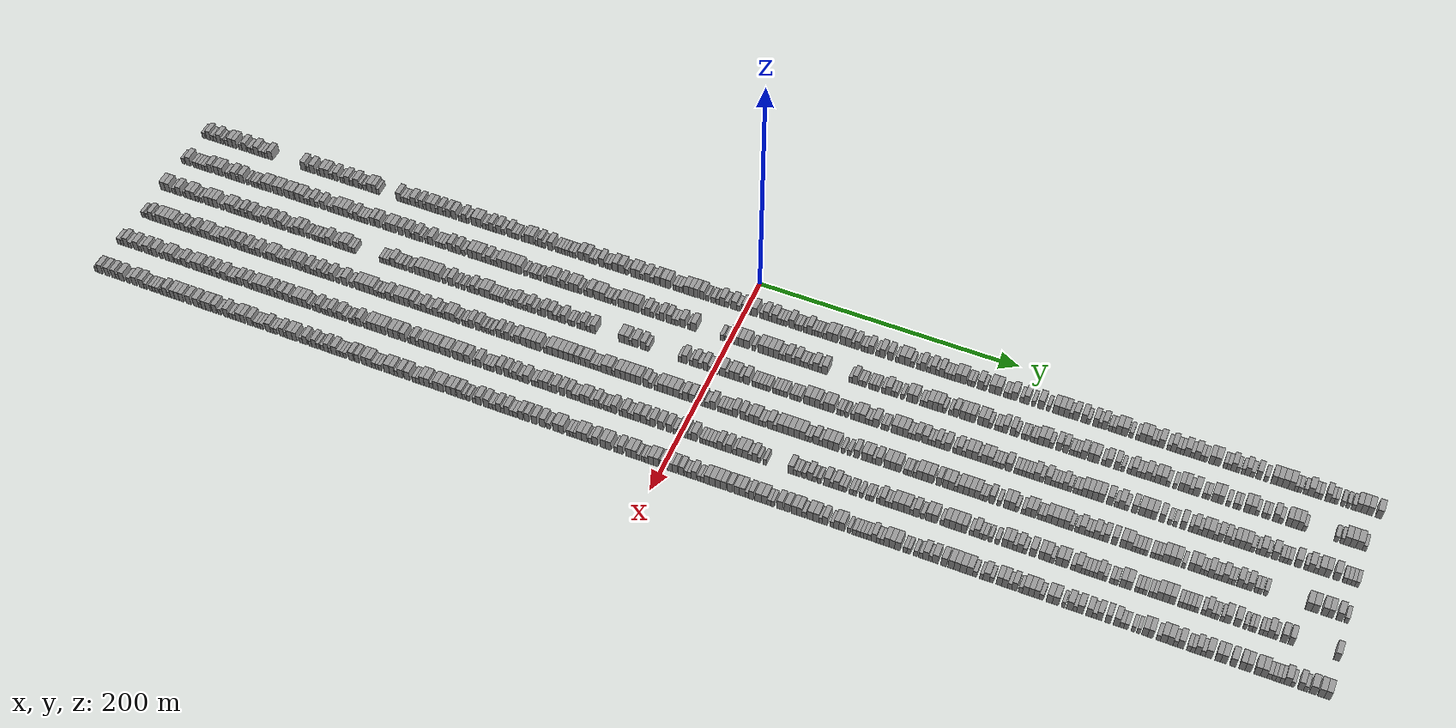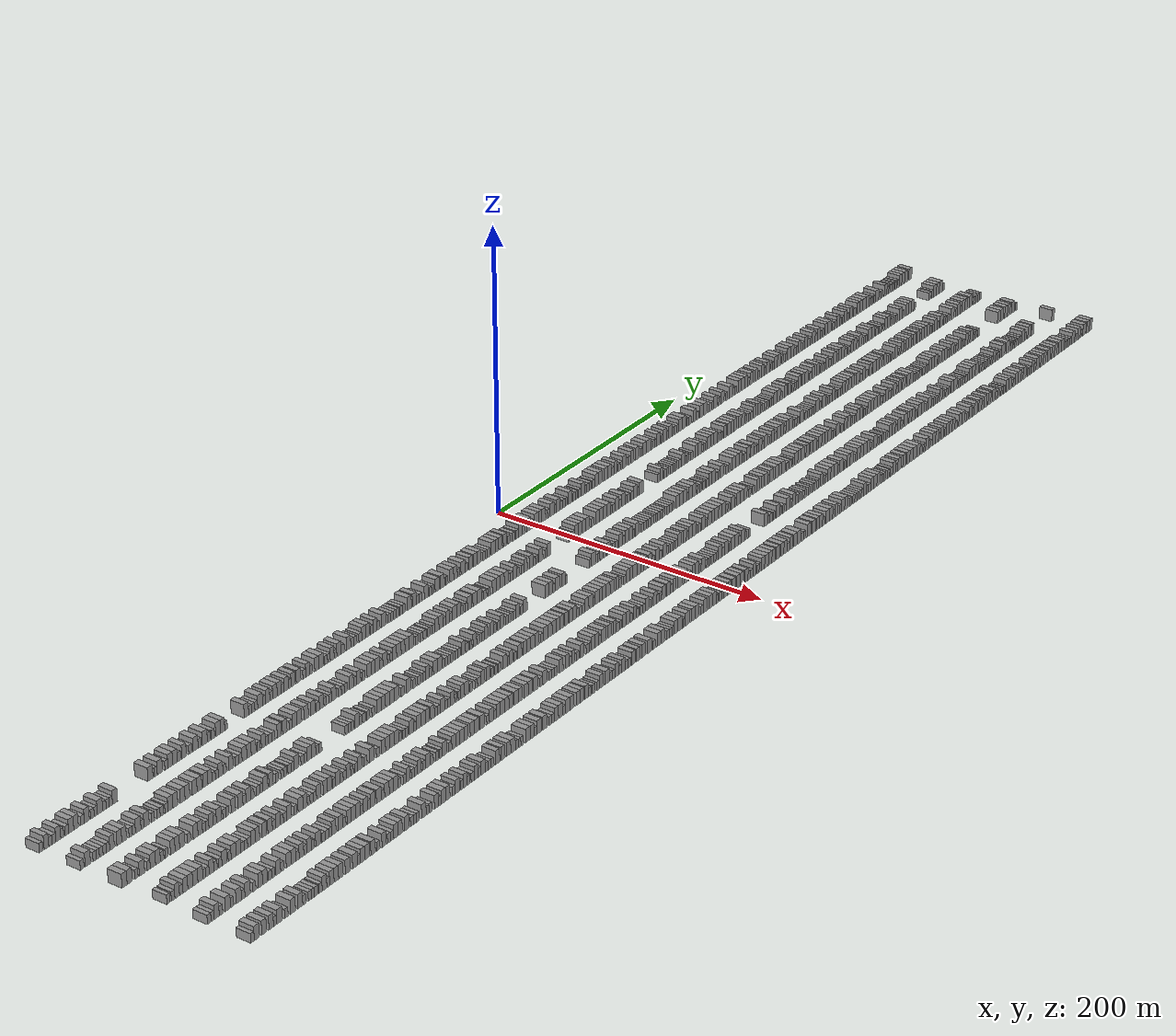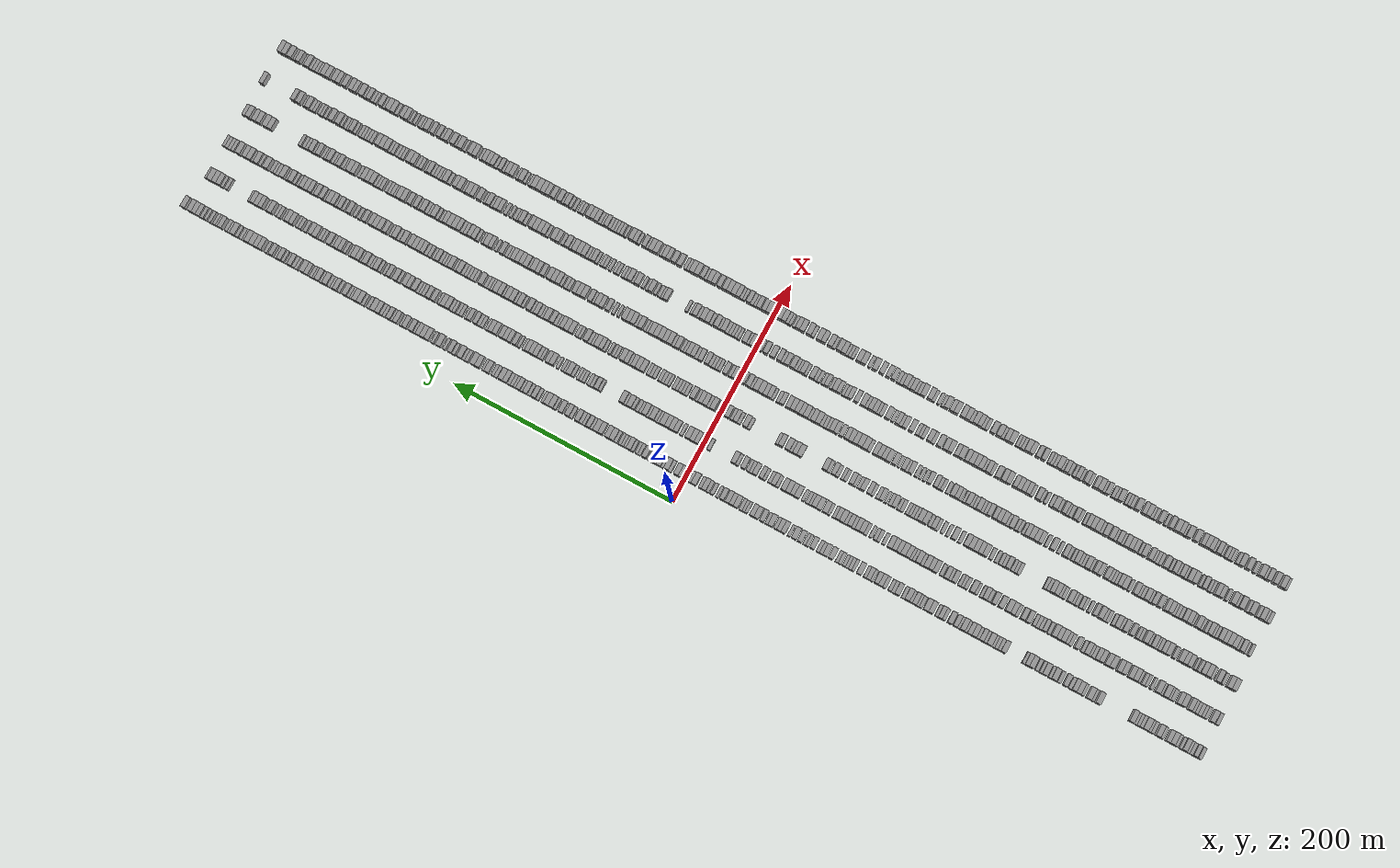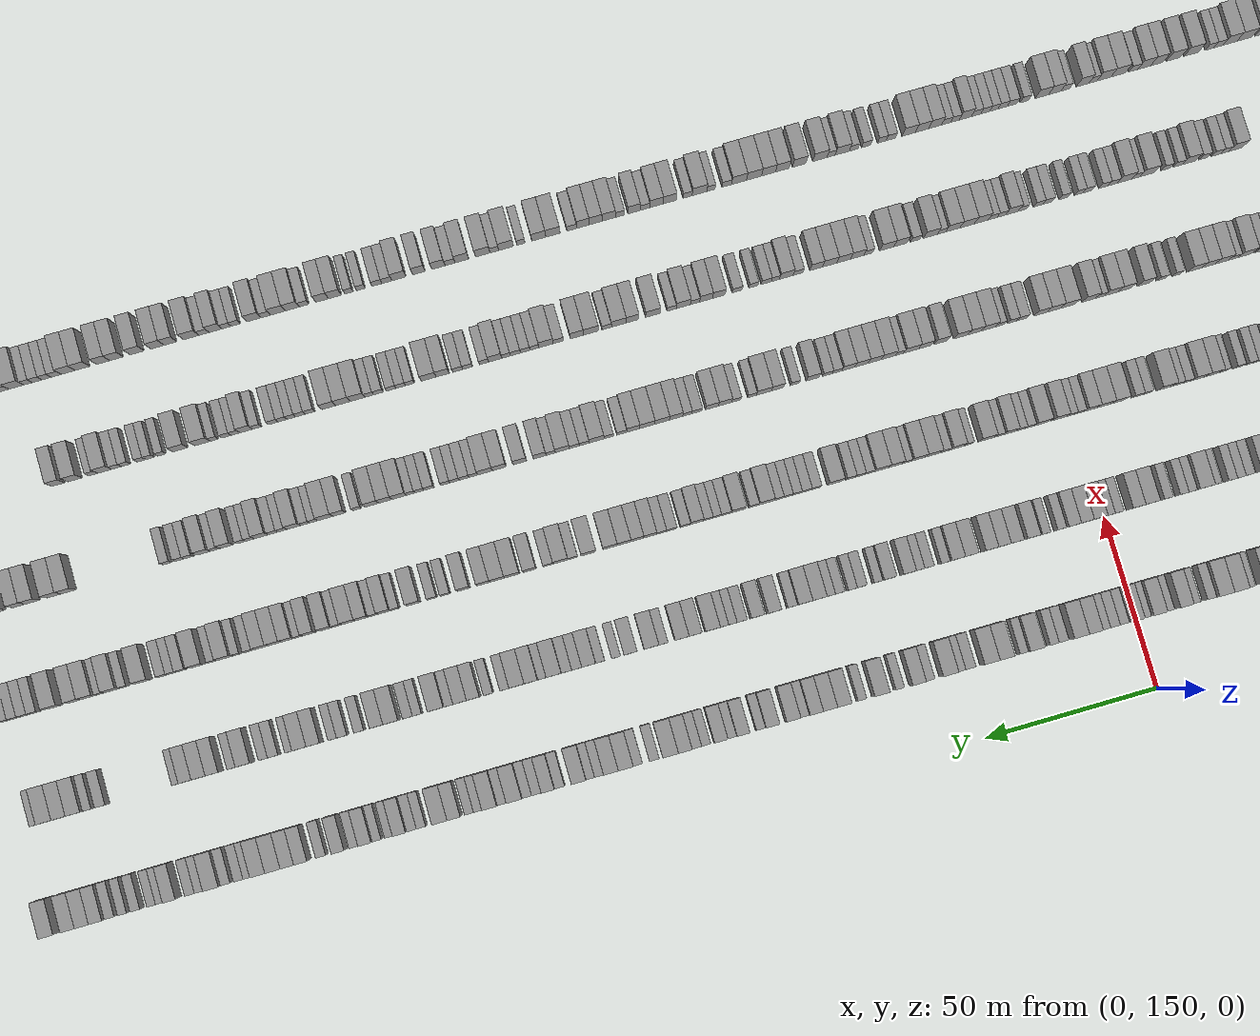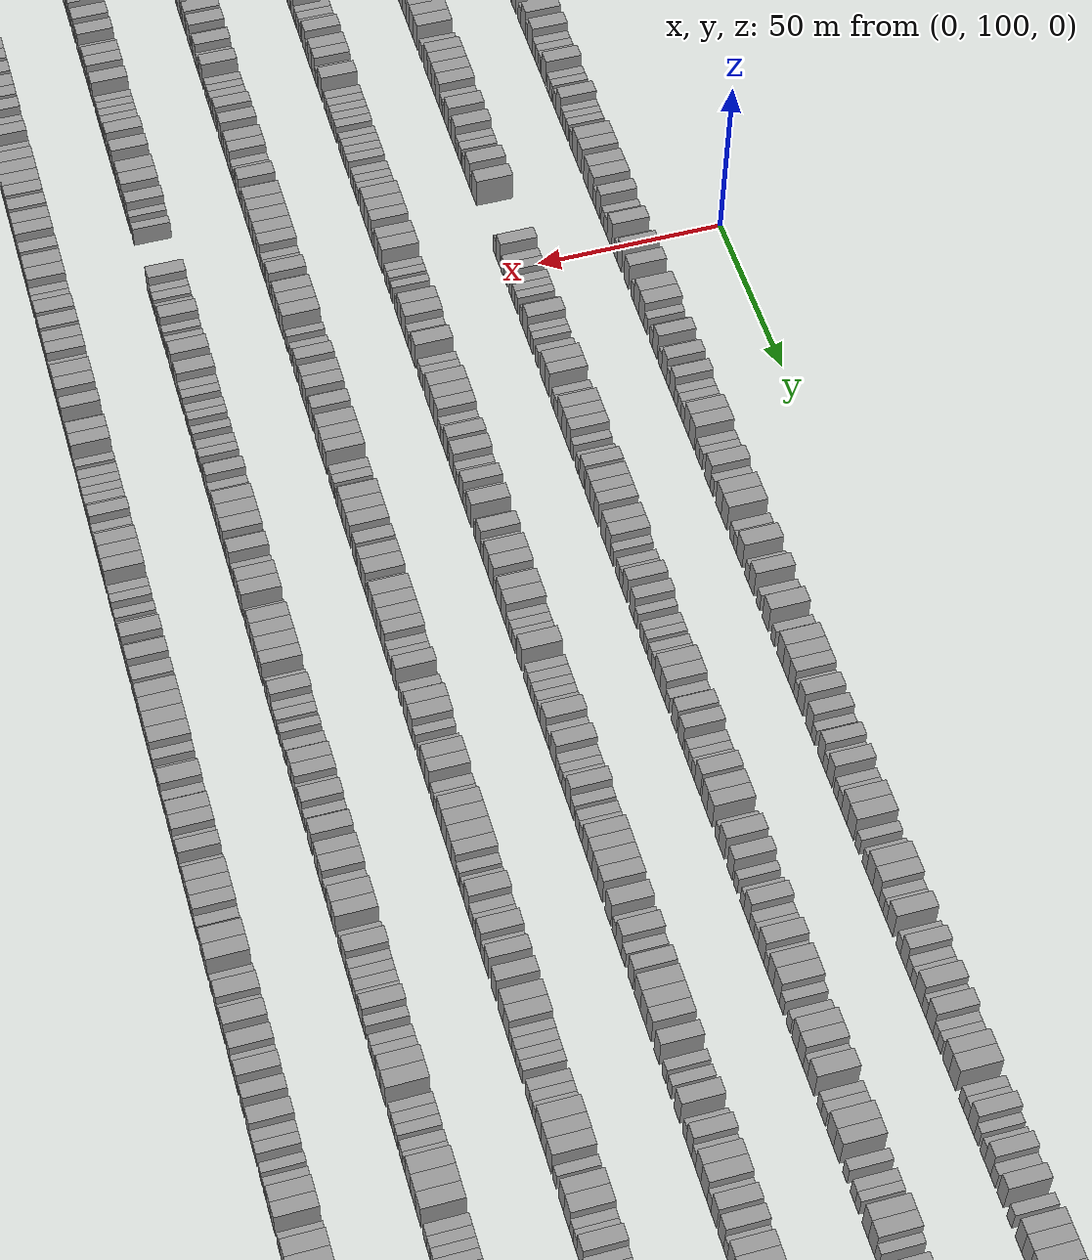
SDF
<sdf version="1.6">
 <world name="default">
  <scene>
   <sky><clouds><speed>12</speed></clouds></sky>
   <ambient>0.4 0.4 0.4 1</ambient>
   <background>0.7 0.7 0.7 1</background>
   <shadows>1</shadows>
  </scene>
  <gravity>0 0 -9.8066</gravity>
  <magnetic_field>6e-06 2.3e-05 -4.2e-05</magnetic_field>
  <physics default="0" name="default_physics" type="ode">
   <ode>
    <solver>
     <type>quick</type>
     <iters>10</iters>
     <sor>1.0</sor>
     <use_dynamic_moi_rescaling>0</use_dynamic_moi_rescaling>
    </solver>
    <constraints>
     <cfm>0</cfm>
     <erp>0.2</erp>
     <contact_max_correcting_vel>100</contact_max_correcting_vel>
     <contact_surface_layer>0.001</contact_surface_layer>
    </constraints>
   </ode>
   <max_step_size>0.004</max_step_size>
   <real_time_factor>1</real_time_factor>
   <real_time_update_rate>250</real_time_update_rate>
  </physics>
  <light name="sun" type="directional">
   <pose>0 0 10 0 0 0</pose>
   <diffuse>0.8 0.8 0.8 1</diffuse>
   <specular>0.2 0.2 0.2 1</specular>
   <attenuation>
    <range>1000</range>
    <constant>0.9</constant>
    <linear>0.01</linear>
    <quadratic>0.001</quadratic>
   </attenuation>
   <direction>-0.5 0.1 -0.9</direction>
  </light>
  <model name="building_1">
   <static>1</static>
   <pose>25.0000 -458.5745 0 0.000000 0.000000 0.000000</pose>
   <link name="link">
    <pose>0 0 3.00 0 0 0</pose>
    <collision name="collision"><geometry><box><size>10.0000 2.8511 6.0000</size></box></geometry></collision>
    <visual name="visual">
     <cast_shadows>0</cast_shadows>
     <geometry><box><size>10.0000 2.8511 6.0000</size></box></geometry>
     <material>
      <script>
       <uri>model://grey_wall/materials/scripts</uri>
       <uri>model://grey_wall/materials/textures</uri>
       <name>vrc/grey_wall</name>
      </script>
     </material>
    </visual>
   </link>
  </model>
  <model name="building_2">
   <static>1</static>
   <pose>25.0000 -454.3311 0 0.000000 0.000000 0.000000</pose>
   <link name="link">
    <pose>0 0 4.50 0 0 0</pose>
    <collision name="collision"><geometry><box><size>10.0000 3.6358 9.0000</size></box></geometry></collision>
    <visual name="visual">
     <cast_shadows>0</cast_shadows>
     <geometry><box><size>10.0000 3.6358 9.0000</size></box></geometry>
     <material>
      <script>
       <uri>model://grey_wall/materials/scripts</uri>
       <uri>model://grey_wall/materials/textures</uri>
       <name>vrc/grey_wall</name>
      </script>
     </material>
    </visual>
   </link>
  </model>
  <model name="building_3">
   <static>1</static>
   <pose>25.0000 -451.1333 0 0.000000 0.000000 0.000000</pose>
   <link name="link">
    <pose>0 0 3.00 0 0 0</pose>
    <collision name="collision"><geometry><box><size>10.0000 2.7597 6.0000</size></box></geometry></collision>
    <visual name="visual">
     <cast_shadows>0</cast_shadows>
     <geometry><box><size>10.0000 2.7597 6.0000</size></box></geometry>
     <material>
      <script>
       <uri>model://grey_wall/materials/scripts</uri>
       <uri>model://grey_wall/materials/textures</uri>
       <name>vrc/grey_wall</name>
      </script>
     </material>
    </visual>
   </link>
  </model>
  <model name="building_4">
   <static>1</static>
   <pose>25.0000 -448.2670 0 0.000000 0.000000 0.000000</pose>
   <link name="link">
    <pose>0 0 3.00 0 0 0</pose>
    <collision name="collision"><geometry><box><size>10.0000 2.9729 6.0000</size></box></geometry></collision>
    <visual name="visual">
     <cast_shadows>0</cast_shadows>
     <geometry><box><size>10.0000 2.9729 6.0000</size></box></geometry>
     <material>
      <script>
       <uri>model://grey_wall/materials/scripts</uri>
       <uri>model://grey_wall/materials/textures</uri>
       <name>vrc/grey_wall</name>
      </script>
     </material>
    </visual>
   </link>
  </model>
  <model name="building_5">
   <static>1</static>
   <pose>25.0000 -444.8772 0 0.000000 0.000000 0.000000</pose>
   <link name="link">
    <pose>0 0 4.50 0 0 0</pose>
    <collision name="collision"><geometry><box><size>10.0000 3.8066 9.0000</size></box></geometry></collision>
    <visual name="visual">
     <cast_shadows>0</cast_shadows>
     <geometry><box><size>10.0000 3.8066 9.0000</size></box></geometry>
     <material>
      <script>
       <uri>model://grey_wall/materials/scripts</uri>
       <uri>model://grey_wall/materials/textures</uri>
       <name>vrc/grey_wall</name>
      </script>
     </material>
    </visual>
   </link>
  </model>
  <model name="building_6">
   <static>1</static>
   <pose>25.0000 -441.7054 0 0.000000 0.000000 0.000000</pose>
   <link name="link">
    <pose>0 0 3.00 0 0 0</pose>
    <collision name="collision"><geometry><box><size>10.0000 2.5371 6.0000</size></box></geometry></collision>
    <visual name="visual">
     <cast_shadows>0</cast_shadows>
     <geometry><box><size>10.0000 2.5371 6.0000</size></box></geometry>
     <material>
      <script>
       <uri>model://grey_wall/materials/scripts</uri>
       <uri>model://grey_wall/materials/textures</uri>
       <name>vrc/grey_wall</name>
      </script>
     </material>
    </visual>
   </link>
  </model>
  <model name="building_7">
   <static>1</static>
   <pose>25.0000 -437.9740 0 0.000000 0.000000 0.000000</pose>
   <link name="link">
    <pose>0 0 3.00 0 0 0</pose>
    <collision name="collision"><geometry><box><size>10.0000 2.9256 6.0000</size></box></geometry></collision>
    <visual name="visual">
     <cast_shadows>0</cast_shadows>
     <geometry><box><size>10.0000 2.9256 6.0000</size></box></geometry>
     <material>
      <script>
       <uri>model://grey_wall/materials/scripts</uri>
       <uri>model://grey_wall/materials/textures</uri>
       <name>vrc/grey_wall</name>
      </script>
     </material>
    </visual>
   </link>
  </model>
  <model name="building_8">
   <static>1</static>
   <pose>25.0000 -434.4728 0 0.000000 0.000000 0.000000</pose>
   <link name="link">
    <pose>0 0 4.50 0 0 0</pose>
    <collision name="collision"><geometry><box><size>10.0000 4.0769 9.0000</size></box></geometry></collision>
    <visual name="visual">
     <cast_shadows>0</cast_shadows>
     <geometry><box><size>10.0000 4.0769 9.0000</size></box></geometry>
     <material>
      <script>
       <uri>model://grey_wall/materials/scripts</uri>
       <uri>model://grey_wall/materials/textures</uri>
       <name>vrc/grey_wall</name>
      </script>
     </material>
    </visual>
   </link>
  </model>
  <model name="building_9">
   <static>1</static>
   <pose>25.0000 -430.5864 0 0.000000 0.000000 0.000000</pose>
   <link name="link">
    <pose>0 0 4.50 0 0 0</pose>
    <collision name="collision"><geometry><box><size>10.0000 3.6958 9.0000</size></box></geometry></collision>
    <visual name="visual">
     <cast_shadows>0</cast_shadows>
     <geometry><box><size>10.0000 3.6958 9.0000</size></box></geometry>
     <material>
      <script>
       <uri>model://grey_wall/materials/scripts</uri>
       <uri>model://grey_wall/materials/textures</uri>
       <name>vrc/grey_wall</name>
      </script>
     </material>
    </visual>
   </link>
  </model>
  <model name="building_10">
   <static>1</static>
   <pose>25.0000 -425.3063 0 0.000000 0.000000 0.000000</pose>
   <link name="link">
    <pose>0 0 3.00 0 0 0</pose>
    <collision name="collision"><geometry><box><size>10.0000 2.8645 6.0000</size></box></geometry></collision>
    <visual name="visual">
     <cast_shadows>0</cast_shadows>
     <geometry><box><size>10.0000 2.8645 6.0000</size></box></geometry>
     <material>
      <script>
       <uri>model://grey_wall/materials/scripts</uri>
       <uri>model://grey_wall/materials/textures</uri>
       <name>vrc/grey_wall</name>
      </script>
     </material>
    </visual>
   </link>
  </model>
  <model name="building_11">
   <static>1</static>
   <pose>25.0000 -421.8627 0 0.000000 0.000000 0.000000</pose>
   <link name="link">
    <pose>0 0 4.50 0 0 0</pose>
    <collision name="collision"><geometry><box><size>10.0000 4.0225 9.0000</size></box></geometry></collision>
    <visual name="visual">
     <cast_shadows>0</cast_shadows>
     <geometry><box><size>10.0000 4.0225 9.0000</size></box></geometry>
     <material>
      <script>
       <uri>model://grey_wall/materials/scripts</uri>
       <uri>model://grey_wall/materials/textures</uri>
       <name>vrc/grey_wall</name>
      </script>
     </material>
    </visual>
   </link>
  </model>
  <model name="building_12">
   <static>1</static>
   <pose>25.0000 -417.3604 0 0.000000 0.000000 0.000000</pose>
   <link name="link">
    <pose>0 0 3.00 0 0 0</pose>
    <collision name="collision"><geometry><box><size>10.0000 2.9822 6.0000</size></box></geometry></collision>
    <visual name="visual">
     <cast_shadows>0</cast_shadows>
     <geometry><box><size>10.0000 2.9822 6.0000</size></box></geometry>
     <material>
      <script>
       <uri>model://grey_wall/materials/scripts</uri>
       <uri>model://grey_wall/materials/textures</uri>
       <name>vrc/grey_wall</name>
      </script>
     </material>
    </visual>
   </link>
  </model>
  <model name="building_13">
   <static>1</static>
   <pose>25.0000 -414.6050 0 0.000000 0.000000 0.000000</pose>
   <link name="link">
    <pose>0 0 3.00 0 0 0</pose>
    <collision name="collision"><geometry><box><size>10.0000 2.5287 6.0000</size></box></geometry></collision>
    <visual name="visual">
     <cast_shadows>0</cast_shadows>
     <geometry><box><size>10.0000 2.5287 6.0000</size></box></geometry>
     <material>
      <script>
       <uri>model://grey_wall/materials/scripts</uri>
       <uri>model://grey_wall/materials/textures</uri>
       <name>vrc/grey_wall</name>
      </script>
     </material>
    </visual>
   </link>
  </model>
  <model name="building_14">
   <static>1</static>
   <pose>25.0000 -411.1053 0 0.000000 0.000000 0.000000</pose>
   <link name="link">
    <pose>0 0 4.50 0 0 0</pose>
    <collision name="collision"><geometry><box><size>10.0000 4.4707 9.0000</size></box></geometry></collision>
    <visual name="visual">
     <cast_shadows>0</cast_shadows>
     <geometry><box><size>10.0000 4.4707 9.0000</size></box></geometry>
     <material>
      <script>
       <uri>model://grey_wall/materials/scripts</uri>
       <uri>model://grey_wall/materials/textures</uri>
       <name>vrc/grey_wall</name>
      </script>
     </material>
    </visual>
   </link>
  </model>
  <model name="building_15">
   <static>1</static>
   <pose>25.0000 -407.4802 0 0.000000 0.000000 0.000000</pose>
   <link name="link">
    <pose>0 0 3.00 0 0 0</pose>
    <collision name="collision"><geometry><box><size>10.0000 2.7793 6.0000</size></box></geometry></collision>
    <visual name="visual">
     <cast_shadows>0</cast_shadows>
     <geometry><box><size>10.0000 2.7793 6.0000</size></box></geometry>
     <material>
      <script>
       <uri>model://grey_wall/materials/scripts</uri>
       <uri>model://grey_wall/materials/textures</uri>
       <name>vrc/grey_wall</name>
      </script>
     </material>
    </visual>
   </link>
  </model>
  <model name="building_16">
   <static>1</static>
   <pose>25.0000 -404.7872 0 0.000000 0.000000 0.000000</pose>
   <link name="link">
    <pose>0 0 3.00 0 0 0</pose>
    <collision name="collision"><geometry><box><size>10.0000 2.6068 6.0000</size></box></geometry></collision>
    <visual name="visual">
     <cast_shadows>0</cast_shadows>
     <geometry><box><size>10.0000 2.6068 6.0000</size></box></geometry>
     <material>
      <script>
       <uri>model://grey_wall/materials/scripts</uri>
       <uri>model://grey_wall/materials/textures</uri>
       <name>vrc/grey_wall</name>
      </script>
     </material>
    </visual>
   </link>
  </model>
  <model name="building_17">
   <static>1</static>
   <pose>25.0000 -402.1620 0 0.000000 0.000000 0.000000</pose>
   <link name="link">
    <pose>0 0 3.00 0 0 0</pose>
    <collision name="collision"><geometry><box><size>10.0000 2.6436 6.0000</size></box></geometry></collision>
    <visual name="visual">
     <cast_shadows>0</cast_shadows>
     <geometry><box><size>10.0000 2.6436 6.0000</size></box></geometry>
     <material>
      <script>
       <uri>model://grey_wall/materials/scripts</uri>
       <uri>model://grey_wall/materials/textures</uri>
       <name>vrc/grey_wall</name>
      </script>
     </material>
    </visual>
   </link>
  </model>
  <model name="building_18">
   <static>1</static>
   <pose>25.0000 -398.7324 0 0.000000 0.000000 0.000000</pose>
   <link name="link">
    <pose>0 0 4.50 0 0 0</pose>
    <collision name="collision"><geometry><box><size>10.0000 4.2156 9.0000</size></box></geometry></collision>
    <visual name="visual">
     <cast_shadows>0</cast_shadows>
     <geometry><box><size>10.0000 4.2156 9.0000</size></box></geometry>
     <material>
      <script>
       <uri>model://grey_wall/materials/scripts</uri>
       <uri>model://grey_wall/materials/textures</uri>
       <name>vrc/grey_wall</name>
      </script>
     </material>
    </visual>
   </link>
  </model>
  <model name="building_19">
   <static>1</static>
   <pose>25.0000 -369.1829 0 0.000000 0.000000 0.000000</pose>
   <link name="link">
    <pose>0 0 4.50 0 0 0</pose>
    <collision name="collision"><geometry><box><size>10.0000 4.2945 9.0000</size></box></geometry></collision>
    <visual name="visual">
     <cast_shadows>0</cast_shadows>
     <geometry><box><size>10.0000 4.2945 9.0000</size></box></geometry>
     <material>
      <script>
       <uri>model://grey_wall/materials/scripts</uri>
       <uri>model://grey_wall/materials/textures</uri>
       <name>vrc/grey_wall</name>
      </script>
     </material>
    </visual>
   </link>
  </model>
  <model name="building_20">
   <static>1</static>
   <pose>25.0000 -364.7228 0 0.000000 0.000000 0.000000</pose>
   <link name="link">
    <pose>0 0 3.00 0 0 0</pose>
    <collision name="collision"><geometry><box><size>10.0000 2.6258 6.0000</size></box></geometry></collision>
    <visual name="visual">
     <cast_shadows>0</cast_shadows>
     <geometry><box><size>10.0000 2.6258 6.0000</size></box></geometry>
     <material>
      <script>
       <uri>model://grey_wall/materials/scripts</uri>
       <uri>model://grey_wall/materials/textures</uri>
       <name>vrc/grey_wall</name>
      </script>
     </material>
    </visual>
   </link>
  </model>
  <model name="building_21">
   <static>1</static>
   <pose>25.0000 -361.1903 0 0.000000 0.000000 0.000000</pose>
   <link name="link">
    <pose>0 0 4.50 0 0 0</pose>
    <collision name="collision"><geometry><box><size>10.0000 4.4393 9.0000</size></box></geometry></collision>
    <visual name="visual">
     <cast_shadows>0</cast_shadows>
     <geometry><box><size>10.0000 4.4393 9.0000</size></box></geometry>
     <material>
      <script>
       <uri>model://grey_wall/materials/scripts</uri>
       <uri>model://grey_wall/materials/textures</uri>
       <name>vrc/grey_wall</name>
      </script>
     </material>
    </visual>
   </link>
  </model>
  <model name="building_22">
   <static>1</static>
   <pose>25.0000 -355.6557 0 0.000000 0.000000 0.000000</pose>
   <link name="link">
    <pose>0 0 3.00 0 0 0</pose>
    <collision name="collision"><geometry><box><size>10.0000 2.6299 6.0000</size></box></geometry></collision>
    <visual name="visual">
     <cast_shadows>0</cast_shadows>
     <geometry><box><size>10.0000 2.6299 6.0000</size></box></geometry>
     <material>
      <script>
       <uri>model://grey_wall/materials/scripts</uri>
       <uri>model://grey_wall/materials/textures</uri>
       <name>vrc/grey_wall</name>
      </script>
     </material>
    </visual>
   </link>
  </model>
  <model name="building_23">
   <static>1</static>
   <pose>25.0000 -352.2939 0 0.000000 0.000000 0.000000</pose>
   <link name="link">
    <pose>0 0 4.50 0 0 0</pose>
    <collision name="collision"><geometry><box><size>10.0000 4.0938 9.0000</size></box></geometry></collision>
    <visual name="visual">
     <cast_shadows>0</cast_shadows>
     <geometry><box><size>10.0000 4.0938 9.0000</size></box></geometry>
     <material>
      <script>
       <uri>model://grey_wall/materials/scripts</uri>
       <uri>model://grey_wall/materials/textures</uri>
       <name>vrc/grey_wall</name>
      </script>
     </material>
    </visual>
   </link>
  </model>
  <model name="building_24">
   <static>1</static>
   <pose>25.0000 -348.2709 0 0.000000 0.000000 0.000000</pose>
   <link name="link">
    <pose>0 0 4.50 0 0 0</pose>
    <collision name="collision"><geometry><box><size>10.0000 3.9522 9.0000</size></box></geometry></collision>
    <visual name="visual">
     <cast_shadows>0</cast_shadows>
     <geometry><box><size>10.0000 3.9522 9.0000</size></box></geometry>
     <material>
      <script>
       <uri>model://grey_wall/materials/scripts</uri>
       <uri>model://grey_wall/materials/textures</uri>
       <name>vrc/grey_wall</name>
      </script>
     </material>
    </visual>
   </link>
  </model>
  <model name="building_25">
   <static>1</static>
   <pose>25.0000 -344.8413 0 0.000000 0.000000 0.000000</pose>
   <link name="link">
    <pose>0 0 3.00 0 0 0</pose>
    <collision name="collision"><geometry><box><size>10.0000 2.9071 6.0000</size></box></geometry></collision>
    <visual name="visual">
     <cast_shadows>0</cast_shadows>
     <geometry><box><size>10.0000 2.9071 6.0000</size></box></geometry>
     <material>
      <script>
       <uri>model://grey_wall/materials/scripts</uri>
       <uri>model://grey_wall/materials/textures</uri>
       <name>vrc/grey_wall</name>
      </script>
     </material>
    </visual>
   </link>
  </model>
  <model name="building_26">
   <static>1</static>
   <pose>25.0000 -340.4635 0 0.000000 0.000000 0.000000</pose>
   <link name="link">
    <pose>0 0 4.50 0 0 0</pose>
    <collision name="collision"><geometry><box><size>10.0000 3.8486 9.0000</size></box></geometry></collision>
    <visual name="visual">
     <cast_shadows>0</cast_shadows>
     <geometry><box><size>10.0000 3.8486 9.0000</size></box></geometry>
     <material>
      <script>
       <uri>model://grey_wall/materials/scripts</uri>
       <uri>model://grey_wall/materials/textures</uri>
       <name>vrc/grey_wall</name>
      </script>
     </material>
    </visual>
   </link>
  </model>
  <model name="building_27">
   <static>1</static>
   <pose>25.0000 -335.1388 0 0.000000 0.000000 0.000000</pose>
   <link name="link">
    <pose>0 0 3.00 0 0 0</pose>
    <collision name="collision"><geometry><box><size>10.0000 2.8007 6.0000</size></box></geometry></collision>
    <visual name="visual">
     <cast_shadows>0</cast_shadows>
     <geometry><box><size>10.0000 2.8007 6.0000</size></box></geometry>
     <material>
      <script>
       <uri>model://grey_wall/materials/scripts</uri>
       <uri>model://grey_wall/materials/textures</uri>
       <name>vrc/grey_wall</name>
      </script>
     </material>
    </visual>
   </link>
  </model>
  <model name="building_28">
   <static>1</static>
   <pose>25.0000 -330.5292 0 0.000000 0.000000 0.000000</pose>
   <link name="link">
    <pose>0 0 4.50 0 0 0</pose>
    <collision name="collision"><geometry><box><size>10.0000 4.4186 9.0000</size></box></geometry></collision>
    <visual name="visual">
     <cast_shadows>0</cast_shadows>
     <geometry><box><size>10.0000 4.4186 9.0000</size></box></geometry>
     <material>
      <script>
       <uri>model://grey_wall/materials/scripts</uri>
       <uri>model://grey_wall/materials/textures</uri>
       <name>vrc/grey_wall</name>
      </script>
     </material>
    </visual>
   </link>
  </model>
  <model name="building_29">
   <static>1</static>
   <pose>25.0000 -327.0513 0 0.000000 0.000000 0.000000</pose>
   <link name="link">
    <pose>0 0 3.00 0 0 0</pose>
    <collision name="collision"><geometry><box><size>10.0000 2.5372 6.0000</size></box></geometry></collision>
    <visual name="visual">
     <cast_shadows>0</cast_shadows>
     <geometry><box><size>10.0000 2.5372 6.0000</size></box></geometry>
     <material>
      <script>
       <uri>model://grey_wall/materials/scripts</uri>
       <uri>model://grey_wall/materials/textures</uri>
       <name>vrc/grey_wall</name>
      </script>
     </material>
    </visual>
   </link>
  </model>
  <model name="building_30">
   <static>1</static>
   <pose>25.0000 -322.5564 0 0.000000 0.000000 0.000000</pose>
   <link name="link">
    <pose>0 0 4.50 0 0 0</pose>
    <collision name="collision"><geometry><box><size>10.0000 4.4526 9.0000</size></box></geometry></collision>
    <visual name="visual">
     <cast_shadows>0</cast_shadows>
     <geometry><box><size>10.0000 4.4526 9.0000</size></box></geometry>
     <material>
      <script>
       <uri>model://grey_wall/materials/scripts</uri>
       <uri>model://grey_wall/materials/textures</uri>
       <name>vrc/grey_wall</name>
      </script>
     </material>
    </visual>
   </link>
  </model>
  <model name="building_31">
   <static>1</static>
   <pose>25.0000 -319.0257 0 0.000000 0.000000 0.000000</pose>
   <link name="link">
    <pose>0 0 3.00 0 0 0</pose>
    <collision name="collision"><geometry><box><size>10.0000 2.6088 6.0000</size></box></geometry></collision>
    <visual name="visual">
     <cast_shadows>0</cast_shadows>
     <geometry><box><size>10.0000 2.6088 6.0000</size></box></geometry>
     <material>
      <script>
       <uri>model://grey_wall/materials/scripts</uri>
       <uri>model://grey_wall/materials/textures</uri>
       <name>vrc/grey_wall</name>
      </script>
     </material>
    </visual>
   </link>
  </model>
  <model name="building_32">
   <static>1</static>
   <pose>25.0000 -315.3328 0 0.000000 0.000000 0.000000</pose>
   <link name="link">
    <pose>0 0 3.00 0 0 0</pose>
    <collision name="collision"><geometry><box><size>10.0000 2.7768 6.0000</size></box></geometry></collision>
    <visual name="visual">
     <cast_shadows>0</cast_shadows>
     <geometry><box><size>10.0000 2.7768 6.0000</size></box></geometry>
     <material>
      <script>
       <uri>model://grey_wall/materials/scripts</uri>
       <uri>model://grey_wall/materials/textures</uri>
       <name>vrc/grey_wall</name>
      </script>
     </material>
    </visual>
   </link>
  </model>
  <model name="building_33">
   <static>1</static>
   <pose>25.0000 -310.8081 0 0.000000 0.000000 0.000000</pose>
   <link name="link">
    <pose>0 0 4.50 0 0 0</pose>
    <collision name="collision"><geometry><box><size>10.0000 4.2726 9.0000</size></box></geometry></collision>
    <visual name="visual">
     <cast_shadows>0</cast_shadows>
     <geometry><box><size>10.0000 4.2726 9.0000</size></box></geometry>
     <material>
      <script>
       <uri>model://grey_wall/materials/scripts</uri>
       <uri>model://grey_wall/materials/textures</uri>
       <name>vrc/grey_wall</name>
      </script>
     </material>
    </visual>
   </link>
  </model>
  <model name="building_34">
   <static>1</static>
   <pose>25.0000 -306.8555 0 0.000000 0.000000 0.000000</pose>
   <link name="link">
    <pose>0 0 4.50 0 0 0</pose>
    <collision name="collision"><geometry><box><size>10.0000 3.6327 9.0000</size></box></geometry></collision>
    <visual name="visual">
     <cast_shadows>0</cast_shadows>
     <geometry><box><size>10.0000 3.6327 9.0000</size></box></geometry>
     <material>
      <script>
       <uri>model://grey_wall/materials/scripts</uri>
       <uri>model://grey_wall/materials/textures</uri>
       <name>vrc/grey_wall</name>
      </script>
     </material>
    </visual>
   </link>
  </model>
  <model name="building_35">
   <static>1</static>
   <pose>25.0000 -303.8384 0 0.000000 0.000000 0.000000</pose>
   <link name="link">
    <pose>0 0 3.00 0 0 0</pose>
    <collision name="collision"><geometry><box><size>10.0000 2.4015 6.0000</size></box></geometry></collision>
    <visual name="visual">
     <cast_shadows>0</cast_shadows>
     <geometry><box><size>10.0000 2.4015 6.0000</size></box></geometry>
     <material>
      <script>
       <uri>model://grey_wall/materials/scripts</uri>
       <uri>model://grey_wall/materials/textures</uri>
       <name>vrc/grey_wall</name>
      </script>
     </material>
    </visual>
   </link>
  </model>
  <model name="building_36">
   <static>1</static>
   <pose>25.0000 -285.7423 0 0.000000 0.000000 0.000000</pose>
   <link name="link">
    <pose>0 0 4.50 0 0 0</pose>
    <collision name="collision"><geometry><box><size>10.0000 3.9302 9.0000</size></box></geometry></collision>
    <visual name="visual">
     <cast_shadows>0</cast_shadows>
     <geometry><box><size>10.0000 3.9302 9.0000</size></box></geometry>
     <material>
      <script>
       <uri>model://grey_wall/materials/scripts</uri>
       <uri>model://grey_wall/materials/textures</uri>
       <name>vrc/grey_wall</name>
      </script>
     </material>
    </visual>
   </link>
  </model>
  <model name="building_37">
   <static>1</static>
   <pose>25.0000 -282.4414 0 0.000000 0.000000 0.000000</pose>
   <link name="link">
    <pose>0 0 3.00 0 0 0</pose>
    <collision name="collision"><geometry><box><size>10.0000 2.6717 6.0000</size></box></geometry></collision>
    <visual name="visual">
     <cast_shadows>0</cast_shadows>
     <geometry><box><size>10.0000 2.6717 6.0000</size></box></geometry>
     <material>
      <script>
       <uri>model://grey_wall/materials/scripts</uri>
       <uri>model://grey_wall/materials/textures</uri>
       <name>vrc/grey_wall</name>
      </script>
     </material>
    </visual>
   </link>
  </model>
  <model name="building_38">
   <static>1</static>
   <pose>25.0000 -279.6483 0 0.000000 0.000000 0.000000</pose>
   <link name="link">
    <pose>0 0 3.00 0 0 0</pose>
    <collision name="collision"><geometry><box><size>10.0000 2.9146 6.0000</size></box></geometry></collision>
    <visual name="visual">
     <cast_shadows>0</cast_shadows>
     <geometry><box><size>10.0000 2.9146 6.0000</size></box></geometry>
     <material>
      <script>
       <uri>model://grey_wall/materials/scripts</uri>
       <uri>model://grey_wall/materials/textures</uri>
       <name>vrc/grey_wall</name>
      </script>
     </material>
    </visual>
   </link>
  </model>
  <model name="building_39">
   <static>1</static>
   <pose>25.0000 -276.8783 0 0.000000 0.000000 0.000000</pose>
   <link name="link">
    <pose>0 0 3.00 0 0 0</pose>
    <collision name="collision"><geometry><box><size>10.0000 2.6253 6.0000</size></box></geometry></collision>
    <visual name="visual">
     <cast_shadows>0</cast_shadows>
     <geometry><box><size>10.0000 2.6253 6.0000</size></box></geometry>
     <material>
      <script>
       <uri>model://grey_wall/materials/scripts</uri>
       <uri>model://grey_wall/materials/textures</uri>
       <name>vrc/grey_wall</name>
      </script>
     </material>
    </visual>
   </link>
  </model>
  <model name="building_40">
   <static>1</static>
   <pose>25.0000 -273.3258 0 0.000000 0.000000 0.000000</pose>
   <link name="link">
    <pose>0 0 4.50 0 0 0</pose>
    <collision name="collision"><geometry><box><size>10.0000 4.4799 9.0000</size></box></geometry></collision>
    <visual name="visual">
     <cast_shadows>0</cast_shadows>
     <geometry><box><size>10.0000 4.4799 9.0000</size></box></geometry>
     <material>
      <script>
       <uri>model://grey_wall/materials/scripts</uri>
       <uri>model://grey_wall/materials/textures</uri>
       <name>vrc/grey_wall</name>
      </script>
     </material>
    </visual>
   </link>
  </model>
  <model name="building_41">
   <static>1</static>
   <pose>25.0000 -269.7409 0 0.000000 0.000000 0.000000</pose>
   <link name="link">
    <pose>0 0 3.00 0 0 0</pose>
    <collision name="collision"><geometry><box><size>10.0000 2.6898 6.0000</size></box></geometry></collision>
    <visual name="visual">
     <cast_shadows>0</cast_shadows>
     <geometry><box><size>10.0000 2.6898 6.0000</size></box></geometry>
     <material>
      <script>
       <uri>model://grey_wall/materials/scripts</uri>
       <uri>model://grey_wall/materials/textures</uri>
       <name>vrc/grey_wall</name>
      </script>
     </material>
    </visual>
   </link>
  </model>
  <model name="building_42">
   <static>1</static>
   <pose>25.0000 -266.5180 0 0.000000 0.000000 0.000000</pose>
   <link name="link">
    <pose>0 0 4.50 0 0 0</pose>
    <collision name="collision"><geometry><box><size>10.0000 3.7562 9.0000</size></box></geometry></collision>
    <visual name="visual">
     <cast_shadows>0</cast_shadows>
     <geometry><box><size>10.0000 3.7562 9.0000</size></box></geometry>
     <material>
      <script>
       <uri>model://grey_wall/materials/scripts</uri>
       <uri>model://grey_wall/materials/textures</uri>
       <name>vrc/grey_wall</name>
      </script>
     </material>
    </visual>
   </link>
  </model>
  <model name="building_43">
   <static>1</static>
   <pose>25.0000 -263.2904 0 0.000000 0.000000 0.000000</pose>
   <link name="link">
    <pose>0 0 3.00 0 0 0</pose>
    <collision name="collision"><geometry><box><size>10.0000 2.6990 6.0000</size></box></geometry></collision>
    <visual name="visual">
     <cast_shadows>0</cast_shadows>
     <geometry><box><size>10.0000 2.6990 6.0000</size></box></geometry>
     <material>
      <script>
       <uri>model://grey_wall/materials/scripts</uri>
       <uri>model://grey_wall/materials/textures</uri>
       <name>vrc/grey_wall</name>
      </script>
     </material>
    </visual>
   </link>
  </model>
  <model name="building_44">
   <static>1</static>
   <pose>25.0000 -259.8911 0 0.000000 0.000000 0.000000</pose>
   <link name="link">
    <pose>0 0 4.50 0 0 0</pose>
    <collision name="collision"><geometry><box><size>10.0000 4.0995 9.0000</size></box></geometry></collision>
    <visual name="visual">
     <cast_shadows>0</cast_shadows>
     <geometry><box><size>10.0000 4.0995 9.0000</size></box></geometry>
     <material>
      <script>
       <uri>model://grey_wall/materials/scripts</uri>
       <uri>model://grey_wall/materials/textures</uri>
       <name>vrc/grey_wall</name>
      </script>
     </material>
    </visual>
   </link>
  </model>
  <model name="building_45">
   <static>1</static>
   <pose>25.0000 -255.9465 0 0.000000 0.000000 0.000000</pose>
   <link name="link">
    <pose>0 0 4.50 0 0 0</pose>
    <collision name="collision"><geometry><box><size>10.0000 3.7897 9.0000</size></box></geometry></collision>
    <visual name="visual">
     <cast_shadows>0</cast_shadows>
     <geometry><box><size>10.0000 3.7897 9.0000</size></box></geometry>
     <material>
      <script>
       <uri>model://grey_wall/materials/scripts</uri>
       <uri>model://grey_wall/materials/textures</uri>
       <name>vrc/grey_wall</name>
      </script>
     </material>
    </visual>
   </link>
  </model>
  <model name="building_46">
   <static>1</static>
   <pose>25.0000 -252.8218 0 0.000000 0.000000 0.000000</pose>
   <link name="link">
    <pose>0 0 3.00 0 0 0</pose>
    <collision name="collision"><geometry><box><size>10.0000 2.4597 6.0000</size></box></geometry></collision>
    <visual name="visual">
     <cast_shadows>0</cast_shadows>
     <geometry><box><size>10.0000 2.4597 6.0000</size></box></geometry>
     <material>
      <script>
       <uri>model://grey_wall/materials/scripts</uri>
       <uri>model://grey_wall/materials/textures</uri>
       <name>vrc/grey_wall</name>
      </script>
     </material>
    </visual>
   </link>
  </model>
  <model name="building_47">
   <static>1</static>
   <pose>25.0000 -249.5862 0 0.000000 0.000000 0.000000</pose>
   <link name="link">
    <pose>0 0 4.50 0 0 0</pose>
    <collision name="collision"><geometry><box><size>10.0000 4.0114 9.0000</size></box></geometry></collision>
    <visual name="visual">
     <cast_shadows>0</cast_shadows>
     <geometry><box><size>10.0000 4.0114 9.0000</size></box></geometry>
     <material>
      <script>
       <uri>model://grey_wall/materials/scripts</uri>
       <uri>model://grey_wall/materials/textures</uri>
       <name>vrc/grey_wall</name>
      </script>
     </material>
    </visual>
   </link>
  </model>
  <model name="building_48">
   <static>1</static>
   <pose>25.0000 -246.3755 0 0.000000 0.000000 0.000000</pose>
   <link name="link">
    <pose>0 0 3.00 0 0 0</pose>
    <collision name="collision"><geometry><box><size>10.0000 2.4101 6.0000</size></box></geometry></collision>
    <visual name="visual">
     <cast_shadows>0</cast_shadows>
     <geometry><box><size>10.0000 2.4101 6.0000</size></box></geometry>
     <material>
      <script>
       <uri>model://grey_wall/materials/scripts</uri>
       <uri>model://grey_wall/materials/textures</uri>
       <name>vrc/grey_wall</name>
      </script>
     </material>
    </visual>
   </link>
  </model>
  <model name="building_49">
   <static>1</static>
   <pose>25.0000 -243.2896 0 0.000000 0.000000 0.000000</pose>
   <link name="link">
    <pose>0 0 4.50 0 0 0</pose>
    <collision name="collision"><geometry><box><size>10.0000 3.7618 9.0000</size></box></geometry></collision>
    <visual name="visual">
     <cast_shadows>0</cast_shadows>
     <geometry><box><size>10.0000 3.7618 9.0000</size></box></geometry>
     <material>
      <script>
       <uri>model://grey_wall/materials/scripts</uri>
       <uri>model://grey_wall/materials/textures</uri>
       <name>vrc/grey_wall</name>
      </script>
     </material>
    </visual>
   </link>
  </model>
  <model name="building_50">
   <static>1</static>
   <pose>25.0000 -238.3933 0 0.000000 0.000000 0.000000</pose>
   <link name="link">
    <pose>0 0 4.50 0 0 0</pose>
    <collision name="collision"><geometry><box><size>10.0000 4.0307 9.0000</size></box></geometry></collision>
    <visual name="visual">
     <cast_shadows>0</cast_shadows>
     <geometry><box><size>10.0000 4.0307 9.0000</size></box></geometry>
     <material>
      <script>
       <uri>model://grey_wall/materials/scripts</uri>
       <uri>model://grey_wall/materials/textures</uri>
       <name>vrc/grey_wall</name>
      </script>
     </material>
    </visual>
   </link>
  </model>
  <model name="building_51">
   <static>1</static>
   <pose>25.0000 -232.9716 0 0.000000 0.000000 0.000000</pose>
   <link name="link">
    <pose>0 0 3.00 0 0 0</pose>
    <collision name="collision"><geometry><box><size>10.0000 2.8127 6.0000</size></box></geometry></collision>
    <visual name="visual">
     <cast_shadows>0</cast_shadows>
     <geometry><box><size>10.0000 2.8127 6.0000</size></box></geometry>
     <material>
      <script>
       <uri>model://grey_wall/materials/scripts</uri>
       <uri>model://grey_wall/materials/textures</uri>
       <name>vrc/grey_wall</name>
      </script>
     </material>
    </visual>
   </link>
  </model>
  <model name="building_52">
   <static>1</static>
   <pose>25.0000 -229.7193 0 0.000000 0.000000 0.000000</pose>
   <link name="link">
    <pose>0 0 4.50 0 0 0</pose>
    <collision name="collision"><geometry><box><size>10.0000 3.6919 9.0000</size></box></geometry></collision>
    <visual name="visual">
     <cast_shadows>0</cast_shadows>
     <geometry><box><size>10.0000 3.6919 9.0000</size></box></geometry>
     <material>
      <script>
       <uri>model://grey_wall/materials/scripts</uri>
       <uri>model://grey_wall/materials/textures</uri>
       <name>vrc/grey_wall</name>
      </script>
     </material>
    </visual>
   </link>
  </model>
  <model name="building_53">
   <static>1</static>
   <pose>25.0000 -226.5765 0 0.000000 0.000000 0.000000</pose>
   <link name="link">
    <pose>0 0 3.00 0 0 0</pose>
    <collision name="collision"><geometry><box><size>10.0000 2.5938 6.0000</size></box></geometry></collision>
    <visual name="visual">
     <cast_shadows>0</cast_shadows>
     <geometry><box><size>10.0000 2.5938 6.0000</size></box></geometry>
     <material>
      <script>
       <uri>model://grey_wall/materials/scripts</uri>
       <uri>model://grey_wall/materials/textures</uri>
       <name>vrc/grey_wall</name>
      </script>
     </material>
    </visual>
   </link>
  </model>
  <model name="building_54">
   <static>1</static>
   <pose>25.0000 -221.2471 0 0.000000 0.000000 0.000000</pose>
   <link name="link">
    <pose>0 0 4.50 0 0 0</pose>
    <collision name="collision"><geometry><box><size>10.0000 4.0650 9.0000</size></box></geometry></collision>
    <visual name="visual">
     <cast_shadows>0</cast_shadows>
     <geometry><box><size>10.0000 4.0650 9.0000</size></box></geometry>
     <material>
      <script>
       <uri>model://grey_wall/materials/scripts</uri>
       <uri>model://grey_wall/materials/textures</uri>
       <name>vrc/grey_wall</name>
      </script>
     </material>
    </visual>
   </link>
  </model>
  <model name="building_55">
   <static>1</static>
   <pose>25.0000 -217.0560 0 0.000000 0.000000 0.000000</pose>
   <link name="link">
    <pose>0 0 4.50 0 0 0</pose>
    <collision name="collision"><geometry><box><size>10.0000 4.3171 9.0000</size></box></geometry></collision>
    <visual name="visual">
     <cast_shadows>0</cast_shadows>
     <geometry><box><size>10.0000 4.3171 9.0000</size></box></geometry>
     <material>
      <script>
       <uri>model://grey_wall/materials/scripts</uri>
       <uri>model://grey_wall/materials/textures</uri>
       <name>vrc/grey_wall</name>
      </script>
     </material>
    </visual>
   </link>
  </model>
  <model name="building_56">
   <static>1</static>
   <pose>25.0000 -212.5392 0 0.000000 0.000000 0.000000</pose>
   <link name="link">
    <pose>0 0 3.00 0 0 0</pose>
    <collision name="collision"><geometry><box><size>10.0000 2.7165 6.0000</size></box></geometry></collision>
    <visual name="visual">
     <cast_shadows>0</cast_shadows>
     <geometry><box><size>10.0000 2.7165 6.0000</size></box></geometry>
     <material>
      <script>
       <uri>model://grey_wall/materials/scripts</uri>
       <uri>model://grey_wall/materials/textures</uri>
       <name>vrc/grey_wall</name>
      </script>
     </material>
    </visual>
   </link>
  </model>
  <model name="building_57">
   <static>1</static>
   <pose>25.0000 -209.9086 0 0.000000 0.000000 0.000000</pose>
   <link name="link">
    <pose>0 0 3.00 0 0 0</pose>
    <collision name="collision"><geometry><box><size>10.0000 2.5447 6.0000</size></box></geometry></collision>
    <visual name="visual">
     <cast_shadows>0</cast_shadows>
     <geometry><box><size>10.0000 2.5447 6.0000</size></box></geometry>
     <material>
      <script>
       <uri>model://grey_wall/materials/scripts</uri>
       <uri>model://grey_wall/materials/textures</uri>
       <name>vrc/grey_wall</name>
      </script>
     </material>
    </visual>
   </link>
  </model>
  <model name="building_58">
   <static>1</static>
   <pose>25.0000 -206.8142 0 0.000000 0.000000 0.000000</pose>
   <link name="link">
    <pose>0 0 4.50 0 0 0</pose>
    <collision name="collision"><geometry><box><size>10.0000 3.6443 9.0000</size></box></geometry></collision>
    <visual name="visual">
     <cast_shadows>0</cast_shadows>
     <geometry><box><size>10.0000 3.6443 9.0000</size></box></geometry>
     <material>
      <script>
       <uri>model://grey_wall/materials/scripts</uri>
       <uri>model://grey_wall/materials/textures</uri>
       <name>vrc/grey_wall</name>
      </script>
     </material>
    </visual>
   </link>
  </model>
  <model name="building_59">
   <static>1</static>
   <pose>25.0000 -203.7304 0 0.000000 0.000000 0.000000</pose>
   <link name="link">
    <pose>0 0 3.00 0 0 0</pose>
    <collision name="collision"><geometry><box><size>10.0000 2.5232 6.0000</size></box></geometry></collision>
    <visual name="visual">
     <cast_shadows>0</cast_shadows>
     <geometry><box><size>10.0000 2.5232 6.0000</size></box></geometry>
     <material>
      <script>
       <uri>model://grey_wall/materials/scripts</uri>
       <uri>model://grey_wall/materials/textures</uri>
       <name>vrc/grey_wall</name>
      </script>
     </material>
    </visual>
   </link>
  </model>
  <model name="building_60">
   <static>1</static>
   <pose>25.0000 -200.3900 0 0.000000 0.000000 0.000000</pose>
   <link name="link">
    <pose>0 0 4.50 0 0 0</pose>
    <collision name="collision"><geometry><box><size>10.0000 4.1576 9.0000</size></box></geometry></collision>
    <visual name="visual">
     <cast_shadows>0</cast_shadows>
     <geometry><box><size>10.0000 4.1576 9.0000</size></box></geometry>
     <material>
      <script>
       <uri>model://grey_wall/materials/scripts</uri>
       <uri>model://grey_wall/materials/textures</uri>
       <name>vrc/grey_wall</name>
      </script>
     </material>
    </visual>
   </link>
  </model>
  <model name="building_61">
   <static>1</static>
   <pose>25.0000 -196.8162 0 0.000000 0.000000 0.000000</pose>
   <link name="link">
    <pose>0 0 3.00 0 0 0</pose>
    <collision name="collision"><geometry><box><size>10.0000 2.9900 6.0000</size></box></geometry></collision>
    <visual name="visual">
     <cast_shadows>0</cast_shadows>
     <geometry><box><size>10.0000 2.9900 6.0000</size></box></geometry>
     <material>
      <script>
       <uri>model://grey_wall/materials/scripts</uri>
       <uri>model://grey_wall/materials/textures</uri>
       <name>vrc/grey_wall</name>
      </script>
     </material>
    </visual>
   </link>
  </model>
  <model name="building_62">
   <static>1</static>
   <pose>25.0000 -191.2782 0 0.000000 0.000000 0.000000</pose>
   <link name="link">
    <pose>0 0 4.50 0 0 0</pose>
    <collision name="collision"><geometry><box><size>10.0000 4.0861 9.0000</size></box></geometry></collision>
    <visual name="visual">
     <cast_shadows>0</cast_shadows>
     <geometry><box><size>10.0000 4.0861 9.0000</size></box></geometry>
     <material>
      <script>
       <uri>model://grey_wall/materials/scripts</uri>
       <uri>model://grey_wall/materials/textures</uri>
       <name>vrc/grey_wall</name>
      </script>
     </material>
    </visual>
   </link>
  </model>
  <model name="building_63">
   <static>1</static>
   <pose>25.0000 -187.7467 0 0.000000 0.000000 0.000000</pose>
   <link name="link">
    <pose>0 0 3.00 0 0 0</pose>
    <collision name="collision"><geometry><box><size>10.0000 2.9769 6.0000</size></box></geometry></collision>
    <visual name="visual">
     <cast_shadows>0</cast_shadows>
     <geometry><box><size>10.0000 2.9769 6.0000</size></box></geometry>
     <material>
      <script>
       <uri>model://grey_wall/materials/scripts</uri>
       <uri>model://grey_wall/materials/textures</uri>
       <name>vrc/grey_wall</name>
      </script>
     </material>
    </visual>
   </link>
  </model>
  <model name="building_64">
   <static>1</static>
   <pose>25.0000 -184.8813 0 0.000000 0.000000 0.000000</pose>
   <link name="link">
    <pose>0 0 3.00 0 0 0</pose>
    <collision name="collision"><geometry><box><size>10.0000 2.7538 6.0000</size></box></geometry></collision>
    <visual name="visual">
     <cast_shadows>0</cast_shadows>
     <geometry><box><size>10.0000 2.7538 6.0000</size></box></geometry>
     <material>
      <script>
       <uri>model://grey_wall/materials/scripts</uri>
       <uri>model://grey_wall/materials/textures</uri>
       <name>vrc/grey_wall</name>
      </script>
     </material>
    </visual>
   </link>
  </model>
  <model name="building_65">
   <static>1</static>
   <pose>25.0000 -180.0469 0 0.000000 0.000000 0.000000</pose>
   <link name="link">
    <pose>0 0 3.00 0 0 0</pose>
    <collision name="collision"><geometry><box><size>10.0000 2.9151 6.0000</size></box></geometry></collision>
    <visual name="visual">
     <cast_shadows>0</cast_shadows>
     <geometry><box><size>10.0000 2.9151 6.0000</size></box></geometry>
     <material>
      <script>
       <uri>model://grey_wall/materials/scripts</uri>
       <uri>model://grey_wall/materials/textures</uri>
       <name>vrc/grey_wall</name>
      </script>
     </material>
    </visual>
   </link>
  </model>
  <model name="building_66">
   <static>1</static>
   <pose>25.0000 -176.6911 0 0.000000 0.000000 0.000000</pose>
   <link name="link">
    <pose>0 0 4.50 0 0 0</pose>
    <collision name="collision"><geometry><box><size>10.0000 3.7965 9.0000</size></box></geometry></collision>
    <visual name="visual">
     <cast_shadows>0</cast_shadows>
     <geometry><box><size>10.0000 3.7965 9.0000</size></box></geometry>
     <material>
      <script>
       <uri>model://grey_wall/materials/scripts</uri>
       <uri>model://grey_wall/materials/textures</uri>
       <name>vrc/grey_wall</name>
      </script>
     </material>
    </visual>
   </link>
  </model>
  <model name="building_67">
   <static>1</static>
   <pose>25.0000 -172.9130 0 0.000000 0.000000 0.000000</pose>
   <link name="link">
    <pose>0 0 4.50 0 0 0</pose>
    <collision name="collision"><geometry><box><size>10.0000 3.7597 9.0000</size></box></geometry></collision>
    <visual name="visual">
     <cast_shadows>0</cast_shadows>
     <geometry><box><size>10.0000 3.7597 9.0000</size></box></geometry>
     <material>
      <script>
       <uri>model://grey_wall/materials/scripts</uri>
       <uri>model://grey_wall/materials/textures</uri>
       <name>vrc/grey_wall</name>
      </script>
     </material>
    </visual>
   </link>
  </model>
  <model name="building_68">
   <static>1</static>
   <pose>25.0000 -168.8306 0 0.000000 0.000000 0.000000</pose>
   <link name="link">
    <pose>0 0 3.00 0 0 0</pose>
    <collision name="collision"><geometry><box><size>10.0000 2.4051 6.0000</size></box></geometry></collision>
    <visual name="visual">
     <cast_shadows>0</cast_shadows>
     <geometry><box><size>10.0000 2.4051 6.0000</size></box></geometry>
     <material>
      <script>
       <uri>model://grey_wall/materials/scripts</uri>
       <uri>model://grey_wall/materials/textures</uri>
       <name>vrc/grey_wall</name>
      </script>
     </material>
    </visual>
   </link>
  </model>
  <model name="building_69">
   <static>1</static>
   <pose>25.0000 -165.8208 0 0.000000 0.000000 0.000000</pose>
   <link name="link">
    <pose>0 0 4.50 0 0 0</pose>
    <collision name="collision"><geometry><box><size>10.0000 3.6145 9.0000</size></box></geometry></collision>
    <visual name="visual">
     <cast_shadows>0</cast_shadows>
     <geometry><box><size>10.0000 3.6145 9.0000</size></box></geometry>
     <material>
      <script>
       <uri>model://grey_wall/materials/scripts</uri>
       <uri>model://grey_wall/materials/textures</uri>
       <name>vrc/grey_wall</name>
      </script>
     </material>
    </visual>
   </link>
  </model>
  <model name="building_70">
   <static>1</static>
   <pose>25.0000 -162.7382 0 0.000000 0.000000 0.000000</pose>
   <link name="link">
    <pose>0 0 3.00 0 0 0</pose>
    <collision name="collision"><geometry><box><size>10.0000 2.5508 6.0000</size></box></geometry></collision>
    <visual name="visual">
     <cast_shadows>0</cast_shadows>
     <geometry><box><size>10.0000 2.5508 6.0000</size></box></geometry>
     <material>
      <script>
       <uri>model://grey_wall/materials/scripts</uri>
       <uri>model://grey_wall/materials/textures</uri>
       <name>vrc/grey_wall</name>
      </script>
     </material>
    </visual>
   </link>
  </model>
  <model name="building_71">
   <static>1</static>
   <pose>25.0000 -157.3535 0 0.000000 0.000000 0.000000</pose>
   <link name="link">
    <pose>0 0 4.50 0 0 0</pose>
    <collision name="collision"><geometry><box><size>10.0000 4.2186 9.0000</size></box></geometry></collision>
    <visual name="visual">
     <cast_shadows>0</cast_shadows>
     <geometry><box><size>10.0000 4.2186 9.0000</size></box></geometry>
     <material>
      <script>
       <uri>model://grey_wall/materials/scripts</uri>
       <uri>model://grey_wall/materials/textures</uri>
       <name>vrc/grey_wall</name>
      </script>
     </material>
    </visual>
   </link>
  </model>
  <model name="building_72">
   <static>1</static>
   <pose>25.0000 -152.0124 0 0.000000 0.000000 0.000000</pose>
   <link name="link">
    <pose>0 0 3.00 0 0 0</pose>
    <collision name="collision"><geometry><box><size>10.0000 2.4635 6.0000</size></box></geometry></collision>
    <visual name="visual">
     <cast_shadows>0</cast_shadows>
     <geometry><box><size>10.0000 2.4635 6.0000</size></box></geometry>
     <material>
      <script>
       <uri>model://grey_wall/materials/scripts</uri>
       <uri>model://grey_wall/materials/textures</uri>
       <name>vrc/grey_wall</name>
      </script>
     </material>
    </visual>
   </link>
  </model>
  <model name="building_73">
   <static>1</static>
   <pose>25.0000 -149.3397 0 0.000000 0.000000 0.000000</pose>
   <link name="link">
    <pose>0 0 3.00 0 0 0</pose>
    <collision name="collision"><geometry><box><size>10.0000 2.8819 6.0000</size></box></geometry></collision>
    <visual name="visual">
     <cast_shadows>0</cast_shadows>
     <geometry><box><size>10.0000 2.8819 6.0000</size></box></geometry>
     <material>
      <script>
       <uri>model://grey_wall/materials/scripts</uri>
       <uri>model://grey_wall/materials/textures</uri>
       <name>vrc/grey_wall</name>
      </script>
     </material>
    </visual>
   </link>
  </model>
  <model name="building_74">
   <static>1</static>
   <pose>25.0000 -146.6080 0 0.000000 0.000000 0.000000</pose>
   <link name="link">
    <pose>0 0 3.00 0 0 0</pose>
    <collision name="collision"><geometry><box><size>10.0000 2.5815 6.0000</size></box></geometry></collision>
    <visual name="visual">
     <cast_shadows>0</cast_shadows>
     <geometry><box><size>10.0000 2.5815 6.0000</size></box></geometry>
     <material>
      <script>
       <uri>model://grey_wall/materials/scripts</uri>
       <uri>model://grey_wall/materials/textures</uri>
       <name>vrc/grey_wall</name>
      </script>
     </material>
    </visual>
   </link>
  </model>
  <model name="building_75">
   <static>1</static>
   <pose>25.0000 -144.0182 0 0.000000 0.000000 0.000000</pose>
   <link name="link">
    <pose>0 0 3.00 0 0 0</pose>
    <collision name="collision"><geometry><box><size>10.0000 2.5981 6.0000</size></box></geometry></collision>
    <visual name="visual">
     <cast_shadows>0</cast_shadows>
     <geometry><box><size>10.0000 2.5981 6.0000</size></box></geometry>
     <material>
      <script>
       <uri>model://grey_wall/materials/scripts</uri>
       <uri>model://grey_wall/materials/textures</uri>
       <name>vrc/grey_wall</name>
      </script>
     </material>
    </visual>
   </link>
  </model>
  <model name="building_76">
   <static>1</static>
   <pose>25.0000 -140.2978 0 0.000000 0.000000 0.000000</pose>
   <link name="link">
    <pose>0 0 3.00 0 0 0</pose>
    <collision name="collision"><geometry><box><size>10.0000 2.8427 6.0000</size></box></geometry></collision>
    <visual name="visual">
     <cast_shadows>0</cast_shadows>
     <geometry><box><size>10.0000 2.8427 6.0000</size></box></geometry>
     <material>
      <script>
       <uri>model://grey_wall/materials/scripts</uri>
       <uri>model://grey_wall/materials/textures</uri>
       <name>vrc/grey_wall</name>
      </script>
     </material>
    </visual>
   </link>
  </model>
  <model name="building_77">
   <static>1</static>
   <pose>25.0000 -137.5274 0 0.000000 0.000000 0.000000</pose>
   <link name="link">
    <pose>0 0 3.00 0 0 0</pose>
    <collision name="collision"><geometry><box><size>10.0000 2.6982 6.0000</size></box></geometry></collision>
    <visual name="visual">
     <cast_shadows>0</cast_shadows>
     <geometry><box><size>10.0000 2.6982 6.0000</size></box></geometry>
     <material>
      <script>
       <uri>model://grey_wall/materials/scripts</uri>
       <uri>model://grey_wall/materials/textures</uri>
       <name>vrc/grey_wall</name>
      </script>
     </material>
    </visual>
   </link>
  </model>
  <model name="building_78">
   <static>1</static>
   <pose>25.0000 -132.0912 0 0.000000 0.000000 0.000000</pose>
   <link name="link">
    <pose>0 0 4.50 0 0 0</pose>
    <collision name="collision"><geometry><box><size>10.0000 4.1740 9.0000</size></box></geometry></collision>
    <visual name="visual">
     <cast_shadows>0</cast_shadows>
     <geometry><box><size>10.0000 4.1740 9.0000</size></box></geometry>
     <material>
      <script>
       <uri>model://grey_wall/materials/scripts</uri>
       <uri>model://grey_wall/materials/textures</uri>
       <name>vrc/grey_wall</name>
      </script>
     </material>
    </visual>
   </link>
  </model>
  <model name="building_79">
   <static>1</static>
   <pose>25.0000 -126.9579 0 0.000000 0.000000 0.000000</pose>
   <link name="link">
    <pose>0 0 4.50 0 0 0</pose>
    <collision name="collision"><geometry><box><size>10.0000 4.0925 9.0000</size></box></geometry></collision>
    <visual name="visual">
     <cast_shadows>0</cast_shadows>
     <geometry><box><size>10.0000 4.0925 9.0000</size></box></geometry>
     <material>
      <script>
       <uri>model://grey_wall/materials/scripts</uri>
       <uri>model://grey_wall/materials/textures</uri>
       <name>vrc/grey_wall</name>
      </script>
     </material>
    </visual>
   </link>
  </model>
  <model name="building_80">
   <static>1</static>
   <pose>25.0000 -123.4812 0 0.000000 0.000000 0.000000</pose>
   <link name="link">
    <pose>0 0 3.00 0 0 0</pose>
    <collision name="collision"><geometry><box><size>10.0000 2.8610 6.0000</size></box></geometry></collision>
    <visual name="visual">
     <cast_shadows>0</cast_shadows>
     <geometry><box><size>10.0000 2.8610 6.0000</size></box></geometry>
     <material>
      <script>
       <uri>model://grey_wall/materials/scripts</uri>
       <uri>model://grey_wall/materials/textures</uri>
       <name>vrc/grey_wall</name>
      </script>
     </material>
    </visual>
   </link>
  </model>
  <model name="building_81">
   <static>1</static>
   <pose>25.0000 -120.6225 0 0.000000 0.000000 0.000000</pose>
   <link name="link">
    <pose>0 0 3.00 0 0 0</pose>
    <collision name="collision"><geometry><box><size>10.0000 2.8562 6.0000</size></box></geometry></collision>
    <visual name="visual">
     <cast_shadows>0</cast_shadows>
     <geometry><box><size>10.0000 2.8562 6.0000</size></box></geometry>
     <material>
      <script>
       <uri>model://grey_wall/materials/scripts</uri>
       <uri>model://grey_wall/materials/textures</uri>
       <name>vrc/grey_wall</name>
      </script>
     </material>
    </visual>
   </link>
  </model>
  <model name="building_82">
   <static>1</static>
   <pose>25.0000 -115.2270 0 0.000000 0.000000 0.000000</pose>
   <link name="link">
    <pose>0 0 4.50 0 0 0</pose>
    <collision name="collision"><geometry><box><size>10.0000 3.9348 9.0000</size></box></geometry></collision>
    <visual name="visual">
     <cast_shadows>0</cast_shadows>
     <geometry><box><size>10.0000 3.9348 9.0000</size></box></geometry>
     <material>
      <script>
       <uri>model://grey_wall/materials/scripts</uri>
       <uri>model://grey_wall/materials/textures</uri>
       <name>vrc/grey_wall</name>
      </script>
     </material>
    </visual>
   </link>
  </model>
  <model name="building_83">
   <static>1</static>
   <pose>25.0000 -111.0257 0 0.000000 0.000000 0.000000</pose>
   <link name="link">
    <pose>0 0 3.00 0 0 0</pose>
    <collision name="collision"><geometry><box><size>10.0000 2.4680 6.0000</size></box></geometry></collision>
    <visual name="visual">
     <cast_shadows>0</cast_shadows>
     <geometry><box><size>10.0000 2.4680 6.0000</size></box></geometry>
     <material>
      <script>
       <uri>model://grey_wall/materials/scripts</uri>
       <uri>model://grey_wall/materials/textures</uri>
       <name>vrc/grey_wall</name>
      </script>
     </material>
    </visual>
   </link>
  </model>
  <model name="building_84">
   <static>1</static>
   <pose>25.0000 -108.4898 0 0.000000 0.000000 0.000000</pose>
   <link name="link">
    <pose>0 0 3.00 0 0 0</pose>
    <collision name="collision"><geometry><box><size>10.0000 2.6037 6.0000</size></box></geometry></collision>
    <visual name="visual">
     <cast_shadows>0</cast_shadows>
     <geometry><box><size>10.0000 2.6037 6.0000</size></box></geometry>
     <material>
      <script>
       <uri>model://grey_wall/materials/scripts</uri>
       <uri>model://grey_wall/materials/textures</uri>
       <name>vrc/grey_wall</name>
      </script>
     </material>
    </visual>
   </link>
  </model>
  <model name="building_85">
   <static>1</static>
   <pose>25.0000 -104.1916 0 0.000000 0.000000 0.000000</pose>
   <link name="link">
    <pose>0 0 4.50 0 0 0</pose>
    <collision name="collision"><geometry><box><size>10.0000 3.9929 9.0000</size></box></geometry></collision>
    <visual name="visual">
     <cast_shadows>0</cast_shadows>
     <geometry><box><size>10.0000 3.9929 9.0000</size></box></geometry>
     <material>
      <script>
       <uri>model://grey_wall/materials/scripts</uri>
       <uri>model://grey_wall/materials/textures</uri>
       <name>vrc/grey_wall</name>
      </script>
     </material>
    </visual>
   </link>
  </model>
  <model name="building_86">
   <static>1</static>
   <pose>25.0000 -98.9674 0 0.000000 0.000000 0.000000</pose>
   <link name="link">
    <pose>0 0 4.50 0 0 0</pose>
    <collision name="collision"><geometry><box><size>10.0000 4.4555 9.0000</size></box></geometry></collision>
    <visual name="visual">
     <cast_shadows>0</cast_shadows>
     <geometry><box><size>10.0000 4.4555 9.0000</size></box></geometry>
     <material>
      <script>
       <uri>model://grey_wall/materials/scripts</uri>
       <uri>model://grey_wall/materials/textures</uri>
       <name>vrc/grey_wall</name>
      </script>
     </material>
    </visual>
   </link>
  </model>
  <model name="building_87">
   <static>1</static>
   <pose>25.0000 -94.5188 0 0.000000 0.000000 0.000000</pose>
   <link name="link">
    <pose>0 0 3.00 0 0 0</pose>
    <collision name="collision"><geometry><box><size>10.0000 2.4417 6.0000</size></box></geometry></collision>
    <visual name="visual">
     <cast_shadows>0</cast_shadows>
     <geometry><box><size>10.0000 2.4417 6.0000</size></box></geometry>
     <material>
      <script>
       <uri>model://grey_wall/materials/scripts</uri>
       <uri>model://grey_wall/materials/textures</uri>
       <name>vrc/grey_wall</name>
      </script>
     </material>
    </visual>
   </link>
  </model>
  <model name="building_88">
   <static>1</static>
   <pose>25.0000 -89.3553 0 0.000000 0.000000 0.000000</pose>
   <link name="link">
    <pose>0 0 4.50 0 0 0</pose>
    <collision name="collision"><geometry><box><size>10.0000 3.8852 9.0000</size></box></geometry></collision>
    <visual name="visual">
     <cast_shadows>0</cast_shadows>
     <geometry><box><size>10.0000 3.8852 9.0000</size></box></geometry>
     <material>
      <script>
       <uri>model://grey_wall/materials/scripts</uri>
       <uri>model://grey_wall/materials/textures</uri>
       <name>vrc/grey_wall</name>
      </script>
     </material>
    </visual>
   </link>
  </model>
  <model name="building_89">
   <static>1</static>
   <pose>25.0000 -85.5329 0 0.000000 0.000000 0.000000</pose>
   <link name="link">
    <pose>0 0 4.50 0 0 0</pose>
    <collision name="collision"><geometry><box><size>10.0000 3.7597 9.0000</size></box></geometry></collision>
    <visual name="visual">
     <cast_shadows>0</cast_shadows>
     <geometry><box><size>10.0000 3.7597 9.0000</size></box></geometry>
     <material>
      <script>
       <uri>model://grey_wall/materials/scripts</uri>
       <uri>model://grey_wall/materials/textures</uri>
       <name>vrc/grey_wall</name>
      </script>
     </material>
    </visual>
   </link>
  </model>
  <model name="building_90">
   <static>1</static>
   <pose>25.0000 -82.2962 0 0.000000 0.000000 0.000000</pose>
   <link name="link">
    <pose>0 0 3.00 0 0 0</pose>
    <collision name="collision"><geometry><box><size>10.0000 2.7136 6.0000</size></box></geometry></collision>
    <visual name="visual">
     <cast_shadows>0</cast_shadows>
     <geometry><box><size>10.0000 2.7136 6.0000</size></box></geometry>
     <material>
      <script>
       <uri>model://grey_wall/materials/scripts</uri>
       <uri>model://grey_wall/materials/textures</uri>
       <name>vrc/grey_wall</name>
      </script>
     </material>
    </visual>
   </link>
  </model>
  <model name="building_91">
   <static>1</static>
   <pose>25.0000 -77.7819 0 0.000000 0.000000 0.000000</pose>
   <link name="link">
    <pose>0 0 4.50 0 0 0</pose>
    <collision name="collision"><geometry><box><size>10.0000 4.3150 9.0000</size></box></geometry></collision>
    <visual name="visual">
     <cast_shadows>0</cast_shadows>
     <geometry><box><size>10.0000 4.3150 9.0000</size></box></geometry>
     <material>
      <script>
       <uri>model://grey_wall/materials/scripts</uri>
       <uri>model://grey_wall/materials/textures</uri>
       <name>vrc/grey_wall</name>
      </script>
     </material>
    </visual>
   </link>
  </model>
  <model name="building_92">
   <static>1</static>
   <pose>25.0000 -74.2828 0 0.000000 0.000000 0.000000</pose>
   <link name="link">
    <pose>0 0 3.00 0 0 0</pose>
    <collision name="collision"><geometry><box><size>10.0000 2.6831 6.0000</size></box></geometry></collision>
    <visual name="visual">
     <cast_shadows>0</cast_shadows>
     <geometry><box><size>10.0000 2.6831 6.0000</size></box></geometry>
     <material>
      <script>
       <uri>model://grey_wall/materials/scripts</uri>
       <uri>model://grey_wall/materials/textures</uri>
       <name>vrc/grey_wall</name>
      </script>
     </material>
    </visual>
   </link>
  </model>
  <model name="building_93">
   <static>1</static>
   <pose>25.0000 -70.0282 0 0.000000 0.000000 0.000000</pose>
   <link name="link">
    <pose>0 0 4.50 0 0 0</pose>
    <collision name="collision"><geometry><box><size>10.0000 3.8262 9.0000</size></box></geometry></collision>
    <visual name="visual">
     <cast_shadows>0</cast_shadows>
     <geometry><box><size>10.0000 3.8262 9.0000</size></box></geometry>
     <material>
      <script>
       <uri>model://grey_wall/materials/scripts</uri>
       <uri>model://grey_wall/materials/textures</uri>
       <name>vrc/grey_wall</name>
      </script>
     </material>
    </visual>
   </link>
  </model>
  <model name="building_94">
   <static>1</static>
   <pose>25.0000 -65.0413 0 0.000000 0.000000 0.000000</pose>
   <link name="link">
    <pose>0 0 4.50 0 0 0</pose>
    <collision name="collision"><geometry><box><size>10.0000 4.1476 9.0000</size></box></geometry></collision>
    <visual name="visual">
     <cast_shadows>0</cast_shadows>
     <geometry><box><size>10.0000 4.1476 9.0000</size></box></geometry>
     <material>
      <script>
       <uri>model://grey_wall/materials/scripts</uri>
       <uri>model://grey_wall/materials/textures</uri>
       <name>vrc/grey_wall</name>
      </script>
     </material>
    </visual>
   </link>
  </model>
  <model name="building_95">
   <static>1</static>
   <pose>25.0000 -61.0917 0 0.000000 0.000000 0.000000</pose>
   <link name="link">
    <pose>0 0 4.50 0 0 0</pose>
    <collision name="collision"><geometry><box><size>10.0000 3.7517 9.0000</size></box></geometry></collision>
    <visual name="visual">
     <cast_shadows>0</cast_shadows>
     <geometry><box><size>10.0000 3.7517 9.0000</size></box></geometry>
     <material>
      <script>
       <uri>model://grey_wall/materials/scripts</uri>
       <uri>model://grey_wall/materials/textures</uri>
       <name>vrc/grey_wall</name>
      </script>
     </material>
    </visual>
   </link>
  </model>
  <model name="building_96">
   <static>1</static>
   <pose>25.0000 -56.0132 0 0.000000 0.000000 0.000000</pose>
   <link name="link">
    <pose>0 0 3.00 0 0 0</pose>
    <collision name="collision"><geometry><box><size>10.0000 2.4053 6.0000</size></box></geometry></collision>
    <visual name="visual">
     <cast_shadows>0</cast_shadows>
     <geometry><box><size>10.0000 2.4053 6.0000</size></box></geometry>
     <material>
      <script>
       <uri>model://grey_wall/materials/scripts</uri>
       <uri>model://grey_wall/materials/textures</uri>
       <name>vrc/grey_wall</name>
      </script>
     </material>
    </visual>
   </link>
  </model>
  <model name="building_97">
   <static>1</static>
   <pose>25.0000 -53.5967 0 0.000000 0.000000 0.000000</pose>
   <link name="link">
    <pose>0 0 3.00 0 0 0</pose>
    <collision name="collision"><geometry><box><size>10.0000 2.4277 6.0000</size></box></geometry></collision>
    <visual name="visual">
     <cast_shadows>0</cast_shadows>
     <geometry><box><size>10.0000 2.4277 6.0000</size></box></geometry>
     <material>
      <script>
       <uri>model://grey_wall/materials/scripts</uri>
       <uri>model://grey_wall/materials/textures</uri>
       <name>vrc/grey_wall</name>
      </script>
     </material>
    </visual>
   </link>
  </model>
  <model name="building_98">
   <static>1</static>
   <pose>25.0000 -50.9577 0 0.000000 0.000000 0.000000</pose>
   <link name="link">
    <pose>0 0 3.00 0 0 0</pose>
    <collision name="collision"><geometry><box><size>10.0000 2.8503 6.0000</size></box></geometry></collision>
    <visual name="visual">
     <cast_shadows>0</cast_shadows>
     <geometry><box><size>10.0000 2.8503 6.0000</size></box></geometry>
     <material>
      <script>
       <uri>model://grey_wall/materials/scripts</uri>
       <uri>model://grey_wall/materials/textures</uri>
       <name>vrc/grey_wall</name>
      </script>
     </material>
    </visual>
   </link>
  </model>
  <model name="building_99">
   <static>1</static>
   <pose>25.0000 -46.4543 0 0.000000 0.000000 0.000000</pose>
   <link name="link">
    <pose>0 0 4.50 0 0 0</pose>
    <collision name="collision"><geometry><box><size>10.0000 4.1565 9.0000</size></box></geometry></collision>
    <visual name="visual">
     <cast_shadows>0</cast_shadows>
     <geometry><box><size>10.0000 4.1565 9.0000</size></box></geometry>
     <material>
      <script>
       <uri>model://grey_wall/materials/scripts</uri>
       <uri>model://grey_wall/materials/textures</uri>
       <name>vrc/grey_wall</name>
      </script>
     </material>
    </visual>
   </link>
  </model>
  <model name="building_100">
   <static>1</static>
   <pose>25.0000 -42.5480 0 0.000000 0.000000 0.000000</pose>
   <link name="link">
    <pose>0 0 4.50 0 0 0</pose>
    <collision name="collision"><geometry><box><size>10.0000 3.6561 9.0000</size></box></geometry></collision>
    <visual name="visual">
     <cast_shadows>0</cast_shadows>
     <geometry><box><size>10.0000 3.6561 9.0000</size></box></geometry>
     <material>
      <script>
       <uri>model://grey_wall/materials/scripts</uri>
       <uri>model://grey_wall/materials/textures</uri>
       <name>vrc/grey_wall</name>
      </script>
     </material>
    </visual>
   </link>
  </model>
  <model name="building_101">
   <static>1</static>
   <pose>25.0000 -38.7689 0 0.000000 0.000000 0.000000</pose>
   <link name="link">
    <pose>0 0 4.50 0 0 0</pose>
    <collision name="collision"><geometry><box><size>10.0000 3.9019 9.0000</size></box></geometry></collision>
    <visual name="visual">
     <cast_shadows>0</cast_shadows>
     <geometry><box><size>10.0000 3.9019 9.0000</size></box></geometry>
     <material>
      <script>
       <uri>model://grey_wall/materials/scripts</uri>
       <uri>model://grey_wall/materials/textures</uri>
       <name>vrc/grey_wall</name>
      </script>
     </material>
    </visual>
   </link>
  </model>
  <model name="building_102">
   <static>1</static>
   <pose>25.0000 -33.9112 0 0.000000 0.000000 0.000000</pose>
   <link name="link">
    <pose>0 0 4.50 0 0 0</pose>
    <collision name="collision"><geometry><box><size>10.0000 3.8135 9.0000</size></box></geometry></collision>
    <visual name="visual">
     <cast_shadows>0</cast_shadows>
     <geometry><box><size>10.0000 3.8135 9.0000</size></box></geometry>
     <material>
      <script>
       <uri>model://grey_wall/materials/scripts</uri>
       <uri>model://grey_wall/materials/textures</uri>
       <name>vrc/grey_wall</name>
      </script>
     </material>
    </visual>
   </link>
  </model>
  <model name="building_103">
   <static>1</static>
   <pose>25.0000 -29.7815 0 0.000000 0.000000 0.000000</pose>
   <link name="link">
    <pose>0 0 3.00 0 0 0</pose>
    <collision name="collision"><geometry><box><size>10.0000 2.4460 6.0000</size></box></geometry></collision>
    <visual name="visual">
     <cast_shadows>0</cast_shadows>
     <geometry><box><size>10.0000 2.4460 6.0000</size></box></geometry>
     <material>
      <script>
       <uri>model://grey_wall/materials/scripts</uri>
       <uri>model://grey_wall/materials/textures</uri>
       <name>vrc/grey_wall</name>
      </script>
     </material>
    </visual>
   </link>
  </model>
  <model name="building_104">
   <static>1</static>
   <pose>25.0000 -25.0604 0 0.000000 0.000000 0.000000</pose>
   <link name="link">
    <pose>0 0 3.00 0 0 0</pose>
    <collision name="collision"><geometry><box><size>10.0000 2.9961 6.0000</size></box></geometry></collision>
    <visual name="visual">
     <cast_shadows>0</cast_shadows>
     <geometry><box><size>10.0000 2.9961 6.0000</size></box></geometry>
     <material>
      <script>
       <uri>model://grey_wall/materials/scripts</uri>
       <uri>model://grey_wall/materials/textures</uri>
       <name>vrc/grey_wall</name>
      </script>
     </material>
    </visual>
   </link>
  </model>
  <model name="building_105">
   <static>1</static>
   <pose>25.0000 -21.1335 0 0.000000 0.000000 0.000000</pose>
   <link name="link">
    <pose>0 0 3.00 0 0 0</pose>
    <collision name="collision"><geometry><box><size>10.0000 2.8576 6.0000</size></box></geometry></collision>
    <visual name="visual">
     <cast_shadows>0</cast_shadows>
     <geometry><box><size>10.0000 2.8576 6.0000</size></box></geometry>
     <material>
      <script>
       <uri>model://grey_wall/materials/scripts</uri>
       <uri>model://grey_wall/materials/textures</uri>
       <name>vrc/grey_wall</name>
      </script>
     </material>
    </visual>
   </link>
  </model>
  <model name="building_106">
   <static>1</static>
   <pose>25.0000 -17.7443 0 0.000000 0.000000 0.000000</pose>
   <link name="link">
    <pose>0 0 4.50 0 0 0</pose>
    <collision name="collision"><geometry><box><size>10.0000 3.9209 9.0000</size></box></geometry></collision>
    <visual name="visual">
     <cast_shadows>0</cast_shadows>
     <geometry><box><size>10.0000 3.9209 9.0000</size></box></geometry>
     <material>
      <script>
       <uri>model://grey_wall/materials/scripts</uri>
       <uri>model://grey_wall/materials/textures</uri>
       <name>vrc/grey_wall</name>
      </script>
     </material>
    </visual>
   </link>
  </model>
  <model name="building_107">
   <static>1</static>
   <pose>25.0000 -14.3076 0 0.000000 0.000000 0.000000</pose>
   <link name="link">
    <pose>0 0 3.00 0 0 0</pose>
    <collision name="collision"><geometry><box><size>10.0000 2.9524 6.0000</size></box></geometry></collision>
    <visual name="visual">
     <cast_shadows>0</cast_shadows>
     <geometry><box><size>10.0000 2.9524 6.0000</size></box></geometry>
     <material>
      <script>
       <uri>model://grey_wall/materials/scripts</uri>
       <uri>model://grey_wall/materials/textures</uri>
       <name>vrc/grey_wall</name>
      </script>
     </material>
    </visual>
   </link>
  </model>
  <model name="building_108">
   <static>1</static>
   <pose>25.0000 -8.5822 0 0.000000 0.000000 0.000000</pose>
   <link name="link">
    <pose>0 0 4.50 0 0 0</pose>
    <collision name="collision"><geometry><box><size>10.0000 4.4984 9.0000</size></box></geometry></collision>
    <visual name="visual">
     <cast_shadows>0</cast_shadows>
     <geometry><box><size>10.0000 4.4984 9.0000</size></box></geometry>
     <material>
      <script>
       <uri>model://grey_wall/materials/scripts</uri>
       <uri>model://grey_wall/materials/textures</uri>
       <name>vrc/grey_wall</name>
      </script>
     </material>
    </visual>
   </link>
  </model>
  <model name="building_109">
   <static>1</static>
   <pose>25.0000 -4.9308 0 0.000000 0.000000 0.000000</pose>
   <link name="link">
    <pose>0 0 3.00 0 0 0</pose>
    <collision name="collision"><geometry><box><size>10.0000 2.8045 6.0000</size></box></geometry></collision>
    <visual name="visual">
     <cast_shadows>0</cast_shadows>
     <geometry><box><size>10.0000 2.8045 6.0000</size></box></geometry>
     <material>
      <script>
       <uri>model://grey_wall/materials/scripts</uri>
       <uri>model://grey_wall/materials/textures</uri>
       <name>vrc/grey_wall</name>
      </script>
     </material>
    </visual>
   </link>
  </model>
  <model name="building_110">
   <static>1</static>
   <pose>25.0000 -0.3886 0 0.000000 0.000000 0.000000</pose>
   <link name="link">
    <pose>0 0 4.50 0 0 0</pose>
    <collision name="collision"><geometry><box><size>10.0000 4.2799 9.0000</size></box></geometry></collision>
    <visual name="visual">
     <cast_shadows>0</cast_shadows>
     <geometry><box><size>10.0000 4.2799 9.0000</size></box></geometry>
     <material>
      <script>
       <uri>model://grey_wall/materials/scripts</uri>
       <uri>model://grey_wall/materials/textures</uri>
       <name>vrc/grey_wall</name>
      </script>
     </material>
    </visual>
   </link>
  </model>
  <model name="building_111">
   <static>1</static>
   <pose>25.0000 3.5572 0 0.000000 0.000000 0.000000</pose>
   <link name="link">
    <pose>0 0 4.50 0 0 0</pose>
    <collision name="collision"><geometry><box><size>10.0000 3.6117 9.0000</size></box></geometry></collision>
    <visual name="visual">
     <cast_shadows>0</cast_shadows>
     <geometry><box><size>10.0000 3.6117 9.0000</size></box></geometry>
     <material>
      <script>
       <uri>model://grey_wall/materials/scripts</uri>
       <uri>model://grey_wall/materials/textures</uri>
       <name>vrc/grey_wall</name>
      </script>
     </material>
    </visual>
   </link>
  </model>
  <model name="building_112">
   <static>1</static>
   <pose>25.0000 7.4691 0 0.000000 0.000000 0.000000</pose>
   <link name="link">
    <pose>0 0 4.50 0 0 0</pose>
    <collision name="collision"><geometry><box><size>10.0000 4.2121 9.0000</size></box></geometry></collision>
    <visual name="visual">
     <cast_shadows>0</cast_shadows>
     <geometry><box><size>10.0000 4.2121 9.0000</size></box></geometry>
     <material>
      <script>
       <uri>model://grey_wall/materials/scripts</uri>
       <uri>model://grey_wall/materials/textures</uri>
       <name>vrc/grey_wall</name>
      </script>
     </material>
    </visual>
   </link>
  </model>
  <model name="building_113">
   <static>1</static>
   <pose>25.0000 13.0116 0 0.000000 0.000000 0.000000</pose>
   <link name="link">
    <pose>0 0 3.00 0 0 0</pose>
    <collision name="collision"><geometry><box><size>10.0000 2.8727 6.0000</size></box></geometry></collision>
    <visual name="visual">
     <cast_shadows>0</cast_shadows>
     <geometry><box><size>10.0000 2.8727 6.0000</size></box></geometry>
     <material>
      <script>
       <uri>model://grey_wall/materials/scripts</uri>
       <uri>model://grey_wall/materials/textures</uri>
       <name>vrc/grey_wall</name>
      </script>
     </material>
    </visual>
   </link>
  </model>
  <model name="building_114">
   <static>1</static>
   <pose>25.0000 16.5808 0 0.000000 0.000000 0.000000</pose>
   <link name="link">
    <pose>0 0 4.50 0 0 0</pose>
    <collision name="collision"><geometry><box><size>10.0000 4.2657 9.0000</size></box></geometry></collision>
    <visual name="visual">
     <cast_shadows>0</cast_shadows>
     <geometry><box><size>10.0000 4.2657 9.0000</size></box></geometry>
     <material>
      <script>
       <uri>model://grey_wall/materials/scripts</uri>
       <uri>model://grey_wall/materials/textures</uri>
       <name>vrc/grey_wall</name>
      </script>
     </material>
    </visual>
   </link>
  </model>
  <model name="building_115">
   <static>1</static>
   <pose>25.0000 19.9189 0 0.000000 0.000000 0.000000</pose>
   <link name="link">
    <pose>0 0 3.00 0 0 0</pose>
    <collision name="collision"><geometry><box><size>10.0000 2.4104 6.0000</size></box></geometry></collision>
    <visual name="visual">
     <cast_shadows>0</cast_shadows>
     <geometry><box><size>10.0000 2.4104 6.0000</size></box></geometry>
     <material>
      <script>
       <uri>model://grey_wall/materials/scripts</uri>
       <uri>model://grey_wall/materials/textures</uri>
       <name>vrc/grey_wall</name>
      </script>
     </material>
    </visual>
   </link>
  </model>
  <model name="building_116">
   <static>1</static>
   <pose>25.0000 23.3220 0 0.000000 0.000000 0.000000</pose>
   <link name="link">
    <pose>0 0 4.50 0 0 0</pose>
    <collision name="collision"><geometry><box><size>10.0000 4.3959 9.0000</size></box></geometry></collision>
    <visual name="visual">
     <cast_shadows>0</cast_shadows>
     <geometry><box><size>10.0000 4.3959 9.0000</size></box></geometry>
     <material>
      <script>
       <uri>model://grey_wall/materials/scripts</uri>
       <uri>model://grey_wall/materials/textures</uri>
       <name>vrc/grey_wall</name>
      </script>
     </material>
    </visual>
   </link>
  </model>
  <model name="building_117">
   <static>1</static>
   <pose>25.0000 26.9374 0 0.000000 0.000000 0.000000</pose>
   <link name="link">
    <pose>0 0 3.00 0 0 0</pose>
    <collision name="collision"><geometry><box><size>10.0000 2.8348 6.0000</size></box></geometry></collision>
    <visual name="visual">
     <cast_shadows>0</cast_shadows>
     <geometry><box><size>10.0000 2.8348 6.0000</size></box></geometry>
     <material>
      <script>
       <uri>model://grey_wall/materials/scripts</uri>
       <uri>model://grey_wall/materials/textures</uri>
       <name>vrc/grey_wall</name>
      </script>
     </material>
    </visual>
   </link>
  </model>
  <model name="building_118">
   <static>1</static>
   <pose>25.0000 29.6490 0 0.000000 0.000000 0.000000</pose>
   <link name="link">
    <pose>0 0 3.00 0 0 0</pose>
    <collision name="collision"><geometry><box><size>10.0000 2.5884 6.0000</size></box></geometry></collision>
    <visual name="visual">
     <cast_shadows>0</cast_shadows>
     <geometry><box><size>10.0000 2.5884 6.0000</size></box></geometry>
     <material>
      <script>
       <uri>model://grey_wall/materials/scripts</uri>
       <uri>model://grey_wall/materials/textures</uri>
       <name>vrc/grey_wall</name>
      </script>
     </material>
    </visual>
   </link>
  </model>
  <model name="building_119">
   <static>1</static>
   <pose>25.0000 32.2151 0 0.000000 0.000000 0.000000</pose>
   <link name="link">
    <pose>0 0 3.00 0 0 0</pose>
    <collision name="collision"><geometry><box><size>10.0000 2.5438 6.0000</size></box></geometry></collision>
    <visual name="visual">
     <cast_shadows>0</cast_shadows>
     <geometry><box><size>10.0000 2.5438 6.0000</size></box></geometry>
     <material>
      <script>
       <uri>model://grey_wall/materials/scripts</uri>
       <uri>model://grey_wall/materials/textures</uri>
       <name>vrc/grey_wall</name>
      </script>
     </material>
    </visual>
   </link>
  </model>
  <model name="building_120">
   <static>1</static>
   <pose>25.0000 36.5011 0 0.000000 0.000000 0.000000</pose>
   <link name="link">
    <pose>0 0 4.50 0 0 0</pose>
    <collision name="collision"><geometry><box><size>10.0000 4.0283 9.0000</size></box></geometry></collision>
    <visual name="visual">
     <cast_shadows>0</cast_shadows>
     <geometry><box><size>10.0000 4.0283 9.0000</size></box></geometry>
     <material>
      <script>
       <uri>model://grey_wall/materials/scripts</uri>
       <uri>model://grey_wall/materials/textures</uri>
       <name>vrc/grey_wall</name>
      </script>
     </material>
    </visual>
   </link>
  </model>
  <model name="building_121">
   <static>1</static>
   <pose>25.0000 40.8736 0 0.000000 0.000000 0.000000</pose>
   <link name="link">
    <pose>0 0 3.00 0 0 0</pose>
    <collision name="collision"><geometry><box><size>10.0000 2.7166 6.0000</size></box></geometry></collision>
    <visual name="visual">
     <cast_shadows>0</cast_shadows>
     <geometry><box><size>10.0000 2.7166 6.0000</size></box></geometry>
     <material>
      <script>
       <uri>model://grey_wall/materials/scripts</uri>
       <uri>model://grey_wall/materials/textures</uri>
       <name>vrc/grey_wall</name>
      </script>
     </material>
    </visual>
   </link>
  </model>
  <model name="building_122">
   <static>1</static>
   <pose>25.0000 43.5399 0 0.000000 0.000000 0.000000</pose>
   <link name="link">
    <pose>0 0 3.00 0 0 0</pose>
    <collision name="collision"><geometry><box><size>10.0000 2.6159 6.0000</size></box></geometry></collision>
    <visual name="visual">
     <cast_shadows>0</cast_shadows>
     <geometry><box><size>10.0000 2.6159 6.0000</size></box></geometry>
     <material>
      <script>
       <uri>model://grey_wall/materials/scripts</uri>
       <uri>model://grey_wall/materials/textures</uri>
       <name>vrc/grey_wall</name>
      </script>
     </material>
    </visual>
   </link>
  </model>
  <model name="building_123">
   <static>1</static>
   <pose>25.0000 47.1643 0 0.000000 0.000000 0.000000</pose>
   <link name="link">
    <pose>0 0 3.00 0 0 0</pose>
    <collision name="collision"><geometry><box><size>10.0000 2.6329 6.0000</size></box></geometry></collision>
    <visual name="visual">
     <cast_shadows>0</cast_shadows>
     <geometry><box><size>10.0000 2.6329 6.0000</size></box></geometry>
     <material>
      <script>
       <uri>model://grey_wall/materials/scripts</uri>
       <uri>model://grey_wall/materials/textures</uri>
       <name>vrc/grey_wall</name>
      </script>
     </material>
    </visual>
   </link>
  </model>
  <model name="building_124">
   <static>1</static>
   <pose>25.0000 50.4833 0 0.000000 0.000000 0.000000</pose>
   <link name="link">
    <pose>0 0 4.50 0 0 0</pose>
    <collision name="collision"><geometry><box><size>10.0000 4.0051 9.0000</size></box></geometry></collision>
    <visual name="visual">
     <cast_shadows>0</cast_shadows>
     <geometry><box><size>10.0000 4.0051 9.0000</size></box></geometry>
     <material>
      <script>
       <uri>model://grey_wall/materials/scripts</uri>
       <uri>model://grey_wall/materials/textures</uri>
       <name>vrc/grey_wall</name>
      </script>
     </material>
    </visual>
   </link>
  </model>
  <model name="building_125">
   <static>1</static>
   <pose>25.0000 53.7181 0 0.000000 0.000000 0.000000</pose>
   <link name="link">
    <pose>0 0 3.00 0 0 0</pose>
    <collision name="collision"><geometry><box><size>10.0000 2.4645 6.0000</size></box></geometry></collision>
    <visual name="visual">
     <cast_shadows>0</cast_shadows>
     <geometry><box><size>10.0000 2.4645 6.0000</size></box></geometry>
     <material>
      <script>
       <uri>model://grey_wall/materials/scripts</uri>
       <uri>model://grey_wall/materials/textures</uri>
       <name>vrc/grey_wall</name>
      </script>
     </material>
    </visual>
   </link>
  </model>
  <model name="building_126">
   <static>1</static>
   <pose>25.0000 56.1617 0 0.000000 0.000000 0.000000</pose>
   <link name="link">
    <pose>0 0 3.00 0 0 0</pose>
    <collision name="collision"><geometry><box><size>10.0000 2.4226 6.0000</size></box></geometry></collision>
    <visual name="visual">
     <cast_shadows>0</cast_shadows>
     <geometry><box><size>10.0000 2.4226 6.0000</size></box></geometry>
     <material>
      <script>
       <uri>model://grey_wall/materials/scripts</uri>
       <uri>model://grey_wall/materials/textures</uri>
       <name>vrc/grey_wall</name>
      </script>
     </material>
    </visual>
   </link>
  </model>
  <model name="building_127">
   <static>1</static>
   <pose>25.0000 58.6759 0 0.000000 0.000000 0.000000</pose>
   <link name="link">
    <pose>0 0 3.00 0 0 0</pose>
    <collision name="collision"><geometry><box><size>10.0000 2.6058 6.0000</size></box></geometry></collision>
    <visual name="visual">
     <cast_shadows>0</cast_shadows>
     <geometry><box><size>10.0000 2.6058 6.0000</size></box></geometry>
     <material>
      <script>
       <uri>model://grey_wall/materials/scripts</uri>
       <uri>model://grey_wall/materials/textures</uri>
       <name>vrc/grey_wall</name>
      </script>
     </material>
    </visual>
   </link>
  </model>
  <model name="building_128">
   <static>1</static>
   <pose>25.0000 62.3687 0 0.000000 0.000000 0.000000</pose>
   <link name="link">
    <pose>0 0 3.00 0 0 0</pose>
    <collision name="collision"><geometry><box><size>10.0000 2.7796 6.0000</size></box></geometry></collision>
    <visual name="visual">
     <cast_shadows>0</cast_shadows>
     <geometry><box><size>10.0000 2.7796 6.0000</size></box></geometry>
     <material>
      <script>
       <uri>model://grey_wall/materials/scripts</uri>
       <uri>model://grey_wall/materials/textures</uri>
       <name>vrc/grey_wall</name>
      </script>
     </material>
    </visual>
   </link>
  </model>
  <model name="building_129">
   <static>1</static>
   <pose>25.0000 65.9655 0 0.000000 0.000000 0.000000</pose>
   <link name="link">
    <pose>0 0 4.50 0 0 0</pose>
    <collision name="collision"><geometry><box><size>10.0000 4.4140 9.0000</size></box></geometry></collision>
    <visual name="visual">
     <cast_shadows>0</cast_shadows>
     <geometry><box><size>10.0000 4.4140 9.0000</size></box></geometry>
     <material>
      <script>
       <uri>model://grey_wall/materials/scripts</uri>
       <uri>model://grey_wall/materials/textures</uri>
       <name>vrc/grey_wall</name>
      </script>
     </material>
    </visual>
   </link>
  </model>
  <model name="building_130">
   <static>1</static>
   <pose>25.0000 70.2178 0 0.000000 0.000000 0.000000</pose>
   <link name="link">
    <pose>0 0 4.50 0 0 0</pose>
    <collision name="collision"><geometry><box><size>10.0000 4.0906 9.0000</size></box></geometry></collision>
    <visual name="visual">
     <cast_shadows>0</cast_shadows>
     <geometry><box><size>10.0000 4.0906 9.0000</size></box></geometry>
     <material>
      <script>
       <uri>model://grey_wall/materials/scripts</uri>
       <uri>model://grey_wall/materials/textures</uri>
       <name>vrc/grey_wall</name>
      </script>
     </material>
    </visual>
   </link>
  </model>
  <model name="building_131">
   <static>1</static>
   <pose>25.0000 76.3426 0 0.000000 0.000000 0.000000</pose>
   <link name="link">
    <pose>0 0 4.50 0 0 0</pose>
    <collision name="collision"><geometry><box><size>10.0000 4.1590 9.0000</size></box></geometry></collision>
    <visual name="visual">
     <cast_shadows>0</cast_shadows>
     <geometry><box><size>10.0000 4.1590 9.0000</size></box></geometry>
     <material>
      <script>
       <uri>model://grey_wall/materials/scripts</uri>
       <uri>model://grey_wall/materials/textures</uri>
       <name>vrc/grey_wall</name>
      </script>
     </material>
    </visual>
   </link>
  </model>
  <model name="building_132">
   <static>1</static>
   <pose>25.0000 80.6179 0 0.000000 0.000000 0.000000</pose>
   <link name="link">
    <pose>0 0 4.50 0 0 0</pose>
    <collision name="collision"><geometry><box><size>10.0000 4.3915 9.0000</size></box></geometry></collision>
    <visual name="visual">
     <cast_shadows>0</cast_shadows>
     <geometry><box><size>10.0000 4.3915 9.0000</size></box></geometry>
     <material>
      <script>
       <uri>model://grey_wall/materials/scripts</uri>
       <uri>model://grey_wall/materials/textures</uri>
       <name>vrc/grey_wall</name>
      </script>
     </material>
    </visual>
   </link>
  </model>
  <model name="building_133">
   <static>1</static>
   <pose>25.0000 84.1657 0 0.000000 0.000000 0.000000</pose>
   <link name="link">
    <pose>0 0 3.00 0 0 0</pose>
    <collision name="collision"><geometry><box><size>10.0000 2.7042 6.0000</size></box></geometry></collision>
    <visual name="visual">
     <cast_shadows>0</cast_shadows>
     <geometry><box><size>10.0000 2.7042 6.0000</size></box></geometry>
     <material>
      <script>
       <uri>model://grey_wall/materials/scripts</uri>
       <uri>model://grey_wall/materials/textures</uri>
       <name>vrc/grey_wall</name>
      </script>
     </material>
    </visual>
   </link>
  </model>
  <model name="building_134">
   <static>1</static>
   <pose>25.0000 87.3751 0 0.000000 0.000000 0.000000</pose>
   <link name="link">
    <pose>0 0 4.50 0 0 0</pose>
    <collision name="collision"><geometry><box><size>10.0000 3.7146 9.0000</size></box></geometry></collision>
    <visual name="visual">
     <cast_shadows>0</cast_shadows>
     <geometry><box><size>10.0000 3.7146 9.0000</size></box></geometry>
     <material>
      <script>
       <uri>model://grey_wall/materials/scripts</uri>
       <uri>model://grey_wall/materials/textures</uri>
       <name>vrc/grey_wall</name>
      </script>
     </material>
    </visual>
   </link>
  </model>
  <model name="building_135">
   <static>1</static>
   <pose>25.0000 91.4889 0 0.000000 0.000000 0.000000</pose>
   <link name="link">
    <pose>0 0 3.00 0 0 0</pose>
    <collision name="collision"><geometry><box><size>10.0000 2.5130 6.0000</size></box></geometry></collision>
    <visual name="visual">
     <cast_shadows>0</cast_shadows>
     <geometry><box><size>10.0000 2.5130 6.0000</size></box></geometry>
     <material>
      <script>
       <uri>model://grey_wall/materials/scripts</uri>
       <uri>model://grey_wall/materials/textures</uri>
       <name>vrc/grey_wall</name>
      </script>
     </material>
    </visual>
   </link>
  </model>
  <model name="building_136">
   <static>1</static>
   <pose>25.0000 94.2126 0 0.000000 0.000000 0.000000</pose>
   <link name="link">
    <pose>0 0 3.00 0 0 0</pose>
    <collision name="collision"><geometry><box><size>10.0000 2.9344 6.0000</size></box></geometry></collision>
    <visual name="visual">
     <cast_shadows>0</cast_shadows>
     <geometry><box><size>10.0000 2.9344 6.0000</size></box></geometry>
     <material>
      <script>
       <uri>model://grey_wall/materials/scripts</uri>
       <uri>model://grey_wall/materials/textures</uri>
       <name>vrc/grey_wall</name>
      </script>
     </material>
    </visual>
   </link>
  </model>
  <model name="building_137">
   <static>1</static>
   <pose>25.0000 97.7253 0 0.000000 0.000000 0.000000</pose>
   <link name="link">
    <pose>0 0 4.50 0 0 0</pose>
    <collision name="collision"><geometry><box><size>10.0000 4.0909 9.0000</size></box></geometry></collision>
    <visual name="visual">
     <cast_shadows>0</cast_shadows>
     <geometry><box><size>10.0000 4.0909 9.0000</size></box></geometry>
     <material>
      <script>
       <uri>model://grey_wall/materials/scripts</uri>
       <uri>model://grey_wall/materials/textures</uri>
       <name>vrc/grey_wall</name>
      </script>
     </material>
    </visual>
   </link>
  </model>
  <model name="building_138">
   <static>1</static>
   <pose>25.0000 103.1908 0 0.000000 0.000000 0.000000</pose>
   <link name="link">
    <pose>0 0 3.00 0 0 0</pose>
    <collision name="collision"><geometry><box><size>10.0000 2.8401 6.0000</size></box></geometry></collision>
    <visual name="visual">
     <cast_shadows>0</cast_shadows>
     <geometry><box><size>10.0000 2.8401 6.0000</size></box></geometry>
     <material>
      <script>
       <uri>model://grey_wall/materials/scripts</uri>
       <uri>model://grey_wall/materials/textures</uri>
       <name>vrc/grey_wall</name>
      </script>
     </material>
    </visual>
   </link>
  </model>
  <model name="building_139">
   <static>1</static>
   <pose>25.0000 106.6107 0 0.000000 0.000000 0.000000</pose>
   <link name="link">
    <pose>0 0 4.50 0 0 0</pose>
    <collision name="collision"><geometry><box><size>10.0000 3.9996 9.0000</size></box></geometry></collision>
    <visual name="visual">
     <cast_shadows>0</cast_shadows>
     <geometry><box><size>10.0000 3.9996 9.0000</size></box></geometry>
     <material>
      <script>
       <uri>model://grey_wall/materials/scripts</uri>
       <uri>model://grey_wall/materials/textures</uri>
       <name>vrc/grey_wall</name>
      </script>
     </material>
    </visual>
   </link>
  </model>
  <model name="building_140">
   <static>1</static>
   <pose>25.0000 112.6483 0 0.000000 0.000000 0.000000</pose>
   <link name="link">
    <pose>0 0 4.50 0 0 0</pose>
    <collision name="collision"><geometry><box><size>10.0000 4.0755 9.0000</size></box></geometry></collision>
    <visual name="visual">
     <cast_shadows>0</cast_shadows>
     <geometry><box><size>10.0000 4.0755 9.0000</size></box></geometry>
     <material>
      <script>
       <uri>model://grey_wall/materials/scripts</uri>
       <uri>model://grey_wall/materials/textures</uri>
       <name>vrc/grey_wall</name>
      </script>
     </material>
    </visual>
   </link>
  </model>
  <model name="building_141">
   <static>1</static>
   <pose>25.0000 117.9227 0 0.000000 0.000000 0.000000</pose>
   <link name="link">
    <pose>0 0 3.00 0 0 0</pose>
    <collision name="collision"><geometry><box><size>10.0000 2.4732 6.0000</size></box></geometry></collision>
    <visual name="visual">
     <cast_shadows>0</cast_shadows>
     <geometry><box><size>10.0000 2.4732 6.0000</size></box></geometry>
     <material>
      <script>
       <uri>model://grey_wall/materials/scripts</uri>
       <uri>model://grey_wall/materials/textures</uri>
       <name>vrc/grey_wall</name>
      </script>
     </material>
    </visual>
   </link>
  </model>
  <model name="building_142">
   <static>1</static>
   <pose>25.0000 121.3444 0 0.000000 0.000000 0.000000</pose>
   <link name="link">
    <pose>0 0 4.50 0 0 0</pose>
    <collision name="collision"><geometry><box><size>10.0000 4.3702 9.0000</size></box></geometry></collision>
    <visual name="visual">
     <cast_shadows>0</cast_shadows>
     <geometry><box><size>10.0000 4.3702 9.0000</size></box></geometry>
     <material>
      <script>
       <uri>model://grey_wall/materials/scripts</uri>
       <uri>model://grey_wall/materials/textures</uri>
       <name>vrc/grey_wall</name>
      </script>
     </material>
    </visual>
   </link>
  </model>
  <model name="building_143">
   <static>1</static>
   <pose>25.0000 125.7376 0 0.000000 0.000000 0.000000</pose>
   <link name="link">
    <pose>0 0 4.50 0 0 0</pose>
    <collision name="collision"><geometry><box><size>10.0000 4.4163 9.0000</size></box></geometry></collision>
    <visual name="visual">
     <cast_shadows>0</cast_shadows>
     <geometry><box><size>10.0000 4.4163 9.0000</size></box></geometry>
     <material>
      <script>
       <uri>model://grey_wall/materials/scripts</uri>
       <uri>model://grey_wall/materials/textures</uri>
       <name>vrc/grey_wall</name>
      </script>
     </material>
    </visual>
   </link>
  </model>
  <model name="building_144">
   <static>1</static>
   <pose>25.0000 129.2786 0 0.000000 0.000000 0.000000</pose>
   <link name="link">
    <pose>0 0 3.00 0 0 0</pose>
    <collision name="collision"><geometry><box><size>10.0000 2.6656 6.0000</size></box></geometry></collision>
    <visual name="visual">
     <cast_shadows>0</cast_shadows>
     <geometry><box><size>10.0000 2.6656 6.0000</size></box></geometry>
     <material>
      <script>
       <uri>model://grey_wall/materials/scripts</uri>
       <uri>model://grey_wall/materials/textures</uri>
       <name>vrc/grey_wall</name>
      </script>
     </material>
    </visual>
   </link>
  </model>
  <model name="building_145">
   <static>1</static>
   <pose>25.0000 133.9656 0 0.000000 0.000000 0.000000</pose>
   <link name="link">
    <pose>0 0 3.00 0 0 0</pose>
    <collision name="collision"><geometry><box><size>10.0000 2.7083 6.0000</size></box></geometry></collision>
    <visual name="visual">
     <cast_shadows>0</cast_shadows>
     <geometry><box><size>10.0000 2.7083 6.0000</size></box></geometry>
     <material>
      <script>
       <uri>model://grey_wall/materials/scripts</uri>
       <uri>model://grey_wall/materials/textures</uri>
       <name>vrc/grey_wall</name>
      </script>
     </material>
    </visual>
   </link>
  </model>
  <model name="building_146">
   <static>1</static>
   <pose>25.0000 137.2562 0 0.000000 0.000000 0.000000</pose>
   <link name="link">
    <pose>0 0 4.50 0 0 0</pose>
    <collision name="collision"><geometry><box><size>10.0000 3.8730 9.0000</size></box></geometry></collision>
    <visual name="visual">
     <cast_shadows>0</cast_shadows>
     <geometry><box><size>10.0000 3.8730 9.0000</size></box></geometry>
     <material>
      <script>
       <uri>model://grey_wall/materials/scripts</uri>
       <uri>model://grey_wall/materials/textures</uri>
       <name>vrc/grey_wall</name>
      </script>
     </material>
    </visual>
   </link>
  </model>
  <model name="building_147">
   <static>1</static>
   <pose>25.0000 141.5552 0 0.000000 0.000000 0.000000</pose>
   <link name="link">
    <pose>0 0 3.00 0 0 0</pose>
    <collision name="collision"><geometry><box><size>10.0000 2.7249 6.0000</size></box></geometry></collision>
    <visual name="visual">
     <cast_shadows>0</cast_shadows>
     <geometry><box><size>10.0000 2.7249 6.0000</size></box></geometry>
     <material>
      <script>
       <uri>model://grey_wall/materials/scripts</uri>
       <uri>model://grey_wall/materials/textures</uri>
       <name>vrc/grey_wall</name>
      </script>
     </material>
    </visual>
   </link>
  </model>
  <model name="building_148">
   <static>1</static>
   <pose>25.0000 144.9203 0 0.000000 0.000000 0.000000</pose>
   <link name="link">
    <pose>0 0 4.50 0 0 0</pose>
    <collision name="collision"><geometry><box><size>10.0000 4.0053 9.0000</size></box></geometry></collision>
    <visual name="visual">
     <cast_shadows>0</cast_shadows>
     <geometry><box><size>10.0000 4.0053 9.0000</size></box></geometry>
     <material>
      <script>
       <uri>model://grey_wall/materials/scripts</uri>
       <uri>model://grey_wall/materials/textures</uri>
       <name>vrc/grey_wall</name>
      </script>
     </material>
    </visual>
   </link>
  </model>
  <model name="building_149">
   <static>1</static>
   <pose>25.0000 148.2048 0 0.000000 0.000000 0.000000</pose>
   <link name="link">
    <pose>0 0 3.00 0 0 0</pose>
    <collision name="collision"><geometry><box><size>10.0000 2.5637 6.0000</size></box></geometry></collision>
    <visual name="visual">
     <cast_shadows>0</cast_shadows>
     <geometry><box><size>10.0000 2.5637 6.0000</size></box></geometry>
     <material>
      <script>
       <uri>model://grey_wall/materials/scripts</uri>
       <uri>model://grey_wall/materials/textures</uri>
       <name>vrc/grey_wall</name>
      </script>
     </material>
    </visual>
   </link>
  </model>
  <model name="building_150">
   <static>1</static>
   <pose>25.0000 151.3825 0 0.000000 0.000000 0.000000</pose>
   <link name="link">
    <pose>0 0 4.50 0 0 0</pose>
    <collision name="collision"><geometry><box><size>10.0000 3.7917 9.0000</size></box></geometry></collision>
    <visual name="visual">
     <cast_shadows>0</cast_shadows>
     <geometry><box><size>10.0000 3.7917 9.0000</size></box></geometry>
     <material>
      <script>
       <uri>model://grey_wall/materials/scripts</uri>
       <uri>model://grey_wall/materials/textures</uri>
       <name>vrc/grey_wall</name>
      </script>
     </material>
    </visual>
   </link>
  </model>
  <model name="building_151">
   <static>1</static>
   <pose>25.0000 154.6120 0 0.000000 0.000000 0.000000</pose>
   <link name="link">
    <pose>0 0 3.00 0 0 0</pose>
    <collision name="collision"><geometry><box><size>10.0000 2.6673 6.0000</size></box></geometry></collision>
    <visual name="visual">
     <cast_shadows>0</cast_shadows>
     <geometry><box><size>10.0000 2.6673 6.0000</size></box></geometry>
     <material>
      <script>
       <uri>model://grey_wall/materials/scripts</uri>
       <uri>model://grey_wall/materials/textures</uri>
       <name>vrc/grey_wall</name>
      </script>
     </material>
    </visual>
   </link>
  </model>
  <model name="building_152">
   <static>1</static>
   <pose>25.0000 157.3313 0 0.000000 0.000000 0.000000</pose>
   <link name="link">
    <pose>0 0 3.00 0 0 0</pose>
    <collision name="collision"><geometry><box><size>10.0000 2.7714 6.0000</size></box></geometry></collision>
    <visual name="visual">
     <cast_shadows>0</cast_shadows>
     <geometry><box><size>10.0000 2.7714 6.0000</size></box></geometry>
     <material>
      <script>
       <uri>model://grey_wall/materials/scripts</uri>
       <uri>model://grey_wall/materials/textures</uri>
       <name>vrc/grey_wall</name>
      </script>
     </material>
    </visual>
   </link>
  </model>
  <model name="building_153">
   <static>1</static>
   <pose>25.0000 160.1201 0 0.000000 0.000000 0.000000</pose>
   <link name="link">
    <pose>0 0 3.00 0 0 0</pose>
    <collision name="collision"><geometry><box><size>10.0000 2.8062 6.0000</size></box></geometry></collision>
    <visual name="visual">
     <cast_shadows>0</cast_shadows>
     <geometry><box><size>10.0000 2.8062 6.0000</size></box></geometry>
     <material>
      <script>
       <uri>model://grey_wall/materials/scripts</uri>
       <uri>model://grey_wall/materials/textures</uri>
       <name>vrc/grey_wall</name>
      </script>
     </material>
    </visual>
   </link>
  </model>
  <model name="building_154">
   <static>1</static>
   <pose>25.0000 163.5024 0 0.000000 0.000000 0.000000</pose>
   <link name="link">
    <pose>0 0 4.50 0 0 0</pose>
    <collision name="collision"><geometry><box><size>10.0000 3.9583 9.0000</size></box></geometry></collision>
    <visual name="visual">
     <cast_shadows>0</cast_shadows>
     <geometry><box><size>10.0000 3.9583 9.0000</size></box></geometry>
     <material>
      <script>
       <uri>model://grey_wall/materials/scripts</uri>
       <uri>model://grey_wall/materials/textures</uri>
       <name>vrc/grey_wall</name>
      </script>
     </material>
    </visual>
   </link>
  </model>
  <model name="building_155">
   <static>1</static>
   <pose>25.0000 167.6439 0 0.000000 0.000000 0.000000</pose>
   <link name="link">
    <pose>0 0 4.50 0 0 0</pose>
    <collision name="collision"><geometry><box><size>10.0000 4.3248 9.0000</size></box></geometry></collision>
    <visual name="visual">
     <cast_shadows>0</cast_shadows>
     <geometry><box><size>10.0000 4.3248 9.0000</size></box></geometry>
     <material>
      <script>
       <uri>model://grey_wall/materials/scripts</uri>
       <uri>model://grey_wall/materials/textures</uri>
       <name>vrc/grey_wall</name>
      </script>
     </material>
    </visual>
   </link>
  </model>
  <model name="building_156">
   <static>1</static>
   <pose>25.0000 172.2209 0 0.000000 0.000000 0.000000</pose>
   <link name="link">
    <pose>0 0 3.00 0 0 0</pose>
    <collision name="collision"><geometry><box><size>10.0000 2.8291 6.0000</size></box></geometry></collision>
    <visual name="visual">
     <cast_shadows>0</cast_shadows>
     <geometry><box><size>10.0000 2.8291 6.0000</size></box></geometry>
     <material>
      <script>
       <uri>model://grey_wall/materials/scripts</uri>
       <uri>model://grey_wall/materials/textures</uri>
       <name>vrc/grey_wall</name>
      </script>
     </material>
    </visual>
   </link>
  </model>
  <model name="building_157">
   <static>1</static>
   <pose>25.0000 174.9240 0 0.000000 0.000000 0.000000</pose>
   <link name="link">
    <pose>0 0 3.00 0 0 0</pose>
    <collision name="collision"><geometry><box><size>10.0000 2.5772 6.0000</size></box></geometry></collision>
    <visual name="visual">
     <cast_shadows>0</cast_shadows>
     <geometry><box><size>10.0000 2.5772 6.0000</size></box></geometry>
     <material>
      <script>
       <uri>model://grey_wall/materials/scripts</uri>
       <uri>model://grey_wall/materials/textures</uri>
       <name>vrc/grey_wall</name>
      </script>
     </material>
    </visual>
   </link>
  </model>
  <model name="building_158">
   <static>1</static>
   <pose>25.0000 180.3643 0 0.000000 0.000000 0.000000</pose>
   <link name="link">
    <pose>0 0 4.50 0 0 0</pose>
    <collision name="collision"><geometry><box><size>10.0000 4.3033 9.0000</size></box></geometry></collision>
    <visual name="visual">
     <cast_shadows>0</cast_shadows>
     <geometry><box><size>10.0000 4.3033 9.0000</size></box></geometry>
     <material>
      <script>
       <uri>model://grey_wall/materials/scripts</uri>
       <uri>model://grey_wall/materials/textures</uri>
       <name>vrc/grey_wall</name>
      </script>
     </material>
    </visual>
   </link>
  </model>
  <model name="building_159">
   <static>1</static>
   <pose>25.0000 183.7414 0 0.000000 0.000000 0.000000</pose>
   <link name="link">
    <pose>0 0 3.00 0 0 0</pose>
    <collision name="collision"><geometry><box><size>10.0000 2.4510 6.0000</size></box></geometry></collision>
    <visual name="visual">
     <cast_shadows>0</cast_shadows>
     <geometry><box><size>10.0000 2.4510 6.0000</size></box></geometry>
     <material>
      <script>
       <uri>model://grey_wall/materials/scripts</uri>
       <uri>model://grey_wall/materials/textures</uri>
       <name>vrc/grey_wall</name>
      </script>
     </material>
    </visual>
   </link>
  </model>
  <model name="building_160">
   <static>1</static>
   <pose>25.0000 189.1070 0 0.000000 0.000000 0.000000</pose>
   <link name="link">
    <pose>0 0 4.50 0 0 0</pose>
    <collision name="collision"><geometry><box><size>10.0000 4.2801 9.0000</size></box></geometry></collision>
    <visual name="visual">
     <cast_shadows>0</cast_shadows>
     <geometry><box><size>10.0000 4.2801 9.0000</size></box></geometry>
     <material>
      <script>
       <uri>model://grey_wall/materials/scripts</uri>
       <uri>model://grey_wall/materials/textures</uri>
       <name>vrc/grey_wall</name>
      </script>
     </material>
    </visual>
   </link>
  </model>
  <model name="building_161">
   <static>1</static>
   <pose>25.0000 193.4655 0 0.000000 0.000000 0.000000</pose>
   <link name="link">
    <pose>0 0 4.50 0 0 0</pose>
    <collision name="collision"><geometry><box><size>10.0000 4.4369 9.0000</size></box></geometry></collision>
    <visual name="visual">
     <cast_shadows>0</cast_shadows>
     <geometry><box><size>10.0000 4.4369 9.0000</size></box></geometry>
     <material>
      <script>
       <uri>model://grey_wall/materials/scripts</uri>
       <uri>model://grey_wall/materials/textures</uri>
       <name>vrc/grey_wall</name>
      </script>
     </material>
    </visual>
   </link>
  </model>
  <model name="building_162">
   <static>1</static>
   <pose>25.0000 199.1636 0 0.000000 0.000000 0.000000</pose>
   <link name="link">
    <pose>0 0 3.00 0 0 0</pose>
    <collision name="collision"><geometry><box><size>10.0000 2.9592 6.0000</size></box></geometry></collision>
    <visual name="visual">
     <cast_shadows>0</cast_shadows>
     <geometry><box><size>10.0000 2.9592 6.0000</size></box></geometry>
     <material>
      <script>
       <uri>model://grey_wall/materials/scripts</uri>
       <uri>model://grey_wall/materials/textures</uri>
       <name>vrc/grey_wall</name>
      </script>
     </material>
    </visual>
   </link>
  </model>
  <model name="building_163">
   <static>1</static>
   <pose>25.0000 201.8750 0 0.000000 0.000000 0.000000</pose>
   <link name="link">
    <pose>0 0 3.00 0 0 0</pose>
    <collision name="collision"><geometry><box><size>10.0000 2.4637 6.0000</size></box></geometry></collision>
    <visual name="visual">
     <cast_shadows>0</cast_shadows>
     <geometry><box><size>10.0000 2.4637 6.0000</size></box></geometry>
     <material>
      <script>
       <uri>model://grey_wall/materials/scripts</uri>
       <uri>model://grey_wall/materials/textures</uri>
       <name>vrc/grey_wall</name>
      </script>
     </material>
    </visual>
   </link>
  </model>
  <model name="building_164">
   <static>1</static>
   <pose>25.0000 205.3307 0 0.000000 0.000000 0.000000</pose>
   <link name="link">
    <pose>0 0 4.50 0 0 0</pose>
    <collision name="collision"><geometry><box><size>10.0000 4.4476 9.0000</size></box></geometry></collision>
    <visual name="visual">
     <cast_shadows>0</cast_shadows>
     <geometry><box><size>10.0000 4.4476 9.0000</size></box></geometry>
     <material>
      <script>
       <uri>model://grey_wall/materials/scripts</uri>
       <uri>model://grey_wall/materials/textures</uri>
       <name>vrc/grey_wall</name>
      </script>
     </material>
    </visual>
   </link>
  </model>
  <model name="building_165">
   <static>1</static>
   <pose>25.0000 210.9926 0 0.000000 0.000000 0.000000</pose>
   <link name="link">
    <pose>0 0 3.00 0 0 0</pose>
    <collision name="collision"><geometry><box><size>10.0000 2.8762 6.0000</size></box></geometry></collision>
    <visual name="visual">
     <cast_shadows>0</cast_shadows>
     <geometry><box><size>10.0000 2.8762 6.0000</size></box></geometry>
     <material>
      <script>
       <uri>model://grey_wall/materials/scripts</uri>
       <uri>model://grey_wall/materials/textures</uri>
       <name>vrc/grey_wall</name>
      </script>
     </material>
    </visual>
   </link>
  </model>
  <model name="building_166">
   <static>1</static>
   <pose>25.0000 214.3761 0 0.000000 0.000000 0.000000</pose>
   <link name="link">
    <pose>0 0 4.50 0 0 0</pose>
    <collision name="collision"><geometry><box><size>10.0000 3.8909 9.0000</size></box></geometry></collision>
    <visual name="visual">
     <cast_shadows>0</cast_shadows>
     <geometry><box><size>10.0000 3.8909 9.0000</size></box></geometry>
     <material>
      <script>
       <uri>model://grey_wall/materials/scripts</uri>
       <uri>model://grey_wall/materials/textures</uri>
       <name>vrc/grey_wall</name>
      </script>
     </material>
    </visual>
   </link>
  </model>
  <model name="building_167">
   <static>1</static>
   <pose>25.0000 219.5686 0 0.000000 0.000000 0.000000</pose>
   <link name="link">
    <pose>0 0 3.00 0 0 0</pose>
    <collision name="collision"><geometry><box><size>10.0000 2.4940 6.0000</size></box></geometry></collision>
    <visual name="visual">
     <cast_shadows>0</cast_shadows>
     <geometry><box><size>10.0000 2.4940 6.0000</size></box></geometry>
     <material>
      <script>
       <uri>model://grey_wall/materials/scripts</uri>
       <uri>model://grey_wall/materials/textures</uri>
       <name>vrc/grey_wall</name>
      </script>
     </material>
    </visual>
   </link>
  </model>
  <model name="building_168">
   <static>1</static>
   <pose>25.0000 225.0150 0 0.000000 0.000000 0.000000</pose>
   <link name="link">
    <pose>0 0 4.50 0 0 0</pose>
    <collision name="collision"><geometry><box><size>10.0000 4.3989 9.0000</size></box></geometry></collision>
    <visual name="visual">
     <cast_shadows>0</cast_shadows>
     <geometry><box><size>10.0000 4.3989 9.0000</size></box></geometry>
     <material>
      <script>
       <uri>model://grey_wall/materials/scripts</uri>
       <uri>model://grey_wall/materials/textures</uri>
       <name>vrc/grey_wall</name>
      </script>
     </material>
    </visual>
   </link>
  </model>
  <model name="building_169">
   <static>1</static>
   <pose>25.0000 230.4870 0 0.000000 0.000000 0.000000</pose>
   <link name="link">
    <pose>0 0 3.00 0 0 0</pose>
    <collision name="collision"><geometry><box><size>10.0000 2.5451 6.0000</size></box></geometry></collision>
    <visual name="visual">
     <cast_shadows>0</cast_shadows>
     <geometry><box><size>10.0000 2.5451 6.0000</size></box></geometry>
     <material>
      <script>
       <uri>model://grey_wall/materials/scripts</uri>
       <uri>model://grey_wall/materials/textures</uri>
       <name>vrc/grey_wall</name>
      </script>
     </material>
    </visual>
   </link>
  </model>
  <model name="building_170">
   <static>1</static>
   <pose>25.0000 235.8158 0 0.000000 0.000000 0.000000</pose>
   <link name="link">
    <pose>0 0 4.50 0 0 0</pose>
    <collision name="collision"><geometry><box><size>10.0000 4.1124 9.0000</size></box></geometry></collision>
    <visual name="visual">
     <cast_shadows>0</cast_shadows>
     <geometry><box><size>10.0000 4.1124 9.0000</size></box></geometry>
     <material>
      <script>
       <uri>model://grey_wall/materials/scripts</uri>
       <uri>model://grey_wall/materials/textures</uri>
       <name>vrc/grey_wall</name>
      </script>
     </material>
    </visual>
   </link>
  </model>
  <model name="building_171">
   <static>1</static>
   <pose>25.0000 239.9022 0 0.000000 0.000000 0.000000</pose>
   <link name="link">
    <pose>0 0 4.50 0 0 0</pose>
    <collision name="collision"><geometry><box><size>10.0000 4.0605 9.0000</size></box></geometry></collision>
    <visual name="visual">
     <cast_shadows>0</cast_shadows>
     <geometry><box><size>10.0000 4.0605 9.0000</size></box></geometry>
     <material>
      <script>
       <uri>model://grey_wall/materials/scripts</uri>
       <uri>model://grey_wall/materials/textures</uri>
       <name>vrc/grey_wall</name>
      </script>
     </material>
    </visual>
   </link>
  </model>
  <model name="building_172">
   <static>1</static>
   <pose>25.0000 243.8389 0 0.000000 0.000000 0.000000</pose>
   <link name="link">
    <pose>0 0 4.50 0 0 0</pose>
    <collision name="collision"><geometry><box><size>10.0000 3.8128 9.0000</size></box></geometry></collision>
    <visual name="visual">
     <cast_shadows>0</cast_shadows>
     <geometry><box><size>10.0000 3.8128 9.0000</size></box></geometry>
     <material>
      <script>
       <uri>model://grey_wall/materials/scripts</uri>
       <uri>model://grey_wall/materials/textures</uri>
       <name>vrc/grey_wall</name>
      </script>
     </material>
    </visual>
   </link>
  </model>
  <model name="building_173">
   <static>1</static>
   <pose>25.0000 247.0756 0 0.000000 0.000000 0.000000</pose>
   <link name="link">
    <pose>0 0 3.00 0 0 0</pose>
    <collision name="collision"><geometry><box><size>10.0000 2.6605 6.0000</size></box></geometry></collision>
    <visual name="visual">
     <cast_shadows>0</cast_shadows>
     <geometry><box><size>10.0000 2.6605 6.0000</size></box></geometry>
     <material>
      <script>
       <uri>model://grey_wall/materials/scripts</uri>
       <uri>model://grey_wall/materials/textures</uri>
       <name>vrc/grey_wall</name>
      </script>
     </material>
    </visual>
   </link>
  </model>
  <model name="building_174">
   <static>1</static>
   <pose>25.0000 250.4278 0 0.000000 0.000000 0.000000</pose>
   <link name="link">
    <pose>0 0 4.50 0 0 0</pose>
    <collision name="collision"><geometry><box><size>10.0000 4.0439 9.0000</size></box></geometry></collision>
    <visual name="visual">
     <cast_shadows>0</cast_shadows>
     <geometry><box><size>10.0000 4.0439 9.0000</size></box></geometry>
     <material>
      <script>
       <uri>model://grey_wall/materials/scripts</uri>
       <uri>model://grey_wall/materials/textures</uri>
       <name>vrc/grey_wall</name>
      </script>
     </material>
    </visual>
   </link>
  </model>
  <model name="building_175">
   <static>1</static>
   <pose>25.0000 256.3951 0 0.000000 0.000000 0.000000</pose>
   <link name="link">
    <pose>0 0 4.50 0 0 0</pose>
    <collision name="collision"><geometry><box><size>10.0000 3.8908 9.0000</size></box></geometry></collision>
    <visual name="visual">
     <cast_shadows>0</cast_shadows>
     <geometry><box><size>10.0000 3.8908 9.0000</size></box></geometry>
     <material>
      <script>
       <uri>model://grey_wall/materials/scripts</uri>
       <uri>model://grey_wall/materials/textures</uri>
       <name>vrc/grey_wall</name>
      </script>
     </material>
    </visual>
   </link>
  </model>
  <model name="building_176">
   <static>1</static>
   <pose>25.0000 259.6638 0 0.000000 0.000000 0.000000</pose>
   <link name="link">
    <pose>0 0 3.00 0 0 0</pose>
    <collision name="collision"><geometry><box><size>10.0000 2.6465 6.0000</size></box></geometry></collision>
    <visual name="visual">
     <cast_shadows>0</cast_shadows>
     <geometry><box><size>10.0000 2.6465 6.0000</size></box></geometry>
     <material>
      <script>
       <uri>model://grey_wall/materials/scripts</uri>
       <uri>model://grey_wall/materials/textures</uri>
       <name>vrc/grey_wall</name>
      </script>
     </material>
    </visual>
   </link>
  </model>
  <model name="building_177">
   <static>1</static>
   <pose>25.0000 264.8123 0 0.000000 0.000000 0.000000</pose>
   <link name="link">
    <pose>0 0 4.50 0 0 0</pose>
    <collision name="collision"><geometry><box><size>10.0000 3.6504 9.0000</size></box></geometry></collision>
    <visual name="visual">
     <cast_shadows>0</cast_shadows>
     <geometry><box><size>10.0000 3.6504 9.0000</size></box></geometry>
     <material>
      <script>
       <uri>model://grey_wall/materials/scripts</uri>
       <uri>model://grey_wall/materials/textures</uri>
       <name>vrc/grey_wall</name>
      </script>
     </material>
    </visual>
   </link>
  </model>
  <model name="building_178">
   <static>1</static>
   <pose>25.0000 267.9505 0 0.000000 0.000000 0.000000</pose>
   <link name="link">
    <pose>0 0 3.00 0 0 0</pose>
    <collision name="collision"><geometry><box><size>10.0000 2.6260 6.0000</size></box></geometry></collision>
    <visual name="visual">
     <cast_shadows>0</cast_shadows>
     <geometry><box><size>10.0000 2.6260 6.0000</size></box></geometry>
     <material>
      <script>
       <uri>model://grey_wall/materials/scripts</uri>
       <uri>model://grey_wall/materials/textures</uri>
       <name>vrc/grey_wall</name>
      </script>
     </material>
    </visual>
   </link>
  </model>
  <model name="building_179">
   <static>1</static>
   <pose>25.0000 271.1804 0 0.000000 0.000000 0.000000</pose>
   <link name="link">
    <pose>0 0 4.50 0 0 0</pose>
    <collision name="collision"><geometry><box><size>10.0000 3.8338 9.0000</size></box></geometry></collision>
    <visual name="visual">
     <cast_shadows>0</cast_shadows>
     <geometry><box><size>10.0000 3.8338 9.0000</size></box></geometry>
     <material>
      <script>
       <uri>model://grey_wall/materials/scripts</uri>
       <uri>model://grey_wall/materials/textures</uri>
       <name>vrc/grey_wall</name>
      </script>
     </material>
    </visual>
   </link>
  </model>
  <model name="building_180">
   <static>1</static>
   <pose>25.0000 275.4002 0 0.000000 0.000000 0.000000</pose>
   <link name="link">
    <pose>0 0 3.00 0 0 0</pose>
    <collision name="collision"><geometry><box><size>10.0000 2.6059 6.0000</size></box></geometry></collision>
    <visual name="visual">
     <cast_shadows>0</cast_shadows>
     <geometry><box><size>10.0000 2.6059 6.0000</size></box></geometry>
     <material>
      <script>
       <uri>model://grey_wall/materials/scripts</uri>
       <uri>model://grey_wall/materials/textures</uri>
       <name>vrc/grey_wall</name>
      </script>
     </material>
    </visual>
   </link>
  </model>
  <model name="building_181">
   <static>1</static>
   <pose>25.0000 278.0918 0 0.000000 0.000000 0.000000</pose>
   <link name="link">
    <pose>0 0 3.00 0 0 0</pose>
    <collision name="collision"><geometry><box><size>10.0000 2.7773 6.0000</size></box></geometry></collision>
    <visual name="visual">
     <cast_shadows>0</cast_shadows>
     <geometry><box><size>10.0000 2.7773 6.0000</size></box></geometry>
     <material>
      <script>
       <uri>model://grey_wall/materials/scripts</uri>
       <uri>model://grey_wall/materials/textures</uri>
       <name>vrc/grey_wall</name>
      </script>
     </material>
    </visual>
   </link>
  </model>
  <model name="building_182">
   <static>1</static>
   <pose>25.0000 281.4405 0 0.000000 0.000000 0.000000</pose>
   <link name="link">
    <pose>0 0 4.50 0 0 0</pose>
    <collision name="collision"><geometry><box><size>10.0000 3.9202 9.0000</size></box></geometry></collision>
    <visual name="visual">
     <cast_shadows>0</cast_shadows>
     <geometry><box><size>10.0000 3.9202 9.0000</size></box></geometry>
     <material>
      <script>
       <uri>model://grey_wall/materials/scripts</uri>
       <uri>model://grey_wall/materials/textures</uri>
       <name>vrc/grey_wall</name>
      </script>
     </material>
    </visual>
   </link>
  </model>
  <model name="building_183">
   <static>1</static>
   <pose>25.0000 285.6413 0 0.000000 0.000000 0.000000</pose>
   <link name="link">
    <pose>0 0 4.50 0 0 0</pose>
    <collision name="collision"><geometry><box><size>10.0000 4.4814 9.0000</size></box></geometry></collision>
    <visual name="visual">
     <cast_shadows>0</cast_shadows>
     <geometry><box><size>10.0000 4.4814 9.0000</size></box></geometry>
     <material>
      <script>
       <uri>model://grey_wall/materials/scripts</uri>
       <uri>model://grey_wall/materials/textures</uri>
       <name>vrc/grey_wall</name>
      </script>
     </material>
    </visual>
   </link>
  </model>
  <model name="building_184">
   <static>1</static>
   <pose>25.0000 290.2833 0 0.000000 0.000000 0.000000</pose>
   <link name="link">
    <pose>0 0 3.00 0 0 0</pose>
    <collision name="collision"><geometry><box><size>10.0000 2.8026 6.0000</size></box></geometry></collision>
    <visual name="visual">
     <cast_shadows>0</cast_shadows>
     <geometry><box><size>10.0000 2.8026 6.0000</size></box></geometry>
     <material>
      <script>
       <uri>model://grey_wall/materials/scripts</uri>
       <uri>model://grey_wall/materials/textures</uri>
       <name>vrc/grey_wall</name>
      </script>
     </material>
    </visual>
   </link>
  </model>
  <model name="building_185">
   <static>1</static>
   <pose>25.0000 295.0021 0 0.000000 0.000000 0.000000</pose>
   <link name="link">
    <pose>0 0 3.00 0 0 0</pose>
    <collision name="collision"><geometry><box><size>10.0000 2.6349 6.0000</size></box></geometry></collision>
    <visual name="visual">
     <cast_shadows>0</cast_shadows>
     <geometry><box><size>10.0000 2.6349 6.0000</size></box></geometry>
     <material>
      <script>
       <uri>model://grey_wall/materials/scripts</uri>
       <uri>model://grey_wall/materials/textures</uri>
       <name>vrc/grey_wall</name>
      </script>
     </material>
    </visual>
   </link>
  </model>
  <model name="building_186">
   <static>1</static>
   <pose>25.0000 298.4520 0 0.000000 0.000000 0.000000</pose>
   <link name="link">
    <pose>0 0 4.50 0 0 0</pose>
    <collision name="collision"><geometry><box><size>10.0000 4.2648 9.0000</size></box></geometry></collision>
    <visual name="visual">
     <cast_shadows>0</cast_shadows>
     <geometry><box><size>10.0000 4.2648 9.0000</size></box></geometry>
     <material>
      <script>
       <uri>model://grey_wall/materials/scripts</uri>
       <uri>model://grey_wall/materials/textures</uri>
       <name>vrc/grey_wall</name>
      </script>
     </material>
    </visual>
   </link>
  </model>
  <model name="building_187">
   <static>1</static>
   <pose>25.0000 302.6818 0 0.000000 0.000000 0.000000</pose>
   <link name="link">
    <pose>0 0 4.50 0 0 0</pose>
    <collision name="collision"><geometry><box><size>10.0000 4.1949 9.0000</size></box></geometry></collision>
    <visual name="visual">
     <cast_shadows>0</cast_shadows>
     <geometry><box><size>10.0000 4.1949 9.0000</size></box></geometry>
     <material>
      <script>
       <uri>model://grey_wall/materials/scripts</uri>
       <uri>model://grey_wall/materials/textures</uri>
       <name>vrc/grey_wall</name>
      </script>
     </material>
    </visual>
   </link>
  </model>
  <model name="building_188">
   <static>1</static>
   <pose>25.0000 306.1009 0 0.000000 0.000000 0.000000</pose>
   <link name="link">
    <pose>0 0 3.00 0 0 0</pose>
    <collision name="collision"><geometry><box><size>10.0000 2.6432 6.0000</size></box></geometry></collision>
    <visual name="visual">
     <cast_shadows>0</cast_shadows>
     <geometry><box><size>10.0000 2.6432 6.0000</size></box></geometry>
     <material>
      <script>
       <uri>model://grey_wall/materials/scripts</uri>
       <uri>model://grey_wall/materials/textures</uri>
       <name>vrc/grey_wall</name>
      </script>
     </material>
    </visual>
   </link>
  </model>
  <model name="building_189">
   <static>1</static>
   <pose>25.0000 308.6357 0 0.000000 0.000000 0.000000</pose>
   <link name="link">
    <pose>0 0 3.00 0 0 0</pose>
    <collision name="collision"><geometry><box><size>10.0000 2.4263 6.0000</size></box></geometry></collision>
    <visual name="visual">
     <cast_shadows>0</cast_shadows>
     <geometry><box><size>10.0000 2.4263 6.0000</size></box></geometry>
     <material>
      <script>
       <uri>model://grey_wall/materials/scripts</uri>
       <uri>model://grey_wall/materials/textures</uri>
       <name>vrc/grey_wall</name>
      </script>
     </material>
    </visual>
   </link>
  </model>
  <model name="building_190">
   <static>1</static>
   <pose>25.0000 311.9257 0 0.000000 0.000000 0.000000</pose>
   <link name="link">
    <pose>0 0 4.50 0 0 0</pose>
    <collision name="collision"><geometry><box><size>10.0000 4.1539 9.0000</size></box></geometry></collision>
    <visual name="visual">
     <cast_shadows>0</cast_shadows>
     <geometry><box><size>10.0000 4.1539 9.0000</size></box></geometry>
     <material>
      <script>
       <uri>model://grey_wall/materials/scripts</uri>
       <uri>model://grey_wall/materials/textures</uri>
       <name>vrc/grey_wall</name>
      </script>
     </material>
    </visual>
   </link>
  </model>
  <model name="building_191">
   <static>1</static>
   <pose>25.0000 317.4228 0 0.000000 0.000000 0.000000</pose>
   <link name="link">
    <pose>0 0 3.00 0 0 0</pose>
    <collision name="collision"><geometry><box><size>10.0000 2.8403 6.0000</size></box></geometry></collision>
    <visual name="visual">
     <cast_shadows>0</cast_shadows>
     <geometry><box><size>10.0000 2.8403 6.0000</size></box></geometry>
     <material>
      <script>
       <uri>model://grey_wall/materials/scripts</uri>
       <uri>model://grey_wall/materials/textures</uri>
       <name>vrc/grey_wall</name>
      </script>
     </material>
    </visual>
   </link>
  </model>
  <model name="building_192">
   <static>1</static>
   <pose>25.0000 320.6997 0 0.000000 0.000000 0.000000</pose>
   <link name="link">
    <pose>0 0 4.50 0 0 0</pose>
    <collision name="collision"><geometry><box><size>10.0000 3.7133 9.0000</size></box></geometry></collision>
    <visual name="visual">
     <cast_shadows>0</cast_shadows>
     <geometry><box><size>10.0000 3.7133 9.0000</size></box></geometry>
     <material>
      <script>
       <uri>model://grey_wall/materials/scripts</uri>
       <uri>model://grey_wall/materials/textures</uri>
       <name>vrc/grey_wall</name>
      </script>
     </material>
    </visual>
   </link>
  </model>
  <model name="building_193">
   <static>1</static>
   <pose>25.0000 323.9984 0 0.000000 0.000000 0.000000</pose>
   <link name="link">
    <pose>0 0 3.00 0 0 0</pose>
    <collision name="collision"><geometry><box><size>10.0000 2.8842 6.0000</size></box></geometry></collision>
    <visual name="visual">
     <cast_shadows>0</cast_shadows>
     <geometry><box><size>10.0000 2.8842 6.0000</size></box></geometry>
     <material>
      <script>
       <uri>model://grey_wall/materials/scripts</uri>
       <uri>model://grey_wall/materials/textures</uri>
       <name>vrc/grey_wall</name>
      </script>
     </material>
    </visual>
   </link>
  </model>
  <model name="building_194">
   <static>1</static>
   <pose>25.0000 326.7811 0 0.000000 0.000000 0.000000</pose>
   <link name="link">
    <pose>0 0 3.00 0 0 0</pose>
    <collision name="collision"><geometry><box><size>10.0000 2.6811 6.0000</size></box></geometry></collision>
    <visual name="visual">
     <cast_shadows>0</cast_shadows>
     <geometry><box><size>10.0000 2.6811 6.0000</size></box></geometry>
     <material>
      <script>
       <uri>model://grey_wall/materials/scripts</uri>
       <uri>model://grey_wall/materials/textures</uri>
       <name>vrc/grey_wall</name>
      </script>
     </material>
    </visual>
   </link>
  </model>
  <model name="building_195">
   <static>1</static>
   <pose>25.0000 330.3215 0 0.000000 0.000000 0.000000</pose>
   <link name="link">
    <pose>0 0 4.50 0 0 0</pose>
    <collision name="collision"><geometry><box><size>10.0000 4.3998 9.0000</size></box></geometry></collision>
    <visual name="visual">
     <cast_shadows>0</cast_shadows>
     <geometry><box><size>10.0000 4.3998 9.0000</size></box></geometry>
     <material>
      <script>
       <uri>model://grey_wall/materials/scripts</uri>
       <uri>model://grey_wall/materials/textures</uri>
       <name>vrc/grey_wall</name>
      </script>
     </material>
    </visual>
   </link>
  </model>
  <model name="building_196">
   <static>1</static>
   <pose>25.0000 333.8808 0 0.000000 0.000000 0.000000</pose>
   <link name="link">
    <pose>0 0 3.00 0 0 0</pose>
    <collision name="collision"><geometry><box><size>10.0000 2.7188 6.0000</size></box></geometry></collision>
    <visual name="visual">
     <cast_shadows>0</cast_shadows>
     <geometry><box><size>10.0000 2.7188 6.0000</size></box></geometry>
     <material>
      <script>
       <uri>model://grey_wall/materials/scripts</uri>
       <uri>model://grey_wall/materials/textures</uri>
       <name>vrc/grey_wall</name>
      </script>
     </material>
    </visual>
   </link>
  </model>
  <model name="building_197">
   <static>1</static>
   <pose>25.0000 337.3412 0 0.000000 0.000000 0.000000</pose>
   <link name="link">
    <pose>0 0 4.50 0 0 0</pose>
    <collision name="collision"><geometry><box><size>10.0000 4.2018 9.0000</size></box></geometry></collision>
    <visual name="visual">
     <cast_shadows>0</cast_shadows>
     <geometry><box><size>10.0000 4.2018 9.0000</size></box></geometry>
     <material>
      <script>
       <uri>model://grey_wall/materials/scripts</uri>
       <uri>model://grey_wall/materials/textures</uri>
       <name>vrc/grey_wall</name>
      </script>
     </material>
    </visual>
   </link>
  </model>
  <model name="building_198">
   <static>1</static>
   <pose>25.0000 340.7309 0 0.000000 0.000000 0.000000</pose>
   <link name="link">
    <pose>0 0 3.00 0 0 0</pose>
    <collision name="collision"><geometry><box><size>10.0000 2.5776 6.0000</size></box></geometry></collision>
    <visual name="visual">
     <cast_shadows>0</cast_shadows>
     <geometry><box><size>10.0000 2.5776 6.0000</size></box></geometry>
     <material>
      <script>
       <uri>model://grey_wall/materials/scripts</uri>
       <uri>model://grey_wall/materials/textures</uri>
       <name>vrc/grey_wall</name>
      </script>
     </material>
    </visual>
   </link>
  </model>
  <model name="building_199">
   <static>1</static>
   <pose>25.0000 343.3075 0 0.000000 0.000000 0.000000</pose>
   <link name="link">
    <pose>0 0 3.00 0 0 0</pose>
    <collision name="collision"><geometry><box><size>10.0000 2.5756 6.0000</size></box></geometry></collision>
    <visual name="visual">
     <cast_shadows>0</cast_shadows>
     <geometry><box><size>10.0000 2.5756 6.0000</size></box></geometry>
     <material>
      <script>
       <uri>model://grey_wall/materials/scripts</uri>
       <uri>model://grey_wall/materials/textures</uri>
       <name>vrc/grey_wall</name>
      </script>
     </material>
    </visual>
   </link>
  </model>
  <model name="building_200">
   <static>1</static>
   <pose>25.0000 347.4559 0 0.000000 0.000000 0.000000</pose>
   <link name="link">
    <pose>0 0 4.50 0 0 0</pose>
    <collision name="collision"><geometry><box><size>10.0000 3.7213 9.0000</size></box></geometry></collision>
    <visual name="visual">
     <cast_shadows>0</cast_shadows>
     <geometry><box><size>10.0000 3.7213 9.0000</size></box></geometry>
     <material>
      <script>
       <uri>model://grey_wall/materials/scripts</uri>
       <uri>model://grey_wall/materials/textures</uri>
       <name>vrc/grey_wall</name>
      </script>
     </material>
    </visual>
   </link>
  </model>
  <model name="building_201">
   <static>1</static>
   <pose>25.0000 351.5034 0 0.000000 0.000000 0.000000</pose>
   <link name="link">
    <pose>0 0 4.50 0 0 0</pose>
    <collision name="collision"><geometry><box><size>10.0000 4.3736 9.0000</size></box></geometry></collision>
    <visual name="visual">
     <cast_shadows>0</cast_shadows>
     <geometry><box><size>10.0000 4.3736 9.0000</size></box></geometry>
     <material>
      <script>
       <uri>model://grey_wall/materials/scripts</uri>
       <uri>model://grey_wall/materials/textures</uri>
       <name>vrc/grey_wall</name>
      </script>
     </material>
    </visual>
   </link>
  </model>
  <model name="building_202">
   <static>1</static>
   <pose>25.0000 357.0104 0 0.000000 0.000000 0.000000</pose>
   <link name="link">
    <pose>0 0 3.00 0 0 0</pose>
    <collision name="collision"><geometry><box><size>10.0000 2.6405 6.0000</size></box></geometry></collision>
    <visual name="visual">
     <cast_shadows>0</cast_shadows>
     <geometry><box><size>10.0000 2.6405 6.0000</size></box></geometry>
     <material>
      <script>
       <uri>model://grey_wall/materials/scripts</uri>
       <uri>model://grey_wall/materials/textures</uri>
       <name>vrc/grey_wall</name>
      </script>
     </material>
    </visual>
   </link>
  </model>
  <model name="building_203">
   <static>1</static>
   <pose>25.0000 359.7290 0 0.000000 0.000000 0.000000</pose>
   <link name="link">
    <pose>0 0 3.00 0 0 0</pose>
    <collision name="collision"><geometry><box><size>10.0000 2.7967 6.0000</size></box></geometry></collision>
    <visual name="visual">
     <cast_shadows>0</cast_shadows>
     <geometry><box><size>10.0000 2.7967 6.0000</size></box></geometry>
     <material>
      <script>
       <uri>model://grey_wall/materials/scripts</uri>
       <uri>model://grey_wall/materials/textures</uri>
       <name>vrc/grey_wall</name>
      </script>
     </material>
    </visual>
   </link>
  </model>
  <model name="building_204">
   <static>1</static>
   <pose>25.0000 362.9741 0 0.000000 0.000000 0.000000</pose>
   <link name="link">
    <pose>0 0 4.50 0 0 0</pose>
    <collision name="collision"><geometry><box><size>10.0000 3.6934 9.0000</size></box></geometry></collision>
    <visual name="visual">
     <cast_shadows>0</cast_shadows>
     <geometry><box><size>10.0000 3.6934 9.0000</size></box></geometry>
     <material>
      <script>
       <uri>model://grey_wall/materials/scripts</uri>
       <uri>model://grey_wall/materials/textures</uri>
       <name>vrc/grey_wall</name>
      </script>
     </material>
    </visual>
   </link>
  </model>
  <model name="building_205">
   <static>1</static>
   <pose>25.0000 366.1081 0 0.000000 0.000000 0.000000</pose>
   <link name="link">
    <pose>0 0 3.00 0 0 0</pose>
    <collision name="collision"><geometry><box><size>10.0000 2.5745 6.0000</size></box></geometry></collision>
    <visual name="visual">
     <cast_shadows>0</cast_shadows>
     <geometry><box><size>10.0000 2.5745 6.0000</size></box></geometry>
     <material>
      <script>
       <uri>model://grey_wall/materials/scripts</uri>
       <uri>model://grey_wall/materials/textures</uri>
       <name>vrc/grey_wall</name>
      </script>
     </material>
    </visual>
   </link>
  </model>
  <model name="building_206">
   <static>1</static>
   <pose>25.0000 369.6428 0 0.000000 0.000000 0.000000</pose>
   <link name="link">
    <pose>0 0 3.00 0 0 0</pose>
    <collision name="collision"><geometry><box><size>10.0000 2.4950 6.0000</size></box></geometry></collision>
    <visual name="visual">
     <cast_shadows>0</cast_shadows>
     <geometry><box><size>10.0000 2.4950 6.0000</size></box></geometry>
     <material>
      <script>
       <uri>model://grey_wall/materials/scripts</uri>
       <uri>model://grey_wall/materials/textures</uri>
       <name>vrc/grey_wall</name>
      </script>
     </material>
    </visual>
   </link>
  </model>
  <model name="building_207">
   <static>1</static>
   <pose>25.0000 372.7470 0 0.000000 0.000000 0.000000</pose>
   <link name="link">
    <pose>0 0 4.50 0 0 0</pose>
    <collision name="collision"><geometry><box><size>10.0000 3.7133 9.0000</size></box></geometry></collision>
    <visual name="visual">
     <cast_shadows>0</cast_shadows>
     <geometry><box><size>10.0000 3.7133 9.0000</size></box></geometry>
     <material>
      <script>
       <uri>model://grey_wall/materials/scripts</uri>
       <uri>model://grey_wall/materials/textures</uri>
       <name>vrc/grey_wall</name>
      </script>
     </material>
    </visual>
   </link>
  </model>
  <model name="building_208">
   <static>1</static>
   <pose>25.0000 376.0697 0 0.000000 0.000000 0.000000</pose>
   <link name="link">
    <pose>0 0 3.00 0 0 0</pose>
    <collision name="collision"><geometry><box><size>10.0000 2.9321 6.0000</size></box></geometry></collision>
    <visual name="visual">
     <cast_shadows>0</cast_shadows>
     <geometry><box><size>10.0000 2.9321 6.0000</size></box></geometry>
     <material>
      <script>
       <uri>model://grey_wall/materials/scripts</uri>
       <uri>model://grey_wall/materials/textures</uri>
       <name>vrc/grey_wall</name>
      </script>
     </material>
    </visual>
   </link>
  </model>
  <model name="building_209">
   <static>1</static>
   <pose>25.0000 380.3569 0 0.000000 0.000000 0.000000</pose>
   <link name="link">
    <pose>0 0 4.50 0 0 0</pose>
    <collision name="collision"><geometry><box><size>10.0000 3.6423 9.0000</size></box></geometry></collision>
    <visual name="visual">
     <cast_shadows>0</cast_shadows>
     <geometry><box><size>10.0000 3.6423 9.0000</size></box></geometry>
     <material>
      <script>
       <uri>model://grey_wall/materials/scripts</uri>
       <uri>model://grey_wall/materials/textures</uri>
       <name>vrc/grey_wall</name>
      </script>
     </material>
    </visual>
   </link>
  </model>
  <model name="building_210">
   <static>1</static>
   <pose>25.0000 385.6121 0 0.000000 0.000000 0.000000</pose>
   <link name="link">
    <pose>0 0 3.00 0 0 0</pose>
    <collision name="collision"><geometry><box><size>10.0000 2.8681 6.0000</size></box></geometry></collision>
    <visual name="visual">
     <cast_shadows>0</cast_shadows>
     <geometry><box><size>10.0000 2.8681 6.0000</size></box></geometry>
     <material>
      <script>
       <uri>model://grey_wall/materials/scripts</uri>
       <uri>model://grey_wall/materials/textures</uri>
       <name>vrc/grey_wall</name>
      </script>
     </material>
    </visual>
   </link>
  </model>
  <model name="building_211">
   <static>1</static>
   <pose>25.0000 390.9091 0 0.000000 0.000000 0.000000</pose>
   <link name="link">
    <pose>0 0 4.50 0 0 0</pose>
    <collision name="collision"><geometry><box><size>10.0000 3.7258 9.0000</size></box></geometry></collision>
    <visual name="visual">
     <cast_shadows>0</cast_shadows>
     <geometry><box><size>10.0000 3.7258 9.0000</size></box></geometry>
     <material>
      <script>
       <uri>model://grey_wall/materials/scripts</uri>
       <uri>model://grey_wall/materials/textures</uri>
       <name>vrc/grey_wall</name>
      </script>
     </material>
    </visual>
   </link>
  </model>
  <model name="building_212">
   <static>1</static>
   <pose>25.0000 394.6913 0 0.000000 0.000000 0.000000</pose>
   <link name="link">
    <pose>0 0 4.50 0 0 0</pose>
    <collision name="collision"><geometry><box><size>10.0000 3.8384 9.0000</size></box></geometry></collision>
    <visual name="visual">
     <cast_shadows>0</cast_shadows>
     <geometry><box><size>10.0000 3.8384 9.0000</size></box></geometry>
     <material>
      <script>
       <uri>model://grey_wall/materials/scripts</uri>
       <uri>model://grey_wall/materials/textures</uri>
       <name>vrc/grey_wall</name>
      </script>
     </material>
    </visual>
   </link>
  </model>
  <model name="building_213">
   <static>1</static>
   <pose>25.0000 398.7701 0 0.000000 0.000000 0.000000</pose>
   <link name="link">
    <pose>0 0 4.50 0 0 0</pose>
    <collision name="collision"><geometry><box><size>10.0000 4.3193 9.0000</size></box></geometry></collision>
    <visual name="visual">
     <cast_shadows>0</cast_shadows>
     <geometry><box><size>10.0000 4.3193 9.0000</size></box></geometry>
     <material>
      <script>
       <uri>model://grey_wall/materials/scripts</uri>
       <uri>model://grey_wall/materials/textures</uri>
       <name>vrc/grey_wall</name>
      </script>
     </material>
    </visual>
   </link>
  </model>
  <model name="building_214">
   <static>1</static>
   <pose>25.0000 403.0660 0 0.000000 0.000000 0.000000</pose>
   <link name="link">
    <pose>0 0 4.50 0 0 0</pose>
    <collision name="collision"><geometry><box><size>10.0000 4.2726 9.0000</size></box></geometry></collision>
    <visual name="visual">
     <cast_shadows>0</cast_shadows>
     <geometry><box><size>10.0000 4.2726 9.0000</size></box></geometry>
     <material>
      <script>
       <uri>model://grey_wall/materials/scripts</uri>
       <uri>model://grey_wall/materials/textures</uri>
       <name>vrc/grey_wall</name>
      </script>
     </material>
    </visual>
   </link>
  </model>
  <model name="building_215">
   <static>1</static>
   <pose>25.0000 406.4164 0 0.000000 0.000000 0.000000</pose>
   <link name="link">
    <pose>0 0 3.00 0 0 0</pose>
    <collision name="collision"><geometry><box><size>10.0000 2.4283 6.0000</size></box></geometry></collision>
    <visual name="visual">
     <cast_shadows>0</cast_shadows>
     <geometry><box><size>10.0000 2.4283 6.0000</size></box></geometry>
     <material>
      <script>
       <uri>model://grey_wall/materials/scripts</uri>
       <uri>model://grey_wall/materials/textures</uri>
       <name>vrc/grey_wall</name>
      </script>
     </material>
    </visual>
   </link>
  </model>
  <model name="building_216">
   <static>1</static>
   <pose>25.0000 408.9784 0 0.000000 0.000000 0.000000</pose>
   <link name="link">
    <pose>0 0 3.00 0 0 0</pose>
    <collision name="collision"><geometry><box><size>10.0000 2.6956 6.0000</size></box></geometry></collision>
    <visual name="visual">
     <cast_shadows>0</cast_shadows>
     <geometry><box><size>10.0000 2.6956 6.0000</size></box></geometry>
     <material>
      <script>
       <uri>model://grey_wall/materials/scripts</uri>
       <uri>model://grey_wall/materials/textures</uri>
       <name>vrc/grey_wall</name>
      </script>
     </material>
    </visual>
   </link>
  </model>
  <model name="building_217">
   <static>1</static>
   <pose>25.0000 412.7124 0 0.000000 0.000000 0.000000</pose>
   <link name="link">
    <pose>0 0 3.00 0 0 0</pose>
    <collision name="collision"><geometry><box><size>10.0000 2.7725 6.0000</size></box></geometry></collision>
    <visual name="visual">
     <cast_shadows>0</cast_shadows>
     <geometry><box><size>10.0000 2.7725 6.0000</size></box></geometry>
     <material>
      <script>
       <uri>model://grey_wall/materials/scripts</uri>
       <uri>model://grey_wall/materials/textures</uri>
       <name>vrc/grey_wall</name>
      </script>
     </material>
    </visual>
   </link>
  </model>
  <model name="building_218">
   <static>1</static>
   <pose>25.0000 416.3007 0 0.000000 0.000000 0.000000</pose>
   <link name="link">
    <pose>0 0 4.50 0 0 0</pose>
    <collision name="collision"><geometry><box><size>10.0000 4.4041 9.0000</size></box></geometry></collision>
    <visual name="visual">
     <cast_shadows>0</cast_shadows>
     <geometry><box><size>10.0000 4.4041 9.0000</size></box></geometry>
     <material>
      <script>
       <uri>model://grey_wall/materials/scripts</uri>
       <uri>model://grey_wall/materials/textures</uri>
       <name>vrc/grey_wall</name>
      </script>
     </material>
    </visual>
   </link>
  </model>
  <model name="building_219">
   <static>1</static>
   <pose>25.0000 419.9693 0 0.000000 0.000000 0.000000</pose>
   <link name="link">
    <pose>0 0 3.00 0 0 0</pose>
    <collision name="collision"><geometry><box><size>10.0000 2.9331 6.0000</size></box></geometry></collision>
    <visual name="visual">
     <cast_shadows>0</cast_shadows>
     <geometry><box><size>10.0000 2.9331 6.0000</size></box></geometry>
     <material>
      <script>
       <uri>model://grey_wall/materials/scripts</uri>
       <uri>model://grey_wall/materials/textures</uri>
       <name>vrc/grey_wall</name>
      </script>
     </material>
    </visual>
   </link>
  </model>
  <model name="building_220">
   <static>1</static>
   <pose>25.0000 422.8304 0 0.000000 0.000000 0.000000</pose>
   <link name="link">
    <pose>0 0 3.00 0 0 0</pose>
    <collision name="collision"><geometry><box><size>10.0000 2.7890 6.0000</size></box></geometry></collision>
    <visual name="visual">
     <cast_shadows>0</cast_shadows>
     <geometry><box><size>10.0000 2.7890 6.0000</size></box></geometry>
     <material>
      <script>
       <uri>model://grey_wall/materials/scripts</uri>
       <uri>model://grey_wall/materials/textures</uri>
       <name>vrc/grey_wall</name>
      </script>
     </material>
    </visual>
   </link>
  </model>
  <model name="building_221">
   <static>1</static>
   <pose>25.0000 428.0269 0 0.000000 0.000000 0.000000</pose>
   <link name="link">
    <pose>0 0 4.50 0 0 0</pose>
    <collision name="collision"><geometry><box><size>10.0000 3.6039 9.0000</size></box></geometry></collision>
    <visual name="visual">
     <cast_shadows>0</cast_shadows>
     <geometry><box><size>10.0000 3.6039 9.0000</size></box></geometry>
     <material>
      <script>
       <uri>model://grey_wall/materials/scripts</uri>
       <uri>model://grey_wall/materials/textures</uri>
       <name>vrc/grey_wall</name>
      </script>
     </material>
    </visual>
   </link>
  </model>
  <model name="building_222">
   <static>1</static>
   <pose>25.0000 431.1437 0 0.000000 0.000000 0.000000</pose>
   <link name="link">
    <pose>0 0 3.00 0 0 0</pose>
    <collision name="collision"><geometry><box><size>10.0000 2.6299 6.0000</size></box></geometry></collision>
    <visual name="visual">
     <cast_shadows>0</cast_shadows>
     <geometry><box><size>10.0000 2.6299 6.0000</size></box></geometry>
     <material>
      <script>
       <uri>model://grey_wall/materials/scripts</uri>
       <uri>model://grey_wall/materials/textures</uri>
       <name>vrc/grey_wall</name>
      </script>
     </material>
    </visual>
   </link>
  </model>
  <model name="building_223">
   <static>1</static>
   <pose>25.0000 433.6908 0 0.000000 0.000000 0.000000</pose>
   <link name="link">
    <pose>0 0 3.00 0 0 0</pose>
    <collision name="collision"><geometry><box><size>10.0000 2.4642 6.0000</size></box></geometry></collision>
    <visual name="visual">
     <cast_shadows>0</cast_shadows>
     <geometry><box><size>10.0000 2.4642 6.0000</size></box></geometry>
     <material>
      <script>
       <uri>model://grey_wall/materials/scripts</uri>
       <uri>model://grey_wall/materials/textures</uri>
       <name>vrc/grey_wall</name>
      </script>
     </material>
    </visual>
   </link>
  </model>
  <model name="building_224">
   <static>1</static>
   <pose>25.0000 438.2909 0 0.000000 0.000000 0.000000</pose>
   <link name="link">
    <pose>0 0 3.00 0 0 0</pose>
    <collision name="collision"><geometry><box><size>10.0000 2.7360 6.0000</size></box></geometry></collision>
    <visual name="visual">
     <cast_shadows>0</cast_shadows>
     <geometry><box><size>10.0000 2.7360 6.0000</size></box></geometry>
     <material>
      <script>
       <uri>model://grey_wall/materials/scripts</uri>
       <uri>model://grey_wall/materials/textures</uri>
       <name>vrc/grey_wall</name>
      </script>
     </material>
    </visual>
   </link>
  </model>
  <model name="building_225">
   <static>1</static>
   <pose>25.0000 441.9205 0 0.000000 0.000000 0.000000</pose>
   <link name="link">
    <pose>0 0 3.00 0 0 0</pose>
    <collision name="collision"><geometry><box><size>10.0000 2.5232 6.0000</size></box></geometry></collision>
    <visual name="visual">
     <cast_shadows>0</cast_shadows>
     <geometry><box><size>10.0000 2.5232 6.0000</size></box></geometry>
     <material>
      <script>
       <uri>model://grey_wall/materials/scripts</uri>
       <uri>model://grey_wall/materials/textures</uri>
       <name>vrc/grey_wall</name>
      </script>
     </material>
    </visual>
   </link>
  </model>
  <model name="building_226">
   <static>1</static>
   <pose>25.0000 445.5690 0 0.000000 0.000000 0.000000</pose>
   <link name="link">
    <pose>0 0 3.00 0 0 0</pose>
    <collision name="collision"><geometry><box><size>10.0000 2.7739 6.0000</size></box></geometry></collision>
    <visual name="visual">
     <cast_shadows>0</cast_shadows>
     <geometry><box><size>10.0000 2.7739 6.0000</size></box></geometry>
     <material>
      <script>
       <uri>model://grey_wall/materials/scripts</uri>
       <uri>model://grey_wall/materials/textures</uri>
       <name>vrc/grey_wall</name>
      </script>
     </material>
    </visual>
   </link>
  </model>
  <model name="building_227">
   <static>1</static>
   <pose>25.0000 448.8066 0 0.000000 0.000000 0.000000</pose>
   <link name="link">
    <pose>0 0 4.50 0 0 0</pose>
    <collision name="collision"><geometry><box><size>10.0000 3.7014 9.0000</size></box></geometry></collision>
    <visual name="visual">
     <cast_shadows>0</cast_shadows>
     <geometry><box><size>10.0000 3.7014 9.0000</size></box></geometry>
     <material>
      <script>
       <uri>model://grey_wall/materials/scripts</uri>
       <uri>model://grey_wall/materials/textures</uri>
       <name>vrc/grey_wall</name>
      </script>
     </material>
    </visual>
   </link>
  </model>
  <model name="building_228">
   <static>1</static>
   <pose>25.0000 452.6434 0 0.000000 0.000000 0.000000</pose>
   <link name="link">
    <pose>0 0 4.50 0 0 0</pose>
    <collision name="collision"><geometry><box><size>10.0000 3.9721 9.0000</size></box></geometry></collision>
    <visual name="visual">
     <cast_shadows>0</cast_shadows>
     <geometry><box><size>10.0000 3.9721 9.0000</size></box></geometry>
     <material>
      <script>
       <uri>model://grey_wall/materials/scripts</uri>
       <uri>model://grey_wall/materials/textures</uri>
       <name>vrc/grey_wall</name>
      </script>
     </material>
    </visual>
   </link>
  </model>
  <model name="building_229">
   <static>1</static>
   <pose>25.0000 456.6447 0 0.000000 0.000000 0.000000</pose>
   <link name="link">
    <pose>0 0 4.50 0 0 0</pose>
    <collision name="collision"><geometry><box><size>10.0000 4.0306 9.0000</size></box></geometry></collision>
    <visual name="visual">
     <cast_shadows>0</cast_shadows>
     <geometry><box><size>10.0000 4.0306 9.0000</size></box></geometry>
     <material>
      <script>
       <uri>model://grey_wall/materials/scripts</uri>
       <uri>model://grey_wall/materials/textures</uri>
       <name>vrc/grey_wall</name>
      </script>
     </material>
    </visual>
   </link>
  </model>
  <model name="building_230">
   <static>1</static>
   <pose>25.0000 462.7852 0 0.000000 0.000000 0.000000</pose>
   <link name="link">
    <pose>0 0 4.50 0 0 0</pose>
    <collision name="collision"><geometry><box><size>10.0000 4.2503 9.0000</size></box></geometry></collision>
    <visual name="visual">
     <cast_shadows>0</cast_shadows>
     <geometry><box><size>10.0000 4.2503 9.0000</size></box></geometry>
     <material>
      <script>
       <uri>model://grey_wall/materials/scripts</uri>
       <uri>model://grey_wall/materials/textures</uri>
       <name>vrc/grey_wall</name>
      </script>
     </material>
    </visual>
   </link>
  </model>
  <model name="building_231">
   <static>1</static>
   <pose>55.0000 -458.5437 0 0.000000 0.000000 0.000000</pose>
   <link name="link">
    <pose>0 0 3.00 0 0 0</pose>
    <collision name="collision"><geometry><box><size>10.0000 2.9126 6.0000</size></box></geometry></collision>
    <visual name="visual">
     <cast_shadows>0</cast_shadows>
     <geometry><box><size>10.0000 2.9126 6.0000</size></box></geometry>
     <material>
      <script>
       <uri>model://grey_wall/materials/scripts</uri>
       <uri>model://grey_wall/materials/textures</uri>
       <name>vrc/grey_wall</name>
      </script>
     </material>
    </visual>
   </link>
  </model>
  <model name="building_232">
   <static>1</static>
   <pose>55.0000 -453.9892 0 0.000000 0.000000 0.000000</pose>
   <link name="link">
    <pose>0 0 4.50 0 0 0</pose>
    <collision name="collision"><geometry><box><size>10.0000 4.1963 9.0000</size></box></geometry></collision>
    <visual name="visual">
     <cast_shadows>0</cast_shadows>
     <geometry><box><size>10.0000 4.1963 9.0000</size></box></geometry>
     <material>
      <script>
       <uri>model://grey_wall/materials/scripts</uri>
       <uri>model://grey_wall/materials/textures</uri>
       <name>vrc/grey_wall</name>
      </script>
     </material>
    </visual>
   </link>
  </model>
  <model name="building_233">
   <static>1</static>
   <pose>55.0000 -448.5669 0 0.000000 0.000000 0.000000</pose>
   <link name="link">
    <pose>0 0 3.00 0 0 0</pose>
    <collision name="collision"><geometry><box><size>10.0000 2.6485 6.0000</size></box></geometry></collision>
    <visual name="visual">
     <cast_shadows>0</cast_shadows>
     <geometry><box><size>10.0000 2.6485 6.0000</size></box></geometry>
     <material>
      <script>
       <uri>model://grey_wall/materials/scripts</uri>
       <uri>model://grey_wall/materials/textures</uri>
       <name>vrc/grey_wall</name>
      </script>
     </material>
    </visual>
   </link>
  </model>
  <model name="building_234">
   <static>1</static>
   <pose>55.0000 -445.9764 0 0.000000 0.000000 0.000000</pose>
   <link name="link">
    <pose>0 0 3.00 0 0 0</pose>
    <collision name="collision"><geometry><box><size>10.0000 2.5325 6.0000</size></box></geometry></collision>
    <visual name="visual">
     <cast_shadows>0</cast_shadows>
     <geometry><box><size>10.0000 2.5325 6.0000</size></box></geometry>
     <material>
      <script>
       <uri>model://grey_wall/materials/scripts</uri>
       <uri>model://grey_wall/materials/textures</uri>
       <name>vrc/grey_wall</name>
      </script>
     </material>
    </visual>
   </link>
  </model>
  <model name="building_235">
   <static>1</static>
   <pose>55.0000 -443.2516 0 0.000000 0.000000 0.000000</pose>
   <link name="link">
    <pose>0 0 3.00 0 0 0</pose>
    <collision name="collision"><geometry><box><size>10.0000 2.9170 6.0000</size></box></geometry></collision>
    <visual name="visual">
     <cast_shadows>0</cast_shadows>
     <geometry><box><size>10.0000 2.9170 6.0000</size></box></geometry>
     <material>
      <script>
       <uri>model://grey_wall/materials/scripts</uri>
       <uri>model://grey_wall/materials/textures</uri>
       <name>vrc/grey_wall</name>
      </script>
     </material>
    </visual>
   </link>
  </model>
  <model name="building_236">
   <static>1</static>
   <pose>55.0000 -440.4904 0 0.000000 0.000000 0.000000</pose>
   <link name="link">
    <pose>0 0 3.00 0 0 0</pose>
    <collision name="collision"><geometry><box><size>10.0000 2.6053 6.0000</size></box></geometry></collision>
    <visual name="visual">
     <cast_shadows>0</cast_shadows>
     <geometry><box><size>10.0000 2.6053 6.0000</size></box></geometry>
     <material>
      <script>
       <uri>model://grey_wall/materials/scripts</uri>
       <uri>model://grey_wall/materials/textures</uri>
       <name>vrc/grey_wall</name>
      </script>
     </material>
    </visual>
   </link>
  </model>
  <model name="building_237">
   <static>1</static>
   <pose>55.0000 -437.7830 0 0.000000 0.000000 0.000000</pose>
   <link name="link">
    <pose>0 0 3.00 0 0 0</pose>
    <collision name="collision"><geometry><box><size>10.0000 2.8094 6.0000</size></box></geometry></collision>
    <visual name="visual">
     <cast_shadows>0</cast_shadows>
     <geometry><box><size>10.0000 2.8094 6.0000</size></box></geometry>
     <material>
      <script>
       <uri>model://grey_wall/materials/scripts</uri>
       <uri>model://grey_wall/materials/textures</uri>
       <name>vrc/grey_wall</name>
      </script>
     </material>
    </visual>
   </link>
  </model>
  <model name="building_238">
   <static>1</static>
   <pose>55.0000 -434.5364 0 0.000000 0.000000 0.000000</pose>
   <link name="link">
    <pose>0 0 4.50 0 0 0</pose>
    <collision name="collision"><geometry><box><size>10.0000 3.6838 9.0000</size></box></geometry></collision>
    <visual name="visual">
     <cast_shadows>0</cast_shadows>
     <geometry><box><size>10.0000 3.6838 9.0000</size></box></geometry>
     <material>
      <script>
       <uri>model://grey_wall/materials/scripts</uri>
       <uri>model://grey_wall/materials/textures</uri>
       <name>vrc/grey_wall</name>
      </script>
     </material>
    </visual>
   </link>
  </model>
  <model name="building_239">
   <static>1</static>
   <pose>55.0000 -428.6836 0 0.000000 0.000000 0.000000</pose>
   <link name="link">
    <pose>0 0 4.50 0 0 0</pose>
    <collision name="collision"><geometry><box><size>10.0000 4.0217 9.0000</size></box></geometry></collision>
    <visual name="visual">
     <cast_shadows>0</cast_shadows>
     <geometry><box><size>10.0000 4.0217 9.0000</size></box></geometry>
     <material>
      <script>
       <uri>model://grey_wall/materials/scripts</uri>
       <uri>model://grey_wall/materials/textures</uri>
       <name>vrc/grey_wall</name>
      </script>
     </material>
    </visual>
   </link>
  </model>
  <model name="building_240">
   <static>1</static>
   <pose>55.0000 -424.7410 0 0.000000 0.000000 0.000000</pose>
   <link name="link">
    <pose>0 0 4.50 0 0 0</pose>
    <collision name="collision"><geometry><box><size>10.0000 3.8635 9.0000</size></box></geometry></collision>
    <visual name="visual">
     <cast_shadows>0</cast_shadows>
     <geometry><box><size>10.0000 3.8635 9.0000</size></box></geometry>
     <material>
      <script>
       <uri>model://grey_wall/materials/scripts</uri>
       <uri>model://grey_wall/materials/textures</uri>
       <name>vrc/grey_wall</name>
      </script>
     </material>
    </visual>
   </link>
  </model>
  <model name="building_241">
   <static>1</static>
   <pose>55.0000 -419.4040 0 0.000000 0.000000 0.000000</pose>
   <link name="link">
    <pose>0 0 3.00 0 0 0</pose>
    <collision name="collision"><geometry><box><size>10.0000 2.8104 6.0000</size></box></geometry></collision>
    <visual name="visual">
     <cast_shadows>0</cast_shadows>
     <geometry><box><size>10.0000 2.8104 6.0000</size></box></geometry>
     <material>
      <script>
       <uri>model://grey_wall/materials/scripts</uri>
       <uri>model://grey_wall/materials/textures</uri>
       <name>vrc/grey_wall</name>
      </script>
     </material>
    </visual>
   </link>
  </model>
  <model name="building_242">
   <static>1</static>
   <pose>55.0000 -416.7293 0 0.000000 0.000000 0.000000</pose>
   <link name="link">
    <pose>0 0 3.00 0 0 0</pose>
    <collision name="collision"><geometry><box><size>10.0000 2.5390 6.0000</size></box></geometry></collision>
    <visual name="visual">
     <cast_shadows>0</cast_shadows>
     <geometry><box><size>10.0000 2.5390 6.0000</size></box></geometry>
     <material>
      <script>
       <uri>model://grey_wall/materials/scripts</uri>
       <uri>model://grey_wall/materials/textures</uri>
       <name>vrc/grey_wall</name>
      </script>
     </material>
    </visual>
   </link>
  </model>
  <model name="building_243">
   <static>1</static>
   <pose>55.0000 -413.2177 0 0.000000 0.000000 0.000000</pose>
   <link name="link">
    <pose>0 0 4.50 0 0 0</pose>
    <collision name="collision"><geometry><box><size>10.0000 4.4842 9.0000</size></box></geometry></collision>
    <visual name="visual">
     <cast_shadows>0</cast_shadows>
     <geometry><box><size>10.0000 4.4842 9.0000</size></box></geometry>
     <material>
      <script>
       <uri>model://grey_wall/materials/scripts</uri>
       <uri>model://grey_wall/materials/textures</uri>
       <name>vrc/grey_wall</name>
      </script>
     </material>
    </visual>
   </link>
  </model>
  <model name="building_244">
   <static>1</static>
   <pose>55.0000 -409.7326 0 0.000000 0.000000 0.000000</pose>
   <link name="link">
    <pose>0 0 3.00 0 0 0</pose>
    <collision name="collision"><geometry><box><size>10.0000 2.4861 6.0000</size></box></geometry></collision>
    <visual name="visual">
     <cast_shadows>0</cast_shadows>
     <geometry><box><size>10.0000 2.4861 6.0000</size></box></geometry>
     <material>
      <script>
       <uri>model://grey_wall/materials/scripts</uri>
       <uri>model://grey_wall/materials/textures</uri>
       <name>vrc/grey_wall</name>
      </script>
     </material>
    </visual>
   </link>
  </model>
  <model name="building_245">
   <static>1</static>
   <pose>55.0000 -406.3088 0 0.000000 0.000000 0.000000</pose>
   <link name="link">
    <pose>0 0 4.50 0 0 0</pose>
    <collision name="collision"><geometry><box><size>10.0000 4.3614 9.0000</size></box></geometry></collision>
    <visual name="visual">
     <cast_shadows>0</cast_shadows>
     <geometry><box><size>10.0000 4.3614 9.0000</size></box></geometry>
     <material>
      <script>
       <uri>model://grey_wall/materials/scripts</uri>
       <uri>model://grey_wall/materials/textures</uri>
       <name>vrc/grey_wall</name>
      </script>
     </material>
    </visual>
   </link>
  </model>
  <model name="building_246">
   <static>1</static>
   <pose>55.0000 -400.9030 0 0.000000 0.000000 0.000000</pose>
   <link name="link">
    <pose>0 0 3.00 0 0 0</pose>
    <collision name="collision"><geometry><box><size>10.0000 2.4503 6.0000</size></box></geometry></collision>
    <visual name="visual">
     <cast_shadows>0</cast_shadows>
     <geometry><box><size>10.0000 2.4503 6.0000</size></box></geometry>
     <material>
      <script>
       <uri>model://grey_wall/materials/scripts</uri>
       <uri>model://grey_wall/materials/textures</uri>
       <name>vrc/grey_wall</name>
      </script>
     </material>
    </visual>
   </link>
  </model>
  <model name="building_247">
   <static>1</static>
   <pose>55.0000 -396.3648 0 0.000000 0.000000 0.000000</pose>
   <link name="link">
    <pose>0 0 3.00 0 0 0</pose>
    <collision name="collision"><geometry><box><size>10.0000 2.6261 6.0000</size></box></geometry></collision>
    <visual name="visual">
     <cast_shadows>0</cast_shadows>
     <geometry><box><size>10.0000 2.6261 6.0000</size></box></geometry>
     <material>
      <script>
       <uri>model://grey_wall/materials/scripts</uri>
       <uri>model://grey_wall/materials/textures</uri>
       <name>vrc/grey_wall</name>
      </script>
     </material>
    </visual>
   </link>
  </model>
  <model name="building_248">
   <static>1</static>
   <pose>55.0000 -393.5924 0 0.000000 0.000000 0.000000</pose>
   <link name="link">
    <pose>0 0 3.00 0 0 0</pose>
    <collision name="collision"><geometry><box><size>10.0000 2.9187 6.0000</size></box></geometry></collision>
    <visual name="visual">
     <cast_shadows>0</cast_shadows>
     <geometry><box><size>10.0000 2.9187 6.0000</size></box></geometry>
     <material>
      <script>
       <uri>model://grey_wall/materials/scripts</uri>
       <uri>model://grey_wall/materials/textures</uri>
       <name>vrc/grey_wall</name>
      </script>
     </material>
    </visual>
   </link>
  </model>
  <model name="building_249">
   <static>1</static>
   <pose>55.0000 -389.8295 0 0.000000 0.000000 0.000000</pose>
   <link name="link">
    <pose>0 0 3.00 0 0 0</pose>
    <collision name="collision"><geometry><box><size>10.0000 2.6069 6.0000</size></box></geometry></collision>
    <visual name="visual">
     <cast_shadows>0</cast_shadows>
     <geometry><box><size>10.0000 2.6069 6.0000</size></box></geometry>
     <material>
      <script>
       <uri>model://grey_wall/materials/scripts</uri>
       <uri>model://grey_wall/materials/textures</uri>
       <name>vrc/grey_wall</name>
      </script>
     </material>
    </visual>
   </link>
  </model>
  <model name="building_250">
   <static>1</static>
   <pose>55.0000 -386.4831 0 0.000000 0.000000 0.000000</pose>
   <link name="link">
    <pose>0 0 4.50 0 0 0</pose>
    <collision name="collision"><geometry><box><size>10.0000 4.0860 9.0000</size></box></geometry></collision>
    <visual name="visual">
     <cast_shadows>0</cast_shadows>
     <geometry><box><size>10.0000 4.0860 9.0000</size></box></geometry>
     <material>
      <script>
       <uri>model://grey_wall/materials/scripts</uri>
       <uri>model://grey_wall/materials/textures</uri>
       <name>vrc/grey_wall</name>
      </script>
     </material>
    </visual>
   </link>
  </model>
  <model name="building_251">
   <static>1</static>
   <pose>55.0000 -382.3690 0 0.000000 0.000000 0.000000</pose>
   <link name="link">
    <pose>0 0 4.50 0 0 0</pose>
    <collision name="collision"><geometry><box><size>10.0000 4.1420 9.0000</size></box></geometry></collision>
    <visual name="visual">
     <cast_shadows>0</cast_shadows>
     <geometry><box><size>10.0000 4.1420 9.0000</size></box></geometry>
     <material>
      <script>
       <uri>model://grey_wall/materials/scripts</uri>
       <uri>model://grey_wall/materials/textures</uri>
       <name>vrc/grey_wall</name>
      </script>
     </material>
    </visual>
   </link>
  </model>
  <model name="building_252">
   <static>1</static>
   <pose>55.0000 -376.2685 0 0.000000 0.000000 0.000000</pose>
   <link name="link">
    <pose>0 0 4.50 0 0 0</pose>
    <collision name="collision"><geometry><box><size>10.0000 4.0590 9.0000</size></box></geometry></collision>
    <visual name="visual">
     <cast_shadows>0</cast_shadows>
     <geometry><box><size>10.0000 4.0590 9.0000</size></box></geometry>
     <material>
      <script>
       <uri>model://grey_wall/materials/scripts</uri>
       <uri>model://grey_wall/materials/textures</uri>
       <name>vrc/grey_wall</name>
      </script>
     </material>
    </visual>
   </link>
  </model>
  <model name="building_253">
   <static>1</static>
   <pose>55.0000 -372.2006 0 0.000000 0.000000 0.000000</pose>
   <link name="link">
    <pose>0 0 4.50 0 0 0</pose>
    <collision name="collision"><geometry><box><size>10.0000 4.0769 9.0000</size></box></geometry></collision>
    <visual name="visual">
     <cast_shadows>0</cast_shadows>
     <geometry><box><size>10.0000 4.0769 9.0000</size></box></geometry>
     <material>
      <script>
       <uri>model://grey_wall/materials/scripts</uri>
       <uri>model://grey_wall/materials/textures</uri>
       <name>vrc/grey_wall</name>
      </script>
     </material>
    </visual>
   </link>
  </model>
  <model name="building_254">
   <static>1</static>
   <pose>55.0000 -366.0704 0 0.000000 0.000000 0.000000</pose>
   <link name="link">
    <pose>0 0 4.50 0 0 0</pose>
    <collision name="collision"><geometry><box><size>10.0000 4.1835 9.0000</size></box></geometry></collision>
    <visual name="visual">
     <cast_shadows>0</cast_shadows>
     <geometry><box><size>10.0000 4.1835 9.0000</size></box></geometry>
     <material>
      <script>
       <uri>model://grey_wall/materials/scripts</uri>
       <uri>model://grey_wall/materials/textures</uri>
       <name>vrc/grey_wall</name>
      </script>
     </material>
    </visual>
   </link>
  </model>
  <model name="building_255">
   <static>1</static>
   <pose>55.0000 -361.9140 0 0.000000 0.000000 0.000000</pose>
   <link name="link">
    <pose>0 0 4.50 0 0 0</pose>
    <collision name="collision"><geometry><box><size>10.0000 4.1293 9.0000</size></box></geometry></collision>
    <visual name="visual">
     <cast_shadows>0</cast_shadows>
     <geometry><box><size>10.0000 4.1293 9.0000</size></box></geometry>
     <material>
      <script>
       <uri>model://grey_wall/materials/scripts</uri>
       <uri>model://grey_wall/materials/textures</uri>
       <name>vrc/grey_wall</name>
      </script>
     </material>
    </visual>
   </link>
  </model>
  <model name="building_256">
   <static>1</static>
   <pose>55.0000 -356.8083 0 0.000000 0.000000 0.000000</pose>
   <link name="link">
    <pose>0 0 4.50 0 0 0</pose>
    <collision name="collision"><geometry><box><size>10.0000 4.0820 9.0000</size></box></geometry></collision>
    <visual name="visual">
     <cast_shadows>0</cast_shadows>
     <geometry><box><size>10.0000 4.0820 9.0000</size></box></geometry>
     <material>
      <script>
       <uri>model://grey_wall/materials/scripts</uri>
       <uri>model://grey_wall/materials/textures</uri>
       <name>vrc/grey_wall</name>
      </script>
     </material>
    </visual>
   </link>
  </model>
  <model name="building_257">
   <static>1</static>
   <pose>55.0000 -352.9622 0 0.000000 0.000000 0.000000</pose>
   <link name="link">
    <pose>0 0 4.50 0 0 0</pose>
    <collision name="collision"><geometry><box><size>10.0000 3.6101 9.0000</size></box></geometry></collision>
    <visual name="visual">
     <cast_shadows>0</cast_shadows>
     <geometry><box><size>10.0000 3.6101 9.0000</size></box></geometry>
     <material>
      <script>
       <uri>model://grey_wall/materials/scripts</uri>
       <uri>model://grey_wall/materials/textures</uri>
       <name>vrc/grey_wall</name>
      </script>
     </material>
    </visual>
   </link>
  </model>
  <model name="building_258">
   <static>1</static>
   <pose>55.0000 -349.6657 0 0.000000 0.000000 0.000000</pose>
   <link name="link">
    <pose>0 0 3.00 0 0 0</pose>
    <collision name="collision"><geometry><box><size>10.0000 2.9829 6.0000</size></box></geometry></collision>
    <visual name="visual">
     <cast_shadows>0</cast_shadows>
     <geometry><box><size>10.0000 2.9829 6.0000</size></box></geometry>
     <material>
      <script>
       <uri>model://grey_wall/materials/scripts</uri>
       <uri>model://grey_wall/materials/textures</uri>
       <name>vrc/grey_wall</name>
      </script>
     </material>
    </visual>
   </link>
  </model>
  <model name="building_259">
   <static>1</static>
   <pose>55.0000 -346.9497 0 0.000000 0.000000 0.000000</pose>
   <link name="link">
    <pose>0 0 3.00 0 0 0</pose>
    <collision name="collision"><geometry><box><size>10.0000 2.4492 6.0000</size></box></geometry></collision>
    <visual name="visual">
     <cast_shadows>0</cast_shadows>
     <geometry><box><size>10.0000 2.4492 6.0000</size></box></geometry>
     <material>
      <script>
       <uri>model://grey_wall/materials/scripts</uri>
       <uri>model://grey_wall/materials/textures</uri>
       <name>vrc/grey_wall</name>
      </script>
     </material>
    </visual>
   </link>
  </model>
  <model name="building_260">
   <static>1</static>
   <pose>55.0000 -343.7051 0 0.000000 0.000000 0.000000</pose>
   <link name="link">
    <pose>0 0 4.50 0 0 0</pose>
    <collision name="collision"><geometry><box><size>10.0000 4.0400 9.0000</size></box></geometry></collision>
    <visual name="visual">
     <cast_shadows>0</cast_shadows>
     <geometry><box><size>10.0000 4.0400 9.0000</size></box></geometry>
     <material>
      <script>
       <uri>model://grey_wall/materials/scripts</uri>
       <uri>model://grey_wall/materials/textures</uri>
       <name>vrc/grey_wall</name>
      </script>
     </material>
    </visual>
   </link>
  </model>
  <model name="building_261">
   <static>1</static>
   <pose>55.0000 -340.1992 0 0.000000 0.000000 0.000000</pose>
   <link name="link">
    <pose>0 0 3.00 0 0 0</pose>
    <collision name="collision"><geometry><box><size>10.0000 2.9718 6.0000</size></box></geometry></collision>
    <visual name="visual">
     <cast_shadows>0</cast_shadows>
     <geometry><box><size>10.0000 2.9718 6.0000</size></box></geometry>
     <material>
      <script>
       <uri>model://grey_wall/materials/scripts</uri>
       <uri>model://grey_wall/materials/textures</uri>
       <name>vrc/grey_wall</name>
      </script>
     </material>
    </visual>
   </link>
  </model>
  <model name="building_262">
   <static>1</static>
   <pose>55.0000 -334.8145 0 0.000000 0.000000 0.000000</pose>
   <link name="link">
    <pose>0 0 4.50 0 0 0</pose>
    <collision name="collision"><geometry><box><size>10.0000 3.7977 9.0000</size></box></geometry></collision>
    <visual name="visual">
     <cast_shadows>0</cast_shadows>
     <geometry><box><size>10.0000 3.7977 9.0000</size></box></geometry>
     <material>
      <script>
       <uri>model://grey_wall/materials/scripts</uri>
       <uri>model://grey_wall/materials/textures</uri>
       <name>vrc/grey_wall</name>
      </script>
     </material>
    </visual>
   </link>
  </model>
  <model name="building_263">
   <static>1</static>
   <pose>55.0000 -329.5013 0 0.000000 0.000000 0.000000</pose>
   <link name="link">
    <pose>0 0 3.00 0 0 0</pose>
    <collision name="collision"><geometry><box><size>10.0000 2.8289 6.0000</size></box></geometry></collision>
    <visual name="visual">
     <cast_shadows>0</cast_shadows>
     <geometry><box><size>10.0000 2.8289 6.0000</size></box></geometry>
     <material>
      <script>
       <uri>model://grey_wall/materials/scripts</uri>
       <uri>model://grey_wall/materials/textures</uri>
       <name>vrc/grey_wall</name>
      </script>
     </material>
    </visual>
   </link>
  </model>
  <model name="building_264">
   <static>1</static>
   <pose>55.0000 -326.6032 0 0.000000 0.000000 0.000000</pose>
   <link name="link">
    <pose>0 0 3.00 0 0 0</pose>
    <collision name="collision"><geometry><box><size>10.0000 2.9672 6.0000</size></box></geometry></collision>
    <visual name="visual">
     <cast_shadows>0</cast_shadows>
     <geometry><box><size>10.0000 2.9672 6.0000</size></box></geometry>
     <material>
      <script>
       <uri>model://grey_wall/materials/scripts</uri>
       <uri>model://grey_wall/materials/textures</uri>
       <name>vrc/grey_wall</name>
      </script>
     </material>
    </visual>
   </link>
  </model>
  <model name="building_265">
   <static>1</static>
   <pose>55.0000 -322.9945 0 0.000000 0.000000 0.000000</pose>
   <link name="link">
    <pose>0 0 4.50 0 0 0</pose>
    <collision name="collision"><geometry><box><size>10.0000 4.2501 9.0000</size></box></geometry></collision>
    <visual name="visual">
     <cast_shadows>0</cast_shadows>
     <geometry><box><size>10.0000 4.2501 9.0000</size></box></geometry>
     <material>
      <script>
       <uri>model://grey_wall/materials/scripts</uri>
       <uri>model://grey_wall/materials/textures</uri>
       <name>vrc/grey_wall</name>
      </script>
     </material>
    </visual>
   </link>
  </model>
  <model name="building_266">
   <static>1</static>
   <pose>55.0000 -318.9940 0 0.000000 0.000000 0.000000</pose>
   <link name="link">
    <pose>0 0 4.50 0 0 0</pose>
    <collision name="collision"><geometry><box><size>10.0000 3.7510 9.0000</size></box></geometry></collision>
    <visual name="visual">
     <cast_shadows>0</cast_shadows>
     <geometry><box><size>10.0000 3.7510 9.0000</size></box></geometry>
     <material>
      <script>
       <uri>model://grey_wall/materials/scripts</uri>
       <uri>model://grey_wall/materials/textures</uri>
       <name>vrc/grey_wall</name>
      </script>
     </material>
    </visual>
   </link>
  </model>
  <model name="building_267">
   <static>1</static>
   <pose>55.0000 -314.9850 0 0.000000 0.000000 0.000000</pose>
   <link name="link">
    <pose>0 0 4.50 0 0 0</pose>
    <collision name="collision"><geometry><box><size>10.0000 4.2669 9.0000</size></box></geometry></collision>
    <visual name="visual">
     <cast_shadows>0</cast_shadows>
     <geometry><box><size>10.0000 4.2669 9.0000</size></box></geometry>
     <material>
      <script>
       <uri>model://grey_wall/materials/scripts</uri>
       <uri>model://grey_wall/materials/textures</uri>
       <name>vrc/grey_wall</name>
      </script>
     </material>
    </visual>
   </link>
  </model>
  <model name="building_268">
   <static>1</static>
   <pose>55.0000 -310.4622 0 0.000000 0.000000 0.000000</pose>
   <link name="link">
    <pose>0 0 3.00 0 0 0</pose>
    <collision name="collision"><geometry><box><size>10.0000 2.7788 6.0000</size></box></geometry></collision>
    <visual name="visual">
     <cast_shadows>0</cast_shadows>
     <geometry><box><size>10.0000 2.7788 6.0000</size></box></geometry>
     <material>
      <script>
       <uri>model://grey_wall/materials/scripts</uri>
       <uri>model://grey_wall/materials/textures</uri>
       <name>vrc/grey_wall</name>
      </script>
     </material>
    </visual>
   </link>
  </model>
  <model name="building_269">
   <static>1</static>
   <pose>55.0000 -306.2726 0 0.000000 0.000000 0.000000</pose>
   <link name="link">
    <pose>0 0 4.50 0 0 0</pose>
    <collision name="collision"><geometry><box><size>10.0000 3.6004 9.0000</size></box></geometry></collision>
    <visual name="visual">
     <cast_shadows>0</cast_shadows>
     <geometry><box><size>10.0000 3.6004 9.0000</size></box></geometry>
     <material>
      <script>
       <uri>model://grey_wall/materials/scripts</uri>
       <uri>model://grey_wall/materials/textures</uri>
       <name>vrc/grey_wall</name>
      </script>
     </material>
    </visual>
   </link>
  </model>
  <model name="building_270">
   <static>1</static>
   <pose>55.0000 -303.1470 0 0.000000 0.000000 0.000000</pose>
   <link name="link">
    <pose>0 0 3.00 0 0 0</pose>
    <collision name="collision"><geometry><box><size>10.0000 2.6508 6.0000</size></box></geometry></collision>
    <visual name="visual">
     <cast_shadows>0</cast_shadows>
     <geometry><box><size>10.0000 2.6508 6.0000</size></box></geometry>
     <material>
      <script>
       <uri>model://grey_wall/materials/scripts</uri>
       <uri>model://grey_wall/materials/textures</uri>
       <name>vrc/grey_wall</name>
      </script>
     </material>
    </visual>
   </link>
  </model>
  <model name="building_271">
   <static>1</static>
   <pose>55.0000 -300.3409 0 0.000000 0.000000 0.000000</pose>
   <link name="link">
    <pose>0 0 3.00 0 0 0</pose>
    <collision name="collision"><geometry><box><size>10.0000 2.9614 6.0000</size></box></geometry></collision>
    <visual name="visual">
     <cast_shadows>0</cast_shadows>
     <geometry><box><size>10.0000 2.9614 6.0000</size></box></geometry>
     <material>
      <script>
       <uri>model://grey_wall/materials/scripts</uri>
       <uri>model://grey_wall/materials/textures</uri>
       <name>vrc/grey_wall</name>
      </script>
     </material>
    </visual>
   </link>
  </model>
  <model name="building_272">
   <static>1</static>
   <pose>55.0000 -297.4295 0 0.000000 0.000000 0.000000</pose>
   <link name="link">
    <pose>0 0 3.00 0 0 0</pose>
    <collision name="collision"><geometry><box><size>10.0000 2.8615 6.0000</size></box></geometry></collision>
    <visual name="visual">
     <cast_shadows>0</cast_shadows>
     <geometry><box><size>10.0000 2.8615 6.0000</size></box></geometry>
     <material>
      <script>
       <uri>model://grey_wall/materials/scripts</uri>
       <uri>model://grey_wall/materials/textures</uri>
       <name>vrc/grey_wall</name>
      </script>
     </material>
    </visual>
   </link>
  </model>
  <model name="building_273">
   <static>1</static>
   <pose>55.0000 -292.1354 0 0.000000 0.000000 0.000000</pose>
   <link name="link">
    <pose>0 0 4.50 0 0 0</pose>
    <collision name="collision"><geometry><box><size>10.0000 3.7266 9.0000</size></box></geometry></collision>
    <visual name="visual">
     <cast_shadows>0</cast_shadows>
     <geometry><box><size>10.0000 3.7266 9.0000</size></box></geometry>
     <material>
      <script>
       <uri>model://grey_wall/materials/scripts</uri>
       <uri>model://grey_wall/materials/textures</uri>
       <name>vrc/grey_wall</name>
      </script>
     </material>
    </visual>
   </link>
  </model>
  <model name="building_274">
   <static>1</static>
   <pose>55.0000 -287.2820 0 0.000000 0.000000 0.000000</pose>
   <link name="link">
    <pose>0 0 4.50 0 0 0</pose>
    <collision name="collision"><geometry><box><size>10.0000 3.9802 9.0000</size></box></geometry></collision>
    <visual name="visual">
     <cast_shadows>0</cast_shadows>
     <geometry><box><size>10.0000 3.9802 9.0000</size></box></geometry>
     <material>
      <script>
       <uri>model://grey_wall/materials/scripts</uri>
       <uri>model://grey_wall/materials/textures</uri>
       <name>vrc/grey_wall</name>
      </script>
     </material>
    </visual>
   </link>
  </model>
  <model name="building_275">
   <static>1</static>
   <pose>55.0000 -281.8355 0 0.000000 0.000000 0.000000</pose>
   <link name="link">
    <pose>0 0 3.00 0 0 0</pose>
    <collision name="collision"><geometry><box><size>10.0000 2.9130 6.0000</size></box></geometry></collision>
    <visual name="visual">
     <cast_shadows>0</cast_shadows>
     <geometry><box><size>10.0000 2.9130 6.0000</size></box></geometry>
     <material>
      <script>
       <uri>model://grey_wall/materials/scripts</uri>
       <uri>model://grey_wall/materials/textures</uri>
       <name>vrc/grey_wall</name>
      </script>
     </material>
    </visual>
   </link>
  </model>
  <model name="building_276">
   <static>1</static>
   <pose>55.0000 -278.3540 0 0.000000 0.000000 0.000000</pose>
   <link name="link">
    <pose>0 0 4.50 0 0 0</pose>
    <collision name="collision"><geometry><box><size>10.0000 4.0498 9.0000</size></box></geometry></collision>
    <visual name="visual">
     <cast_shadows>0</cast_shadows>
     <geometry><box><size>10.0000 4.0498 9.0000</size></box></geometry>
     <material>
      <script>
       <uri>model://grey_wall/materials/scripts</uri>
       <uri>model://grey_wall/materials/textures</uri>
       <name>vrc/grey_wall</name>
      </script>
     </material>
    </visual>
   </link>
  </model>
  <model name="building_277">
   <static>1</static>
   <pose>55.0000 -274.0998 0 0.000000 0.000000 0.000000</pose>
   <link name="link">
    <pose>0 0 4.50 0 0 0</pose>
    <collision name="collision"><geometry><box><size>10.0000 4.4587 9.0000</size></box></geometry></collision>
    <visual name="visual">
     <cast_shadows>0</cast_shadows>
     <geometry><box><size>10.0000 4.4587 9.0000</size></box></geometry>
     <material>
      <script>
       <uri>model://grey_wall/materials/scripts</uri>
       <uri>model://grey_wall/materials/textures</uri>
       <name>vrc/grey_wall</name>
      </script>
     </material>
    </visual>
   </link>
  </model>
  <model name="building_278">
   <static>1</static>
   <pose>55.0000 -267.8125 0 0.000000 0.000000 0.000000</pose>
   <link name="link">
    <pose>0 0 4.50 0 0 0</pose>
    <collision name="collision"><geometry><box><size>10.0000 4.1159 9.0000</size></box></geometry></collision>
    <visual name="visual">
     <cast_shadows>0</cast_shadows>
     <geometry><box><size>10.0000 4.1159 9.0000</size></box></geometry>
     <material>
      <script>
       <uri>model://grey_wall/materials/scripts</uri>
       <uri>model://grey_wall/materials/textures</uri>
       <name>vrc/grey_wall</name>
      </script>
     </material>
    </visual>
   </link>
  </model>
  <model name="building_279">
   <static>1</static>
   <pose>55.0000 -261.7313 0 0.000000 0.000000 0.000000</pose>
   <link name="link">
    <pose>0 0 4.50 0 0 0</pose>
    <collision name="collision"><geometry><box><size>10.0000 4.0463 9.0000</size></box></geometry></collision>
    <visual name="visual">
     <cast_shadows>0</cast_shadows>
     <geometry><box><size>10.0000 4.0463 9.0000</size></box></geometry>
     <material>
      <script>
       <uri>model://grey_wall/materials/scripts</uri>
       <uri>model://grey_wall/materials/textures</uri>
       <name>vrc/grey_wall</name>
      </script>
     </material>
    </visual>
   </link>
  </model>
  <model name="building_280">
   <static>1</static>
   <pose>55.0000 -257.2091 0 0.000000 0.000000 0.000000</pose>
   <link name="link">
    <pose>0 0 3.00 0 0 0</pose>
    <collision name="collision"><geometry><box><size>10.0000 2.9983 6.0000</size></box></geometry></collision>
    <visual name="visual">
     <cast_shadows>0</cast_shadows>
     <geometry><box><size>10.0000 2.9983 6.0000</size></box></geometry>
     <material>
      <script>
       <uri>model://grey_wall/materials/scripts</uri>
       <uri>model://grey_wall/materials/textures</uri>
       <name>vrc/grey_wall</name>
      </script>
     </material>
    </visual>
   </link>
  </model>
  <model name="building_281">
   <static>1</static>
   <pose>55.0000 -253.6927 0 0.000000 0.000000 0.000000</pose>
   <link name="link">
    <pose>0 0 4.50 0 0 0</pose>
    <collision name="collision"><geometry><box><size>10.0000 4.0344 9.0000</size></box></geometry></collision>
    <visual name="visual">
     <cast_shadows>0</cast_shadows>
     <geometry><box><size>10.0000 4.0344 9.0000</size></box></geometry>
     <material>
      <script>
       <uri>model://grey_wall/materials/scripts</uri>
       <uri>model://grey_wall/materials/textures</uri>
       <name>vrc/grey_wall</name>
      </script>
     </material>
    </visual>
   </link>
  </model>
  <model name="building_282">
   <static>1</static>
   <pose>55.0000 -250.4447 0 0.000000 0.000000 0.000000</pose>
   <link name="link">
    <pose>0 0 3.00 0 0 0</pose>
    <collision name="collision"><geometry><box><size>10.0000 2.4617 6.0000</size></box></geometry></collision>
    <visual name="visual">
     <cast_shadows>0</cast_shadows>
     <geometry><box><size>10.0000 2.4617 6.0000</size></box></geometry>
     <material>
      <script>
       <uri>model://grey_wall/materials/scripts</uri>
       <uri>model://grey_wall/materials/textures</uri>
       <name>vrc/grey_wall</name>
      </script>
     </material>
    </visual>
   </link>
  </model>
  <model name="building_283">
   <static>1</static>
   <pose>55.0000 -245.8779 0 0.000000 0.000000 0.000000</pose>
   <link name="link">
    <pose>0 0 3.00 0 0 0</pose>
    <collision name="collision"><geometry><box><size>10.0000 2.6719 6.0000</size></box></geometry></collision>
    <visual name="visual">
     <cast_shadows>0</cast_shadows>
     <geometry><box><size>10.0000 2.6719 6.0000</size></box></geometry>
     <material>
      <script>
       <uri>model://grey_wall/materials/scripts</uri>
       <uri>model://grey_wall/materials/textures</uri>
       <name>vrc/grey_wall</name>
      </script>
     </material>
    </visual>
   </link>
  </model>
  <model name="building_284">
   <static>1</static>
   <pose>55.0000 -242.4157 0 0.000000 0.000000 0.000000</pose>
   <link name="link">
    <pose>0 0 4.50 0 0 0</pose>
    <collision name="collision"><geometry><box><size>10.0000 4.2525 9.0000</size></box></geometry></collision>
    <visual name="visual">
     <cast_shadows>0</cast_shadows>
     <geometry><box><size>10.0000 4.2525 9.0000</size></box></geometry>
     <material>
      <script>
       <uri>model://grey_wall/materials/scripts</uri>
       <uri>model://grey_wall/materials/textures</uri>
       <name>vrc/grey_wall</name>
      </script>
     </material>
    </visual>
   </link>
  </model>
  <model name="building_285">
   <static>1</static>
   <pose>55.0000 -236.8250 0 0.000000 0.000000 0.000000</pose>
   <link name="link">
    <pose>0 0 3.00 0 0 0</pose>
    <collision name="collision"><geometry><box><size>10.0000 2.9289 6.0000</size></box></geometry></collision>
    <visual name="visual">
     <cast_shadows>0</cast_shadows>
     <geometry><box><size>10.0000 2.9289 6.0000</size></box></geometry>
     <material>
      <script>
       <uri>model://grey_wall/materials/scripts</uri>
       <uri>model://grey_wall/materials/textures</uri>
       <name>vrc/grey_wall</name>
      </script>
     </material>
    </visual>
   </link>
  </model>
  <model name="building_286">
   <static>1</static>
   <pose>55.0000 -234.0366 0 0.000000 0.000000 0.000000</pose>
   <link name="link">
    <pose>0 0 3.00 0 0 0</pose>
    <collision name="collision"><geometry><box><size>10.0000 2.6480 6.0000</size></box></geometry></collision>
    <visual name="visual">
     <cast_shadows>0</cast_shadows>
     <geometry><box><size>10.0000 2.6480 6.0000</size></box></geometry>
     <material>
      <script>
       <uri>model://grey_wall/materials/scripts</uri>
       <uri>model://grey_wall/materials/textures</uri>
       <name>vrc/grey_wall</name>
      </script>
     </material>
    </visual>
   </link>
  </model>
  <model name="building_287">
   <static>1</static>
   <pose>55.0000 -231.3471 0 0.000000 0.000000 0.000000</pose>
   <link name="link">
    <pose>0 0 3.00 0 0 0</pose>
    <collision name="collision"><geometry><box><size>10.0000 2.7309 6.0000</size></box></geometry></collision>
    <visual name="visual">
     <cast_shadows>0</cast_shadows>
     <geometry><box><size>10.0000 2.7309 6.0000</size></box></geometry>
     <material>
      <script>
       <uri>model://grey_wall/materials/scripts</uri>
       <uri>model://grey_wall/materials/textures</uri>
       <name>vrc/grey_wall</name>
      </script>
     </material>
    </visual>
   </link>
  </model>
  <model name="building_288">
   <static>1</static>
   <pose>55.0000 -225.9937 0 0.000000 0.000000 0.000000</pose>
   <link name="link">
    <pose>0 0 4.50 0 0 0</pose>
    <collision name="collision"><geometry><box><size>10.0000 3.9758 9.0000</size></box></geometry></collision>
    <visual name="visual">
     <cast_shadows>0</cast_shadows>
     <geometry><box><size>10.0000 3.9758 9.0000</size></box></geometry>
     <material>
      <script>
       <uri>model://grey_wall/materials/scripts</uri>
       <uri>model://grey_wall/materials/textures</uri>
       <name>vrc/grey_wall</name>
      </script>
     </material>
    </visual>
   </link>
  </model>
  <model name="building_289">
   <static>1</static>
   <pose>55.0000 -222.6049 0 0.000000 0.000000 0.000000</pose>
   <link name="link">
    <pose>0 0 3.00 0 0 0</pose>
    <collision name="collision"><geometry><box><size>10.0000 2.8018 6.0000</size></box></geometry></collision>
    <visual name="visual">
     <cast_shadows>0</cast_shadows>
     <geometry><box><size>10.0000 2.8018 6.0000</size></box></geometry>
     <material>
      <script>
       <uri>model://grey_wall/materials/scripts</uri>
       <uri>model://grey_wall/materials/textures</uri>
       <name>vrc/grey_wall</name>
      </script>
     </material>
    </visual>
   </link>
  </model>
  <model name="building_290">
   <static>1</static>
   <pose>55.0000 -219.2361 0 0.000000 0.000000 0.000000</pose>
   <link name="link">
    <pose>0 0 4.50 0 0 0</pose>
    <collision name="collision"><geometry><box><size>10.0000 3.9359 9.0000</size></box></geometry></collision>
    <visual name="visual">
     <cast_shadows>0</cast_shadows>
     <geometry><box><size>10.0000 3.9359 9.0000</size></box></geometry>
     <material>
      <script>
       <uri>model://grey_wall/materials/scripts</uri>
       <uri>model://grey_wall/materials/textures</uri>
       <name>vrc/grey_wall</name>
      </script>
     </material>
    </visual>
   </link>
  </model>
  <model name="building_291">
   <static>1</static>
   <pose>55.0000 -214.7717 0 0.000000 0.000000 0.000000</pose>
   <link name="link">
    <pose>0 0 3.00 0 0 0</pose>
    <collision name="collision"><geometry><box><size>10.0000 2.9929 6.0000</size></box></geometry></collision>
    <visual name="visual">
     <cast_shadows>0</cast_shadows>
     <geometry><box><size>10.0000 2.9929 6.0000</size></box></geometry>
     <material>
      <script>
       <uri>model://grey_wall/materials/scripts</uri>
       <uri>model://grey_wall/materials/textures</uri>
       <name>vrc/grey_wall</name>
      </script>
     </material>
    </visual>
   </link>
  </model>
  <model name="building_292">
   <static>1</static>
   <pose>55.0000 -209.2794 0 0.000000 0.000000 0.000000</pose>
   <link name="link">
    <pose>0 0 4.50 0 0 0</pose>
    <collision name="collision"><geometry><box><size>10.0000 3.9916 9.0000</size></box></geometry></collision>
    <visual name="visual">
     <cast_shadows>0</cast_shadows>
     <geometry><box><size>10.0000 3.9916 9.0000</size></box></geometry>
     <material>
      <script>
       <uri>model://grey_wall/materials/scripts</uri>
       <uri>model://grey_wall/materials/textures</uri>
       <name>vrc/grey_wall</name>
      </script>
     </material>
    </visual>
   </link>
  </model>
  <model name="building_293">
   <static>1</static>
   <pose>55.0000 -205.3781 0 0.000000 0.000000 0.000000</pose>
   <link name="link">
    <pose>0 0 4.50 0 0 0</pose>
    <collision name="collision"><geometry><box><size>10.0000 3.8110 9.0000</size></box></geometry></collision>
    <visual name="visual">
     <cast_shadows>0</cast_shadows>
     <geometry><box><size>10.0000 3.8110 9.0000</size></box></geometry>
     <material>
      <script>
       <uri>model://grey_wall/materials/scripts</uri>
       <uri>model://grey_wall/materials/textures</uri>
       <name>vrc/grey_wall</name>
      </script>
     </material>
    </visual>
   </link>
  </model>
  <model name="building_294">
   <static>1</static>
   <pose>55.0000 -201.3325 0 0.000000 0.000000 0.000000</pose>
   <link name="link">
    <pose>0 0 4.50 0 0 0</pose>
    <collision name="collision"><geometry><box><size>10.0000 4.2802 9.0000</size></box></geometry></collision>
    <visual name="visual">
     <cast_shadows>0</cast_shadows>
     <geometry><box><size>10.0000 4.2802 9.0000</size></box></geometry>
     <material>
      <script>
       <uri>model://grey_wall/materials/scripts</uri>
       <uri>model://grey_wall/materials/textures</uri>
       <name>vrc/grey_wall</name>
      </script>
     </material>
    </visual>
   </link>
  </model>
  <model name="building_295">
   <static>1</static>
   <pose>55.0000 -197.7078 0 0.000000 0.000000 0.000000</pose>
   <link name="link">
    <pose>0 0 3.00 0 0 0</pose>
    <collision name="collision"><geometry><box><size>10.0000 2.9692 6.0000</size></box></geometry></collision>
    <visual name="visual">
     <cast_shadows>0</cast_shadows>
     <geometry><box><size>10.0000 2.9692 6.0000</size></box></geometry>
     <material>
      <script>
       <uri>model://grey_wall/materials/scripts</uri>
       <uri>model://grey_wall/materials/textures</uri>
       <name>vrc/grey_wall</name>
      </script>
     </material>
    </visual>
   </link>
  </model>
  <model name="building_296">
   <static>1</static>
   <pose>55.0000 -194.0513 0 0.000000 0.000000 0.000000</pose>
   <link name="link">
    <pose>0 0 4.50 0 0 0</pose>
    <collision name="collision"><geometry><box><size>10.0000 4.3437 9.0000</size></box></geometry></collision>
    <visual name="visual">
     <cast_shadows>0</cast_shadows>
     <geometry><box><size>10.0000 4.3437 9.0000</size></box></geometry>
     <material>
      <script>
       <uri>model://grey_wall/materials/scripts</uri>
       <uri>model://grey_wall/materials/textures</uri>
       <name>vrc/grey_wall</name>
      </script>
     </material>
    </visual>
   </link>
  </model>
  <model name="building_297">
   <static>1</static>
   <pose>55.0000 -190.6006 0 0.000000 0.000000 0.000000</pose>
   <link name="link">
    <pose>0 0 3.00 0 0 0</pose>
    <collision name="collision"><geometry><box><size>10.0000 2.5578 6.0000</size></box></geometry></collision>
    <visual name="visual">
     <cast_shadows>0</cast_shadows>
     <geometry><box><size>10.0000 2.5578 6.0000</size></box></geometry>
     <material>
      <script>
       <uri>model://grey_wall/materials/scripts</uri>
       <uri>model://grey_wall/materials/textures</uri>
       <name>vrc/grey_wall</name>
      </script>
     </material>
    </visual>
   </link>
  </model>
  <model name="building_298">
   <static>1</static>
   <pose>55.0000 -188.0984 0 0.000000 0.000000 0.000000</pose>
   <link name="link">
    <pose>0 0 3.00 0 0 0</pose>
    <collision name="collision"><geometry><box><size>10.0000 2.4465 6.0000</size></box></geometry></collision>
    <visual name="visual">
     <cast_shadows>0</cast_shadows>
     <geometry><box><size>10.0000 2.4465 6.0000</size></box></geometry>
     <material>
      <script>
       <uri>model://grey_wall/materials/scripts</uri>
       <uri>model://grey_wall/materials/textures</uri>
       <name>vrc/grey_wall</name>
      </script>
     </material>
    </visual>
   </link>
  </model>
  <model name="building_299">
   <static>1</static>
   <pose>55.0000 -184.9438 0 0.000000 0.000000 0.000000</pose>
   <link name="link">
    <pose>0 0 4.50 0 0 0</pose>
    <collision name="collision"><geometry><box><size>10.0000 3.8627 9.0000</size></box></geometry></collision>
    <visual name="visual">
     <cast_shadows>0</cast_shadows>
     <geometry><box><size>10.0000 3.8627 9.0000</size></box></geometry>
     <material>
      <script>
       <uri>model://grey_wall/materials/scripts</uri>
       <uri>model://grey_wall/materials/textures</uri>
       <name>vrc/grey_wall</name>
      </script>
     </material>
    </visual>
   </link>
  </model>
  <model name="building_300">
   <static>1</static>
   <pose>55.0000 -180.7879 0 0.000000 0.000000 0.000000</pose>
   <link name="link">
    <pose>0 0 4.50 0 0 0</pose>
    <collision name="collision"><geometry><box><size>10.0000 4.4491 9.0000</size></box></geometry></collision>
    <visual name="visual">
     <cast_shadows>0</cast_shadows>
     <geometry><box><size>10.0000 4.4491 9.0000</size></box></geometry>
     <material>
      <script>
       <uri>model://grey_wall/materials/scripts</uri>
       <uri>model://grey_wall/materials/textures</uri>
       <name>vrc/grey_wall</name>
      </script>
     </material>
    </visual>
   </link>
  </model>
  <model name="building_301">
   <static>1</static>
   <pose>55.0000 -176.7367 0 0.000000 0.000000 0.000000</pose>
   <link name="link">
    <pose>0 0 4.50 0 0 0</pose>
    <collision name="collision"><geometry><box><size>10.0000 3.6533 9.0000</size></box></geometry></collision>
    <visual name="visual">
     <cast_shadows>0</cast_shadows>
     <geometry><box><size>10.0000 3.6533 9.0000</size></box></geometry>
     <material>
      <script>
       <uri>model://grey_wall/materials/scripts</uri>
       <uri>model://grey_wall/materials/textures</uri>
       <name>vrc/grey_wall</name>
      </script>
     </material>
    </visual>
   </link>
  </model>
  <model name="building_302">
   <static>1</static>
   <pose>55.0000 -172.9309 0 0.000000 0.000000 0.000000</pose>
   <link name="link">
    <pose>0 0 4.50 0 0 0</pose>
    <collision name="collision"><geometry><box><size>10.0000 3.9583 9.0000</size></box></geometry></collision>
    <visual name="visual">
     <cast_shadows>0</cast_shadows>
     <geometry><box><size>10.0000 3.9583 9.0000</size></box></geometry>
     <material>
      <script>
       <uri>model://grey_wall/materials/scripts</uri>
       <uri>model://grey_wall/materials/textures</uri>
       <name>vrc/grey_wall</name>
      </script>
     </material>
    </visual>
   </link>
  </model>
  <model name="building_303">
   <static>1</static>
   <pose>55.0000 -168.8025 0 0.000000 0.000000 0.000000</pose>
   <link name="link">
    <pose>0 0 4.50 0 0 0</pose>
    <collision name="collision"><geometry><box><size>10.0000 4.2985 9.0000</size></box></geometry></collision>
    <visual name="visual">
     <cast_shadows>0</cast_shadows>
     <geometry><box><size>10.0000 4.2985 9.0000</size></box></geometry>
     <material>
      <script>
       <uri>model://grey_wall/materials/scripts</uri>
       <uri>model://grey_wall/materials/textures</uri>
       <name>vrc/grey_wall</name>
      </script>
     </material>
    </visual>
   </link>
  </model>
  <model name="building_304">
   <static>1</static>
   <pose>55.0000 -163.2721 0 0.000000 0.000000 0.000000</pose>
   <link name="link">
    <pose>0 0 3.00 0 0 0</pose>
    <collision name="collision"><geometry><box><size>10.0000 2.7624 6.0000</size></box></geometry></collision>
    <visual name="visual">
     <cast_shadows>0</cast_shadows>
     <geometry><box><size>10.0000 2.7624 6.0000</size></box></geometry>
     <material>
      <script>
       <uri>model://grey_wall/materials/scripts</uri>
       <uri>model://grey_wall/materials/textures</uri>
       <name>vrc/grey_wall</name>
      </script>
     </material>
    </visual>
   </link>
  </model>
  <model name="building_305">
   <static>1</static>
   <pose>55.0000 -158.5043 0 0.000000 0.000000 0.000000</pose>
   <link name="link">
    <pose>0 0 3.00 0 0 0</pose>
    <collision name="collision"><geometry><box><size>10.0000 2.7732 6.0000</size></box></geometry></collision>
    <visual name="visual">
     <cast_shadows>0</cast_shadows>
     <geometry><box><size>10.0000 2.7732 6.0000</size></box></geometry>
     <material>
      <script>
       <uri>model://grey_wall/materials/scripts</uri>
       <uri>model://grey_wall/materials/textures</uri>
       <name>vrc/grey_wall</name>
      </script>
     </material>
    </visual>
   </link>
  </model>
  <model name="building_306">
   <static>1</static>
   <pose>55.0000 -155.6375 0 0.000000 0.000000 0.000000</pose>
   <link name="link">
    <pose>0 0 3.00 0 0 0</pose>
    <collision name="collision"><geometry><box><size>10.0000 2.9603 6.0000</size></box></geometry></collision>
    <visual name="visual">
     <cast_shadows>0</cast_shadows>
     <geometry><box><size>10.0000 2.9603 6.0000</size></box></geometry>
     <material>
      <script>
       <uri>model://grey_wall/materials/scripts</uri>
       <uri>model://grey_wall/materials/textures</uri>
       <name>vrc/grey_wall</name>
      </script>
     </material>
    </visual>
   </link>
  </model>
  <model name="building_307">
   <static>1</static>
   <pose>55.0000 -151.8350 0 0.000000 0.000000 0.000000</pose>
   <link name="link">
    <pose>0 0 3.00 0 0 0</pose>
    <collision name="collision"><geometry><box><size>10.0000 2.6448 6.0000</size></box></geometry></collision>
    <visual name="visual">
     <cast_shadows>0</cast_shadows>
     <geometry><box><size>10.0000 2.6448 6.0000</size></box></geometry>
     <material>
      <script>
       <uri>model://grey_wall/materials/scripts</uri>
       <uri>model://grey_wall/materials/textures</uri>
       <name>vrc/grey_wall</name>
      </script>
     </material>
    </visual>
   </link>
  </model>
  <model name="building_308">
   <static>1</static>
   <pose>55.0000 -147.0631 0 0.000000 0.000000 0.000000</pose>
   <link name="link">
    <pose>0 0 3.00 0 0 0</pose>
    <collision name="collision"><geometry><box><size>10.0000 2.8990 6.0000</size></box></geometry></collision>
    <visual name="visual">
     <cast_shadows>0</cast_shadows>
     <geometry><box><size>10.0000 2.8990 6.0000</size></box></geometry>
     <material>
      <script>
       <uri>model://grey_wall/materials/scripts</uri>
       <uri>model://grey_wall/materials/textures</uri>
       <name>vrc/grey_wall</name>
      </script>
     </material>
    </visual>
   </link>
  </model>
  <model name="building_309">
   <static>1</static>
   <pose>55.0000 -143.6007 0 0.000000 0.000000 0.000000</pose>
   <link name="link">
    <pose>0 0 4.50 0 0 0</pose>
    <collision name="collision"><geometry><box><size>10.0000 4.0258 9.0000</size></box></geometry></collision>
    <visual name="visual">
     <cast_shadows>0</cast_shadows>
     <geometry><box><size>10.0000 4.0258 9.0000</size></box></geometry>
     <material>
      <script>
       <uri>model://grey_wall/materials/scripts</uri>
       <uri>model://grey_wall/materials/textures</uri>
       <name>vrc/grey_wall</name>
      </script>
     </material>
    </visual>
   </link>
  </model>
  <model name="building_310">
   <static>1</static>
   <pose>55.0000 -139.6001 0 0.000000 0.000000 0.000000</pose>
   <link name="link">
    <pose>0 0 4.50 0 0 0</pose>
    <collision name="collision"><geometry><box><size>10.0000 3.9753 9.0000</size></box></geometry></collision>
    <visual name="visual">
     <cast_shadows>0</cast_shadows>
     <geometry><box><size>10.0000 3.9753 9.0000</size></box></geometry>
     <material>
      <script>
       <uri>model://grey_wall/materials/scripts</uri>
       <uri>model://grey_wall/materials/textures</uri>
       <name>vrc/grey_wall</name>
      </script>
     </material>
    </visual>
   </link>
  </model>
  <model name="building_311">
   <static>1</static>
   <pose>55.0000 -136.1467 0 0.000000 0.000000 0.000000</pose>
   <link name="link">
    <pose>0 0 3.00 0 0 0</pose>
    <collision name="collision"><geometry><box><size>10.0000 2.9314 6.0000</size></box></geometry></collision>
    <visual name="visual">
     <cast_shadows>0</cast_shadows>
     <geometry><box><size>10.0000 2.9314 6.0000</size></box></geometry>
     <material>
      <script>
       <uri>model://grey_wall/materials/scripts</uri>
       <uri>model://grey_wall/materials/textures</uri>
       <name>vrc/grey_wall</name>
      </script>
     </material>
    </visual>
   </link>
  </model>
  <model name="building_312">
   <static>1</static>
   <pose>55.0000 -132.7946 0 0.000000 0.000000 0.000000</pose>
   <link name="link">
    <pose>0 0 4.50 0 0 0</pose>
    <collision name="collision"><geometry><box><size>10.0000 3.7728 9.0000</size></box></geometry></collision>
    <visual name="visual">
     <cast_shadows>0</cast_shadows>
     <geometry><box><size>10.0000 3.7728 9.0000</size></box></geometry>
     <material>
      <script>
       <uri>model://grey_wall/materials/scripts</uri>
       <uri>model://grey_wall/materials/textures</uri>
       <name>vrc/grey_wall</name>
      </script>
     </material>
    </visual>
   </link>
  </model>
  <model name="building_313">
   <static>1</static>
   <pose>55.0000 -129.4833 0 0.000000 0.000000 0.000000</pose>
   <link name="link">
    <pose>0 0 3.00 0 0 0</pose>
    <collision name="collision"><geometry><box><size>10.0000 2.8499 6.0000</size></box></geometry></collision>
    <visual name="visual">
     <cast_shadows>0</cast_shadows>
     <geometry><box><size>10.0000 2.8499 6.0000</size></box></geometry>
     <material>
      <script>
       <uri>model://grey_wall/materials/scripts</uri>
       <uri>model://grey_wall/materials/textures</uri>
       <name>vrc/grey_wall</name>
      </script>
     </material>
    </visual>
   </link>
  </model>
  <model name="building_314">
   <static>1</static>
   <pose>55.0000 -125.9034 0 0.000000 0.000000 0.000000</pose>
   <link name="link">
    <pose>0 0 4.50 0 0 0</pose>
    <collision name="collision"><geometry><box><size>10.0000 4.3099 9.0000</size></box></geometry></collision>
    <visual name="visual">
     <cast_shadows>0</cast_shadows>
     <geometry><box><size>10.0000 4.3099 9.0000</size></box></geometry>
     <material>
      <script>
       <uri>model://grey_wall/materials/scripts</uri>
       <uri>model://grey_wall/materials/textures</uri>
       <name>vrc/grey_wall</name>
      </script>
     </material>
    </visual>
   </link>
  </model>
  <model name="building_315">
   <static>1</static>
   <pose>55.0000 -121.9016 0 0.000000 0.000000 0.000000</pose>
   <link name="link">
    <pose>0 0 4.50 0 0 0</pose>
    <collision name="collision"><geometry><box><size>10.0000 3.6936 9.0000</size></box></geometry></collision>
    <visual name="visual">
     <cast_shadows>0</cast_shadows>
     <geometry><box><size>10.0000 3.6936 9.0000</size></box></geometry>
     <material>
      <script>
       <uri>model://grey_wall/materials/scripts</uri>
       <uri>model://grey_wall/materials/textures</uri>
       <name>vrc/grey_wall</name>
      </script>
     </material>
    </visual>
   </link>
  </model>
  <model name="building_316">
   <static>1</static>
   <pose>55.0000 -118.7462 0 0.000000 0.000000 0.000000</pose>
   <link name="link">
    <pose>0 0 3.00 0 0 0</pose>
    <collision name="collision"><geometry><box><size>10.0000 2.6170 6.0000</size></box></geometry></collision>
    <visual name="visual">
     <cast_shadows>0</cast_shadows>
     <geometry><box><size>10.0000 2.6170 6.0000</size></box></geometry>
     <material>
      <script>
       <uri>model://grey_wall/materials/scripts</uri>
       <uri>model://grey_wall/materials/textures</uri>
       <name>vrc/grey_wall</name>
      </script>
     </material>
    </visual>
   </link>
  </model>
  <model name="building_317">
   <static>1</static>
   <pose>55.0000 -114.1971 0 0.000000 0.000000 0.000000</pose>
   <link name="link">
    <pose>0 0 3.00 0 0 0</pose>
    <collision name="collision"><geometry><box><size>10.0000 2.4812 6.0000</size></box></geometry></collision>
    <visual name="visual">
     <cast_shadows>0</cast_shadows>
     <geometry><box><size>10.0000 2.4812 6.0000</size></box></geometry>
     <material>
      <script>
       <uri>model://grey_wall/materials/scripts</uri>
       <uri>model://grey_wall/materials/textures</uri>
       <name>vrc/grey_wall</name>
      </script>
     </material>
    </visual>
   </link>
  </model>
  <model name="building_318">
   <static>1</static>
   <pose>55.0000 -110.7094 0 0.000000 0.000000 0.000000</pose>
   <link name="link">
    <pose>0 0 4.50 0 0 0</pose>
    <collision name="collision"><geometry><box><size>10.0000 4.4944 9.0000</size></box></geometry></collision>
    <visual name="visual">
     <cast_shadows>0</cast_shadows>
     <geometry><box><size>10.0000 4.4944 9.0000</size></box></geometry>
     <material>
      <script>
       <uri>model://grey_wall/materials/scripts</uri>
       <uri>model://grey_wall/materials/textures</uri>
       <name>vrc/grey_wall</name>
      </script>
     </material>
    </visual>
   </link>
  </model>
  <model name="building_319">
   <static>1</static>
   <pose>55.0000 -105.2488 0 0.000000 0.000000 0.000000</pose>
   <link name="link">
    <pose>0 0 4.50 0 0 0</pose>
    <collision name="collision"><geometry><box><size>10.0000 4.4268 9.0000</size></box></geometry></collision>
    <visual name="visual">
     <cast_shadows>0</cast_shadows>
     <geometry><box><size>10.0000 4.4268 9.0000</size></box></geometry>
     <material>
      <script>
       <uri>model://grey_wall/materials/scripts</uri>
       <uri>model://grey_wall/materials/textures</uri>
       <name>vrc/grey_wall</name>
      </script>
     </material>
    </visual>
   </link>
  </model>
  <model name="building_320">
   <static>1</static>
   <pose>55.0000 -100.9180 0 0.000000 0.000000 0.000000</pose>
   <link name="link">
    <pose>0 0 4.50 0 0 0</pose>
    <collision name="collision"><geometry><box><size>10.0000 4.2349 9.0000</size></box></geometry></collision>
    <visual name="visual">
     <cast_shadows>0</cast_shadows>
     <geometry><box><size>10.0000 4.2349 9.0000</size></box></geometry>
     <material>
      <script>
       <uri>model://grey_wall/materials/scripts</uri>
       <uri>model://grey_wall/materials/textures</uri>
       <name>vrc/grey_wall</name>
      </script>
     </material>
    </visual>
   </link>
  </model>
  <model name="building_321">
   <static>1</static>
   <pose>55.0000 -97.5684 0 0.000000 0.000000 0.000000</pose>
   <link name="link">
    <pose>0 0 3.00 0 0 0</pose>
    <collision name="collision"><geometry><box><size>10.0000 2.4643 6.0000</size></box></geometry></collision>
    <visual name="visual">
     <cast_shadows>0</cast_shadows>
     <geometry><box><size>10.0000 2.4643 6.0000</size></box></geometry>
     <material>
      <script>
       <uri>model://grey_wall/materials/scripts</uri>
       <uri>model://grey_wall/materials/textures</uri>
       <name>vrc/grey_wall</name>
      </script>
     </material>
    </visual>
   </link>
  </model>
  <model name="building_322">
   <static>1</static>
   <pose>55.0000 -94.8435 0 0.000000 0.000000 0.000000</pose>
   <link name="link">
    <pose>0 0 3.00 0 0 0</pose>
    <collision name="collision"><geometry><box><size>10.0000 2.9855 6.0000</size></box></geometry></collision>
    <visual name="visual">
     <cast_shadows>0</cast_shadows>
     <geometry><box><size>10.0000 2.9855 6.0000</size></box></geometry>
     <material>
      <script>
       <uri>model://grey_wall/materials/scripts</uri>
       <uri>model://grey_wall/materials/textures</uri>
       <name>vrc/grey_wall</name>
      </script>
     </material>
    </visual>
   </link>
  </model>
  <model name="building_323">
   <static>1</static>
   <pose>55.0000 -90.9970 0 0.000000 0.000000 0.000000</pose>
   <link name="link">
    <pose>0 0 3.00 0 0 0</pose>
    <collision name="collision"><geometry><box><size>10.0000 2.7075 6.0000</size></box></geometry></collision>
    <visual name="visual">
     <cast_shadows>0</cast_shadows>
     <geometry><box><size>10.0000 2.7075 6.0000</size></box></geometry>
     <material>
      <script>
       <uri>model://grey_wall/materials/scripts</uri>
       <uri>model://grey_wall/materials/textures</uri>
       <name>vrc/grey_wall</name>
      </script>
     </material>
    </visual>
   </link>
  </model>
  <model name="building_324">
   <static>1</static>
   <pose>55.0000 -85.4100 0 0.000000 0.000000 0.000000</pose>
   <link name="link">
    <pose>0 0 4.50 0 0 0</pose>
    <collision name="collision"><geometry><box><size>10.0000 4.4665 9.0000</size></box></geometry></collision>
    <visual name="visual">
     <cast_shadows>0</cast_shadows>
     <geometry><box><size>10.0000 4.4665 9.0000</size></box></geometry>
     <material>
      <script>
       <uri>model://grey_wall/materials/scripts</uri>
       <uri>model://grey_wall/materials/textures</uri>
       <name>vrc/grey_wall</name>
      </script>
     </material>
    </visual>
   </link>
  </model>
  <model name="building_325">
   <static>1</static>
   <pose>55.0000 -81.3624 0 0.000000 0.000000 0.000000</pose>
   <link name="link">
    <pose>0 0 4.50 0 0 0</pose>
    <collision name="collision"><geometry><box><size>10.0000 3.6288 9.0000</size></box></geometry></collision>
    <visual name="visual">
     <cast_shadows>0</cast_shadows>
     <geometry><box><size>10.0000 3.6288 9.0000</size></box></geometry>
     <material>
      <script>
       <uri>model://grey_wall/materials/scripts</uri>
       <uri>model://grey_wall/materials/textures</uri>
       <name>vrc/grey_wall</name>
      </script>
     </material>
    </visual>
   </link>
  </model>
  <model name="building_326">
   <static>1</static>
   <pose>55.0000 -77.3969 0 0.000000 0.000000 0.000000</pose>
   <link name="link">
    <pose>0 0 4.50 0 0 0</pose>
    <collision name="collision"><geometry><box><size>10.0000 4.3022 9.0000</size></box></geometry></collision>
    <visual name="visual">
     <cast_shadows>0</cast_shadows>
     <geometry><box><size>10.0000 4.3022 9.0000</size></box></geometry>
     <material>
      <script>
       <uri>model://grey_wall/materials/scripts</uri>
       <uri>model://grey_wall/materials/textures</uri>
       <name>vrc/grey_wall</name>
      </script>
     </material>
    </visual>
   </link>
  </model>
  <model name="building_327">
   <static>1</static>
   <pose>55.0000 -73.1609 0 0.000000 0.000000 0.000000</pose>
   <link name="link">
    <pose>0 0 4.50 0 0 0</pose>
    <collision name="collision"><geometry><box><size>10.0000 4.1697 9.0000</size></box></geometry></collision>
    <visual name="visual">
     <cast_shadows>0</cast_shadows>
     <geometry><box><size>10.0000 4.1697 9.0000</size></box></geometry>
     <material>
      <script>
       <uri>model://grey_wall/materials/scripts</uri>
       <uri>model://grey_wall/materials/textures</uri>
       <name>vrc/grey_wall</name>
      </script>
     </material>
    </visual>
   </link>
  </model>
  <model name="building_328">
   <static>1</static>
   <pose>55.0000 -67.7108 0 0.000000 0.000000 0.000000</pose>
   <link name="link">
    <pose>0 0 3.00 0 0 0</pose>
    <collision name="collision"><geometry><box><size>10.0000 2.7305 6.0000</size></box></geometry></collision>
    <visual name="visual">
     <cast_shadows>0</cast_shadows>
     <geometry><box><size>10.0000 2.7305 6.0000</size></box></geometry>
     <material>
      <script>
       <uri>model://grey_wall/materials/scripts</uri>
       <uri>model://grey_wall/materials/textures</uri>
       <name>vrc/grey_wall</name>
      </script>
     </material>
    </visual>
   </link>
  </model>
  <model name="building_329">
   <static>1</static>
   <pose>55.0000 -64.3220 0 0.000000 0.000000 0.000000</pose>
   <link name="link">
    <pose>0 0 4.50 0 0 0</pose>
    <collision name="collision"><geometry><box><size>10.0000 4.0472 9.0000</size></box></geometry></collision>
    <visual name="visual">
     <cast_shadows>0</cast_shadows>
     <geometry><box><size>10.0000 4.0472 9.0000</size></box></geometry>
     <material>
      <script>
       <uri>model://grey_wall/materials/scripts</uri>
       <uri>model://grey_wall/materials/textures</uri>
       <name>vrc/grey_wall</name>
      </script>
     </material>
    </visual>
   </link>
  </model>
  <model name="building_330">
   <static>1</static>
   <pose>55.0000 -60.8413 0 0.000000 0.000000 0.000000</pose>
   <link name="link">
    <pose>0 0 3.00 0 0 0</pose>
    <collision name="collision"><geometry><box><size>10.0000 2.9141 6.0000</size></box></geometry></collision>
    <visual name="visual">
     <cast_shadows>0</cast_shadows>
     <geometry><box><size>10.0000 2.9141 6.0000</size></box></geometry>
     <material>
      <script>
       <uri>model://grey_wall/materials/scripts</uri>
       <uri>model://grey_wall/materials/textures</uri>
       <name>vrc/grey_wall</name>
      </script>
     </material>
    </visual>
   </link>
  </model>
  <model name="building_331">
   <static>1</static>
   <pose>55.0000 -56.1354 0 0.000000 0.000000 0.000000</pose>
   <link name="link">
    <pose>0 0 3.00 0 0 0</pose>
    <collision name="collision"><geometry><box><size>10.0000 2.4977 6.0000</size></box></geometry></collision>
    <visual name="visual">
     <cast_shadows>0</cast_shadows>
     <geometry><box><size>10.0000 2.4977 6.0000</size></box></geometry>
     <material>
      <script>
       <uri>model://grey_wall/materials/scripts</uri>
       <uri>model://grey_wall/materials/textures</uri>
       <name>vrc/grey_wall</name>
      </script>
     </material>
    </visual>
   </link>
  </model>
  <model name="building_332">
   <static>1</static>
   <pose>55.0000 -53.0713 0 0.000000 0.000000 0.000000</pose>
   <link name="link">
    <pose>0 0 4.50 0 0 0</pose>
    <collision name="collision"><geometry><box><size>10.0000 3.6305 9.0000</size></box></geometry></collision>
    <visual name="visual">
     <cast_shadows>0</cast_shadows>
     <geometry><box><size>10.0000 3.6305 9.0000</size></box></geometry>
     <material>
      <script>
       <uri>model://grey_wall/materials/scripts</uri>
       <uri>model://grey_wall/materials/textures</uri>
       <name>vrc/grey_wall</name>
      </script>
     </material>
    </visual>
   </link>
  </model>
  <model name="building_333">
   <static>1</static>
   <pose>55.0000 -47.3038 0 0.000000 0.000000 0.000000</pose>
   <link name="link">
    <pose>0 0 4.50 0 0 0</pose>
    <collision name="collision"><geometry><box><size>10.0000 3.9044 9.0000</size></box></geometry></collision>
    <visual name="visual">
     <cast_shadows>0</cast_shadows>
     <geometry><box><size>10.0000 3.9044 9.0000</size></box></geometry>
     <material>
      <script>
       <uri>model://grey_wall/materials/scripts</uri>
       <uri>model://grey_wall/materials/textures</uri>
       <name>vrc/grey_wall</name>
      </script>
     </material>
    </visual>
   </link>
  </model>
  <model name="building_334">
   <static>1</static>
   <pose>55.0000 -43.9379 0 0.000000 0.000000 0.000000</pose>
   <link name="link">
    <pose>0 0 3.00 0 0 0</pose>
    <collision name="collision"><geometry><box><size>10.0000 2.8275 6.0000</size></box></geometry></collision>
    <visual name="visual">
     <cast_shadows>0</cast_shadows>
     <geometry><box><size>10.0000 2.8275 6.0000</size></box></geometry>
     <material>
      <script>
       <uri>model://grey_wall/materials/scripts</uri>
       <uri>model://grey_wall/materials/textures</uri>
       <name>vrc/grey_wall</name>
      </script>
     </material>
    </visual>
   </link>
  </model>
  <model name="building_335">
   <static>1</static>
   <pose>55.0000 -41.1369 0 0.000000 0.000000 0.000000</pose>
   <link name="link">
    <pose>0 0 3.00 0 0 0</pose>
    <collision name="collision"><geometry><box><size>10.0000 2.7745 6.0000</size></box></geometry></collision>
    <visual name="visual">
     <cast_shadows>0</cast_shadows>
     <geometry><box><size>10.0000 2.7745 6.0000</size></box></geometry>
     <material>
      <script>
       <uri>model://grey_wall/materials/scripts</uri>
       <uri>model://grey_wall/materials/textures</uri>
       <name>vrc/grey_wall</name>
      </script>
     </material>
    </visual>
   </link>
  </model>
  <model name="building_336">
   <static>1</static>
   <pose>55.0000 -36.7428 0 0.000000 0.000000 0.000000</pose>
   <link name="link">
    <pose>0 0 4.50 0 0 0</pose>
    <collision name="collision"><geometry><box><size>10.0000 4.0137 9.0000</size></box></geometry></collision>
    <visual name="visual">
     <cast_shadows>0</cast_shadows>
     <geometry><box><size>10.0000 4.0137 9.0000</size></box></geometry>
     <material>
      <script>
       <uri>model://grey_wall/materials/scripts</uri>
       <uri>model://grey_wall/materials/textures</uri>
       <name>vrc/grey_wall</name>
      </script>
     </material>
    </visual>
   </link>
  </model>
  <model name="building_337">
   <static>1</static>
   <pose>55.0000 -31.4369 0 0.000000 0.000000 0.000000</pose>
   <link name="link">
    <pose>0 0 3.00 0 0 0</pose>
    <collision name="collision"><geometry><box><size>10.0000 2.5980 6.0000</size></box></geometry></collision>
    <visual name="visual">
     <cast_shadows>0</cast_shadows>
     <geometry><box><size>10.0000 2.5980 6.0000</size></box></geometry>
     <material>
      <script>
       <uri>model://grey_wall/materials/scripts</uri>
       <uri>model://grey_wall/materials/textures</uri>
       <name>vrc/grey_wall</name>
      </script>
     </material>
    </visual>
   </link>
  </model>
  <model name="building_338">
   <static>1</static>
   <pose>55.0000 -28.0555 0 0.000000 0.000000 0.000000</pose>
   <link name="link">
    <pose>0 0 4.50 0 0 0</pose>
    <collision name="collision"><geometry><box><size>10.0000 4.1647 9.0000</size></box></geometry></collision>
    <visual name="visual">
     <cast_shadows>0</cast_shadows>
     <geometry><box><size>10.0000 4.1647 9.0000</size></box></geometry>
     <material>
      <script>
       <uri>model://grey_wall/materials/scripts</uri>
       <uri>model://grey_wall/materials/textures</uri>
       <name>vrc/grey_wall</name>
      </script>
     </material>
    </visual>
   </link>
  </model>
  <model name="building_339">
   <static>1</static>
   <pose>55.0000 -5.6734 0 0.000000 0.000000 0.000000</pose>
   <link name="link">
    <pose>0 0 3.00 0 0 0</pose>
    <collision name="collision"><geometry><box><size>10.0000 2.8665 6.0000</size></box></geometry></collision>
    <visual name="visual">
     <cast_shadows>0</cast_shadows>
     <geometry><box><size>10.0000 2.8665 6.0000</size></box></geometry>
     <material>
      <script>
       <uri>model://grey_wall/materials/scripts</uri>
       <uri>model://grey_wall/materials/textures</uri>
       <name>vrc/grey_wall</name>
      </script>
     </material>
    </visual>
   </link>
  </model>
  <model name="building_340">
   <static>1</static>
   <pose>55.0000 -1.8192 0 0.000000 0.000000 0.000000</pose>
   <link name="link">
    <pose>0 0 3.00 0 0 0</pose>
    <collision name="collision"><geometry><box><size>10.0000 2.8419 6.0000</size></box></geometry></collision>
    <visual name="visual">
     <cast_shadows>0</cast_shadows>
     <geometry><box><size>10.0000 2.8419 6.0000</size></box></geometry>
     <material>
      <script>
       <uri>model://grey_wall/materials/scripts</uri>
       <uri>model://grey_wall/materials/textures</uri>
       <name>vrc/grey_wall</name>
      </script>
     </material>
    </visual>
   </link>
  </model>
  <model name="building_341">
   <static>1</static>
   <pose>55.0000 1.6430 0 0.000000 0.000000 0.000000</pose>
   <link name="link">
    <pose>0 0 4.50 0 0 0</pose>
    <collision name="collision"><geometry><box><size>10.0000 4.0826 9.0000</size></box></geometry></collision>
    <visual name="visual">
     <cast_shadows>0</cast_shadows>
     <geometry><box><size>10.0000 4.0826 9.0000</size></box></geometry>
     <material>
      <script>
       <uri>model://grey_wall/materials/scripts</uri>
       <uri>model://grey_wall/materials/textures</uri>
       <name>vrc/grey_wall</name>
      </script>
     </material>
    </visual>
   </link>
  </model>
  <model name="building_342">
   <static>1</static>
   <pose>55.0000 5.4972 0 0.000000 0.000000 0.000000</pose>
   <link name="link">
    <pose>0 0 4.50 0 0 0</pose>
    <collision name="collision"><geometry><box><size>10.0000 3.6257 9.0000</size></box></geometry></collision>
    <visual name="visual">
     <cast_shadows>0</cast_shadows>
     <geometry><box><size>10.0000 3.6257 9.0000</size></box></geometry>
     <material>
      <script>
       <uri>model://grey_wall/materials/scripts</uri>
       <uri>model://grey_wall/materials/textures</uri>
       <name>vrc/grey_wall</name>
      </script>
     </material>
    </visual>
   </link>
  </model>
  <model name="building_343">
   <static>1</static>
   <pose>55.0000 9.3717 0 0.000000 0.000000 0.000000</pose>
   <link name="link">
    <pose>0 0 4.50 0 0 0</pose>
    <collision name="collision"><geometry><box><size>10.0000 4.1234 9.0000</size></box></geometry></collision>
    <visual name="visual">
     <cast_shadows>0</cast_shadows>
     <geometry><box><size>10.0000 4.1234 9.0000</size></box></geometry>
     <material>
      <script>
       <uri>model://grey_wall/materials/scripts</uri>
       <uri>model://grey_wall/materials/textures</uri>
       <name>vrc/grey_wall</name>
      </script>
     </material>
    </visual>
   </link>
  </model>
  <model name="building_344">
   <static>1</static>
   <pose>55.0000 13.5989 0 0.000000 0.000000 0.000000</pose>
   <link name="link">
    <pose>0 0 4.50 0 0 0</pose>
    <collision name="collision"><geometry><box><size>10.0000 4.3309 9.0000</size></box></geometry></collision>
    <visual name="visual">
     <cast_shadows>0</cast_shadows>
     <geometry><box><size>10.0000 4.3309 9.0000</size></box></geometry>
     <material>
      <script>
       <uri>model://grey_wall/materials/scripts</uri>
       <uri>model://grey_wall/materials/textures</uri>
       <name>vrc/grey_wall</name>
      </script>
     </material>
    </visual>
   </link>
  </model>
  <model name="building_345">
   <static>1</static>
   <pose>55.0000 19.1242 0 0.000000 0.000000 0.000000</pose>
   <link name="link">
    <pose>0 0 3.00 0 0 0</pose>
    <collision name="collision"><geometry><box><size>10.0000 2.7197 6.0000</size></box></geometry></collision>
    <visual name="visual">
     <cast_shadows>0</cast_shadows>
     <geometry><box><size>10.0000 2.7197 6.0000</size></box></geometry>
     <material>
      <script>
       <uri>model://grey_wall/materials/scripts</uri>
       <uri>model://grey_wall/materials/textures</uri>
       <name>vrc/grey_wall</name>
      </script>
     </material>
    </visual>
   </link>
  </model>
  <model name="building_346">
   <static>1</static>
   <pose>55.0000 24.4193 0 0.000000 0.000000 0.000000</pose>
   <link name="link">
    <pose>0 0 4.50 0 0 0</pose>
    <collision name="collision"><geometry><box><size>10.0000 3.8706 9.0000</size></box></geometry></collision>
    <visual name="visual">
     <cast_shadows>0</cast_shadows>
     <geometry><box><size>10.0000 3.8706 9.0000</size></box></geometry>
     <material>
      <script>
       <uri>model://grey_wall/materials/scripts</uri>
       <uri>model://grey_wall/materials/textures</uri>
       <name>vrc/grey_wall</name>
      </script>
     </material>
    </visual>
   </link>
  </model>
  <model name="building_347">
   <static>1</static>
   <pose>55.0000 28.3466 0 0.000000 0.000000 0.000000</pose>
   <link name="link">
    <pose>0 0 4.50 0 0 0</pose>
    <collision name="collision"><geometry><box><size>10.0000 3.9839 9.0000</size></box></geometry></collision>
    <visual name="visual">
     <cast_shadows>0</cast_shadows>
     <geometry><box><size>10.0000 3.9839 9.0000</size></box></geometry>
     <material>
      <script>
       <uri>model://grey_wall/materials/scripts</uri>
       <uri>model://grey_wall/materials/textures</uri>
       <name>vrc/grey_wall</name>
      </script>
     </material>
    </visual>
   </link>
  </model>
  <model name="building_348">
   <static>1</static>
   <pose>55.0000 32.3600 0 0.000000 0.000000 0.000000</pose>
   <link name="link">
    <pose>0 0 4.50 0 0 0</pose>
    <collision name="collision"><geometry><box><size>10.0000 4.0429 9.0000</size></box></geometry></collision>
    <visual name="visual">
     <cast_shadows>0</cast_shadows>
     <geometry><box><size>10.0000 4.0429 9.0000</size></box></geometry>
     <material>
      <script>
       <uri>model://grey_wall/materials/scripts</uri>
       <uri>model://grey_wall/materials/textures</uri>
       <name>vrc/grey_wall</name>
      </script>
     </material>
    </visual>
   </link>
  </model>
  <model name="building_349">
   <static>1</static>
   <pose>55.0000 36.5686 0 0.000000 0.000000 0.000000</pose>
   <link name="link">
    <pose>0 0 4.50 0 0 0</pose>
    <collision name="collision"><geometry><box><size>10.0000 4.3743 9.0000</size></box></geometry></collision>
    <visual name="visual">
     <cast_shadows>0</cast_shadows>
     <geometry><box><size>10.0000 4.3743 9.0000</size></box></geometry>
     <material>
      <script>
       <uri>model://grey_wall/materials/scripts</uri>
       <uri>model://grey_wall/materials/textures</uri>
       <name>vrc/grey_wall</name>
      </script>
     </material>
    </visual>
   </link>
  </model>
  <model name="building_350">
   <static>1</static>
   <pose>55.0000 40.0493 0 0.000000 0.000000 0.000000</pose>
   <link name="link">
    <pose>0 0 3.00 0 0 0</pose>
    <collision name="collision"><geometry><box><size>10.0000 2.5872 6.0000</size></box></geometry></collision>
    <visual name="visual">
     <cast_shadows>0</cast_shadows>
     <geometry><box><size>10.0000 2.5872 6.0000</size></box></geometry>
     <material>
      <script>
       <uri>model://grey_wall/materials/scripts</uri>
       <uri>model://grey_wall/materials/textures</uri>
       <name>vrc/grey_wall</name>
      </script>
     </material>
    </visual>
   </link>
  </model>
  <model name="building_351">
   <static>1</static>
   <pose>55.0000 42.5776 0 0.000000 0.000000 0.000000</pose>
   <link name="link">
    <pose>0 0 3.00 0 0 0</pose>
    <collision name="collision"><geometry><box><size>10.0000 2.4695 6.0000</size></box></geometry></collision>
    <visual name="visual">
     <cast_shadows>0</cast_shadows>
     <geometry><box><size>10.0000 2.4695 6.0000</size></box></geometry>
     <material>
      <script>
       <uri>model://grey_wall/materials/scripts</uri>
       <uri>model://grey_wall/materials/textures</uri>
       <name>vrc/grey_wall</name>
      </script>
     </material>
    </visual>
   </link>
  </model>
  <model name="building_352">
   <static>1</static>
   <pose>55.0000 45.9955 0 0.000000 0.000000 0.000000</pose>
   <link name="link">
    <pose>0 0 4.50 0 0 0</pose>
    <collision name="collision"><geometry><box><size>10.0000 4.3663 9.0000</size></box></geometry></collision>
    <visual name="visual">
     <cast_shadows>0</cast_shadows>
     <geometry><box><size>10.0000 4.3663 9.0000</size></box></geometry>
     <material>
      <script>
       <uri>model://grey_wall/materials/scripts</uri>
       <uri>model://grey_wall/materials/textures</uri>
       <name>vrc/grey_wall</name>
      </script>
     </material>
    </visual>
   </link>
  </model>
  <model name="building_353">
   <static>1</static>
   <pose>55.0000 49.4982 0 0.000000 0.000000 0.000000</pose>
   <link name="link">
    <pose>0 0 3.00 0 0 0</pose>
    <collision name="collision"><geometry><box><size>10.0000 2.6390 6.0000</size></box></geometry></collision>
    <visual name="visual">
     <cast_shadows>0</cast_shadows>
     <geometry><box><size>10.0000 2.6390 6.0000</size></box></geometry>
     <material>
      <script>
       <uri>model://grey_wall/materials/scripts</uri>
       <uri>model://grey_wall/materials/textures</uri>
       <name>vrc/grey_wall</name>
      </script>
     </material>
    </visual>
   </link>
  </model>
  <model name="building_354">
   <static>1</static>
   <pose>55.0000 52.9944 0 0.000000 0.000000 0.000000</pose>
   <link name="link">
    <pose>0 0 4.50 0 0 0</pose>
    <collision name="collision"><geometry><box><size>10.0000 4.3535 9.0000</size></box></geometry></collision>
    <visual name="visual">
     <cast_shadows>0</cast_shadows>
     <geometry><box><size>10.0000 4.3535 9.0000</size></box></geometry>
     <material>
      <script>
       <uri>model://grey_wall/materials/scripts</uri>
       <uri>model://grey_wall/materials/textures</uri>
       <name>vrc/grey_wall</name>
      </script>
     </material>
    </visual>
   </link>
  </model>
  <model name="building_355">
   <static>1</static>
   <pose>55.0000 56.5116 0 0.000000 0.000000 0.000000</pose>
   <link name="link">
    <pose>0 0 3.00 0 0 0</pose>
    <collision name="collision"><geometry><box><size>10.0000 2.6808 6.0000</size></box></geometry></collision>
    <visual name="visual">
     <cast_shadows>0</cast_shadows>
     <geometry><box><size>10.0000 2.6808 6.0000</size></box></geometry>
     <material>
      <script>
       <uri>model://grey_wall/materials/scripts</uri>
       <uri>model://grey_wall/materials/textures</uri>
       <name>vrc/grey_wall</name>
      </script>
     </material>
    </visual>
   </link>
  </model>
  <model name="building_356">
   <static>1</static>
   <pose>55.0000 59.3469 0 0.000000 0.000000 0.000000</pose>
   <link name="link">
    <pose>0 0 3.00 0 0 0</pose>
    <collision name="collision"><geometry><box><size>10.0000 2.9897 6.0000</size></box></geometry></collision>
    <visual name="visual">
     <cast_shadows>0</cast_shadows>
     <geometry><box><size>10.0000 2.9897 6.0000</size></box></geometry>
     <material>
      <script>
       <uri>model://grey_wall/materials/scripts</uri>
       <uri>model://grey_wall/materials/textures</uri>
       <name>vrc/grey_wall</name>
      </script>
     </material>
    </visual>
   </link>
  </model>
  <model name="building_357">
   <static>1</static>
   <pose>55.0000 63.1809 0 0.000000 0.000000 0.000000</pose>
   <link name="link">
    <pose>0 0 3.00 0 0 0</pose>
    <collision name="collision"><geometry><box><size>10.0000 2.6785 6.0000</size></box></geometry></collision>
    <visual name="visual">
     <cast_shadows>0</cast_shadows>
     <geometry><box><size>10.0000 2.6785 6.0000</size></box></geometry>
     <material>
      <script>
       <uri>model://grey_wall/materials/scripts</uri>
       <uri>model://grey_wall/materials/textures</uri>
       <name>vrc/grey_wall</name>
      </script>
     </material>
    </visual>
   </link>
  </model>
  <model name="building_358">
   <static>1</static>
   <pose>55.0000 66.7225 0 0.000000 0.000000 0.000000</pose>
   <link name="link">
    <pose>0 0 4.50 0 0 0</pose>
    <collision name="collision"><geometry><box><size>10.0000 4.4048 9.0000</size></box></geometry></collision>
    <visual name="visual">
     <cast_shadows>0</cast_shadows>
     <geometry><box><size>10.0000 4.4048 9.0000</size></box></geometry>
     <material>
      <script>
       <uri>model://grey_wall/materials/scripts</uri>
       <uri>model://grey_wall/materials/textures</uri>
       <name>vrc/grey_wall</name>
      </script>
     </material>
    </visual>
   </link>
  </model>
  <model name="building_359">
   <static>1</static>
   <pose>55.0000 70.2234 0 0.000000 0.000000 0.000000</pose>
   <link name="link">
    <pose>0 0 3.00 0 0 0</pose>
    <collision name="collision"><geometry><box><size>10.0000 2.5970 6.0000</size></box></geometry></collision>
    <visual name="visual">
     <cast_shadows>0</cast_shadows>
     <geometry><box><size>10.0000 2.5970 6.0000</size></box></geometry>
     <material>
      <script>
       <uri>model://grey_wall/materials/scripts</uri>
       <uri>model://grey_wall/materials/textures</uri>
       <name>vrc/grey_wall</name>
      </script>
     </material>
    </visual>
   </link>
  </model>
  <model name="building_360">
   <static>1</static>
   <pose>55.0000 73.6665 0 0.000000 0.000000 0.000000</pose>
   <link name="link">
    <pose>0 0 4.50 0 0 0</pose>
    <collision name="collision"><geometry><box><size>10.0000 4.2892 9.0000</size></box></geometry></collision>
    <visual name="visual">
     <cast_shadows>0</cast_shadows>
     <geometry><box><size>10.0000 4.2892 9.0000</size></box></geometry>
     <material>
      <script>
       <uri>model://grey_wall/materials/scripts</uri>
       <uri>model://grey_wall/materials/textures</uri>
       <name>vrc/grey_wall</name>
      </script>
     </material>
    </visual>
   </link>
  </model>
  <model name="building_361">
   <static>1</static>
   <pose>55.0000 93.6541 0 0.000000 0.000000 0.000000</pose>
   <link name="link">
    <pose>0 0 3.00 0 0 0</pose>
    <collision name="collision"><geometry><box><size>10.0000 2.5620 6.0000</size></box></geometry></collision>
    <visual name="visual">
     <cast_shadows>0</cast_shadows>
     <geometry><box><size>10.0000 2.5620 6.0000</size></box></geometry>
     <material>
      <script>
       <uri>model://grey_wall/materials/scripts</uri>
       <uri>model://grey_wall/materials/textures</uri>
       <name>vrc/grey_wall</name>
      </script>
     </material>
    </visual>
   </link>
  </model>
  <model name="building_362">
   <static>1</static>
   <pose>55.0000 96.7875 0 0.000000 0.000000 0.000000</pose>
   <link name="link">
    <pose>0 0 4.50 0 0 0</pose>
    <collision name="collision"><geometry><box><size>10.0000 3.7048 9.0000</size></box></geometry></collision>
    <visual name="visual">
     <cast_shadows>0</cast_shadows>
     <geometry><box><size>10.0000 3.7048 9.0000</size></box></geometry>
     <material>
      <script>
       <uri>model://grey_wall/materials/scripts</uri>
       <uri>model://grey_wall/materials/textures</uri>
       <name>vrc/grey_wall</name>
      </script>
     </material>
    </visual>
   </link>
  </model>
  <model name="building_363">
   <static>1</static>
   <pose>55.0000 101.0251 0 0.000000 0.000000 0.000000</pose>
   <link name="link">
    <pose>0 0 3.00 0 0 0</pose>
    <collision name="collision"><geometry><box><size>10.0000 2.7704 6.0000</size></box></geometry></collision>
    <visual name="visual">
     <cast_shadows>0</cast_shadows>
     <geometry><box><size>10.0000 2.7704 6.0000</size></box></geometry>
     <material>
      <script>
       <uri>model://grey_wall/materials/scripts</uri>
       <uri>model://grey_wall/materials/textures</uri>
       <name>vrc/grey_wall</name>
      </script>
     </material>
    </visual>
   </link>
  </model>
  <model name="building_364">
   <static>1</static>
   <pose>55.0000 103.8466 0 0.000000 0.000000 0.000000</pose>
   <link name="link">
    <pose>0 0 3.00 0 0 0</pose>
    <collision name="collision"><geometry><box><size>10.0000 2.8725 6.0000</size></box></geometry></collision>
    <visual name="visual">
     <cast_shadows>0</cast_shadows>
     <geometry><box><size>10.0000 2.8725 6.0000</size></box></geometry>
     <material>
      <script>
       <uri>model://grey_wall/materials/scripts</uri>
       <uri>model://grey_wall/materials/textures</uri>
       <name>vrc/grey_wall</name>
      </script>
     </material>
    </visual>
   </link>
  </model>
  <model name="building_365">
   <static>1</static>
   <pose>55.0000 108.5972 0 0.000000 0.000000 0.000000</pose>
   <link name="link">
    <pose>0 0 3.00 0 0 0</pose>
    <collision name="collision"><geometry><box><size>10.0000 2.6288 6.0000</size></box></geometry></collision>
    <visual name="visual">
     <cast_shadows>0</cast_shadows>
     <geometry><box><size>10.0000 2.6288 6.0000</size></box></geometry>
     <material>
      <script>
       <uri>model://grey_wall/materials/scripts</uri>
       <uri>model://grey_wall/materials/textures</uri>
       <name>vrc/grey_wall</name>
      </script>
     </material>
    </visual>
   </link>
  </model>
  <model name="building_366">
   <static>1</static>
   <pose>55.0000 111.1646 0 0.000000 0.000000 0.000000</pose>
   <link name="link">
    <pose>0 0 3.00 0 0 0</pose>
    <collision name="collision"><geometry><box><size>10.0000 2.5060 6.0000</size></box></geometry></collision>
    <visual name="visual">
     <cast_shadows>0</cast_shadows>
     <geometry><box><size>10.0000 2.5060 6.0000</size></box></geometry>
     <material>
      <script>
       <uri>model://grey_wall/materials/scripts</uri>
       <uri>model://grey_wall/materials/textures</uri>
       <name>vrc/grey_wall</name>
      </script>
     </material>
    </visual>
   </link>
  </model>
  <model name="building_367">
   <static>1</static>
   <pose>55.0000 113.6902 0 0.000000 0.000000 0.000000</pose>
   <link name="link">
    <pose>0 0 3.00 0 0 0</pose>
    <collision name="collision"><geometry><box><size>10.0000 2.5452 6.0000</size></box></geometry></collision>
    <visual name="visual">
     <cast_shadows>0</cast_shadows>
     <geometry><box><size>10.0000 2.5452 6.0000</size></box></geometry>
     <material>
      <script>
       <uri>model://grey_wall/materials/scripts</uri>
       <uri>model://grey_wall/materials/textures</uri>
       <name>vrc/grey_wall</name>
      </script>
     </material>
    </visual>
   </link>
  </model>
  <model name="building_368">
   <static>1</static>
   <pose>55.0000 118.3507 0 0.000000 0.000000 0.000000</pose>
   <link name="link">
    <pose>0 0 3.00 0 0 0</pose>
    <collision name="collision"><geometry><box><size>10.0000 2.7758 6.0000</size></box></geometry></collision>
    <visual name="visual">
     <cast_shadows>0</cast_shadows>
     <geometry><box><size>10.0000 2.7758 6.0000</size></box></geometry>
     <material>
      <script>
       <uri>model://grey_wall/materials/scripts</uri>
       <uri>model://grey_wall/materials/textures</uri>
       <name>vrc/grey_wall</name>
      </script>
     </material>
    </visual>
   </link>
  </model>
  <model name="building_369">
   <static>1</static>
   <pose>55.0000 121.9418 0 0.000000 0.000000 0.000000</pose>
   <link name="link">
    <pose>0 0 4.50 0 0 0</pose>
    <collision name="collision"><geometry><box><size>10.0000 4.4065 9.0000</size></box></geometry></collision>
    <visual name="visual">
     <cast_shadows>0</cast_shadows>
     <geometry><box><size>10.0000 4.4065 9.0000</size></box></geometry>
     <material>
      <script>
       <uri>model://grey_wall/materials/scripts</uri>
       <uri>model://grey_wall/materials/textures</uri>
       <name>vrc/grey_wall</name>
      </script>
     </material>
    </visual>
   </link>
  </model>
  <model name="building_370">
   <static>1</static>
   <pose>55.0000 125.3711 0 0.000000 0.000000 0.000000</pose>
   <link name="link">
    <pose>0 0 3.00 0 0 0</pose>
    <collision name="collision"><geometry><box><size>10.0000 2.4519 6.0000</size></box></geometry></collision>
    <visual name="visual">
     <cast_shadows>0</cast_shadows>
     <geometry><box><size>10.0000 2.4519 6.0000</size></box></geometry>
     <material>
      <script>
       <uri>model://grey_wall/materials/scripts</uri>
       <uri>model://grey_wall/materials/textures</uri>
       <name>vrc/grey_wall</name>
      </script>
     </material>
    </visual>
   </link>
  </model>
  <model name="building_371">
   <static>1</static>
   <pose>55.0000 127.8636 0 0.000000 0.000000 0.000000</pose>
   <link name="link">
    <pose>0 0 3.00 0 0 0</pose>
    <collision name="collision"><geometry><box><size>10.0000 2.5331 6.0000</size></box></geometry></collision>
    <visual name="visual">
     <cast_shadows>0</cast_shadows>
     <geometry><box><size>10.0000 2.5331 6.0000</size></box></geometry>
     <material>
      <script>
       <uri>model://grey_wall/materials/scripts</uri>
       <uri>model://grey_wall/materials/textures</uri>
       <name>vrc/grey_wall</name>
      </script>
     </material>
    </visual>
   </link>
  </model>
  <model name="building_372">
   <static>1</static>
   <pose>55.0000 132.4296 0 0.000000 0.000000 0.000000</pose>
   <link name="link">
    <pose>0 0 3.00 0 0 0</pose>
    <collision name="collision"><geometry><box><size>10.0000 2.5991 6.0000</size></box></geometry></collision>
    <visual name="visual">
     <cast_shadows>0</cast_shadows>
     <geometry><box><size>10.0000 2.5991 6.0000</size></box></geometry>
     <material>
      <script>
       <uri>model://grey_wall/materials/scripts</uri>
       <uri>model://grey_wall/materials/textures</uri>
       <name>vrc/grey_wall</name>
      </script>
     </material>
    </visual>
   </link>
  </model>
  <model name="building_373">
   <static>1</static>
   <pose>55.0000 137.8204 0 0.000000 0.000000 0.000000</pose>
   <link name="link">
    <pose>0 0 4.50 0 0 0</pose>
    <collision name="collision"><geometry><box><size>10.0000 4.1824 9.0000</size></box></geometry></collision>
    <visual name="visual">
     <cast_shadows>0</cast_shadows>
     <geometry><box><size>10.0000 4.1824 9.0000</size></box></geometry>
     <material>
      <script>
       <uri>model://grey_wall/materials/scripts</uri>
       <uri>model://grey_wall/materials/textures</uri>
       <name>vrc/grey_wall</name>
      </script>
     </material>
    </visual>
   </link>
  </model>
  <model name="building_374">
   <static>1</static>
   <pose>55.0000 141.7358 0 0.000000 0.000000 0.000000</pose>
   <link name="link">
    <pose>0 0 4.50 0 0 0</pose>
    <collision name="collision"><geometry><box><size>10.0000 3.6483 9.0000</size></box></geometry></collision>
    <visual name="visual">
     <cast_shadows>0</cast_shadows>
     <geometry><box><size>10.0000 3.6483 9.0000</size></box></geometry>
     <material>
      <script>
       <uri>model://grey_wall/materials/scripts</uri>
       <uri>model://grey_wall/materials/textures</uri>
       <name>vrc/grey_wall</name>
      </script>
     </material>
    </visual>
   </link>
  </model>
  <model name="building_375">
   <static>1</static>
   <pose>55.0000 146.8112 0 0.000000 0.000000 0.000000</pose>
   <link name="link">
    <pose>0 0 3.00 0 0 0</pose>
    <collision name="collision"><geometry><box><size>10.0000 2.5026 6.0000</size></box></geometry></collision>
    <visual name="visual">
     <cast_shadows>0</cast_shadows>
     <geometry><box><size>10.0000 2.5026 6.0000</size></box></geometry>
     <material>
      <script>
       <uri>model://grey_wall/materials/scripts</uri>
       <uri>model://grey_wall/materials/textures</uri>
       <name>vrc/grey_wall</name>
      </script>
     </material>
    </visual>
   </link>
  </model>
  <model name="building_376">
   <static>1</static>
   <pose>55.0000 149.4881 0 0.000000 0.000000 0.000000</pose>
   <link name="link">
    <pose>0 0 3.00 0 0 0</pose>
    <collision name="collision"><geometry><box><size>10.0000 2.8512 6.0000</size></box></geometry></collision>
    <visual name="visual">
     <cast_shadows>0</cast_shadows>
     <geometry><box><size>10.0000 2.8512 6.0000</size></box></geometry>
     <material>
      <script>
       <uri>model://grey_wall/materials/scripts</uri>
       <uri>model://grey_wall/materials/textures</uri>
       <name>vrc/grey_wall</name>
      </script>
     </material>
    </visual>
   </link>
  </model>
  <model name="building_377">
   <static>1</static>
   <pose>55.0000 152.8944 0 0.000000 0.000000 0.000000</pose>
   <link name="link">
    <pose>0 0 4.50 0 0 0</pose>
    <collision name="collision"><geometry><box><size>10.0000 3.9613 9.0000</size></box></geometry></collision>
    <visual name="visual">
     <cast_shadows>0</cast_shadows>
     <geometry><box><size>10.0000 3.9613 9.0000</size></box></geometry>
     <material>
      <script>
       <uri>model://grey_wall/materials/scripts</uri>
       <uri>model://grey_wall/materials/textures</uri>
       <name>vrc/grey_wall</name>
      </script>
     </material>
    </visual>
   </link>
  </model>
  <model name="building_378">
   <static>1</static>
   <pose>55.0000 156.7268 0 0.000000 0.000000 0.000000</pose>
   <link name="link">
    <pose>0 0 4.50 0 0 0</pose>
    <collision name="collision"><geometry><box><size>10.0000 3.7036 9.0000</size></box></geometry></collision>
    <visual name="visual">
     <cast_shadows>0</cast_shadows>
     <geometry><box><size>10.0000 3.7036 9.0000</size></box></geometry>
     <material>
      <script>
       <uri>model://grey_wall/materials/scripts</uri>
       <uri>model://grey_wall/materials/textures</uri>
       <name>vrc/grey_wall</name>
      </script>
     </material>
    </visual>
   </link>
  </model>
  <model name="building_379">
   <static>1</static>
   <pose>55.0000 160.3899 0 0.000000 0.000000 0.000000</pose>
   <link name="link">
    <pose>0 0 4.50 0 0 0</pose>
    <collision name="collision"><geometry><box><size>10.0000 3.6226 9.0000</size></box></geometry></collision>
    <visual name="visual">
     <cast_shadows>0</cast_shadows>
     <geometry><box><size>10.0000 3.6226 9.0000</size></box></geometry>
     <material>
      <script>
       <uri>model://grey_wall/materials/scripts</uri>
       <uri>model://grey_wall/materials/textures</uri>
       <name>vrc/grey_wall</name>
      </script>
     </material>
    </visual>
   </link>
  </model>
  <model name="building_380">
   <static>1</static>
   <pose>55.0000 163.5206 0 0.000000 0.000000 0.000000</pose>
   <link name="link">
    <pose>0 0 3.00 0 0 0</pose>
    <collision name="collision"><geometry><box><size>10.0000 2.6387 6.0000</size></box></geometry></collision>
    <visual name="visual">
     <cast_shadows>0</cast_shadows>
     <geometry><box><size>10.0000 2.6387 6.0000</size></box></geometry>
     <material>
      <script>
       <uri>model://grey_wall/materials/scripts</uri>
       <uri>model://grey_wall/materials/textures</uri>
       <name>vrc/grey_wall</name>
      </script>
     </material>
    </visual>
   </link>
  </model>
  <model name="building_381">
   <static>1</static>
   <pose>55.0000 168.0563 0 0.000000 0.000000 0.000000</pose>
   <link name="link">
    <pose>0 0 3.00 0 0 0</pose>
    <collision name="collision"><geometry><box><size>10.0000 2.4327 6.0000</size></box></geometry></collision>
    <visual name="visual">
     <cast_shadows>0</cast_shadows>
     <geometry><box><size>10.0000 2.4327 6.0000</size></box></geometry>
     <material>
      <script>
       <uri>model://grey_wall/materials/scripts</uri>
       <uri>model://grey_wall/materials/textures</uri>
       <name>vrc/grey_wall</name>
      </script>
     </material>
    </visual>
   </link>
  </model>
  <model name="building_382">
   <static>1</static>
   <pose>55.0000 172.1798 0 0.000000 0.000000 0.000000</pose>
   <link name="link">
    <pose>0 0 4.50 0 0 0</pose>
    <collision name="collision"><geometry><box><size>10.0000 3.8143 9.0000</size></box></geometry></collision>
    <visual name="visual">
     <cast_shadows>0</cast_shadows>
     <geometry><box><size>10.0000 3.8143 9.0000</size></box></geometry>
     <material>
      <script>
       <uri>model://grey_wall/materials/scripts</uri>
       <uri>model://grey_wall/materials/textures</uri>
       <name>vrc/grey_wall</name>
      </script>
     </material>
    </visual>
   </link>
  </model>
  <model name="building_383">
   <static>1</static>
   <pose>55.0000 176.9813 0 0.000000 0.000000 0.000000</pose>
   <link name="link">
    <pose>0 0 4.50 0 0 0</pose>
    <collision name="collision"><geometry><box><size>10.0000 3.7887 9.0000</size></box></geometry></collision>
    <visual name="visual">
     <cast_shadows>0</cast_shadows>
     <geometry><box><size>10.0000 3.7887 9.0000</size></box></geometry>
     <material>
      <script>
       <uri>model://grey_wall/materials/scripts</uri>
       <uri>model://grey_wall/materials/textures</uri>
       <name>vrc/grey_wall</name>
      </script>
     </material>
    </visual>
   </link>
  </model>
  <model name="building_384">
   <static>1</static>
   <pose>55.0000 180.6871 0 0.000000 0.000000 0.000000</pose>
   <link name="link">
    <pose>0 0 4.50 0 0 0</pose>
    <collision name="collision"><geometry><box><size>10.0000 3.6231 9.0000</size></box></geometry></collision>
    <visual name="visual">
     <cast_shadows>0</cast_shadows>
     <geometry><box><size>10.0000 3.6231 9.0000</size></box></geometry>
     <material>
      <script>
       <uri>model://grey_wall/materials/scripts</uri>
       <uri>model://grey_wall/materials/textures</uri>
       <name>vrc/grey_wall</name>
      </script>
     </material>
    </visual>
   </link>
  </model>
  <model name="building_385">
   <static>1</static>
   <pose>55.0000 184.3453 0 0.000000 0.000000 0.000000</pose>
   <link name="link">
    <pose>0 0 4.50 0 0 0</pose>
    <collision name="collision"><geometry><box><size>10.0000 3.6933 9.0000</size></box></geometry></collision>
    <visual name="visual">
     <cast_shadows>0</cast_shadows>
     <geometry><box><size>10.0000 3.6933 9.0000</size></box></geometry>
     <material>
      <script>
       <uri>model://grey_wall/materials/scripts</uri>
       <uri>model://grey_wall/materials/textures</uri>
       <name>vrc/grey_wall</name>
      </script>
     </material>
    </visual>
   </link>
  </model>
  <model name="building_386">
   <static>1</static>
   <pose>55.0000 190.1558 0 0.000000 0.000000 0.000000</pose>
   <link name="link">
    <pose>0 0 4.50 0 0 0</pose>
    <collision name="collision"><geometry><box><size>10.0000 3.9277 9.0000</size></box></geometry></collision>
    <visual name="visual">
     <cast_shadows>0</cast_shadows>
     <geometry><box><size>10.0000 3.9277 9.0000</size></box></geometry>
     <material>
      <script>
       <uri>model://grey_wall/materials/scripts</uri>
       <uri>model://grey_wall/materials/textures</uri>
       <name>vrc/grey_wall</name>
      </script>
     </material>
    </visual>
   </link>
  </model>
  <model name="building_387">
   <static>1</static>
   <pose>55.0000 194.0792 0 0.000000 0.000000 0.000000</pose>
   <link name="link">
    <pose>0 0 4.50 0 0 0</pose>
    <collision name="collision"><geometry><box><size>10.0000 3.9193 9.0000</size></box></geometry></collision>
    <visual name="visual">
     <cast_shadows>0</cast_shadows>
     <geometry><box><size>10.0000 3.9193 9.0000</size></box></geometry>
     <material>
      <script>
       <uri>model://grey_wall/materials/scripts</uri>
       <uri>model://grey_wall/materials/textures</uri>
       <name>vrc/grey_wall</name>
      </script>
     </material>
    </visual>
   </link>
  </model>
  <model name="building_388">
   <static>1</static>
   <pose>55.0000 197.3543 0 0.000000 0.000000 0.000000</pose>
   <link name="link">
    <pose>0 0 3.00 0 0 0</pose>
    <collision name="collision"><geometry><box><size>10.0000 2.6309 6.0000</size></box></geometry></collision>
    <visual name="visual">
     <cast_shadows>0</cast_shadows>
     <geometry><box><size>10.0000 2.6309 6.0000</size></box></geometry>
     <material>
      <script>
       <uri>model://grey_wall/materials/scripts</uri>
       <uri>model://grey_wall/materials/textures</uri>
       <name>vrc/grey_wall</name>
      </script>
     </material>
    </visual>
   </link>
  </model>
  <model name="building_389">
   <static>1</static>
   <pose>55.0000 202.0362 0 0.000000 0.000000 0.000000</pose>
   <link name="link">
    <pose>0 0 3.00 0 0 0</pose>
    <collision name="collision"><geometry><box><size>10.0000 2.7329 6.0000</size></box></geometry></collision>
    <visual name="visual">
     <cast_shadows>0</cast_shadows>
     <geometry><box><size>10.0000 2.7329 6.0000</size></box></geometry>
     <material>
      <script>
       <uri>model://grey_wall/materials/scripts</uri>
       <uri>model://grey_wall/materials/textures</uri>
       <name>vrc/grey_wall</name>
      </script>
     </material>
    </visual>
   </link>
  </model>
  <model name="building_390">
   <static>1</static>
   <pose>55.0000 204.8294 0 0.000000 0.000000 0.000000</pose>
   <link name="link">
    <pose>0 0 3.00 0 0 0</pose>
    <collision name="collision"><geometry><box><size>10.0000 2.8535 6.0000</size></box></geometry></collision>
    <visual name="visual">
     <cast_shadows>0</cast_shadows>
     <geometry><box><size>10.0000 2.8535 6.0000</size></box></geometry>
     <material>
      <script>
       <uri>model://grey_wall/materials/scripts</uri>
       <uri>model://grey_wall/materials/textures</uri>
       <name>vrc/grey_wall</name>
      </script>
     </material>
    </visual>
   </link>
  </model>
  <model name="building_391">
   <static>1</static>
   <pose>55.0000 208.0875 0 0.000000 0.000000 0.000000</pose>
   <link name="link">
    <pose>0 0 4.50 0 0 0</pose>
    <collision name="collision"><geometry><box><size>10.0000 3.6627 9.0000</size></box></geometry></collision>
    <visual name="visual">
     <cast_shadows>0</cast_shadows>
     <geometry><box><size>10.0000 3.6627 9.0000</size></box></geometry>
     <material>
      <script>
       <uri>model://grey_wall/materials/scripts</uri>
       <uri>model://grey_wall/materials/textures</uri>
       <name>vrc/grey_wall</name>
      </script>
     </material>
    </visual>
   </link>
  </model>
  <model name="building_392">
   <static>1</static>
   <pose>55.0000 213.7462 0 0.000000 0.000000 0.000000</pose>
   <link name="link">
    <pose>0 0 4.50 0 0 0</pose>
    <collision name="collision"><geometry><box><size>10.0000 3.6546 9.0000</size></box></geometry></collision>
    <visual name="visual">
     <cast_shadows>0</cast_shadows>
     <geometry><box><size>10.0000 3.6546 9.0000</size></box></geometry>
     <material>
      <script>
       <uri>model://grey_wall/materials/scripts</uri>
       <uri>model://grey_wall/materials/textures</uri>
       <name>vrc/grey_wall</name>
      </script>
     </material>
    </visual>
   </link>
  </model>
  <model name="building_393">
   <static>1</static>
   <pose>55.0000 216.8286 0 0.000000 0.000000 0.000000</pose>
   <link name="link">
    <pose>0 0 3.00 0 0 0</pose>
    <collision name="collision"><geometry><box><size>10.0000 2.5103 6.0000</size></box></geometry></collision>
    <visual name="visual">
     <cast_shadows>0</cast_shadows>
     <geometry><box><size>10.0000 2.5103 6.0000</size></box></geometry>
     <material>
      <script>
       <uri>model://grey_wall/materials/scripts</uri>
       <uri>model://grey_wall/materials/textures</uri>
       <name>vrc/grey_wall</name>
      </script>
     </material>
    </visual>
   </link>
  </model>
  <model name="building_394">
   <static>1</static>
   <pose>55.0000 221.5178 0 0.000000 0.000000 0.000000</pose>
   <link name="link">
    <pose>0 0 3.00 0 0 0</pose>
    <collision name="collision"><geometry><box><size>10.0000 2.8680 6.0000</size></box></geometry></collision>
    <visual name="visual">
     <cast_shadows>0</cast_shadows>
     <geometry><box><size>10.0000 2.8680 6.0000</size></box></geometry>
     <material>
      <script>
       <uri>model://grey_wall/materials/scripts</uri>
       <uri>model://grey_wall/materials/textures</uri>
       <name>vrc/grey_wall</name>
      </script>
     </material>
    </visual>
   </link>
  </model>
  <model name="building_395">
   <static>1</static>
   <pose>55.0000 224.2567 0 0.000000 0.000000 0.000000</pose>
   <link name="link">
    <pose>0 0 3.00 0 0 0</pose>
    <collision name="collision"><geometry><box><size>10.0000 2.6098 6.0000</size></box></geometry></collision>
    <visual name="visual">
     <cast_shadows>0</cast_shadows>
     <geometry><box><size>10.0000 2.6098 6.0000</size></box></geometry>
     <material>
      <script>
       <uri>model://grey_wall/materials/scripts</uri>
       <uri>model://grey_wall/materials/textures</uri>
       <name>vrc/grey_wall</name>
      </script>
     </material>
    </visual>
   </link>
  </model>
  <model name="building_396">
   <static>1</static>
   <pose>55.0000 227.9256 0 0.000000 0.000000 0.000000</pose>
   <link name="link">
    <pose>0 0 3.00 0 0 0</pose>
    <collision name="collision"><geometry><box><size>10.0000 2.7281 6.0000</size></box></geometry></collision>
    <visual name="visual">
     <cast_shadows>0</cast_shadows>
     <geometry><box><size>10.0000 2.7281 6.0000</size></box></geometry>
     <material>
      <script>
       <uri>model://grey_wall/materials/scripts</uri>
       <uri>model://grey_wall/materials/textures</uri>
       <name>vrc/grey_wall</name>
      </script>
     </material>
    </visual>
   </link>
  </model>
  <model name="building_397">
   <static>1</static>
   <pose>55.0000 230.6357 0 0.000000 0.000000 0.000000</pose>
   <link name="link">
    <pose>0 0 3.00 0 0 0</pose>
    <collision name="collision"><geometry><box><size>10.0000 2.6922 6.0000</size></box></geometry></collision>
    <visual name="visual">
     <cast_shadows>0</cast_shadows>
     <geometry><box><size>10.0000 2.6922 6.0000</size></box></geometry>
     <material>
      <script>
       <uri>model://grey_wall/materials/scripts</uri>
       <uri>model://grey_wall/materials/textures</uri>
       <name>vrc/grey_wall</name>
      </script>
     </material>
    </visual>
   </link>
  </model>
  <model name="building_398">
   <static>1</static>
   <pose>55.0000 234.0388 0 0.000000 0.000000 0.000000</pose>
   <link name="link">
    <pose>0 0 4.50 0 0 0</pose>
    <collision name="collision"><geometry><box><size>10.0000 4.1140 9.0000</size></box></geometry></collision>
    <visual name="visual">
     <cast_shadows>0</cast_shadows>
     <geometry><box><size>10.0000 4.1140 9.0000</size></box></geometry>
     <material>
      <script>
       <uri>model://grey_wall/materials/scripts</uri>
       <uri>model://grey_wall/materials/textures</uri>
       <name>vrc/grey_wall</name>
      </script>
     </material>
    </visual>
   </link>
  </model>
  <model name="building_399">
   <static>1</static>
   <pose>55.0000 238.1542 0 0.000000 0.000000 0.000000</pose>
   <link name="link">
    <pose>0 0 4.50 0 0 0</pose>
    <collision name="collision"><geometry><box><size>10.0000 4.1167 9.0000</size></box></geometry></collision>
    <visual name="visual">
     <cast_shadows>0</cast_shadows>
     <geometry><box><size>10.0000 4.1167 9.0000</size></box></geometry>
     <material>
      <script>
       <uri>model://grey_wall/materials/scripts</uri>
       <uri>model://grey_wall/materials/textures</uri>
       <name>vrc/grey_wall</name>
      </script>
     </material>
    </visual>
   </link>
  </model>
  <model name="building_400">
   <static>1</static>
   <pose>55.0000 241.6304 0 0.000000 0.000000 0.000000</pose>
   <link name="link">
    <pose>0 0 3.00 0 0 0</pose>
    <collision name="collision"><geometry><box><size>10.0000 2.8357 6.0000</size></box></geometry></collision>
    <visual name="visual">
     <cast_shadows>0</cast_shadows>
     <geometry><box><size>10.0000 2.8357 6.0000</size></box></geometry>
     <material>
      <script>
       <uri>model://grey_wall/materials/scripts</uri>
       <uri>model://grey_wall/materials/textures</uri>
       <name>vrc/grey_wall</name>
      </script>
     </material>
    </visual>
   </link>
  </model>
  <model name="building_401">
   <static>1</static>
   <pose>55.0000 246.9791 0 0.000000 0.000000 0.000000</pose>
   <link name="link">
    <pose>0 0 4.50 0 0 0</pose>
    <collision name="collision"><geometry><box><size>10.0000 3.8617 9.0000</size></box></geometry></collision>
    <visual name="visual">
     <cast_shadows>0</cast_shadows>
     <geometry><box><size>10.0000 3.8617 9.0000</size></box></geometry>
     <material>
      <script>
       <uri>model://grey_wall/materials/scripts</uri>
       <uri>model://grey_wall/materials/textures</uri>
       <name>vrc/grey_wall</name>
      </script>
     </material>
    </visual>
   </link>
  </model>
  <model name="building_402">
   <static>1</static>
   <pose>55.0000 251.8341 0 0.000000 0.000000 0.000000</pose>
   <link name="link">
    <pose>0 0 4.50 0 0 0</pose>
    <collision name="collision"><geometry><box><size>10.0000 3.8484 9.0000</size></box></geometry></collision>
    <visual name="visual">
     <cast_shadows>0</cast_shadows>
     <geometry><box><size>10.0000 3.8484 9.0000</size></box></geometry>
     <material>
      <script>
       <uri>model://grey_wall/materials/scripts</uri>
       <uri>model://grey_wall/materials/textures</uri>
       <name>vrc/grey_wall</name>
      </script>
     </material>
    </visual>
   </link>
  </model>
  <model name="building_403">
   <static>1</static>
   <pose>55.0000 256.2528 0 0.000000 0.000000 0.000000</pose>
   <link name="link">
    <pose>0 0 3.00 0 0 0</pose>
    <collision name="collision"><geometry><box><size>10.0000 2.9889 6.0000</size></box></geometry></collision>
    <visual name="visual">
     <cast_shadows>0</cast_shadows>
     <geometry><box><size>10.0000 2.9889 6.0000</size></box></geometry>
     <material>
      <script>
       <uri>model://grey_wall/materials/scripts</uri>
       <uri>model://grey_wall/materials/textures</uri>
       <name>vrc/grey_wall</name>
      </script>
     </material>
    </visual>
   </link>
  </model>
  <model name="building_404">
   <static>1</static>
   <pose>55.0000 258.9520 0 0.000000 0.000000 0.000000</pose>
   <link name="link">
    <pose>0 0 3.00 0 0 0</pose>
    <collision name="collision"><geometry><box><size>10.0000 2.4095 6.0000</size></box></geometry></collision>
    <visual name="visual">
     <cast_shadows>0</cast_shadows>
     <geometry><box><size>10.0000 2.4095 6.0000</size></box></geometry>
     <material>
      <script>
       <uri>model://grey_wall/materials/scripts</uri>
       <uri>model://grey_wall/materials/textures</uri>
       <name>vrc/grey_wall</name>
      </script>
     </material>
    </visual>
   </link>
  </model>
  <model name="building_405">
   <static>1</static>
   <pose>55.0000 261.4152 0 0.000000 0.000000 0.000000</pose>
   <link name="link">
    <pose>0 0 3.00 0 0 0</pose>
    <collision name="collision"><geometry><box><size>10.0000 2.5169 6.0000</size></box></geometry></collision>
    <visual name="visual">
     <cast_shadows>0</cast_shadows>
     <geometry><box><size>10.0000 2.5169 6.0000</size></box></geometry>
     <material>
      <script>
       <uri>model://grey_wall/materials/scripts</uri>
       <uri>model://grey_wall/materials/textures</uri>
       <name>vrc/grey_wall</name>
      </script>
     </material>
    </visual>
   </link>
  </model>
  <model name="building_406">
   <static>1</static>
   <pose>55.0000 264.7932 0 0.000000 0.000000 0.000000</pose>
   <link name="link">
    <pose>0 0 4.50 0 0 0</pose>
    <collision name="collision"><geometry><box><size>10.0000 4.2391 9.0000</size></box></geometry></collision>
    <visual name="visual">
     <cast_shadows>0</cast_shadows>
     <geometry><box><size>10.0000 4.2391 9.0000</size></box></geometry>
     <material>
      <script>
       <uri>model://grey_wall/materials/scripts</uri>
       <uri>model://grey_wall/materials/textures</uri>
       <name>vrc/grey_wall</name>
      </script>
     </material>
    </visual>
   </link>
  </model>
  <model name="building_407">
   <static>1</static>
   <pose>55.0000 269.7843 0 0.000000 0.000000 0.000000</pose>
   <link name="link">
    <pose>0 0 4.50 0 0 0</pose>
    <collision name="collision"><geometry><box><size>10.0000 3.7432 9.0000</size></box></geometry></collision>
    <visual name="visual">
     <cast_shadows>0</cast_shadows>
     <geometry><box><size>10.0000 3.7432 9.0000</size></box></geometry>
     <material>
      <script>
       <uri>model://grey_wall/materials/scripts</uri>
       <uri>model://grey_wall/materials/textures</uri>
       <name>vrc/grey_wall</name>
      </script>
     </material>
    </visual>
   </link>
  </model>
  <model name="building_408">
   <static>1</static>
   <pose>55.0000 273.6651 0 0.000000 0.000000 0.000000</pose>
   <link name="link">
    <pose>0 0 4.50 0 0 0</pose>
    <collision name="collision"><geometry><box><size>10.0000 4.0183 9.0000</size></box></geometry></collision>
    <visual name="visual">
     <cast_shadows>0</cast_shadows>
     <geometry><box><size>10.0000 4.0183 9.0000</size></box></geometry>
     <material>
      <script>
       <uri>model://grey_wall/materials/scripts</uri>
       <uri>model://grey_wall/materials/textures</uri>
       <name>vrc/grey_wall</name>
      </script>
     </material>
    </visual>
   </link>
  </model>
  <model name="building_409">
   <static>1</static>
   <pose>55.0000 279.0049 0 0.000000 0.000000 0.000000</pose>
   <link name="link">
    <pose>0 0 3.00 0 0 0</pose>
    <collision name="collision"><geometry><box><size>10.0000 2.6613 6.0000</size></box></geometry></collision>
    <visual name="visual">
     <cast_shadows>0</cast_shadows>
     <geometry><box><size>10.0000 2.6613 6.0000</size></box></geometry>
     <material>
      <script>
       <uri>model://grey_wall/materials/scripts</uri>
       <uri>model://grey_wall/materials/textures</uri>
       <name>vrc/grey_wall</name>
      </script>
     </material>
    </visual>
   </link>
  </model>
  <model name="building_410">
   <static>1</static>
   <pose>55.0000 282.4552 0 0.000000 0.000000 0.000000</pose>
   <link name="link">
    <pose>0 0 4.50 0 0 0</pose>
    <collision name="collision"><geometry><box><size>10.0000 4.2394 9.0000</size></box></geometry></collision>
    <visual name="visual">
     <cast_shadows>0</cast_shadows>
     <geometry><box><size>10.0000 4.2394 9.0000</size></box></geometry>
     <material>
      <script>
       <uri>model://grey_wall/materials/scripts</uri>
       <uri>model://grey_wall/materials/textures</uri>
       <name>vrc/grey_wall</name>
      </script>
     </material>
    </visual>
   </link>
  </model>
  <model name="building_411">
   <static>1</static>
   <pose>55.0000 288.4654 0 0.000000 0.000000 0.000000</pose>
   <link name="link">
    <pose>0 0 4.50 0 0 0</pose>
    <collision name="collision"><geometry><box><size>10.0000 3.7809 9.0000</size></box></geometry></collision>
    <visual name="visual">
     <cast_shadows>0</cast_shadows>
     <geometry><box><size>10.0000 3.7809 9.0000</size></box></geometry>
     <material>
      <script>
       <uri>model://grey_wall/materials/scripts</uri>
       <uri>model://grey_wall/materials/textures</uri>
       <name>vrc/grey_wall</name>
      </script>
     </material>
    </visual>
   </link>
  </model>
  <model name="building_412">
   <static>1</static>
   <pose>55.0000 292.6240 0 0.000000 0.000000 0.000000</pose>
   <link name="link">
    <pose>0 0 3.00 0 0 0</pose>
    <collision name="collision"><geometry><box><size>10.0000 2.5365 6.0000</size></box></geometry></collision>
    <visual name="visual">
     <cast_shadows>0</cast_shadows>
     <geometry><box><size>10.0000 2.5365 6.0000</size></box></geometry>
     <material>
      <script>
       <uri>model://grey_wall/materials/scripts</uri>
       <uri>model://grey_wall/materials/textures</uri>
       <name>vrc/grey_wall</name>
      </script>
     </material>
    </visual>
   </link>
  </model>
  <model name="building_413">
   <static>1</static>
   <pose>55.0000 297.1989 0 0.000000 0.000000 0.000000</pose>
   <link name="link">
    <pose>0 0 3.00 0 0 0</pose>
    <collision name="collision"><geometry><box><size>10.0000 2.6134 6.0000</size></box></geometry></collision>
    <visual name="visual">
     <cast_shadows>0</cast_shadows>
     <geometry><box><size>10.0000 2.6134 6.0000</size></box></geometry>
     <material>
      <script>
       <uri>model://grey_wall/materials/scripts</uri>
       <uri>model://grey_wall/materials/textures</uri>
       <name>vrc/grey_wall</name>
      </script>
     </material>
    </visual>
   </link>
  </model>
  <model name="building_414">
   <static>1</static>
   <pose>55.0000 300.4805 0 0.000000 0.000000 0.000000</pose>
   <link name="link">
    <pose>0 0 4.50 0 0 0</pose>
    <collision name="collision"><geometry><box><size>10.0000 3.9497 9.0000</size></box></geometry></collision>
    <visual name="visual">
     <cast_shadows>0</cast_shadows>
     <geometry><box><size>10.0000 3.9497 9.0000</size></box></geometry>
     <material>
      <script>
       <uri>model://grey_wall/materials/scripts</uri>
       <uri>model://grey_wall/materials/textures</uri>
       <name>vrc/grey_wall</name>
      </script>
     </material>
    </visual>
   </link>
  </model>
  <model name="building_415">
   <static>1</static>
   <pose>55.0000 303.9218 0 0.000000 0.000000 0.000000</pose>
   <link name="link">
    <pose>0 0 3.00 0 0 0</pose>
    <collision name="collision"><geometry><box><size>10.0000 2.9329 6.0000</size></box></geometry></collision>
    <visual name="visual">
     <cast_shadows>0</cast_shadows>
     <geometry><box><size>10.0000 2.9329 6.0000</size></box></geometry>
     <material>
      <script>
       <uri>model://grey_wall/materials/scripts</uri>
       <uri>model://grey_wall/materials/textures</uri>
       <name>vrc/grey_wall</name>
      </script>
     </material>
    </visual>
   </link>
  </model>
  <model name="building_416">
   <static>1</static>
   <pose>55.0000 306.8713 0 0.000000 0.000000 0.000000</pose>
   <link name="link">
    <pose>0 0 3.00 0 0 0</pose>
    <collision name="collision"><geometry><box><size>10.0000 2.9661 6.0000</size></box></geometry></collision>
    <visual name="visual">
     <cast_shadows>0</cast_shadows>
     <geometry><box><size>10.0000 2.9661 6.0000</size></box></geometry>
     <material>
      <script>
       <uri>model://grey_wall/materials/scripts</uri>
       <uri>model://grey_wall/materials/textures</uri>
       <name>vrc/grey_wall</name>
      </script>
     </material>
    </visual>
   </link>
  </model>
  <model name="building_417">
   <static>1</static>
   <pose>55.0000 310.5092 0 0.000000 0.000000 0.000000</pose>
   <link name="link">
    <pose>0 0 4.50 0 0 0</pose>
    <collision name="collision"><geometry><box><size>10.0000 4.3097 9.0000</size></box></geometry></collision>
    <visual name="visual">
     <cast_shadows>0</cast_shadows>
     <geometry><box><size>10.0000 4.3097 9.0000</size></box></geometry>
     <material>
      <script>
       <uri>model://grey_wall/materials/scripts</uri>
       <uri>model://grey_wall/materials/textures</uri>
       <name>vrc/grey_wall</name>
      </script>
     </material>
    </visual>
   </link>
  </model>
  <model name="building_418">
   <static>1</static>
   <pose>55.0000 313.9121 0 0.000000 0.000000 0.000000</pose>
   <link name="link">
    <pose>0 0 3.00 0 0 0</pose>
    <collision name="collision"><geometry><box><size>10.0000 2.4961 6.0000</size></box></geometry></collision>
    <visual name="visual">
     <cast_shadows>0</cast_shadows>
     <geometry><box><size>10.0000 2.4961 6.0000</size></box></geometry>
     <material>
      <script>
       <uri>model://grey_wall/materials/scripts</uri>
       <uri>model://grey_wall/materials/textures</uri>
       <name>vrc/grey_wall</name>
      </script>
     </material>
    </visual>
   </link>
  </model>
  <model name="building_419">
   <static>1</static>
   <pose>55.0000 317.0556 0 0.000000 0.000000 0.000000</pose>
   <link name="link">
    <pose>0 0 4.50 0 0 0</pose>
    <collision name="collision"><geometry><box><size>10.0000 3.7909 9.0000</size></box></geometry></collision>
    <visual name="visual">
     <cast_shadows>0</cast_shadows>
     <geometry><box><size>10.0000 3.7909 9.0000</size></box></geometry>
     <material>
      <script>
       <uri>model://grey_wall/materials/scripts</uri>
       <uri>model://grey_wall/materials/textures</uri>
       <name>vrc/grey_wall</name>
      </script>
     </material>
    </visual>
   </link>
  </model>
  <model name="building_420">
   <static>1</static>
   <pose>55.0000 321.1170 0 0.000000 0.000000 0.000000</pose>
   <link name="link">
    <pose>0 0 4.50 0 0 0</pose>
    <collision name="collision"><geometry><box><size>10.0000 4.3321 9.0000</size></box></geometry></collision>
    <visual name="visual">
     <cast_shadows>0</cast_shadows>
     <geometry><box><size>10.0000 4.3321 9.0000</size></box></geometry>
     <material>
      <script>
       <uri>model://grey_wall/materials/scripts</uri>
       <uri>model://grey_wall/materials/textures</uri>
       <name>vrc/grey_wall</name>
      </script>
     </material>
    </visual>
   </link>
  </model>
  <model name="building_421">
   <static>1</static>
   <pose>55.0000 324.6702 0 0.000000 0.000000 0.000000</pose>
   <link name="link">
    <pose>0 0 3.00 0 0 0</pose>
    <collision name="collision"><geometry><box><size>10.0000 2.7742 6.0000</size></box></geometry></collision>
    <visual name="visual">
     <cast_shadows>0</cast_shadows>
     <geometry><box><size>10.0000 2.7742 6.0000</size></box></geometry>
     <material>
      <script>
       <uri>model://grey_wall/materials/scripts</uri>
       <uri>model://grey_wall/materials/textures</uri>
       <name>vrc/grey_wall</name>
      </script>
     </material>
    </visual>
   </link>
  </model>
  <model name="building_422">
   <static>1</static>
   <pose>55.0000 329.4121 0 0.000000 0.000000 0.000000</pose>
   <link name="link">
    <pose>0 0 3.00 0 0 0</pose>
    <collision name="collision"><geometry><box><size>10.0000 2.7095 6.0000</size></box></geometry></collision>
    <visual name="visual">
     <cast_shadows>0</cast_shadows>
     <geometry><box><size>10.0000 2.7095 6.0000</size></box></geometry>
     <material>
      <script>
       <uri>model://grey_wall/materials/scripts</uri>
       <uri>model://grey_wall/materials/textures</uri>
       <name>vrc/grey_wall</name>
      </script>
     </material>
    </visual>
   </link>
  </model>
  <model name="building_423">
   <static>1</static>
   <pose>55.0000 333.5823 0 0.000000 0.000000 0.000000</pose>
   <link name="link">
    <pose>0 0 4.50 0 0 0</pose>
    <collision name="collision"><geometry><box><size>10.0000 3.6309 9.0000</size></box></geometry></collision>
    <visual name="visual">
     <cast_shadows>0</cast_shadows>
     <geometry><box><size>10.0000 3.6309 9.0000</size></box></geometry>
     <material>
      <script>
       <uri>model://grey_wall/materials/scripts</uri>
       <uri>model://grey_wall/materials/textures</uri>
       <name>vrc/grey_wall</name>
      </script>
     </material>
    </visual>
   </link>
  </model>
  <model name="building_424">
   <static>1</static>
   <pose>55.0000 337.3240 0 0.000000 0.000000 0.000000</pose>
   <link name="link">
    <pose>0 0 4.50 0 0 0</pose>
    <collision name="collision"><geometry><box><size>10.0000 3.8527 9.0000</size></box></geometry></collision>
    <visual name="visual">
     <cast_shadows>0</cast_shadows>
     <geometry><box><size>10.0000 3.8527 9.0000</size></box></geometry>
     <material>
      <script>
       <uri>model://grey_wall/materials/scripts</uri>
       <uri>model://grey_wall/materials/textures</uri>
       <name>vrc/grey_wall</name>
      </script>
     </material>
    </visual>
   </link>
  </model>
  <model name="building_425">
   <static>1</static>
   <pose>55.0000 340.6589 0 0.000000 0.000000 0.000000</pose>
   <link name="link">
    <pose>0 0 3.00 0 0 0</pose>
    <collision name="collision"><geometry><box><size>10.0000 2.8171 6.0000</size></box></geometry></collision>
    <visual name="visual">
     <cast_shadows>0</cast_shadows>
     <geometry><box><size>10.0000 2.8171 6.0000</size></box></geometry>
     <material>
      <script>
       <uri>model://grey_wall/materials/scripts</uri>
       <uri>model://grey_wall/materials/textures</uri>
       <name>vrc/grey_wall</name>
      </script>
     </material>
    </visual>
   </link>
  </model>
  <model name="building_426">
   <static>1</static>
   <pose>55.0000 344.3083 0 0.000000 0.000000 0.000000</pose>
   <link name="link">
    <pose>0 0 4.50 0 0 0</pose>
    <collision name="collision"><geometry><box><size>10.0000 4.4817 9.0000</size></box></geometry></collision>
    <visual name="visual">
     <cast_shadows>0</cast_shadows>
     <geometry><box><size>10.0000 4.4817 9.0000</size></box></geometry>
     <material>
      <script>
       <uri>model://grey_wall/materials/scripts</uri>
       <uri>model://grey_wall/materials/textures</uri>
       <name>vrc/grey_wall</name>
      </script>
     </material>
    </visual>
   </link>
  </model>
  <model name="building_427">
   <static>1</static>
   <pose>55.0000 349.8265 0 0.000000 0.000000 0.000000</pose>
   <link name="link">
    <pose>0 0 3.00 0 0 0</pose>
    <collision name="collision"><geometry><box><size>10.0000 2.5547 6.0000</size></box></geometry></collision>
    <visual name="visual">
     <cast_shadows>0</cast_shadows>
     <geometry><box><size>10.0000 2.5547 6.0000</size></box></geometry>
     <material>
      <script>
       <uri>model://grey_wall/materials/scripts</uri>
       <uri>model://grey_wall/materials/textures</uri>
       <name>vrc/grey_wall</name>
      </script>
     </material>
    </visual>
   </link>
  </model>
  <model name="building_428">
   <static>1</static>
   <pose>55.0000 352.5452 0 0.000000 0.000000 0.000000</pose>
   <link name="link">
    <pose>0 0 3.00 0 0 0</pose>
    <collision name="collision"><geometry><box><size>10.0000 2.8827 6.0000</size></box></geometry></collision>
    <visual name="visual">
     <cast_shadows>0</cast_shadows>
     <geometry><box><size>10.0000 2.8827 6.0000</size></box></geometry>
     <material>
      <script>
       <uri>model://grey_wall/materials/scripts</uri>
       <uri>model://grey_wall/materials/textures</uri>
       <name>vrc/grey_wall</name>
      </script>
     </material>
    </visual>
   </link>
  </model>
  <model name="building_429">
   <static>1</static>
   <pose>55.0000 357.1132 0 0.000000 0.000000 0.000000</pose>
   <link name="link">
    <pose>0 0 4.50 0 0 0</pose>
    <collision name="collision"><geometry><box><size>10.0000 4.2534 9.0000</size></box></geometry></collision>
    <visual name="visual">
     <cast_shadows>0</cast_shadows>
     <geometry><box><size>10.0000 4.2534 9.0000</size></box></geometry>
     <material>
      <script>
       <uri>model://grey_wall/materials/scripts</uri>
       <uri>model://grey_wall/materials/textures</uri>
       <name>vrc/grey_wall</name>
      </script>
     </material>
    </visual>
   </link>
  </model>
  <model name="building_430">
   <static>1</static>
   <pose>55.0000 361.1598 0 0.000000 0.000000 0.000000</pose>
   <link name="link">
    <pose>0 0 4.50 0 0 0</pose>
    <collision name="collision"><geometry><box><size>10.0000 3.8398 9.0000</size></box></geometry></collision>
    <visual name="visual">
     <cast_shadows>0</cast_shadows>
     <geometry><box><size>10.0000 3.8398 9.0000</size></box></geometry>
     <material>
      <script>
       <uri>model://grey_wall/materials/scripts</uri>
       <uri>model://grey_wall/materials/textures</uri>
       <name>vrc/grey_wall</name>
      </script>
     </material>
    </visual>
   </link>
  </model>
  <model name="building_431">
   <static>1</static>
   <pose>55.0000 366.4980 0 0.000000 0.000000 0.000000</pose>
   <link name="link">
    <pose>0 0 3.00 0 0 0</pose>
    <collision name="collision"><geometry><box><size>10.0000 2.8366 6.0000</size></box></geometry></collision>
    <visual name="visual">
     <cast_shadows>0</cast_shadows>
     <geometry><box><size>10.0000 2.8366 6.0000</size></box></geometry>
     <material>
      <script>
       <uri>model://grey_wall/materials/scripts</uri>
       <uri>model://grey_wall/materials/textures</uri>
       <name>vrc/grey_wall</name>
      </script>
     </material>
    </visual>
   </link>
  </model>
  <model name="building_432">
   <static>1</static>
   <pose>55.0000 371.3873 0 0.000000 0.000000 0.000000</pose>
   <link name="link">
    <pose>0 0 3.00 0 0 0</pose>
    <collision name="collision"><geometry><box><size>10.0000 2.9420 6.0000</size></box></geometry></collision>
    <visual name="visual">
     <cast_shadows>0</cast_shadows>
     <geometry><box><size>10.0000 2.9420 6.0000</size></box></geometry>
     <material>
      <script>
       <uri>model://grey_wall/materials/scripts</uri>
       <uri>model://grey_wall/materials/textures</uri>
       <name>vrc/grey_wall</name>
      </script>
     </material>
    </visual>
   </link>
  </model>
  <model name="building_433">
   <static>1</static>
   <pose>55.0000 374.0727 0 0.000000 0.000000 0.000000</pose>
   <link name="link">
    <pose>0 0 3.00 0 0 0</pose>
    <collision name="collision"><geometry><box><size>10.0000 2.4288 6.0000</size></box></geometry></collision>
    <visual name="visual">
     <cast_shadows>0</cast_shadows>
     <geometry><box><size>10.0000 2.4288 6.0000</size></box></geometry>
     <material>
      <script>
       <uri>model://grey_wall/materials/scripts</uri>
       <uri>model://grey_wall/materials/textures</uri>
       <name>vrc/grey_wall</name>
      </script>
     </material>
    </visual>
   </link>
  </model>
  <model name="building_434">
   <static>1</static>
   <pose>55.0000 379.1907 0 0.000000 0.000000 0.000000</pose>
   <link name="link">
    <pose>0 0 4.50 0 0 0</pose>
    <collision name="collision"><geometry><box><size>10.0000 3.8073 9.0000</size></box></geometry></collision>
    <visual name="visual">
     <cast_shadows>0</cast_shadows>
     <geometry><box><size>10.0000 3.8073 9.0000</size></box></geometry>
     <material>
      <script>
       <uri>model://grey_wall/materials/scripts</uri>
       <uri>model://grey_wall/materials/textures</uri>
       <name>vrc/grey_wall</name>
      </script>
     </material>
    </visual>
   </link>
  </model>
  <model name="building_435">
   <static>1</static>
   <pose>55.0000 383.0965 0 0.000000 0.000000 0.000000</pose>
   <link name="link">
    <pose>0 0 4.50 0 0 0</pose>
    <collision name="collision"><geometry><box><size>10.0000 4.0043 9.0000</size></box></geometry></collision>
    <visual name="visual">
     <cast_shadows>0</cast_shadows>
     <geometry><box><size>10.0000 4.0043 9.0000</size></box></geometry>
     <material>
      <script>
       <uri>model://grey_wall/materials/scripts</uri>
       <uri>model://grey_wall/materials/textures</uri>
       <name>vrc/grey_wall</name>
      </script>
     </material>
    </visual>
   </link>
  </model>
  <model name="building_436">
   <static>1</static>
   <pose>55.0000 386.3476 0 0.000000 0.000000 0.000000</pose>
   <link name="link">
    <pose>0 0 3.00 0 0 0</pose>
    <collision name="collision"><geometry><box><size>10.0000 2.4979 6.0000</size></box></geometry></collision>
    <visual name="visual">
     <cast_shadows>0</cast_shadows>
     <geometry><box><size>10.0000 2.4979 6.0000</size></box></geometry>
     <material>
      <script>
       <uri>model://grey_wall/materials/scripts</uri>
       <uri>model://grey_wall/materials/textures</uri>
       <name>vrc/grey_wall</name>
      </script>
     </material>
    </visual>
   </link>
  </model>
  <model name="building_437">
   <static>1</static>
   <pose>55.0000 391.0682 0 0.000000 0.000000 0.000000</pose>
   <link name="link">
    <pose>0 0 3.00 0 0 0</pose>
    <collision name="collision"><geometry><box><size>10.0000 2.9433 6.0000</size></box></geometry></collision>
    <visual name="visual">
     <cast_shadows>0</cast_shadows>
     <geometry><box><size>10.0000 2.9433 6.0000</size></box></geometry>
     <material>
      <script>
       <uri>model://grey_wall/materials/scripts</uri>
       <uri>model://grey_wall/materials/textures</uri>
       <name>vrc/grey_wall</name>
      </script>
     </material>
    </visual>
   </link>
  </model>
  <model name="building_438">
   <static>1</static>
   <pose>55.0000 393.8381 0 0.000000 0.000000 0.000000</pose>
   <link name="link">
    <pose>0 0 3.00 0 0 0</pose>
    <collision name="collision"><geometry><box><size>10.0000 2.5965 6.0000</size></box></geometry></collision>
    <visual name="visual">
     <cast_shadows>0</cast_shadows>
     <geometry><box><size>10.0000 2.5965 6.0000</size></box></geometry>
     <material>
      <script>
       <uri>model://grey_wall/materials/scripts</uri>
       <uri>model://grey_wall/materials/textures</uri>
       <name>vrc/grey_wall</name>
      </script>
     </material>
    </visual>
   </link>
  </model>
  <model name="building_439">
   <static>1</static>
   <pose>55.0000 399.1673 0 0.000000 0.000000 0.000000</pose>
   <link name="link">
    <pose>0 0 4.50 0 0 0</pose>
    <collision name="collision"><geometry><box><size>10.0000 4.0617 9.0000</size></box></geometry></collision>
    <visual name="visual">
     <cast_shadows>0</cast_shadows>
     <geometry><box><size>10.0000 4.0617 9.0000</size></box></geometry>
     <material>
      <script>
       <uri>model://grey_wall/materials/scripts</uri>
       <uri>model://grey_wall/materials/textures</uri>
       <name>vrc/grey_wall</name>
      </script>
     </material>
    </visual>
   </link>
  </model>
  <model name="building_440">
   <static>1</static>
   <pose>55.0000 402.6479 0 0.000000 0.000000 0.000000</pose>
   <link name="link">
    <pose>0 0 3.00 0 0 0</pose>
    <collision name="collision"><geometry><box><size>10.0000 2.8995 6.0000</size></box></geometry></collision>
    <visual name="visual">
     <cast_shadows>0</cast_shadows>
     <geometry><box><size>10.0000 2.8995 6.0000</size></box></geometry>
     <material>
      <script>
       <uri>model://grey_wall/materials/scripts</uri>
       <uri>model://grey_wall/materials/textures</uri>
       <name>vrc/grey_wall</name>
      </script>
     </material>
    </visual>
   </link>
  </model>
  <model name="building_441">
   <static>1</static>
   <pose>55.0000 407.9139 0 0.000000 0.000000 0.000000</pose>
   <link name="link">
    <pose>0 0 4.50 0 0 0</pose>
    <collision name="collision"><geometry><box><size>10.0000 3.6325 9.0000</size></box></geometry></collision>
    <visual name="visual">
     <cast_shadows>0</cast_shadows>
     <geometry><box><size>10.0000 3.6325 9.0000</size></box></geometry>
     <material>
      <script>
       <uri>model://grey_wall/materials/scripts</uri>
       <uri>model://grey_wall/materials/textures</uri>
       <name>vrc/grey_wall</name>
      </script>
     </material>
    </visual>
   </link>
  </model>
  <model name="building_442">
   <static>1</static>
   <pose>55.0000 411.7133 0 0.000000 0.000000 0.000000</pose>
   <link name="link">
    <pose>0 0 4.50 0 0 0</pose>
    <collision name="collision"><geometry><box><size>10.0000 3.9663 9.0000</size></box></geometry></collision>
    <visual name="visual">
     <cast_shadows>0</cast_shadows>
     <geometry><box><size>10.0000 3.9663 9.0000</size></box></geometry>
     <material>
      <script>
       <uri>model://grey_wall/materials/scripts</uri>
       <uri>model://grey_wall/materials/textures</uri>
       <name>vrc/grey_wall</name>
      </script>
     </material>
    </visual>
   </link>
  </model>
  <model name="building_443">
   <static>1</static>
   <pose>55.0000 415.5369 0 0.000000 0.000000 0.000000</pose>
   <link name="link">
    <pose>0 0 4.50 0 0 0</pose>
    <collision name="collision"><geometry><box><size>10.0000 3.6808 9.0000</size></box></geometry></collision>
    <visual name="visual">
     <cast_shadows>0</cast_shadows>
     <geometry><box><size>10.0000 3.6808 9.0000</size></box></geometry>
     <material>
      <script>
       <uri>model://grey_wall/materials/scripts</uri>
       <uri>model://grey_wall/materials/textures</uri>
       <name>vrc/grey_wall</name>
      </script>
     </material>
    </visual>
   </link>
  </model>
  <model name="building_444">
   <static>1</static>
   <pose>55.0000 418.6217 0 0.000000 0.000000 0.000000</pose>
   <link name="link">
    <pose>0 0 3.00 0 0 0</pose>
    <collision name="collision"><geometry><box><size>10.0000 2.4888 6.0000</size></box></geometry></collision>
    <visual name="visual">
     <cast_shadows>0</cast_shadows>
     <geometry><box><size>10.0000 2.4888 6.0000</size></box></geometry>
     <material>
      <script>
       <uri>model://grey_wall/materials/scripts</uri>
       <uri>model://grey_wall/materials/textures</uri>
       <name>vrc/grey_wall</name>
      </script>
     </material>
    </visual>
   </link>
  </model>
  <model name="building_445">
   <static>1</static>
   <pose>55.0000 440.3185 0 0.000000 0.000000 0.000000</pose>
   <link name="link">
    <pose>0 0 3.00 0 0 0</pose>
    <collision name="collision"><geometry><box><size>10.0000 2.9683 6.0000</size></box></geometry></collision>
    <visual name="visual">
     <cast_shadows>0</cast_shadows>
     <geometry><box><size>10.0000 2.9683 6.0000</size></box></geometry>
     <material>
      <script>
       <uri>model://grey_wall/materials/scripts</uri>
       <uri>model://grey_wall/materials/textures</uri>
       <name>vrc/grey_wall</name>
      </script>
     </material>
    </visual>
   </link>
  </model>
  <model name="building_446">
   <static>1</static>
   <pose>55.0000 444.0115 0 0.000000 0.000000 0.000000</pose>
   <link name="link">
    <pose>0 0 3.00 0 0 0</pose>
    <collision name="collision"><geometry><box><size>10.0000 2.4176 6.0000</size></box></geometry></collision>
    <visual name="visual">
     <cast_shadows>0</cast_shadows>
     <geometry><box><size>10.0000 2.4176 6.0000</size></box></geometry>
     <material>
      <script>
       <uri>model://grey_wall/materials/scripts</uri>
       <uri>model://grey_wall/materials/textures</uri>
       <name>vrc/grey_wall</name>
      </script>
     </material>
    </visual>
   </link>
  </model>
  <model name="building_447">
   <static>1</static>
   <pose>55.0000 447.2730 0 0.000000 0.000000 0.000000</pose>
   <link name="link">
    <pose>0 0 4.50 0 0 0</pose>
    <collision name="collision"><geometry><box><size>10.0000 4.1054 9.0000</size></box></geometry></collision>
    <visual name="visual">
     <cast_shadows>0</cast_shadows>
     <geometry><box><size>10.0000 4.1054 9.0000</size></box></geometry>
     <material>
      <script>
       <uri>model://grey_wall/materials/scripts</uri>
       <uri>model://grey_wall/materials/textures</uri>
       <name>vrc/grey_wall</name>
      </script>
     </material>
    </visual>
   </link>
  </model>
  <model name="building_448">
   <static>1</static>
   <pose>55.0000 451.3265 0 0.000000 0.000000 0.000000</pose>
   <link name="link">
    <pose>0 0 4.50 0 0 0</pose>
    <collision name="collision"><geometry><box><size>10.0000 4.0015 9.0000</size></box></geometry></collision>
    <visual name="visual">
     <cast_shadows>0</cast_shadows>
     <geometry><box><size>10.0000 4.0015 9.0000</size></box></geometry>
     <material>
      <script>
       <uri>model://grey_wall/materials/scripts</uri>
       <uri>model://grey_wall/materials/textures</uri>
       <name>vrc/grey_wall</name>
      </script>
     </material>
    </visual>
   </link>
  </model>
  <model name="building_449">
   <static>1</static>
   <pose>55.0000 455.5490 0 0.000000 0.000000 0.000000</pose>
   <link name="link">
    <pose>0 0 4.50 0 0 0</pose>
    <collision name="collision"><geometry><box><size>10.0000 4.4434 9.0000</size></box></geometry></collision>
    <visual name="visual">
     <cast_shadows>0</cast_shadows>
     <geometry><box><size>10.0000 4.4434 9.0000</size></box></geometry>
     <material>
      <script>
       <uri>model://grey_wall/materials/scripts</uri>
       <uri>model://grey_wall/materials/textures</uri>
       <name>vrc/grey_wall</name>
      </script>
     </material>
    </visual>
   </link>
  </model>
  <model name="building_450">
   <static>1</static>
   <pose>55.0000 459.0696 0 0.000000 0.000000 0.000000</pose>
   <link name="link">
    <pose>0 0 3.00 0 0 0</pose>
    <collision name="collision"><geometry><box><size>10.0000 2.5978 6.0000</size></box></geometry></collision>
    <visual name="visual">
     <cast_shadows>0</cast_shadows>
     <geometry><box><size>10.0000 2.5978 6.0000</size></box></geometry>
     <material>
      <script>
       <uri>model://grey_wall/materials/scripts</uri>
       <uri>model://grey_wall/materials/textures</uri>
       <name>vrc/grey_wall</name>
      </script>
     </material>
    </visual>
   </link>
  </model>
  <model name="building_451">
   <static>1</static>
   <pose>85.0000 -457.9674 0 0.000000 0.000000 0.000000</pose>
   <link name="link">
    <pose>0 0 4.50 0 0 0</pose>
    <collision name="collision"><geometry><box><size>10.0000 4.0651 9.0000</size></box></geometry></collision>
    <visual name="visual">
     <cast_shadows>0</cast_shadows>
     <geometry><box><size>10.0000 4.0651 9.0000</size></box></geometry>
     <material>
      <script>
       <uri>model://grey_wall/materials/scripts</uri>
       <uri>model://grey_wall/materials/textures</uri>
       <name>vrc/grey_wall</name>
      </script>
     </material>
    </visual>
   </link>
  </model>
  <model name="building_452">
   <static>1</static>
   <pose>85.0000 -453.8610 0 0.000000 0.000000 0.000000</pose>
   <link name="link">
    <pose>0 0 4.50 0 0 0</pose>
    <collision name="collision"><geometry><box><size>10.0000 4.1477 9.0000</size></box></geometry></collision>
    <visual name="visual">
     <cast_shadows>0</cast_shadows>
     <geometry><box><size>10.0000 4.1477 9.0000</size></box></geometry>
     <material>
      <script>
       <uri>model://grey_wall/materials/scripts</uri>
       <uri>model://grey_wall/materials/textures</uri>
       <name>vrc/grey_wall</name>
      </script>
     </material>
    </visual>
   </link>
  </model>
  <model name="building_453">
   <static>1</static>
   <pose>85.0000 -448.4530 0 0.000000 0.000000 0.000000</pose>
   <link name="link">
    <pose>0 0 3.00 0 0 0</pose>
    <collision name="collision"><geometry><box><size>10.0000 2.6683 6.0000</size></box></geometry></collision>
    <visual name="visual">
     <cast_shadows>0</cast_shadows>
     <geometry><box><size>10.0000 2.6683 6.0000</size></box></geometry>
     <material>
      <script>
       <uri>model://grey_wall/materials/scripts</uri>
       <uri>model://grey_wall/materials/textures</uri>
       <name>vrc/grey_wall</name>
      </script>
     </material>
    </visual>
   </link>
  </model>
  <model name="building_454">
   <static>1</static>
   <pose>85.0000 -443.9668 0 0.000000 0.000000 0.000000</pose>
   <link name="link">
    <pose>0 0 4.50 0 0 0</pose>
    <collision name="collision"><geometry><box><size>10.0000 4.3042 9.0000</size></box></geometry></collision>
    <visual name="visual">
     <cast_shadows>0</cast_shadows>
     <geometry><box><size>10.0000 4.3042 9.0000</size></box></geometry>
     <material>
      <script>
       <uri>model://grey_wall/materials/scripts</uri>
       <uri>model://grey_wall/materials/textures</uri>
       <name>vrc/grey_wall</name>
      </script>
     </material>
    </visual>
   </link>
  </model>
  <model name="building_455">
   <static>1</static>
   <pose>85.0000 -438.5294 0 0.000000 0.000000 0.000000</pose>
   <link name="link">
    <pose>0 0 3.00 0 0 0</pose>
    <collision name="collision"><geometry><box><size>10.0000 2.5705 6.0000</size></box></geometry></collision>
    <visual name="visual">
     <cast_shadows>0</cast_shadows>
     <geometry><box><size>10.0000 2.5705 6.0000</size></box></geometry>
     <material>
      <script>
       <uri>model://grey_wall/materials/scripts</uri>
       <uri>model://grey_wall/materials/textures</uri>
       <name>vrc/grey_wall</name>
      </script>
     </material>
    </visual>
   </link>
  </model>
  <model name="building_456">
   <static>1</static>
   <pose>85.0000 -435.1210 0 0.000000 0.000000 0.000000</pose>
   <link name="link">
    <pose>0 0 4.50 0 0 0</pose>
    <collision name="collision"><geometry><box><size>10.0000 4.2462 9.0000</size></box></geometry></collision>
    <visual name="visual">
     <cast_shadows>0</cast_shadows>
     <geometry><box><size>10.0000 4.2462 9.0000</size></box></geometry>
     <material>
      <script>
       <uri>model://grey_wall/materials/scripts</uri>
       <uri>model://grey_wall/materials/textures</uri>
       <name>vrc/grey_wall</name>
      </script>
     </material>
    </visual>
   </link>
  </model>
  <model name="building_457">
   <static>1</static>
   <pose>85.0000 -430.9979 0 0.000000 0.000000 0.000000</pose>
   <link name="link">
    <pose>0 0 4.50 0 0 0</pose>
    <collision name="collision"><geometry><box><size>10.0000 4.0000 9.0000</size></box></geometry></collision>
    <visual name="visual">
     <cast_shadows>0</cast_shadows>
     <geometry><box><size>10.0000 4.0000 9.0000</size></box></geometry>
     <material>
      <script>
       <uri>model://grey_wall/materials/scripts</uri>
       <uri>model://grey_wall/materials/textures</uri>
       <name>vrc/grey_wall</name>
      </script>
     </material>
    </visual>
   </link>
  </model>
  <model name="building_458">
   <static>1</static>
   <pose>85.0000 -427.5699 0 0.000000 0.000000 0.000000</pose>
   <link name="link">
    <pose>0 0 3.00 0 0 0</pose>
    <collision name="collision"><geometry><box><size>10.0000 2.8560 6.0000</size></box></geometry></collision>
    <visual name="visual">
     <cast_shadows>0</cast_shadows>
     <geometry><box><size>10.0000 2.8560 6.0000</size></box></geometry>
     <material>
      <script>
       <uri>model://grey_wall/materials/scripts</uri>
       <uri>model://grey_wall/materials/textures</uri>
       <name>vrc/grey_wall</name>
      </script>
     </material>
    </visual>
   </link>
  </model>
  <model name="building_459">
   <static>1</static>
   <pose>85.0000 -423.9197 0 0.000000 0.000000 0.000000</pose>
   <link name="link">
    <pose>0 0 3.00 0 0 0</pose>
    <collision name="collision"><geometry><box><size>10.0000 2.4444 6.0000</size></box></geometry></collision>
    <visual name="visual">
     <cast_shadows>0</cast_shadows>
     <geometry><box><size>10.0000 2.4444 6.0000</size></box></geometry>
     <material>
      <script>
       <uri>model://grey_wall/materials/scripts</uri>
       <uri>model://grey_wall/materials/textures</uri>
       <name>vrc/grey_wall</name>
      </script>
     </material>
    </visual>
   </link>
  </model>
  <model name="building_460">
   <static>1</static>
   <pose>85.0000 -418.8235 0 0.000000 0.000000 0.000000</pose>
   <link name="link">
    <pose>0 0 4.50 0 0 0</pose>
    <collision name="collision"><geometry><box><size>10.0000 3.7480 9.0000</size></box></geometry></collision>
    <visual name="visual">
     <cast_shadows>0</cast_shadows>
     <geometry><box><size>10.0000 3.7480 9.0000</size></box></geometry>
     <material>
      <script>
       <uri>model://grey_wall/materials/scripts</uri>
       <uri>model://grey_wall/materials/textures</uri>
       <name>vrc/grey_wall</name>
      </script>
     </material>
    </visual>
   </link>
  </model>
  <model name="building_461">
   <static>1</static>
   <pose>85.0000 -415.0959 0 0.000000 0.000000 0.000000</pose>
   <link name="link">
    <pose>0 0 4.50 0 0 0</pose>
    <collision name="collision"><geometry><box><size>10.0000 3.7073 9.0000</size></box></geometry></collision>
    <visual name="visual">
     <cast_shadows>0</cast_shadows>
     <geometry><box><size>10.0000 3.7073 9.0000</size></box></geometry>
     <material>
      <script>
       <uri>model://grey_wall/materials/scripts</uri>
       <uri>model://grey_wall/materials/textures</uri>
       <name>vrc/grey_wall</name>
      </script>
     </material>
    </visual>
   </link>
  </model>
  <model name="building_462">
   <static>1</static>
   <pose>85.0000 -411.1033 0 0.000000 0.000000 0.000000</pose>
   <link name="link">
    <pose>0 0 4.50 0 0 0</pose>
    <collision name="collision"><geometry><box><size>10.0000 4.2780 9.0000</size></box></geometry></collision>
    <visual name="visual">
     <cast_shadows>0</cast_shadows>
     <geometry><box><size>10.0000 4.2780 9.0000</size></box></geometry>
     <material>
      <script>
       <uri>model://grey_wall/materials/scripts</uri>
       <uri>model://grey_wall/materials/textures</uri>
       <name>vrc/grey_wall</name>
      </script>
     </material>
    </visual>
   </link>
  </model>
  <model name="building_463">
   <static>1</static>
   <pose>85.0000 -405.4726 0 0.000000 0.000000 0.000000</pose>
   <link name="link">
    <pose>0 0 3.00 0 0 0</pose>
    <collision name="collision"><geometry><box><size>10.0000 2.9832 6.0000</size></box></geometry></collision>
    <visual name="visual">
     <cast_shadows>0</cast_shadows>
     <geometry><box><size>10.0000 2.9832 6.0000</size></box></geometry>
     <material>
      <script>
       <uri>model://grey_wall/materials/scripts</uri>
       <uri>model://grey_wall/materials/textures</uri>
       <name>vrc/grey_wall</name>
      </script>
     </material>
    </visual>
   </link>
  </model>
  <model name="building_464">
   <static>1</static>
   <pose>85.0000 -399.9542 0 0.000000 0.000000 0.000000</pose>
   <link name="link">
    <pose>0 0 4.50 0 0 0</pose>
    <collision name="collision"><geometry><box><size>10.0000 4.0537 9.0000</size></box></geometry></collision>
    <visual name="visual">
     <cast_shadows>0</cast_shadows>
     <geometry><box><size>10.0000 4.0537 9.0000</size></box></geometry>
     <material>
      <script>
       <uri>model://grey_wall/materials/scripts</uri>
       <uri>model://grey_wall/materials/textures</uri>
       <name>vrc/grey_wall</name>
      </script>
     </material>
    </visual>
   </link>
  </model>
  <model name="building_465">
   <static>1</static>
   <pose>85.0000 -396.0556 0 0.000000 0.000000 0.000000</pose>
   <link name="link">
    <pose>0 0 4.50 0 0 0</pose>
    <collision name="collision"><geometry><box><size>10.0000 3.7435 9.0000</size></box></geometry></collision>
    <visual name="visual">
     <cast_shadows>0</cast_shadows>
     <geometry><box><size>10.0000 3.7435 9.0000</size></box></geometry>
     <material>
      <script>
       <uri>model://grey_wall/materials/scripts</uri>
       <uri>model://grey_wall/materials/textures</uri>
       <name>vrc/grey_wall</name>
      </script>
     </material>
    </visual>
   </link>
  </model>
  <model name="building_466">
   <static>1</static>
   <pose>85.0000 -392.7587 0 0.000000 0.000000 0.000000</pose>
   <link name="link">
    <pose>0 0 3.00 0 0 0</pose>
    <collision name="collision"><geometry><box><size>10.0000 2.8502 6.0000</size></box></geometry></collision>
    <visual name="visual">
     <cast_shadows>0</cast_shadows>
     <geometry><box><size>10.0000 2.8502 6.0000</size></box></geometry>
     <material>
      <script>
       <uri>model://grey_wall/materials/scripts</uri>
       <uri>model://grey_wall/materials/textures</uri>
       <name>vrc/grey_wall</name>
      </script>
     </material>
    </visual>
   </link>
  </model>
  <model name="building_467">
   <static>1</static>
   <pose>85.0000 -390.0997 0 0.000000 0.000000 0.000000</pose>
   <link name="link">
    <pose>0 0 3.00 0 0 0</pose>
    <collision name="collision"><geometry><box><size>10.0000 2.4678 6.0000</size></box></geometry></collision>
    <visual name="visual">
     <cast_shadows>0</cast_shadows>
     <geometry><box><size>10.0000 2.4678 6.0000</size></box></geometry>
     <material>
      <script>
       <uri>model://grey_wall/materials/scripts</uri>
       <uri>model://grey_wall/materials/textures</uri>
       <name>vrc/grey_wall</name>
      </script>
     </material>
    </visual>
   </link>
  </model>
  <model name="building_468">
   <static>1</static>
   <pose>85.0000 -386.9747 0 0.000000 0.000000 0.000000</pose>
   <link name="link">
    <pose>0 0 4.50 0 0 0</pose>
    <collision name="collision"><geometry><box><size>10.0000 3.7822 9.0000</size></box></geometry></collision>
    <visual name="visual">
     <cast_shadows>0</cast_shadows>
     <geometry><box><size>10.0000 3.7822 9.0000</size></box></geometry>
     <material>
      <script>
       <uri>model://grey_wall/materials/scripts</uri>
       <uri>model://grey_wall/materials/textures</uri>
       <name>vrc/grey_wall</name>
      </script>
     </material>
    </visual>
   </link>
  </model>
  <model name="building_469">
   <static>1</static>
   <pose>85.0000 -383.7642 0 0.000000 0.000000 0.000000</pose>
   <link name="link">
    <pose>0 0 3.00 0 0 0</pose>
    <collision name="collision"><geometry><box><size>10.0000 2.6388 6.0000</size></box></geometry></collision>
    <visual name="visual">
     <cast_shadows>0</cast_shadows>
     <geometry><box><size>10.0000 2.6388 6.0000</size></box></geometry>
     <material>
      <script>
       <uri>model://grey_wall/materials/scripts</uri>
       <uri>model://grey_wall/materials/textures</uri>
       <name>vrc/grey_wall</name>
      </script>
     </material>
    </visual>
   </link>
  </model>
  <model name="building_470">
   <static>1</static>
   <pose>85.0000 -380.2651 0 0.000000 0.000000 0.000000</pose>
   <link name="link">
    <pose>0 0 4.50 0 0 0</pose>
    <collision name="collision"><geometry><box><size>10.0000 4.3594 9.0000</size></box></geometry></collision>
    <visual name="visual">
     <cast_shadows>0</cast_shadows>
     <geometry><box><size>10.0000 4.3594 9.0000</size></box></geometry>
     <material>
      <script>
       <uri>model://grey_wall/materials/scripts</uri>
       <uri>model://grey_wall/materials/textures</uri>
       <name>vrc/grey_wall</name>
      </script>
     </material>
    </visual>
   </link>
  </model>
  <model name="building_471">
   <static>1</static>
   <pose>85.0000 -375.7054 0 0.000000 0.000000 0.000000</pose>
   <link name="link">
    <pose>0 0 3.00 0 0 0</pose>
    <collision name="collision"><geometry><box><size>10.0000 2.7601 6.0000</size></box></geometry></collision>
    <visual name="visual">
     <cast_shadows>0</cast_shadows>
     <geometry><box><size>10.0000 2.7601 6.0000</size></box></geometry>
     <material>
      <script>
       <uri>model://grey_wall/materials/scripts</uri>
       <uri>model://grey_wall/materials/textures</uri>
       <name>vrc/grey_wall</name>
      </script>
     </material>
    </visual>
   </link>
  </model>
  <model name="building_472">
   <static>1</static>
   <pose>85.0000 -373.1173 0 0.000000 0.000000 0.000000</pose>
   <link name="link">
    <pose>0 0 3.00 0 0 0</pose>
    <collision name="collision"><geometry><box><size>10.0000 2.4161 6.0000</size></box></geometry></collision>
    <visual name="visual">
     <cast_shadows>0</cast_shadows>
     <geometry><box><size>10.0000 2.4161 6.0000</size></box></geometry>
     <material>
      <script>
       <uri>model://grey_wall/materials/scripts</uri>
       <uri>model://grey_wall/materials/textures</uri>
       <name>vrc/grey_wall</name>
      </script>
     </material>
    </visual>
   </link>
  </model>
  <model name="building_473">
   <static>1</static>
   <pose>85.0000 -368.0572 0 0.000000 0.000000 0.000000</pose>
   <link name="link">
    <pose>0 0 4.50 0 0 0</pose>
    <collision name="collision"><geometry><box><size>10.0000 3.7041 9.0000</size></box></geometry></collision>
    <visual name="visual">
     <cast_shadows>0</cast_shadows>
     <geometry><box><size>10.0000 3.7041 9.0000</size></box></geometry>
     <material>
      <script>
       <uri>model://grey_wall/materials/scripts</uri>
       <uri>model://grey_wall/materials/textures</uri>
       <name>vrc/grey_wall</name>
      </script>
     </material>
    </visual>
   </link>
  </model>
  <model name="building_474">
   <static>1</static>
   <pose>85.0000 -362.0698 0 0.000000 0.000000 0.000000</pose>
   <link name="link">
    <pose>0 0 4.50 0 0 0</pose>
    <collision name="collision"><geometry><box><size>10.0000 4.2706 9.0000</size></box></geometry></collision>
    <visual name="visual">
     <cast_shadows>0</cast_shadows>
     <geometry><box><size>10.0000 4.2706 9.0000</size></box></geometry>
     <material>
      <script>
       <uri>model://grey_wall/materials/scripts</uri>
       <uri>model://grey_wall/materials/textures</uri>
       <name>vrc/grey_wall</name>
      </script>
     </material>
    </visual>
   </link>
  </model>
  <model name="building_475">
   <static>1</static>
   <pose>85.0000 -358.5794 0 0.000000 0.000000 0.000000</pose>
   <link name="link">
    <pose>0 0 3.00 0 0 0</pose>
    <collision name="collision"><geometry><box><size>10.0000 2.7102 6.0000</size></box></geometry></collision>
    <visual name="visual">
     <cast_shadows>0</cast_shadows>
     <geometry><box><size>10.0000 2.7102 6.0000</size></box></geometry>
     <material>
      <script>
       <uri>model://grey_wall/materials/scripts</uri>
       <uri>model://grey_wall/materials/textures</uri>
       <name>vrc/grey_wall</name>
      </script>
     </material>
    </visual>
   </link>
  </model>
  <model name="building_476">
   <static>1</static>
   <pose>85.0000 -355.1348 0 0.000000 0.000000 0.000000</pose>
   <link name="link">
    <pose>0 0 4.50 0 0 0</pose>
    <collision name="collision"><geometry><box><size>10.0000 4.1791 9.0000</size></box></geometry></collision>
    <visual name="visual">
     <cast_shadows>0</cast_shadows>
     <geometry><box><size>10.0000 4.1791 9.0000</size></box></geometry>
     <material>
      <script>
       <uri>model://grey_wall/materials/scripts</uri>
       <uri>model://grey_wall/materials/textures</uri>
       <name>vrc/grey_wall</name>
      </script>
     </material>
    </visual>
   </link>
  </model>
  <model name="building_477">
   <static>1</static>
   <pose>85.0000 -351.6624 0 0.000000 0.000000 0.000000</pose>
   <link name="link">
    <pose>0 0 3.00 0 0 0</pose>
    <collision name="collision"><geometry><box><size>10.0000 2.7656 6.0000</size></box></geometry></collision>
    <visual name="visual">
     <cast_shadows>0</cast_shadows>
     <geometry><box><size>10.0000 2.7656 6.0000</size></box></geometry>
     <material>
      <script>
       <uri>model://grey_wall/materials/scripts</uri>
       <uri>model://grey_wall/materials/textures</uri>
       <name>vrc/grey_wall</name>
      </script>
     </material>
    </visual>
   </link>
  </model>
  <model name="building_478">
   <static>1</static>
   <pose>85.0000 -346.8224 0 0.000000 0.000000 0.000000</pose>
   <link name="link">
    <pose>0 0 3.00 0 0 0</pose>
    <collision name="collision"><geometry><box><size>10.0000 2.9144 6.0000</size></box></geometry></collision>
    <visual name="visual">
     <cast_shadows>0</cast_shadows>
     <geometry><box><size>10.0000 2.9144 6.0000</size></box></geometry>
     <material>
      <script>
       <uri>model://grey_wall/materials/scripts</uri>
       <uri>model://grey_wall/materials/textures</uri>
       <name>vrc/grey_wall</name>
      </script>
     </material>
    </visual>
   </link>
  </model>
  <model name="building_479">
   <static>1</static>
   <pose>85.0000 -343.9915 0 0.000000 0.000000 0.000000</pose>
   <link name="link">
    <pose>0 0 3.00 0 0 0</pose>
    <collision name="collision"><geometry><box><size>10.0000 2.7474 6.0000</size></box></geometry></collision>
    <visual name="visual">
     <cast_shadows>0</cast_shadows>
     <geometry><box><size>10.0000 2.7474 6.0000</size></box></geometry>
     <material>
      <script>
       <uri>model://grey_wall/materials/scripts</uri>
       <uri>model://grey_wall/materials/textures</uri>
       <name>vrc/grey_wall</name>
      </script>
     </material>
    </visual>
   </link>
  </model>
  <model name="building_480">
   <static>1</static>
   <pose>85.0000 -340.4857 0 0.000000 0.000000 0.000000</pose>
   <link name="link">
    <pose>0 0 4.50 0 0 0</pose>
    <collision name="collision"><geometry><box><size>10.0000 4.2644 9.0000</size></box></geometry></collision>
    <visual name="visual">
     <cast_shadows>0</cast_shadows>
     <geometry><box><size>10.0000 4.2644 9.0000</size></box></geometry>
     <material>
      <script>
       <uri>model://grey_wall/materials/scripts</uri>
       <uri>model://grey_wall/materials/textures</uri>
       <name>vrc/grey_wall</name>
      </script>
     </material>
    </visual>
   </link>
  </model>
  <model name="building_481">
   <static>1</static>
   <pose>85.0000 -335.5366 0 0.000000 0.000000 0.000000</pose>
   <link name="link">
    <pose>0 0 4.50 0 0 0</pose>
    <collision name="collision"><geometry><box><size>10.0000 3.6338 9.0000</size></box></geometry></collision>
    <visual name="visual">
     <cast_shadows>0</cast_shadows>
     <geometry><box><size>10.0000 3.6338 9.0000</size></box></geometry>
     <material>
      <script>
       <uri>model://grey_wall/materials/scripts</uri>
       <uri>model://grey_wall/materials/textures</uri>
       <name>vrc/grey_wall</name>
      </script>
     </material>
    </visual>
   </link>
  </model>
  <model name="building_482">
   <static>1</static>
   <pose>85.0000 -330.3721 0 0.000000 0.000000 0.000000</pose>
   <link name="link">
    <pose>0 0 3.00 0 0 0</pose>
    <collision name="collision"><geometry><box><size>10.0000 2.6953 6.0000</size></box></geometry></collision>
    <visual name="visual">
     <cast_shadows>0</cast_shadows>
     <geometry><box><size>10.0000 2.6953 6.0000</size></box></geometry>
     <material>
      <script>
       <uri>model://grey_wall/materials/scripts</uri>
       <uri>model://grey_wall/materials/textures</uri>
       <name>vrc/grey_wall</name>
      </script>
     </material>
    </visual>
   </link>
  </model>
  <model name="building_483">
   <static>1</static>
   <pose>85.0000 -325.7874 0 0.000000 0.000000 0.000000</pose>
   <link name="link">
    <pose>0 0 3.00 0 0 0</pose>
    <collision name="collision"><geometry><box><size>10.0000 2.4741 6.0000</size></box></geometry></collision>
    <visual name="visual">
     <cast_shadows>0</cast_shadows>
     <geometry><box><size>10.0000 2.4741 6.0000</size></box></geometry>
     <material>
      <script>
       <uri>model://grey_wall/materials/scripts</uri>
       <uri>model://grey_wall/materials/textures</uri>
       <name>vrc/grey_wall</name>
      </script>
     </material>
    </visual>
   </link>
  </model>
  <model name="building_484">
   <static>1</static>
   <pose>85.0000 -323.1277 0 0.000000 0.000000 0.000000</pose>
   <link name="link">
    <pose>0 0 3.00 0 0 0</pose>
    <collision name="collision"><geometry><box><size>10.0000 2.8453 6.0000</size></box></geometry></collision>
    <visual name="visual">
     <cast_shadows>0</cast_shadows>
     <geometry><box><size>10.0000 2.8453 6.0000</size></box></geometry>
     <material>
      <script>
       <uri>model://grey_wall/materials/scripts</uri>
       <uri>model://grey_wall/materials/textures</uri>
       <name>vrc/grey_wall</name>
      </script>
     </material>
    </visual>
   </link>
  </model>
  <model name="building_485">
   <static>1</static>
   <pose>85.0000 -319.3384 0 0.000000 0.000000 0.000000</pose>
   <link name="link">
    <pose>0 0 3.00 0 0 0</pose>
    <collision name="collision"><geometry><box><size>10.0000 2.7332 6.0000</size></box></geometry></collision>
    <visual name="visual">
     <cast_shadows>0</cast_shadows>
     <geometry><box><size>10.0000 2.7332 6.0000</size></box></geometry>
     <material>
      <script>
       <uri>model://grey_wall/materials/scripts</uri>
       <uri>model://grey_wall/materials/textures</uri>
       <name>vrc/grey_wall</name>
      </script>
     </material>
    </visual>
   </link>
  </model>
  <model name="building_486">
   <static>1</static>
   <pose>85.0000 -316.6797 0 0.000000 0.000000 0.000000</pose>
   <link name="link">
    <pose>0 0 3.00 0 0 0</pose>
    <collision name="collision"><geometry><box><size>10.0000 2.5844 6.0000</size></box></geometry></collision>
    <visual name="visual">
     <cast_shadows>0</cast_shadows>
     <geometry><box><size>10.0000 2.5844 6.0000</size></box></geometry>
     <material>
      <script>
       <uri>model://grey_wall/materials/scripts</uri>
       <uri>model://grey_wall/materials/textures</uri>
       <name>vrc/grey_wall</name>
      </script>
     </material>
    </visual>
   </link>
  </model>
  <model name="building_487">
   <static>1</static>
   <pose>85.0000 -313.2870 0 0.000000 0.000000 0.000000</pose>
   <link name="link">
    <pose>0 0 4.50 0 0 0</pose>
    <collision name="collision"><geometry><box><size>10.0000 4.2010 9.0000</size></box></geometry></collision>
    <visual name="visual">
     <cast_shadows>0</cast_shadows>
     <geometry><box><size>10.0000 4.2010 9.0000</size></box></geometry>
     <material>
      <script>
       <uri>model://grey_wall/materials/scripts</uri>
       <uri>model://grey_wall/materials/textures</uri>
       <name>vrc/grey_wall</name>
      </script>
     </material>
    </visual>
   </link>
  </model>
  <model name="building_488">
   <static>1</static>
   <pose>85.0000 -307.7768 0 0.000000 0.000000 0.000000</pose>
   <link name="link">
    <pose>0 0 3.00 0 0 0</pose>
    <collision name="collision"><geometry><box><size>10.0000 2.8193 6.0000</size></box></geometry></collision>
    <visual name="visual">
     <cast_shadows>0</cast_shadows>
     <geometry><box><size>10.0000 2.8193 6.0000</size></box></geometry>
     <material>
      <script>
       <uri>model://grey_wall/materials/scripts</uri>
       <uri>model://grey_wall/materials/textures</uri>
       <name>vrc/grey_wall</name>
      </script>
     </material>
    </visual>
   </link>
  </model>
  <model name="building_489">
   <static>1</static>
   <pose>85.0000 -305.0185 0 0.000000 0.000000 0.000000</pose>
   <link name="link">
    <pose>0 0 3.00 0 0 0</pose>
    <collision name="collision"><geometry><box><size>10.0000 2.6972 6.0000</size></box></geometry></collision>
    <visual name="visual">
     <cast_shadows>0</cast_shadows>
     <geometry><box><size>10.0000 2.6972 6.0000</size></box></geometry>
     <material>
      <script>
       <uri>model://grey_wall/materials/scripts</uri>
       <uri>model://grey_wall/materials/textures</uri>
       <name>vrc/grey_wall</name>
      </script>
     </material>
    </visual>
   </link>
  </model>
  <model name="building_490">
   <static>1</static>
   <pose>85.0000 -301.6854 0 0.000000 0.000000 0.000000</pose>
   <link name="link">
    <pose>0 0 4.50 0 0 0</pose>
    <collision name="collision"><geometry><box><size>10.0000 3.9691 9.0000</size></box></geometry></collision>
    <visual name="visual">
     <cast_shadows>0</cast_shadows>
     <geometry><box><size>10.0000 3.9691 9.0000</size></box></geometry>
     <material>
      <script>
       <uri>model://grey_wall/materials/scripts</uri>
       <uri>model://grey_wall/materials/textures</uri>
       <name>vrc/grey_wall</name>
      </script>
     </material>
    </visual>
   </link>
  </model>
  <model name="building_491">
   <static>1</static>
   <pose>85.0000 -297.7864 0 0.000000 0.000000 0.000000</pose>
   <link name="link">
    <pose>0 0 4.50 0 0 0</pose>
    <collision name="collision"><geometry><box><size>10.0000 3.8287 9.0000</size></box></geometry></collision>
    <visual name="visual">
     <cast_shadows>0</cast_shadows>
     <geometry><box><size>10.0000 3.8287 9.0000</size></box></geometry>
     <material>
      <script>
       <uri>model://grey_wall/materials/scripts</uri>
       <uri>model://grey_wall/materials/textures</uri>
       <name>vrc/grey_wall</name>
      </script>
     </material>
    </visual>
   </link>
  </model>
  <model name="building_492">
   <static>1</static>
   <pose>85.0000 -294.4501 0 0.000000 0.000000 0.000000</pose>
   <link name="link">
    <pose>0 0 3.00 0 0 0</pose>
    <collision name="collision"><geometry><box><size>10.0000 2.8439 6.0000</size></box></geometry></collision>
    <visual name="visual">
     <cast_shadows>0</cast_shadows>
     <geometry><box><size>10.0000 2.8439 6.0000</size></box></geometry>
     <material>
      <script>
       <uri>model://grey_wall/materials/scripts</uri>
       <uri>model://grey_wall/materials/textures</uri>
       <name>vrc/grey_wall</name>
      </script>
     </material>
    </visual>
   </link>
  </model>
  <model name="building_493">
   <static>1</static>
   <pose>85.0000 -291.6486 0 0.000000 0.000000 0.000000</pose>
   <link name="link">
    <pose>0 0 3.00 0 0 0</pose>
    <collision name="collision"><geometry><box><size>10.0000 2.7592 6.0000</size></box></geometry></collision>
    <visual name="visual">
     <cast_shadows>0</cast_shadows>
     <geometry><box><size>10.0000 2.7592 6.0000</size></box></geometry>
     <material>
      <script>
       <uri>model://grey_wall/materials/scripts</uri>
       <uri>model://grey_wall/materials/textures</uri>
       <name>vrc/grey_wall</name>
      </script>
     </material>
    </visual>
   </link>
  </model>
  <model name="building_494">
   <static>1</static>
   <pose>85.0000 -267.9860 0 0.000000 0.000000 0.000000</pose>
   <link name="link">
    <pose>0 0 3.00 0 0 0</pose>
    <collision name="collision"><geometry><box><size>10.0000 2.8554 6.0000</size></box></geometry></collision>
    <visual name="visual">
     <cast_shadows>0</cast_shadows>
     <geometry><box><size>10.0000 2.8554 6.0000</size></box></geometry>
     <material>
      <script>
       <uri>model://grey_wall/materials/scripts</uri>
       <uri>model://grey_wall/materials/textures</uri>
       <name>vrc/grey_wall</name>
      </script>
     </material>
    </visual>
   </link>
  </model>
  <model name="building_495">
   <static>1</static>
   <pose>85.0000 -265.2297 0 0.000000 0.000000 0.000000</pose>
   <link name="link">
    <pose>0 0 3.00 0 0 0</pose>
    <collision name="collision"><geometry><box><size>10.0000 2.6573 6.0000</size></box></geometry></collision>
    <visual name="visual">
     <cast_shadows>0</cast_shadows>
     <geometry><box><size>10.0000 2.6573 6.0000</size></box></geometry>
     <material>
      <script>
       <uri>model://grey_wall/materials/scripts</uri>
       <uri>model://grey_wall/materials/textures</uri>
       <name>vrc/grey_wall</name>
      </script>
     </material>
    </visual>
   </link>
  </model>
  <model name="building_496">
   <static>1</static>
   <pose>85.0000 -262.5612 0 0.000000 0.000000 0.000000</pose>
   <link name="link">
    <pose>0 0 3.00 0 0 0</pose>
    <collision name="collision"><geometry><box><size>10.0000 2.6796 6.0000</size></box></geometry></collision>
    <visual name="visual">
     <cast_shadows>0</cast_shadows>
     <geometry><box><size>10.0000 2.6796 6.0000</size></box></geometry>
     <material>
      <script>
       <uri>model://grey_wall/materials/scripts</uri>
       <uri>model://grey_wall/materials/textures</uri>
       <name>vrc/grey_wall</name>
      </script>
     </material>
    </visual>
   </link>
  </model>
  <model name="building_497">
   <static>1</static>
   <pose>85.0000 -258.2481 0 0.000000 0.000000 0.000000</pose>
   <link name="link">
    <pose>0 0 4.50 0 0 0</pose>
    <collision name="collision"><geometry><box><size>10.0000 3.9467 9.0000</size></box></geometry></collision>
    <visual name="visual">
     <cast_shadows>0</cast_shadows>
     <geometry><box><size>10.0000 3.9467 9.0000</size></box></geometry>
     <material>
      <script>
       <uri>model://grey_wall/materials/scripts</uri>
       <uri>model://grey_wall/materials/textures</uri>
       <name>vrc/grey_wall</name>
      </script>
     </material>
    </visual>
   </link>
  </model>
  <model name="building_498">
   <static>1</static>
   <pose>85.0000 -254.8065 0 0.000000 0.000000 0.000000</pose>
   <link name="link">
    <pose>0 0 3.00 0 0 0</pose>
    <collision name="collision"><geometry><box><size>10.0000 2.9365 6.0000</size></box></geometry></collision>
    <visual name="visual">
     <cast_shadows>0</cast_shadows>
     <geometry><box><size>10.0000 2.9365 6.0000</size></box></geometry>
     <material>
      <script>
       <uri>model://grey_wall/materials/scripts</uri>
       <uri>model://grey_wall/materials/textures</uri>
       <name>vrc/grey_wall</name>
      </script>
     </material>
    </visual>
   </link>
  </model>
  <model name="building_499">
   <static>1</static>
   <pose>85.0000 -251.9012 0 0.000000 0.000000 0.000000</pose>
   <link name="link">
    <pose>0 0 3.00 0 0 0</pose>
    <collision name="collision"><geometry><box><size>10.0000 2.8739 6.0000</size></box></geometry></collision>
    <visual name="visual">
     <cast_shadows>0</cast_shadows>
     <geometry><box><size>10.0000 2.8739 6.0000</size></box></geometry>
     <material>
      <script>
       <uri>model://grey_wall/materials/scripts</uri>
       <uri>model://grey_wall/materials/textures</uri>
       <name>vrc/grey_wall</name>
      </script>
     </material>
    </visual>
   </link>
  </model>
  <model name="building_500">
   <static>1</static>
   <pose>85.0000 -248.0786 0 0.000000 0.000000 0.000000</pose>
   <link name="link">
    <pose>0 0 3.00 0 0 0</pose>
    <collision name="collision"><geometry><box><size>10.0000 2.7714 6.0000</size></box></geometry></collision>
    <visual name="visual">
     <cast_shadows>0</cast_shadows>
     <geometry><box><size>10.0000 2.7714 6.0000</size></box></geometry>
     <material>
      <script>
       <uri>model://grey_wall/materials/scripts</uri>
       <uri>model://grey_wall/materials/textures</uri>
       <name>vrc/grey_wall</name>
      </script>
     </material>
    </visual>
   </link>
  </model>
  <model name="building_501">
   <static>1</static>
   <pose>85.0000 -243.2290 0 0.000000 0.000000 0.000000</pose>
   <link name="link">
    <pose>0 0 3.00 0 0 0</pose>
    <collision name="collision"><geometry><box><size>10.0000 2.9277 6.0000</size></box></geometry></collision>
    <visual name="visual">
     <cast_shadows>0</cast_shadows>
     <geometry><box><size>10.0000 2.9277 6.0000</size></box></geometry>
     <material>
      <script>
       <uri>model://grey_wall/materials/scripts</uri>
       <uri>model://grey_wall/materials/textures</uri>
       <name>vrc/grey_wall</name>
      </script>
     </material>
    </visual>
   </link>
  </model>
  <model name="building_502">
   <static>1</static>
   <pose>85.0000 -237.7668 0 0.000000 0.000000 0.000000</pose>
   <link name="link">
    <pose>0 0 4.50 0 0 0</pose>
    <collision name="collision"><geometry><box><size>10.0000 3.9966 9.0000</size></box></geometry></collision>
    <visual name="visual">
     <cast_shadows>0</cast_shadows>
     <geometry><box><size>10.0000 3.9966 9.0000</size></box></geometry>
     <material>
      <script>
       <uri>model://grey_wall/materials/scripts</uri>
       <uri>model://grey_wall/materials/textures</uri>
       <name>vrc/grey_wall</name>
      </script>
     </material>
    </visual>
   </link>
  </model>
  <model name="building_503">
   <static>1</static>
   <pose>85.0000 -233.8264 0 0.000000 0.000000 0.000000</pose>
   <link name="link">
    <pose>0 0 4.50 0 0 0</pose>
    <collision name="collision"><geometry><box><size>10.0000 3.8843 9.0000</size></box></geometry></collision>
    <visual name="visual">
     <cast_shadows>0</cast_shadows>
     <geometry><box><size>10.0000 3.8843 9.0000</size></box></geometry>
     <material>
      <script>
       <uri>model://grey_wall/materials/scripts</uri>
       <uri>model://grey_wall/materials/textures</uri>
       <name>vrc/grey_wall</name>
      </script>
     </material>
    </visual>
   </link>
  </model>
  <model name="building_504">
   <static>1</static>
   <pose>85.0000 -229.7738 0 0.000000 0.000000 0.000000</pose>
   <link name="link">
    <pose>0 0 4.50 0 0 0</pose>
    <collision name="collision"><geometry><box><size>10.0000 4.2207 9.0000</size></box></geometry></collision>
    <visual name="visual">
     <cast_shadows>0</cast_shadows>
     <geometry><box><size>10.0000 4.2207 9.0000</size></box></geometry>
     <material>
      <script>
       <uri>model://grey_wall/materials/scripts</uri>
       <uri>model://grey_wall/materials/textures</uri>
       <name>vrc/grey_wall</name>
      </script>
     </material>
    </visual>
   </link>
  </model>
  <model name="building_505">
   <static>1</static>
   <pose>85.0000 -225.5125 0 0.000000 0.000000 0.000000</pose>
   <link name="link">
    <pose>0 0 4.50 0 0 0</pose>
    <collision name="collision"><geometry><box><size>10.0000 4.3019 9.0000</size></box></geometry></collision>
    <visual name="visual">
     <cast_shadows>0</cast_shadows>
     <geometry><box><size>10.0000 4.3019 9.0000</size></box></geometry>
     <material>
      <script>
       <uri>model://grey_wall/materials/scripts</uri>
       <uri>model://grey_wall/materials/textures</uri>
       <name>vrc/grey_wall</name>
      </script>
     </material>
    </visual>
   </link>
  </model>
  <model name="building_506">
   <static>1</static>
   <pose>85.0000 -221.2469 0 0.000000 0.000000 0.000000</pose>
   <link name="link">
    <pose>0 0 4.50 0 0 0</pose>
    <collision name="collision"><geometry><box><size>10.0000 4.2293 9.0000</size></box></geometry></collision>
    <visual name="visual">
     <cast_shadows>0</cast_shadows>
     <geometry><box><size>10.0000 4.2293 9.0000</size></box></geometry>
     <material>
      <script>
       <uri>model://grey_wall/materials/scripts</uri>
       <uri>model://grey_wall/materials/textures</uri>
       <name>vrc/grey_wall</name>
      </script>
     </material>
    </visual>
   </link>
  </model>
  <model name="building_507">
   <static>1</static>
   <pose>85.0000 -215.6738 0 0.000000 0.000000 0.000000</pose>
   <link name="link">
    <pose>0 0 3.00 0 0 0</pose>
    <collision name="collision"><geometry><box><size>10.0000 2.9169 6.0000</size></box></geometry></collision>
    <visual name="visual">
     <cast_shadows>0</cast_shadows>
     <geometry><box><size>10.0000 2.9169 6.0000</size></box></geometry>
     <material>
      <script>
       <uri>model://grey_wall/materials/scripts</uri>
       <uri>model://grey_wall/materials/textures</uri>
       <name>vrc/grey_wall</name>
      </script>
     </material>
    </visual>
   </link>
  </model>
  <model name="building_508">
   <static>1</static>
   <pose>85.0000 -210.0969 0 0.000000 0.000000 0.000000</pose>
   <link name="link">
    <pose>0 0 4.50 0 0 0</pose>
    <collision name="collision"><geometry><box><size>10.0000 4.2368 9.0000</size></box></geometry></collision>
    <visual name="visual">
     <cast_shadows>0</cast_shadows>
     <geometry><box><size>10.0000 4.2368 9.0000</size></box></geometry>
     <material>
      <script>
       <uri>model://grey_wall/materials/scripts</uri>
       <uri>model://grey_wall/materials/textures</uri>
       <name>vrc/grey_wall</name>
      </script>
     </material>
    </visual>
   </link>
  </model>
  <model name="building_509">
   <static>1</static>
   <pose>85.0000 -204.6463 0 0.000000 0.000000 0.000000</pose>
   <link name="link">
    <pose>0 0 3.00 0 0 0</pose>
    <collision name="collision"><geometry><box><size>10.0000 2.6644 6.0000</size></box></geometry></collision>
    <visual name="visual">
     <cast_shadows>0</cast_shadows>
     <geometry><box><size>10.0000 2.6644 6.0000</size></box></geometry>
     <material>
      <script>
       <uri>model://grey_wall/materials/scripts</uri>
       <uri>model://grey_wall/materials/textures</uri>
       <name>vrc/grey_wall</name>
      </script>
     </material>
    </visual>
   </link>
  </model>
  <model name="building_510">
   <static>1</static>
   <pose>85.0000 -199.8776 0 0.000000 0.000000 0.000000</pose>
   <link name="link">
    <pose>0 0 3.00 0 0 0</pose>
    <collision name="collision"><geometry><box><size>10.0000 2.8729 6.0000</size></box></geometry></collision>
    <visual name="visual">
     <cast_shadows>0</cast_shadows>
     <geometry><box><size>10.0000 2.8729 6.0000</size></box></geometry>
     <material>
      <script>
       <uri>model://grey_wall/materials/scripts</uri>
       <uri>model://grey_wall/materials/textures</uri>
       <name>vrc/grey_wall</name>
      </script>
     </material>
    </visual>
   </link>
  </model>
  <model name="building_511">
   <static>1</static>
   <pose>85.0000 -195.1093 0 0.000000 0.000000 0.000000</pose>
   <link name="link">
    <pose>0 0 3.00 0 0 0</pose>
    <collision name="collision"><geometry><box><size>10.0000 2.6637 6.0000</size></box></geometry></collision>
    <visual name="visual">
     <cast_shadows>0</cast_shadows>
     <geometry><box><size>10.0000 2.6637 6.0000</size></box></geometry>
     <material>
      <script>
       <uri>model://grey_wall/materials/scripts</uri>
       <uri>model://grey_wall/materials/textures</uri>
       <name>vrc/grey_wall</name>
      </script>
     </material>
    </visual>
   </link>
  </model>
  <model name="building_512">
   <static>1</static>
   <pose>85.0000 -191.9142 0 0.000000 0.000000 0.000000</pose>
   <link name="link">
    <pose>0 0 4.50 0 0 0</pose>
    <collision name="collision"><geometry><box><size>10.0000 3.7264 9.0000</size></box></geometry></collision>
    <visual name="visual">
     <cast_shadows>0</cast_shadows>
     <geometry><box><size>10.0000 3.7264 9.0000</size></box></geometry>
     <material>
      <script>
       <uri>model://grey_wall/materials/scripts</uri>
       <uri>model://grey_wall/materials/textures</uri>
       <name>vrc/grey_wall</name>
      </script>
     </material>
    </visual>
   </link>
  </model>
  <model name="building_513">
   <static>1</static>
   <pose>85.0000 -188.6046 0 0.000000 0.000000 0.000000</pose>
   <link name="link">
    <pose>0 0 3.00 0 0 0</pose>
    <collision name="collision"><geometry><box><size>10.0000 2.8929 6.0000</size></box></geometry></collision>
    <visual name="visual">
     <cast_shadows>0</cast_shadows>
     <geometry><box><size>10.0000 2.8929 6.0000</size></box></geometry>
     <material>
      <script>
       <uri>model://grey_wall/materials/scripts</uri>
       <uri>model://grey_wall/materials/textures</uri>
       <name>vrc/grey_wall</name>
      </script>
     </material>
    </visual>
   </link>
  </model>
  <model name="building_514">
   <static>1</static>
   <pose>85.0000 -184.0743 0 0.000000 0.000000 0.000000</pose>
   <link name="link">
    <pose>0 0 4.50 0 0 0</pose>
    <collision name="collision"><geometry><box><size>10.0000 4.1676 9.0000</size></box></geometry></collision>
    <visual name="visual">
     <cast_shadows>0</cast_shadows>
     <geometry><box><size>10.0000 4.1676 9.0000</size></box></geometry>
     <material>
      <script>
       <uri>model://grey_wall/materials/scripts</uri>
       <uri>model://grey_wall/materials/textures</uri>
       <name>vrc/grey_wall</name>
      </script>
     </material>
    </visual>
   </link>
  </model>
  <model name="building_515">
   <static>1</static>
   <pose>85.0000 -179.7551 0 0.000000 0.000000 0.000000</pose>
   <link name="link">
    <pose>0 0 4.50 0 0 0</pose>
    <collision name="collision"><geometry><box><size>10.0000 4.4707 9.0000</size></box></geometry></collision>
    <visual name="visual">
     <cast_shadows>0</cast_shadows>
     <geometry><box><size>10.0000 4.4707 9.0000</size></box></geometry>
     <material>
      <script>
       <uri>model://grey_wall/materials/scripts</uri>
       <uri>model://grey_wall/materials/textures</uri>
       <name>vrc/grey_wall</name>
      </script>
     </material>
    </visual>
   </link>
  </model>
  <model name="building_516">
   <static>1</static>
   <pose>85.0000 -176.2168 0 0.000000 0.000000 0.000000</pose>
   <link name="link">
    <pose>0 0 3.00 0 0 0</pose>
    <collision name="collision"><geometry><box><size>10.0000 2.6060 6.0000</size></box></geometry></collision>
    <visual name="visual">
     <cast_shadows>0</cast_shadows>
     <geometry><box><size>10.0000 2.6060 6.0000</size></box></geometry>
     <material>
      <script>
       <uri>model://grey_wall/materials/scripts</uri>
       <uri>model://grey_wall/materials/textures</uri>
       <name>vrc/grey_wall</name>
      </script>
     </material>
    </visual>
   </link>
  </model>
  <model name="building_517">
   <static>1</static>
   <pose>85.0000 -173.5222 0 0.000000 0.000000 0.000000</pose>
   <link name="link">
    <pose>0 0 3.00 0 0 0</pose>
    <collision name="collision"><geometry><box><size>10.0000 2.7833 6.0000</size></box></geometry></collision>
    <visual name="visual">
     <cast_shadows>0</cast_shadows>
     <geometry><box><size>10.0000 2.7833 6.0000</size></box></geometry>
     <material>
      <script>
       <uri>model://grey_wall/materials/scripts</uri>
       <uri>model://grey_wall/materials/textures</uri>
       <name>vrc/grey_wall</name>
      </script>
     </material>
    </visual>
   </link>
  </model>
  <model name="building_518">
   <static>1</static>
   <pose>85.0000 -170.9223 0 0.000000 0.000000 0.000000</pose>
   <link name="link">
    <pose>0 0 3.00 0 0 0</pose>
    <collision name="collision"><geometry><box><size>10.0000 2.4164 6.0000</size></box></geometry></collision>
    <visual name="visual">
     <cast_shadows>0</cast_shadows>
     <geometry><box><size>10.0000 2.4164 6.0000</size></box></geometry>
     <material>
      <script>
       <uri>model://grey_wall/materials/scripts</uri>
       <uri>model://grey_wall/materials/textures</uri>
       <name>vrc/grey_wall</name>
      </script>
     </material>
    </visual>
   </link>
  </model>
  <model name="building_519">
   <static>1</static>
   <pose>85.0000 -168.3787 0 0.000000 0.000000 0.000000</pose>
   <link name="link">
    <pose>0 0 3.00 0 0 0</pose>
    <collision name="collision"><geometry><box><size>10.0000 2.6709 6.0000</size></box></geometry></collision>
    <visual name="visual">
     <cast_shadows>0</cast_shadows>
     <geometry><box><size>10.0000 2.6709 6.0000</size></box></geometry>
     <material>
      <script>
       <uri>model://grey_wall/materials/scripts</uri>
       <uri>model://grey_wall/materials/textures</uri>
       <name>vrc/grey_wall</name>
      </script>
     </material>
    </visual>
   </link>
  </model>
  <model name="building_520">
   <static>1</static>
   <pose>85.0000 -163.5706 0 0.000000 0.000000 0.000000</pose>
   <link name="link">
    <pose>0 0 3.00 0 0 0</pose>
    <collision name="collision"><geometry><box><size>10.0000 2.9453 6.0000</size></box></geometry></collision>
    <visual name="visual">
     <cast_shadows>0</cast_shadows>
     <geometry><box><size>10.0000 2.9453 6.0000</size></box></geometry>
     <material>
      <script>
       <uri>model://grey_wall/materials/scripts</uri>
       <uri>model://grey_wall/materials/textures</uri>
       <name>vrc/grey_wall</name>
      </script>
     </material>
    </visual>
   </link>
  </model>
  <model name="building_521">
   <static>1</static>
   <pose>85.0000 -160.7535 0 0.000000 0.000000 0.000000</pose>
   <link name="link">
    <pose>0 0 3.00 0 0 0</pose>
    <collision name="collision"><geometry><box><size>10.0000 2.6888 6.0000</size></box></geometry></collision>
    <visual name="visual">
     <cast_shadows>0</cast_shadows>
     <geometry><box><size>10.0000 2.6888 6.0000</size></box></geometry>
     <material>
      <script>
       <uri>model://grey_wall/materials/scripts</uri>
       <uri>model://grey_wall/materials/textures</uri>
       <name>vrc/grey_wall</name>
      </script>
     </material>
    </visual>
   </link>
  </model>
  <model name="building_522">
   <static>1</static>
   <pose>85.0000 -156.5390 0 0.000000 0.000000 0.000000</pose>
   <link name="link">
    <pose>0 0 4.50 0 0 0</pose>
    <collision name="collision"><geometry><box><size>10.0000 3.7402 9.0000</size></box></geometry></collision>
    <visual name="visual">
     <cast_shadows>0</cast_shadows>
     <geometry><box><size>10.0000 3.7402 9.0000</size></box></geometry>
     <material>
      <script>
       <uri>model://grey_wall/materials/scripts</uri>
       <uri>model://grey_wall/materials/textures</uri>
       <name>vrc/grey_wall</name>
      </script>
     </material>
    </visual>
   </link>
  </model>
  <model name="building_523">
   <static>1</static>
   <pose>85.0000 -153.1723 0 0.000000 0.000000 0.000000</pose>
   <link name="link">
    <pose>0 0 3.00 0 0 0</pose>
    <collision name="collision"><geometry><box><size>10.0000 2.9931 6.0000</size></box></geometry></collision>
    <visual name="visual">
     <cast_shadows>0</cast_shadows>
     <geometry><box><size>10.0000 2.9931 6.0000</size></box></geometry>
     <material>
      <script>
       <uri>model://grey_wall/materials/scripts</uri>
       <uri>model://grey_wall/materials/textures</uri>
       <name>vrc/grey_wall</name>
      </script>
     </material>
    </visual>
   </link>
  </model>
  <model name="building_524">
   <static>1</static>
   <pose>85.0000 -149.4443 0 0.000000 0.000000 0.000000</pose>
   <link name="link">
    <pose>0 0 3.00 0 0 0</pose>
    <collision name="collision"><geometry><box><size>10.0000 2.4628 6.0000</size></box></geometry></collision>
    <visual name="visual">
     <cast_shadows>0</cast_shadows>
     <geometry><box><size>10.0000 2.4628 6.0000</size></box></geometry>
     <material>
      <script>
       <uri>model://grey_wall/materials/scripts</uri>
       <uri>model://grey_wall/materials/textures</uri>
       <name>vrc/grey_wall</name>
      </script>
     </material>
    </visual>
   </link>
  </model>
  <model name="building_525">
   <static>1</static>
   <pose>85.0000 -145.3995 0 0.000000 0.000000 0.000000</pose>
   <link name="link">
    <pose>0 0 4.50 0 0 0</pose>
    <collision name="collision"><geometry><box><size>10.0000 3.6269 9.0000</size></box></geometry></collision>
    <visual name="visual">
     <cast_shadows>0</cast_shadows>
     <geometry><box><size>10.0000 3.6269 9.0000</size></box></geometry>
     <material>
      <script>
       <uri>model://grey_wall/materials/scripts</uri>
       <uri>model://grey_wall/materials/textures</uri>
       <name>vrc/grey_wall</name>
      </script>
     </material>
    </visual>
   </link>
  </model>
  <model name="building_526">
   <static>1</static>
   <pose>85.0000 -142.0991 0 0.000000 0.000000 0.000000</pose>
   <link name="link">
    <pose>0 0 3.00 0 0 0</pose>
    <collision name="collision"><geometry><box><size>10.0000 2.9740 6.0000</size></box></geometry></collision>
    <visual name="visual">
     <cast_shadows>0</cast_shadows>
     <geometry><box><size>10.0000 2.9740 6.0000</size></box></geometry>
     <material>
      <script>
       <uri>model://grey_wall/materials/scripts</uri>
       <uri>model://grey_wall/materials/textures</uri>
       <name>vrc/grey_wall</name>
      </script>
     </material>
    </visual>
   </link>
  </model>
  <model name="building_527">
   <static>1</static>
   <pose>85.0000 -137.3307 0 0.000000 0.000000 0.000000</pose>
   <link name="link">
    <pose>0 0 3.00 0 0 0</pose>
    <collision name="collision"><geometry><box><size>10.0000 2.5627 6.0000</size></box></geometry></collision>
    <visual name="visual">
     <cast_shadows>0</cast_shadows>
     <geometry><box><size>10.0000 2.5627 6.0000</size></box></geometry>
     <material>
      <script>
       <uri>model://grey_wall/materials/scripts</uri>
       <uri>model://grey_wall/materials/textures</uri>
       <name>vrc/grey_wall</name>
      </script>
     </material>
    </visual>
   </link>
  </model>
  <model name="building_528">
   <static>1</static>
   <pose>85.0000 -134.2422 0 0.000000 0.000000 0.000000</pose>
   <link name="link">
    <pose>0 0 4.50 0 0 0</pose>
    <collision name="collision"><geometry><box><size>10.0000 3.6145 9.0000</size></box></geometry></collision>
    <visual name="visual">
     <cast_shadows>0</cast_shadows>
     <geometry><box><size>10.0000 3.6145 9.0000</size></box></geometry>
     <material>
      <script>
       <uri>model://grey_wall/materials/scripts</uri>
       <uri>model://grey_wall/materials/textures</uri>
       <name>vrc/grey_wall</name>
      </script>
     </material>
    </visual>
   </link>
  </model>
  <model name="building_529">
   <static>1</static>
   <pose>85.0000 -128.4750 0 0.000000 0.000000 0.000000</pose>
   <link name="link">
    <pose>0 0 4.50 0 0 0</pose>
    <collision name="collision"><geometry><box><size>10.0000 3.9199 9.0000</size></box></geometry></collision>
    <visual name="visual">
     <cast_shadows>0</cast_shadows>
     <geometry><box><size>10.0000 3.9199 9.0000</size></box></geometry>
     <material>
      <script>
       <uri>model://grey_wall/materials/scripts</uri>
       <uri>model://grey_wall/materials/textures</uri>
       <name>vrc/grey_wall</name>
      </script>
     </material>
    </visual>
   </link>
  </model>
  <model name="building_530">
   <static>1</static>
   <pose>85.0000 -125.0925 0 0.000000 0.000000 0.000000</pose>
   <link name="link">
    <pose>0 0 3.00 0 0 0</pose>
    <collision name="collision"><geometry><box><size>10.0000 2.8451 6.0000</size></box></geometry></collision>
    <visual name="visual">
     <cast_shadows>0</cast_shadows>
     <geometry><box><size>10.0000 2.8451 6.0000</size></box></geometry>
     <material>
      <script>
       <uri>model://grey_wall/materials/scripts</uri>
       <uri>model://grey_wall/materials/textures</uri>
       <name>vrc/grey_wall</name>
      </script>
     </material>
    </visual>
   </link>
  </model>
  <model name="building_531">
   <static>1</static>
   <pose>85.0000 -121.4227 0 0.000000 0.000000 0.000000</pose>
   <link name="link">
    <pose>0 0 3.00 0 0 0</pose>
    <collision name="collision"><geometry><box><size>10.0000 2.4945 6.0000</size></box></geometry></collision>
    <visual name="visual">
     <cast_shadows>0</cast_shadows>
     <geometry><box><size>10.0000 2.4945 6.0000</size></box></geometry>
     <material>
      <script>
       <uri>model://grey_wall/materials/scripts</uri>
       <uri>model://grey_wall/materials/textures</uri>
       <name>vrc/grey_wall</name>
      </script>
     </material>
    </visual>
   </link>
  </model>
  <model name="building_532">
   <static>1</static>
   <pose>85.0000 -118.2401 0 0.000000 0.000000 0.000000</pose>
   <link name="link">
    <pose>0 0 4.50 0 0 0</pose>
    <collision name="collision"><geometry><box><size>10.0000 3.8708 9.0000</size></box></geometry></collision>
    <visual name="visual">
     <cast_shadows>0</cast_shadows>
     <geometry><box><size>10.0000 3.8708 9.0000</size></box></geometry>
     <material>
      <script>
       <uri>model://grey_wall/materials/scripts</uri>
       <uri>model://grey_wall/materials/textures</uri>
       <name>vrc/grey_wall</name>
      </script>
     </material>
    </visual>
   </link>
  </model>
  <model name="building_533">
   <static>1</static>
   <pose>85.0000 -112.9524 0 0.000000 0.000000 0.000000</pose>
   <link name="link">
    <pose>0 0 3.00 0 0 0</pose>
    <collision name="collision"><geometry><box><size>10.0000 2.7045 6.0000</size></box></geometry></collision>
    <visual name="visual">
     <cast_shadows>0</cast_shadows>
     <geometry><box><size>10.0000 2.7045 6.0000</size></box></geometry>
     <material>
      <script>
       <uri>model://grey_wall/materials/scripts</uri>
       <uri>model://grey_wall/materials/textures</uri>
       <name>vrc/grey_wall</name>
      </script>
     </material>
    </visual>
   </link>
  </model>
  <model name="building_534">
   <static>1</static>
   <pose>85.0000 -110.3337 0 0.000000 0.000000 0.000000</pose>
   <link name="link">
    <pose>0 0 3.00 0 0 0</pose>
    <collision name="collision"><geometry><box><size>10.0000 2.5329 6.0000</size></box></geometry></collision>
    <visual name="visual">
     <cast_shadows>0</cast_shadows>
     <geometry><box><size>10.0000 2.5329 6.0000</size></box></geometry>
     <material>
      <script>
       <uri>model://grey_wall/materials/scripts</uri>
       <uri>model://grey_wall/materials/textures</uri>
       <name>vrc/grey_wall</name>
      </script>
     </material>
    </visual>
   </link>
  </model>
  <model name="building_535">
   <static>1</static>
   <pose>85.0000 -105.6057 0 0.000000 0.000000 0.000000</pose>
   <link name="link">
    <pose>0 0 3.00 0 0 0</pose>
    <collision name="collision"><geometry><box><size>10.0000 2.9230 6.0000</size></box></geometry></collision>
    <visual name="visual">
     <cast_shadows>0</cast_shadows>
     <geometry><box><size>10.0000 2.9230 6.0000</size></box></geometry>
     <material>
      <script>
       <uri>model://grey_wall/materials/scripts</uri>
       <uri>model://grey_wall/materials/textures</uri>
       <name>vrc/grey_wall</name>
      </script>
     </material>
    </visual>
   </link>
  </model>
  <model name="building_536">
   <static>1</static>
   <pose>85.0000 -102.2515 0 0.000000 0.000000 0.000000</pose>
   <link name="link">
    <pose>0 0 4.50 0 0 0</pose>
    <collision name="collision"><geometry><box><size>10.0000 3.7853 9.0000</size></box></geometry></collision>
    <visual name="visual">
     <cast_shadows>0</cast_shadows>
     <geometry><box><size>10.0000 3.7853 9.0000</size></box></geometry>
     <material>
      <script>
       <uri>model://grey_wall/materials/scripts</uri>
       <uri>model://grey_wall/materials/textures</uri>
       <name>vrc/grey_wall</name>
      </script>
     </material>
    </visual>
   </link>
  </model>
  <model name="building_537">
   <static>1</static>
   <pose>85.0000 -97.8636 0 0.000000 0.000000 0.000000</pose>
   <link name="link">
    <pose>0 0 3.00 0 0 0</pose>
    <collision name="collision"><geometry><box><size>10.0000 2.9905 6.0000</size></box></geometry></collision>
    <visual name="visual">
     <cast_shadows>0</cast_shadows>
     <geometry><box><size>10.0000 2.9905 6.0000</size></box></geometry>
     <material>
      <script>
       <uri>model://grey_wall/materials/scripts</uri>
       <uri>model://grey_wall/materials/textures</uri>
       <name>vrc/grey_wall</name>
      </script>
     </material>
    </visual>
   </link>
  </model>
  <model name="building_538">
   <static>1</static>
   <pose>85.0000 -94.2931 0 0.000000 0.000000 0.000000</pose>
   <link name="link">
    <pose>0 0 4.50 0 0 0</pose>
    <collision name="collision"><geometry><box><size>10.0000 4.1505 9.0000</size></box></geometry></collision>
    <visual name="visual">
     <cast_shadows>0</cast_shadows>
     <geometry><box><size>10.0000 4.1505 9.0000</size></box></geometry>
     <material>
      <script>
       <uri>model://grey_wall/materials/scripts</uri>
       <uri>model://grey_wall/materials/textures</uri>
       <name>vrc/grey_wall</name>
      </script>
     </material>
    </visual>
   </link>
  </model>
  <model name="building_539">
   <static>1</static>
   <pose>85.0000 -71.6022 0 0.000000 0.000000 0.000000</pose>
   <link name="link">
    <pose>0 0 4.50 0 0 0</pose>
    <collision name="collision"><geometry><box><size>10.0000 4.4105 9.0000</size></box></geometry></collision>
    <visual name="visual">
     <cast_shadows>0</cast_shadows>
     <geometry><box><size>10.0000 4.4105 9.0000</size></box></geometry>
     <material>
      <script>
       <uri>model://grey_wall/materials/scripts</uri>
       <uri>model://grey_wall/materials/textures</uri>
       <name>vrc/grey_wall</name>
      </script>
     </material>
    </visual>
   </link>
  </model>
  <model name="building_540">
   <static>1</static>
   <pose>85.0000 -67.5080 0 0.000000 0.000000 0.000000</pose>
   <link name="link">
    <pose>0 0 4.50 0 0 0</pose>
    <collision name="collision"><geometry><box><size>10.0000 3.7780 9.0000</size></box></geometry></collision>
    <visual name="visual">
     <cast_shadows>0</cast_shadows>
     <geometry><box><size>10.0000 3.7780 9.0000</size></box></geometry>
     <material>
      <script>
       <uri>model://grey_wall/materials/scripts</uri>
       <uri>model://grey_wall/materials/textures</uri>
       <name>vrc/grey_wall</name>
      </script>
     </material>
    </visual>
   </link>
  </model>
  <model name="building_541">
   <static>1</static>
   <pose>85.0000 -64.3007 0 0.000000 0.000000 0.000000</pose>
   <link name="link">
    <pose>0 0 3.00 0 0 0</pose>
    <collision name="collision"><geometry><box><size>10.0000 2.6366 6.0000</size></box></geometry></collision>
    <visual name="visual">
     <cast_shadows>0</cast_shadows>
     <geometry><box><size>10.0000 2.6366 6.0000</size></box></geometry>
     <material>
      <script>
       <uri>model://grey_wall/materials/scripts</uri>
       <uri>model://grey_wall/materials/textures</uri>
       <name>vrc/grey_wall</name>
      </script>
     </material>
    </visual>
   </link>
  </model>
  <model name="building_542">
   <static>1</static>
   <pose>85.0000 -60.7894 0 0.000000 0.000000 0.000000</pose>
   <link name="link">
    <pose>0 0 4.50 0 0 0</pose>
    <collision name="collision"><geometry><box><size>10.0000 4.3859 9.0000</size></box></geometry></collision>
    <visual name="visual">
     <cast_shadows>0</cast_shadows>
     <geometry><box><size>10.0000 4.3859 9.0000</size></box></geometry>
     <material>
      <script>
       <uri>model://grey_wall/materials/scripts</uri>
       <uri>model://grey_wall/materials/textures</uri>
       <name>vrc/grey_wall</name>
      </script>
     </material>
    </visual>
   </link>
  </model>
  <model name="building_543">
   <static>1</static>
   <pose>85.0000 -54.5729 0 0.000000 0.000000 0.000000</pose>
   <link name="link">
    <pose>0 0 4.50 0 0 0</pose>
    <collision name="collision"><geometry><box><size>10.0000 4.0472 9.0000</size></box></geometry></collision>
    <visual name="visual">
     <cast_shadows>0</cast_shadows>
     <geometry><box><size>10.0000 4.0472 9.0000</size></box></geometry>
     <material>
      <script>
       <uri>model://grey_wall/materials/scripts</uri>
       <uri>model://grey_wall/materials/textures</uri>
       <name>vrc/grey_wall</name>
      </script>
     </material>
    </visual>
   </link>
  </model>
  <model name="building_544">
   <static>1</static>
   <pose>85.0000 -51.2716 0 0.000000 0.000000 0.000000</pose>
   <link name="link">
    <pose>0 0 3.00 0 0 0</pose>
    <collision name="collision"><geometry><box><size>10.0000 2.5553 6.0000</size></box></geometry></collision>
    <visual name="visual">
     <cast_shadows>0</cast_shadows>
     <geometry><box><size>10.0000 2.5553 6.0000</size></box></geometry>
     <material>
      <script>
       <uri>model://grey_wall/materials/scripts</uri>
       <uri>model://grey_wall/materials/textures</uri>
       <name>vrc/grey_wall</name>
      </script>
     </material>
    </visual>
   </link>
  </model>
  <model name="building_545">
   <static>1</static>
   <pose>85.0000 -25.7591 0 0.000000 0.000000 0.000000</pose>
   <link name="link">
    <pose>0 0 3.00 0 0 0</pose>
    <collision name="collision"><geometry><box><size>10.0000 2.8232 6.0000</size></box></geometry></collision>
    <visual name="visual">
     <cast_shadows>0</cast_shadows>
     <geometry><box><size>10.0000 2.8232 6.0000</size></box></geometry>
     <material>
      <script>
       <uri>model://grey_wall/materials/scripts</uri>
       <uri>model://grey_wall/materials/textures</uri>
       <name>vrc/grey_wall</name>
      </script>
     </material>
    </visual>
   </link>
  </model>
  <model name="building_546">
   <static>1</static>
   <pose>85.0000 -22.2759 0 0.000000 0.000000 0.000000</pose>
   <link name="link">
    <pose>0 0 4.50 0 0 0</pose>
    <collision name="collision"><geometry><box><size>10.0000 4.1433 9.0000</size></box></geometry></collision>
    <visual name="visual">
     <cast_shadows>0</cast_shadows>
     <geometry><box><size>10.0000 4.1433 9.0000</size></box></geometry>
     <material>
      <script>
       <uri>model://grey_wall/materials/scripts</uri>
       <uri>model://grey_wall/materials/textures</uri>
       <name>vrc/grey_wall</name>
      </script>
     </material>
    </visual>
   </link>
  </model>
  <model name="building_547">
   <static>1</static>
   <pose>85.0000 -16.7911 0 0.000000 0.000000 0.000000</pose>
   <link name="link">
    <pose>0 0 3.00 0 0 0</pose>
    <collision name="collision"><geometry><box><size>10.0000 2.8262 6.0000</size></box></geometry></collision>
    <visual name="visual">
     <cast_shadows>0</cast_shadows>
     <geometry><box><size>10.0000 2.8262 6.0000</size></box></geometry>
     <material>
      <script>
       <uri>model://grey_wall/materials/scripts</uri>
       <uri>model://grey_wall/materials/textures</uri>
       <name>vrc/grey_wall</name>
      </script>
     </material>
    </visual>
   </link>
  </model>
  <model name="building_548">
   <static>1</static>
   <pose>85.0000 -13.4906 0 0.000000 0.000000 0.000000</pose>
   <link name="link">
    <pose>0 0 4.50 0 0 0</pose>
    <collision name="collision"><geometry><box><size>10.0000 3.7749 9.0000</size></box></geometry></collision>
    <visual name="visual">
     <cast_shadows>0</cast_shadows>
     <geometry><box><size>10.0000 3.7749 9.0000</size></box></geometry>
     <material>
      <script>
       <uri>model://grey_wall/materials/scripts</uri>
       <uri>model://grey_wall/materials/textures</uri>
       <name>vrc/grey_wall</name>
      </script>
     </material>
    </visual>
   </link>
  </model>
  <model name="building_549">
   <static>1</static>
   <pose>85.0000 -10.2312 0 0.000000 0.000000 0.000000</pose>
   <link name="link">
    <pose>0 0 3.00 0 0 0</pose>
    <collision name="collision"><geometry><box><size>10.0000 2.7438 6.0000</size></box></geometry></collision>
    <visual name="visual">
     <cast_shadows>0</cast_shadows>
     <geometry><box><size>10.0000 2.7438 6.0000</size></box></geometry>
     <material>
      <script>
       <uri>model://grey_wall/materials/scripts</uri>
       <uri>model://grey_wall/materials/textures</uri>
       <name>vrc/grey_wall</name>
      </script>
     </material>
    </visual>
   </link>
  </model>
  <model name="building_550">
   <static>1</static>
   <pose>85.0000 -5.9383 0 0.000000 0.000000 0.000000</pose>
   <link name="link">
    <pose>0 0 4.50 0 0 0</pose>
    <collision name="collision"><geometry><box><size>10.0000 3.8420 9.0000</size></box></geometry></collision>
    <visual name="visual">
     <cast_shadows>0</cast_shadows>
     <geometry><box><size>10.0000 3.8420 9.0000</size></box></geometry>
     <material>
      <script>
       <uri>model://grey_wall/materials/scripts</uri>
       <uri>model://grey_wall/materials/textures</uri>
       <name>vrc/grey_wall</name>
      </script>
     </material>
    </visual>
   </link>
  </model>
  <model name="building_551">
   <static>1</static>
   <pose>85.0000 -2.7691 0 0.000000 0.000000 0.000000</pose>
   <link name="link">
    <pose>0 0 3.00 0 0 0</pose>
    <collision name="collision"><geometry><box><size>10.0000 2.4963 6.0000</size></box></geometry></collision>
    <visual name="visual">
     <cast_shadows>0</cast_shadows>
     <geometry><box><size>10.0000 2.4963 6.0000</size></box></geometry>
     <material>
      <script>
       <uri>model://grey_wall/materials/scripts</uri>
       <uri>model://grey_wall/materials/textures</uri>
       <name>vrc/grey_wall</name>
      </script>
     </material>
    </visual>
   </link>
  </model>
  <model name="building_552">
   <static>1</static>
   <pose>85.0000 -0.0714 0 0.000000 0.000000 0.000000</pose>
   <link name="link">
    <pose>0 0 3.00 0 0 0</pose>
    <collision name="collision"><geometry><box><size>10.0000 2.8990 6.0000</size></box></geometry></collision>
    <visual name="visual">
     <cast_shadows>0</cast_shadows>
     <geometry><box><size>10.0000 2.8990 6.0000</size></box></geometry>
     <material>
      <script>
       <uri>model://grey_wall/materials/scripts</uri>
       <uri>model://grey_wall/materials/textures</uri>
       <name>vrc/grey_wall</name>
      </script>
     </material>
    </visual>
   </link>
  </model>
  <model name="building_553">
   <static>1</static>
   <pose>85.0000 2.8144 0 0.000000 0.000000 0.000000</pose>
   <link name="link">
    <pose>0 0 3.00 0 0 0</pose>
    <collision name="collision"><geometry><box><size>10.0000 2.8728 6.0000</size></box></geometry></collision>
    <visual name="visual">
     <cast_shadows>0</cast_shadows>
     <geometry><box><size>10.0000 2.8728 6.0000</size></box></geometry>
     <material>
      <script>
       <uri>model://grey_wall/materials/scripts</uri>
       <uri>model://grey_wall/materials/textures</uri>
       <name>vrc/grey_wall</name>
      </script>
     </material>
    </visual>
   </link>
  </model>
  <model name="building_554">
   <static>1</static>
   <pose>85.0000 7.3811 0 0.000000 0.000000 0.000000</pose>
   <link name="link">
    <pose>0 0 4.50 0 0 0</pose>
    <collision name="collision"><geometry><box><size>10.0000 4.2606 9.0000</size></box></geometry></collision>
    <visual name="visual">
     <cast_shadows>0</cast_shadows>
     <geometry><box><size>10.0000 4.2606 9.0000</size></box></geometry>
     <material>
      <script>
       <uri>model://grey_wall/materials/scripts</uri>
       <uri>model://grey_wall/materials/textures</uri>
       <name>vrc/grey_wall</name>
      </script>
     </material>
    </visual>
   </link>
  </model>
  <model name="building_555">
   <static>1</static>
   <pose>85.0000 10.8913 0 0.000000 0.000000 0.000000</pose>
   <link name="link">
    <pose>0 0 3.00 0 0 0</pose>
    <collision name="collision"><geometry><box><size>10.0000 2.7597 6.0000</size></box></geometry></collision>
    <visual name="visual">
     <cast_shadows>0</cast_shadows>
     <geometry><box><size>10.0000 2.7597 6.0000</size></box></geometry>
     <material>
      <script>
       <uri>model://grey_wall/materials/scripts</uri>
       <uri>model://grey_wall/materials/textures</uri>
       <name>vrc/grey_wall</name>
      </script>
     </material>
    </visual>
   </link>
  </model>
  <model name="building_556">
   <static>1</static>
   <pose>85.0000 14.3005 0 0.000000 0.000000 0.000000</pose>
   <link name="link">
    <pose>0 0 4.50 0 0 0</pose>
    <collision name="collision"><geometry><box><size>10.0000 4.0588 9.0000</size></box></geometry></collision>
    <visual name="visual">
     <cast_shadows>0</cast_shadows>
     <geometry><box><size>10.0000 4.0588 9.0000</size></box></geometry>
     <material>
      <script>
       <uri>model://grey_wall/materials/scripts</uri>
       <uri>model://grey_wall/materials/textures</uri>
       <name>vrc/grey_wall</name>
      </script>
     </material>
    </visual>
   </link>
  </model>
  <model name="building_557">
   <static>1</static>
   <pose>85.0000 18.2470 0 0.000000 0.000000 0.000000</pose>
   <link name="link">
    <pose>0 0 4.50 0 0 0</pose>
    <collision name="collision"><geometry><box><size>10.0000 3.8343 9.0000</size></box></geometry></collision>
    <visual name="visual">
     <cast_shadows>0</cast_shadows>
     <geometry><box><size>10.0000 3.8343 9.0000</size></box></geometry>
     <material>
      <script>
       <uri>model://grey_wall/materials/scripts</uri>
       <uri>model://grey_wall/materials/textures</uri>
       <name>vrc/grey_wall</name>
      </script>
     </material>
    </visual>
   </link>
  </model>
  <model name="building_558">
   <static>1</static>
   <pose>85.0000 21.4236 0 0.000000 0.000000 0.000000</pose>
   <link name="link">
    <pose>0 0 3.00 0 0 0</pose>
    <collision name="collision"><geometry><box><size>10.0000 2.5189 6.0000</size></box></geometry></collision>
    <visual name="visual">
     <cast_shadows>0</cast_shadows>
     <geometry><box><size>10.0000 2.5189 6.0000</size></box></geometry>
     <material>
      <script>
       <uri>model://grey_wall/materials/scripts</uri>
       <uri>model://grey_wall/materials/textures</uri>
       <name>vrc/grey_wall</name>
      </script>
     </material>
    </visual>
   </link>
  </model>
  <model name="building_559">
   <static>1</static>
   <pose>85.0000 25.8088 0 0.000000 0.000000 0.000000</pose>
   <link name="link">
    <pose>0 0 4.50 0 0 0</pose>
    <collision name="collision"><geometry><box><size>10.0000 4.2515 9.0000</size></box></geometry></collision>
    <visual name="visual">
     <cast_shadows>0</cast_shadows>
     <geometry><box><size>10.0000 4.2515 9.0000</size></box></geometry>
     <material>
      <script>
       <uri>model://grey_wall/materials/scripts</uri>
       <uri>model://grey_wall/materials/textures</uri>
       <name>vrc/grey_wall</name>
      </script>
     </material>
    </visual>
   </link>
  </model>
  <model name="building_560">
   <static>1</static>
   <pose>85.0000 31.3956 0 0.000000 0.000000 0.000000</pose>
   <link name="link">
    <pose>0 0 3.00 0 0 0</pose>
    <collision name="collision"><geometry><box><size>10.0000 2.9220 6.0000</size></box></geometry></collision>
    <visual name="visual">
     <cast_shadows>0</cast_shadows>
     <geometry><box><size>10.0000 2.9220 6.0000</size></box></geometry>
     <material>
      <script>
       <uri>model://grey_wall/materials/scripts</uri>
       <uri>model://grey_wall/materials/textures</uri>
       <name>vrc/grey_wall</name>
      </script>
     </material>
    </visual>
   </link>
  </model>
  <model name="building_561">
   <static>1</static>
   <pose>85.0000 34.2260 0 0.000000 0.000000 0.000000</pose>
   <link name="link">
    <pose>0 0 3.00 0 0 0</pose>
    <collision name="collision"><geometry><box><size>10.0000 2.7387 6.0000</size></box></geometry></collision>
    <visual name="visual">
     <cast_shadows>0</cast_shadows>
     <geometry><box><size>10.0000 2.7387 6.0000</size></box></geometry>
     <material>
      <script>
       <uri>model://grey_wall/materials/scripts</uri>
       <uri>model://grey_wall/materials/textures</uri>
       <name>vrc/grey_wall</name>
      </script>
     </material>
    </visual>
   </link>
  </model>
  <model name="building_562">
   <static>1</static>
   <pose>85.0000 36.9540 0 0.000000 0.000000 0.000000</pose>
   <link name="link">
    <pose>0 0 3.00 0 0 0</pose>
    <collision name="collision"><geometry><box><size>10.0000 2.7173 6.0000</size></box></geometry></collision>
    <visual name="visual">
     <cast_shadows>0</cast_shadows>
     <geometry><box><size>10.0000 2.7173 6.0000</size></box></geometry>
     <material>
      <script>
       <uri>model://grey_wall/materials/scripts</uri>
       <uri>model://grey_wall/materials/textures</uri>
       <name>vrc/grey_wall</name>
      </script>
     </material>
    </visual>
   </link>
  </model>
  <model name="building_563">
   <static>1</static>
   <pose>85.0000 39.6587 0 0.000000 0.000000 0.000000</pose>
   <link name="link">
    <pose>0 0 3.00 0 0 0</pose>
    <collision name="collision"><geometry><box><size>10.0000 2.6921 6.0000</size></box></geometry></collision>
    <visual name="visual">
     <cast_shadows>0</cast_shadows>
     <geometry><box><size>10.0000 2.6921 6.0000</size></box></geometry>
     <material>
      <script>
       <uri>model://grey_wall/materials/scripts</uri>
       <uri>model://grey_wall/materials/textures</uri>
       <name>vrc/grey_wall</name>
      </script>
     </material>
    </visual>
   </link>
  </model>
  <model name="building_564">
   <static>1</static>
   <pose>85.0000 42.4511 0 0.000000 0.000000 0.000000</pose>
   <link name="link">
    <pose>0 0 3.00 0 0 0</pose>
    <collision name="collision"><geometry><box><size>10.0000 2.8926 6.0000</size></box></geometry></collision>
    <visual name="visual">
     <cast_shadows>0</cast_shadows>
     <geometry><box><size>10.0000 2.8926 6.0000</size></box></geometry>
     <material>
      <script>
       <uri>model://grey_wall/materials/scripts</uri>
       <uri>model://grey_wall/materials/textures</uri>
       <name>vrc/grey_wall</name>
      </script>
     </material>
    </visual>
   </link>
  </model>
  <model name="building_565">
   <static>1</static>
   <pose>85.0000 47.1148 0 0.000000 0.000000 0.000000</pose>
   <link name="link">
    <pose>0 0 3.00 0 0 0</pose>
    <collision name="collision"><geometry><box><size>10.0000 2.4348 6.0000</size></box></geometry></collision>
    <visual name="visual">
     <cast_shadows>0</cast_shadows>
     <geometry><box><size>10.0000 2.4348 6.0000</size></box></geometry>
     <material>
      <script>
       <uri>model://grey_wall/materials/scripts</uri>
       <uri>model://grey_wall/materials/textures</uri>
       <name>vrc/grey_wall</name>
      </script>
     </material>
    </visual>
   </link>
  </model>
  <model name="building_566">
   <static>1</static>
   <pose>85.0000 49.7707 0 0.000000 0.000000 0.000000</pose>
   <link name="link">
    <pose>0 0 3.00 0 0 0</pose>
    <collision name="collision"><geometry><box><size>10.0000 2.8770 6.0000</size></box></geometry></collision>
    <visual name="visual">
     <cast_shadows>0</cast_shadows>
     <geometry><box><size>10.0000 2.8770 6.0000</size></box></geometry>
     <material>
      <script>
       <uri>model://grey_wall/materials/scripts</uri>
       <uri>model://grey_wall/materials/textures</uri>
       <name>vrc/grey_wall</name>
      </script>
     </material>
    </visual>
   </link>
  </model>
  <model name="building_567">
   <static>1</static>
   <pose>85.0000 52.6200 0 0.000000 0.000000 0.000000</pose>
   <link name="link">
    <pose>0 0 3.00 0 0 0</pose>
    <collision name="collision"><geometry><box><size>10.0000 2.8217 6.0000</size></box></geometry></collision>
    <visual name="visual">
     <cast_shadows>0</cast_shadows>
     <geometry><box><size>10.0000 2.8217 6.0000</size></box></geometry>
     <material>
      <script>
       <uri>model://grey_wall/materials/scripts</uri>
       <uri>model://grey_wall/materials/textures</uri>
       <name>vrc/grey_wall</name>
      </script>
     </material>
    </visual>
   </link>
  </model>
  <model name="building_568">
   <static>1</static>
   <pose>85.0000 55.5124 0 0.000000 0.000000 0.000000</pose>
   <link name="link">
    <pose>0 0 3.00 0 0 0</pose>
    <collision name="collision"><geometry><box><size>10.0000 2.9632 6.0000</size></box></geometry></collision>
    <visual name="visual">
     <cast_shadows>0</cast_shadows>
     <geometry><box><size>10.0000 2.9632 6.0000</size></box></geometry>
     <material>
      <script>
       <uri>model://grey_wall/materials/scripts</uri>
       <uri>model://grey_wall/materials/textures</uri>
       <name>vrc/grey_wall</name>
      </script>
     </material>
    </visual>
   </link>
  </model>
  <model name="building_569">
   <static>1</static>
   <pose>85.0000 60.4585 0 0.000000 0.000000 0.000000</pose>
   <link name="link">
    <pose>0 0 3.00 0 0 0</pose>
    <collision name="collision"><geometry><box><size>10.0000 2.9290 6.0000</size></box></geometry></collision>
    <visual name="visual">
     <cast_shadows>0</cast_shadows>
     <geometry><box><size>10.0000 2.9290 6.0000</size></box></geometry>
     <material>
      <script>
       <uri>model://grey_wall/materials/scripts</uri>
       <uri>model://grey_wall/materials/textures</uri>
       <name>vrc/grey_wall</name>
      </script>
     </material>
    </visual>
   </link>
  </model>
  <model name="building_570">
   <static>1</static>
   <pose>85.0000 63.2786 0 0.000000 0.000000 0.000000</pose>
   <link name="link">
    <pose>0 0 3.00 0 0 0</pose>
    <collision name="collision"><geometry><box><size>10.0000 2.7113 6.0000</size></box></geometry></collision>
    <visual name="visual">
     <cast_shadows>0</cast_shadows>
     <geometry><box><size>10.0000 2.7113 6.0000</size></box></geometry>
     <material>
      <script>
       <uri>model://grey_wall/materials/scripts</uri>
       <uri>model://grey_wall/materials/textures</uri>
       <name>vrc/grey_wall</name>
      </script>
     </material>
    </visual>
   </link>
  </model>
  <model name="building_571">
   <static>1</static>
   <pose>85.0000 66.0432 0 0.000000 0.000000 0.000000</pose>
   <link name="link">
    <pose>0 0 3.00 0 0 0</pose>
    <collision name="collision"><geometry><box><size>10.0000 2.8178 6.0000</size></box></geometry></collision>
    <visual name="visual">
     <cast_shadows>0</cast_shadows>
     <geometry><box><size>10.0000 2.8178 6.0000</size></box></geometry>
     <material>
      <script>
       <uri>model://grey_wall/materials/scripts</uri>
       <uri>model://grey_wall/materials/textures</uri>
       <name>vrc/grey_wall</name>
      </script>
     </material>
    </visual>
   </link>
  </model>
  <model name="building_572">
   <static>1</static>
   <pose>85.0000 71.5752 0 0.000000 0.000000 0.000000</pose>
   <link name="link">
    <pose>0 0 4.50 0 0 0</pose>
    <collision name="collision"><geometry><box><size>10.0000 4.2462 9.0000</size></box></geometry></collision>
    <visual name="visual">
     <cast_shadows>0</cast_shadows>
     <geometry><box><size>10.0000 4.2462 9.0000</size></box></geometry>
     <material>
      <script>
       <uri>model://grey_wall/materials/scripts</uri>
       <uri>model://grey_wall/materials/textures</uri>
       <name>vrc/grey_wall</name>
      </script>
     </material>
    </visual>
   </link>
  </model>
  <model name="building_573">
   <static>1</static>
   <pose>85.0000 75.7532 0 0.000000 0.000000 0.000000</pose>
   <link name="link">
    <pose>0 0 4.50 0 0 0</pose>
    <collision name="collision"><geometry><box><size>10.0000 4.1096 9.0000</size></box></geometry></collision>
    <visual name="visual">
     <cast_shadows>0</cast_shadows>
     <geometry><box><size>10.0000 4.1096 9.0000</size></box></geometry>
     <material>
      <script>
       <uri>model://grey_wall/materials/scripts</uri>
       <uri>model://grey_wall/materials/textures</uri>
       <name>vrc/grey_wall</name>
      </script>
     </material>
    </visual>
   </link>
  </model>
  <model name="building_574">
   <static>1</static>
   <pose>85.0000 79.6732 0 0.000000 0.000000 0.000000</pose>
   <link name="link">
    <pose>0 0 4.50 0 0 0</pose>
    <collision name="collision"><geometry><box><size>10.0000 3.7304 9.0000</size></box></geometry></collision>
    <visual name="visual">
     <cast_shadows>0</cast_shadows>
     <geometry><box><size>10.0000 3.7304 9.0000</size></box></geometry>
     <material>
      <script>
       <uri>model://grey_wall/materials/scripts</uri>
       <uri>model://grey_wall/materials/textures</uri>
       <name>vrc/grey_wall</name>
      </script>
     </material>
    </visual>
   </link>
  </model>
  <model name="building_575">
   <static>1</static>
   <pose>85.0000 82.8282 0 0.000000 0.000000 0.000000</pose>
   <link name="link">
    <pose>0 0 3.00 0 0 0</pose>
    <collision name="collision"><geometry><box><size>10.0000 2.5796 6.0000</size></box></geometry></collision>
    <visual name="visual">
     <cast_shadows>0</cast_shadows>
     <geometry><box><size>10.0000 2.5796 6.0000</size></box></geometry>
     <material>
      <script>
       <uri>model://grey_wall/materials/scripts</uri>
       <uri>model://grey_wall/materials/textures</uri>
       <name>vrc/grey_wall</name>
      </script>
     </material>
    </visual>
   </link>
  </model>
  <model name="building_576">
   <static>1</static>
   <pose>85.0000 86.0108 0 0.000000 0.000000 0.000000</pose>
   <link name="link">
    <pose>0 0 4.50 0 0 0</pose>
    <collision name="collision"><geometry><box><size>10.0000 3.7856 9.0000</size></box></geometry></collision>
    <visual name="visual">
     <cast_shadows>0</cast_shadows>
     <geometry><box><size>10.0000 3.7856 9.0000</size></box></geometry>
     <material>
      <script>
       <uri>model://grey_wall/materials/scripts</uri>
       <uri>model://grey_wall/materials/textures</uri>
       <name>vrc/grey_wall</name>
      </script>
     </material>
    </visual>
   </link>
  </model>
  <model name="building_577">
   <static>1</static>
   <pose>85.0000 90.0447 0 0.000000 0.000000 0.000000</pose>
   <link name="link">
    <pose>0 0 4.50 0 0 0</pose>
    <collision name="collision"><geometry><box><size>10.0000 4.2822 9.0000</size></box></geometry></collision>
    <visual name="visual">
     <cast_shadows>0</cast_shadows>
     <geometry><box><size>10.0000 4.2822 9.0000</size></box></geometry>
     <material>
      <script>
       <uri>model://grey_wall/materials/scripts</uri>
       <uri>model://grey_wall/materials/textures</uri>
       <name>vrc/grey_wall</name>
      </script>
     </material>
    </visual>
   </link>
  </model>
  <model name="building_578">
   <static>1</static>
   <pose>85.0000 95.5018 0 0.000000 0.000000 0.000000</pose>
   <link name="link">
    <pose>0 0 3.00 0 0 0</pose>
    <collision name="collision"><geometry><box><size>10.0000 2.6319 6.0000</size></box></geometry></collision>
    <visual name="visual">
     <cast_shadows>0</cast_shadows>
     <geometry><box><size>10.0000 2.6319 6.0000</size></box></geometry>
     <material>
      <script>
       <uri>model://grey_wall/materials/scripts</uri>
       <uri>model://grey_wall/materials/textures</uri>
       <name>vrc/grey_wall</name>
      </script>
     </material>
    </visual>
   </link>
  </model>
  <model name="building_579">
   <static>1</static>
   <pose>85.0000 98.0971 0 0.000000 0.000000 0.000000</pose>
   <link name="link">
    <pose>0 0 3.00 0 0 0</pose>
    <collision name="collision"><geometry><box><size>10.0000 2.5587 6.0000</size></box></geometry></collision>
    <visual name="visual">
     <cast_shadows>0</cast_shadows>
     <geometry><box><size>10.0000 2.5587 6.0000</size></box></geometry>
     <material>
      <script>
       <uri>model://grey_wall/materials/scripts</uri>
       <uri>model://grey_wall/materials/textures</uri>
       <name>vrc/grey_wall</name>
      </script>
     </material>
    </visual>
   </link>
  </model>
  <model name="building_580">
   <static>1</static>
   <pose>85.0000 101.5977 0 0.000000 0.000000 0.000000</pose>
   <link name="link">
    <pose>0 0 3.00 0 0 0</pose>
    <collision name="collision"><geometry><box><size>10.0000 2.4425 6.0000</size></box></geometry></collision>
    <visual name="visual">
     <cast_shadows>0</cast_shadows>
     <geometry><box><size>10.0000 2.4425 6.0000</size></box></geometry>
     <material>
      <script>
       <uri>model://grey_wall/materials/scripts</uri>
       <uri>model://grey_wall/materials/textures</uri>
       <name>vrc/grey_wall</name>
      </script>
     </material>
    </visual>
   </link>
  </model>
  <model name="building_581">
   <static>1</static>
   <pose>85.0000 106.1033 0 0.000000 0.000000 0.000000</pose>
   <link name="link">
    <pose>0 0 3.00 0 0 0</pose>
    <collision name="collision"><geometry><box><size>10.0000 2.5688 6.0000</size></box></geometry></collision>
    <visual name="visual">
     <cast_shadows>0</cast_shadows>
     <geometry><box><size>10.0000 2.5688 6.0000</size></box></geometry>
     <material>
      <script>
       <uri>model://grey_wall/materials/scripts</uri>
       <uri>model://grey_wall/materials/textures</uri>
       <name>vrc/grey_wall</name>
      </script>
     </material>
    </visual>
   </link>
  </model>
  <model name="building_582">
   <static>1</static>
   <pose>85.0000 109.2730 0 0.000000 0.000000 0.000000</pose>
   <link name="link">
    <pose>0 0 4.50 0 0 0</pose>
    <collision name="collision"><geometry><box><size>10.0000 3.7707 9.0000</size></box></geometry></collision>
    <visual name="visual">
     <cast_shadows>0</cast_shadows>
     <geometry><box><size>10.0000 3.7707 9.0000</size></box></geometry>
     <material>
      <script>
       <uri>model://grey_wall/materials/scripts</uri>
       <uri>model://grey_wall/materials/textures</uri>
       <name>vrc/grey_wall</name>
      </script>
     </material>
    </visual>
   </link>
  </model>
  <model name="building_583">
   <static>1</static>
   <pose>85.0000 113.3333 0 0.000000 0.000000 0.000000</pose>
   <link name="link">
    <pose>0 0 4.50 0 0 0</pose>
    <collision name="collision"><geometry><box><size>10.0000 4.3499 9.0000</size></box></geometry></collision>
    <visual name="visual">
     <cast_shadows>0</cast_shadows>
     <geometry><box><size>10.0000 4.3499 9.0000</size></box></geometry>
     <material>
      <script>
       <uri>model://grey_wall/materials/scripts</uri>
       <uri>model://grey_wall/materials/textures</uri>
       <name>vrc/grey_wall</name>
      </script>
     </material>
    </visual>
   </link>
  </model>
  <model name="building_584">
   <static>1</static>
   <pose>85.0000 116.8461 0 0.000000 0.000000 0.000000</pose>
   <link name="link">
    <pose>0 0 3.00 0 0 0</pose>
    <collision name="collision"><geometry><box><size>10.0000 2.6758 6.0000</size></box></geometry></collision>
    <visual name="visual">
     <cast_shadows>0</cast_shadows>
     <geometry><box><size>10.0000 2.6758 6.0000</size></box></geometry>
     <material>
      <script>
       <uri>model://grey_wall/materials/scripts</uri>
       <uri>model://grey_wall/materials/textures</uri>
       <name>vrc/grey_wall</name>
      </script>
     </material>
    </visual>
   </link>
  </model>
  <model name="building_585">
   <static>1</static>
   <pose>85.0000 119.5896 0 0.000000 0.000000 0.000000</pose>
   <link name="link">
    <pose>0 0 3.00 0 0 0</pose>
    <collision name="collision"><geometry><box><size>10.0000 2.8112 6.0000</size></box></geometry></collision>
    <visual name="visual">
     <cast_shadows>0</cast_shadows>
     <geometry><box><size>10.0000 2.8112 6.0000</size></box></geometry>
     <material>
      <script>
       <uri>model://grey_wall/materials/scripts</uri>
       <uri>model://grey_wall/materials/textures</uri>
       <name>vrc/grey_wall</name>
      </script>
     </material>
    </visual>
   </link>
  </model>
  <model name="building_586">
   <static>1</static>
   <pose>85.0000 123.2053 0 0.000000 0.000000 0.000000</pose>
   <link name="link">
    <pose>0 0 4.50 0 0 0</pose>
    <collision name="collision"><geometry><box><size>10.0000 4.4201 9.0000</size></box></geometry></collision>
    <visual name="visual">
     <cast_shadows>0</cast_shadows>
     <geometry><box><size>10.0000 4.4201 9.0000</size></box></geometry>
     <material>
      <script>
       <uri>model://grey_wall/materials/scripts</uri>
       <uri>model://grey_wall/materials/textures</uri>
       <name>vrc/grey_wall</name>
      </script>
     </material>
    </visual>
   </link>
  </model>
  <model name="building_587">
   <static>1</static>
   <pose>85.0000 128.7091 0 0.000000 0.000000 0.000000</pose>
   <link name="link">
    <pose>0 0 3.00 0 0 0</pose>
    <collision name="collision"><geometry><box><size>10.0000 2.5875 6.0000</size></box></geometry></collision>
    <visual name="visual">
     <cast_shadows>0</cast_shadows>
     <geometry><box><size>10.0000 2.5875 6.0000</size></box></geometry>
     <material>
      <script>
       <uri>model://grey_wall/materials/scripts</uri>
       <uri>model://grey_wall/materials/textures</uri>
       <name>vrc/grey_wall</name>
      </script>
     </material>
    </visual>
   </link>
  </model>
  <model name="building_588">
   <static>1</static>
   <pose>85.0000 131.4277 0 0.000000 0.000000 0.000000</pose>
   <link name="link">
    <pose>0 0 3.00 0 0 0</pose>
    <collision name="collision"><geometry><box><size>10.0000 2.8496 6.0000</size></box></geometry></collision>
    <visual name="visual">
     <cast_shadows>0</cast_shadows>
     <geometry><box><size>10.0000 2.8496 6.0000</size></box></geometry>
     <material>
      <script>
       <uri>model://grey_wall/materials/scripts</uri>
       <uri>model://grey_wall/materials/textures</uri>
       <name>vrc/grey_wall</name>
      </script>
     </material>
    </visual>
   </link>
  </model>
  <model name="building_589">
   <static>1</static>
   <pose>85.0000 136.9643 0 0.000000 0.000000 0.000000</pose>
   <link name="link">
    <pose>0 0 4.50 0 0 0</pose>
    <collision name="collision"><geometry><box><size>10.0000 4.2237 9.0000</size></box></geometry></collision>
    <visual name="visual">
     <cast_shadows>0</cast_shadows>
     <geometry><box><size>10.0000 4.2237 9.0000</size></box></geometry>
     <material>
      <script>
       <uri>model://grey_wall/materials/scripts</uri>
       <uri>model://grey_wall/materials/textures</uri>
       <name>vrc/grey_wall</name>
      </script>
     </material>
    </visual>
   </link>
  </model>
  <model name="building_590">
   <static>1</static>
   <pose>85.0000 141.1807 0 0.000000 0.000000 0.000000</pose>
   <link name="link">
    <pose>0 0 4.50 0 0 0</pose>
    <collision name="collision"><geometry><box><size>10.0000 4.2090 9.0000</size></box></geometry></collision>
    <visual name="visual">
     <cast_shadows>0</cast_shadows>
     <geometry><box><size>10.0000 4.2090 9.0000</size></box></geometry>
     <material>
      <script>
       <uri>model://grey_wall/materials/scripts</uri>
       <uri>model://grey_wall/materials/textures</uri>
       <name>vrc/grey_wall</name>
      </script>
     </material>
    </visual>
   </link>
  </model>
  <model name="building_591">
   <static>1</static>
   <pose>85.0000 145.1577 0 0.000000 0.000000 0.000000</pose>
   <link name="link">
    <pose>0 0 4.50 0 0 0</pose>
    <collision name="collision"><geometry><box><size>10.0000 3.7450 9.0000</size></box></geometry></collision>
    <visual name="visual">
     <cast_shadows>0</cast_shadows>
     <geometry><box><size>10.0000 3.7450 9.0000</size></box></geometry>
     <material>
      <script>
       <uri>model://grey_wall/materials/scripts</uri>
       <uri>model://grey_wall/materials/textures</uri>
       <name>vrc/grey_wall</name>
      </script>
     </material>
    </visual>
   </link>
  </model>
  <model name="building_592">
   <static>1</static>
   <pose>85.0000 148.3240 0 0.000000 0.000000 0.000000</pose>
   <link name="link">
    <pose>0 0 3.00 0 0 0</pose>
    <collision name="collision"><geometry><box><size>10.0000 2.5876 6.0000</size></box></geometry></collision>
    <visual name="visual">
     <cast_shadows>0</cast_shadows>
     <geometry><box><size>10.0000 2.5876 6.0000</size></box></geometry>
     <material>
      <script>
       <uri>model://grey_wall/materials/scripts</uri>
       <uri>model://grey_wall/materials/textures</uri>
       <name>vrc/grey_wall</name>
      </script>
     </material>
    </visual>
   </link>
  </model>
  <model name="building_593">
   <static>1</static>
   <pose>85.0000 151.0304 0 0.000000 0.000000 0.000000</pose>
   <link name="link">
    <pose>0 0 3.00 0 0 0</pose>
    <collision name="collision"><geometry><box><size>10.0000 2.8254 6.0000</size></box></geometry></collision>
    <visual name="visual">
     <cast_shadows>0</cast_shadows>
     <geometry><box><size>10.0000 2.8254 6.0000</size></box></geometry>
     <material>
      <script>
       <uri>model://grey_wall/materials/scripts</uri>
       <uri>model://grey_wall/materials/textures</uri>
       <name>vrc/grey_wall</name>
      </script>
     </material>
    </visual>
   </link>
  </model>
  <model name="building_594">
   <static>1</static>
   <pose>85.0000 154.3951 0 0.000000 0.000000 0.000000</pose>
   <link name="link">
    <pose>0 0 4.50 0 0 0</pose>
    <collision name="collision"><geometry><box><size>10.0000 3.9040 9.0000</size></box></geometry></collision>
    <visual name="visual">
     <cast_shadows>0</cast_shadows>
     <geometry><box><size>10.0000 3.9040 9.0000</size></box></geometry>
     <material>
      <script>
       <uri>model://grey_wall/materials/scripts</uri>
       <uri>model://grey_wall/materials/textures</uri>
       <name>vrc/grey_wall</name>
      </script>
     </material>
    </visual>
   </link>
  </model>
  <model name="building_595">
   <static>1</static>
   <pose>85.0000 159.5701 0 0.000000 0.000000 0.000000</pose>
   <link name="link">
    <pose>0 0 4.50 0 0 0</pose>
    <collision name="collision"><geometry><box><size>10.0000 4.4459 9.0000</size></box></geometry></collision>
    <visual name="visual">
     <cast_shadows>0</cast_shadows>
     <geometry><box><size>10.0000 4.4459 9.0000</size></box></geometry>
     <material>
      <script>
       <uri>model://grey_wall/materials/scripts</uri>
       <uri>model://grey_wall/materials/textures</uri>
       <name>vrc/grey_wall</name>
      </script>
     </material>
    </visual>
   </link>
  </model>
  <model name="building_596">
   <static>1</static>
   <pose>85.0000 163.0660 0 0.000000 0.000000 0.000000</pose>
   <link name="link">
    <pose>0 0 3.00 0 0 0</pose>
    <collision name="collision"><geometry><box><size>10.0000 2.5460 6.0000</size></box></geometry></collision>
    <visual name="visual">
     <cast_shadows>0</cast_shadows>
     <geometry><box><size>10.0000 2.5460 6.0000</size></box></geometry>
     <material>
      <script>
       <uri>model://grey_wall/materials/scripts</uri>
       <uri>model://grey_wall/materials/textures</uri>
       <name>vrc/grey_wall</name>
      </script>
     </material>
    </visual>
   </link>
  </model>
  <model name="building_597">
   <static>1</static>
   <pose>85.0000 165.7440 0 0.000000 0.000000 0.000000</pose>
   <link name="link">
    <pose>0 0 3.00 0 0 0</pose>
    <collision name="collision"><geometry><box><size>10.0000 2.8100 6.0000</size></box></geometry></collision>
    <visual name="visual">
     <cast_shadows>0</cast_shadows>
     <geometry><box><size>10.0000 2.8100 6.0000</size></box></geometry>
     <material>
      <script>
       <uri>model://grey_wall/materials/scripts</uri>
       <uri>model://grey_wall/materials/textures</uri>
       <name>vrc/grey_wall</name>
      </script>
     </material>
    </visual>
   </link>
  </model>
  <model name="building_598">
   <static>1</static>
   <pose>85.0000 168.9917 0 0.000000 0.000000 0.000000</pose>
   <link name="link">
    <pose>0 0 4.50 0 0 0</pose>
    <collision name="collision"><geometry><box><size>10.0000 3.6854 9.0000</size></box></geometry></collision>
    <visual name="visual">
     <cast_shadows>0</cast_shadows>
     <geometry><box><size>10.0000 3.6854 9.0000</size></box></geometry>
     <material>
      <script>
       <uri>model://grey_wall/materials/scripts</uri>
       <uri>model://grey_wall/materials/textures</uri>
       <name>vrc/grey_wall</name>
      </script>
     </material>
    </visual>
   </link>
  </model>
  <model name="building_599">
   <static>1</static>
   <pose>85.0000 172.2006 0 0.000000 0.000000 0.000000</pose>
   <link name="link">
    <pose>0 0 3.00 0 0 0</pose>
    <collision name="collision"><geometry><box><size>10.0000 2.7323 6.0000</size></box></geometry></collision>
    <visual name="visual">
     <cast_shadows>0</cast_shadows>
     <geometry><box><size>10.0000 2.7323 6.0000</size></box></geometry>
     <material>
      <script>
       <uri>model://grey_wall/materials/scripts</uri>
       <uri>model://grey_wall/materials/textures</uri>
       <name>vrc/grey_wall</name>
      </script>
     </material>
    </visual>
   </link>
  </model>
  <model name="building_600">
   <static>1</static>
   <pose>85.0000 175.7642 0 0.000000 0.000000 0.000000</pose>
   <link name="link">
    <pose>0 0 4.50 0 0 0</pose>
    <collision name="collision"><geometry><box><size>10.0000 4.3949 9.0000</size></box></geometry></collision>
    <visual name="visual">
     <cast_shadows>0</cast_shadows>
     <geometry><box><size>10.0000 4.3949 9.0000</size></box></geometry>
     <material>
      <script>
       <uri>model://grey_wall/materials/scripts</uri>
       <uri>model://grey_wall/materials/textures</uri>
       <name>vrc/grey_wall</name>
      </script>
     </material>
    </visual>
   </link>
  </model>
  <model name="building_601">
   <static>1</static>
   <pose>85.0000 181.1709 0 0.000000 0.000000 0.000000</pose>
   <link name="link">
    <pose>0 0 3.00 0 0 0</pose>
    <collision name="collision"><geometry><box><size>10.0000 2.4184 6.0000</size></box></geometry></collision>
    <visual name="visual">
     <cast_shadows>0</cast_shadows>
     <geometry><box><size>10.0000 2.4184 6.0000</size></box></geometry>
     <material>
      <script>
       <uri>model://grey_wall/materials/scripts</uri>
       <uri>model://grey_wall/materials/textures</uri>
       <name>vrc/grey_wall</name>
      </script>
     </material>
    </visual>
   </link>
  </model>
  <model name="building_602">
   <static>1</static>
   <pose>85.0000 184.4104 0 0.000000 0.000000 0.000000</pose>
   <link name="link">
    <pose>0 0 4.50 0 0 0</pose>
    <collision name="collision"><geometry><box><size>10.0000 4.0607 9.0000</size></box></geometry></collision>
    <visual name="visual">
     <cast_shadows>0</cast_shadows>
     <geometry><box><size>10.0000 4.0607 9.0000</size></box></geometry>
     <material>
      <script>
       <uri>model://grey_wall/materials/scripts</uri>
       <uri>model://grey_wall/materials/textures</uri>
       <name>vrc/grey_wall</name>
      </script>
     </material>
    </visual>
   </link>
  </model>
  <model name="building_603">
   <static>1</static>
   <pose>85.0000 187.8729 0 0.000000 0.000000 0.000000</pose>
   <link name="link">
    <pose>0 0 3.00 0 0 0</pose>
    <collision name="collision"><geometry><box><size>10.0000 2.8642 6.0000</size></box></geometry></collision>
    <visual name="visual">
     <cast_shadows>0</cast_shadows>
     <geometry><box><size>10.0000 2.8642 6.0000</size></box></geometry>
     <material>
      <script>
       <uri>model://grey_wall/materials/scripts</uri>
       <uri>model://grey_wall/materials/textures</uri>
       <name>vrc/grey_wall</name>
      </script>
     </material>
    </visual>
   </link>
  </model>
  <model name="building_604">
   <static>1</static>
   <pose>85.0000 191.4565 0 0.000000 0.000000 0.000000</pose>
   <link name="link">
    <pose>0 0 4.50 0 0 0</pose>
    <collision name="collision"><geometry><box><size>10.0000 4.3029 9.0000</size></box></geometry></collision>
    <visual name="visual">
     <cast_shadows>0</cast_shadows>
     <geometry><box><size>10.0000 4.3029 9.0000</size></box></geometry>
     <material>
      <script>
       <uri>model://grey_wall/materials/scripts</uri>
       <uri>model://grey_wall/materials/textures</uri>
       <name>vrc/grey_wall</name>
      </script>
     </material>
    </visual>
   </link>
  </model>
  <model name="building_605">
   <static>1</static>
   <pose>85.0000 195.7152 0 0.000000 0.000000 0.000000</pose>
   <link name="link">
    <pose>0 0 4.50 0 0 0</pose>
    <collision name="collision"><geometry><box><size>10.0000 4.2146 9.0000</size></box></geometry></collision>
    <visual name="visual">
     <cast_shadows>0</cast_shadows>
     <geometry><box><size>10.0000 4.2146 9.0000</size></box></geometry>
     <material>
      <script>
       <uri>model://grey_wall/materials/scripts</uri>
       <uri>model://grey_wall/materials/textures</uri>
       <name>vrc/grey_wall</name>
      </script>
     </material>
    </visual>
   </link>
  </model>
  <model name="building_606">
   <static>1</static>
   <pose>85.0000 199.0767 0 0.000000 0.000000 0.000000</pose>
   <link name="link">
    <pose>0 0 3.00 0 0 0</pose>
    <collision name="collision"><geometry><box><size>10.0000 2.5084 6.0000</size></box></geometry></collision>
    <visual name="visual">
     <cast_shadows>0</cast_shadows>
     <geometry><box><size>10.0000 2.5084 6.0000</size></box></geometry>
     <material>
      <script>
       <uri>model://grey_wall/materials/scripts</uri>
       <uri>model://grey_wall/materials/textures</uri>
       <name>vrc/grey_wall</name>
      </script>
     </material>
    </visual>
   </link>
  </model>
  <model name="building_607">
   <static>1</static>
   <pose>85.0000 202.3521 0 0.000000 0.000000 0.000000</pose>
   <link name="link">
    <pose>0 0 4.50 0 0 0</pose>
    <collision name="collision"><geometry><box><size>10.0000 4.0423 9.0000</size></box></geometry></collision>
    <visual name="visual">
     <cast_shadows>0</cast_shadows>
     <geometry><box><size>10.0000 4.0423 9.0000</size></box></geometry>
     <material>
      <script>
       <uri>model://grey_wall/materials/scripts</uri>
       <uri>model://grey_wall/materials/textures</uri>
       <name>vrc/grey_wall</name>
      </script>
     </material>
    </visual>
   </link>
  </model>
  <model name="building_608">
   <static>1</static>
   <pose>85.0000 206.5946 0 0.000000 0.000000 0.000000</pose>
   <link name="link">
    <pose>0 0 4.50 0 0 0</pose>
    <collision name="collision"><geometry><box><size>10.0000 4.4428 9.0000</size></box></geometry></collision>
    <visual name="visual">
     <cast_shadows>0</cast_shadows>
     <geometry><box><size>10.0000 4.4428 9.0000</size></box></geometry>
     <material>
      <script>
       <uri>model://grey_wall/materials/scripts</uri>
       <uri>model://grey_wall/materials/textures</uri>
       <name>vrc/grey_wall</name>
      </script>
     </material>
    </visual>
   </link>
  </model>
  <model name="building_609">
   <static>1</static>
   <pose>85.0000 210.1084 0 0.000000 0.000000 0.000000</pose>
   <link name="link">
    <pose>0 0 3.00 0 0 0</pose>
    <collision name="collision"><geometry><box><size>10.0000 2.5848 6.0000</size></box></geometry></collision>
    <visual name="visual">
     <cast_shadows>0</cast_shadows>
     <geometry><box><size>10.0000 2.5848 6.0000</size></box></geometry>
     <material>
      <script>
       <uri>model://grey_wall/materials/scripts</uri>
       <uri>model://grey_wall/materials/textures</uri>
       <name>vrc/grey_wall</name>
      </script>
     </material>
    </visual>
   </link>
  </model>
  <model name="building_610">
   <static>1</static>
   <pose>85.0000 212.7378 0 0.000000 0.000000 0.000000</pose>
   <link name="link">
    <pose>0 0 3.00 0 0 0</pose>
    <collision name="collision"><geometry><box><size>10.0000 2.6741 6.0000</size></box></geometry></collision>
    <visual name="visual">
     <cast_shadows>0</cast_shadows>
     <geometry><box><size>10.0000 2.6741 6.0000</size></box></geometry>
     <material>
      <script>
       <uri>model://grey_wall/materials/scripts</uri>
       <uri>model://grey_wall/materials/textures</uri>
       <name>vrc/grey_wall</name>
      </script>
     </material>
    </visual>
   </link>
  </model>
  <model name="building_611">
   <static>1</static>
   <pose>85.0000 215.4591 0 0.000000 0.000000 0.000000</pose>
   <link name="link">
    <pose>0 0 3.00 0 0 0</pose>
    <collision name="collision"><geometry><box><size>10.0000 2.7687 6.0000</size></box></geometry></collision>
    <visual name="visual">
     <cast_shadows>0</cast_shadows>
     <geometry><box><size>10.0000 2.7687 6.0000</size></box></geometry>
     <material>
      <script>
       <uri>model://grey_wall/materials/scripts</uri>
       <uri>model://grey_wall/materials/textures</uri>
       <name>vrc/grey_wall</name>
      </script>
     </material>
    </visual>
   </link>
  </model>
  <model name="building_612">
   <static>1</static>
   <pose>85.0000 220.0843 0 0.000000 0.000000 0.000000</pose>
   <link name="link">
    <pose>0 0 4.50 0 0 0</pose>
    <collision name="collision"><geometry><box><size>10.0000 4.4817 9.0000</size></box></geometry></collision>
    <visual name="visual">
     <cast_shadows>0</cast_shadows>
     <geometry><box><size>10.0000 4.4817 9.0000</size></box></geometry>
     <material>
      <script>
       <uri>model://grey_wall/materials/scripts</uri>
       <uri>model://grey_wall/materials/textures</uri>
       <name>vrc/grey_wall</name>
      </script>
     </material>
    </visual>
   </link>
  </model>
  <model name="building_613">
   <static>1</static>
   <pose>85.0000 225.7238 0 0.000000 0.000000 0.000000</pose>
   <link name="link">
    <pose>0 0 3.00 0 0 0</pose>
    <collision name="collision"><geometry><box><size>10.0000 2.7973 6.0000</size></box></geometry></collision>
    <visual name="visual">
     <cast_shadows>0</cast_shadows>
     <geometry><box><size>10.0000 2.7973 6.0000</size></box></geometry>
     <material>
      <script>
       <uri>model://grey_wall/materials/scripts</uri>
       <uri>model://grey_wall/materials/textures</uri>
       <name>vrc/grey_wall</name>
      </script>
     </material>
    </visual>
   </link>
  </model>
  <model name="building_614">
   <static>1</static>
   <pose>85.0000 228.5540 0 0.000000 0.000000 0.000000</pose>
   <link name="link">
    <pose>0 0 3.00 0 0 0</pose>
    <collision name="collision"><geometry><box><size>10.0000 2.8632 6.0000</size></box></geometry></collision>
    <visual name="visual">
     <cast_shadows>0</cast_shadows>
     <geometry><box><size>10.0000 2.8632 6.0000</size></box></geometry>
     <material>
      <script>
       <uri>model://grey_wall/materials/scripts</uri>
       <uri>model://grey_wall/materials/textures</uri>
       <name>vrc/grey_wall</name>
      </script>
     </material>
    </visual>
   </link>
  </model>
  <model name="building_615">
   <static>1</static>
   <pose>85.0000 231.3046 0 0.000000 0.000000 0.000000</pose>
   <link name="link">
    <pose>0 0 3.00 0 0 0</pose>
    <collision name="collision"><geometry><box><size>10.0000 2.6379 6.0000</size></box></geometry></collision>
    <visual name="visual">
     <cast_shadows>0</cast_shadows>
     <geometry><box><size>10.0000 2.6379 6.0000</size></box></geometry>
     <material>
      <script>
       <uri>model://grey_wall/materials/scripts</uri>
       <uri>model://grey_wall/materials/textures</uri>
       <name>vrc/grey_wall</name>
      </script>
     </material>
    </visual>
   </link>
  </model>
  <model name="building_616">
   <static>1</static>
   <pose>85.0000 233.9417 0 0.000000 0.000000 0.000000</pose>
   <link name="link">
    <pose>0 0 3.00 0 0 0</pose>
    <collision name="collision"><geometry><box><size>10.0000 2.6363 6.0000</size></box></geometry></collision>
    <visual name="visual">
     <cast_shadows>0</cast_shadows>
     <geometry><box><size>10.0000 2.6363 6.0000</size></box></geometry>
     <material>
      <script>
       <uri>model://grey_wall/materials/scripts</uri>
       <uri>model://grey_wall/materials/textures</uri>
       <name>vrc/grey_wall</name>
      </script>
     </material>
    </visual>
   </link>
  </model>
  <model name="building_617">
   <static>1</static>
   <pose>85.0000 236.6613 0 0.000000 0.000000 0.000000</pose>
   <link name="link">
    <pose>0 0 3.00 0 0 0</pose>
    <collision name="collision"><geometry><box><size>10.0000 2.8029 6.0000</size></box></geometry></collision>
    <visual name="visual">
     <cast_shadows>0</cast_shadows>
     <geometry><box><size>10.0000 2.8029 6.0000</size></box></geometry>
     <material>
      <script>
       <uri>model://grey_wall/materials/scripts</uri>
       <uri>model://grey_wall/materials/textures</uri>
       <name>vrc/grey_wall</name>
      </script>
     </material>
    </visual>
   </link>
  </model>
  <model name="building_618">
   <static>1</static>
   <pose>85.0000 240.2411 0 0.000000 0.000000 0.000000</pose>
   <link name="link">
    <pose>0 0 4.50 0 0 0</pose>
    <collision name="collision"><geometry><box><size>10.0000 4.3567 9.0000</size></box></geometry></collision>
    <visual name="visual">
     <cast_shadows>0</cast_shadows>
     <geometry><box><size>10.0000 4.3567 9.0000</size></box></geometry>
     <material>
      <script>
       <uri>model://grey_wall/materials/scripts</uri>
       <uri>model://grey_wall/materials/textures</uri>
       <name>vrc/grey_wall</name>
      </script>
     </material>
    </visual>
   </link>
  </model>
  <model name="building_619">
   <static>1</static>
   <pose>85.0000 243.8538 0 0.000000 0.000000 0.000000</pose>
   <link name="link">
    <pose>0 0 3.00 0 0 0</pose>
    <collision name="collision"><geometry><box><size>10.0000 2.8686 6.0000</size></box></geometry></collision>
    <visual name="visual">
     <cast_shadows>0</cast_shadows>
     <geometry><box><size>10.0000 2.8686 6.0000</size></box></geometry>
     <material>
      <script>
       <uri>model://grey_wall/materials/scripts</uri>
       <uri>model://grey_wall/materials/textures</uri>
       <name>vrc/grey_wall</name>
      </script>
     </material>
    </visual>
   </link>
  </model>
  <model name="building_620">
   <static>1</static>
   <pose>85.0000 248.3871 0 0.000000 0.000000 0.000000</pose>
   <link name="link">
    <pose>0 0 4.50 0 0 0</pose>
    <collision name="collision"><geometry><box><size>10.0000 4.1980 9.0000</size></box></geometry></collision>
    <visual name="visual">
     <cast_shadows>0</cast_shadows>
     <geometry><box><size>10.0000 4.1980 9.0000</size></box></geometry>
     <material>
      <script>
       <uri>model://grey_wall/materials/scripts</uri>
       <uri>model://grey_wall/materials/textures</uri>
       <name>vrc/grey_wall</name>
      </script>
     </material>
    </visual>
   </link>
  </model>
  <model name="building_621">
   <static>1</static>
   <pose>85.0000 251.9586 0 0.000000 0.000000 0.000000</pose>
   <link name="link">
    <pose>0 0 3.00 0 0 0</pose>
    <collision name="collision"><geometry><box><size>10.0000 2.9450 6.0000</size></box></geometry></collision>
    <visual name="visual">
     <cast_shadows>0</cast_shadows>
     <geometry><box><size>10.0000 2.9450 6.0000</size></box></geometry>
     <material>
      <script>
       <uri>model://grey_wall/materials/scripts</uri>
       <uri>model://grey_wall/materials/textures</uri>
       <name>vrc/grey_wall</name>
      </script>
     </material>
    </visual>
   </link>
  </model>
  <model name="building_622">
   <static>1</static>
   <pose>85.0000 254.6467 0 0.000000 0.000000 0.000000</pose>
   <link name="link">
    <pose>0 0 3.00 0 0 0</pose>
    <collision name="collision"><geometry><box><size>10.0000 2.4311 6.0000</size></box></geometry></collision>
    <visual name="visual">
     <cast_shadows>0</cast_shadows>
     <geometry><box><size>10.0000 2.4311 6.0000</size></box></geometry>
     <material>
      <script>
       <uri>model://grey_wall/materials/scripts</uri>
       <uri>model://grey_wall/materials/textures</uri>
       <name>vrc/grey_wall</name>
      </script>
     </material>
    </visual>
   </link>
  </model>
  <model name="building_623">
   <static>1</static>
   <pose>85.0000 257.2523 0 0.000000 0.000000 0.000000</pose>
   <link name="link">
    <pose>0 0 3.00 0 0 0</pose>
    <collision name="collision"><geometry><box><size>10.0000 2.7800 6.0000</size></box></geometry></collision>
    <visual name="visual">
     <cast_shadows>0</cast_shadows>
     <geometry><box><size>10.0000 2.7800 6.0000</size></box></geometry>
     <material>
      <script>
       <uri>model://grey_wall/materials/scripts</uri>
       <uri>model://grey_wall/materials/textures</uri>
       <name>vrc/grey_wall</name>
      </script>
     </material>
    </visual>
   </link>
  </model>
  <model name="building_624">
   <static>1</static>
   <pose>85.0000 260.5103 0 0.000000 0.000000 0.000000</pose>
   <link name="link">
    <pose>0 0 4.50 0 0 0</pose>
    <collision name="collision"><geometry><box><size>10.0000 3.7362 9.0000</size></box></geometry></collision>
    <visual name="visual">
     <cast_shadows>0</cast_shadows>
     <geometry><box><size>10.0000 3.7362 9.0000</size></box></geometry>
     <material>
      <script>
       <uri>model://grey_wall/materials/scripts</uri>
       <uri>model://grey_wall/materials/textures</uri>
       <name>vrc/grey_wall</name>
      </script>
     </material>
    </visual>
   </link>
  </model>
  <model name="building_625">
   <static>1</static>
   <pose>85.0000 263.8710 0 0.000000 0.000000 0.000000</pose>
   <link name="link">
    <pose>0 0 3.00 0 0 0</pose>
    <collision name="collision"><geometry><box><size>10.0000 2.9851 6.0000</size></box></geometry></collision>
    <visual name="visual">
     <cast_shadows>0</cast_shadows>
     <geometry><box><size>10.0000 2.9851 6.0000</size></box></geometry>
     <material>
      <script>
       <uri>model://grey_wall/materials/scripts</uri>
       <uri>model://grey_wall/materials/textures</uri>
       <name>vrc/grey_wall</name>
      </script>
     </material>
    </visual>
   </link>
  </model>
  <model name="building_626">
   <static>1</static>
   <pose>85.0000 267.8594 0 0.000000 0.000000 0.000000</pose>
   <link name="link">
    <pose>0 0 3.00 0 0 0</pose>
    <collision name="collision"><geometry><box><size>10.0000 2.9919 6.0000</size></box></geometry></collision>
    <visual name="visual">
     <cast_shadows>0</cast_shadows>
     <geometry><box><size>10.0000 2.9919 6.0000</size></box></geometry>
     <material>
      <script>
       <uri>model://grey_wall/materials/scripts</uri>
       <uri>model://grey_wall/materials/textures</uri>
       <name>vrc/grey_wall</name>
      </script>
     </material>
    </visual>
   </link>
  </model>
  <model name="building_627">
   <static>1</static>
   <pose>85.0000 270.8039 0 0.000000 0.000000 0.000000</pose>
   <link name="link">
    <pose>0 0 3.00 0 0 0</pose>
    <collision name="collision"><geometry><box><size>10.0000 2.8971 6.0000</size></box></geometry></collision>
    <visual name="visual">
     <cast_shadows>0</cast_shadows>
     <geometry><box><size>10.0000 2.8971 6.0000</size></box></geometry>
     <material>
      <script>
       <uri>model://grey_wall/materials/scripts</uri>
       <uri>model://grey_wall/materials/textures</uri>
       <name>vrc/grey_wall</name>
      </script>
     </material>
    </visual>
   </link>
  </model>
  <model name="building_628">
   <static>1</static>
   <pose>85.0000 274.1207 0 0.000000 0.000000 0.000000</pose>
   <link name="link">
    <pose>0 0 4.50 0 0 0</pose>
    <collision name="collision"><geometry><box><size>10.0000 3.7365 9.0000</size></box></geometry></collision>
    <visual name="visual">
     <cast_shadows>0</cast_shadows>
     <geometry><box><size>10.0000 3.7365 9.0000</size></box></geometry>
     <material>
      <script>
       <uri>model://grey_wall/materials/scripts</uri>
       <uri>model://grey_wall/materials/textures</uri>
       <name>vrc/grey_wall</name>
      </script>
     </material>
    </visual>
   </link>
  </model>
  <model name="building_629">
   <static>1</static>
   <pose>85.0000 277.8375 0 0.000000 0.000000 0.000000</pose>
   <link name="link">
    <pose>0 0 4.50 0 0 0</pose>
    <collision name="collision"><geometry><box><size>10.0000 3.6969 9.0000</size></box></geometry></collision>
    <visual name="visual">
     <cast_shadows>0</cast_shadows>
     <geometry><box><size>10.0000 3.6969 9.0000</size></box></geometry>
     <material>
      <script>
       <uri>model://grey_wall/materials/scripts</uri>
       <uri>model://grey_wall/materials/textures</uri>
       <name>vrc/grey_wall</name>
      </script>
     </material>
    </visual>
   </link>
  </model>
  <model name="building_630">
   <static>1</static>
   <pose>85.0000 281.6889 0 0.000000 0.000000 0.000000</pose>
   <link name="link">
    <pose>0 0 4.50 0 0 0</pose>
    <collision name="collision"><geometry><box><size>10.0000 4.0058 9.0000</size></box></geometry></collision>
    <visual name="visual">
     <cast_shadows>0</cast_shadows>
     <geometry><box><size>10.0000 4.0058 9.0000</size></box></geometry>
     <material>
      <script>
       <uri>model://grey_wall/materials/scripts</uri>
       <uri>model://grey_wall/materials/textures</uri>
       <name>vrc/grey_wall</name>
      </script>
     </material>
    </visual>
   </link>
  </model>
  <model name="building_631">
   <static>1</static>
   <pose>85.0000 285.7753 0 0.000000 0.000000 0.000000</pose>
   <link name="link">
    <pose>0 0 4.50 0 0 0</pose>
    <collision name="collision"><geometry><box><size>10.0000 4.1671 9.0000</size></box></geometry></collision>
    <visual name="visual">
     <cast_shadows>0</cast_shadows>
     <geometry><box><size>10.0000 4.1671 9.0000</size></box></geometry>
     <material>
      <script>
       <uri>model://grey_wall/materials/scripts</uri>
       <uri>model://grey_wall/materials/textures</uri>
       <name>vrc/grey_wall</name>
      </script>
     </material>
    </visual>
   </link>
  </model>
  <model name="building_632">
   <static>1</static>
   <pose>85.0000 292.0397 0 0.000000 0.000000 0.000000</pose>
   <link name="link">
    <pose>0 0 4.50 0 0 0</pose>
    <collision name="collision"><geometry><box><size>10.0000 4.3617 9.0000</size></box></geometry></collision>
    <visual name="visual">
     <cast_shadows>0</cast_shadows>
     <geometry><box><size>10.0000 4.3617 9.0000</size></box></geometry>
     <material>
      <script>
       <uri>model://grey_wall/materials/scripts</uri>
       <uri>model://grey_wall/materials/textures</uri>
       <name>vrc/grey_wall</name>
      </script>
     </material>
    </visual>
   </link>
  </model>
  <model name="building_633">
   <static>1</static>
   <pose>85.0000 296.6145 0 0.000000 0.000000 0.000000</pose>
   <link name="link">
    <pose>0 0 3.00 0 0 0</pose>
    <collision name="collision"><geometry><box><size>10.0000 2.7877 6.0000</size></box></geometry></collision>
    <visual name="visual">
     <cast_shadows>0</cast_shadows>
     <geometry><box><size>10.0000 2.7877 6.0000</size></box></geometry>
     <material>
      <script>
       <uri>model://grey_wall/materials/scripts</uri>
       <uri>model://grey_wall/materials/textures</uri>
       <name>vrc/grey_wall</name>
      </script>
     </material>
    </visual>
   </link>
  </model>
  <model name="building_634">
   <static>1</static>
   <pose>85.0000 300.1508 0 0.000000 0.000000 0.000000</pose>
   <link name="link">
    <pose>0 0 4.50 0 0 0</pose>
    <collision name="collision"><geometry><box><size>10.0000 4.2849 9.0000</size></box></geometry></collision>
    <visual name="visual">
     <cast_shadows>0</cast_shadows>
     <geometry><box><size>10.0000 4.2849 9.0000</size></box></geometry>
     <material>
      <script>
       <uri>model://grey_wall/materials/scripts</uri>
       <uri>model://grey_wall/materials/textures</uri>
       <name>vrc/grey_wall</name>
      </script>
     </material>
    </visual>
   </link>
  </model>
  <model name="building_635">
   <static>1</static>
   <pose>85.0000 303.7564 0 0.000000 0.000000 0.000000</pose>
   <link name="link">
    <pose>0 0 3.00 0 0 0</pose>
    <collision name="collision"><geometry><box><size>10.0000 2.9264 6.0000</size></box></geometry></collision>
    <visual name="visual">
     <cast_shadows>0</cast_shadows>
     <geometry><box><size>10.0000 2.9264 6.0000</size></box></geometry>
     <material>
      <script>
       <uri>model://grey_wall/materials/scripts</uri>
       <uri>model://grey_wall/materials/textures</uri>
       <name>vrc/grey_wall</name>
      </script>
     </material>
    </visual>
   </link>
  </model>
  <model name="building_636">
   <static>1</static>
   <pose>85.0000 309.1218 0 0.000000 0.000000 0.000000</pose>
   <link name="link">
    <pose>0 0 4.50 0 0 0</pose>
    <collision name="collision"><geometry><box><size>10.0000 3.8044 9.0000</size></box></geometry></collision>
    <visual name="visual">
     <cast_shadows>0</cast_shadows>
     <geometry><box><size>10.0000 3.8044 9.0000</size></box></geometry>
     <material>
      <script>
       <uri>model://grey_wall/materials/scripts</uri>
       <uri>model://grey_wall/materials/textures</uri>
       <name>vrc/grey_wall</name>
      </script>
     </material>
    </visual>
   </link>
  </model>
  <model name="building_637">
   <static>1</static>
   <pose>85.0000 314.1983 0 0.000000 0.000000 0.000000</pose>
   <link name="link">
    <pose>0 0 4.50 0 0 0</pose>
    <collision name="collision"><geometry><box><size>10.0000 4.3485 9.0000</size></box></geometry></collision>
    <visual name="visual">
     <cast_shadows>0</cast_shadows>
     <geometry><box><size>10.0000 4.3485 9.0000</size></box></geometry>
     <material>
      <script>
       <uri>model://grey_wall/materials/scripts</uri>
       <uri>model://grey_wall/materials/textures</uri>
       <name>vrc/grey_wall</name>
      </script>
     </material>
    </visual>
   </link>
  </model>
  <model name="building_638">
   <static>1</static>
   <pose>85.0000 318.5259 0 0.000000 0.000000 0.000000</pose>
   <link name="link">
    <pose>0 0 4.50 0 0 0</pose>
    <collision name="collision"><geometry><box><size>10.0000 4.3066 9.0000</size></box></geometry></collision>
    <visual name="visual">
     <cast_shadows>0</cast_shadows>
     <geometry><box><size>10.0000 4.3066 9.0000</size></box></geometry>
     <material>
      <script>
       <uri>model://grey_wall/materials/scripts</uri>
       <uri>model://grey_wall/materials/textures</uri>
       <name>vrc/grey_wall</name>
      </script>
     </material>
    </visual>
   </link>
  </model>
  <model name="building_639">
   <static>1</static>
   <pose>85.0000 322.5533 0 0.000000 0.000000 0.000000</pose>
   <link name="link">
    <pose>0 0 4.50 0 0 0</pose>
    <collision name="collision"><geometry><box><size>10.0000 3.7481 9.0000</size></box></geometry></collision>
    <visual name="visual">
     <cast_shadows>0</cast_shadows>
     <geometry><box><size>10.0000 3.7481 9.0000</size></box></geometry>
     <material>
      <script>
       <uri>model://grey_wall/materials/scripts</uri>
       <uri>model://grey_wall/materials/textures</uri>
       <name>vrc/grey_wall</name>
      </script>
     </material>
    </visual>
   </link>
  </model>
  <model name="building_640">
   <static>1</static>
   <pose>85.0000 328.3026 0 0.000000 0.000000 0.000000</pose>
   <link name="link">
    <pose>0 0 4.50 0 0 0</pose>
    <collision name="collision"><geometry><box><size>10.0000 3.7507 9.0000</size></box></geometry></collision>
    <visual name="visual">
     <cast_shadows>0</cast_shadows>
     <geometry><box><size>10.0000 3.7507 9.0000</size></box></geometry>
     <material>
      <script>
       <uri>model://grey_wall/materials/scripts</uri>
       <uri>model://grey_wall/materials/textures</uri>
       <name>vrc/grey_wall</name>
      </script>
     </material>
    </visual>
   </link>
  </model>
  <model name="building_641">
   <static>1</static>
   <pose>85.0000 333.5868 0 0.000000 0.000000 0.000000</pose>
   <link name="link">
    <pose>0 0 3.00 0 0 0</pose>
    <collision name="collision"><geometry><box><size>10.0000 2.8176 6.0000</size></box></geometry></collision>
    <visual name="visual">
     <cast_shadows>0</cast_shadows>
     <geometry><box><size>10.0000 2.8176 6.0000</size></box></geometry>
     <material>
      <script>
       <uri>model://grey_wall/materials/scripts</uri>
       <uri>model://grey_wall/materials/textures</uri>
       <name>vrc/grey_wall</name>
      </script>
     </material>
    </visual>
   </link>
  </model>
  <model name="building_642">
   <static>1</static>
   <pose>85.0000 337.4117 0 0.000000 0.000000 0.000000</pose>
   <link name="link">
    <pose>0 0 3.00 0 0 0</pose>
    <collision name="collision"><geometry><box><size>10.0000 2.8322 6.0000</size></box></geometry></collision>
    <visual name="visual">
     <cast_shadows>0</cast_shadows>
     <geometry><box><size>10.0000 2.8322 6.0000</size></box></geometry>
     <material>
      <script>
       <uri>model://grey_wall/materials/scripts</uri>
       <uri>model://grey_wall/materials/textures</uri>
       <name>vrc/grey_wall</name>
      </script>
     </material>
    </visual>
   </link>
  </model>
  <model name="building_643">
   <static>1</static>
   <pose>85.0000 342.8306 0 0.000000 0.000000 0.000000</pose>
   <link name="link">
    <pose>0 0 4.50 0 0 0</pose>
    <collision name="collision"><geometry><box><size>10.0000 4.0057 9.0000</size></box></geometry></collision>
    <visual name="visual">
     <cast_shadows>0</cast_shadows>
     <geometry><box><size>10.0000 4.0057 9.0000</size></box></geometry>
     <material>
      <script>
       <uri>model://grey_wall/materials/scripts</uri>
       <uri>model://grey_wall/materials/textures</uri>
       <name>vrc/grey_wall</name>
      </script>
     </material>
    </visual>
   </link>
  </model>
  <model name="building_644">
   <static>1</static>
   <pose>85.0000 348.1240 0 0.000000 0.000000 0.000000</pose>
   <link name="link">
    <pose>0 0 3.00 0 0 0</pose>
    <collision name="collision"><geometry><box><size>10.0000 2.5811 6.0000</size></box></geometry></collision>
    <visual name="visual">
     <cast_shadows>0</cast_shadows>
     <geometry><box><size>10.0000 2.5811 6.0000</size></box></geometry>
     <material>
      <script>
       <uri>model://grey_wall/materials/scripts</uri>
       <uri>model://grey_wall/materials/textures</uri>
       <name>vrc/grey_wall</name>
      </script>
     </material>
    </visual>
   </link>
  </model>
  <model name="building_645">
   <static>1</static>
   <pose>85.0000 351.2854 0 0.000000 0.000000 0.000000</pose>
   <link name="link">
    <pose>0 0 4.50 0 0 0</pose>
    <collision name="collision"><geometry><box><size>10.0000 3.7417 9.0000</size></box></geometry></collision>
    <visual name="visual">
     <cast_shadows>0</cast_shadows>
     <geometry><box><size>10.0000 3.7417 9.0000</size></box></geometry>
     <material>
      <script>
       <uri>model://grey_wall/materials/scripts</uri>
       <uri>model://grey_wall/materials/textures</uri>
       <name>vrc/grey_wall</name>
      </script>
     </material>
    </visual>
   </link>
  </model>
  <model name="building_646">
   <static>1</static>
   <pose>85.0000 354.4771 0 0.000000 0.000000 0.000000</pose>
   <link name="link">
    <pose>0 0 3.00 0 0 0</pose>
    <collision name="collision"><geometry><box><size>10.0000 2.6416 6.0000</size></box></geometry></collision>
    <visual name="visual">
     <cast_shadows>0</cast_shadows>
     <geometry><box><size>10.0000 2.6416 6.0000</size></box></geometry>
     <material>
      <script>
       <uri>model://grey_wall/materials/scripts</uri>
       <uri>model://grey_wall/materials/textures</uri>
       <name>vrc/grey_wall</name>
      </script>
     </material>
    </visual>
   </link>
  </model>
  <model name="building_647">
   <static>1</static>
   <pose>85.0000 357.6308 0 0.000000 0.000000 0.000000</pose>
   <link name="link">
    <pose>0 0 4.50 0 0 0</pose>
    <collision name="collision"><geometry><box><size>10.0000 3.6657 9.0000</size></box></geometry></collision>
    <visual name="visual">
     <cast_shadows>0</cast_shadows>
     <geometry><box><size>10.0000 3.6657 9.0000</size></box></geometry>
     <material>
      <script>
       <uri>model://grey_wall/materials/scripts</uri>
       <uri>model://grey_wall/materials/textures</uri>
       <name>vrc/grey_wall</name>
      </script>
     </material>
    </visual>
   </link>
  </model>
  <model name="building_648">
   <static>1</static>
   <pose>85.0000 361.5884 0 0.000000 0.000000 0.000000</pose>
   <link name="link">
    <pose>0 0 4.50 0 0 0</pose>
    <collision name="collision"><geometry><box><size>10.0000 4.2495 9.0000</size></box></geometry></collision>
    <visual name="visual">
     <cast_shadows>0</cast_shadows>
     <geometry><box><size>10.0000 4.2495 9.0000</size></box></geometry>
     <material>
      <script>
       <uri>model://grey_wall/materials/scripts</uri>
       <uri>model://grey_wall/materials/textures</uri>
       <name>vrc/grey_wall</name>
      </script>
     </material>
    </visual>
   </link>
  </model>
  <model name="building_649">
   <static>1</static>
   <pose>85.0000 365.0280 0 0.000000 0.000000 0.000000</pose>
   <link name="link">
    <pose>0 0 3.00 0 0 0</pose>
    <collision name="collision"><geometry><box><size>10.0000 2.6299 6.0000</size></box></geometry></collision>
    <visual name="visual">
     <cast_shadows>0</cast_shadows>
     <geometry><box><size>10.0000 2.6299 6.0000</size></box></geometry>
     <material>
      <script>
       <uri>model://grey_wall/materials/scripts</uri>
       <uri>model://grey_wall/materials/textures</uri>
       <name>vrc/grey_wall</name>
      </script>
     </material>
    </visual>
   </link>
  </model>
  <model name="building_650">
   <static>1</static>
   <pose>85.0000 368.2587 0 0.000000 0.000000 0.000000</pose>
   <link name="link">
    <pose>0 0 4.50 0 0 0</pose>
    <collision name="collision"><geometry><box><size>10.0000 3.8315 9.0000</size></box></geometry></collision>
    <visual name="visual">
     <cast_shadows>0</cast_shadows>
     <geometry><box><size>10.0000 3.8315 9.0000</size></box></geometry>
     <material>
      <script>
       <uri>model://grey_wall/materials/scripts</uri>
       <uri>model://grey_wall/materials/textures</uri>
       <name>vrc/grey_wall</name>
      </script>
     </material>
    </visual>
   </link>
  </model>
  <model name="building_651">
   <static>1</static>
   <pose>85.0000 373.0308 0 0.000000 0.000000 0.000000</pose>
   <link name="link">
    <pose>0 0 4.50 0 0 0</pose>
    <collision name="collision"><geometry><box><size>10.0000 3.7126 9.0000</size></box></geometry></collision>
    <visual name="visual">
     <cast_shadows>0</cast_shadows>
     <geometry><box><size>10.0000 3.7126 9.0000</size></box></geometry>
     <material>
      <script>
       <uri>model://grey_wall/materials/scripts</uri>
       <uri>model://grey_wall/materials/textures</uri>
       <name>vrc/grey_wall</name>
      </script>
     </material>
    </visual>
   </link>
  </model>
  <model name="building_652">
   <static>1</static>
   <pose>85.0000 376.1083 0 0.000000 0.000000 0.000000</pose>
   <link name="link">
    <pose>0 0 3.00 0 0 0</pose>
    <collision name="collision"><geometry><box><size>10.0000 2.4425 6.0000</size></box></geometry></collision>
    <visual name="visual">
     <cast_shadows>0</cast_shadows>
     <geometry><box><size>10.0000 2.4425 6.0000</size></box></geometry>
     <material>
      <script>
       <uri>model://grey_wall/materials/scripts</uri>
       <uri>model://grey_wall/materials/textures</uri>
       <name>vrc/grey_wall</name>
      </script>
     </material>
    </visual>
   </link>
  </model>
  <model name="building_653">
   <static>1</static>
   <pose>85.0000 379.1789 0 0.000000 0.000000 0.000000</pose>
   <link name="link">
    <pose>0 0 4.50 0 0 0</pose>
    <collision name="collision"><geometry><box><size>10.0000 3.6987 9.0000</size></box></geometry></collision>
    <visual name="visual">
     <cast_shadows>0</cast_shadows>
     <geometry><box><size>10.0000 3.6987 9.0000</size></box></geometry>
     <material>
      <script>
       <uri>model://grey_wall/materials/scripts</uri>
       <uri>model://grey_wall/materials/textures</uri>
       <name>vrc/grey_wall</name>
      </script>
     </material>
    </visual>
   </link>
  </model>
  <model name="building_654">
   <static>1</static>
   <pose>85.0000 382.9599 0 0.000000 0.000000 0.000000</pose>
   <link name="link">
    <pose>0 0 4.50 0 0 0</pose>
    <collision name="collision"><geometry><box><size>10.0000 3.8633 9.0000</size></box></geometry></collision>
    <visual name="visual">
     <cast_shadows>0</cast_shadows>
     <geometry><box><size>10.0000 3.8633 9.0000</size></box></geometry>
     <material>
      <script>
       <uri>model://grey_wall/materials/scripts</uri>
       <uri>model://grey_wall/materials/textures</uri>
       <name>vrc/grey_wall</name>
      </script>
     </material>
    </visual>
   </link>
  </model>
  <model name="building_655">
   <static>1</static>
   <pose>85.0000 386.8175 0 0.000000 0.000000 0.000000</pose>
   <link name="link">
    <pose>0 0 4.50 0 0 0</pose>
    <collision name="collision"><geometry><box><size>10.0000 3.8520 9.0000</size></box></geometry></collision>
    <visual name="visual">
     <cast_shadows>0</cast_shadows>
     <geometry><box><size>10.0000 3.8520 9.0000</size></box></geometry>
     <material>
      <script>
       <uri>model://grey_wall/materials/scripts</uri>
       <uri>model://grey_wall/materials/textures</uri>
       <name>vrc/grey_wall</name>
      </script>
     </material>
    </visual>
   </link>
  </model>
  <model name="building_656">
   <static>1</static>
   <pose>85.0000 390.2006 0 0.000000 0.000000 0.000000</pose>
   <link name="link">
    <pose>0 0 3.00 0 0 0</pose>
    <collision name="collision"><geometry><box><size>10.0000 2.9140 6.0000</size></box></geometry></collision>
    <visual name="visual">
     <cast_shadows>0</cast_shadows>
     <geometry><box><size>10.0000 2.9140 6.0000</size></box></geometry>
     <material>
      <script>
       <uri>model://grey_wall/materials/scripts</uri>
       <uri>model://grey_wall/materials/textures</uri>
       <name>vrc/grey_wall</name>
      </script>
     </material>
    </visual>
   </link>
  </model>
  <model name="building_657">
   <static>1</static>
   <pose>85.0000 393.8960 0 0.000000 0.000000 0.000000</pose>
   <link name="link">
    <pose>0 0 3.00 0 0 0</pose>
    <collision name="collision"><geometry><box><size>10.0000 2.4769 6.0000</size></box></geometry></collision>
    <visual name="visual">
     <cast_shadows>0</cast_shadows>
     <geometry><box><size>10.0000 2.4769 6.0000</size></box></geometry>
     <material>
      <script>
       <uri>model://grey_wall/materials/scripts</uri>
       <uri>model://grey_wall/materials/textures</uri>
       <name>vrc/grey_wall</name>
      </script>
     </material>
    </visual>
   </link>
  </model>
  <model name="building_658">
   <static>1</static>
   <pose>85.0000 397.2303 0 0.000000 0.000000 0.000000</pose>
   <link name="link">
    <pose>0 0 4.50 0 0 0</pose>
    <collision name="collision"><geometry><box><size>10.0000 4.1917 9.0000</size></box></geometry></collision>
    <visual name="visual">
     <cast_shadows>0</cast_shadows>
     <geometry><box><size>10.0000 4.1917 9.0000</size></box></geometry>
     <material>
      <script>
       <uri>model://grey_wall/materials/scripts</uri>
       <uri>model://grey_wall/materials/textures</uri>
       <name>vrc/grey_wall</name>
      </script>
     </material>
    </visual>
   </link>
  </model>
  <model name="building_659">
   <static>1</static>
   <pose>85.0000 400.6874 0 0.000000 0.000000 0.000000</pose>
   <link name="link">
    <pose>0 0 3.00 0 0 0</pose>
    <collision name="collision"><geometry><box><size>10.0000 2.7227 6.0000</size></box></geometry></collision>
    <visual name="visual">
     <cast_shadows>0</cast_shadows>
     <geometry><box><size>10.0000 2.7227 6.0000</size></box></geometry>
     <material>
      <script>
       <uri>model://grey_wall/materials/scripts</uri>
       <uri>model://grey_wall/materials/textures</uri>
       <name>vrc/grey_wall</name>
      </script>
     </material>
    </visual>
   </link>
  </model>
  <model name="building_660">
   <static>1</static>
   <pose>85.0000 405.2562 0 0.000000 0.000000 0.000000</pose>
   <link name="link">
    <pose>0 0 4.50 0 0 0</pose>
    <collision name="collision"><geometry><box><size>10.0000 4.4148 9.0000</size></box></geometry></collision>
    <visual name="visual">
     <cast_shadows>0</cast_shadows>
     <geometry><box><size>10.0000 4.4148 9.0000</size></box></geometry>
     <material>
      <script>
       <uri>model://grey_wall/materials/scripts</uri>
       <uri>model://grey_wall/materials/textures</uri>
       <name>vrc/grey_wall</name>
      </script>
     </material>
    </visual>
   </link>
  </model>
  <model name="building_661">
   <static>1</static>
   <pose>85.0000 409.9065 0 0.000000 0.000000 0.000000</pose>
   <link name="link">
    <pose>0 0 3.00 0 0 0</pose>
    <collision name="collision"><geometry><box><size>10.0000 2.8858 6.0000</size></box></geometry></collision>
    <visual name="visual">
     <cast_shadows>0</cast_shadows>
     <geometry><box><size>10.0000 2.8858 6.0000</size></box></geometry>
     <material>
      <script>
       <uri>model://grey_wall/materials/scripts</uri>
       <uri>model://grey_wall/materials/textures</uri>
       <name>vrc/grey_wall</name>
      </script>
     </material>
    </visual>
   </link>
  </model>
  <model name="building_662">
   <static>1</static>
   <pose>85.0000 412.5642 0 0.000000 0.000000 0.000000</pose>
   <link name="link">
    <pose>0 0 3.00 0 0 0</pose>
    <collision name="collision"><geometry><box><size>10.0000 2.4298 6.0000</size></box></geometry></collision>
    <visual name="visual">
     <cast_shadows>0</cast_shadows>
     <geometry><box><size>10.0000 2.4298 6.0000</size></box></geometry>
     <material>
      <script>
       <uri>model://grey_wall/materials/scripts</uri>
       <uri>model://grey_wall/materials/textures</uri>
       <name>vrc/grey_wall</name>
      </script>
     </material>
    </visual>
   </link>
  </model>
  <model name="building_663">
   <static>1</static>
   <pose>85.0000 415.1873 0 0.000000 0.000000 0.000000</pose>
   <link name="link">
    <pose>0 0 3.00 0 0 0</pose>
    <collision name="collision"><geometry><box><size>10.0000 2.8162 6.0000</size></box></geometry></collision>
    <visual name="visual">
     <cast_shadows>0</cast_shadows>
     <geometry><box><size>10.0000 2.8162 6.0000</size></box></geometry>
     <material>
      <script>
       <uri>model://grey_wall/materials/scripts</uri>
       <uri>model://grey_wall/materials/textures</uri>
       <name>vrc/grey_wall</name>
      </script>
     </material>
    </visual>
   </link>
  </model>
  <model name="building_664">
   <static>1</static>
   <pose>85.0000 420.8163 0 0.000000 0.000000 0.000000</pose>
   <link name="link">
    <pose>0 0 4.50 0 0 0</pose>
    <collision name="collision"><geometry><box><size>10.0000 4.4418 9.0000</size></box></geometry></collision>
    <visual name="visual">
     <cast_shadows>0</cast_shadows>
     <geometry><box><size>10.0000 4.4418 9.0000</size></box></geometry>
     <material>
      <script>
       <uri>model://grey_wall/materials/scripts</uri>
       <uri>model://grey_wall/materials/textures</uri>
       <name>vrc/grey_wall</name>
      </script>
     </material>
    </visual>
   </link>
  </model>
  <model name="building_665">
   <static>1</static>
   <pose>85.0000 426.2781 0 0.000000 0.000000 0.000000</pose>
   <link name="link">
    <pose>0 0 3.00 0 0 0</pose>
    <collision name="collision"><geometry><box><size>10.0000 2.4819 6.0000</size></box></geometry></collision>
    <visual name="visual">
     <cast_shadows>0</cast_shadows>
     <geometry><box><size>10.0000 2.4819 6.0000</size></box></geometry>
     <material>
      <script>
       <uri>model://grey_wall/materials/scripts</uri>
       <uri>model://grey_wall/materials/textures</uri>
       <name>vrc/grey_wall</name>
      </script>
     </material>
    </visual>
   </link>
  </model>
  <model name="building_666">
   <static>1</static>
   <pose>85.0000 429.6097 0 0.000000 0.000000 0.000000</pose>
   <link name="link">
    <pose>0 0 4.50 0 0 0</pose>
    <collision name="collision"><geometry><box><size>10.0000 4.1812 9.0000</size></box></geometry></collision>
    <visual name="visual">
     <cast_shadows>0</cast_shadows>
     <geometry><box><size>10.0000 4.1812 9.0000</size></box></geometry>
     <material>
      <script>
       <uri>model://grey_wall/materials/scripts</uri>
       <uri>model://grey_wall/materials/textures</uri>
       <name>vrc/grey_wall</name>
      </script>
     </material>
    </visual>
   </link>
  </model>
  <model name="building_667">
   <static>1</static>
   <pose>85.0000 432.9801 0 0.000000 0.000000 0.000000</pose>
   <link name="link">
    <pose>0 0 3.00 0 0 0</pose>
    <collision name="collision"><geometry><box><size>10.0000 2.5597 6.0000</size></box></geometry></collision>
    <visual name="visual">
     <cast_shadows>0</cast_shadows>
     <geometry><box><size>10.0000 2.5597 6.0000</size></box></geometry>
     <material>
      <script>
       <uri>model://grey_wall/materials/scripts</uri>
       <uri>model://grey_wall/materials/textures</uri>
       <name>vrc/grey_wall</name>
      </script>
     </material>
    </visual>
   </link>
  </model>
  <model name="building_668">
   <static>1</static>
   <pose>85.0000 436.3890 0 0.000000 0.000000 0.000000</pose>
   <link name="link">
    <pose>0 0 4.50 0 0 0</pose>
    <collision name="collision"><geometry><box><size>10.0000 4.2580 9.0000</size></box></geometry></collision>
    <visual name="visual">
     <cast_shadows>0</cast_shadows>
     <geometry><box><size>10.0000 4.2580 9.0000</size></box></geometry>
     <material>
      <script>
       <uri>model://grey_wall/materials/scripts</uri>
       <uri>model://grey_wall/materials/textures</uri>
       <name>vrc/grey_wall</name>
      </script>
     </material>
    </visual>
   </link>
  </model>
  <model name="building_669">
   <static>1</static>
   <pose>85.0000 440.4168 0 0.000000 0.000000 0.000000</pose>
   <link name="link">
    <pose>0 0 4.50 0 0 0</pose>
    <collision name="collision"><geometry><box><size>10.0000 3.7975 9.0000</size></box></geometry></collision>
    <visual name="visual">
     <cast_shadows>0</cast_shadows>
     <geometry><box><size>10.0000 3.7975 9.0000</size></box></geometry>
     <material>
      <script>
       <uri>model://grey_wall/materials/scripts</uri>
       <uri>model://grey_wall/materials/textures</uri>
       <name>vrc/grey_wall</name>
      </script>
     </material>
    </visual>
   </link>
  </model>
  <model name="building_670">
   <static>1</static>
   <pose>85.0000 446.5102 0 0.000000 0.000000 0.000000</pose>
   <link name="link">
    <pose>0 0 4.50 0 0 0</pose>
    <collision name="collision"><geometry><box><size>10.0000 4.3893 9.0000</size></box></geometry></collision>
    <visual name="visual">
     <cast_shadows>0</cast_shadows>
     <geometry><box><size>10.0000 4.3893 9.0000</size></box></geometry>
     <material>
      <script>
       <uri>model://grey_wall/materials/scripts</uri>
       <uri>model://grey_wall/materials/textures</uri>
       <name>vrc/grey_wall</name>
      </script>
     </material>
    </visual>
   </link>
  </model>
  <model name="building_671">
   <static>1</static>
   <pose>85.0000 452.0973 0 0.000000 0.000000 0.000000</pose>
   <link name="link">
    <pose>0 0 3.00 0 0 0</pose>
    <collision name="collision"><geometry><box><size>10.0000 2.7850 6.0000</size></box></geometry></collision>
    <visual name="visual">
     <cast_shadows>0</cast_shadows>
     <geometry><box><size>10.0000 2.7850 6.0000</size></box></geometry>
     <material>
      <script>
       <uri>model://grey_wall/materials/scripts</uri>
       <uri>model://grey_wall/materials/textures</uri>
       <name>vrc/grey_wall</name>
      </script>
     </material>
    </visual>
   </link>
  </model>
  <model name="building_672">
   <static>1</static>
   <pose>85.0000 454.9210 0 0.000000 0.000000 0.000000</pose>
   <link name="link">
    <pose>0 0 3.00 0 0 0</pose>
    <collision name="collision"><geometry><box><size>10.0000 2.8624 6.0000</size></box></geometry></collision>
    <visual name="visual">
     <cast_shadows>0</cast_shadows>
     <geometry><box><size>10.0000 2.8624 6.0000</size></box></geometry>
     <material>
      <script>
       <uri>model://grey_wall/materials/scripts</uri>
       <uri>model://grey_wall/materials/textures</uri>
       <name>vrc/grey_wall</name>
      </script>
     </material>
    </visual>
   </link>
  </model>
  <model name="building_673">
   <static>1</static>
   <pose>85.0000 457.6972 0 0.000000 0.000000 0.000000</pose>
   <link name="link">
    <pose>0 0 3.00 0 0 0</pose>
    <collision name="collision"><geometry><box><size>10.0000 2.6900 6.0000</size></box></geometry></collision>
    <visual name="visual">
     <cast_shadows>0</cast_shadows>
     <geometry><box><size>10.0000 2.6900 6.0000</size></box></geometry>
     <material>
      <script>
       <uri>model://grey_wall/materials/scripts</uri>
       <uri>model://grey_wall/materials/textures</uri>
       <name>vrc/grey_wall</name>
      </script>
     </material>
    </visual>
   </link>
  </model>
  <model name="building_674">
   <static>1</static>
   <pose>85.0000 460.2650 0 0.000000 0.000000 0.000000</pose>
   <link name="link">
    <pose>0 0 3.00 0 0 0</pose>
    <collision name="collision"><geometry><box><size>10.0000 2.4455 6.0000</size></box></geometry></collision>
    <visual name="visual">
     <cast_shadows>0</cast_shadows>
     <geometry><box><size>10.0000 2.4455 6.0000</size></box></geometry>
     <material>
      <script>
       <uri>model://grey_wall/materials/scripts</uri>
       <uri>model://grey_wall/materials/textures</uri>
       <name>vrc/grey_wall</name>
      </script>
     </material>
    </visual>
   </link>
  </model>
  <model name="building_675">
   <static>1</static>
   <pose>115.0000 -456.6675 0 0.000000 0.000000 0.000000</pose>
   <link name="link">
    <pose>0 0 3.00 0 0 0</pose>
    <collision name="collision"><geometry><box><size>10.0000 2.6650 6.0000</size></box></geometry></collision>
    <visual name="visual">
     <cast_shadows>0</cast_shadows>
     <geometry><box><size>10.0000 2.6650 6.0000</size></box></geometry>
     <material>
      <script>
       <uri>model://grey_wall/materials/scripts</uri>
       <uri>model://grey_wall/materials/textures</uri>
       <name>vrc/grey_wall</name>
      </script>
     </material>
    </visual>
   </link>
  </model>
  <model name="building_676">
   <static>1</static>
   <pose>115.0000 -452.9411 0 0.000000 0.000000 0.000000</pose>
   <link name="link">
    <pose>0 0 3.00 0 0 0</pose>
    <collision name="collision"><geometry><box><size>10.0000 2.7879 6.0000</size></box></geometry></collision>
    <visual name="visual">
     <cast_shadows>0</cast_shadows>
     <geometry><box><size>10.0000 2.7879 6.0000</size></box></geometry>
     <material>
      <script>
       <uri>model://grey_wall/materials/scripts</uri>
       <uri>model://grey_wall/materials/textures</uri>
       <name>vrc/grey_wall</name>
      </script>
     </material>
    </visual>
   </link>
  </model>
  <model name="building_677">
   <static>1</static>
   <pose>115.0000 -449.6906 0 0.000000 0.000000 0.000000</pose>
   <link name="link">
    <pose>0 0 4.50 0 0 0</pose>
    <collision name="collision"><geometry><box><size>10.0000 3.7130 9.0000</size></box></geometry></collision>
    <visual name="visual">
     <cast_shadows>0</cast_shadows>
     <geometry><box><size>10.0000 3.7130 9.0000</size></box></geometry>
     <material>
      <script>
       <uri>model://grey_wall/materials/scripts</uri>
       <uri>model://grey_wall/materials/textures</uri>
       <name>vrc/grey_wall</name>
      </script>
     </material>
    </visual>
   </link>
  </model>
  <model name="building_678">
   <static>1</static>
   <pose>115.0000 -446.3833 0 0.000000 0.000000 0.000000</pose>
   <link name="link">
    <pose>0 0 3.00 0 0 0</pose>
    <collision name="collision"><geometry><box><size>10.0000 2.9016 6.0000</size></box></geometry></collision>
    <visual name="visual">
     <cast_shadows>0</cast_shadows>
     <geometry><box><size>10.0000 2.9016 6.0000</size></box></geometry>
     <material>
      <script>
       <uri>model://grey_wall/materials/scripts</uri>
       <uri>model://grey_wall/materials/textures</uri>
       <name>vrc/grey_wall</name>
      </script>
     </material>
    </visual>
   </link>
  </model>
  <model name="building_679">
   <static>1</static>
   <pose>115.0000 -442.9684 0 0.000000 0.000000 0.000000</pose>
   <link name="link">
    <pose>0 0 4.50 0 0 0</pose>
    <collision name="collision"><geometry><box><size>10.0000 3.9283 9.0000</size></box></geometry></collision>
    <visual name="visual">
     <cast_shadows>0</cast_shadows>
     <geometry><box><size>10.0000 3.9283 9.0000</size></box></geometry>
     <material>
      <script>
       <uri>model://grey_wall/materials/scripts</uri>
       <uri>model://grey_wall/materials/textures</uri>
       <name>vrc/grey_wall</name>
      </script>
     </material>
    </visual>
   </link>
  </model>
  <model name="building_680">
   <static>1</static>
   <pose>115.0000 -438.9249 0 0.000000 0.000000 0.000000</pose>
   <link name="link">
    <pose>0 0 4.50 0 0 0</pose>
    <collision name="collision"><geometry><box><size>10.0000 4.1587 9.0000</size></box></geometry></collision>
    <visual name="visual">
     <cast_shadows>0</cast_shadows>
     <geometry><box><size>10.0000 4.1587 9.0000</size></box></geometry>
     <material>
      <script>
       <uri>model://grey_wall/materials/scripts</uri>
       <uri>model://grey_wall/materials/textures</uri>
       <name>vrc/grey_wall</name>
      </script>
     </material>
    </visual>
   </link>
  </model>
  <model name="building_681">
   <static>1</static>
   <pose>115.0000 -434.8409 0 0.000000 0.000000 0.000000</pose>
   <link name="link">
    <pose>0 0 4.50 0 0 0</pose>
    <collision name="collision"><geometry><box><size>10.0000 4.0093 9.0000</size></box></geometry></collision>
    <visual name="visual">
     <cast_shadows>0</cast_shadows>
     <geometry><box><size>10.0000 4.0093 9.0000</size></box></geometry>
     <material>
      <script>
       <uri>model://grey_wall/materials/scripts</uri>
       <uri>model://grey_wall/materials/textures</uri>
       <name>vrc/grey_wall</name>
      </script>
     </material>
    </visual>
   </link>
  </model>
  <model name="building_682">
   <static>1</static>
   <pose>115.0000 -430.7626 0 0.000000 0.000000 0.000000</pose>
   <link name="link">
    <pose>0 0 4.50 0 0 0</pose>
    <collision name="collision"><geometry><box><size>10.0000 4.1472 9.0000</size></box></geometry></collision>
    <visual name="visual">
     <cast_shadows>0</cast_shadows>
     <geometry><box><size>10.0000 4.1472 9.0000</size></box></geometry>
     <material>
      <script>
       <uri>model://grey_wall/materials/scripts</uri>
       <uri>model://grey_wall/materials/textures</uri>
       <name>vrc/grey_wall</name>
      </script>
     </material>
    </visual>
   </link>
  </model>
  <model name="building_683">
   <static>1</static>
   <pose>115.0000 -427.4301 0 0.000000 0.000000 0.000000</pose>
   <link name="link">
    <pose>0 0 3.00 0 0 0</pose>
    <collision name="collision"><geometry><box><size>10.0000 2.5177 6.0000</size></box></geometry></collision>
    <visual name="visual">
     <cast_shadows>0</cast_shadows>
     <geometry><box><size>10.0000 2.5177 6.0000</size></box></geometry>
     <material>
      <script>
       <uri>model://grey_wall/materials/scripts</uri>
       <uri>model://grey_wall/materials/textures</uri>
       <name>vrc/grey_wall</name>
      </script>
     </material>
    </visual>
   </link>
  </model>
  <model name="building_684">
   <static>1</static>
   <pose>115.0000 -424.8525 0 0.000000 0.000000 0.000000</pose>
   <link name="link">
    <pose>0 0 3.00 0 0 0</pose>
    <collision name="collision"><geometry><box><size>10.0000 2.6376 6.0000</size></box></geometry></collision>
    <visual name="visual">
     <cast_shadows>0</cast_shadows>
     <geometry><box><size>10.0000 2.6376 6.0000</size></box></geometry>
     <material>
      <script>
       <uri>model://grey_wall/materials/scripts</uri>
       <uri>model://grey_wall/materials/textures</uri>
       <name>vrc/grey_wall</name>
      </script>
     </material>
    </visual>
   </link>
  </model>
  <model name="building_685">
   <static>1</static>
   <pose>115.0000 -421.5930 0 0.000000 0.000000 0.000000</pose>
   <link name="link">
    <pose>0 0 4.50 0 0 0</pose>
    <collision name="collision"><geometry><box><size>10.0000 3.8812 9.0000</size></box></geometry></collision>
    <visual name="visual">
     <cast_shadows>0</cast_shadows>
     <geometry><box><size>10.0000 3.8812 9.0000</size></box></geometry>
     <material>
      <script>
       <uri>model://grey_wall/materials/scripts</uri>
       <uri>model://grey_wall/materials/textures</uri>
       <name>vrc/grey_wall</name>
      </script>
     </material>
    </visual>
   </link>
  </model>
  <model name="building_686">
   <static>1</static>
   <pose>115.0000 -418.2173 0 0.000000 0.000000 0.000000</pose>
   <link name="link">
    <pose>0 0 3.00 0 0 0</pose>
    <collision name="collision"><geometry><box><size>10.0000 2.8702 6.0000</size></box></geometry></collision>
    <visual name="visual">
     <cast_shadows>0</cast_shadows>
     <geometry><box><size>10.0000 2.8702 6.0000</size></box></geometry>
     <material>
      <script>
       <uri>model://grey_wall/materials/scripts</uri>
       <uri>model://grey_wall/materials/textures</uri>
       <name>vrc/grey_wall</name>
      </script>
     </material>
    </visual>
   </link>
  </model>
  <model name="building_687">
   <static>1</static>
   <pose>115.0000 -414.3641 0 0.000000 0.000000 0.000000</pose>
   <link name="link">
    <pose>0 0 3.00 0 0 0</pose>
    <collision name="collision"><geometry><box><size>10.0000 2.8363 6.0000</size></box></geometry></collision>
    <visual name="visual">
     <cast_shadows>0</cast_shadows>
     <geometry><box><size>10.0000 2.8363 6.0000</size></box></geometry>
     <material>
      <script>
       <uri>model://grey_wall/materials/scripts</uri>
       <uri>model://grey_wall/materials/textures</uri>
       <name>vrc/grey_wall</name>
      </script>
     </material>
    </visual>
   </link>
  </model>
  <model name="building_688">
   <static>1</static>
   <pose>115.0000 -410.8692 0 0.000000 0.000000 0.000000</pose>
   <link name="link">
    <pose>0 0 4.50 0 0 0</pose>
    <collision name="collision"><geometry><box><size>10.0000 4.1534 9.0000</size></box></geometry></collision>
    <visual name="visual">
     <cast_shadows>0</cast_shadows>
     <geometry><box><size>10.0000 4.1534 9.0000</size></box></geometry>
     <material>
      <script>
       <uri>model://grey_wall/materials/scripts</uri>
       <uri>model://grey_wall/materials/textures</uri>
       <name>vrc/grey_wall</name>
      </script>
     </material>
    </visual>
   </link>
  </model>
  <model name="building_689">
   <static>1</static>
   <pose>115.0000 -406.5505 0 0.000000 0.000000 0.000000</pose>
   <link name="link">
    <pose>0 0 3.00 0 0 0</pose>
    <collision name="collision"><geometry><box><size>10.0000 2.4841 6.0000</size></box></geometry></collision>
    <visual name="visual">
     <cast_shadows>0</cast_shadows>
     <geometry><box><size>10.0000 2.4841 6.0000</size></box></geometry>
     <material>
      <script>
       <uri>model://grey_wall/materials/scripts</uri>
       <uri>model://grey_wall/materials/textures</uri>
       <name>vrc/grey_wall</name>
      </script>
     </material>
    </visual>
   </link>
  </model>
  <model name="building_690">
   <static>1</static>
   <pose>115.0000 -403.2127 0 0.000000 0.000000 0.000000</pose>
   <link name="link">
    <pose>0 0 4.50 0 0 0</pose>
    <collision name="collision"><geometry><box><size>10.0000 4.1914 9.0000</size></box></geometry></collision>
    <visual name="visual">
     <cast_shadows>0</cast_shadows>
     <geometry><box><size>10.0000 4.1914 9.0000</size></box></geometry>
     <material>
      <script>
       <uri>model://grey_wall/materials/scripts</uri>
       <uri>model://grey_wall/materials/textures</uri>
       <name>vrc/grey_wall</name>
      </script>
     </material>
    </visual>
   </link>
  </model>
  <model name="building_691">
   <static>1</static>
   <pose>115.0000 -399.1612 0 0.000000 0.000000 0.000000</pose>
   <link name="link">
    <pose>0 0 4.50 0 0 0</pose>
    <collision name="collision"><geometry><box><size>10.0000 3.9117 9.0000</size></box></geometry></collision>
    <visual name="visual">
     <cast_shadows>0</cast_shadows>
     <geometry><box><size>10.0000 3.9117 9.0000</size></box></geometry>
     <material>
      <script>
       <uri>model://grey_wall/materials/scripts</uri>
       <uri>model://grey_wall/materials/textures</uri>
       <name>vrc/grey_wall</name>
      </script>
     </material>
    </visual>
   </link>
  </model>
  <model name="building_692">
   <static>1</static>
   <pose>115.0000 -395.7961 0 0.000000 0.000000 0.000000</pose>
   <link name="link">
    <pose>0 0 3.00 0 0 0</pose>
    <collision name="collision"><geometry><box><size>10.0000 2.8184 6.0000</size></box></geometry></collision>
    <visual name="visual">
     <cast_shadows>0</cast_shadows>
     <geometry><box><size>10.0000 2.8184 6.0000</size></box></geometry>
     <material>
      <script>
       <uri>model://grey_wall/materials/scripts</uri>
       <uri>model://grey_wall/materials/textures</uri>
       <name>vrc/grey_wall</name>
      </script>
     </material>
    </visual>
   </link>
  </model>
  <model name="building_693">
   <static>1</static>
   <pose>115.0000 -392.9397 0 0.000000 0.000000 0.000000</pose>
   <link name="link">
    <pose>0 0 3.00 0 0 0</pose>
    <collision name="collision"><geometry><box><size>10.0000 2.8944 6.0000</size></box></geometry></collision>
    <visual name="visual">
     <cast_shadows>0</cast_shadows>
     <geometry><box><size>10.0000 2.8944 6.0000</size></box></geometry>
     <material>
      <script>
       <uri>model://grey_wall/materials/scripts</uri>
       <uri>model://grey_wall/materials/textures</uri>
       <name>vrc/grey_wall</name>
      </script>
     </material>
    </visual>
   </link>
  </model>
  <model name="building_694">
   <static>1</static>
   <pose>115.0000 -390.0396 0 0.000000 0.000000 0.000000</pose>
   <link name="link">
    <pose>0 0 3.00 0 0 0</pose>
    <collision name="collision"><geometry><box><size>10.0000 2.9059 6.0000</size></box></geometry></collision>
    <visual name="visual">
     <cast_shadows>0</cast_shadows>
     <geometry><box><size>10.0000 2.9059 6.0000</size></box></geometry>
     <material>
      <script>
       <uri>model://grey_wall/materials/scripts</uri>
       <uri>model://grey_wall/materials/textures</uri>
       <name>vrc/grey_wall</name>
      </script>
     </material>
    </visual>
   </link>
  </model>
  <model name="building_695">
   <static>1</static>
   <pose>115.0000 -386.7426 0 0.000000 0.000000 0.000000</pose>
   <link name="link">
    <pose>0 0 4.50 0 0 0</pose>
    <collision name="collision"><geometry><box><size>10.0000 3.6881 9.0000</size></box></geometry></collision>
    <visual name="visual">
     <cast_shadows>0</cast_shadows>
     <geometry><box><size>10.0000 3.6881 9.0000</size></box></geometry>
     <material>
      <script>
       <uri>model://grey_wall/materials/scripts</uri>
       <uri>model://grey_wall/materials/textures</uri>
       <name>vrc/grey_wall</name>
      </script>
     </material>
    </visual>
   </link>
  </model>
  <model name="building_696">
   <static>1</static>
   <pose>115.0000 -383.0917 0 0.000000 0.000000 0.000000</pose>
   <link name="link">
    <pose>0 0 4.50 0 0 0</pose>
    <collision name="collision"><geometry><box><size>10.0000 3.6136 9.0000</size></box></geometry></collision>
    <visual name="visual">
     <cast_shadows>0</cast_shadows>
     <geometry><box><size>10.0000 3.6136 9.0000</size></box></geometry>
     <material>
      <script>
       <uri>model://grey_wall/materials/scripts</uri>
       <uri>model://grey_wall/materials/textures</uri>
       <name>vrc/grey_wall</name>
      </script>
     </material>
    </visual>
   </link>
  </model>
  <model name="building_697">
   <static>1</static>
   <pose>115.0000 -377.3254 0 0.000000 0.000000 0.000000</pose>
   <link name="link">
    <pose>0 0 4.50 0 0 0</pose>
    <collision name="collision"><geometry><box><size>10.0000 3.9190 9.0000</size></box></geometry></collision>
    <visual name="visual">
     <cast_shadows>0</cast_shadows>
     <geometry><box><size>10.0000 3.9190 9.0000</size></box></geometry>
     <material>
      <script>
       <uri>model://grey_wall/materials/scripts</uri>
       <uri>model://grey_wall/materials/textures</uri>
       <name>vrc/grey_wall</name>
      </script>
     </material>
    </visual>
   </link>
  </model>
  <model name="building_698">
   <static>1</static>
   <pose>115.0000 -372.3649 0 0.000000 0.000000 0.000000</pose>
   <link name="link">
    <pose>0 0 4.50 0 0 0</pose>
    <collision name="collision"><geometry><box><size>10.0000 4.0021 9.0000</size></box></geometry></collision>
    <visual name="visual">
     <cast_shadows>0</cast_shadows>
     <geometry><box><size>10.0000 4.0021 9.0000</size></box></geometry>
     <material>
      <script>
       <uri>model://grey_wall/materials/scripts</uri>
       <uri>model://grey_wall/materials/textures</uri>
       <name>vrc/grey_wall</name>
      </script>
     </material>
    </visual>
   </link>
  </model>
  <model name="building_699">
   <static>1</static>
   <pose>115.0000 -368.9711 0 0.000000 0.000000 0.000000</pose>
   <link name="link">
    <pose>0 0 3.00 0 0 0</pose>
    <collision name="collision"><geometry><box><size>10.0000 2.7854 6.0000</size></box></geometry></collision>
    <visual name="visual">
     <cast_shadows>0</cast_shadows>
     <geometry><box><size>10.0000 2.7854 6.0000</size></box></geometry>
     <material>
      <script>
       <uri>model://grey_wall/materials/scripts</uri>
       <uri>model://grey_wall/materials/textures</uri>
       <name>vrc/grey_wall</name>
      </script>
     </material>
    </visual>
   </link>
  </model>
  <model name="building_700">
   <static>1</static>
   <pose>115.0000 -365.5543 0 0.000000 0.000000 0.000000</pose>
   <link name="link">
    <pose>0 0 4.50 0 0 0</pose>
    <collision name="collision"><geometry><box><size>10.0000 4.0482 9.0000</size></box></geometry></collision>
    <visual name="visual">
     <cast_shadows>0</cast_shadows>
     <geometry><box><size>10.0000 4.0482 9.0000</size></box></geometry>
     <material>
      <script>
       <uri>model://grey_wall/materials/scripts</uri>
       <uri>model://grey_wall/materials/textures</uri>
       <name>vrc/grey_wall</name>
      </script>
     </material>
    </visual>
   </link>
  </model>
  <model name="building_701">
   <static>1</static>
   <pose>115.0000 -362.1959 0 0.000000 0.000000 0.000000</pose>
   <link name="link">
    <pose>0 0 3.00 0 0 0</pose>
    <collision name="collision"><geometry><box><size>10.0000 2.6687 6.0000</size></box></geometry></collision>
    <visual name="visual">
     <cast_shadows>0</cast_shadows>
     <geometry><box><size>10.0000 2.6687 6.0000</size></box></geometry>
     <material>
      <script>
       <uri>model://grey_wall/materials/scripts</uri>
       <uri>model://grey_wall/materials/textures</uri>
       <name>vrc/grey_wall</name>
      </script>
     </material>
    </visual>
   </link>
  </model>
  <model name="building_702">
   <static>1</static>
   <pose>115.0000 -359.4128 0 0.000000 0.000000 0.000000</pose>
   <link name="link">
    <pose>0 0 3.00 0 0 0</pose>
    <collision name="collision"><geometry><box><size>10.0000 2.8976 6.0000</size></box></geometry></collision>
    <visual name="visual">
     <cast_shadows>0</cast_shadows>
     <geometry><box><size>10.0000 2.8976 6.0000</size></box></geometry>
     <material>
      <script>
       <uri>model://grey_wall/materials/scripts</uri>
       <uri>model://grey_wall/materials/textures</uri>
       <name>vrc/grey_wall</name>
      </script>
     </material>
    </visual>
   </link>
  </model>
  <model name="building_703">
   <static>1</static>
   <pose>115.0000 -355.8933 0 0.000000 0.000000 0.000000</pose>
   <link name="link">
    <pose>0 0 4.50 0 0 0</pose>
    <collision name="collision"><geometry><box><size>10.0000 4.1414 9.0000</size></box></geometry></collision>
    <visual name="visual">
     <cast_shadows>0</cast_shadows>
     <geometry><box><size>10.0000 4.1414 9.0000</size></box></geometry>
     <material>
      <script>
       <uri>model://grey_wall/materials/scripts</uri>
       <uri>model://grey_wall/materials/textures</uri>
       <name>vrc/grey_wall</name>
      </script>
     </material>
    </visual>
   </link>
  </model>
  <model name="building_704">
   <static>1</static>
   <pose>115.0000 -350.5318 0 0.000000 0.000000 0.000000</pose>
   <link name="link">
    <pose>0 0 3.00 0 0 0</pose>
    <collision name="collision"><geometry><box><size>10.0000 2.5815 6.0000</size></box></geometry></collision>
    <visual name="visual">
     <cast_shadows>0</cast_shadows>
     <geometry><box><size>10.0000 2.5815 6.0000</size></box></geometry>
     <material>
      <script>
       <uri>model://grey_wall/materials/scripts</uri>
       <uri>model://grey_wall/materials/textures</uri>
       <name>vrc/grey_wall</name>
      </script>
     </material>
    </visual>
   </link>
  </model>
  <model name="building_705">
   <static>1</static>
   <pose>115.0000 -346.0387 0 0.000000 0.000000 0.000000</pose>
   <link name="link">
    <pose>0 0 4.50 0 0 0</pose>
    <collision name="collision"><geometry><box><size>10.0000 4.4046 9.0000</size></box></geometry></collision>
    <visual name="visual">
     <cast_shadows>0</cast_shadows>
     <geometry><box><size>10.0000 4.4046 9.0000</size></box></geometry>
     <material>
      <script>
       <uri>model://grey_wall/materials/scripts</uri>
       <uri>model://grey_wall/materials/textures</uri>
       <name>vrc/grey_wall</name>
      </script>
     </material>
    </visual>
   </link>
  </model>
  <model name="building_706">
   <static>1</static>
   <pose>115.0000 -342.0110 0 0.000000 0.000000 0.000000</pose>
   <link name="link">
    <pose>0 0 4.50 0 0 0</pose>
    <collision name="collision"><geometry><box><size>10.0000 3.6510 9.0000</size></box></geometry></collision>
    <visual name="visual">
     <cast_shadows>0</cast_shadows>
     <geometry><box><size>10.0000 3.6510 9.0000</size></box></geometry>
     <material>
      <script>
       <uri>model://grey_wall/materials/scripts</uri>
       <uri>model://grey_wall/materials/textures</uri>
       <name>vrc/grey_wall</name>
      </script>
     </material>
    </visual>
   </link>
  </model>
  <model name="building_707">
   <static>1</static>
   <pose>115.0000 -338.9739 0 0.000000 0.000000 0.000000</pose>
   <link name="link">
    <pose>0 0 3.00 0 0 0</pose>
    <collision name="collision"><geometry><box><size>10.0000 2.4232 6.0000</size></box></geometry></collision>
    <visual name="visual">
     <cast_shadows>0</cast_shadows>
     <geometry><box><size>10.0000 2.4232 6.0000</size></box></geometry>
     <material>
      <script>
       <uri>model://grey_wall/materials/scripts</uri>
       <uri>model://grey_wall/materials/textures</uri>
       <name>vrc/grey_wall</name>
      </script>
     </material>
    </visual>
   </link>
  </model>
  <model name="building_708">
   <static>1</static>
   <pose>115.0000 -336.3769 0 0.000000 0.000000 0.000000</pose>
   <link name="link">
    <pose>0 0 3.00 0 0 0</pose>
    <collision name="collision"><geometry><box><size>10.0000 2.7709 6.0000</size></box></geometry></collision>
    <visual name="visual">
     <cast_shadows>0</cast_shadows>
     <geometry><box><size>10.0000 2.7709 6.0000</size></box></geometry>
     <material>
      <script>
       <uri>model://grey_wall/materials/scripts</uri>
       <uri>model://grey_wall/materials/textures</uri>
       <name>vrc/grey_wall</name>
      </script>
     </material>
    </visual>
   </link>
  </model>
  <model name="building_709">
   <static>1</static>
   <pose>115.0000 -333.5209 0 0.000000 0.000000 0.000000</pose>
   <link name="link">
    <pose>0 0 3.00 0 0 0</pose>
    <collision name="collision"><geometry><box><size>10.0000 2.9410 6.0000</size></box></geometry></collision>
    <visual name="visual">
     <cast_shadows>0</cast_shadows>
     <geometry><box><size>10.0000 2.9410 6.0000</size></box></geometry>
     <material>
      <script>
       <uri>model://grey_wall/materials/scripts</uri>
       <uri>model://grey_wall/materials/textures</uri>
       <name>vrc/grey_wall</name>
      </script>
     </material>
    </visual>
   </link>
  </model>
  <model name="building_710">
   <static>1</static>
   <pose>115.0000 -330.1042 0 0.000000 0.000000 0.000000</pose>
   <link name="link">
    <pose>0 0 4.50 0 0 0</pose>
    <collision name="collision"><geometry><box><size>10.0000 3.8924 9.0000</size></box></geometry></collision>
    <visual name="visual">
     <cast_shadows>0</cast_shadows>
     <geometry><box><size>10.0000 3.8924 9.0000</size></box></geometry>
     <material>
      <script>
       <uri>model://grey_wall/materials/scripts</uri>
       <uri>model://grey_wall/materials/textures</uri>
       <name>vrc/grey_wall</name>
      </script>
     </material>
    </visual>
   </link>
  </model>
  <model name="building_711">
   <static>1</static>
   <pose>115.0000 -324.2971 0 0.000000 0.000000 0.000000</pose>
   <link name="link">
    <pose>0 0 4.50 0 0 0</pose>
    <collision name="collision"><geometry><box><size>10.0000 3.7219 9.0000</size></box></geometry></collision>
    <visual name="visual">
     <cast_shadows>0</cast_shadows>
     <geometry><box><size>10.0000 3.7219 9.0000</size></box></geometry>
     <material>
      <script>
       <uri>model://grey_wall/materials/scripts</uri>
       <uri>model://grey_wall/materials/textures</uri>
       <name>vrc/grey_wall</name>
      </script>
     </material>
    </visual>
   </link>
  </model>
  <model name="building_712">
   <static>1</static>
   <pose>115.0000 -320.5811 0 0.000000 0.000000 0.000000</pose>
   <link name="link">
    <pose>0 0 4.50 0 0 0</pose>
    <collision name="collision"><geometry><box><size>10.0000 3.7100 9.0000</size></box></geometry></collision>
    <visual name="visual">
     <cast_shadows>0</cast_shadows>
     <geometry><box><size>10.0000 3.7100 9.0000</size></box></geometry>
     <material>
      <script>
       <uri>model://grey_wall/materials/scripts</uri>
       <uri>model://grey_wall/materials/textures</uri>
       <name>vrc/grey_wall</name>
      </script>
     </material>
    </visual>
   </link>
  </model>
  <model name="building_713">
   <static>1</static>
   <pose>115.0000 -316.5147 0 0.000000 0.000000 0.000000</pose>
   <link name="link">
    <pose>0 0 3.00 0 0 0</pose>
    <collision name="collision"><geometry><box><size>10.0000 2.4229 6.0000</size></box></geometry></collision>
    <visual name="visual">
     <cast_shadows>0</cast_shadows>
     <geometry><box><size>10.0000 2.4229 6.0000</size></box></geometry>
     <material>
      <script>
       <uri>model://grey_wall/materials/scripts</uri>
       <uri>model://grey_wall/materials/textures</uri>
       <name>vrc/grey_wall</name>
      </script>
     </material>
    </visual>
   </link>
  </model>
  <model name="building_714">
   <static>1</static>
   <pose>115.0000 -313.2235 0 0.000000 0.000000 0.000000</pose>
   <link name="link">
    <pose>0 0 4.50 0 0 0</pose>
    <collision name="collision"><geometry><box><size>10.0000 4.1593 9.0000</size></box></geometry></collision>
    <visual name="visual">
     <cast_shadows>0</cast_shadows>
     <geometry><box><size>10.0000 4.1593 9.0000</size></box></geometry>
     <material>
      <script>
       <uri>model://grey_wall/materials/scripts</uri>
       <uri>model://grey_wall/materials/textures</uri>
       <name>vrc/grey_wall</name>
      </script>
     </material>
    </visual>
   </link>
  </model>
  <model name="building_715">
   <static>1</static>
   <pose>115.0000 -309.7568 0 0.000000 0.000000 0.000000</pose>
   <link name="link">
    <pose>0 0 3.00 0 0 0</pose>
    <collision name="collision"><geometry><box><size>10.0000 2.7741 6.0000</size></box></geometry></collision>
    <visual name="visual">
     <cast_shadows>0</cast_shadows>
     <geometry><box><size>10.0000 2.7741 6.0000</size></box></geometry>
     <material>
      <script>
       <uri>model://grey_wall/materials/scripts</uri>
       <uri>model://grey_wall/materials/textures</uri>
       <name>vrc/grey_wall</name>
      </script>
     </material>
    </visual>
   </link>
  </model>
  <model name="building_716">
   <static>1</static>
   <pose>115.0000 -306.9927 0 0.000000 0.000000 0.000000</pose>
   <link name="link">
    <pose>0 0 3.00 0 0 0</pose>
    <collision name="collision"><geometry><box><size>10.0000 2.7541 6.0000</size></box></geometry></collision>
    <visual name="visual">
     <cast_shadows>0</cast_shadows>
     <geometry><box><size>10.0000 2.7541 6.0000</size></box></geometry>
     <material>
      <script>
       <uri>model://grey_wall/materials/scripts</uri>
       <uri>model://grey_wall/materials/textures</uri>
       <name>vrc/grey_wall</name>
      </script>
     </material>
    </visual>
   </link>
  </model>
  <model name="building_717">
   <static>1</static>
   <pose>115.0000 -303.6523 0 0.000000 0.000000 0.000000</pose>
   <link name="link">
    <pose>0 0 4.50 0 0 0</pose>
    <collision name="collision"><geometry><box><size>10.0000 3.9268 9.0000</size></box></geometry></collision>
    <visual name="visual">
     <cast_shadows>0</cast_shadows>
     <geometry><box><size>10.0000 3.9268 9.0000</size></box></geometry>
     <material>
      <script>
       <uri>model://grey_wall/materials/scripts</uri>
       <uri>model://grey_wall/materials/textures</uri>
       <name>vrc/grey_wall</name>
      </script>
     </material>
    </visual>
   </link>
  </model>
  <model name="building_718">
   <static>1</static>
   <pose>115.0000 -300.4677 0 0.000000 0.000000 0.000000</pose>
   <link name="link">
    <pose>0 0 3.00 0 0 0</pose>
    <collision name="collision"><geometry><box><size>10.0000 2.4423 6.0000</size></box></geometry></collision>
    <visual name="visual">
     <cast_shadows>0</cast_shadows>
     <geometry><box><size>10.0000 2.4423 6.0000</size></box></geometry>
     <material>
      <script>
       <uri>model://grey_wall/materials/scripts</uri>
       <uri>model://grey_wall/materials/textures</uri>
       <name>vrc/grey_wall</name>
      </script>
     </material>
    </visual>
   </link>
  </model>
  <model name="building_719">
   <static>1</static>
   <pose>115.0000 -296.7583 0 0.000000 0.000000 0.000000</pose>
   <link name="link">
    <pose>0 0 3.00 0 0 0</pose>
    <collision name="collision"><geometry><box><size>10.0000 2.9765 6.0000</size></box></geometry></collision>
    <visual name="visual">
     <cast_shadows>0</cast_shadows>
     <geometry><box><size>10.0000 2.9765 6.0000</size></box></geometry>
     <material>
      <script>
       <uri>model://grey_wall/materials/scripts</uri>
       <uri>model://grey_wall/materials/textures</uri>
       <name>vrc/grey_wall</name>
      </script>
     </material>
    </visual>
   </link>
  </model>
  <model name="building_720">
   <static>1</static>
   <pose>115.0000 -293.4082 0 0.000000 0.000000 0.000000</pose>
   <link name="link">
    <pose>0 0 4.50 0 0 0</pose>
    <collision name="collision"><geometry><box><size>10.0000 3.7237 9.0000</size></box></geometry></collision>
    <visual name="visual">
     <cast_shadows>0</cast_shadows>
     <geometry><box><size>10.0000 3.7237 9.0000</size></box></geometry>
     <material>
      <script>
       <uri>model://grey_wall/materials/scripts</uri>
       <uri>model://grey_wall/materials/textures</uri>
       <name>vrc/grey_wall</name>
      </script>
     </material>
    </visual>
   </link>
  </model>
  <model name="building_721">
   <static>1</static>
   <pose>115.0000 -288.1675 0 0.000000 0.000000 0.000000</pose>
   <link name="link">
    <pose>0 0 3.00 0 0 0</pose>
    <collision name="collision"><geometry><box><size>10.0000 2.7578 6.0000</size></box></geometry></collision>
    <visual name="visual">
     <cast_shadows>0</cast_shadows>
     <geometry><box><size>10.0000 2.7578 6.0000</size></box></geometry>
     <material>
      <script>
       <uri>model://grey_wall/materials/scripts</uri>
       <uri>model://grey_wall/materials/textures</uri>
       <name>vrc/grey_wall</name>
      </script>
     </material>
    </visual>
   </link>
  </model>
  <model name="building_722">
   <static>1</static>
   <pose>115.0000 -282.5849 0 0.000000 0.000000 0.000000</pose>
   <link name="link">
    <pose>0 0 4.50 0 0 0</pose>
    <collision name="collision"><geometry><box><size>10.0000 4.4074 9.0000</size></box></geometry></collision>
    <visual name="visual">
     <cast_shadows>0</cast_shadows>
     <geometry><box><size>10.0000 4.4074 9.0000</size></box></geometry>
     <material>
      <script>
       <uri>model://grey_wall/materials/scripts</uri>
       <uri>model://grey_wall/materials/textures</uri>
       <name>vrc/grey_wall</name>
      </script>
     </material>
    </visual>
   </link>
  </model>
  <model name="building_723">
   <static>1</static>
   <pose>115.0000 -276.9730 0 0.000000 0.000000 0.000000</pose>
   <link name="link">
    <pose>0 0 3.00 0 0 0</pose>
    <collision name="collision"><geometry><box><size>10.0000 2.8164 6.0000</size></box></geometry></collision>
    <visual name="visual">
     <cast_shadows>0</cast_shadows>
     <geometry><box><size>10.0000 2.8164 6.0000</size></box></geometry>
     <material>
      <script>
       <uri>model://grey_wall/materials/scripts</uri>
       <uri>model://grey_wall/materials/textures</uri>
       <name>vrc/grey_wall</name>
      </script>
     </material>
    </visual>
   </link>
  </model>
  <model name="building_724">
   <static>1</static>
   <pose>115.0000 -271.7454 0 0.000000 0.000000 0.000000</pose>
   <link name="link">
    <pose>0 0 4.50 0 0 0</pose>
    <collision name="collision"><geometry><box><size>10.0000 3.6389 9.0000</size></box></geometry></collision>
    <visual name="visual">
     <cast_shadows>0</cast_shadows>
     <geometry><box><size>10.0000 3.6389 9.0000</size></box></geometry>
     <material>
      <script>
       <uri>model://grey_wall/materials/scripts</uri>
       <uri>model://grey_wall/materials/textures</uri>
       <name>vrc/grey_wall</name>
      </script>
     </material>
    </visual>
   </link>
  </model>
  <model name="building_725">
   <static>1</static>
   <pose>115.0000 -267.9139 0 0.000000 0.000000 0.000000</pose>
   <link name="link">
    <pose>0 0 4.50 0 0 0</pose>
    <collision name="collision"><geometry><box><size>10.0000 4.0241 9.0000</size></box></geometry></collision>
    <visual name="visual">
     <cast_shadows>0</cast_shadows>
     <geometry><box><size>10.0000 4.0241 9.0000</size></box></geometry>
     <material>
      <script>
       <uri>model://grey_wall/materials/scripts</uri>
       <uri>model://grey_wall/materials/textures</uri>
       <name>vrc/grey_wall</name>
      </script>
     </material>
    </visual>
   </link>
  </model>
  <model name="building_726">
   <static>1</static>
   <pose>115.0000 -263.7200 0 0.000000 0.000000 0.000000</pose>
   <link name="link">
    <pose>0 0 4.50 0 0 0</pose>
    <collision name="collision"><geometry><box><size>10.0000 4.3637 9.0000</size></box></geometry></collision>
    <visual name="visual">
     <cast_shadows>0</cast_shadows>
     <geometry><box><size>10.0000 4.3637 9.0000</size></box></geometry>
     <material>
      <script>
       <uri>model://grey_wall/materials/scripts</uri>
       <uri>model://grey_wall/materials/textures</uri>
       <name>vrc/grey_wall</name>
      </script>
     </material>
    </visual>
   </link>
  </model>
  <model name="building_727">
   <static>1</static>
   <pose>115.0000 -259.6369 0 0.000000 0.000000 0.000000</pose>
   <link name="link">
    <pose>0 0 4.50 0 0 0</pose>
    <collision name="collision"><geometry><box><size>10.0000 3.8024 9.0000</size></box></geometry></collision>
    <visual name="visual">
     <cast_shadows>0</cast_shadows>
     <geometry><box><size>10.0000 3.8024 9.0000</size></box></geometry>
     <material>
      <script>
       <uri>model://grey_wall/materials/scripts</uri>
       <uri>model://grey_wall/materials/textures</uri>
       <name>vrc/grey_wall</name>
      </script>
     </material>
    </visual>
   </link>
  </model>
  <model name="building_728">
   <static>1</static>
   <pose>115.0000 -256.4676 0 0.000000 0.000000 0.000000</pose>
   <link name="link">
    <pose>0 0 3.00 0 0 0</pose>
    <collision name="collision"><geometry><box><size>10.0000 2.5362 6.0000</size></box></geometry></collision>
    <visual name="visual">
     <cast_shadows>0</cast_shadows>
     <geometry><box><size>10.0000 2.5362 6.0000</size></box></geometry>
     <material>
      <script>
       <uri>model://grey_wall/materials/scripts</uri>
       <uri>model://grey_wall/materials/textures</uri>
       <name>vrc/grey_wall</name>
      </script>
     </material>
    </visual>
   </link>
  </model>
  <model name="building_729">
   <static>1</static>
   <pose>115.0000 -252.9074 0 0.000000 0.000000 0.000000</pose>
   <link name="link">
    <pose>0 0 3.00 0 0 0</pose>
    <collision name="collision"><geometry><box><size>10.0000 2.5841 6.0000</size></box></geometry></collision>
    <visual name="visual">
     <cast_shadows>0</cast_shadows>
     <geometry><box><size>10.0000 2.5841 6.0000</size></box></geometry>
     <material>
      <script>
       <uri>model://grey_wall/materials/scripts</uri>
       <uri>model://grey_wall/materials/textures</uri>
       <name>vrc/grey_wall</name>
      </script>
     </material>
    </visual>
   </link>
  </model>
  <model name="building_730">
   <static>1</static>
   <pose>115.0000 -250.2623 0 0.000000 0.000000 0.000000</pose>
   <link name="link">
    <pose>0 0 3.00 0 0 0</pose>
    <collision name="collision"><geometry><box><size>10.0000 2.7061 6.0000</size></box></geometry></collision>
    <visual name="visual">
     <cast_shadows>0</cast_shadows>
     <geometry><box><size>10.0000 2.7061 6.0000</size></box></geometry>
     <material>
      <script>
       <uri>model://grey_wall/materials/scripts</uri>
       <uri>model://grey_wall/materials/textures</uri>
       <name>vrc/grey_wall</name>
      </script>
     </material>
    </visual>
   </link>
  </model>
  <model name="building_731">
   <static>1</static>
   <pose>115.0000 -245.8719 0 0.000000 0.000000 0.000000</pose>
   <link name="link">
    <pose>0 0 4.50 0 0 0</pose>
    <collision name="collision"><geometry><box><size>10.0000 4.0746 9.0000</size></box></geometry></collision>
    <visual name="visual">
     <cast_shadows>0</cast_shadows>
     <geometry><box><size>10.0000 4.0746 9.0000</size></box></geometry>
     <material>
      <script>
       <uri>model://grey_wall/materials/scripts</uri>
       <uri>model://grey_wall/materials/textures</uri>
       <name>vrc/grey_wall</name>
      </script>
     </material>
    </visual>
   </link>
  </model>
  <model name="building_732">
   <static>1</static>
   <pose>115.0000 -242.4343 0 0.000000 0.000000 0.000000</pose>
   <link name="link">
    <pose>0 0 3.00 0 0 0</pose>
    <collision name="collision"><geometry><box><size>10.0000 2.8007 6.0000</size></box></geometry></collision>
    <visual name="visual">
     <cast_shadows>0</cast_shadows>
     <geometry><box><size>10.0000 2.8007 6.0000</size></box></geometry>
     <material>
      <script>
       <uri>model://grey_wall/materials/scripts</uri>
       <uri>model://grey_wall/materials/textures</uri>
       <name>vrc/grey_wall</name>
      </script>
     </material>
    </visual>
   </link>
  </model>
  <model name="building_733">
   <static>1</static>
   <pose>115.0000 -238.8867 0 0.000000 0.000000 0.000000</pose>
   <link name="link">
    <pose>0 0 4.50 0 0 0</pose>
    <collision name="collision"><geometry><box><size>10.0000 4.2944 9.0000</size></box></geometry></collision>
    <visual name="visual">
     <cast_shadows>0</cast_shadows>
     <geometry><box><size>10.0000 4.2944 9.0000</size></box></geometry>
     <material>
      <script>
       <uri>model://grey_wall/materials/scripts</uri>
       <uri>model://grey_wall/materials/textures</uri>
       <name>vrc/grey_wall</name>
      </script>
     </material>
    </visual>
   </link>
  </model>
  <model name="building_734">
   <static>1</static>
   <pose>115.0000 -234.6988 0 0.000000 0.000000 0.000000</pose>
   <link name="link">
    <pose>0 0 4.50 0 0 0</pose>
    <collision name="collision"><geometry><box><size>10.0000 4.0814 9.0000</size></box></geometry></collision>
    <visual name="visual">
     <cast_shadows>0</cast_shadows>
     <geometry><box><size>10.0000 4.0814 9.0000</size></box></geometry>
     <material>
      <script>
       <uri>model://grey_wall/materials/scripts</uri>
       <uri>model://grey_wall/materials/textures</uri>
       <name>vrc/grey_wall</name>
      </script>
     </material>
    </visual>
   </link>
  </model>
  <model name="building_735">
   <static>1</static>
   <pose>115.0000 -230.7749 0 0.000000 0.000000 0.000000</pose>
   <link name="link">
    <pose>0 0 4.50 0 0 0</pose>
    <collision name="collision"><geometry><box><size>10.0000 3.7665 9.0000</size></box></geometry></collision>
    <visual name="visual">
     <cast_shadows>0</cast_shadows>
     <geometry><box><size>10.0000 3.7665 9.0000</size></box></geometry>
     <material>
      <script>
       <uri>model://grey_wall/materials/scripts</uri>
       <uri>model://grey_wall/materials/textures</uri>
       <name>vrc/grey_wall</name>
      </script>
     </material>
    </visual>
   </link>
  </model>
  <model name="building_736">
   <static>1</static>
   <pose>115.0000 -226.0417 0 0.000000 0.000000 0.000000</pose>
   <link name="link">
    <pose>0 0 4.50 0 0 0</pose>
    <collision name="collision"><geometry><box><size>10.0000 3.7000 9.0000</size></box></geometry></collision>
    <visual name="visual">
     <cast_shadows>0</cast_shadows>
     <geometry><box><size>10.0000 3.7000 9.0000</size></box></geometry>
     <material>
      <script>
       <uri>model://grey_wall/materials/scripts</uri>
       <uri>model://grey_wall/materials/textures</uri>
       <name>vrc/grey_wall</name>
      </script>
     </material>
    </visual>
   </link>
  </model>
  <model name="building_737">
   <static>1</static>
   <pose>115.0000 -222.7960 0 0.000000 0.000000 0.000000</pose>
   <link name="link">
    <pose>0 0 3.00 0 0 0</pose>
    <collision name="collision"><geometry><box><size>10.0000 2.7913 6.0000</size></box></geometry></collision>
    <visual name="visual">
     <cast_shadows>0</cast_shadows>
     <geometry><box><size>10.0000 2.7913 6.0000</size></box></geometry>
     <material>
      <script>
       <uri>model://grey_wall/materials/scripts</uri>
       <uri>model://grey_wall/materials/textures</uri>
       <name>vrc/grey_wall</name>
      </script>
     </material>
    </visual>
   </link>
  </model>
  <model name="building_738">
   <static>1</static>
   <pose>115.0000 -220.0054 0 0.000000 0.000000 0.000000</pose>
   <link name="link">
    <pose>0 0 3.00 0 0 0</pose>
    <collision name="collision"><geometry><box><size>10.0000 2.7899 6.0000</size></box></geometry></collision>
    <visual name="visual">
     <cast_shadows>0</cast_shadows>
     <geometry><box><size>10.0000 2.7899 6.0000</size></box></geometry>
     <material>
      <script>
       <uri>model://grey_wall/materials/scripts</uri>
       <uri>model://grey_wall/materials/textures</uri>
       <name>vrc/grey_wall</name>
      </script>
     </material>
    </visual>
   </link>
  </model>
  <model name="building_739">
   <static>1</static>
   <pose>115.0000 -216.5173 0 0.000000 0.000000 0.000000</pose>
   <link name="link">
    <pose>0 0 4.50 0 0 0</pose>
    <collision name="collision"><geometry><box><size>10.0000 4.1864 9.0000</size></box></geometry></collision>
    <visual name="visual">
     <cast_shadows>0</cast_shadows>
     <geometry><box><size>10.0000 4.1864 9.0000</size></box></geometry>
     <material>
      <script>
       <uri>model://grey_wall/materials/scripts</uri>
       <uri>model://grey_wall/materials/textures</uri>
       <name>vrc/grey_wall</name>
      </script>
     </material>
    </visual>
   </link>
  </model>
  <model name="building_740">
   <static>1</static>
   <pose>115.0000 -213.0869 0 0.000000 0.000000 0.000000</pose>
   <link name="link">
    <pose>0 0 3.00 0 0 0</pose>
    <collision name="collision"><geometry><box><size>10.0000 2.6744 6.0000</size></box></geometry></collision>
    <visual name="visual">
     <cast_shadows>0</cast_shadows>
     <geometry><box><size>10.0000 2.6744 6.0000</size></box></geometry>
     <material>
      <script>
       <uri>model://grey_wall/materials/scripts</uri>
       <uri>model://grey_wall/materials/textures</uri>
       <name>vrc/grey_wall</name>
      </script>
     </material>
    </visual>
   </link>
  </model>
  <model name="building_741">
   <static>1</static>
   <pose>115.0000 -210.4464 0 0.000000 0.000000 0.000000</pose>
   <link name="link">
    <pose>0 0 3.00 0 0 0</pose>
    <collision name="collision"><geometry><box><size>10.0000 2.6066 6.0000</size></box></geometry></collision>
    <visual name="visual">
     <cast_shadows>0</cast_shadows>
     <geometry><box><size>10.0000 2.6066 6.0000</size></box></geometry>
     <material>
      <script>
       <uri>model://grey_wall/materials/scripts</uri>
       <uri>model://grey_wall/materials/textures</uri>
       <name>vrc/grey_wall</name>
      </script>
     </material>
    </visual>
   </link>
  </model>
  <model name="building_742">
   <static>1</static>
   <pose>115.0000 -207.0546 0 0.000000 0.000000 0.000000</pose>
   <link name="link">
    <pose>0 0 4.50 0 0 0</pose>
    <collision name="collision"><geometry><box><size>10.0000 4.1771 9.0000</size></box></geometry></collision>
    <visual name="visual">
     <cast_shadows>0</cast_shadows>
     <geometry><box><size>10.0000 4.1771 9.0000</size></box></geometry>
     <material>
      <script>
       <uri>model://grey_wall/materials/scripts</uri>
       <uri>model://grey_wall/materials/textures</uri>
       <name>vrc/grey_wall</name>
      </script>
     </material>
    </visual>
   </link>
  </model>
  <model name="building_743">
   <static>1</static>
   <pose>115.0000 -203.7201 0 0.000000 0.000000 0.000000</pose>
   <link name="link">
    <pose>0 0 3.00 0 0 0</pose>
    <collision name="collision"><geometry><box><size>10.0000 2.4919 6.0000</size></box></geometry></collision>
    <visual name="visual">
     <cast_shadows>0</cast_shadows>
     <geometry><box><size>10.0000 2.4919 6.0000</size></box></geometry>
     <material>
      <script>
       <uri>model://grey_wall/materials/scripts</uri>
       <uri>model://grey_wall/materials/textures</uri>
       <name>vrc/grey_wall</name>
      </script>
     </material>
    </visual>
   </link>
  </model>
  <model name="building_744">
   <static>1</static>
   <pose>115.0000 -200.1933 0 0.000000 0.000000 0.000000</pose>
   <link name="link">
    <pose>0 0 3.00 0 0 0</pose>
    <collision name="collision"><geometry><box><size>10.0000 2.5618 6.0000</size></box></geometry></collision>
    <visual name="visual">
     <cast_shadows>0</cast_shadows>
     <geometry><box><size>10.0000 2.5618 6.0000</size></box></geometry>
     <material>
      <script>
       <uri>model://grey_wall/materials/scripts</uri>
       <uri>model://grey_wall/materials/textures</uri>
       <name>vrc/grey_wall</name>
      </script>
     </material>
    </visual>
   </link>
  </model>
  <model name="building_745">
   <static>1</static>
   <pose>115.0000 -197.0801 0 0.000000 0.000000 0.000000</pose>
   <link name="link">
    <pose>0 0 4.50 0 0 0</pose>
    <collision name="collision"><geometry><box><size>10.0000 3.6646 9.0000</size></box></geometry></collision>
    <visual name="visual">
     <cast_shadows>0</cast_shadows>
     <geometry><box><size>10.0000 3.6646 9.0000</size></box></geometry>
     <material>
      <script>
       <uri>model://grey_wall/materials/scripts</uri>
       <uri>model://grey_wall/materials/textures</uri>
       <name>vrc/grey_wall</name>
      </script>
     </material>
    </visual>
   </link>
  </model>
  <model name="building_746">
   <static>1</static>
   <pose>115.0000 -193.2244 0 0.000000 0.000000 0.000000</pose>
   <link name="link">
    <pose>0 0 4.50 0 0 0</pose>
    <collision name="collision"><geometry><box><size>10.0000 4.0468 9.0000</size></box></geometry></collision>
    <visual name="visual">
     <cast_shadows>0</cast_shadows>
     <geometry><box><size>10.0000 4.0468 9.0000</size></box></geometry>
     <material>
      <script>
       <uri>model://grey_wall/materials/scripts</uri>
       <uri>model://grey_wall/materials/textures</uri>
       <name>vrc/grey_wall</name>
      </script>
     </material>
    </visual>
   </link>
  </model>
  <model name="building_747">
   <static>1</static>
   <pose>115.0000 -188.7457 0 0.000000 0.000000 0.000000</pose>
   <link name="link">
    <pose>0 0 3.00 0 0 0</pose>
    <collision name="collision"><geometry><box><size>10.0000 2.9104 6.0000</size></box></geometry></collision>
    <visual name="visual">
     <cast_shadows>0</cast_shadows>
     <geometry><box><size>10.0000 2.9104 6.0000</size></box></geometry>
     <material>
      <script>
       <uri>model://grey_wall/materials/scripts</uri>
       <uri>model://grey_wall/materials/textures</uri>
       <name>vrc/grey_wall</name>
      </script>
     </material>
    </visual>
   </link>
  </model>
  <model name="building_748">
   <static>1</static>
   <pose>115.0000 -183.9819 0 0.000000 0.000000 0.000000</pose>
   <link name="link">
    <pose>0 0 3.00 0 0 0</pose>
    <collision name="collision"><geometry><box><size>10.0000 2.6174 6.0000</size></box></geometry></collision>
    <visual name="visual">
     <cast_shadows>0</cast_shadows>
     <geometry><box><size>10.0000 2.6174 6.0000</size></box></geometry>
     <material>
      <script>
       <uri>model://grey_wall/materials/scripts</uri>
       <uri>model://grey_wall/materials/textures</uri>
       <name>vrc/grey_wall</name>
      </script>
     </material>
    </visual>
   </link>
  </model>
  <model name="building_749">
   <static>1</static>
   <pose>115.0000 -181.2179 0 0.000000 0.000000 0.000000</pose>
   <link name="link">
    <pose>0 0 3.00 0 0 0</pose>
    <collision name="collision"><geometry><box><size>10.0000 2.9106 6.0000</size></box></geometry></collision>
    <visual name="visual">
     <cast_shadows>0</cast_shadows>
     <geometry><box><size>10.0000 2.9106 6.0000</size></box></geometry>
     <material>
      <script>
       <uri>model://grey_wall/materials/scripts</uri>
       <uri>model://grey_wall/materials/textures</uri>
       <name>vrc/grey_wall</name>
      </script>
     </material>
    </visual>
   </link>
  </model>
  <model name="building_750">
   <static>1</static>
   <pose>115.0000 -177.9527 0 0.000000 0.000000 0.000000</pose>
   <link name="link">
    <pose>0 0 4.50 0 0 0</pose>
    <collision name="collision"><geometry><box><size>10.0000 3.6199 9.0000</size></box></geometry></collision>
    <visual name="visual">
     <cast_shadows>0</cast_shadows>
     <geometry><box><size>10.0000 3.6199 9.0000</size></box></geometry>
     <material>
      <script>
       <uri>model://grey_wall/materials/scripts</uri>
       <uri>model://grey_wall/materials/textures</uri>
       <name>vrc/grey_wall</name>
      </script>
     </material>
    </visual>
   </link>
  </model>
  <model name="building_751">
   <static>1</static>
   <pose>115.0000 -172.1994 0 0.000000 0.000000 0.000000</pose>
   <link name="link">
    <pose>0 0 4.50 0 0 0</pose>
    <collision name="collision"><geometry><box><size>10.0000 3.8867 9.0000</size></box></geometry></collision>
    <visual name="visual">
     <cast_shadows>0</cast_shadows>
     <geometry><box><size>10.0000 3.8867 9.0000</size></box></geometry>
     <material>
      <script>
       <uri>model://grey_wall/materials/scripts</uri>
       <uri>model://grey_wall/materials/textures</uri>
       <name>vrc/grey_wall</name>
      </script>
     </material>
    </visual>
   </link>
  </model>
  <model name="building_752">
   <static>1</static>
   <pose>115.0000 -167.9807 0 0.000000 0.000000 0.000000</pose>
   <link name="link">
    <pose>0 0 3.00 0 0 0</pose>
    <collision name="collision"><geometry><box><size>10.0000 2.5508 6.0000</size></box></geometry></collision>
    <visual name="visual">
     <cast_shadows>0</cast_shadows>
     <geometry><box><size>10.0000 2.5508 6.0000</size></box></geometry>
     <material>
      <script>
       <uri>model://grey_wall/materials/scripts</uri>
       <uri>model://grey_wall/materials/textures</uri>
       <name>vrc/grey_wall</name>
      </script>
     </material>
    </visual>
   </link>
  </model>
  <model name="building_753">
   <static>1</static>
   <pose>115.0000 -164.4533 0 0.000000 0.000000 0.000000</pose>
   <link name="link">
    <pose>0 0 3.00 0 0 0</pose>
    <collision name="collision"><geometry><box><size>10.0000 2.5039 6.0000</size></box></geometry></collision>
    <visual name="visual">
     <cast_shadows>0</cast_shadows>
     <geometry><box><size>10.0000 2.5039 6.0000</size></box></geometry>
     <material>
      <script>
       <uri>model://grey_wall/materials/scripts</uri>
       <uri>model://grey_wall/materials/textures</uri>
       <name>vrc/grey_wall</name>
      </script>
     </material>
    </visual>
   </link>
  </model>
  <model name="building_754">
   <static>1</static>
   <pose>115.0000 -160.7635 0 0.000000 0.000000 0.000000</pose>
   <link name="link">
    <pose>0 0 3.00 0 0 0</pose>
    <collision name="collision"><geometry><box><size>10.0000 2.8758 6.0000</size></box></geometry></collision>
    <visual name="visual">
     <cast_shadows>0</cast_shadows>
     <geometry><box><size>10.0000 2.8758 6.0000</size></box></geometry>
     <material>
      <script>
       <uri>model://grey_wall/materials/scripts</uri>
       <uri>model://grey_wall/materials/textures</uri>
       <name>vrc/grey_wall</name>
      </script>
     </material>
    </visual>
   </link>
  </model>
  <model name="building_755">
   <static>1</static>
   <pose>115.0000 -155.3990 0 0.000000 0.000000 0.000000</pose>
   <link name="link">
    <pose>0 0 4.50 0 0 0</pose>
    <collision name="collision"><geometry><box><size>10.0000 3.8533 9.0000</size></box></geometry></collision>
    <visual name="visual">
     <cast_shadows>0</cast_shadows>
     <geometry><box><size>10.0000 3.8533 9.0000</size></box></geometry>
     <material>
      <script>
       <uri>model://grey_wall/materials/scripts</uri>
       <uri>model://grey_wall/materials/textures</uri>
       <name>vrc/grey_wall</name>
      </script>
     </material>
    </visual>
   </link>
  </model>
  <model name="building_756">
   <static>1</static>
   <pose>115.0000 -152.2515 0 0.000000 0.000000 0.000000</pose>
   <link name="link">
    <pose>0 0 3.00 0 0 0</pose>
    <collision name="collision"><geometry><box><size>10.0000 2.4416 6.0000</size></box></geometry></collision>
    <visual name="visual">
     <cast_shadows>0</cast_shadows>
     <geometry><box><size>10.0000 2.4416 6.0000</size></box></geometry>
     <material>
      <script>
       <uri>model://grey_wall/materials/scripts</uri>
       <uri>model://grey_wall/materials/textures</uri>
       <name>vrc/grey_wall</name>
      </script>
     </material>
    </visual>
   </link>
  </model>
  <model name="building_757">
   <static>1</static>
   <pose>115.0000 -149.2053 0 0.000000 0.000000 0.000000</pose>
   <link name="link">
    <pose>0 0 4.50 0 0 0</pose>
    <collision name="collision"><geometry><box><size>10.0000 3.6507 9.0000</size></box></geometry></collision>
    <visual name="visual">
     <cast_shadows>0</cast_shadows>
     <geometry><box><size>10.0000 3.6507 9.0000</size></box></geometry>
     <material>
      <script>
       <uri>model://grey_wall/materials/scripts</uri>
       <uri>model://grey_wall/materials/textures</uri>
       <name>vrc/grey_wall</name>
      </script>
     </material>
    </visual>
   </link>
  </model>
  <model name="building_758">
   <static>1</static>
   <pose>115.0000 -145.0972 0 0.000000 0.000000 0.000000</pose>
   <link name="link">
    <pose>0 0 3.00 0 0 0</pose>
    <collision name="collision"><geometry><box><size>10.0000 2.5655 6.0000</size></box></geometry></collision>
    <visual name="visual">
     <cast_shadows>0</cast_shadows>
     <geometry><box><size>10.0000 2.5655 6.0000</size></box></geometry>
     <material>
      <script>
       <uri>model://grey_wall/materials/scripts</uri>
       <uri>model://grey_wall/materials/textures</uri>
       <name>vrc/grey_wall</name>
      </script>
     </material>
    </visual>
   </link>
  </model>
  <model name="building_759">
   <static>1</static>
   <pose>115.0000 -140.7912 0 0.000000 0.000000 0.000000</pose>
   <link name="link">
    <pose>0 0 4.50 0 0 0</pose>
    <collision name="collision"><geometry><box><size>10.0000 4.0465 9.0000</size></box></geometry></collision>
    <visual name="visual">
     <cast_shadows>0</cast_shadows>
     <geometry><box><size>10.0000 4.0465 9.0000</size></box></geometry>
     <material>
      <script>
       <uri>model://grey_wall/materials/scripts</uri>
       <uri>model://grey_wall/materials/textures</uri>
       <name>vrc/grey_wall</name>
      </script>
     </material>
    </visual>
   </link>
  </model>
  <model name="building_760">
   <static>1</static>
   <pose>115.0000 -135.5955 0 0.000000 0.000000 0.000000</pose>
   <link name="link">
    <pose>0 0 4.50 0 0 0</pose>
    <collision name="collision"><geometry><box><size>10.0000 4.3448 9.0000</size></box></geometry></collision>
    <visual name="visual">
     <cast_shadows>0</cast_shadows>
     <geometry><box><size>10.0000 4.3448 9.0000</size></box></geometry>
     <material>
      <script>
       <uri>model://grey_wall/materials/scripts</uri>
       <uri>model://grey_wall/materials/textures</uri>
       <name>vrc/grey_wall</name>
      </script>
     </material>
    </visual>
   </link>
  </model>
  <model name="building_761">
   <static>1</static>
   <pose>115.0000 -131.4975 0 0.000000 0.000000 0.000000</pose>
   <link name="link">
    <pose>0 0 4.50 0 0 0</pose>
    <collision name="collision"><geometry><box><size>10.0000 3.8512 9.0000</size></box></geometry></collision>
    <visual name="visual">
     <cast_shadows>0</cast_shadows>
     <geometry><box><size>10.0000 3.8512 9.0000</size></box></geometry>
     <material>
      <script>
       <uri>model://grey_wall/materials/scripts</uri>
       <uri>model://grey_wall/materials/textures</uri>
       <name>vrc/grey_wall</name>
      </script>
     </material>
    </visual>
   </link>
  </model>
  <model name="building_762">
   <static>1</static>
   <pose>115.0000 -127.6293 0 0.000000 0.000000 0.000000</pose>
   <link name="link">
    <pose>0 0 4.50 0 0 0</pose>
    <collision name="collision"><geometry><box><size>10.0000 3.8850 9.0000</size></box></geometry></collision>
    <visual name="visual">
     <cast_shadows>0</cast_shadows>
     <geometry><box><size>10.0000 3.8850 9.0000</size></box></geometry>
     <material>
      <script>
       <uri>model://grey_wall/materials/scripts</uri>
       <uri>model://grey_wall/materials/textures</uri>
       <name>vrc/grey_wall</name>
      </script>
     </material>
    </visual>
   </link>
  </model>
  <model name="building_763">
   <static>1</static>
   <pose>115.0000 -123.6923 0 0.000000 0.000000 0.000000</pose>
   <link name="link">
    <pose>0 0 4.50 0 0 0</pose>
    <collision name="collision"><geometry><box><size>10.0000 3.9892 9.0000</size></box></geometry></collision>
    <visual name="visual">
     <cast_shadows>0</cast_shadows>
     <geometry><box><size>10.0000 3.9892 9.0000</size></box></geometry>
     <material>
      <script>
       <uri>model://grey_wall/materials/scripts</uri>
       <uri>model://grey_wall/materials/textures</uri>
       <name>vrc/grey_wall</name>
      </script>
     </material>
    </visual>
   </link>
  </model>
  <model name="building_764">
   <static>1</static>
   <pose>115.0000 -118.2609 0 0.000000 0.000000 0.000000</pose>
   <link name="link">
    <pose>0 0 3.00 0 0 0</pose>
    <collision name="collision"><geometry><box><size>10.0000 2.8736 6.0000</size></box></geometry></collision>
    <visual name="visual">
     <cast_shadows>0</cast_shadows>
     <geometry><box><size>10.0000 2.8736 6.0000</size></box></geometry>
     <material>
      <script>
       <uri>model://grey_wall/materials/scripts</uri>
       <uri>model://grey_wall/materials/textures</uri>
       <name>vrc/grey_wall</name>
      </script>
     </material>
    </visual>
   </link>
  </model>
  <model name="building_765">
   <static>1</static>
   <pose>115.0000 -114.5938 0 0.000000 0.000000 0.000000</pose>
   <link name="link">
    <pose>0 0 4.50 0 0 0</pose>
    <collision name="collision"><geometry><box><size>10.0000 4.4607 9.0000</size></box></geometry></collision>
    <visual name="visual">
     <cast_shadows>0</cast_shadows>
     <geometry><box><size>10.0000 4.4607 9.0000</size></box></geometry>
     <material>
      <script>
       <uri>model://grey_wall/materials/scripts</uri>
       <uri>model://grey_wall/materials/textures</uri>
       <name>vrc/grey_wall</name>
      </script>
     </material>
    </visual>
   </link>
  </model>
  <model name="building_766">
   <static>1</static>
   <pose>115.0000 -110.1164 0 0.000000 0.000000 0.000000</pose>
   <link name="link">
    <pose>0 0 4.50 0 0 0</pose>
    <collision name="collision"><geometry><box><size>10.0000 4.4941 9.0000</size></box></geometry></collision>
    <visual name="visual">
     <cast_shadows>0</cast_shadows>
     <geometry><box><size>10.0000 4.4941 9.0000</size></box></geometry>
     <material>
      <script>
       <uri>model://grey_wall/materials/scripts</uri>
       <uri>model://grey_wall/materials/textures</uri>
       <name>vrc/grey_wall</name>
      </script>
     </material>
    </visual>
   </link>
  </model>
  <model name="building_767">
   <static>1</static>
   <pose>115.0000 -105.8430 0 0.000000 0.000000 0.000000</pose>
   <link name="link">
    <pose>0 0 4.50 0 0 0</pose>
    <collision name="collision"><geometry><box><size>10.0000 4.0525 9.0000</size></box></geometry></collision>
    <visual name="visual">
     <cast_shadows>0</cast_shadows>
     <geometry><box><size>10.0000 4.0525 9.0000</size></box></geometry>
     <material>
      <script>
       <uri>model://grey_wall/materials/scripts</uri>
       <uri>model://grey_wall/materials/textures</uri>
       <name>vrc/grey_wall</name>
      </script>
     </material>
    </visual>
   </link>
  </model>
  <model name="building_768">
   <static>1</static>
   <pose>115.0000 -101.7813 0 0.000000 0.000000 0.000000</pose>
   <link name="link">
    <pose>0 0 4.50 0 0 0</pose>
    <collision name="collision"><geometry><box><size>10.0000 4.0709 9.0000</size></box></geometry></collision>
    <visual name="visual">
     <cast_shadows>0</cast_shadows>
     <geometry><box><size>10.0000 4.0709 9.0000</size></box></geometry>
     <material>
      <script>
       <uri>model://grey_wall/materials/scripts</uri>
       <uri>model://grey_wall/materials/textures</uri>
       <name>vrc/grey_wall</name>
      </script>
     </material>
    </visual>
   </link>
  </model>
  <model name="building_769">
   <static>1</static>
   <pose>115.0000 -97.9121 0 0.000000 0.000000 0.000000</pose>
   <link name="link">
    <pose>0 0 4.50 0 0 0</pose>
    <collision name="collision"><geometry><box><size>10.0000 3.6675 9.0000</size></box></geometry></collision>
    <visual name="visual">
     <cast_shadows>0</cast_shadows>
     <geometry><box><size>10.0000 3.6675 9.0000</size></box></geometry>
     <material>
      <script>
       <uri>model://grey_wall/materials/scripts</uri>
       <uri>model://grey_wall/materials/textures</uri>
       <name>vrc/grey_wall</name>
      </script>
     </material>
    </visual>
   </link>
  </model>
  <model name="building_770">
   <static>1</static>
   <pose>115.0000 -93.2028 0 0.000000 0.000000 0.000000</pose>
   <link name="link">
    <pose>0 0 4.50 0 0 0</pose>
    <collision name="collision"><geometry><box><size>10.0000 3.7511 9.0000</size></box></geometry></collision>
    <visual name="visual">
     <cast_shadows>0</cast_shadows>
     <geometry><box><size>10.0000 3.7511 9.0000</size></box></geometry>
     <material>
      <script>
       <uri>model://grey_wall/materials/scripts</uri>
       <uri>model://grey_wall/materials/textures</uri>
       <name>vrc/grey_wall</name>
      </script>
     </material>
    </visual>
   </link>
  </model>
  <model name="building_771">
   <static>1</static>
   <pose>115.0000 -88.3701 0 0.000000 0.000000 0.000000</pose>
   <link name="link">
    <pose>0 0 4.50 0 0 0</pose>
    <collision name="collision"><geometry><box><size>10.0000 3.9142 9.0000</size></box></geometry></collision>
    <visual name="visual">
     <cast_shadows>0</cast_shadows>
     <geometry><box><size>10.0000 3.9142 9.0000</size></box></geometry>
     <material>
      <script>
       <uri>model://grey_wall/materials/scripts</uri>
       <uri>model://grey_wall/materials/textures</uri>
       <name>vrc/grey_wall</name>
      </script>
     </material>
    </visual>
   </link>
  </model>
  <model name="building_772">
   <static>1</static>
   <pose>115.0000 -84.4485 0 0.000000 0.000000 0.000000</pose>
   <link name="link">
    <pose>0 0 4.50 0 0 0</pose>
    <collision name="collision"><geometry><box><size>10.0000 3.9291 9.0000</size></box></geometry></collision>
    <visual name="visual">
     <cast_shadows>0</cast_shadows>
     <geometry><box><size>10.0000 3.9291 9.0000</size></box></geometry>
     <material>
      <script>
       <uri>model://grey_wall/materials/scripts</uri>
       <uri>model://grey_wall/materials/textures</uri>
       <name>vrc/grey_wall</name>
      </script>
     </material>
    </visual>
   </link>
  </model>
  <model name="building_773">
   <static>1</static>
   <pose>115.0000 -81.1127 0 0.000000 0.000000 0.000000</pose>
   <link name="link">
    <pose>0 0 3.00 0 0 0</pose>
    <collision name="collision"><geometry><box><size>10.0000 2.7424 6.0000</size></box></geometry></collision>
    <visual name="visual">
     <cast_shadows>0</cast_shadows>
     <geometry><box><size>10.0000 2.7424 6.0000</size></box></geometry>
     <material>
      <script>
       <uri>model://grey_wall/materials/scripts</uri>
       <uri>model://grey_wall/materials/textures</uri>
       <name>vrc/grey_wall</name>
      </script>
     </material>
    </visual>
   </link>
  </model>
  <model name="building_774">
   <static>1</static>
   <pose>115.0000 -78.2664 0 0.000000 0.000000 0.000000</pose>
   <link name="link">
    <pose>0 0 3.00 0 0 0</pose>
    <collision name="collision"><geometry><box><size>10.0000 2.9502 6.0000</size></box></geometry></collision>
    <visual name="visual">
     <cast_shadows>0</cast_shadows>
     <geometry><box><size>10.0000 2.9502 6.0000</size></box></geometry>
     <material>
      <script>
       <uri>model://grey_wall/materials/scripts</uri>
       <uri>model://grey_wall/materials/textures</uri>
       <name>vrc/grey_wall</name>
      </script>
     </material>
    </visual>
   </link>
  </model>
  <model name="building_775">
   <static>1</static>
   <pose>115.0000 -75.4180 0 0.000000 0.000000 0.000000</pose>
   <link name="link">
    <pose>0 0 3.00 0 0 0</pose>
    <collision name="collision"><geometry><box><size>10.0000 2.7466 6.0000</size></box></geometry></collision>
    <visual name="visual">
     <cast_shadows>0</cast_shadows>
     <geometry><box><size>10.0000 2.7466 6.0000</size></box></geometry>
     <material>
      <script>
       <uri>model://grey_wall/materials/scripts</uri>
       <uri>model://grey_wall/materials/textures</uri>
       <name>vrc/grey_wall</name>
      </script>
     </material>
    </visual>
   </link>
  </model>
  <model name="building_776">
   <static>1</static>
   <pose>115.0000 -71.8241 0 0.000000 0.000000 0.000000</pose>
   <link name="link">
    <pose>0 0 4.50 0 0 0</pose>
    <collision name="collision"><geometry><box><size>10.0000 4.4413 9.0000</size></box></geometry></collision>
    <visual name="visual">
     <cast_shadows>0</cast_shadows>
     <geometry><box><size>10.0000 4.4413 9.0000</size></box></geometry>
     <material>
      <script>
       <uri>model://grey_wall/materials/scripts</uri>
       <uri>model://grey_wall/materials/textures</uri>
       <name>vrc/grey_wall</name>
      </script>
     </material>
    </visual>
   </link>
  </model>
  <model name="building_777">
   <static>1</static>
   <pose>115.0000 -67.6080 0 0.000000 0.000000 0.000000</pose>
   <link name="link">
    <pose>0 0 4.50 0 0 0</pose>
    <collision name="collision"><geometry><box><size>10.0000 3.9909 9.0000</size></box></geometry></collision>
    <visual name="visual">
     <cast_shadows>0</cast_shadows>
     <geometry><box><size>10.0000 3.9909 9.0000</size></box></geometry>
     <material>
      <script>
       <uri>model://grey_wall/materials/scripts</uri>
       <uri>model://grey_wall/materials/textures</uri>
       <name>vrc/grey_wall</name>
      </script>
     </material>
    </visual>
   </link>
  </model>
  <model name="building_778">
   <static>1</static>
   <pose>115.0000 -64.3494 0 0.000000 0.000000 0.000000</pose>
   <link name="link">
    <pose>0 0 3.00 0 0 0</pose>
    <collision name="collision"><geometry><box><size>10.0000 2.5263 6.0000</size></box></geometry></collision>
    <visual name="visual">
     <cast_shadows>0</cast_shadows>
     <geometry><box><size>10.0000 2.5263 6.0000</size></box></geometry>
     <material>
      <script>
       <uri>model://grey_wall/materials/scripts</uri>
       <uri>model://grey_wall/materials/textures</uri>
       <name>vrc/grey_wall</name>
      </script>
     </material>
    </visual>
   </link>
  </model>
  <model name="building_779">
   <static>1</static>
   <pose>115.0000 -60.9371 0 0.000000 0.000000 0.000000</pose>
   <link name="link">
    <pose>0 0 4.50 0 0 0</pose>
    <collision name="collision"><geometry><box><size>10.0000 4.2982 9.0000</size></box></geometry></collision>
    <visual name="visual">
     <cast_shadows>0</cast_shadows>
     <geometry><box><size>10.0000 4.2982 9.0000</size></box></geometry>
     <material>
      <script>
       <uri>model://grey_wall/materials/scripts</uri>
       <uri>model://grey_wall/materials/textures</uri>
       <name>vrc/grey_wall</name>
      </script>
     </material>
    </visual>
   </link>
  </model>
  <model name="building_780">
   <static>1</static>
   <pose>115.0000 -56.9674 0 0.000000 0.000000 0.000000</pose>
   <link name="link">
    <pose>0 0 4.50 0 0 0</pose>
    <collision name="collision"><geometry><box><size>10.0000 3.6413 9.0000</size></box></geometry></collision>
    <visual name="visual">
     <cast_shadows>0</cast_shadows>
     <geometry><box><size>10.0000 3.6413 9.0000</size></box></geometry>
     <material>
      <script>
       <uri>model://grey_wall/materials/scripts</uri>
       <uri>model://grey_wall/materials/textures</uri>
       <name>vrc/grey_wall</name>
      </script>
     </material>
    </visual>
   </link>
  </model>
  <model name="building_781">
   <static>1</static>
   <pose>115.0000 -53.1222 0 0.000000 0.000000 0.000000</pose>
   <link name="link">
    <pose>0 0 4.50 0 0 0</pose>
    <collision name="collision"><geometry><box><size>10.0000 4.0491 9.0000</size></box></geometry></collision>
    <visual name="visual">
     <cast_shadows>0</cast_shadows>
     <geometry><box><size>10.0000 4.0491 9.0000</size></box></geometry>
     <material>
      <script>
       <uri>model://grey_wall/materials/scripts</uri>
       <uri>model://grey_wall/materials/textures</uri>
       <name>vrc/grey_wall</name>
      </script>
     </material>
    </visual>
   </link>
  </model>
  <model name="building_782">
   <static>1</static>
   <pose>115.0000 -49.0969 0 0.000000 0.000000 0.000000</pose>
   <link name="link">
    <pose>0 0 4.50 0 0 0</pose>
    <collision name="collision"><geometry><box><size>10.0000 4.0016 9.0000</size></box></geometry></collision>
    <visual name="visual">
     <cast_shadows>0</cast_shadows>
     <geometry><box><size>10.0000 4.0016 9.0000</size></box></geometry>
     <material>
      <script>
       <uri>model://grey_wall/materials/scripts</uri>
       <uri>model://grey_wall/materials/textures</uri>
       <name>vrc/grey_wall</name>
      </script>
     </material>
    </visual>
   </link>
  </model>
  <model name="building_783">
   <static>1</static>
   <pose>115.0000 -45.0933 0 0.000000 0.000000 0.000000</pose>
   <link name="link">
    <pose>0 0 4.50 0 0 0</pose>
    <collision name="collision"><geometry><box><size>10.0000 4.0055 9.0000</size></box></geometry></collision>
    <visual name="visual">
     <cast_shadows>0</cast_shadows>
     <geometry><box><size>10.0000 4.0055 9.0000</size></box></geometry>
     <material>
      <script>
       <uri>model://grey_wall/materials/scripts</uri>
       <uri>model://grey_wall/materials/textures</uri>
       <name>vrc/grey_wall</name>
      </script>
     </material>
    </visual>
   </link>
  </model>
  <model name="building_784">
   <static>1</static>
   <pose>115.0000 -39.2391 0 0.000000 0.000000 0.000000</pose>
   <link name="link">
    <pose>0 0 4.50 0 0 0</pose>
    <collision name="collision"><geometry><box><size>10.0000 3.7029 9.0000</size></box></geometry></collision>
    <visual name="visual">
     <cast_shadows>0</cast_shadows>
     <geometry><box><size>10.0000 3.7029 9.0000</size></box></geometry>
     <material>
      <script>
       <uri>model://grey_wall/materials/scripts</uri>
       <uri>model://grey_wall/materials/textures</uri>
       <name>vrc/grey_wall</name>
      </script>
     </material>
    </visual>
   </link>
  </model>
  <model name="building_785">
   <static>1</static>
   <pose>115.0000 -35.9032 0 0.000000 0.000000 0.000000</pose>
   <link name="link">
    <pose>0 0 3.00 0 0 0</pose>
    <collision name="collision"><geometry><box><size>10.0000 2.9688 6.0000</size></box></geometry></collision>
    <visual name="visual">
     <cast_shadows>0</cast_shadows>
     <geometry><box><size>10.0000 2.9688 6.0000</size></box></geometry>
     <material>
      <script>
       <uri>model://grey_wall/materials/scripts</uri>
       <uri>model://grey_wall/materials/textures</uri>
       <name>vrc/grey_wall</name>
      </script>
     </material>
    </visual>
   </link>
  </model>
  <model name="building_786">
   <static>1</static>
   <pose>115.0000 -31.2062 0 0.000000 0.000000 0.000000</pose>
   <link name="link">
    <pose>0 0 3.00 0 0 0</pose>
    <collision name="collision"><geometry><box><size>10.0000 2.4253 6.0000</size></box></geometry></collision>
    <visual name="visual">
     <cast_shadows>0</cast_shadows>
     <geometry><box><size>10.0000 2.4253 6.0000</size></box></geometry>
     <material>
      <script>
       <uri>model://grey_wall/materials/scripts</uri>
       <uri>model://grey_wall/materials/textures</uri>
       <name>vrc/grey_wall</name>
      </script>
     </material>
    </visual>
   </link>
  </model>
  <model name="building_787">
   <static>1</static>
   <pose>115.0000 -28.0165 0 0.000000 0.000000 0.000000</pose>
   <link name="link">
    <pose>0 0 4.50 0 0 0</pose>
    <collision name="collision"><geometry><box><size>10.0000 3.9541 9.0000</size></box></geometry></collision>
    <visual name="visual">
     <cast_shadows>0</cast_shadows>
     <geometry><box><size>10.0000 3.9541 9.0000</size></box></geometry>
     <material>
      <script>
       <uri>model://grey_wall/materials/scripts</uri>
       <uri>model://grey_wall/materials/textures</uri>
       <name>vrc/grey_wall</name>
      </script>
     </material>
    </visual>
   </link>
  </model>
  <model name="building_788">
   <static>1</static>
   <pose>115.0000 -24.1935 0 0.000000 0.000000 0.000000</pose>
   <link name="link">
    <pose>0 0 4.50 0 0 0</pose>
    <collision name="collision"><geometry><box><size>10.0000 3.6920 9.0000</size></box></geometry></collision>
    <visual name="visual">
     <cast_shadows>0</cast_shadows>
     <geometry><box><size>10.0000 3.6920 9.0000</size></box></geometry>
     <material>
      <script>
       <uri>model://grey_wall/materials/scripts</uri>
       <uri>model://grey_wall/materials/textures</uri>
       <name>vrc/grey_wall</name>
      </script>
     </material>
    </visual>
   </link>
  </model>
  <model name="building_789">
   <static>1</static>
   <pose>115.0000 -20.1069 0 0.000000 0.000000 0.000000</pose>
   <link name="link">
    <pose>0 0 4.50 0 0 0</pose>
    <collision name="collision"><geometry><box><size>10.0000 4.4810 9.0000</size></box></geometry></collision>
    <visual name="visual">
     <cast_shadows>0</cast_shadows>
     <geometry><box><size>10.0000 4.4810 9.0000</size></box></geometry>
     <material>
      <script>
       <uri>model://grey_wall/materials/scripts</uri>
       <uri>model://grey_wall/materials/textures</uri>
       <name>vrc/grey_wall</name>
      </script>
     </material>
    </visual>
   </link>
  </model>
  <model name="building_790">
   <static>1</static>
   <pose>115.0000 -15.6346 0 0.000000 0.000000 0.000000</pose>
   <link name="link">
    <pose>0 0 4.50 0 0 0</pose>
    <collision name="collision"><geometry><box><size>10.0000 4.4636 9.0000</size></box></geometry></collision>
    <visual name="visual">
     <cast_shadows>0</cast_shadows>
     <geometry><box><size>10.0000 4.4636 9.0000</size></box></geometry>
     <material>
      <script>
       <uri>model://grey_wall/materials/scripts</uri>
       <uri>model://grey_wall/materials/textures</uri>
       <name>vrc/grey_wall</name>
      </script>
     </material>
    </visual>
   </link>
  </model>
  <model name="building_791">
   <static>1</static>
   <pose>115.0000 -12.1585 0 0.000000 0.000000 0.000000</pose>
   <link name="link">
    <pose>0 0 3.00 0 0 0</pose>
    <collision name="collision"><geometry><box><size>10.0000 2.4886 6.0000</size></box></geometry></collision>
    <visual name="visual">
     <cast_shadows>0</cast_shadows>
     <geometry><box><size>10.0000 2.4886 6.0000</size></box></geometry>
     <material>
      <script>
       <uri>model://grey_wall/materials/scripts</uri>
       <uri>model://grey_wall/materials/textures</uri>
       <name>vrc/grey_wall</name>
      </script>
     </material>
    </visual>
   </link>
  </model>
  <model name="building_792">
   <static>1</static>
   <pose>115.0000 -8.8824 0 0.000000 0.000000 0.000000</pose>
   <link name="link">
    <pose>0 0 4.50 0 0 0</pose>
    <collision name="collision"><geometry><box><size>10.0000 4.0636 9.0000</size></box></geometry></collision>
    <visual name="visual">
     <cast_shadows>0</cast_shadows>
     <geometry><box><size>10.0000 4.0636 9.0000</size></box></geometry>
     <material>
      <script>
       <uri>model://grey_wall/materials/scripts</uri>
       <uri>model://grey_wall/materials/textures</uri>
       <name>vrc/grey_wall</name>
      </script>
     </material>
    </visual>
   </link>
  </model>
  <model name="building_793">
   <static>1</static>
   <pose>115.0000 -3.6198 0 0.000000 0.000000 0.000000</pose>
   <link name="link">
    <pose>0 0 4.50 0 0 0</pose>
    <collision name="collision"><geometry><box><size>10.0000 4.4616 9.0000</size></box></geometry></collision>
    <visual name="visual">
     <cast_shadows>0</cast_shadows>
     <geometry><box><size>10.0000 4.4616 9.0000</size></box></geometry>
     <material>
      <script>
       <uri>model://grey_wall/materials/scripts</uri>
       <uri>model://grey_wall/materials/textures</uri>
       <name>vrc/grey_wall</name>
      </script>
     </material>
    </visual>
   </link>
  </model>
  <model name="building_794">
   <static>1</static>
   <pose>115.0000 -0.1755 0 0.000000 0.000000 0.000000</pose>
   <link name="link">
    <pose>0 0 3.00 0 0 0</pose>
    <collision name="collision"><geometry><box><size>10.0000 2.4268 6.0000</size></box></geometry></collision>
    <visual name="visual">
     <cast_shadows>0</cast_shadows>
     <geometry><box><size>10.0000 2.4268 6.0000</size></box></geometry>
     <material>
      <script>
       <uri>model://grey_wall/materials/scripts</uri>
       <uri>model://grey_wall/materials/textures</uri>
       <name>vrc/grey_wall</name>
      </script>
     </material>
    </visual>
   </link>
  </model>
  <model name="building_795">
   <static>1</static>
   <pose>115.0000 4.1694 0 0.000000 0.000000 0.000000</pose>
   <link name="link">
    <pose>0 0 4.50 0 0 0</pose>
    <collision name="collision"><geometry><box><size>10.0000 4.2631 9.0000</size></box></geometry></collision>
    <visual name="visual">
     <cast_shadows>0</cast_shadows>
     <geometry><box><size>10.0000 4.2631 9.0000</size></box></geometry>
     <material>
      <script>
       <uri>model://grey_wall/materials/scripts</uri>
       <uri>model://grey_wall/materials/textures</uri>
       <name>vrc/grey_wall</name>
      </script>
     </material>
    </visual>
   </link>
  </model>
  <model name="building_796">
   <static>1</static>
   <pose>115.0000 7.7758 0 0.000000 0.000000 0.000000</pose>
   <link name="link">
    <pose>0 0 3.00 0 0 0</pose>
    <collision name="collision"><geometry><box><size>10.0000 2.9496 6.0000</size></box></geometry></collision>
    <visual name="visual">
     <cast_shadows>0</cast_shadows>
     <geometry><box><size>10.0000 2.9496 6.0000</size></box></geometry>
     <material>
      <script>
       <uri>model://grey_wall/materials/scripts</uri>
       <uri>model://grey_wall/materials/textures</uri>
       <name>vrc/grey_wall</name>
      </script>
     </material>
    </visual>
   </link>
  </model>
  <model name="building_797">
   <static>1</static>
   <pose>115.0000 12.2936 0 0.000000 0.000000 0.000000</pose>
   <link name="link">
    <pose>0 0 4.50 0 0 0</pose>
    <collision name="collision"><geometry><box><size>10.0000 4.0861 9.0000</size></box></geometry></collision>
    <visual name="visual">
     <cast_shadows>0</cast_shadows>
     <geometry><box><size>10.0000 4.0861 9.0000</size></box></geometry>
     <material>
      <script>
       <uri>model://grey_wall/materials/scripts</uri>
       <uri>model://grey_wall/materials/textures</uri>
       <name>vrc/grey_wall</name>
      </script>
     </material>
    </visual>
   </link>
  </model>
  <model name="building_798">
   <static>1</static>
   <pose>115.0000 17.6826 0 0.000000 0.000000 0.000000</pose>
   <link name="link">
    <pose>0 0 3.00 0 0 0</pose>
    <collision name="collision"><geometry><box><size>10.0000 2.6918 6.0000</size></box></geometry></collision>
    <visual name="visual">
     <cast_shadows>0</cast_shadows>
     <geometry><box><size>10.0000 2.6918 6.0000</size></box></geometry>
     <material>
      <script>
       <uri>model://grey_wall/materials/scripts</uri>
       <uri>model://grey_wall/materials/textures</uri>
       <name>vrc/grey_wall</name>
      </script>
     </material>
    </visual>
   </link>
  </model>
  <model name="building_799">
   <static>1</static>
   <pose>115.0000 20.2655 0 0.000000 0.000000 0.000000</pose>
   <link name="link">
    <pose>0 0 3.00 0 0 0</pose>
    <collision name="collision"><geometry><box><size>10.0000 2.4740 6.0000</size></box></geometry></collision>
    <visual name="visual">
     <cast_shadows>0</cast_shadows>
     <geometry><box><size>10.0000 2.4740 6.0000</size></box></geometry>
     <material>
      <script>
       <uri>model://grey_wall/materials/scripts</uri>
       <uri>model://grey_wall/materials/textures</uri>
       <name>vrc/grey_wall</name>
      </script>
     </material>
    </visual>
   </link>
  </model>
  <model name="building_800">
   <static>1</static>
   <pose>115.0000 22.8845 0 0.000000 0.000000 0.000000</pose>
   <link name="link">
    <pose>0 0 3.00 0 0 0</pose>
    <collision name="collision"><geometry><box><size>10.0000 2.7640 6.0000</size></box></geometry></collision>
    <visual name="visual">
     <cast_shadows>0</cast_shadows>
     <geometry><box><size>10.0000 2.7640 6.0000</size></box></geometry>
     <material>
      <script>
       <uri>model://grey_wall/materials/scripts</uri>
       <uri>model://grey_wall/materials/textures</uri>
       <name>vrc/grey_wall</name>
      </script>
     </material>
    </visual>
   </link>
  </model>
  <model name="building_801">
   <static>1</static>
   <pose>115.0000 25.6852 0 0.000000 0.000000 0.000000</pose>
   <link name="link">
    <pose>0 0 3.00 0 0 0</pose>
    <collision name="collision"><geometry><box><size>10.0000 2.8373 6.0000</size></box></geometry></collision>
    <visual name="visual">
     <cast_shadows>0</cast_shadows>
     <geometry><box><size>10.0000 2.8373 6.0000</size></box></geometry>
     <material>
      <script>
       <uri>model://grey_wall/materials/scripts</uri>
       <uri>model://grey_wall/materials/textures</uri>
       <name>vrc/grey_wall</name>
      </script>
     </material>
    </visual>
   </link>
  </model>
  <model name="building_802">
   <static>1</static>
   <pose>115.0000 29.0208 0 0.000000 0.000000 0.000000</pose>
   <link name="link">
    <pose>0 0 4.50 0 0 0</pose>
    <collision name="collision"><geometry><box><size>10.0000 3.8340 9.0000</size></box></geometry></collision>
    <visual name="visual">
     <cast_shadows>0</cast_shadows>
     <geometry><box><size>10.0000 3.8340 9.0000</size></box></geometry>
     <material>
      <script>
       <uri>model://grey_wall/materials/scripts</uri>
       <uri>model://grey_wall/materials/textures</uri>
       <name>vrc/grey_wall</name>
      </script>
     </material>
    </visual>
   </link>
  </model>
  <model name="building_803">
   <static>1</static>
   <pose>115.0000 34.9116 0 0.000000 0.000000 0.000000</pose>
   <link name="link">
    <pose>0 0 4.50 0 0 0</pose>
    <collision name="collision"><geometry><box><size>10.0000 3.9477 9.0000</size></box></geometry></collision>
    <visual name="visual">
     <cast_shadows>0</cast_shadows>
     <geometry><box><size>10.0000 3.9477 9.0000</size></box></geometry>
     <material>
      <script>
       <uri>model://grey_wall/materials/scripts</uri>
       <uri>model://grey_wall/materials/textures</uri>
       <name>vrc/grey_wall</name>
      </script>
     </material>
    </visual>
   </link>
  </model>
  <model name="building_804">
   <static>1</static>
   <pose>115.0000 38.3651 0 0.000000 0.000000 0.000000</pose>
   <link name="link">
    <pose>0 0 3.00 0 0 0</pose>
    <collision name="collision"><geometry><box><size>10.0000 2.9592 6.0000</size></box></geometry></collision>
    <visual name="visual">
     <cast_shadows>0</cast_shadows>
     <geometry><box><size>10.0000 2.9592 6.0000</size></box></geometry>
     <material>
      <script>
       <uri>model://grey_wall/materials/scripts</uri>
       <uri>model://grey_wall/materials/textures</uri>
       <name>vrc/grey_wall</name>
      </script>
     </material>
    </visual>
   </link>
  </model>
  <model name="building_805">
   <static>1</static>
   <pose>115.0000 41.8043 0 0.000000 0.000000 0.000000</pose>
   <link name="link">
    <pose>0 0 4.50 0 0 0</pose>
    <collision name="collision"><geometry><box><size>10.0000 3.9192 9.0000</size></box></geometry></collision>
    <visual name="visual">
     <cast_shadows>0</cast_shadows>
     <geometry><box><size>10.0000 3.9192 9.0000</size></box></geometry>
     <material>
      <script>
       <uri>model://grey_wall/materials/scripts</uri>
       <uri>model://grey_wall/materials/textures</uri>
       <name>vrc/grey_wall</name>
      </script>
     </material>
    </visual>
   </link>
  </model>
  <model name="building_806">
   <static>1</static>
   <pose>115.0000 45.6583 0 0.000000 0.000000 0.000000</pose>
   <link name="link">
    <pose>0 0 4.50 0 0 0</pose>
    <collision name="collision"><geometry><box><size>10.0000 3.7888 9.0000</size></box></geometry></collision>
    <visual name="visual">
     <cast_shadows>0</cast_shadows>
     <geometry><box><size>10.0000 3.7888 9.0000</size></box></geometry>
     <material>
      <script>
       <uri>model://grey_wall/materials/scripts</uri>
       <uri>model://grey_wall/materials/textures</uri>
       <name>vrc/grey_wall</name>
      </script>
     </material>
    </visual>
   </link>
  </model>
  <model name="building_807">
   <static>1</static>
   <pose>115.0000 48.9010 0 0.000000 0.000000 0.000000</pose>
   <link name="link">
    <pose>0 0 3.00 0 0 0</pose>
    <collision name="collision"><geometry><box><size>10.0000 2.6966 6.0000</size></box></geometry></collision>
    <visual name="visual">
     <cast_shadows>0</cast_shadows>
     <geometry><box><size>10.0000 2.6966 6.0000</size></box></geometry>
     <material>
      <script>
       <uri>model://grey_wall/materials/scripts</uri>
       <uri>model://grey_wall/materials/textures</uri>
       <name>vrc/grey_wall</name>
      </script>
     </material>
    </visual>
   </link>
  </model>
  <model name="building_808">
   <static>1</static>
   <pose>115.0000 51.5421 0 0.000000 0.000000 0.000000</pose>
   <link name="link">
    <pose>0 0 3.00 0 0 0</pose>
    <collision name="collision"><geometry><box><size>10.0000 2.5856 6.0000</size></box></geometry></collision>
    <visual name="visual">
     <cast_shadows>0</cast_shadows>
     <geometry><box><size>10.0000 2.5856 6.0000</size></box></geometry>
     <material>
      <script>
       <uri>model://grey_wall/materials/scripts</uri>
       <uri>model://grey_wall/materials/textures</uri>
       <name>vrc/grey_wall</name>
      </script>
     </material>
    </visual>
   </link>
  </model>
  <model name="building_809">
   <static>1</static>
   <pose>115.0000 55.9260 0 0.000000 0.000000 0.000000</pose>
   <link name="link">
    <pose>0 0 4.50 0 0 0</pose>
    <collision name="collision"><geometry><box><size>10.0000 4.1824 9.0000</size></box></geometry></collision>
    <visual name="visual">
     <cast_shadows>0</cast_shadows>
     <geometry><box><size>10.0000 4.1824 9.0000</size></box></geometry>
     <material>
      <script>
       <uri>model://grey_wall/materials/scripts</uri>
       <uri>model://grey_wall/materials/textures</uri>
       <name>vrc/grey_wall</name>
      </script>
     </material>
    </visual>
   </link>
  </model>
  <model name="building_810">
   <static>1</static>
   <pose>115.0000 59.4838 0 0.000000 0.000000 0.000000</pose>
   <link name="link">
    <pose>0 0 3.00 0 0 0</pose>
    <collision name="collision"><geometry><box><size>10.0000 2.9333 6.0000</size></box></geometry></collision>
    <visual name="visual">
     <cast_shadows>0</cast_shadows>
     <geometry><box><size>10.0000 2.9333 6.0000</size></box></geometry>
     <material>
      <script>
       <uri>model://grey_wall/materials/scripts</uri>
       <uri>model://grey_wall/materials/textures</uri>
       <name>vrc/grey_wall</name>
      </script>
     </material>
    </visual>
   </link>
  </model>
  <model name="building_811">
   <static>1</static>
   <pose>115.0000 63.1415 0 0.000000 0.000000 0.000000</pose>
   <link name="link">
    <pose>0 0 4.50 0 0 0</pose>
    <collision name="collision"><geometry><box><size>10.0000 4.3820 9.0000</size></box></geometry></collision>
    <visual name="visual">
     <cast_shadows>0</cast_shadows>
     <geometry><box><size>10.0000 4.3820 9.0000</size></box></geometry>
     <material>
      <script>
       <uri>model://grey_wall/materials/scripts</uri>
       <uri>model://grey_wall/materials/textures</uri>
       <name>vrc/grey_wall</name>
      </script>
     </material>
    </visual>
   </link>
  </model>
  <model name="building_812">
   <static>1</static>
   <pose>115.0000 67.3079 0 0.000000 0.000000 0.000000</pose>
   <link name="link">
    <pose>0 0 4.50 0 0 0</pose>
    <collision name="collision"><geometry><box><size>10.0000 3.9509 9.0000</size></box></geometry></collision>
    <visual name="visual">
     <cast_shadows>0</cast_shadows>
     <geometry><box><size>10.0000 3.9509 9.0000</size></box></geometry>
     <material>
      <script>
       <uri>model://grey_wall/materials/scripts</uri>
       <uri>model://grey_wall/materials/textures</uri>
       <name>vrc/grey_wall</name>
      </script>
     </material>
    </visual>
   </link>
  </model>
  <model name="building_813">
   <static>1</static>
   <pose>115.0000 71.4570 0 0.000000 0.000000 0.000000</pose>
   <link name="link">
    <pose>0 0 4.50 0 0 0</pose>
    <collision name="collision"><geometry><box><size>10.0000 4.3472 9.0000</size></box></geometry></collision>
    <visual name="visual">
     <cast_shadows>0</cast_shadows>
     <geometry><box><size>10.0000 4.3472 9.0000</size></box></geometry>
     <material>
      <script>
       <uri>model://grey_wall/materials/scripts</uri>
       <uri>model://grey_wall/materials/textures</uri>
       <name>vrc/grey_wall</name>
      </script>
     </material>
    </visual>
   </link>
  </model>
  <model name="building_814">
   <static>1</static>
   <pose>115.0000 75.7219 0 0.000000 0.000000 0.000000</pose>
   <link name="link">
    <pose>0 0 4.50 0 0 0</pose>
    <collision name="collision"><geometry><box><size>10.0000 4.1826 9.0000</size></box></geometry></collision>
    <visual name="visual">
     <cast_shadows>0</cast_shadows>
     <geometry><box><size>10.0000 4.1826 9.0000</size></box></geometry>
     <material>
      <script>
       <uri>model://grey_wall/materials/scripts</uri>
       <uri>model://grey_wall/materials/textures</uri>
       <name>vrc/grey_wall</name>
      </script>
     </material>
    </visual>
   </link>
  </model>
  <model name="building_815">
   <static>1</static>
   <pose>115.0000 79.8624 0 0.000000 0.000000 0.000000</pose>
   <link name="link">
    <pose>0 0 4.50 0 0 0</pose>
    <collision name="collision"><geometry><box><size>10.0000 4.0983 9.0000</size></box></geometry></collision>
    <visual name="visual">
     <cast_shadows>0</cast_shadows>
     <geometry><box><size>10.0000 4.0983 9.0000</size></box></geometry>
     <material>
      <script>
       <uri>model://grey_wall/materials/scripts</uri>
       <uri>model://grey_wall/materials/textures</uri>
       <name>vrc/grey_wall</name>
      </script>
     </material>
    </visual>
   </link>
  </model>
  <model name="building_816">
   <static>1</static>
   <pose>115.0000 83.1542 0 0.000000 0.000000 0.000000</pose>
   <link name="link">
    <pose>0 0 3.00 0 0 0</pose>
    <collision name="collision"><geometry><box><size>10.0000 2.4854 6.0000</size></box></geometry></collision>
    <visual name="visual">
     <cast_shadows>0</cast_shadows>
     <geometry><box><size>10.0000 2.4854 6.0000</size></box></geometry>
     <material>
      <script>
       <uri>model://grey_wall/materials/scripts</uri>
       <uri>model://grey_wall/materials/textures</uri>
       <name>vrc/grey_wall</name>
      </script>
     </material>
    </visual>
   </link>
  </model>
  <model name="building_817">
   <static>1</static>
   <pose>115.0000 85.6615 0 0.000000 0.000000 0.000000</pose>
   <link name="link">
    <pose>0 0 3.00 0 0 0</pose>
    <collision name="collision"><geometry><box><size>10.0000 2.5293 6.0000</size></box></geometry></collision>
    <visual name="visual">
     <cast_shadows>0</cast_shadows>
     <geometry><box><size>10.0000 2.5293 6.0000</size></box></geometry>
     <material>
      <script>
       <uri>model://grey_wall/materials/scripts</uri>
       <uri>model://grey_wall/materials/textures</uri>
       <name>vrc/grey_wall</name>
      </script>
     </material>
    </visual>
   </link>
  </model>
  <model name="building_818">
   <static>1</static>
   <pose>115.0000 90.0060 0 0.000000 0.000000 0.000000</pose>
   <link name="link">
    <pose>0 0 4.50 0 0 0</pose>
    <collision name="collision"><geometry><box><size>10.0000 4.1596 9.0000</size></box></geometry></collision>
    <visual name="visual">
     <cast_shadows>0</cast_shadows>
     <geometry><box><size>10.0000 4.1596 9.0000</size></box></geometry>
     <material>
      <script>
       <uri>model://grey_wall/materials/scripts</uri>
       <uri>model://grey_wall/materials/textures</uri>
       <name>vrc/grey_wall</name>
      </script>
     </material>
    </visual>
   </link>
  </model>
  <model name="building_819">
   <static>1</static>
   <pose>115.0000 93.4851 0 0.000000 0.000000 0.000000</pose>
   <link name="link">
    <pose>0 0 3.00 0 0 0</pose>
    <collision name="collision"><geometry><box><size>10.0000 2.7986 6.0000</size></box></geometry></collision>
    <visual name="visual">
     <cast_shadows>0</cast_shadows>
     <geometry><box><size>10.0000 2.7986 6.0000</size></box></geometry>
     <material>
      <script>
       <uri>model://grey_wall/materials/scripts</uri>
       <uri>model://grey_wall/materials/textures</uri>
       <name>vrc/grey_wall</name>
      </script>
     </material>
    </visual>
   </link>
  </model>
  <model name="building_820">
   <static>1</static>
   <pose>115.0000 96.8560 0 0.000000 0.000000 0.000000</pose>
   <link name="link">
    <pose>0 0 4.50 0 0 0</pose>
    <collision name="collision"><geometry><box><size>10.0000 3.9434 9.0000</size></box></geometry></collision>
    <visual name="visual">
     <cast_shadows>0</cast_shadows>
     <geometry><box><size>10.0000 3.9434 9.0000</size></box></geometry>
     <material>
      <script>
       <uri>model://grey_wall/materials/scripts</uri>
       <uri>model://grey_wall/materials/textures</uri>
       <name>vrc/grey_wall</name>
      </script>
     </material>
    </visual>
   </link>
  </model>
  <model name="building_821">
   <static>1</static>
   <pose>115.0000 100.8000 0 0.000000 0.000000 0.000000</pose>
   <link name="link">
    <pose>0 0 4.50 0 0 0</pose>
    <collision name="collision"><geometry><box><size>10.0000 3.9444 9.0000</size></box></geometry></collision>
    <visual name="visual">
     <cast_shadows>0</cast_shadows>
     <geometry><box><size>10.0000 3.9444 9.0000</size></box></geometry>
     <material>
      <script>
       <uri>model://grey_wall/materials/scripts</uri>
       <uri>model://grey_wall/materials/textures</uri>
       <name>vrc/grey_wall</name>
      </script>
     </material>
    </visual>
   </link>
  </model>
  <model name="building_822">
   <static>1</static>
   <pose>115.0000 104.8703 0 0.000000 0.000000 0.000000</pose>
   <link name="link">
    <pose>0 0 4.50 0 0 0</pose>
    <collision name="collision"><geometry><box><size>10.0000 4.1963 9.0000</size></box></geometry></collision>
    <visual name="visual">
     <cast_shadows>0</cast_shadows>
     <geometry><box><size>10.0000 4.1963 9.0000</size></box></geometry>
     <material>
      <script>
       <uri>model://grey_wall/materials/scripts</uri>
       <uri>model://grey_wall/materials/textures</uri>
       <name>vrc/grey_wall</name>
      </script>
     </material>
    </visual>
   </link>
  </model>
  <model name="building_823">
   <static>1</static>
   <pose>115.0000 110.1940 0 0.000000 0.000000 0.000000</pose>
   <link name="link">
    <pose>0 0 3.00 0 0 0</pose>
    <collision name="collision"><geometry><box><size>10.0000 2.4511 6.0000</size></box></geometry></collision>
    <visual name="visual">
     <cast_shadows>0</cast_shadows>
     <geometry><box><size>10.0000 2.4511 6.0000</size></box></geometry>
     <material>
      <script>
       <uri>model://grey_wall/materials/scripts</uri>
       <uri>model://grey_wall/materials/textures</uri>
       <name>vrc/grey_wall</name>
      </script>
     </material>
    </visual>
   </link>
  </model>
  <model name="building_824">
   <static>1</static>
   <pose>115.0000 114.7313 0 0.000000 0.000000 0.000000</pose>
   <link name="link">
    <pose>0 0 3.00 0 0 0</pose>
    <collision name="collision"><geometry><box><size>10.0000 2.6236 6.0000</size></box></geometry></collision>
    <visual name="visual">
     <cast_shadows>0</cast_shadows>
     <geometry><box><size>10.0000 2.6236 6.0000</size></box></geometry>
     <material>
      <script>
       <uri>model://grey_wall/materials/scripts</uri>
       <uri>model://grey_wall/materials/textures</uri>
       <name>vrc/grey_wall</name>
      </script>
     </material>
    </visual>
   </link>
  </model>
  <model name="building_825">
   <static>1</static>
   <pose>115.0000 119.9146 0 0.000000 0.000000 0.000000</pose>
   <link name="link">
    <pose>0 0 4.50 0 0 0</pose>
    <collision name="collision"><geometry><box><size>10.0000 3.7430 9.0000</size></box></geometry></collision>
    <visual name="visual">
     <cast_shadows>0</cast_shadows>
     <geometry><box><size>10.0000 3.7430 9.0000</size></box></geometry>
     <material>
      <script>
       <uri>model://grey_wall/materials/scripts</uri>
       <uri>model://grey_wall/materials/textures</uri>
       <name>vrc/grey_wall</name>
      </script>
     </material>
    </visual>
   </link>
  </model>
  <model name="building_826">
   <static>1</static>
   <pose>115.0000 125.6430 0 0.000000 0.000000 0.000000</pose>
   <link name="link">
    <pose>0 0 4.50 0 0 0</pose>
    <collision name="collision"><geometry><box><size>10.0000 3.7137 9.0000</size></box></geometry></collision>
    <visual name="visual">
     <cast_shadows>0</cast_shadows>
     <geometry><box><size>10.0000 3.7137 9.0000</size></box></geometry>
     <material>
      <script>
       <uri>model://grey_wall/materials/scripts</uri>
       <uri>model://grey_wall/materials/textures</uri>
       <name>vrc/grey_wall</name>
      </script>
     </material>
    </visual>
   </link>
  </model>
  <model name="building_827">
   <static>1</static>
   <pose>115.0000 129.5367 0 0.000000 0.000000 0.000000</pose>
   <link name="link">
    <pose>0 0 4.50 0 0 0</pose>
    <collision name="collision"><geometry><box><size>10.0000 4.0737 9.0000</size></box></geometry></collision>
    <visual name="visual">
     <cast_shadows>0</cast_shadows>
     <geometry><box><size>10.0000 4.0737 9.0000</size></box></geometry>
     <material>
      <script>
       <uri>model://grey_wall/materials/scripts</uri>
       <uri>model://grey_wall/materials/textures</uri>
       <name>vrc/grey_wall</name>
      </script>
     </material>
    </visual>
   </link>
  </model>
  <model name="building_828">
   <static>1</static>
   <pose>115.0000 132.8597 0 0.000000 0.000000 0.000000</pose>
   <link name="link">
    <pose>0 0 3.00 0 0 0</pose>
    <collision name="collision"><geometry><box><size>10.0000 2.5724 6.0000</size></box></geometry></collision>
    <visual name="visual">
     <cast_shadows>0</cast_shadows>
     <geometry><box><size>10.0000 2.5724 6.0000</size></box></geometry>
     <material>
      <script>
       <uri>model://grey_wall/materials/scripts</uri>
       <uri>model://grey_wall/materials/textures</uri>
       <name>vrc/grey_wall</name>
      </script>
     </material>
    </visual>
   </link>
  </model>
  <model name="building_829">
   <static>1</static>
   <pose>115.0000 136.1675 0 0.000000 0.000000 0.000000</pose>
   <link name="link">
    <pose>0 0 4.50 0 0 0</pose>
    <collision name="collision"><geometry><box><size>10.0000 4.0432 9.0000</size></box></geometry></collision>
    <visual name="visual">
     <cast_shadows>0</cast_shadows>
     <geometry><box><size>10.0000 4.0432 9.0000</size></box></geometry>
     <material>
      <script>
       <uri>model://grey_wall/materials/scripts</uri>
       <uri>model://grey_wall/materials/textures</uri>
       <name>vrc/grey_wall</name>
      </script>
     </material>
    </visual>
   </link>
  </model>
  <model name="building_830">
   <static>1</static>
   <pose>115.0000 142.3565 0 0.000000 0.000000 0.000000</pose>
   <link name="link">
    <pose>0 0 4.50 0 0 0</pose>
    <collision name="collision"><geometry><box><size>10.0000 4.3348 9.0000</size></box></geometry></collision>
    <visual name="visual">
     <cast_shadows>0</cast_shadows>
     <geometry><box><size>10.0000 4.3348 9.0000</size></box></geometry>
     <material>
      <script>
       <uri>model://grey_wall/materials/scripts</uri>
       <uri>model://grey_wall/materials/textures</uri>
       <name>vrc/grey_wall</name>
      </script>
     </material>
    </visual>
   </link>
  </model>
  <model name="building_831">
   <static>1</static>
   <pose>115.0000 146.5554 0 0.000000 0.000000 0.000000</pose>
   <link name="link">
    <pose>0 0 4.50 0 0 0</pose>
    <collision name="collision"><geometry><box><size>10.0000 4.0630 9.0000</size></box></geometry></collision>
    <visual name="visual">
     <cast_shadows>0</cast_shadows>
     <geometry><box><size>10.0000 4.0630 9.0000</size></box></geometry>
     <material>
      <script>
       <uri>model://grey_wall/materials/scripts</uri>
       <uri>model://grey_wall/materials/textures</uri>
       <name>vrc/grey_wall</name>
      </script>
     </material>
    </visual>
   </link>
  </model>
  <model name="building_832">
   <static>1</static>
   <pose>115.0000 150.4791 0 0.000000 0.000000 0.000000</pose>
   <link name="link">
    <pose>0 0 4.50 0 0 0</pose>
    <collision name="collision"><geometry><box><size>10.0000 3.7845 9.0000</size></box></geometry></collision>
    <visual name="visual">
     <cast_shadows>0</cast_shadows>
     <geometry><box><size>10.0000 3.7845 9.0000</size></box></geometry>
     <material>
      <script>
       <uri>model://grey_wall/materials/scripts</uri>
       <uri>model://grey_wall/materials/textures</uri>
       <name>vrc/grey_wall</name>
      </script>
     </material>
    </visual>
   </link>
  </model>
  <model name="building_833">
   <static>1</static>
   <pose>115.0000 155.8626 0 0.000000 0.000000 0.000000</pose>
   <link name="link">
    <pose>0 0 3.00 0 0 0</pose>
    <collision name="collision"><geometry><box><size>10.0000 2.9823 6.0000</size></box></geometry></collision>
    <visual name="visual">
     <cast_shadows>0</cast_shadows>
     <geometry><box><size>10.0000 2.9823 6.0000</size></box></geometry>
     <material>
      <script>
       <uri>model://grey_wall/materials/scripts</uri>
       <uri>model://grey_wall/materials/textures</uri>
       <name>vrc/grey_wall</name>
      </script>
     </material>
    </visual>
   </link>
  </model>
  <model name="building_834">
   <static>1</static>
   <pose>115.0000 158.7993 0 0.000000 0.000000 0.000000</pose>
   <link name="link">
    <pose>0 0 3.00 0 0 0</pose>
    <collision name="collision"><geometry><box><size>10.0000 2.8912 6.0000</size></box></geometry></collision>
    <visual name="visual">
     <cast_shadows>0</cast_shadows>
     <geometry><box><size>10.0000 2.8912 6.0000</size></box></geometry>
     <material>
      <script>
       <uri>model://grey_wall/materials/scripts</uri>
       <uri>model://grey_wall/materials/textures</uri>
       <name>vrc/grey_wall</name>
      </script>
     </material>
    </visual>
   </link>
  </model>
  <model name="building_835">
   <static>1</static>
   <pose>115.0000 162.4735 0 0.000000 0.000000 0.000000</pose>
   <link name="link">
    <pose>0 0 3.00 0 0 0</pose>
    <collision name="collision"><geometry><box><size>10.0000 2.4574 6.0000</size></box></geometry></collision>
    <visual name="visual">
     <cast_shadows>0</cast_shadows>
     <geometry><box><size>10.0000 2.4574 6.0000</size></box></geometry>
     <material>
      <script>
       <uri>model://grey_wall/materials/scripts</uri>
       <uri>model://grey_wall/materials/textures</uri>
       <name>vrc/grey_wall</name>
      </script>
     </material>
    </visual>
   </link>
  </model>
  <model name="building_836">
   <static>1</static>
   <pose>115.0000 165.8451 0 0.000000 0.000000 0.000000</pose>
   <link name="link">
    <pose>0 0 4.50 0 0 0</pose>
    <collision name="collision"><geometry><box><size>10.0000 4.2858 9.0000</size></box></geometry></collision>
    <visual name="visual">
     <cast_shadows>0</cast_shadows>
     <geometry><box><size>10.0000 4.2858 9.0000</size></box></geometry>
     <material>
      <script>
       <uri>model://grey_wall/materials/scripts</uri>
       <uri>model://grey_wall/materials/textures</uri>
       <name>vrc/grey_wall</name>
      </script>
     </material>
    </visual>
   </link>
  </model>
  <model name="building_837">
   <static>1</static>
   <pose>115.0000 169.9534 0 0.000000 0.000000 0.000000</pose>
   <link name="link">
    <pose>0 0 4.50 0 0 0</pose>
    <collision name="collision"><geometry><box><size>10.0000 3.9308 9.0000</size></box></geometry></collision>
    <visual name="visual">
     <cast_shadows>0</cast_shadows>
     <geometry><box><size>10.0000 3.9308 9.0000</size></box></geometry>
     <material>
      <script>
       <uri>model://grey_wall/materials/scripts</uri>
       <uri>model://grey_wall/materials/textures</uri>
       <name>vrc/grey_wall</name>
      </script>
     </material>
    </visual>
   </link>
  </model>
  <model name="building_838">
   <static>1</static>
   <pose>115.0000 174.0108 0 0.000000 0.000000 0.000000</pose>
   <link name="link">
    <pose>0 0 4.50 0 0 0</pose>
    <collision name="collision"><geometry><box><size>10.0000 4.1839 9.0000</size></box></geometry></collision>
    <visual name="visual">
     <cast_shadows>0</cast_shadows>
     <geometry><box><size>10.0000 4.1839 9.0000</size></box></geometry>
     <material>
      <script>
       <uri>model://grey_wall/materials/scripts</uri>
       <uri>model://grey_wall/materials/textures</uri>
       <name>vrc/grey_wall</name>
      </script>
     </material>
    </visual>
   </link>
  </model>
  <model name="building_839">
   <static>1</static>
   <pose>115.0000 179.9148 0 0.000000 0.000000 0.000000</pose>
   <link name="link">
    <pose>0 0 4.50 0 0 0</pose>
    <collision name="collision"><geometry><box><size>10.0000 3.6242 9.0000</size></box></geometry></collision>
    <visual name="visual">
     <cast_shadows>0</cast_shadows>
     <geometry><box><size>10.0000 3.6242 9.0000</size></box></geometry>
     <material>
      <script>
       <uri>model://grey_wall/materials/scripts</uri>
       <uri>model://grey_wall/materials/textures</uri>
       <name>vrc/grey_wall</name>
      </script>
     </material>
    </visual>
   </link>
  </model>
  <model name="building_840">
   <static>1</static>
   <pose>115.0000 184.5829 0 0.000000 0.000000 0.000000</pose>
   <link name="link">
    <pose>0 0 4.50 0 0 0</pose>
    <collision name="collision"><geometry><box><size>10.0000 3.7120 9.0000</size></box></geometry></collision>
    <visual name="visual">
     <cast_shadows>0</cast_shadows>
     <geometry><box><size>10.0000 3.7120 9.0000</size></box></geometry>
     <material>
      <script>
       <uri>model://grey_wall/materials/scripts</uri>
       <uri>model://grey_wall/materials/textures</uri>
       <name>vrc/grey_wall</name>
      </script>
     </material>
    </visual>
   </link>
  </model>
  <model name="building_841">
   <static>1</static>
   <pose>115.0000 188.6526 0 0.000000 0.000000 0.000000</pose>
   <link name="link">
    <pose>0 0 4.50 0 0 0</pose>
    <collision name="collision"><geometry><box><size>10.0000 4.4275 9.0000</size></box></geometry></collision>
    <visual name="visual">
     <cast_shadows>0</cast_shadows>
     <geometry><box><size>10.0000 4.4275 9.0000</size></box></geometry>
     <material>
      <script>
       <uri>model://grey_wall/materials/scripts</uri>
       <uri>model://grey_wall/materials/textures</uri>
       <name>vrc/grey_wall</name>
      </script>
     </material>
    </visual>
   </link>
  </model>
  <model name="building_842">
   <static>1</static>
   <pose>115.0000 192.1295 0 0.000000 0.000000 0.000000</pose>
   <link name="link">
    <pose>0 0 3.00 0 0 0</pose>
    <collision name="collision"><geometry><box><size>10.0000 2.5263 6.0000</size></box></geometry></collision>
    <visual name="visual">
     <cast_shadows>0</cast_shadows>
     <geometry><box><size>10.0000 2.5263 6.0000</size></box></geometry>
     <material>
      <script>
       <uri>model://grey_wall/materials/scripts</uri>
       <uri>model://grey_wall/materials/textures</uri>
       <name>vrc/grey_wall</name>
      </script>
     </material>
    </visual>
   </link>
  </model>
  <model name="building_843">
   <static>1</static>
   <pose>115.0000 195.4739 0 0.000000 0.000000 0.000000</pose>
   <link name="link">
    <pose>0 0 4.50 0 0 0</pose>
    <collision name="collision"><geometry><box><size>10.0000 4.1626 9.0000</size></box></geometry></collision>
    <visual name="visual">
     <cast_shadows>0</cast_shadows>
     <geometry><box><size>10.0000 4.1626 9.0000</size></box></geometry>
     <material>
      <script>
       <uri>model://grey_wall/materials/scripts</uri>
       <uri>model://grey_wall/materials/textures</uri>
       <name>vrc/grey_wall</name>
      </script>
     </material>
    </visual>
   </link>
  </model>
  <model name="building_844">
   <static>1</static>
   <pose>115.0000 199.5017 0 0.000000 0.000000 0.000000</pose>
   <link name="link">
    <pose>0 0 4.50 0 0 0</pose>
    <collision name="collision"><geometry><box><size>10.0000 3.8931 9.0000</size></box></geometry></collision>
    <visual name="visual">
     <cast_shadows>0</cast_shadows>
     <geometry><box><size>10.0000 3.8931 9.0000</size></box></geometry>
     <material>
      <script>
       <uri>model://grey_wall/materials/scripts</uri>
       <uri>model://grey_wall/materials/textures</uri>
       <name>vrc/grey_wall</name>
      </script>
     </material>
    </visual>
   </link>
  </model>
  <model name="building_845">
   <static>1</static>
   <pose>115.0000 203.4168 0 0.000000 0.000000 0.000000</pose>
   <link name="link">
    <pose>0 0 4.50 0 0 0</pose>
    <collision name="collision"><geometry><box><size>10.0000 3.9370 9.0000</size></box></geometry></collision>
    <visual name="visual">
     <cast_shadows>0</cast_shadows>
     <geometry><box><size>10.0000 3.9370 9.0000</size></box></geometry>
     <material>
      <script>
       <uri>model://grey_wall/materials/scripts</uri>
       <uri>model://grey_wall/materials/textures</uri>
       <name>vrc/grey_wall</name>
      </script>
     </material>
    </visual>
   </link>
  </model>
  <model name="building_846">
   <static>1</static>
   <pose>115.0000 207.2823 0 0.000000 0.000000 0.000000</pose>
   <link name="link">
    <pose>0 0 4.50 0 0 0</pose>
    <collision name="collision"><geometry><box><size>10.0000 3.7940 9.0000</size></box></geometry></collision>
    <visual name="visual">
     <cast_shadows>0</cast_shadows>
     <geometry><box><size>10.0000 3.7940 9.0000</size></box></geometry>
     <material>
      <script>
       <uri>model://grey_wall/materials/scripts</uri>
       <uri>model://grey_wall/materials/textures</uri>
       <name>vrc/grey_wall</name>
      </script>
     </material>
    </visual>
   </link>
  </model>
  <model name="building_847">
   <static>1</static>
   <pose>115.0000 210.5388 0 0.000000 0.000000 0.000000</pose>
   <link name="link">
    <pose>0 0 3.00 0 0 0</pose>
    <collision name="collision"><geometry><box><size>10.0000 2.7190 6.0000</size></box></geometry></collision>
    <visual name="visual">
     <cast_shadows>0</cast_shadows>
     <geometry><box><size>10.0000 2.7190 6.0000</size></box></geometry>
     <material>
      <script>
       <uri>model://grey_wall/materials/scripts</uri>
       <uri>model://grey_wall/materials/textures</uri>
       <name>vrc/grey_wall</name>
      </script>
     </material>
    </visual>
   </link>
  </model>
  <model name="building_848">
   <static>1</static>
   <pose>115.0000 213.3465 0 0.000000 0.000000 0.000000</pose>
   <link name="link">
    <pose>0 0 3.00 0 0 0</pose>
    <collision name="collision"><geometry><box><size>10.0000 2.8962 6.0000</size></box></geometry></collision>
    <visual name="visual">
     <cast_shadows>0</cast_shadows>
     <geometry><box><size>10.0000 2.8962 6.0000</size></box></geometry>
     <material>
      <script>
       <uri>model://grey_wall/materials/scripts</uri>
       <uri>model://grey_wall/materials/textures</uri>
       <name>vrc/grey_wall</name>
      </script>
     </material>
    </visual>
   </link>
  </model>
  <model name="building_849">
   <static>1</static>
   <pose>115.0000 217.7060 0 0.000000 0.000000 0.000000</pose>
   <link name="link">
    <pose>0 0 4.50 0 0 0</pose>
    <collision name="collision"><geometry><box><size>10.0000 3.8228 9.0000</size></box></geometry></collision>
    <visual name="visual">
     <cast_shadows>0</cast_shadows>
     <geometry><box><size>10.0000 3.8228 9.0000</size></box></geometry>
     <material>
      <script>
       <uri>model://grey_wall/materials/scripts</uri>
       <uri>model://grey_wall/materials/textures</uri>
       <name>vrc/grey_wall</name>
      </script>
     </material>
    </visual>
   </link>
  </model>
  <model name="building_850">
   <static>1</static>
   <pose>115.0000 222.9401 0 0.000000 0.000000 0.000000</pose>
   <link name="link">
    <pose>0 0 3.00 0 0 0</pose>
    <collision name="collision"><geometry><box><size>10.0000 2.6454 6.0000</size></box></geometry></collision>
    <visual name="visual">
     <cast_shadows>0</cast_shadows>
     <geometry><box><size>10.0000 2.6454 6.0000</size></box></geometry>
     <material>
      <script>
       <uri>model://grey_wall/materials/scripts</uri>
       <uri>model://grey_wall/materials/textures</uri>
       <name>vrc/grey_wall</name>
      </script>
     </material>
    </visual>
   </link>
  </model>
  <model name="building_851">
   <static>1</static>
   <pose>115.0000 228.0801 0 0.000000 0.000000 0.000000</pose>
   <link name="link">
    <pose>0 0 4.50 0 0 0</pose>
    <collision name="collision"><geometry><box><size>10.0000 3.6346 9.0000</size></box></geometry></collision>
    <visual name="visual">
     <cast_shadows>0</cast_shadows>
     <geometry><box><size>10.0000 3.6346 9.0000</size></box></geometry>
     <material>
      <script>
       <uri>model://grey_wall/materials/scripts</uri>
       <uri>model://grey_wall/materials/textures</uri>
       <name>vrc/grey_wall</name>
      </script>
     </material>
    </visual>
   </link>
  </model>
  <model name="building_852">
   <static>1</static>
   <pose>115.0000 232.0698 0 0.000000 0.000000 0.000000</pose>
   <link name="link">
    <pose>0 0 4.50 0 0 0</pose>
    <collision name="collision"><geometry><box><size>10.0000 4.3447 9.0000</size></box></geometry></collision>
    <visual name="visual">
     <cast_shadows>0</cast_shadows>
     <geometry><box><size>10.0000 4.3447 9.0000</size></box></geometry>
     <material>
      <script>
       <uri>model://grey_wall/materials/scripts</uri>
       <uri>model://grey_wall/materials/textures</uri>
       <name>vrc/grey_wall</name>
      </script>
     </material>
    </visual>
   </link>
  </model>
  <model name="building_853">
   <static>1</static>
   <pose>115.0000 235.5335 0 0.000000 0.000000 0.000000</pose>
   <link name="link">
    <pose>0 0 3.00 0 0 0</pose>
    <collision name="collision"><geometry><box><size>10.0000 2.5827 6.0000</size></box></geometry></collision>
    <visual name="visual">
     <cast_shadows>0</cast_shadows>
     <geometry><box><size>10.0000 2.5827 6.0000</size></box></geometry>
     <material>
      <script>
       <uri>model://grey_wall/materials/scripts</uri>
       <uri>model://grey_wall/materials/textures</uri>
       <name>vrc/grey_wall</name>
      </script>
     </material>
    </visual>
   </link>
  </model>
  <model name="building_854">
   <static>1</static>
   <pose>115.0000 240.2026 0 0.000000 0.000000 0.000000</pose>
   <link name="link">
    <pose>0 0 3.00 0 0 0</pose>
    <collision name="collision"><geometry><box><size>10.0000 2.7555 6.0000</size></box></geometry></collision>
    <visual name="visual">
     <cast_shadows>0</cast_shadows>
     <geometry><box><size>10.0000 2.7555 6.0000</size></box></geometry>
     <material>
      <script>
       <uri>model://grey_wall/materials/scripts</uri>
       <uri>model://grey_wall/materials/textures</uri>
       <name>vrc/grey_wall</name>
      </script>
     </material>
    </visual>
   </link>
  </model>
  <model name="building_855">
   <static>1</static>
   <pose>115.0000 243.5331 0 0.000000 0.000000 0.000000</pose>
   <link name="link">
    <pose>0 0 4.50 0 0 0</pose>
    <collision name="collision"><geometry><box><size>10.0000 3.9055 9.0000</size></box></geometry></collision>
    <visual name="visual">
     <cast_shadows>0</cast_shadows>
     <geometry><box><size>10.0000 3.9055 9.0000</size></box></geometry>
     <material>
      <script>
       <uri>model://grey_wall/materials/scripts</uri>
       <uri>model://grey_wall/materials/textures</uri>
       <name>vrc/grey_wall</name>
      </script>
     </material>
    </visual>
   </link>
  </model>
  <model name="building_856">
   <static>1</static>
   <pose>115.0000 247.3498 0 0.000000 0.000000 0.000000</pose>
   <link name="link">
    <pose>0 0 4.50 0 0 0</pose>
    <collision name="collision"><geometry><box><size>10.0000 3.7279 9.0000</size></box></geometry></collision>
    <visual name="visual">
     <cast_shadows>0</cast_shadows>
     <geometry><box><size>10.0000 3.7279 9.0000</size></box></geometry>
     <material>
      <script>
       <uri>model://grey_wall/materials/scripts</uri>
       <uri>model://grey_wall/materials/textures</uri>
       <name>vrc/grey_wall</name>
      </script>
     </material>
    </visual>
   </link>
  </model>
  <model name="building_857">
   <static>1</static>
   <pose>115.0000 251.7013 0 0.000000 0.000000 0.000000</pose>
   <link name="link">
    <pose>0 0 3.00 0 0 0</pose>
    <collision name="collision"><geometry><box><size>10.0000 2.9753 6.0000</size></box></geometry></collision>
    <visual name="visual">
     <cast_shadows>0</cast_shadows>
     <geometry><box><size>10.0000 2.9753 6.0000</size></box></geometry>
     <material>
      <script>
       <uri>model://grey_wall/materials/scripts</uri>
       <uri>model://grey_wall/materials/textures</uri>
       <name>vrc/grey_wall</name>
      </script>
     </material>
    </visual>
   </link>
  </model>
  <model name="building_858">
   <static>1</static>
   <pose>115.0000 254.5559 0 0.000000 0.000000 0.000000</pose>
   <link name="link">
    <pose>0 0 3.00 0 0 0</pose>
    <collision name="collision"><geometry><box><size>10.0000 2.7339 6.0000</size></box></geometry></collision>
    <visual name="visual">
     <cast_shadows>0</cast_shadows>
     <geometry><box><size>10.0000 2.7339 6.0000</size></box></geometry>
     <material>
      <script>
       <uri>model://grey_wall/materials/scripts</uri>
       <uri>model://grey_wall/materials/textures</uri>
       <name>vrc/grey_wall</name>
      </script>
     </material>
    </visual>
   </link>
  </model>
  <model name="building_859">
   <static>1</static>
   <pose>115.0000 257.8661 0 0.000000 0.000000 0.000000</pose>
   <link name="link">
    <pose>0 0 4.50 0 0 0</pose>
    <collision name="collision"><geometry><box><size>10.0000 3.8864 9.0000</size></box></geometry></collision>
    <visual name="visual">
     <cast_shadows>0</cast_shadows>
     <geometry><box><size>10.0000 3.8864 9.0000</size></box></geometry>
     <material>
      <script>
       <uri>model://grey_wall/materials/scripts</uri>
       <uri>model://grey_wall/materials/textures</uri>
       <name>vrc/grey_wall</name>
      </script>
     </material>
    </visual>
   </link>
  </model>
  <model name="building_860">
   <static>1</static>
   <pose>115.0000 261.9415 0 0.000000 0.000000 0.000000</pose>
   <link name="link">
    <pose>0 0 4.50 0 0 0</pose>
    <collision name="collision"><geometry><box><size>10.0000 4.2643 9.0000</size></box></geometry></collision>
    <visual name="visual">
     <cast_shadows>0</cast_shadows>
     <geometry><box><size>10.0000 4.2643 9.0000</size></box></geometry>
     <material>
      <script>
       <uri>model://grey_wall/materials/scripts</uri>
       <uri>model://grey_wall/materials/textures</uri>
       <name>vrc/grey_wall</name>
      </script>
     </material>
    </visual>
   </link>
  </model>
  <model name="building_861">
   <static>1</static>
   <pose>115.0000 266.2828 0 0.000000 0.000000 0.000000</pose>
   <link name="link">
    <pose>0 0 4.50 0 0 0</pose>
    <collision name="collision"><geometry><box><size>10.0000 4.4184 9.0000</size></box></geometry></collision>
    <visual name="visual">
     <cast_shadows>0</cast_shadows>
     <geometry><box><size>10.0000 4.4184 9.0000</size></box></geometry>
     <material>
      <script>
       <uri>model://grey_wall/materials/scripts</uri>
       <uri>model://grey_wall/materials/textures</uri>
       <name>vrc/grey_wall</name>
      </script>
     </material>
    </visual>
   </link>
  </model>
  <model name="building_862">
   <static>1</static>
   <pose>115.0000 270.3829 0 0.000000 0.000000 0.000000</pose>
   <link name="link">
    <pose>0 0 4.50 0 0 0</pose>
    <collision name="collision"><geometry><box><size>10.0000 3.7817 9.0000</size></box></geometry></collision>
    <visual name="visual">
     <cast_shadows>0</cast_shadows>
     <geometry><box><size>10.0000 3.7817 9.0000</size></box></geometry>
     <material>
      <script>
       <uri>model://grey_wall/materials/scripts</uri>
       <uri>model://grey_wall/materials/textures</uri>
       <name>vrc/grey_wall</name>
      </script>
     </material>
    </visual>
   </link>
  </model>
  <model name="building_863">
   <static>1</static>
   <pose>115.0000 273.7485 0 0.000000 0.000000 0.000000</pose>
   <link name="link">
    <pose>0 0 3.00 0 0 0</pose>
    <collision name="collision"><geometry><box><size>10.0000 2.9495 6.0000</size></box></geometry></collision>
    <visual name="visual">
     <cast_shadows>0</cast_shadows>
     <geometry><box><size>10.0000 2.9495 6.0000</size></box></geometry>
     <material>
      <script>
       <uri>model://grey_wall/materials/scripts</uri>
       <uri>model://grey_wall/materials/textures</uri>
       <name>vrc/grey_wall</name>
      </script>
     </material>
    </visual>
   </link>
  </model>
  <model name="building_864">
   <static>1</static>
   <pose>115.0000 277.5841 0 0.000000 0.000000 0.000000</pose>
   <link name="link">
    <pose>0 0 3.00 0 0 0</pose>
    <collision name="collision"><geometry><box><size>10.0000 2.7217 6.0000</size></box></geometry></collision>
    <visual name="visual">
     <cast_shadows>0</cast_shadows>
     <geometry><box><size>10.0000 2.7217 6.0000</size></box></geometry>
     <material>
      <script>
       <uri>model://grey_wall/materials/scripts</uri>
       <uri>model://grey_wall/materials/textures</uri>
       <name>vrc/grey_wall</name>
      </script>
     </material>
    </visual>
   </link>
  </model>
  <model name="building_865">
   <static>1</static>
   <pose>115.0000 281.1212 0 0.000000 0.000000 0.000000</pose>
   <link name="link">
    <pose>0 0 4.50 0 0 0</pose>
    <collision name="collision"><geometry><box><size>10.0000 4.3524 9.0000</size></box></geometry></collision>
    <visual name="visual">
     <cast_shadows>0</cast_shadows>
     <geometry><box><size>10.0000 4.3524 9.0000</size></box></geometry>
     <material>
      <script>
       <uri>model://grey_wall/materials/scripts</uri>
       <uri>model://grey_wall/materials/textures</uri>
       <name>vrc/grey_wall</name>
      </script>
     </material>
    </visual>
   </link>
  </model>
  <model name="building_866">
   <static>1</static>
   <pose>115.0000 284.7415 0 0.000000 0.000000 0.000000</pose>
   <link name="link">
    <pose>0 0 3.00 0 0 0</pose>
    <collision name="collision"><geometry><box><size>10.0000 2.8881 6.0000</size></box></geometry></collision>
    <visual name="visual">
     <cast_shadows>0</cast_shadows>
     <geometry><box><size>10.0000 2.8881 6.0000</size></box></geometry>
     <material>
      <script>
       <uri>model://grey_wall/materials/scripts</uri>
       <uri>model://grey_wall/materials/textures</uri>
       <name>vrc/grey_wall</name>
      </script>
     </material>
    </visual>
   </link>
  </model>
  <model name="building_867">
   <static>1</static>
   <pose>115.0000 287.6376 0 0.000000 0.000000 0.000000</pose>
   <link name="link">
    <pose>0 0 3.00 0 0 0</pose>
    <collision name="collision"><geometry><box><size>10.0000 2.9042 6.0000</size></box></geometry></collision>
    <visual name="visual">
     <cast_shadows>0</cast_shadows>
     <geometry><box><size>10.0000 2.9042 6.0000</size></box></geometry>
     <material>
      <script>
       <uri>model://grey_wall/materials/scripts</uri>
       <uri>model://grey_wall/materials/textures</uri>
       <name>vrc/grey_wall</name>
      </script>
     </material>
    </visual>
   </link>
  </model>
  <model name="building_868">
   <static>1</static>
   <pose>115.0000 291.1579 0 0.000000 0.000000 0.000000</pose>
   <link name="link">
    <pose>0 0 4.50 0 0 0</pose>
    <collision name="collision"><geometry><box><size>10.0000 4.1363 9.0000</size></box></geometry></collision>
    <visual name="visual">
     <cast_shadows>0</cast_shadows>
     <geometry><box><size>10.0000 4.1363 9.0000</size></box></geometry>
     <material>
      <script>
       <uri>model://grey_wall/materials/scripts</uri>
       <uri>model://grey_wall/materials/textures</uri>
       <name>vrc/grey_wall</name>
      </script>
     </material>
    </visual>
   </link>
  </model>
  <model name="building_869">
   <static>1</static>
   <pose>115.0000 294.5676 0 0.000000 0.000000 0.000000</pose>
   <link name="link">
    <pose>0 0 3.00 0 0 0</pose>
    <collision name="collision"><geometry><box><size>10.0000 2.6831 6.0000</size></box></geometry></collision>
    <visual name="visual">
     <cast_shadows>0</cast_shadows>
     <geometry><box><size>10.0000 2.6831 6.0000</size></box></geometry>
     <material>
      <script>
       <uri>model://grey_wall/materials/scripts</uri>
       <uri>model://grey_wall/materials/textures</uri>
       <name>vrc/grey_wall</name>
      </script>
     </material>
    </visual>
   </link>
  </model>
  <model name="building_870">
   <static>1</static>
   <pose>115.0000 297.7502 0 0.000000 0.000000 0.000000</pose>
   <link name="link">
    <pose>0 0 4.50 0 0 0</pose>
    <collision name="collision"><geometry><box><size>10.0000 3.6821 9.0000</size></box></geometry></collision>
    <visual name="visual">
     <cast_shadows>0</cast_shadows>
     <geometry><box><size>10.0000 3.6821 9.0000</size></box></geometry>
     <material>
      <script>
       <uri>model://grey_wall/materials/scripts</uri>
       <uri>model://grey_wall/materials/textures</uri>
       <name>vrc/grey_wall</name>
      </script>
     </material>
    </visual>
   </link>
  </model>
  <model name="building_871">
   <static>1</static>
   <pose>115.0000 303.5435 0 0.000000 0.000000 0.000000</pose>
   <link name="link">
    <pose>0 0 4.50 0 0 0</pose>
    <collision name="collision"><geometry><box><size>10.0000 3.9046 9.0000</size></box></geometry></collision>
    <visual name="visual">
     <cast_shadows>0</cast_shadows>
     <geometry><box><size>10.0000 3.9046 9.0000</size></box></geometry>
     <material>
      <script>
       <uri>model://grey_wall/materials/scripts</uri>
       <uri>model://grey_wall/materials/textures</uri>
       <name>vrc/grey_wall</name>
      </script>
     </material>
    </visual>
   </link>
  </model>
  <model name="building_872">
   <static>1</static>
   <pose>115.0000 309.5176 0 0.000000 0.000000 0.000000</pose>
   <link name="link">
    <pose>0 0 4.50 0 0 0</pose>
    <collision name="collision"><geometry><box><size>10.0000 4.0435 9.0000</size></box></geometry></collision>
    <visual name="visual">
     <cast_shadows>0</cast_shadows>
     <geometry><box><size>10.0000 4.0435 9.0000</size></box></geometry>
     <material>
      <script>
       <uri>model://grey_wall/materials/scripts</uri>
       <uri>model://grey_wall/materials/textures</uri>
       <name>vrc/grey_wall</name>
      </script>
     </material>
    </visual>
   </link>
  </model>
  <model name="building_873">
   <static>1</static>
   <pose>115.0000 313.6905 0 0.000000 0.000000 0.000000</pose>
   <link name="link">
    <pose>0 0 4.50 0 0 0</pose>
    <collision name="collision"><geometry><box><size>10.0000 4.3022 9.0000</size></box></geometry></collision>
    <visual name="visual">
     <cast_shadows>0</cast_shadows>
     <geometry><box><size>10.0000 4.3022 9.0000</size></box></geometry>
     <material>
      <script>
       <uri>model://grey_wall/materials/scripts</uri>
       <uri>model://grey_wall/materials/textures</uri>
       <name>vrc/grey_wall</name>
      </script>
     </material>
    </visual>
   </link>
  </model>
  <model name="building_874">
   <static>1</static>
   <pose>115.0000 317.0997 0 0.000000 0.000000 0.000000</pose>
   <link name="link">
    <pose>0 0 3.00 0 0 0</pose>
    <collision name="collision"><geometry><box><size>10.0000 2.5161 6.0000</size></box></geometry></collision>
    <visual name="visual">
     <cast_shadows>0</cast_shadows>
     <geometry><box><size>10.0000 2.5161 6.0000</size></box></geometry>
     <material>
      <script>
       <uri>model://grey_wall/materials/scripts</uri>
       <uri>model://grey_wall/materials/textures</uri>
       <name>vrc/grey_wall</name>
      </script>
     </material>
    </visual>
   </link>
  </model>
  <model name="building_875">
   <static>1</static>
   <pose>115.0000 319.8064 0 0.000000 0.000000 0.000000</pose>
   <link name="link">
    <pose>0 0 3.00 0 0 0</pose>
    <collision name="collision"><geometry><box><size>10.0000 2.8975 6.0000</size></box></geometry></collision>
    <visual name="visual">
     <cast_shadows>0</cast_shadows>
     <geometry><box><size>10.0000 2.8975 6.0000</size></box></geometry>
     <material>
      <script>
       <uri>model://grey_wall/materials/scripts</uri>
       <uri>model://grey_wall/materials/textures</uri>
       <name>vrc/grey_wall</name>
      </script>
     </material>
    </visual>
   </link>
  </model>
  <model name="building_876">
   <static>1</static>
   <pose>115.0000 322.5902 0 0.000000 0.000000 0.000000</pose>
   <link name="link">
    <pose>0 0 3.00 0 0 0</pose>
    <collision name="collision"><geometry><box><size>10.0000 2.6700 6.0000</size></box></geometry></collision>
    <visual name="visual">
     <cast_shadows>0</cast_shadows>
     <geometry><box><size>10.0000 2.6700 6.0000</size></box></geometry>
     <material>
      <script>
       <uri>model://grey_wall/materials/scripts</uri>
       <uri>model://grey_wall/materials/textures</uri>
       <name>vrc/grey_wall</name>
      </script>
     </material>
    </visual>
   </link>
  </model>
  <model name="building_877">
   <static>1</static>
   <pose>115.0000 325.2621 0 0.000000 0.000000 0.000000</pose>
   <link name="link">
    <pose>0 0 3.00 0 0 0</pose>
    <collision name="collision"><geometry><box><size>10.0000 2.6739 6.0000</size></box></geometry></collision>
    <visual name="visual">
     <cast_shadows>0</cast_shadows>
     <geometry><box><size>10.0000 2.6739 6.0000</size></box></geometry>
     <material>
      <script>
       <uri>model://grey_wall/materials/scripts</uri>
       <uri>model://grey_wall/materials/textures</uri>
       <name>vrc/grey_wall</name>
      </script>
     </material>
    </visual>
   </link>
  </model>
  <model name="building_878">
   <static>1</static>
   <pose>115.0000 330.0762 0 0.000000 0.000000 0.000000</pose>
   <link name="link">
    <pose>0 0 3.00 0 0 0</pose>
    <collision name="collision"><geometry><box><size>10.0000 2.9543 6.0000</size></box></geometry></collision>
    <visual name="visual">
     <cast_shadows>0</cast_shadows>
     <geometry><box><size>10.0000 2.9543 6.0000</size></box></geometry>
     <material>
      <script>
       <uri>model://grey_wall/materials/scripts</uri>
       <uri>model://grey_wall/materials/textures</uri>
       <name>vrc/grey_wall</name>
      </script>
     </material>
    </visual>
   </link>
  </model>
  <model name="building_879">
   <static>1</static>
   <pose>115.0000 332.8945 0 0.000000 0.000000 0.000000</pose>
   <link name="link">
    <pose>0 0 3.00 0 0 0</pose>
    <collision name="collision"><geometry><box><size>10.0000 2.6823 6.0000</size></box></geometry></collision>
    <visual name="visual">
     <cast_shadows>0</cast_shadows>
     <geometry><box><size>10.0000 2.6823 6.0000</size></box></geometry>
     <material>
      <script>
       <uri>model://grey_wall/materials/scripts</uri>
       <uri>model://grey_wall/materials/textures</uri>
       <name>vrc/grey_wall</name>
      </script>
     </material>
    </visual>
   </link>
  </model>
  <model name="building_880">
   <static>1</static>
   <pose>115.0000 335.4438 0 0.000000 0.000000 0.000000</pose>
   <link name="link">
    <pose>0 0 3.00 0 0 0</pose>
    <collision name="collision"><geometry><box><size>10.0000 2.4163 6.0000</size></box></geometry></collision>
    <visual name="visual">
     <cast_shadows>0</cast_shadows>
     <geometry><box><size>10.0000 2.4163 6.0000</size></box></geometry>
     <material>
      <script>
       <uri>model://grey_wall/materials/scripts</uri>
       <uri>model://grey_wall/materials/textures</uri>
       <name>vrc/grey_wall</name>
      </script>
     </material>
    </visual>
   </link>
  </model>
  <model name="building_881">
   <static>1</static>
   <pose>115.0000 338.7715 0 0.000000 0.000000 0.000000</pose>
   <link name="link">
    <pose>0 0 4.50 0 0 0</pose>
    <collision name="collision"><geometry><box><size>10.0000 4.2391 9.0000</size></box></geometry></collision>
    <visual name="visual">
     <cast_shadows>0</cast_shadows>
     <geometry><box><size>10.0000 4.2391 9.0000</size></box></geometry>
     <material>
      <script>
       <uri>model://grey_wall/materials/scripts</uri>
       <uri>model://grey_wall/materials/textures</uri>
       <name>vrc/grey_wall</name>
      </script>
     </material>
    </visual>
   </link>
  </model>
  <model name="building_882">
   <static>1</static>
   <pose>115.0000 342.8144 0 0.000000 0.000000 0.000000</pose>
   <link name="link">
    <pose>0 0 4.50 0 0 0</pose>
    <collision name="collision"><geometry><box><size>10.0000 3.8466 9.0000</size></box></geometry></collision>
    <visual name="visual">
     <cast_shadows>0</cast_shadows>
     <geometry><box><size>10.0000 3.8466 9.0000</size></box></geometry>
     <material>
      <script>
       <uri>model://grey_wall/materials/scripts</uri>
       <uri>model://grey_wall/materials/textures</uri>
       <name>vrc/grey_wall</name>
      </script>
     </material>
    </visual>
   </link>
  </model>
  <model name="building_883">
   <static>1</static>
   <pose>115.0000 346.7401 0 0.000000 0.000000 0.000000</pose>
   <link name="link">
    <pose>0 0 4.50 0 0 0</pose>
    <collision name="collision"><geometry><box><size>10.0000 4.0049 9.0000</size></box></geometry></collision>
    <visual name="visual">
     <cast_shadows>0</cast_shadows>
     <geometry><box><size>10.0000 4.0049 9.0000</size></box></geometry>
     <material>
      <script>
       <uri>model://grey_wall/materials/scripts</uri>
       <uri>model://grey_wall/materials/textures</uri>
       <name>vrc/grey_wall</name>
      </script>
     </material>
    </visual>
   </link>
  </model>
  <model name="building_884">
   <static>1</static>
   <pose>115.0000 351.0376 0 0.000000 0.000000 0.000000</pose>
   <link name="link">
    <pose>0 0 3.00 0 0 0</pose>
    <collision name="collision"><geometry><box><size>10.0000 2.5901 6.0000</size></box></geometry></collision>
    <visual name="visual">
     <cast_shadows>0</cast_shadows>
     <geometry><box><size>10.0000 2.5901 6.0000</size></box></geometry>
     <material>
      <script>
       <uri>model://grey_wall/materials/scripts</uri>
       <uri>model://grey_wall/materials/textures</uri>
       <name>vrc/grey_wall</name>
      </script>
     </material>
    </visual>
   </link>
  </model>
  <model name="building_885">
   <static>1</static>
   <pose>115.0000 356.2184 0 0.000000 0.000000 0.000000</pose>
   <link name="link">
    <pose>0 0 4.50 0 0 0</pose>
    <collision name="collision"><geometry><box><size>10.0000 3.7714 9.0000</size></box></geometry></collision>
    <visual name="visual">
     <cast_shadows>0</cast_shadows>
     <geometry><box><size>10.0000 3.7714 9.0000</size></box></geometry>
     <material>
      <script>
       <uri>model://grey_wall/materials/scripts</uri>
       <uri>model://grey_wall/materials/textures</uri>
       <name>vrc/grey_wall</name>
      </script>
     </material>
    </visual>
   </link>
  </model>
  <model name="building_886">
   <static>1</static>
   <pose>115.0000 360.2453 0 0.000000 0.000000 0.000000</pose>
   <link name="link">
    <pose>0 0 4.50 0 0 0</pose>
    <collision name="collision"><geometry><box><size>10.0000 4.2825 9.0000</size></box></geometry></collision>
    <visual name="visual">
     <cast_shadows>0</cast_shadows>
     <geometry><box><size>10.0000 4.2825 9.0000</size></box></geometry>
     <material>
      <script>
       <uri>model://grey_wall/materials/scripts</uri>
       <uri>model://grey_wall/materials/textures</uri>
       <name>vrc/grey_wall</name>
      </script>
     </material>
    </visual>
   </link>
  </model>
  <model name="building_887">
   <static>1</static>
   <pose>115.0000 363.6240 0 0.000000 0.000000 0.000000</pose>
   <link name="link">
    <pose>0 0 3.00 0 0 0</pose>
    <collision name="collision"><geometry><box><size>10.0000 2.4748 6.0000</size></box></geometry></collision>
    <visual name="visual">
     <cast_shadows>0</cast_shadows>
     <geometry><box><size>10.0000 2.4748 6.0000</size></box></geometry>
     <material>
      <script>
       <uri>model://grey_wall/materials/scripts</uri>
       <uri>model://grey_wall/materials/textures</uri>
       <name>vrc/grey_wall</name>
      </script>
     </material>
    </visual>
   </link>
  </model>
  <model name="building_888">
   <static>1</static>
   <pose>115.0000 366.1594 0 0.000000 0.000000 0.000000</pose>
   <link name="link">
    <pose>0 0 3.00 0 0 0</pose>
    <collision name="collision"><geometry><box><size>10.0000 2.5960 6.0000</size></box></geometry></collision>
    <visual name="visual">
     <cast_shadows>0</cast_shadows>
     <geometry><box><size>10.0000 2.5960 6.0000</size></box></geometry>
     <material>
      <script>
       <uri>model://grey_wall/materials/scripts</uri>
       <uri>model://grey_wall/materials/textures</uri>
       <name>vrc/grey_wall</name>
      </script>
     </material>
    </visual>
   </link>
  </model>
  <model name="building_889">
   <static>1</static>
   <pose>115.0000 369.4387 0 0.000000 0.000000 0.000000</pose>
   <link name="link">
    <pose>0 0 4.50 0 0 0</pose>
    <collision name="collision"><geometry><box><size>10.0000 3.9627 9.0000</size></box></geometry></collision>
    <visual name="visual">
     <cast_shadows>0</cast_shadows>
     <geometry><box><size>10.0000 3.9627 9.0000</size></box></geometry>
     <material>
      <script>
       <uri>model://grey_wall/materials/scripts</uri>
       <uri>model://grey_wall/materials/textures</uri>
       <name>vrc/grey_wall</name>
      </script>
     </material>
    </visual>
   </link>
  </model>
  <model name="building_890">
   <static>1</static>
   <pose>115.0000 372.7577 0 0.000000 0.000000 0.000000</pose>
   <link name="link">
    <pose>0 0 3.00 0 0 0</pose>
    <collision name="collision"><geometry><box><size>10.0000 2.6752 6.0000</size></box></geometry></collision>
    <visual name="visual">
     <cast_shadows>0</cast_shadows>
     <geometry><box><size>10.0000 2.6752 6.0000</size></box></geometry>
     <material>
      <script>
       <uri>model://grey_wall/materials/scripts</uri>
       <uri>model://grey_wall/materials/textures</uri>
       <name>vrc/grey_wall</name>
      </script>
     </material>
    </visual>
   </link>
  </model>
  <model name="building_891">
   <static>1</static>
   <pose>115.0000 375.4882 0 0.000000 0.000000 0.000000</pose>
   <link name="link">
    <pose>0 0 3.00 0 0 0</pose>
    <collision name="collision"><geometry><box><size>10.0000 2.7859 6.0000</size></box></geometry></collision>
    <visual name="visual">
     <cast_shadows>0</cast_shadows>
     <geometry><box><size>10.0000 2.7859 6.0000</size></box></geometry>
     <material>
      <script>
       <uri>model://grey_wall/materials/scripts</uri>
       <uri>model://grey_wall/materials/textures</uri>
       <name>vrc/grey_wall</name>
      </script>
     </material>
    </visual>
   </link>
  </model>
  <model name="building_892">
   <static>1</static>
   <pose>115.0000 378.8777 0 0.000000 0.000000 0.000000</pose>
   <link name="link">
    <pose>0 0 4.50 0 0 0</pose>
    <collision name="collision"><geometry><box><size>10.0000 3.9932 9.0000</size></box></geometry></collision>
    <visual name="visual">
     <cast_shadows>0</cast_shadows>
     <geometry><box><size>10.0000 3.9932 9.0000</size></box></geometry>
     <material>
      <script>
       <uri>model://grey_wall/materials/scripts</uri>
       <uri>model://grey_wall/materials/textures</uri>
       <name>vrc/grey_wall</name>
      </script>
     </material>
    </visual>
   </link>
  </model>
  <model name="building_893">
   <static>1</static>
   <pose>115.0000 382.1831 0 0.000000 0.000000 0.000000</pose>
   <link name="link">
    <pose>0 0 3.00 0 0 0</pose>
    <collision name="collision"><geometry><box><size>10.0000 2.6175 6.0000</size></box></geometry></collision>
    <visual name="visual">
     <cast_shadows>0</cast_shadows>
     <geometry><box><size>10.0000 2.6175 6.0000</size></box></geometry>
     <material>
      <script>
       <uri>model://grey_wall/materials/scripts</uri>
       <uri>model://grey_wall/materials/textures</uri>
       <name>vrc/grey_wall</name>
      </script>
     </material>
    </visual>
   </link>
  </model>
  <model name="building_894">
   <static>1</static>
   <pose>115.0000 384.7175 0 0.000000 0.000000 0.000000</pose>
   <link name="link">
    <pose>0 0 3.00 0 0 0</pose>
    <collision name="collision"><geometry><box><size>10.0000 2.4513 6.0000</size></box></geometry></collision>
    <visual name="visual">
     <cast_shadows>0</cast_shadows>
     <geometry><box><size>10.0000 2.4513 6.0000</size></box></geometry>
     <material>
      <script>
       <uri>model://grey_wall/materials/scripts</uri>
       <uri>model://grey_wall/materials/textures</uri>
       <name>vrc/grey_wall</name>
      </script>
     </material>
    </visual>
   </link>
  </model>
  <model name="building_895">
   <static>1</static>
   <pose>115.0000 388.9108 0 0.000000 0.000000 0.000000</pose>
   <link name="link">
    <pose>0 0 4.50 0 0 0</pose>
    <collision name="collision"><geometry><box><size>10.0000 3.9353 9.0000</size></box></geometry></collision>
    <visual name="visual">
     <cast_shadows>0</cast_shadows>
     <geometry><box><size>10.0000 3.9353 9.0000</size></box></geometry>
     <material>
      <script>
       <uri>model://grey_wall/materials/scripts</uri>
       <uri>model://grey_wall/materials/textures</uri>
       <name>vrc/grey_wall</name>
      </script>
     </material>
    </visual>
   </link>
  </model>
  <model name="building_896">
   <static>1</static>
   <pose>115.0000 392.2031 0 0.000000 0.000000 0.000000</pose>
   <link name="link">
    <pose>0 0 3.00 0 0 0</pose>
    <collision name="collision"><geometry><box><size>10.0000 2.6492 6.0000</size></box></geometry></collision>
    <visual name="visual">
     <cast_shadows>0</cast_shadows>
     <geometry><box><size>10.0000 2.6492 6.0000</size></box></geometry>
     <material>
      <script>
       <uri>model://grey_wall/materials/scripts</uri>
       <uri>model://grey_wall/materials/textures</uri>
       <name>vrc/grey_wall</name>
      </script>
     </material>
    </visual>
   </link>
  </model>
  <model name="building_897">
   <static>1</static>
   <pose>115.0000 395.5239 0 0.000000 0.000000 0.000000</pose>
   <link name="link">
    <pose>0 0 4.50 0 0 0</pose>
    <collision name="collision"><geometry><box><size>10.0000 3.9924 9.0000</size></box></geometry></collision>
    <visual name="visual">
     <cast_shadows>0</cast_shadows>
     <geometry><box><size>10.0000 3.9924 9.0000</size></box></geometry>
     <material>
      <script>
       <uri>model://grey_wall/materials/scripts</uri>
       <uri>model://grey_wall/materials/textures</uri>
       <name>vrc/grey_wall</name>
      </script>
     </material>
    </visual>
   </link>
  </model>
  <model name="building_898">
   <static>1</static>
   <pose>115.0000 399.8408 0 0.000000 0.000000 0.000000</pose>
   <link name="link">
    <pose>0 0 3.00 0 0 0</pose>
    <collision name="collision"><geometry><box><size>10.0000 2.6413 6.0000</size></box></geometry></collision>
    <visual name="visual">
     <cast_shadows>0</cast_shadows>
     <geometry><box><size>10.0000 2.6413 6.0000</size></box></geometry>
     <material>
      <script>
       <uri>model://grey_wall/materials/scripts</uri>
       <uri>model://grey_wall/materials/textures</uri>
       <name>vrc/grey_wall</name>
      </script>
     </material>
    </visual>
   </link>
  </model>
  <model name="building_899">
   <static>1</static>
   <pose>115.0000 402.4907 0 0.000000 0.000000 0.000000</pose>
   <link name="link">
    <pose>0 0 3.00 0 0 0</pose>
    <collision name="collision"><geometry><box><size>10.0000 2.6586 6.0000</size></box></geometry></collision>
    <visual name="visual">
     <cast_shadows>0</cast_shadows>
     <geometry><box><size>10.0000 2.6586 6.0000</size></box></geometry>
     <material>
      <script>
       <uri>model://grey_wall/materials/scripts</uri>
       <uri>model://grey_wall/materials/textures</uri>
       <name>vrc/grey_wall</name>
      </script>
     </material>
    </visual>
   </link>
  </model>
  <model name="building_900">
   <static>1</static>
   <pose>115.0000 406.1226 0 0.000000 0.000000 0.000000</pose>
   <link name="link">
    <pose>0 0 3.00 0 0 0</pose>
    <collision name="collision"><geometry><box><size>10.0000 2.6052 6.0000</size></box></geometry></collision>
    <visual name="visual">
     <cast_shadows>0</cast_shadows>
     <geometry><box><size>10.0000 2.6052 6.0000</size></box></geometry>
     <material>
      <script>
       <uri>model://grey_wall/materials/scripts</uri>
       <uri>model://grey_wall/materials/textures</uri>
       <name>vrc/grey_wall</name>
      </script>
     </material>
    </visual>
   </link>
  </model>
  <model name="building_901">
   <static>1</static>
   <pose>115.0000 434.6788 0 0.000000 0.000000 0.000000</pose>
   <link name="link">
    <pose>0 0 4.50 0 0 0</pose>
    <collision name="collision"><geometry><box><size>10.0000 4.1690 9.0000</size></box></geometry></collision>
    <visual name="visual">
     <cast_shadows>0</cast_shadows>
     <geometry><box><size>10.0000 4.1690 9.0000</size></box></geometry>
     <material>
      <script>
       <uri>model://grey_wall/materials/scripts</uri>
       <uri>model://grey_wall/materials/textures</uri>
       <name>vrc/grey_wall</name>
      </script>
     </material>
    </visual>
   </link>
  </model>
  <model name="building_902">
   <static>1</static>
   <pose>115.0000 438.9005 0 0.000000 0.000000 0.000000</pose>
   <link name="link">
    <pose>0 0 4.50 0 0 0</pose>
    <collision name="collision"><geometry><box><size>10.0000 4.2745 9.0000</size></box></geometry></collision>
    <visual name="visual">
     <cast_shadows>0</cast_shadows>
     <geometry><box><size>10.0000 4.2745 9.0000</size></box></geometry>
     <material>
      <script>
       <uri>model://grey_wall/materials/scripts</uri>
       <uri>model://grey_wall/materials/textures</uri>
       <name>vrc/grey_wall</name>
      </script>
     </material>
    </visual>
   </link>
  </model>
  <model name="building_903">
   <static>1</static>
   <pose>115.0000 445.1015 0 0.000000 0.000000 0.000000</pose>
   <link name="link">
    <pose>0 0 4.50 0 0 0</pose>
    <collision name="collision"><geometry><box><size>10.0000 4.1275 9.0000</size></box></geometry></collision>
    <visual name="visual">
     <cast_shadows>0</cast_shadows>
     <geometry><box><size>10.0000 4.1275 9.0000</size></box></geometry>
     <material>
      <script>
       <uri>model://grey_wall/materials/scripts</uri>
       <uri>model://grey_wall/materials/textures</uri>
       <name>vrc/grey_wall</name>
      </script>
     </material>
    </visual>
   </link>
  </model>
  <model name="building_904">
   <static>1</static>
   <pose>115.0000 449.0201 0 0.000000 0.000000 0.000000</pose>
   <link name="link">
    <pose>0 0 4.50 0 0 0</pose>
    <collision name="collision"><geometry><box><size>10.0000 3.7096 9.0000</size></box></geometry></collision>
    <visual name="visual">
     <cast_shadows>0</cast_shadows>
     <geometry><box><size>10.0000 3.7096 9.0000</size></box></geometry>
     <material>
      <script>
       <uri>model://grey_wall/materials/scripts</uri>
       <uri>model://grey_wall/materials/textures</uri>
       <name>vrc/grey_wall</name>
      </script>
     </material>
    </visual>
   </link>
  </model>
  <model name="building_905">
   <static>1</static>
   <pose>115.0000 454.9854 0 0.000000 0.000000 0.000000</pose>
   <link name="link">
    <pose>0 0 4.50 0 0 0</pose>
    <collision name="collision"><geometry><box><size>10.0000 4.2211 9.0000</size></box></geometry></collision>
    <visual name="visual">
     <cast_shadows>0</cast_shadows>
     <geometry><box><size>10.0000 4.2211 9.0000</size></box></geometry>
     <material>
      <script>
       <uri>model://grey_wall/materials/scripts</uri>
       <uri>model://grey_wall/materials/textures</uri>
       <name>vrc/grey_wall</name>
      </script>
     </material>
    </visual>
   </link>
  </model>
  <model name="building_906">
   <static>1</static>
   <pose>115.0000 459.5054 0 0.000000 0.000000 0.000000</pose>
   <link name="link">
    <pose>0 0 3.00 0 0 0</pose>
    <collision name="collision"><geometry><box><size>10.0000 2.8191 6.0000</size></box></geometry></collision>
    <visual name="visual">
     <cast_shadows>0</cast_shadows>
     <geometry><box><size>10.0000 2.8191 6.0000</size></box></geometry>
     <material>
      <script>
       <uri>model://grey_wall/materials/scripts</uri>
       <uri>model://grey_wall/materials/textures</uri>
       <name>vrc/grey_wall</name>
      </script>
     </material>
    </visual>
   </link>
  </model>
  <model name="building_907">
   <static>1</static>
   <pose>145.0000 -458.5121 0 0.000000 0.000000 0.000000</pose>
   <link name="link">
    <pose>0 0 3.00 0 0 0</pose>
    <collision name="collision"><geometry><box><size>10.0000 2.9758 6.0000</size></box></geometry></collision>
    <visual name="visual">
     <cast_shadows>0</cast_shadows>
     <geometry><box><size>10.0000 2.9758 6.0000</size></box></geometry>
     <material>
      <script>
       <uri>model://grey_wall/materials/scripts</uri>
       <uri>model://grey_wall/materials/textures</uri>
       <name>vrc/grey_wall</name>
      </script>
     </material>
    </visual>
   </link>
  </model>
  <model name="building_908">
   <static>1</static>
   <pose>145.0000 -455.7255 0 0.000000 0.000000 0.000000</pose>
   <link name="link">
    <pose>0 0 3.00 0 0 0</pose>
    <collision name="collision"><geometry><box><size>10.0000 2.5973 6.0000</size></box></geometry></collision>
    <visual name="visual">
     <cast_shadows>0</cast_shadows>
     <geometry><box><size>10.0000 2.5973 6.0000</size></box></geometry>
     <material>
      <script>
       <uri>model://grey_wall/materials/scripts</uri>
       <uri>model://grey_wall/materials/textures</uri>
       <name>vrc/grey_wall</name>
      </script>
     </material>
    </visual>
   </link>
  </model>
  <model name="building_909">
   <static>1</static>
   <pose>145.0000 -452.3979 0 0.000000 0.000000 0.000000</pose>
   <link name="link">
    <pose>0 0 4.50 0 0 0</pose>
    <collision name="collision"><geometry><box><size>10.0000 4.0579 9.0000</size></box></geometry></collision>
    <visual name="visual">
     <cast_shadows>0</cast_shadows>
     <geometry><box><size>10.0000 4.0579 9.0000</size></box></geometry>
     <material>
      <script>
       <uri>model://grey_wall/materials/scripts</uri>
       <uri>model://grey_wall/materials/textures</uri>
       <name>vrc/grey_wall</name>
      </script>
     </material>
    </visual>
   </link>
  </model>
  <model name="building_910">
   <static>1</static>
   <pose>145.0000 -448.9315 0 0.000000 0.000000 0.000000</pose>
   <link name="link">
    <pose>0 0 3.00 0 0 0</pose>
    <collision name="collision"><geometry><box><size>10.0000 2.8750 6.0000</size></box></geometry></collision>
    <visual name="visual">
     <cast_shadows>0</cast_shadows>
     <geometry><box><size>10.0000 2.8750 6.0000</size></box></geometry>
     <material>
      <script>
       <uri>model://grey_wall/materials/scripts</uri>
       <uri>model://grey_wall/materials/textures</uri>
       <name>vrc/grey_wall</name>
      </script>
     </material>
    </visual>
   </link>
  </model>
  <model name="building_911">
   <static>1</static>
   <pose>145.0000 -443.3315 0 0.000000 0.000000 0.000000</pose>
   <link name="link">
    <pose>0 0 4.50 0 0 0</pose>
    <collision name="collision"><geometry><box><size>10.0000 4.3251 9.0000</size></box></geometry></collision>
    <visual name="visual">
     <cast_shadows>0</cast_shadows>
     <geometry><box><size>10.0000 4.3251 9.0000</size></box></geometry>
     <material>
      <script>
       <uri>model://grey_wall/materials/scripts</uri>
       <uri>model://grey_wall/materials/textures</uri>
       <name>vrc/grey_wall</name>
      </script>
     </material>
    </visual>
   </link>
  </model>
  <model name="building_912">
   <static>1</static>
   <pose>145.0000 -439.8831 0 0.000000 0.000000 0.000000</pose>
   <link name="link">
    <pose>0 0 3.00 0 0 0</pose>
    <collision name="collision"><geometry><box><size>10.0000 2.5716 6.0000</size></box></geometry></collision>
    <visual name="visual">
     <cast_shadows>0</cast_shadows>
     <geometry><box><size>10.0000 2.5716 6.0000</size></box></geometry>
     <material>
      <script>
       <uri>model://grey_wall/materials/scripts</uri>
       <uri>model://grey_wall/materials/textures</uri>
       <name>vrc/grey_wall</name>
      </script>
     </material>
    </visual>
   </link>
  </model>
  <model name="building_913">
   <static>1</static>
   <pose>145.0000 -434.3703 0 0.000000 0.000000 0.000000</pose>
   <link name="link">
    <pose>0 0 4.50 0 0 0</pose>
    <collision name="collision"><geometry><box><size>10.0000 4.4540 9.0000</size></box></geometry></collision>
    <visual name="visual">
     <cast_shadows>0</cast_shadows>
     <geometry><box><size>10.0000 4.4540 9.0000</size></box></geometry>
     <material>
      <script>
       <uri>model://grey_wall/materials/scripts</uri>
       <uri>model://grey_wall/materials/textures</uri>
       <name>vrc/grey_wall</name>
      </script>
     </material>
    </visual>
   </link>
  </model>
  <model name="building_914">
   <static>1</static>
   <pose>145.0000 -430.7350 0 0.000000 0.000000 0.000000</pose>
   <link name="link">
    <pose>0 0 3.00 0 0 0</pose>
    <collision name="collision"><geometry><box><size>10.0000 2.8167 6.0000</size></box></geometry></collision>
    <visual name="visual">
     <cast_shadows>0</cast_shadows>
     <geometry><box><size>10.0000 2.8167 6.0000</size></box></geometry>
     <material>
      <script>
       <uri>model://grey_wall/materials/scripts</uri>
       <uri>model://grey_wall/materials/textures</uri>
       <name>vrc/grey_wall</name>
      </script>
     </material>
    </visual>
   </link>
  </model>
  <model name="building_915">
   <static>1</static>
   <pose>145.0000 -427.0944 0 0.000000 0.000000 0.000000</pose>
   <link name="link">
    <pose>0 0 4.50 0 0 0</pose>
    <collision name="collision"><geometry><box><size>10.0000 4.4644 9.0000</size></box></geometry></collision>
    <visual name="visual">
     <cast_shadows>0</cast_shadows>
     <geometry><box><size>10.0000 4.4644 9.0000</size></box></geometry>
     <material>
      <script>
       <uri>model://grey_wall/materials/scripts</uri>
       <uri>model://grey_wall/materials/textures</uri>
       <name>vrc/grey_wall</name>
      </script>
     </material>
    </visual>
   </link>
  </model>
  <model name="building_916">
   <static>1</static>
   <pose>145.0000 -421.5565 0 0.000000 0.000000 0.000000</pose>
   <link name="link">
    <pose>0 0 3.00 0 0 0</pose>
    <collision name="collision"><geometry><box><size>10.0000 2.6115 6.0000</size></box></geometry></collision>
    <visual name="visual">
     <cast_shadows>0</cast_shadows>
     <geometry><box><size>10.0000 2.6115 6.0000</size></box></geometry>
     <material>
      <script>
       <uri>model://grey_wall/materials/scripts</uri>
       <uri>model://grey_wall/materials/textures</uri>
       <name>vrc/grey_wall</name>
      </script>
     </material>
    </visual>
   </link>
  </model>
  <model name="building_917">
   <static>1</static>
   <pose>145.0000 -416.4414 0 0.000000 0.000000 0.000000</pose>
   <link name="link">
    <pose>0 0 4.50 0 0 0</pose>
    <collision name="collision"><geometry><box><size>10.0000 3.6188 9.0000</size></box></geometry></collision>
    <visual name="visual">
     <cast_shadows>0</cast_shadows>
     <geometry><box><size>10.0000 3.6188 9.0000</size></box></geometry>
     <material>
      <script>
       <uri>model://grey_wall/materials/scripts</uri>
       <uri>model://grey_wall/materials/textures</uri>
       <name>vrc/grey_wall</name>
      </script>
     </material>
    </visual>
   </link>
  </model>
  <model name="building_918">
   <static>1</static>
   <pose>145.0000 -412.6809 0 0.000000 0.000000 0.000000</pose>
   <link name="link">
    <pose>0 0 4.50 0 0 0</pose>
    <collision name="collision"><geometry><box><size>10.0000 3.9022 9.0000</size></box></geometry></collision>
    <visual name="visual">
     <cast_shadows>0</cast_shadows>
     <geometry><box><size>10.0000 3.9022 9.0000</size></box></geometry>
     <material>
      <script>
       <uri>model://grey_wall/materials/scripts</uri>
       <uri>model://grey_wall/materials/textures</uri>
       <name>vrc/grey_wall</name>
      </script>
     </material>
    </visual>
   </link>
  </model>
  <model name="building_919">
   <static>1</static>
   <pose>145.0000 -408.3902 0 0.000000 0.000000 0.000000</pose>
   <link name="link">
    <pose>0 0 3.00 0 0 0</pose>
    <collision name="collision"><geometry><box><size>10.0000 2.6793 6.0000</size></box></geometry></collision>
    <visual name="visual">
     <cast_shadows>0</cast_shadows>
     <geometry><box><size>10.0000 2.6793 6.0000</size></box></geometry>
     <material>
      <script>
       <uri>model://grey_wall/materials/scripts</uri>
       <uri>model://grey_wall/materials/textures</uri>
       <name>vrc/grey_wall</name>
      </script>
     </material>
    </visual>
   </link>
  </model>
  <model name="building_920">
   <static>1</static>
   <pose>145.0000 -405.8153 0 0.000000 0.000000 0.000000</pose>
   <link name="link">
    <pose>0 0 3.00 0 0 0</pose>
    <collision name="collision"><geometry><box><size>10.0000 2.4705 6.0000</size></box></geometry></collision>
    <visual name="visual">
     <cast_shadows>0</cast_shadows>
     <geometry><box><size>10.0000 2.4705 6.0000</size></box></geometry>
     <material>
      <script>
       <uri>model://grey_wall/materials/scripts</uri>
       <uri>model://grey_wall/materials/textures</uri>
       <name>vrc/grey_wall</name>
      </script>
     </material>
    </visual>
   </link>
  </model>
  <model name="building_921">
   <static>1</static>
   <pose>145.0000 -401.5707 0 0.000000 0.000000 0.000000</pose>
   <link name="link">
    <pose>0 0 4.50 0 0 0</pose>
    <collision name="collision"><geometry><box><size>10.0000 4.0186 9.0000</size></box></geometry></collision>
    <visual name="visual">
     <cast_shadows>0</cast_shadows>
     <geometry><box><size>10.0000 4.0186 9.0000</size></box></geometry>
     <material>
      <script>
       <uri>model://grey_wall/materials/scripts</uri>
       <uri>model://grey_wall/materials/textures</uri>
       <name>vrc/grey_wall</name>
      </script>
     </material>
    </visual>
   </link>
  </model>
  <model name="building_922">
   <static>1</static>
   <pose>145.0000 -398.1811 0 0.000000 0.000000 0.000000</pose>
   <link name="link">
    <pose>0 0 3.00 0 0 0</pose>
    <collision name="collision"><geometry><box><size>10.0000 2.7606 6.0000</size></box></geometry></collision>
    <visual name="visual">
     <cast_shadows>0</cast_shadows>
     <geometry><box><size>10.0000 2.7606 6.0000</size></box></geometry>
     <material>
      <script>
       <uri>model://grey_wall/materials/scripts</uri>
       <uri>model://grey_wall/materials/textures</uri>
       <name>vrc/grey_wall</name>
      </script>
     </material>
    </visual>
   </link>
  </model>
  <model name="building_923">
   <static>1</static>
   <pose>145.0000 -392.6865 0 0.000000 0.000000 0.000000</pose>
   <link name="link">
    <pose>0 0 4.50 0 0 0</pose>
    <collision name="collision"><geometry><box><size>10.0000 4.2286 9.0000</size></box></geometry></collision>
    <visual name="visual">
     <cast_shadows>0</cast_shadows>
     <geometry><box><size>10.0000 4.2286 9.0000</size></box></geometry>
     <material>
      <script>
       <uri>model://grey_wall/materials/scripts</uri>
       <uri>model://grey_wall/materials/textures</uri>
       <name>vrc/grey_wall</name>
      </script>
     </material>
    </visual>
   </link>
  </model>
  <model name="building_924">
   <static>1</static>
   <pose>145.0000 -388.5103 0 0.000000 0.000000 0.000000</pose>
   <link name="link">
    <pose>0 0 4.50 0 0 0</pose>
    <collision name="collision"><geometry><box><size>10.0000 4.1237 9.0000</size></box></geometry></collision>
    <visual name="visual">
     <cast_shadows>0</cast_shadows>
     <geometry><box><size>10.0000 4.1237 9.0000</size></box></geometry>
     <material>
      <script>
       <uri>model://grey_wall/materials/scripts</uri>
       <uri>model://grey_wall/materials/textures</uri>
       <name>vrc/grey_wall</name>
      </script>
     </material>
    </visual>
   </link>
  </model>
  <model name="building_925">
   <static>1</static>
   <pose>145.0000 -385.1184 0 0.000000 0.000000 0.000000</pose>
   <link name="link">
    <pose>0 0 3.00 0 0 0</pose>
    <collision name="collision"><geometry><box><size>10.0000 2.6602 6.0000</size></box></geometry></collision>
    <visual name="visual">
     <cast_shadows>0</cast_shadows>
     <geometry><box><size>10.0000 2.6602 6.0000</size></box></geometry>
     <material>
      <script>
       <uri>model://grey_wall/materials/scripts</uri>
       <uri>model://grey_wall/materials/textures</uri>
       <name>vrc/grey_wall</name>
      </script>
     </material>
    </visual>
   </link>
  </model>
  <model name="building_926">
   <static>1</static>
   <pose>145.0000 -381.8442 0 0.000000 0.000000 0.000000</pose>
   <link name="link">
    <pose>0 0 4.50 0 0 0</pose>
    <collision name="collision"><geometry><box><size>10.0000 3.8882 9.0000</size></box></geometry></collision>
    <visual name="visual">
     <cast_shadows>0</cast_shadows>
     <geometry><box><size>10.0000 3.8882 9.0000</size></box></geometry>
     <material>
      <script>
       <uri>model://grey_wall/materials/scripts</uri>
       <uri>model://grey_wall/materials/textures</uri>
       <name>vrc/grey_wall</name>
      </script>
     </material>
    </visual>
   </link>
  </model>
  <model name="building_927">
   <static>1</static>
   <pose>145.0000 -378.5793 0 0.000000 0.000000 0.000000</pose>
   <link name="link">
    <pose>0 0 3.00 0 0 0</pose>
    <collision name="collision"><geometry><box><size>10.0000 2.6416 6.0000</size></box></geometry></collision>
    <visual name="visual">
     <cast_shadows>0</cast_shadows>
     <geometry><box><size>10.0000 2.6416 6.0000</size></box></geometry>
     <material>
      <script>
       <uri>model://grey_wall/materials/scripts</uri>
       <uri>model://grey_wall/materials/textures</uri>
       <name>vrc/grey_wall</name>
      </script>
     </material>
    </visual>
   </link>
  </model>
  <model name="building_928">
   <static>1</static>
   <pose>145.0000 -375.3024 0 0.000000 0.000000 0.000000</pose>
   <link name="link">
    <pose>0 0 4.50 0 0 0</pose>
    <collision name="collision"><geometry><box><size>10.0000 3.9122 9.0000</size></box></geometry></collision>
    <visual name="visual">
     <cast_shadows>0</cast_shadows>
     <geometry><box><size>10.0000 3.9122 9.0000</size></box></geometry>
     <material>
      <script>
       <uri>model://grey_wall/materials/scripts</uri>
       <uri>model://grey_wall/materials/textures</uri>
       <name>vrc/grey_wall</name>
      </script>
     </material>
    </visual>
   </link>
  </model>
  <model name="building_929">
   <static>1</static>
   <pose>145.0000 -371.9725 0 0.000000 0.000000 0.000000</pose>
   <link name="link">
    <pose>0 0 3.00 0 0 0</pose>
    <collision name="collision"><geometry><box><size>10.0000 2.7475 6.0000</size></box></geometry></collision>
    <visual name="visual">
     <cast_shadows>0</cast_shadows>
     <geometry><box><size>10.0000 2.7475 6.0000</size></box></geometry>
     <material>
      <script>
       <uri>model://grey_wall/materials/scripts</uri>
       <uri>model://grey_wall/materials/textures</uri>
       <name>vrc/grey_wall</name>
      </script>
     </material>
    </visual>
   </link>
  </model>
  <model name="building_930">
   <static>1</static>
   <pose>145.0000 -367.4319 0 0.000000 0.000000 0.000000</pose>
   <link name="link">
    <pose>0 0 4.50 0 0 0</pose>
    <collision name="collision"><geometry><box><size>10.0000 4.3336 9.0000</size></box></geometry></collision>
    <visual name="visual">
     <cast_shadows>0</cast_shadows>
     <geometry><box><size>10.0000 4.3336 9.0000</size></box></geometry>
     <material>
      <script>
       <uri>model://grey_wall/materials/scripts</uri>
       <uri>model://grey_wall/materials/textures</uri>
       <name>vrc/grey_wall</name>
      </script>
     </material>
    </visual>
   </link>
  </model>
  <model name="building_931">
   <static>1</static>
   <pose>145.0000 -362.7943 0 0.000000 0.000000 0.000000</pose>
   <link name="link">
    <pose>0 0 3.00 0 0 0</pose>
    <collision name="collision"><geometry><box><size>10.0000 2.9417 6.0000</size></box></geometry></collision>
    <visual name="visual">
     <cast_shadows>0</cast_shadows>
     <geometry><box><size>10.0000 2.9417 6.0000</size></box></geometry>
     <material>
      <script>
       <uri>model://grey_wall/materials/scripts</uri>
       <uri>model://grey_wall/materials/textures</uri>
       <name>vrc/grey_wall</name>
      </script>
     </material>
    </visual>
   </link>
  </model>
  <model name="building_932">
   <static>1</static>
   <pose>145.0000 -359.8472 0 0.000000 0.000000 0.000000</pose>
   <link name="link">
    <pose>0 0 3.00 0 0 0</pose>
    <collision name="collision"><geometry><box><size>10.0000 2.9525 6.0000</size></box></geometry></collision>
    <visual name="visual">
     <cast_shadows>0</cast_shadows>
     <geometry><box><size>10.0000 2.9525 6.0000</size></box></geometry>
     <material>
      <script>
       <uri>model://grey_wall/materials/scripts</uri>
       <uri>model://grey_wall/materials/textures</uri>
       <name>vrc/grey_wall</name>
      </script>
     </material>
    </visual>
   </link>
  </model>
  <model name="building_933">
   <static>1</static>
   <pose>145.0000 -357.1107 0 0.000000 0.000000 0.000000</pose>
   <link name="link">
    <pose>0 0 3.00 0 0 0</pose>
    <collision name="collision"><geometry><box><size>10.0000 2.5205 6.0000</size></box></geometry></collision>
    <visual name="visual">
     <cast_shadows>0</cast_shadows>
     <geometry><box><size>10.0000 2.5205 6.0000</size></box></geometry>
     <material>
      <script>
       <uri>model://grey_wall/materials/scripts</uri>
       <uri>model://grey_wall/materials/textures</uri>
       <name>vrc/grey_wall</name>
      </script>
     </material>
    </visual>
   </link>
  </model>
  <model name="building_934">
   <static>1</static>
   <pose>145.0000 -353.9459 0 0.000000 0.000000 0.000000</pose>
   <link name="link">
    <pose>0 0 4.50 0 0 0</pose>
    <collision name="collision"><geometry><box><size>10.0000 3.8091 9.0000</size></box></geometry></collision>
    <visual name="visual">
     <cast_shadows>0</cast_shadows>
     <geometry><box><size>10.0000 3.8091 9.0000</size></box></geometry>
     <material>
      <script>
       <uri>model://grey_wall/materials/scripts</uri>
       <uri>model://grey_wall/materials/textures</uri>
       <name>vrc/grey_wall</name>
      </script>
     </material>
    </visual>
   </link>
  </model>
  <model name="building_935">
   <static>1</static>
   <pose>145.0000 -348.0035 0 0.000000 0.000000 0.000000</pose>
   <link name="link">
    <pose>0 0 4.50 0 0 0</pose>
    <collision name="collision"><geometry><box><size>10.0000 4.0759 9.0000</size></box></geometry></collision>
    <visual name="visual">
     <cast_shadows>0</cast_shadows>
     <geometry><box><size>10.0000 4.0759 9.0000</size></box></geometry>
     <material>
      <script>
       <uri>model://grey_wall/materials/scripts</uri>
       <uri>model://grey_wall/materials/textures</uri>
       <name>vrc/grey_wall</name>
      </script>
     </material>
    </visual>
   </link>
  </model>
  <model name="building_936">
   <static>1</static>
   <pose>145.0000 -344.6438 0 0.000000 0.000000 0.000000</pose>
   <link name="link">
    <pose>0 0 3.00 0 0 0</pose>
    <collision name="collision"><geometry><box><size>10.0000 2.6435 6.0000</size></box></geometry></collision>
    <visual name="visual">
     <cast_shadows>0</cast_shadows>
     <geometry><box><size>10.0000 2.6435 6.0000</size></box></geometry>
     <material>
      <script>
       <uri>model://grey_wall/materials/scripts</uri>
       <uri>model://grey_wall/materials/textures</uri>
       <name>vrc/grey_wall</name>
      </script>
     </material>
    </visual>
   </link>
  </model>
  <model name="building_937">
   <static>1</static>
   <pose>145.0000 -340.4837 0 0.000000 0.000000 0.000000</pose>
   <link name="link">
    <pose>0 0 4.50 0 0 0</pose>
    <collision name="collision"><geometry><box><size>10.0000 3.6767 9.0000</size></box></geometry></collision>
    <visual name="visual">
     <cast_shadows>0</cast_shadows>
     <geometry><box><size>10.0000 3.6767 9.0000</size></box></geometry>
     <material>
      <script>
       <uri>model://grey_wall/materials/scripts</uri>
       <uri>model://grey_wall/materials/textures</uri>
       <name>vrc/grey_wall</name>
      </script>
     </material>
    </visual>
   </link>
  </model>
  <model name="building_938">
   <static>1</static>
   <pose>145.0000 -336.7219 0 0.000000 0.000000 0.000000</pose>
   <link name="link">
    <pose>0 0 4.50 0 0 0</pose>
    <collision name="collision"><geometry><box><size>10.0000 3.8468 9.0000</size></box></geometry></collision>
    <visual name="visual">
     <cast_shadows>0</cast_shadows>
     <geometry><box><size>10.0000 3.8468 9.0000</size></box></geometry>
     <material>
      <script>
       <uri>model://grey_wall/materials/scripts</uri>
       <uri>model://grey_wall/materials/textures</uri>
       <name>vrc/grey_wall</name>
      </script>
     </material>
    </visual>
   </link>
  </model>
  <model name="building_939">
   <static>1</static>
   <pose>145.0000 -332.6301 0 0.000000 0.000000 0.000000</pose>
   <link name="link">
    <pose>0 0 4.50 0 0 0</pose>
    <collision name="collision"><geometry><box><size>10.0000 4.3369 9.0000</size></box></geometry></collision>
    <visual name="visual">
     <cast_shadows>0</cast_shadows>
     <geometry><box><size>10.0000 4.3369 9.0000</size></box></geometry>
     <material>
      <script>
       <uri>model://grey_wall/materials/scripts</uri>
       <uri>model://grey_wall/materials/textures</uri>
       <name>vrc/grey_wall</name>
      </script>
     </material>
    </visual>
   </link>
  </model>
  <model name="building_940">
   <static>1</static>
   <pose>145.0000 -329.1909 0 0.000000 0.000000 0.000000</pose>
   <link name="link">
    <pose>0 0 3.00 0 0 0</pose>
    <collision name="collision"><geometry><box><size>10.0000 2.5416 6.0000</size></box></geometry></collision>
    <visual name="visual">
     <cast_shadows>0</cast_shadows>
     <geometry><box><size>10.0000 2.5416 6.0000</size></box></geometry>
     <material>
      <script>
       <uri>model://grey_wall/materials/scripts</uri>
       <uri>model://grey_wall/materials/textures</uri>
       <name>vrc/grey_wall</name>
      </script>
     </material>
    </visual>
   </link>
  </model>
  <model name="building_941">
   <static>1</static>
   <pose>145.0000 -325.9845 0 0.000000 0.000000 0.000000</pose>
   <link name="link">
    <pose>0 0 4.50 0 0 0</pose>
    <collision name="collision"><geometry><box><size>10.0000 3.8712 9.0000</size></box></geometry></collision>
    <visual name="visual">
     <cast_shadows>0</cast_shadows>
     <geometry><box><size>10.0000 3.8712 9.0000</size></box></geometry>
     <material>
      <script>
       <uri>model://grey_wall/materials/scripts</uri>
       <uri>model://grey_wall/materials/textures</uri>
       <name>vrc/grey_wall</name>
      </script>
     </material>
    </visual>
   </link>
  </model>
  <model name="building_942">
   <static>1</static>
   <pose>145.0000 -322.7254 0 0.000000 0.000000 0.000000</pose>
   <link name="link">
    <pose>0 0 3.00 0 0 0</pose>
    <collision name="collision"><geometry><box><size>10.0000 2.6469 6.0000</size></box></geometry></collision>
    <visual name="visual">
     <cast_shadows>0</cast_shadows>
     <geometry><box><size>10.0000 2.6469 6.0000</size></box></geometry>
     <material>
      <script>
       <uri>model://grey_wall/materials/scripts</uri>
       <uri>model://grey_wall/materials/textures</uri>
       <name>vrc/grey_wall</name>
      </script>
     </material>
    </visual>
   </link>
  </model>
  <model name="building_943">
   <static>1</static>
   <pose>145.0000 -319.3576 0 0.000000 0.000000 0.000000</pose>
   <link name="link">
    <pose>0 0 4.50 0 0 0</pose>
    <collision name="collision"><geometry><box><size>10.0000 4.0887 9.0000</size></box></geometry></collision>
    <visual name="visual">
     <cast_shadows>0</cast_shadows>
     <geometry><box><size>10.0000 4.0887 9.0000</size></box></geometry>
     <material>
      <script>
       <uri>model://grey_wall/materials/scripts</uri>
       <uri>model://grey_wall/materials/textures</uri>
       <name>vrc/grey_wall</name>
      </script>
     </material>
    </visual>
   </link>
  </model>
  <model name="building_944">
   <static>1</static>
   <pose>145.0000 -314.0954 0 0.000000 0.000000 0.000000</pose>
   <link name="link">
    <pose>0 0 4.50 0 0 0</pose>
    <collision name="collision"><geometry><box><size>10.0000 4.4356 9.0000</size></box></geometry></collision>
    <visual name="visual">
     <cast_shadows>0</cast_shadows>
     <geometry><box><size>10.0000 4.4356 9.0000</size></box></geometry>
     <material>
      <script>
       <uri>model://grey_wall/materials/scripts</uri>
       <uri>model://grey_wall/materials/textures</uri>
       <name>vrc/grey_wall</name>
      </script>
     </material>
    </visual>
   </link>
  </model>
  <model name="building_945">
   <static>1</static>
   <pose>145.0000 -310.3803 0 0.000000 0.000000 0.000000</pose>
   <link name="link">
    <pose>0 0 3.00 0 0 0</pose>
    <collision name="collision"><geometry><box><size>10.0000 2.9946 6.0000</size></box></geometry></collision>
    <visual name="visual">
     <cast_shadows>0</cast_shadows>
     <geometry><box><size>10.0000 2.9946 6.0000</size></box></geometry>
     <material>
      <script>
       <uri>model://grey_wall/materials/scripts</uri>
       <uri>model://grey_wall/materials/textures</uri>
       <name>vrc/grey_wall</name>
      </script>
     </material>
    </visual>
   </link>
  </model>
  <model name="building_946">
   <static>1</static>
   <pose>145.0000 -306.7639 0 0.000000 0.000000 0.000000</pose>
   <link name="link">
    <pose>0 0 4.50 0 0 0</pose>
    <collision name="collision"><geometry><box><size>10.0000 4.2383 9.0000</size></box></geometry></collision>
    <visual name="visual">
     <cast_shadows>0</cast_shadows>
     <geometry><box><size>10.0000 4.2383 9.0000</size></box></geometry>
     <material>
      <script>
       <uri>model://grey_wall/materials/scripts</uri>
       <uri>model://grey_wall/materials/textures</uri>
       <name>vrc/grey_wall</name>
      </script>
     </material>
    </visual>
   </link>
  </model>
  <model name="building_947">
   <static>1</static>
   <pose>145.0000 -302.6770 0 0.000000 0.000000 0.000000</pose>
   <link name="link">
    <pose>0 0 4.50 0 0 0</pose>
    <collision name="collision"><geometry><box><size>10.0000 3.9354 9.0000</size></box></geometry></collision>
    <visual name="visual">
     <cast_shadows>0</cast_shadows>
     <geometry><box><size>10.0000 3.9354 9.0000</size></box></geometry>
     <material>
      <script>
       <uri>model://grey_wall/materials/scripts</uri>
       <uri>model://grey_wall/materials/textures</uri>
       <name>vrc/grey_wall</name>
      </script>
     </material>
    </visual>
   </link>
  </model>
  <model name="building_948">
   <static>1</static>
   <pose>145.0000 -298.7131 0 0.000000 0.000000 0.000000</pose>
   <link name="link">
    <pose>0 0 4.50 0 0 0</pose>
    <collision name="collision"><geometry><box><size>10.0000 3.9925 9.0000</size></box></geometry></collision>
    <visual name="visual">
     <cast_shadows>0</cast_shadows>
     <geometry><box><size>10.0000 3.9925 9.0000</size></box></geometry>
     <material>
      <script>
       <uri>model://grey_wall/materials/scripts</uri>
       <uri>model://grey_wall/materials/textures</uri>
       <name>vrc/grey_wall</name>
      </script>
     </material>
    </visual>
   </link>
  </model>
  <model name="building_949">
   <static>1</static>
   <pose>145.0000 -295.4258 0 0.000000 0.000000 0.000000</pose>
   <link name="link">
    <pose>0 0 3.00 0 0 0</pose>
    <collision name="collision"><geometry><box><size>10.0000 2.5821 6.0000</size></box></geometry></collision>
    <visual name="visual">
     <cast_shadows>0</cast_shadows>
     <geometry><box><size>10.0000 2.5821 6.0000</size></box></geometry>
     <material>
      <script>
       <uri>model://grey_wall/materials/scripts</uri>
       <uri>model://grey_wall/materials/textures</uri>
       <name>vrc/grey_wall</name>
      </script>
     </material>
    </visual>
   </link>
  </model>
  <model name="building_950">
   <static>1</static>
   <pose>145.0000 -290.6833 0 0.000000 0.000000 0.000000</pose>
   <link name="link">
    <pose>0 0 3.00 0 0 0</pose>
    <collision name="collision"><geometry><box><size>10.0000 2.9030 6.0000</size></box></geometry></collision>
    <visual name="visual">
     <cast_shadows>0</cast_shadows>
     <geometry><box><size>10.0000 2.9030 6.0000</size></box></geometry>
     <material>
      <script>
       <uri>model://grey_wall/materials/scripts</uri>
       <uri>model://grey_wall/materials/textures</uri>
       <name>vrc/grey_wall</name>
      </script>
     </material>
    </visual>
   </link>
  </model>
  <model name="building_951">
   <static>1</static>
   <pose>145.0000 -287.4133 0 0.000000 0.000000 0.000000</pose>
   <link name="link">
    <pose>0 0 4.50 0 0 0</pose>
    <collision name="collision"><geometry><box><size>10.0000 3.6371 9.0000</size></box></geometry></collision>
    <visual name="visual">
     <cast_shadows>0</cast_shadows>
     <geometry><box><size>10.0000 3.6371 9.0000</size></box></geometry>
     <material>
      <script>
       <uri>model://grey_wall/materials/scripts</uri>
       <uri>model://grey_wall/materials/textures</uri>
       <name>vrc/grey_wall</name>
      </script>
     </material>
    </visual>
   </link>
  </model>
  <model name="building_952">
   <static>1</static>
   <pose>145.0000 -283.1174 0 0.000000 0.000000 0.000000</pose>
   <link name="link">
    <pose>0 0 3.00 0 0 0</pose>
    <collision name="collision"><geometry><box><size>10.0000 2.9547 6.0000</size></box></geometry></collision>
    <visual name="visual">
     <cast_shadows>0</cast_shadows>
     <geometry><box><size>10.0000 2.9547 6.0000</size></box></geometry>
     <material>
      <script>
       <uri>model://grey_wall/materials/scripts</uri>
       <uri>model://grey_wall/materials/textures</uri>
       <name>vrc/grey_wall</name>
      </script>
     </material>
    </visual>
   </link>
  </model>
  <model name="building_953">
   <static>1</static>
   <pose>145.0000 -280.4225 0 0.000000 0.000000 0.000000</pose>
   <link name="link">
    <pose>0 0 3.00 0 0 0</pose>
    <collision name="collision"><geometry><box><size>10.0000 2.4352 6.0000</size></box></geometry></collision>
    <visual name="visual">
     <cast_shadows>0</cast_shadows>
     <geometry><box><size>10.0000 2.4352 6.0000</size></box></geometry>
     <material>
      <script>
       <uri>model://grey_wall/materials/scripts</uri>
       <uri>model://grey_wall/materials/textures</uri>
       <name>vrc/grey_wall</name>
      </script>
     </material>
    </visual>
   </link>
  </model>
  <model name="building_954">
   <static>1</static>
   <pose>145.0000 -277.3099 0 0.000000 0.000000 0.000000</pose>
   <link name="link">
    <pose>0 0 4.50 0 0 0</pose>
    <collision name="collision"><geometry><box><size>10.0000 3.7900 9.0000</size></box></geometry></collision>
    <visual name="visual">
     <cast_shadows>0</cast_shadows>
     <geometry><box><size>10.0000 3.7900 9.0000</size></box></geometry>
     <material>
      <script>
       <uri>model://grey_wall/materials/scripts</uri>
       <uri>model://grey_wall/materials/textures</uri>
       <name>vrc/grey_wall</name>
      </script>
     </material>
    </visual>
   </link>
  </model>
  <model name="building_955">
   <static>1</static>
   <pose>145.0000 -273.0519 0 0.000000 0.000000 0.000000</pose>
   <link name="link">
    <pose>0 0 3.00 0 0 0</pose>
    <collision name="collision"><geometry><box><size>10.0000 2.7259 6.0000</size></box></geometry></collision>
    <visual name="visual">
     <cast_shadows>0</cast_shadows>
     <geometry><box><size>10.0000 2.7259 6.0000</size></box></geometry>
     <material>
      <script>
       <uri>model://grey_wall/materials/scripts</uri>
       <uri>model://grey_wall/materials/textures</uri>
       <name>vrc/grey_wall</name>
      </script>
     </material>
    </visual>
   </link>
  </model>
  <model name="building_956">
   <static>1</static>
   <pose>145.0000 -269.4606 0 0.000000 0.000000 0.000000</pose>
   <link name="link">
    <pose>0 0 4.50 0 0 0</pose>
    <collision name="collision"><geometry><box><size>10.0000 4.4568 9.0000</size></box></geometry></collision>
    <visual name="visual">
     <cast_shadows>0</cast_shadows>
     <geometry><box><size>10.0000 4.4568 9.0000</size></box></geometry>
     <material>
      <script>
       <uri>model://grey_wall/materials/scripts</uri>
       <uri>model://grey_wall/materials/textures</uri>
       <name>vrc/grey_wall</name>
      </script>
     </material>
    </visual>
   </link>
  </model>
  <model name="building_957">
   <static>1</static>
   <pose>145.0000 -265.7447 0 0.000000 0.000000 0.000000</pose>
   <link name="link">
    <pose>0 0 3.00 0 0 0</pose>
    <collision name="collision"><geometry><box><size>10.0000 2.9749 6.0000</size></box></geometry></collision>
    <visual name="visual">
     <cast_shadows>0</cast_shadows>
     <geometry><box><size>10.0000 2.9749 6.0000</size></box></geometry>
     <material>
      <script>
       <uri>model://grey_wall/materials/scripts</uri>
       <uri>model://grey_wall/materials/textures</uri>
       <name>vrc/grey_wall</name>
      </script>
     </material>
    </visual>
   </link>
  </model>
  <model name="building_958">
   <static>1</static>
   <pose>145.0000 -260.8708 0 0.000000 0.000000 0.000000</pose>
   <link name="link">
    <pose>0 0 3.00 0 0 0</pose>
    <collision name="collision"><geometry><box><size>10.0000 2.7729 6.0000</size></box></geometry></collision>
    <visual name="visual">
     <cast_shadows>0</cast_shadows>
     <geometry><box><size>10.0000 2.7729 6.0000</size></box></geometry>
     <material>
      <script>
       <uri>model://grey_wall/materials/scripts</uri>
       <uri>model://grey_wall/materials/textures</uri>
       <name>vrc/grey_wall</name>
      </script>
     </material>
    </visual>
   </link>
  </model>
  <model name="building_959">
   <static>1</static>
   <pose>145.0000 -257.2226 0 0.000000 0.000000 0.000000</pose>
   <link name="link">
    <pose>0 0 3.00 0 0 0</pose>
    <collision name="collision"><geometry><box><size>10.0000 2.5235 6.0000</size></box></geometry></collision>
    <visual name="visual">
     <cast_shadows>0</cast_shadows>
     <geometry><box><size>10.0000 2.5235 6.0000</size></box></geometry>
     <material>
      <script>
       <uri>model://grey_wall/materials/scripts</uri>
       <uri>model://grey_wall/materials/textures</uri>
       <name>vrc/grey_wall</name>
      </script>
     </material>
    </visual>
   </link>
  </model>
  <model name="building_960">
   <static>1</static>
   <pose>145.0000 -253.9446 0 0.000000 0.000000 0.000000</pose>
   <link name="link">
    <pose>0 0 4.50 0 0 0</pose>
    <collision name="collision"><geometry><box><size>10.0000 4.0325 9.0000</size></box></geometry></collision>
    <visual name="visual">
     <cast_shadows>0</cast_shadows>
     <geometry><box><size>10.0000 4.0325 9.0000</size></box></geometry>
     <material>
      <script>
       <uri>model://grey_wall/materials/scripts</uri>
       <uri>model://grey_wall/materials/textures</uri>
       <name>vrc/grey_wall</name>
      </script>
     </material>
    </visual>
   </link>
  </model>
  <model name="building_961">
   <static>1</static>
   <pose>145.0000 -248.4725 0 0.000000 0.000000 0.000000</pose>
   <link name="link">
    <pose>0 0 3.00 0 0 0</pose>
    <collision name="collision"><geometry><box><size>10.0000 2.9116 6.0000</size></box></geometry></collision>
    <visual name="visual">
     <cast_shadows>0</cast_shadows>
     <geometry><box><size>10.0000 2.9116 6.0000</size></box></geometry>
     <material>
      <script>
       <uri>model://grey_wall/materials/scripts</uri>
       <uri>model://grey_wall/materials/textures</uri>
       <name>vrc/grey_wall</name>
      </script>
     </material>
    </visual>
   </link>
  </model>
  <model name="building_962">
   <static>1</static>
   <pose>145.0000 -245.1590 0 0.000000 0.000000 0.000000</pose>
   <link name="link">
    <pose>0 0 4.50 0 0 0</pose>
    <collision name="collision"><geometry><box><size>10.0000 3.7153 9.0000</size></box></geometry></collision>
    <visual name="visual">
     <cast_shadows>0</cast_shadows>
     <geometry><box><size>10.0000 3.7153 9.0000</size></box></geometry>
     <material>
      <script>
       <uri>model://grey_wall/materials/scripts</uri>
       <uri>model://grey_wall/materials/textures</uri>
       <name>vrc/grey_wall</name>
      </script>
     </material>
    </visual>
   </link>
  </model>
  <model name="building_963">
   <static>1</static>
   <pose>145.0000 -241.3756 0 0.000000 0.000000 0.000000</pose>
   <link name="link">
    <pose>0 0 4.50 0 0 0</pose>
    <collision name="collision"><geometry><box><size>10.0000 3.8515 9.0000</size></box></geometry></collision>
    <visual name="visual">
     <cast_shadows>0</cast_shadows>
     <geometry><box><size>10.0000 3.8515 9.0000</size></box></geometry>
     <material>
      <script>
       <uri>model://grey_wall/materials/scripts</uri>
       <uri>model://grey_wall/materials/textures</uri>
       <name>vrc/grey_wall</name>
      </script>
     </material>
    </visual>
   </link>
  </model>
  <model name="building_964">
   <static>1</static>
   <pose>145.0000 -237.4039 0 0.000000 0.000000 0.000000</pose>
   <link name="link">
    <pose>0 0 4.50 0 0 0</pose>
    <collision name="collision"><geometry><box><size>10.0000 4.0920 9.0000</size></box></geometry></collision>
    <visual name="visual">
     <cast_shadows>0</cast_shadows>
     <geometry><box><size>10.0000 4.0920 9.0000</size></box></geometry>
     <material>
      <script>
       <uri>model://grey_wall/materials/scripts</uri>
       <uri>model://grey_wall/materials/textures</uri>
       <name>vrc/grey_wall</name>
      </script>
     </material>
    </visual>
   </link>
  </model>
  <model name="building_965">
   <static>1</static>
   <pose>145.0000 -233.5016 0 0.000000 0.000000 0.000000</pose>
   <link name="link">
    <pose>0 0 4.50 0 0 0</pose>
    <collision name="collision"><geometry><box><size>10.0000 3.7125 9.0000</size></box></geometry></collision>
    <visual name="visual">
     <cast_shadows>0</cast_shadows>
     <geometry><box><size>10.0000 3.7125 9.0000</size></box></geometry>
     <material>
      <script>
       <uri>model://grey_wall/materials/scripts</uri>
       <uri>model://grey_wall/materials/textures</uri>
       <name>vrc/grey_wall</name>
      </script>
     </material>
    </visual>
   </link>
  </model>
  <model name="building_966">
   <static>1</static>
   <pose>145.0000 -227.5473 0 0.000000 0.000000 0.000000</pose>
   <link name="link">
    <pose>0 0 4.50 0 0 0</pose>
    <collision name="collision"><geometry><box><size>10.0000 4.1962 9.0000</size></box></geometry></collision>
    <visual name="visual">
     <cast_shadows>0</cast_shadows>
     <geometry><box><size>10.0000 4.1962 9.0000</size></box></geometry>
     <material>
      <script>
       <uri>model://grey_wall/materials/scripts</uri>
       <uri>model://grey_wall/materials/textures</uri>
       <name>vrc/grey_wall</name>
      </script>
     </material>
    </visual>
   </link>
  </model>
  <model name="building_967">
   <static>1</static>
   <pose>145.0000 -223.3092 0 0.000000 0.000000 0.000000</pose>
   <link name="link">
    <pose>0 0 4.50 0 0 0</pose>
    <collision name="collision"><geometry><box><size>10.0000 4.2798 9.0000</size></box></geometry></collision>
    <visual name="visual">
     <cast_shadows>0</cast_shadows>
     <geometry><box><size>10.0000 4.2798 9.0000</size></box></geometry>
     <material>
      <script>
       <uri>model://grey_wall/materials/scripts</uri>
       <uri>model://grey_wall/materials/textures</uri>
       <name>vrc/grey_wall</name>
      </script>
     </material>
    </visual>
   </link>
  </model>
  <model name="building_968">
   <static>1</static>
   <pose>145.0000 -217.9809 0 0.000000 0.000000 0.000000</pose>
   <link name="link">
    <pose>0 0 4.50 0 0 0</pose>
    <collision name="collision"><geometry><box><size>10.0000 4.3768 9.0000</size></box></geometry></collision>
    <visual name="visual">
     <cast_shadows>0</cast_shadows>
     <geometry><box><size>10.0000 4.3768 9.0000</size></box></geometry>
     <material>
      <script>
       <uri>model://grey_wall/materials/scripts</uri>
       <uri>model://grey_wall/materials/textures</uri>
       <name>vrc/grey_wall</name>
      </script>
     </material>
    </visual>
   </link>
  </model>
  <model name="building_969">
   <static>1</static>
   <pose>145.0000 -212.4788 0 0.000000 0.000000 0.000000</pose>
   <link name="link">
    <pose>0 0 3.00 0 0 0</pose>
    <collision name="collision"><geometry><box><size>10.0000 2.6275 6.0000</size></box></geometry></collision>
    <visual name="visual">
     <cast_shadows>0</cast_shadows>
     <geometry><box><size>10.0000 2.6275 6.0000</size></box></geometry>
     <material>
      <script>
       <uri>model://grey_wall/materials/scripts</uri>
       <uri>model://grey_wall/materials/textures</uri>
       <name>vrc/grey_wall</name>
      </script>
     </material>
    </visual>
   </link>
  </model>
  <model name="building_970">
   <static>1</static>
   <pose>145.0000 -209.2010 0 0.000000 0.000000 0.000000</pose>
   <link name="link">
    <pose>0 0 4.50 0 0 0</pose>
    <collision name="collision"><geometry><box><size>10.0000 3.9281 9.0000</size></box></geometry></collision>
    <visual name="visual">
     <cast_shadows>0</cast_shadows>
     <geometry><box><size>10.0000 3.9281 9.0000</size></box></geometry>
     <material>
      <script>
       <uri>model://grey_wall/materials/scripts</uri>
       <uri>model://grey_wall/materials/textures</uri>
       <name>vrc/grey_wall</name>
      </script>
     </material>
    </visual>
   </link>
  </model>
  <model name="building_971">
   <static>1</static>
   <pose>145.0000 -205.9276 0 0.000000 0.000000 0.000000</pose>
   <link name="link">
    <pose>0 0 3.00 0 0 0</pose>
    <collision name="collision"><geometry><box><size>10.0000 2.6188 6.0000</size></box></geometry></collision>
    <visual name="visual">
     <cast_shadows>0</cast_shadows>
     <geometry><box><size>10.0000 2.6188 6.0000</size></box></geometry>
     <material>
      <script>
       <uri>model://grey_wall/materials/scripts</uri>
       <uri>model://grey_wall/materials/textures</uri>
       <name>vrc/grey_wall</name>
      </script>
     </material>
    </visual>
   </link>
  </model>
  <model name="building_972">
   <static>1</static>
   <pose>145.0000 -202.6396 0 0.000000 0.000000 0.000000</pose>
   <link name="link">
    <pose>0 0 4.50 0 0 0</pose>
    <collision name="collision"><geometry><box><size>10.0000 3.9572 9.0000</size></box></geometry></collision>
    <visual name="visual">
     <cast_shadows>0</cast_shadows>
     <geometry><box><size>10.0000 3.9572 9.0000</size></box></geometry>
     <material>
      <script>
       <uri>model://grey_wall/materials/scripts</uri>
       <uri>model://grey_wall/materials/textures</uri>
       <name>vrc/grey_wall</name>
      </script>
     </material>
    </visual>
   </link>
  </model>
  <model name="building_973">
   <static>1</static>
   <pose>145.0000 -198.6591 0 0.000000 0.000000 0.000000</pose>
   <link name="link">
    <pose>0 0 4.50 0 0 0</pose>
    <collision name="collision"><geometry><box><size>10.0000 4.0038 9.0000</size></box></geometry></collision>
    <visual name="visual">
     <cast_shadows>0</cast_shadows>
     <geometry><box><size>10.0000 4.0038 9.0000</size></box></geometry>
     <material>
      <script>
       <uri>model://grey_wall/materials/scripts</uri>
       <uri>model://grey_wall/materials/textures</uri>
       <name>vrc/grey_wall</name>
      </script>
     </material>
    </visual>
   </link>
  </model>
  <model name="building_974">
   <static>1</static>
   <pose>145.0000 -194.4452 0 0.000000 0.000000 0.000000</pose>
   <link name="link">
    <pose>0 0 4.50 0 0 0</pose>
    <collision name="collision"><geometry><box><size>10.0000 4.4242 9.0000</size></box></geometry></collision>
    <visual name="visual">
     <cast_shadows>0</cast_shadows>
     <geometry><box><size>10.0000 4.4242 9.0000</size></box></geometry>
     <material>
      <script>
       <uri>model://grey_wall/materials/scripts</uri>
       <uri>model://grey_wall/materials/textures</uri>
       <name>vrc/grey_wall</name>
      </script>
     </material>
    </visual>
   </link>
  </model>
  <model name="building_975">
   <static>1</static>
   <pose>145.0000 -190.3122 0 0.000000 0.000000 0.000000</pose>
   <link name="link">
    <pose>0 0 4.50 0 0 0</pose>
    <collision name="collision"><geometry><box><size>10.0000 3.8418 9.0000</size></box></geometry></collision>
    <visual name="visual">
     <cast_shadows>0</cast_shadows>
     <geometry><box><size>10.0000 3.8418 9.0000</size></box></geometry>
     <material>
      <script>
       <uri>model://grey_wall/materials/scripts</uri>
       <uri>model://grey_wall/materials/textures</uri>
       <name>vrc/grey_wall</name>
      </script>
     </material>
    </visual>
   </link>
  </model>
  <model name="building_976">
   <static>1</static>
   <pose>145.0000 -185.1905 0 0.000000 0.000000 0.000000</pose>
   <link name="link">
    <pose>0 0 4.50 0 0 0</pose>
    <collision name="collision"><geometry><box><size>10.0000 4.4015 9.0000</size></box></geometry></collision>
    <visual name="visual">
     <cast_shadows>0</cast_shadows>
     <geometry><box><size>10.0000 4.4015 9.0000</size></box></geometry>
     <material>
      <script>
       <uri>model://grey_wall/materials/scripts</uri>
       <uri>model://grey_wall/materials/textures</uri>
       <name>vrc/grey_wall</name>
      </script>
     </material>
    </visual>
   </link>
  </model>
  <model name="building_977">
   <static>1</static>
   <pose>145.0000 -181.1162 0 0.000000 0.000000 0.000000</pose>
   <link name="link">
    <pose>0 0 4.50 0 0 0</pose>
    <collision name="collision"><geometry><box><size>10.0000 3.7472 9.0000</size></box></geometry></collision>
    <visual name="visual">
     <cast_shadows>0</cast_shadows>
     <geometry><box><size>10.0000 3.7472 9.0000</size></box></geometry>
     <material>
      <script>
       <uri>model://grey_wall/materials/scripts</uri>
       <uri>model://grey_wall/materials/textures</uri>
       <name>vrc/grey_wall</name>
      </script>
     </material>
    </visual>
   </link>
  </model>
  <model name="building_978">
   <static>1</static>
   <pose>145.0000 -175.2338 0 0.000000 0.000000 0.000000</pose>
   <link name="link">
    <pose>0 0 4.50 0 0 0</pose>
    <collision name="collision"><geometry><box><size>10.0000 4.0175 9.0000</size></box></geometry></collision>
    <visual name="visual">
     <cast_shadows>0</cast_shadows>
     <geometry><box><size>10.0000 4.0175 9.0000</size></box></geometry>
     <material>
      <script>
       <uri>model://grey_wall/materials/scripts</uri>
       <uri>model://grey_wall/materials/textures</uri>
       <name>vrc/grey_wall</name>
      </script>
     </material>
    </visual>
   </link>
  </model>
  <model name="building_979">
   <static>1</static>
   <pose>145.0000 -171.0736 0 0.000000 0.000000 0.000000</pose>
   <link name="link">
    <pose>0 0 4.50 0 0 0</pose>
    <collision name="collision"><geometry><box><size>10.0000 4.3030 9.0000</size></box></geometry></collision>
    <visual name="visual">
     <cast_shadows>0</cast_shadows>
     <geometry><box><size>10.0000 4.3030 9.0000</size></box></geometry>
     <material>
      <script>
       <uri>model://grey_wall/materials/scripts</uri>
       <uri>model://grey_wall/materials/textures</uri>
       <name>vrc/grey_wall</name>
      </script>
     </material>
    </visual>
   </link>
  </model>
  <model name="building_980">
   <static>1</static>
   <pose>145.0000 -165.7305 0 0.000000 0.000000 0.000000</pose>
   <link name="link">
    <pose>0 0 4.50 0 0 0</pose>
    <collision name="collision"><geometry><box><size>10.0000 4.3832 9.0000</size></box></geometry></collision>
    <visual name="visual">
     <cast_shadows>0</cast_shadows>
     <geometry><box><size>10.0000 4.3832 9.0000</size></box></geometry>
     <material>
      <script>
       <uri>model://grey_wall/materials/scripts</uri>
       <uri>model://grey_wall/materials/textures</uri>
       <name>vrc/grey_wall</name>
      </script>
     </material>
    </visual>
   </link>
  </model>
  <model name="building_981">
   <static>1</static>
   <pose>145.0000 -160.1281 0 0.000000 0.000000 0.000000</pose>
   <link name="link">
    <pose>0 0 3.00 0 0 0</pose>
    <collision name="collision"><geometry><box><size>10.0000 2.8216 6.0000</size></box></geometry></collision>
    <visual name="visual">
     <cast_shadows>0</cast_shadows>
     <geometry><box><size>10.0000 2.8216 6.0000</size></box></geometry>
     <material>
      <script>
       <uri>model://grey_wall/materials/scripts</uri>
       <uri>model://grey_wall/materials/textures</uri>
       <name>vrc/grey_wall</name>
      </script>
     </material>
    </visual>
   </link>
  </model>
  <model name="building_982">
   <static>1</static>
   <pose>145.0000 -156.6662 0 0.000000 0.000000 0.000000</pose>
   <link name="link">
    <pose>0 0 4.50 0 0 0</pose>
    <collision name="collision"><geometry><box><size>10.0000 4.1022 9.0000</size></box></geometry></collision>
    <visual name="visual">
     <cast_shadows>0</cast_shadows>
     <geometry><box><size>10.0000 4.1022 9.0000</size></box></geometry>
     <material>
      <script>
       <uri>model://grey_wall/materials/scripts</uri>
       <uri>model://grey_wall/materials/textures</uri>
       <name>vrc/grey_wall</name>
      </script>
     </material>
    </visual>
   </link>
  </model>
  <model name="building_983">
   <static>1</static>
   <pose>145.0000 -151.1613 0 0.000000 0.000000 0.000000</pose>
   <link name="link">
    <pose>0 0 3.00 0 0 0</pose>
    <collision name="collision"><geometry><box><size>10.0000 2.9075 6.0000</size></box></geometry></collision>
    <visual name="visual">
     <cast_shadows>0</cast_shadows>
     <geometry><box><size>10.0000 2.9075 6.0000</size></box></geometry>
     <material>
      <script>
       <uri>model://grey_wall/materials/scripts</uri>
       <uri>model://grey_wall/materials/textures</uri>
       <name>vrc/grey_wall</name>
      </script>
     </material>
    </visual>
   </link>
  </model>
  <model name="building_984">
   <static>1</static>
   <pose>145.0000 -148.4924 0 0.000000 0.000000 0.000000</pose>
   <link name="link">
    <pose>0 0 3.00 0 0 0</pose>
    <collision name="collision"><geometry><box><size>10.0000 2.4302 6.0000</size></box></geometry></collision>
    <visual name="visual">
     <cast_shadows>0</cast_shadows>
     <geometry><box><size>10.0000 2.4302 6.0000</size></box></geometry>
     <material>
      <script>
       <uri>model://grey_wall/materials/scripts</uri>
       <uri>model://grey_wall/materials/textures</uri>
       <name>vrc/grey_wall</name>
      </script>
     </material>
    </visual>
   </link>
  </model>
  <model name="building_985">
   <static>1</static>
   <pose>145.0000 -145.8216 0 0.000000 0.000000 0.000000</pose>
   <link name="link">
    <pose>0 0 3.00 0 0 0</pose>
    <collision name="collision"><geometry><box><size>10.0000 2.9115 6.0000</size></box></geometry></collision>
    <visual name="visual">
     <cast_shadows>0</cast_shadows>
     <geometry><box><size>10.0000 2.9115 6.0000</size></box></geometry>
     <material>
      <script>
       <uri>model://grey_wall/materials/scripts</uri>
       <uri>model://grey_wall/materials/textures</uri>
       <name>vrc/grey_wall</name>
      </script>
     </material>
    </visual>
   </link>
  </model>
  <model name="building_986">
   <static>1</static>
   <pose>145.0000 -140.3120 0 0.000000 0.000000 0.000000</pose>
   <link name="link">
    <pose>0 0 4.50 0 0 0</pose>
    <collision name="collision"><geometry><box><size>10.0000 4.1078 9.0000</size></box></geometry></collision>
    <visual name="visual">
     <cast_shadows>0</cast_shadows>
     <geometry><box><size>10.0000 4.1078 9.0000</size></box></geometry>
     <material>
      <script>
       <uri>model://grey_wall/materials/scripts</uri>
       <uri>model://grey_wall/materials/textures</uri>
       <name>vrc/grey_wall</name>
      </script>
     </material>
    </visual>
   </link>
  </model>
  <model name="building_987">
   <static>1</static>
   <pose>145.0000 -134.3411 0 0.000000 0.000000 0.000000</pose>
   <link name="link">
    <pose>0 0 4.50 0 0 0</pose>
    <collision name="collision"><geometry><box><size>10.0000 3.8340 9.0000</size></box></geometry></collision>
    <visual name="visual">
     <cast_shadows>0</cast_shadows>
     <geometry><box><size>10.0000 3.8340 9.0000</size></box></geometry>
     <material>
      <script>
       <uri>model://grey_wall/materials/scripts</uri>
       <uri>model://grey_wall/materials/textures</uri>
       <name>vrc/grey_wall</name>
      </script>
     </material>
    </visual>
   </link>
  </model>
  <model name="building_988">
   <static>1</static>
   <pose>145.0000 -131.0820 0 0.000000 0.000000 0.000000</pose>
   <link name="link">
    <pose>0 0 3.00 0 0 0</pose>
    <collision name="collision"><geometry><box><size>10.0000 2.6842 6.0000</size></box></geometry></collision>
    <visual name="visual">
     <cast_shadows>0</cast_shadows>
     <geometry><box><size>10.0000 2.6842 6.0000</size></box></geometry>
     <material>
      <script>
       <uri>model://grey_wall/materials/scripts</uri>
       <uri>model://grey_wall/materials/textures</uri>
       <name>vrc/grey_wall</name>
      </script>
     </material>
    </visual>
   </link>
  </model>
  <model name="building_989">
   <static>1</static>
   <pose>145.0000 -127.9302 0 0.000000 0.000000 0.000000</pose>
   <link name="link">
    <pose>0 0 4.50 0 0 0</pose>
    <collision name="collision"><geometry><box><size>10.0000 3.6194 9.0000</size></box></geometry></collision>
    <visual name="visual">
     <cast_shadows>0</cast_shadows>
     <geometry><box><size>10.0000 3.6194 9.0000</size></box></geometry>
     <material>
      <script>
       <uri>model://grey_wall/materials/scripts</uri>
       <uri>model://grey_wall/materials/textures</uri>
       <name>vrc/grey_wall</name>
      </script>
     </material>
    </visual>
   </link>
  </model>
  <model name="building_990">
   <static>1</static>
   <pose>145.0000 -123.6277 0 0.000000 0.000000 0.000000</pose>
   <link name="link">
    <pose>0 0 3.00 0 0 0</pose>
    <collision name="collision"><geometry><box><size>10.0000 2.9857 6.0000</size></box></geometry></collision>
    <visual name="visual">
     <cast_shadows>0</cast_shadows>
     <geometry><box><size>10.0000 2.9857 6.0000</size></box></geometry>
     <material>
      <script>
       <uri>model://grey_wall/materials/scripts</uri>
       <uri>model://grey_wall/materials/textures</uri>
       <name>vrc/grey_wall</name>
      </script>
     </material>
    </visual>
   </link>
  </model>
  <model name="building_991">
   <static>1</static>
   <pose>145.0000 -118.9360 0 0.000000 0.000000 0.000000</pose>
   <link name="link">
    <pose>0 0 4.50 0 0 0</pose>
    <collision name="collision"><geometry><box><size>10.0000 4.3977 9.0000</size></box></geometry></collision>
    <visual name="visual">
     <cast_shadows>0</cast_shadows>
     <geometry><box><size>10.0000 4.3977 9.0000</size></box></geometry>
     <material>
      <script>
       <uri>model://grey_wall/materials/scripts</uri>
       <uri>model://grey_wall/materials/textures</uri>
       <name>vrc/grey_wall</name>
      </script>
     </material>
    </visual>
   </link>
  </model>
  <model name="building_992">
   <static>1</static>
   <pose>145.0000 -113.2647 0 0.000000 0.000000 0.000000</pose>
   <link name="link">
    <pose>0 0 3.00 0 0 0</pose>
    <collision name="collision"><geometry><box><size>10.0000 2.9450 6.0000</size></box></geometry></collision>
    <visual name="visual">
     <cast_shadows>0</cast_shadows>
     <geometry><box><size>10.0000 2.9450 6.0000</size></box></geometry>
     <material>
      <script>
       <uri>model://grey_wall/materials/scripts</uri>
       <uri>model://grey_wall/materials/textures</uri>
       <name>vrc/grey_wall</name>
      </script>
     </material>
    </visual>
   </link>
  </model>
  <model name="building_993">
   <static>1</static>
   <pose>145.0000 -110.4976 0 0.000000 0.000000 0.000000</pose>
   <link name="link">
    <pose>0 0 3.00 0 0 0</pose>
    <collision name="collision"><geometry><box><size>10.0000 2.5892 6.0000</size></box></geometry></collision>
    <visual name="visual">
     <cast_shadows>0</cast_shadows>
     <geometry><box><size>10.0000 2.5892 6.0000</size></box></geometry>
     <material>
      <script>
       <uri>model://grey_wall/materials/scripts</uri>
       <uri>model://grey_wall/materials/textures</uri>
       <name>vrc/grey_wall</name>
      </script>
     </material>
    </visual>
   </link>
  </model>
  <model name="building_994">
   <static>1</static>
   <pose>145.0000 -107.3397 0 0.000000 0.000000 0.000000</pose>
   <link name="link">
    <pose>0 0 4.50 0 0 0</pose>
    <collision name="collision"><geometry><box><size>10.0000 3.7266 9.0000</size></box></geometry></collision>
    <visual name="visual">
     <cast_shadows>0</cast_shadows>
     <geometry><box><size>10.0000 3.7266 9.0000</size></box></geometry>
     <material>
      <script>
       <uri>model://grey_wall/materials/scripts</uri>
       <uri>model://grey_wall/materials/textures</uri>
       <name>vrc/grey_wall</name>
      </script>
     </material>
    </visual>
   </link>
  </model>
  <model name="building_995">
   <static>1</static>
   <pose>145.0000 -103.5286 0 0.000000 0.000000 0.000000</pose>
   <link name="link">
    <pose>0 0 4.50 0 0 0</pose>
    <collision name="collision"><geometry><box><size>10.0000 3.8957 9.0000</size></box></geometry></collision>
    <visual name="visual">
     <cast_shadows>0</cast_shadows>
     <geometry><box><size>10.0000 3.8957 9.0000</size></box></geometry>
     <material>
      <script>
       <uri>model://grey_wall/materials/scripts</uri>
       <uri>model://grey_wall/materials/textures</uri>
       <name>vrc/grey_wall</name>
      </script>
     </material>
    </visual>
   </link>
  </model>
  <model name="building_996">
   <static>1</static>
   <pose>145.0000 -100.2433 0 0.000000 0.000000 0.000000</pose>
   <link name="link">
    <pose>0 0 3.00 0 0 0</pose>
    <collision name="collision"><geometry><box><size>10.0000 2.6749 6.0000</size></box></geometry></collision>
    <visual name="visual">
     <cast_shadows>0</cast_shadows>
     <geometry><box><size>10.0000 2.6749 6.0000</size></box></geometry>
     <material>
      <script>
       <uri>model://grey_wall/materials/scripts</uri>
       <uri>model://grey_wall/materials/textures</uri>
       <name>vrc/grey_wall</name>
      </script>
     </material>
    </visual>
   </link>
  </model>
  <model name="building_997">
   <static>1</static>
   <pose>145.0000 -96.7251 0 0.000000 0.000000 0.000000</pose>
   <link name="link">
    <pose>0 0 4.50 0 0 0</pose>
    <collision name="collision"><geometry><box><size>10.0000 4.3615 9.0000</size></box></geometry></collision>
    <visual name="visual">
     <cast_shadows>0</cast_shadows>
     <geometry><box><size>10.0000 4.3615 9.0000</size></box></geometry>
     <material>
      <script>
       <uri>model://grey_wall/materials/scripts</uri>
       <uri>model://grey_wall/materials/textures</uri>
       <name>vrc/grey_wall</name>
      </script>
     </material>
    </visual>
   </link>
  </model>
  <model name="building_998">
   <static>1</static>
   <pose>145.0000 -90.6667 0 0.000000 0.000000 0.000000</pose>
   <link name="link">
    <pose>0 0 4.50 0 0 0</pose>
    <collision name="collision"><geometry><box><size>10.0000 3.7554 9.0000</size></box></geometry></collision>
    <visual name="visual">
     <cast_shadows>0</cast_shadows>
     <geometry><box><size>10.0000 3.7554 9.0000</size></box></geometry>
     <material>
      <script>
       <uri>model://grey_wall/materials/scripts</uri>
       <uri>model://grey_wall/materials/textures</uri>
       <name>vrc/grey_wall</name>
      </script>
     </material>
    </visual>
   </link>
  </model>
  <model name="building_999">
   <static>1</static>
   <pose>145.0000 -84.9597 0 0.000000 0.000000 0.000000</pose>
   <link name="link">
    <pose>0 0 4.50 0 0 0</pose>
    <collision name="collision"><geometry><box><size>10.0000 3.6585 9.0000</size></box></geometry></collision>
    <visual name="visual">
     <cast_shadows>0</cast_shadows>
     <geometry><box><size>10.0000 3.6585 9.0000</size></box></geometry>
     <material>
      <script>
       <uri>model://grey_wall/materials/scripts</uri>
       <uri>model://grey_wall/materials/textures</uri>
       <name>vrc/grey_wall</name>
      </script>
     </material>
    </visual>
   </link>
  </model>
  <model name="building_1000">
   <static>1</static>
   <pose>145.0000 -81.6351 0 0.000000 0.000000 0.000000</pose>
   <link name="link">
    <pose>0 0 3.00 0 0 0</pose>
    <collision name="collision"><geometry><box><size>10.0000 2.9908 6.0000</size></box></geometry></collision>
    <visual name="visual">
     <cast_shadows>0</cast_shadows>
     <geometry><box><size>10.0000 2.9908 6.0000</size></box></geometry>
     <material>
      <script>
       <uri>model://grey_wall/materials/scripts</uri>
       <uri>model://grey_wall/materials/textures</uri>
       <name>vrc/grey_wall</name>
      </script>
     </material>
    </visual>
   </link>
  </model>
  <model name="building_1001">
   <static>1</static>
   <pose>145.0000 -78.8779 0 0.000000 0.000000 0.000000</pose>
   <link name="link">
    <pose>0 0 3.00 0 0 0</pose>
    <collision name="collision"><geometry><box><size>10.0000 2.5236 6.0000</size></box></geometry></collision>
    <visual name="visual">
     <cast_shadows>0</cast_shadows>
     <geometry><box><size>10.0000 2.5236 6.0000</size></box></geometry>
     <material>
      <script>
       <uri>model://grey_wall/materials/scripts</uri>
       <uri>model://grey_wall/materials/textures</uri>
       <name>vrc/grey_wall</name>
      </script>
     </material>
    </visual>
   </link>
  </model>
  <model name="building_1002">
   <static>1</static>
   <pose>145.0000 -74.8161 0 0.000000 0.000000 0.000000</pose>
   <link name="link">
    <pose>0 0 4.50 0 0 0</pose>
    <collision name="collision"><geometry><box><size>10.0000 3.6002 9.0000</size></box></geometry></collision>
    <visual name="visual">
     <cast_shadows>0</cast_shadows>
     <geometry><box><size>10.0000 3.6002 9.0000</size></box></geometry>
     <material>
      <script>
       <uri>model://grey_wall/materials/scripts</uri>
       <uri>model://grey_wall/materials/textures</uri>
       <name>vrc/grey_wall</name>
      </script>
     </material>
    </visual>
   </link>
  </model>
  <model name="building_1003">
   <static>1</static>
   <pose>145.0000 -71.0387 0 0.000000 0.000000 0.000000</pose>
   <link name="link">
    <pose>0 0 4.50 0 0 0</pose>
    <collision name="collision"><geometry><box><size>10.0000 3.9545 9.0000</size></box></geometry></collision>
    <visual name="visual">
     <cast_shadows>0</cast_shadows>
     <geometry><box><size>10.0000 3.9545 9.0000</size></box></geometry>
     <material>
      <script>
       <uri>model://grey_wall/materials/scripts</uri>
       <uri>model://grey_wall/materials/textures</uri>
       <name>vrc/grey_wall</name>
      </script>
     </material>
    </visual>
   </link>
  </model>
  <model name="building_1004">
   <static>1</static>
   <pose>145.0000 -67.7992 0 0.000000 0.000000 0.000000</pose>
   <link name="link">
    <pose>0 0 3.00 0 0 0</pose>
    <collision name="collision"><geometry><box><size>10.0000 2.5245 6.0000</size></box></geometry></collision>
    <visual name="visual">
     <cast_shadows>0</cast_shadows>
     <geometry><box><size>10.0000 2.5245 6.0000</size></box></geometry>
     <material>
      <script>
       <uri>model://grey_wall/materials/scripts</uri>
       <uri>model://grey_wall/materials/textures</uri>
       <name>vrc/grey_wall</name>
      </script>
     </material>
    </visual>
   </link>
  </model>
  <model name="building_1005">
   <static>1</static>
   <pose>145.0000 -63.6996 0 0.000000 0.000000 0.000000</pose>
   <link name="link">
    <pose>0 0 4.50 0 0 0</pose>
    <collision name="collision"><geometry><box><size>10.0000 3.6747 9.0000</size></box></geometry></collision>
    <visual name="visual">
     <cast_shadows>0</cast_shadows>
     <geometry><box><size>10.0000 3.6747 9.0000</size></box></geometry>
     <material>
      <script>
       <uri>model://grey_wall/materials/scripts</uri>
       <uri>model://grey_wall/materials/textures</uri>
       <name>vrc/grey_wall</name>
      </script>
     </material>
    </visual>
   </link>
  </model>
  <model name="building_1006">
   <static>1</static>
   <pose>145.0000 -60.5450 0 0.000000 0.000000 0.000000</pose>
   <link name="link">
    <pose>0 0 3.00 0 0 0</pose>
    <collision name="collision"><geometry><box><size>10.0000 2.6344 6.0000</size></box></geometry></collision>
    <visual name="visual">
     <cast_shadows>0</cast_shadows>
     <geometry><box><size>10.0000 2.6344 6.0000</size></box></geometry>
     <material>
      <script>
       <uri>model://grey_wall/materials/scripts</uri>
       <uri>model://grey_wall/materials/textures</uri>
       <name>vrc/grey_wall</name>
      </script>
     </material>
    </visual>
   </link>
  </model>
  <model name="building_1007">
   <static>1</static>
   <pose>145.0000 -56.7560 0 0.000000 0.000000 0.000000</pose>
   <link name="link">
    <pose>0 0 3.00 0 0 0</pose>
    <collision name="collision"><geometry><box><size>10.0000 2.9435 6.0000</size></box></geometry></collision>
    <visual name="visual">
     <cast_shadows>0</cast_shadows>
     <geometry><box><size>10.0000 2.9435 6.0000</size></box></geometry>
     <material>
      <script>
       <uri>model://grey_wall/materials/scripts</uri>
       <uri>model://grey_wall/materials/textures</uri>
       <name>vrc/grey_wall</name>
      </script>
     </material>
    </visual>
   </link>
  </model>
  <model name="building_1008">
   <static>1</static>
   <pose>145.0000 -53.8715 0 0.000000 0.000000 0.000000</pose>
   <link name="link">
    <pose>0 0 3.00 0 0 0</pose>
    <collision name="collision"><geometry><box><size>10.0000 2.8255 6.0000</size></box></geometry></collision>
    <visual name="visual">
     <cast_shadows>0</cast_shadows>
     <geometry><box><size>10.0000 2.8255 6.0000</size></box></geometry>
     <material>
      <script>
       <uri>model://grey_wall/materials/scripts</uri>
       <uri>model://grey_wall/materials/textures</uri>
       <name>vrc/grey_wall</name>
      </script>
     </material>
    </visual>
   </link>
  </model>
  <model name="building_1009">
   <static>1</static>
   <pose>145.0000 -50.4252 0 0.000000 0.000000 0.000000</pose>
   <link name="link">
    <pose>0 0 4.50 0 0 0</pose>
    <collision name="collision"><geometry><box><size>10.0000 4.0672 9.0000</size></box></geometry></collision>
    <visual name="visual">
     <cast_shadows>0</cast_shadows>
     <geometry><box><size>10.0000 4.0672 9.0000</size></box></geometry>
     <material>
      <script>
       <uri>model://grey_wall/materials/scripts</uri>
       <uri>model://grey_wall/materials/textures</uri>
       <name>vrc/grey_wall</name>
      </script>
     </material>
    </visual>
   </link>
  </model>
  <model name="building_1010">
   <static>1</static>
   <pose>145.0000 -45.1346 0 0.000000 0.000000 0.000000</pose>
   <link name="link">
    <pose>0 0 3.00 0 0 0</pose>
    <collision name="collision"><geometry><box><size>10.0000 2.5140 6.0000</size></box></geometry></collision>
    <visual name="visual">
     <cast_shadows>0</cast_shadows>
     <geometry><box><size>10.0000 2.5140 6.0000</size></box></geometry>
     <material>
      <script>
       <uri>model://grey_wall/materials/scripts</uri>
       <uri>model://grey_wall/materials/textures</uri>
       <name>vrc/grey_wall</name>
      </script>
     </material>
    </visual>
   </link>
  </model>
  <model name="building_1011">
   <static>1</static>
   <pose>145.0000 -41.8859 0 0.000000 0.000000 0.000000</pose>
   <link name="link">
    <pose>0 0 4.50 0 0 0</pose>
    <collision name="collision"><geometry><box><size>10.0000 3.9834 9.0000</size></box></geometry></collision>
    <visual name="visual">
     <cast_shadows>0</cast_shadows>
     <geometry><box><size>10.0000 3.9834 9.0000</size></box></geometry>
     <material>
      <script>
       <uri>model://grey_wall/materials/scripts</uri>
       <uri>model://grey_wall/materials/textures</uri>
       <name>vrc/grey_wall</name>
      </script>
     </material>
    </visual>
   </link>
  </model>
  <model name="building_1012">
   <static>1</static>
   <pose>145.0000 -38.6900 0 0.000000 0.000000 0.000000</pose>
   <link name="link">
    <pose>0 0 3.00 0 0 0</pose>
    <collision name="collision"><geometry><box><size>10.0000 2.4082 6.0000</size></box></geometry></collision>
    <visual name="visual">
     <cast_shadows>0</cast_shadows>
     <geometry><box><size>10.0000 2.4082 6.0000</size></box></geometry>
     <material>
      <script>
       <uri>model://grey_wall/materials/scripts</uri>
       <uri>model://grey_wall/materials/textures</uri>
       <name>vrc/grey_wall</name>
      </script>
     </material>
    </visual>
   </link>
  </model>
  <model name="building_1013">
   <static>1</static>
   <pose>145.0000 -36.1846 0 0.000000 0.000000 0.000000</pose>
   <link name="link">
    <pose>0 0 3.00 0 0 0</pose>
    <collision name="collision"><geometry><box><size>10.0000 2.6026 6.0000</size></box></geometry></collision>
    <visual name="visual">
     <cast_shadows>0</cast_shadows>
     <geometry><box><size>10.0000 2.6026 6.0000</size></box></geometry>
     <material>
      <script>
       <uri>model://grey_wall/materials/scripts</uri>
       <uri>model://grey_wall/materials/textures</uri>
       <name>vrc/grey_wall</name>
      </script>
     </material>
    </visual>
   </link>
  </model>
  <model name="building_1014">
   <static>1</static>
   <pose>145.0000 -32.7589 0 0.000000 0.000000 0.000000</pose>
   <link name="link">
    <pose>0 0 4.50 0 0 0</pose>
    <collision name="collision"><geometry><box><size>10.0000 4.2489 9.0000</size></box></geometry></collision>
    <visual name="visual">
     <cast_shadows>0</cast_shadows>
     <geometry><box><size>10.0000 4.2489 9.0000</size></box></geometry>
     <material>
      <script>
       <uri>model://grey_wall/materials/scripts</uri>
       <uri>model://grey_wall/materials/textures</uri>
       <name>vrc/grey_wall</name>
      </script>
     </material>
    </visual>
   </link>
  </model>
  <model name="building_1015">
   <static>1</static>
   <pose>145.0000 -27.5422 0 0.000000 0.000000 0.000000</pose>
   <link name="link">
    <pose>0 0 4.50 0 0 0</pose>
    <collision name="collision"><geometry><box><size>10.0000 4.1846 9.0000</size></box></geometry></collision>
    <visual name="visual">
     <cast_shadows>0</cast_shadows>
     <geometry><box><size>10.0000 4.1846 9.0000</size></box></geometry>
     <material>
      <script>
       <uri>model://grey_wall/materials/scripts</uri>
       <uri>model://grey_wall/materials/textures</uri>
       <name>vrc/grey_wall</name>
      </script>
     </material>
    </visual>
   </link>
  </model>
  <model name="building_1016">
   <static>1</static>
   <pose>145.0000 -24.0151 0 0.000000 0.000000 0.000000</pose>
   <link name="link">
    <pose>0 0 3.00 0 0 0</pose>
    <collision name="collision"><geometry><box><size>10.0000 2.8696 6.0000</size></box></geometry></collision>
    <visual name="visual">
     <cast_shadows>0</cast_shadows>
     <geometry><box><size>10.0000 2.8696 6.0000</size></box></geometry>
     <material>
      <script>
       <uri>model://grey_wall/materials/scripts</uri>
       <uri>model://grey_wall/materials/textures</uri>
       <name>vrc/grey_wall</name>
      </script>
     </material>
    </visual>
   </link>
  </model>
  <model name="building_1017">
   <static>1</static>
   <pose>145.0000 -20.7189 0 0.000000 0.000000 0.000000</pose>
   <link name="link">
    <pose>0 0 4.50 0 0 0</pose>
    <collision name="collision"><geometry><box><size>10.0000 3.7228 9.0000</size></box></geometry></collision>
    <visual name="visual">
     <cast_shadows>0</cast_shadows>
     <geometry><box><size>10.0000 3.7228 9.0000</size></box></geometry>
     <material>
      <script>
       <uri>model://grey_wall/materials/scripts</uri>
       <uri>model://grey_wall/materials/textures</uri>
       <name>vrc/grey_wall</name>
      </script>
     </material>
    </visual>
   </link>
  </model>
  <model name="building_1018">
   <static>1</static>
   <pose>145.0000 -14.6272 0 0.000000 0.000000 0.000000</pose>
   <link name="link">
    <pose>0 0 4.50 0 0 0</pose>
    <collision name="collision"><geometry><box><size>10.0000 4.4605 9.0000</size></box></geometry></collision>
    <visual name="visual">
     <cast_shadows>0</cast_shadows>
     <geometry><box><size>10.0000 4.4605 9.0000</size></box></geometry>
     <material>
      <script>
       <uri>model://grey_wall/materials/scripts</uri>
       <uri>model://grey_wall/materials/textures</uri>
       <name>vrc/grey_wall</name>
      </script>
     </material>
    </visual>
   </link>
  </model>
  <model name="building_1019">
   <static>1</static>
   <pose>145.0000 -8.2925 0 0.000000 0.000000 0.000000</pose>
   <link name="link">
    <pose>0 0 4.50 0 0 0</pose>
    <collision name="collision"><geometry><box><size>10.0000 4.2090 9.0000</size></box></geometry></collision>
    <visual name="visual">
     <cast_shadows>0</cast_shadows>
     <geometry><box><size>10.0000 4.2090 9.0000</size></box></geometry>
     <material>
      <script>
       <uri>model://grey_wall/materials/scripts</uri>
       <uri>model://grey_wall/materials/textures</uri>
       <name>vrc/grey_wall</name>
      </script>
     </material>
    </visual>
   </link>
  </model>
  <model name="building_1020">
   <static>1</static>
   <pose>145.0000 -3.7601 0 0.000000 0.000000 0.000000</pose>
   <link name="link">
    <pose>0 0 3.00 0 0 0</pose>
    <collision name="collision"><geometry><box><size>10.0000 2.8558 6.0000</size></box></geometry></collision>
    <visual name="visual">
     <cast_shadows>0</cast_shadows>
     <geometry><box><size>10.0000 2.8558 6.0000</size></box></geometry>
     <material>
      <script>
       <uri>model://grey_wall/materials/scripts</uri>
       <uri>model://grey_wall/materials/textures</uri>
       <name>vrc/grey_wall</name>
      </script>
     </material>
    </visual>
   </link>
  </model>
  <model name="building_1021">
   <static>1</static>
   <pose>145.0000 0.4868 0 0.000000 0.000000 0.000000</pose>
   <link name="link">
    <pose>0 0 4.50 0 0 0</pose>
    <collision name="collision"><geometry><box><size>10.0000 3.6378 9.0000</size></box></geometry></collision>
    <visual name="visual">
     <cast_shadows>0</cast_shadows>
     <geometry><box><size>10.0000 3.6378 9.0000</size></box></geometry>
     <material>
      <script>
       <uri>model://grey_wall/materials/scripts</uri>
       <uri>model://grey_wall/materials/textures</uri>
       <name>vrc/grey_wall</name>
      </script>
     </material>
    </visual>
   </link>
  </model>
  <model name="building_1022">
   <static>1</static>
   <pose>145.0000 4.2895 0 0.000000 0.000000 0.000000</pose>
   <link name="link">
    <pose>0 0 4.50 0 0 0</pose>
    <collision name="collision"><geometry><box><size>10.0000 3.9676 9.0000</size></box></geometry></collision>
    <visual name="visual">
     <cast_shadows>0</cast_shadows>
     <geometry><box><size>10.0000 3.9676 9.0000</size></box></geometry>
     <material>
      <script>
       <uri>model://grey_wall/materials/scripts</uri>
       <uri>model://grey_wall/materials/textures</uri>
       <name>vrc/grey_wall</name>
      </script>
     </material>
    </visual>
   </link>
  </model>
  <model name="building_1023">
   <static>1</static>
   <pose>145.0000 7.4934 0 0.000000 0.000000 0.000000</pose>
   <link name="link">
    <pose>0 0 3.00 0 0 0</pose>
    <collision name="collision"><geometry><box><size>10.0000 2.4400 6.0000</size></box></geometry></collision>
    <visual name="visual">
     <cast_shadows>0</cast_shadows>
     <geometry><box><size>10.0000 2.4400 6.0000</size></box></geometry>
     <material>
      <script>
       <uri>model://grey_wall/materials/scripts</uri>
       <uri>model://grey_wall/materials/textures</uri>
       <name>vrc/grey_wall</name>
      </script>
     </material>
    </visual>
   </link>
  </model>
  <model name="building_1024">
   <static>1</static>
   <pose>145.0000 10.8326 0 0.000000 0.000000 0.000000</pose>
   <link name="link">
    <pose>0 0 4.50 0 0 0</pose>
    <collision name="collision"><geometry><box><size>10.0000 4.2384 9.0000</size></box></geometry></collision>
    <visual name="visual">
     <cast_shadows>0</cast_shadows>
     <geometry><box><size>10.0000 4.2384 9.0000</size></box></geometry>
     <material>
      <script>
       <uri>model://grey_wall/materials/scripts</uri>
       <uri>model://grey_wall/materials/textures</uri>
       <name>vrc/grey_wall</name>
      </script>
     </material>
    </visual>
   </link>
  </model>
  <model name="building_1025">
   <static>1</static>
   <pose>145.0000 16.1530 0 0.000000 0.000000 0.000000</pose>
   <link name="link">
    <pose>0 0 3.00 0 0 0</pose>
    <collision name="collision"><geometry><box><size>10.0000 2.4025 6.0000</size></box></geometry></collision>
    <visual name="visual">
     <cast_shadows>0</cast_shadows>
     <geometry><box><size>10.0000 2.4025 6.0000</size></box></geometry>
     <material>
      <script>
       <uri>model://grey_wall/materials/scripts</uri>
       <uri>model://grey_wall/materials/textures</uri>
       <name>vrc/grey_wall</name>
      </script>
     </material>
    </visual>
   </link>
  </model>
  <model name="building_1026">
   <static>1</static>
   <pose>145.0000 18.6587 0 0.000000 0.000000 0.000000</pose>
   <link name="link">
    <pose>0 0 3.00 0 0 0</pose>
    <collision name="collision"><geometry><box><size>10.0000 2.6089 6.0000</size></box></geometry></collision>
    <visual name="visual">
     <cast_shadows>0</cast_shadows>
     <geometry><box><size>10.0000 2.6089 6.0000</size></box></geometry>
     <material>
      <script>
       <uri>model://grey_wall/materials/scripts</uri>
       <uri>model://grey_wall/materials/textures</uri>
       <name>vrc/grey_wall</name>
      </script>
     </material>
    </visual>
   </link>
  </model>
  <model name="building_1027">
   <static>1</static>
   <pose>145.0000 21.2692 0 0.000000 0.000000 0.000000</pose>
   <link name="link">
    <pose>0 0 3.00 0 0 0</pose>
    <collision name="collision"><geometry><box><size>10.0000 2.6123 6.0000</size></box></geometry></collision>
    <visual name="visual">
     <cast_shadows>0</cast_shadows>
     <geometry><box><size>10.0000 2.6123 6.0000</size></box></geometry>
     <material>
      <script>
       <uri>model://grey_wall/materials/scripts</uri>
       <uri>model://grey_wall/materials/textures</uri>
       <name>vrc/grey_wall</name>
      </script>
     </material>
    </visual>
   </link>
  </model>
  <model name="building_1028">
   <static>1</static>
   <pose>145.0000 23.9541 0 0.000000 0.000000 0.000000</pose>
   <link name="link">
    <pose>0 0 3.00 0 0 0</pose>
    <collision name="collision"><geometry><box><size>10.0000 2.7573 6.0000</size></box></geometry></collision>
    <visual name="visual">
     <cast_shadows>0</cast_shadows>
     <geometry><box><size>10.0000 2.7573 6.0000</size></box></geometry>
     <material>
      <script>
       <uri>model://grey_wall/materials/scripts</uri>
       <uri>model://grey_wall/materials/textures</uri>
       <name>vrc/grey_wall</name>
      </script>
     </material>
    </visual>
   </link>
  </model>
  <model name="building_1029">
   <static>1</static>
   <pose>145.0000 26.7820 0 0.000000 0.000000 0.000000</pose>
   <link name="link">
    <pose>0 0 3.00 0 0 0</pose>
    <collision name="collision"><geometry><box><size>10.0000 2.8987 6.0000</size></box></geometry></collision>
    <visual name="visual">
     <cast_shadows>0</cast_shadows>
     <geometry><box><size>10.0000 2.8987 6.0000</size></box></geometry>
     <material>
      <script>
       <uri>model://grey_wall/materials/scripts</uri>
       <uri>model://grey_wall/materials/textures</uri>
       <name>vrc/grey_wall</name>
      </script>
     </material>
    </visual>
   </link>
  </model>
  <model name="building_1030">
   <static>1</static>
   <pose>145.0000 30.2119 0 0.000000 0.000000 0.000000</pose>
   <link name="link">
    <pose>0 0 4.50 0 0 0</pose>
    <collision name="collision"><geometry><box><size>10.0000 3.9611 9.0000</size></box></geometry></collision>
    <visual name="visual">
     <cast_shadows>0</cast_shadows>
     <geometry><box><size>10.0000 3.9611 9.0000</size></box></geometry>
     <material>
      <script>
       <uri>model://grey_wall/materials/scripts</uri>
       <uri>model://grey_wall/materials/textures</uri>
       <name>vrc/grey_wall</name>
      </script>
     </material>
    </visual>
   </link>
  </model>
  <model name="building_1031">
   <static>1</static>
   <pose>145.0000 33.4879 0 0.000000 0.000000 0.000000</pose>
   <link name="link">
    <pose>0 0 3.00 0 0 0</pose>
    <collision name="collision"><geometry><box><size>10.0000 2.5908 6.0000</size></box></geometry></collision>
    <visual name="visual">
     <cast_shadows>0</cast_shadows>
     <geometry><box><size>10.0000 2.5908 6.0000</size></box></geometry>
     <material>
      <script>
       <uri>model://grey_wall/materials/scripts</uri>
       <uri>model://grey_wall/materials/textures</uri>
       <name>vrc/grey_wall</name>
      </script>
     </material>
    </visual>
   </link>
  </model>
  <model name="building_1032">
   <static>1</static>
   <pose>145.0000 36.8861 0 0.000000 0.000000 0.000000</pose>
   <link name="link">
    <pose>0 0 4.50 0 0 0</pose>
    <collision name="collision"><geometry><box><size>10.0000 4.2056 9.0000</size></box></geometry></collision>
    <visual name="visual">
     <cast_shadows>0</cast_shadows>
     <geometry><box><size>10.0000 4.2056 9.0000</size></box></geometry>
     <material>
      <script>
       <uri>model://grey_wall/materials/scripts</uri>
       <uri>model://grey_wall/materials/textures</uri>
       <name>vrc/grey_wall</name>
      </script>
     </material>
    </visual>
   </link>
  </model>
  <model name="building_1033">
   <static>1</static>
   <pose>145.0000 41.3701 0 0.000000 0.000000 0.000000</pose>
   <link name="link">
    <pose>0 0 3.00 0 0 0</pose>
    <collision name="collision"><geometry><box><size>10.0000 2.7622 6.0000</size></box></geometry></collision>
    <visual name="visual">
     <cast_shadows>0</cast_shadows>
     <geometry><box><size>10.0000 2.7622 6.0000</size></box></geometry>
     <material>
      <script>
       <uri>model://grey_wall/materials/scripts</uri>
       <uri>model://grey_wall/materials/textures</uri>
       <name>vrc/grey_wall</name>
      </script>
     </material>
    </visual>
   </link>
  </model>
  <model name="building_1034">
   <static>1</static>
   <pose>145.0000 44.8879 0 0.000000 0.000000 0.000000</pose>
   <link name="link">
    <pose>0 0 4.50 0 0 0</pose>
    <collision name="collision"><geometry><box><size>10.0000 4.2735 9.0000</size></box></geometry></collision>
    <visual name="visual">
     <cast_shadows>0</cast_shadows>
     <geometry><box><size>10.0000 4.2735 9.0000</size></box></geometry>
     <material>
      <script>
       <uri>model://grey_wall/materials/scripts</uri>
       <uri>model://grey_wall/materials/textures</uri>
       <name>vrc/grey_wall</name>
      </script>
     </material>
    </visual>
   </link>
  </model>
  <model name="building_1035">
   <static>1</static>
   <pose>145.0000 49.2242 0 0.000000 0.000000 0.000000</pose>
   <link name="link">
    <pose>0 0 4.50 0 0 0</pose>
    <collision name="collision"><geometry><box><size>10.0000 4.3992 9.0000</size></box></geometry></collision>
    <visual name="visual">
     <cast_shadows>0</cast_shadows>
     <geometry><box><size>10.0000 4.3992 9.0000</size></box></geometry>
     <material>
      <script>
       <uri>model://grey_wall/materials/scripts</uri>
       <uri>model://grey_wall/materials/textures</uri>
       <name>vrc/grey_wall</name>
      </script>
     </material>
    </visual>
   </link>
  </model>
  <model name="building_1036">
   <static>1</static>
   <pose>145.0000 52.8450 0 0.000000 0.000000 0.000000</pose>
   <link name="link">
    <pose>0 0 3.00 0 0 0</pose>
    <collision name="collision"><geometry><box><size>10.0000 2.8424 6.0000</size></box></geometry></collision>
    <visual name="visual">
     <cast_shadows>0</cast_shadows>
     <geometry><box><size>10.0000 2.8424 6.0000</size></box></geometry>
     <material>
      <script>
       <uri>model://grey_wall/materials/scripts</uri>
       <uri>model://grey_wall/materials/textures</uri>
       <name>vrc/grey_wall</name>
      </script>
     </material>
    </visual>
   </link>
  </model>
  <model name="building_1037">
   <static>1</static>
   <pose>145.0000 56.1950 0 0.000000 0.000000 0.000000</pose>
   <link name="link">
    <pose>0 0 4.50 0 0 0</pose>
    <collision name="collision"><geometry><box><size>10.0000 3.8576 9.0000</size></box></geometry></collision>
    <visual name="visual">
     <cast_shadows>0</cast_shadows>
     <geometry><box><size>10.0000 3.8576 9.0000</size></box></geometry>
     <material>
      <script>
       <uri>model://grey_wall/materials/scripts</uri>
       <uri>model://grey_wall/materials/textures</uri>
       <name>vrc/grey_wall</name>
      </script>
     </material>
    </visual>
   </link>
  </model>
  <model name="building_1038">
   <static>1</static>
   <pose>145.0000 59.3346 0 0.000000 0.000000 0.000000</pose>
   <link name="link">
    <pose>0 0 3.00 0 0 0</pose>
    <collision name="collision"><geometry><box><size>10.0000 2.4215 6.0000</size></box></geometry></collision>
    <visual name="visual">
     <cast_shadows>0</cast_shadows>
     <geometry><box><size>10.0000 2.4215 6.0000</size></box></geometry>
     <material>
      <script>
       <uri>model://grey_wall/materials/scripts</uri>
       <uri>model://grey_wall/materials/textures</uri>
       <name>vrc/grey_wall</name>
      </script>
     </material>
    </visual>
   </link>
  </model>
  <model name="building_1039">
   <static>1</static>
   <pose>145.0000 63.7946 0 0.000000 0.000000 0.000000</pose>
   <link name="link">
    <pose>0 0 3.00 0 0 0</pose>
    <collision name="collision"><geometry><box><size>10.0000 2.4986 6.0000</size></box></geometry></collision>
    <visual name="visual">
     <cast_shadows>0</cast_shadows>
     <geometry><box><size>10.0000 2.4986 6.0000</size></box></geometry>
     <material>
      <script>
       <uri>model://grey_wall/materials/scripts</uri>
       <uri>model://grey_wall/materials/textures</uri>
       <name>vrc/grey_wall</name>
      </script>
     </material>
    </visual>
   </link>
  </model>
  <model name="building_1040">
   <static>1</static>
   <pose>145.0000 83.0992 0 0.000000 0.000000 0.000000</pose>
   <link name="link">
    <pose>0 0 4.50 0 0 0</pose>
    <collision name="collision"><geometry><box><size>10.0000 4.0368 9.0000</size></box></geometry></collision>
    <visual name="visual">
     <cast_shadows>0</cast_shadows>
     <geometry><box><size>10.0000 4.0368 9.0000</size></box></geometry>
     <material>
      <script>
       <uri>model://grey_wall/materials/scripts</uri>
       <uri>model://grey_wall/materials/textures</uri>
       <name>vrc/grey_wall</name>
      </script>
     </material>
    </visual>
   </link>
  </model>
  <model name="building_1041">
   <static>1</static>
   <pose>145.0000 86.3255 0 0.000000 0.000000 0.000000</pose>
   <link name="link">
    <pose>0 0 3.00 0 0 0</pose>
    <collision name="collision"><geometry><box><size>10.0000 2.4156 6.0000</size></box></geometry></collision>
    <visual name="visual">
     <cast_shadows>0</cast_shadows>
     <geometry><box><size>10.0000 2.4156 6.0000</size></box></geometry>
     <material>
      <script>
       <uri>model://grey_wall/materials/scripts</uri>
       <uri>model://grey_wall/materials/textures</uri>
       <name>vrc/grey_wall</name>
      </script>
     </material>
    </visual>
   </link>
  </model>
  <model name="building_1042">
   <static>1</static>
   <pose>145.0000 88.9383 0 0.000000 0.000000 0.000000</pose>
   <link name="link">
    <pose>0 0 3.00 0 0 0</pose>
    <collision name="collision"><geometry><box><size>10.0000 2.8100 6.0000</size></box></geometry></collision>
    <visual name="visual">
     <cast_shadows>0</cast_shadows>
     <geometry><box><size>10.0000 2.8100 6.0000</size></box></geometry>
     <material>
      <script>
       <uri>model://grey_wall/materials/scripts</uri>
       <uri>model://grey_wall/materials/textures</uri>
       <name>vrc/grey_wall</name>
      </script>
     </material>
    </visual>
   </link>
  </model>
  <model name="building_1043">
   <static>1</static>
   <pose>145.0000 92.6889 0 0.000000 0.000000 0.000000</pose>
   <link name="link">
    <pose>0 0 3.00 0 0 0</pose>
    <collision name="collision"><geometry><box><size>10.0000 2.6913 6.0000</size></box></geometry></collision>
    <visual name="visual">
     <cast_shadows>0</cast_shadows>
     <geometry><box><size>10.0000 2.6913 6.0000</size></box></geometry>
     <material>
      <script>
       <uri>model://grey_wall/materials/scripts</uri>
       <uri>model://grey_wall/materials/textures</uri>
       <name>vrc/grey_wall</name>
      </script>
     </material>
    </visual>
   </link>
  </model>
  <model name="building_1044">
   <static>1</static>
   <pose>145.0000 97.0536 0 0.000000 0.000000 0.000000</pose>
   <link name="link">
    <pose>0 0 4.50 0 0 0</pose>
    <collision name="collision"><geometry><box><size>10.0000 4.0380 9.0000</size></box></geometry></collision>
    <visual name="visual">
     <cast_shadows>0</cast_shadows>
     <geometry><box><size>10.0000 4.0380 9.0000</size></box></geometry>
     <material>
      <script>
       <uri>model://grey_wall/materials/scripts</uri>
       <uri>model://grey_wall/materials/textures</uri>
       <name>vrc/grey_wall</name>
      </script>
     </material>
    </visual>
   </link>
  </model>
  <model name="building_1045">
   <static>1</static>
   <pose>145.0000 100.3746 0 0.000000 0.000000 0.000000</pose>
   <link name="link">
    <pose>0 0 3.00 0 0 0</pose>
    <collision name="collision"><geometry><box><size>10.0000 2.6039 6.0000</size></box></geometry></collision>
    <visual name="visual">
     <cast_shadows>0</cast_shadows>
     <geometry><box><size>10.0000 2.6039 6.0000</size></box></geometry>
     <material>
      <script>
       <uri>model://grey_wall/materials/scripts</uri>
       <uri>model://grey_wall/materials/textures</uri>
       <name>vrc/grey_wall</name>
      </script>
     </material>
    </visual>
   </link>
  </model>
  <model name="building_1046">
   <static>1</static>
   <pose>145.0000 103.9510 0 0.000000 0.000000 0.000000</pose>
   <link name="link">
    <pose>0 0 3.00 0 0 0</pose>
    <collision name="collision"><geometry><box><size>10.0000 2.5490 6.0000</size></box></geometry></collision>
    <visual name="visual">
     <cast_shadows>0</cast_shadows>
     <geometry><box><size>10.0000 2.5490 6.0000</size></box></geometry>
     <material>
      <script>
       <uri>model://grey_wall/materials/scripts</uri>
       <uri>model://grey_wall/materials/textures</uri>
       <name>vrc/grey_wall</name>
      </script>
     </material>
    </visual>
   </link>
  </model>
  <model name="building_1047">
   <static>1</static>
   <pose>145.0000 109.3997 0 0.000000 0.000000 0.000000</pose>
   <link name="link">
    <pose>0 0 4.50 0 0 0</pose>
    <collision name="collision"><geometry><box><size>10.0000 4.3484 9.0000</size></box></geometry></collision>
    <visual name="visual">
     <cast_shadows>0</cast_shadows>
     <geometry><box><size>10.0000 4.3484 9.0000</size></box></geometry>
     <material>
      <script>
       <uri>model://grey_wall/materials/scripts</uri>
       <uri>model://grey_wall/materials/textures</uri>
       <name>vrc/grey_wall</name>
      </script>
     </material>
    </visual>
   </link>
  </model>
  <model name="building_1048">
   <static>1</static>
   <pose>145.0000 112.8094 0 0.000000 0.000000 0.000000</pose>
   <link name="link">
    <pose>0 0 3.00 0 0 0</pose>
    <collision name="collision"><geometry><box><size>10.0000 2.4710 6.0000</size></box></geometry></collision>
    <visual name="visual">
     <cast_shadows>0</cast_shadows>
     <geometry><box><size>10.0000 2.4710 6.0000</size></box></geometry>
     <material>
      <script>
       <uri>model://grey_wall/materials/scripts</uri>
       <uri>model://grey_wall/materials/textures</uri>
       <name>vrc/grey_wall</name>
      </script>
     </material>
    </visual>
   </link>
  </model>
  <model name="building_1049">
   <static>1</static>
   <pose>145.0000 116.1671 0 0.000000 0.000000 0.000000</pose>
   <link name="link">
    <pose>0 0 4.50 0 0 0</pose>
    <collision name="collision"><geometry><box><size>10.0000 4.2445 9.0000</size></box></geometry></collision>
    <visual name="visual">
     <cast_shadows>0</cast_shadows>
     <geometry><box><size>10.0000 4.2445 9.0000</size></box></geometry>
     <material>
      <script>
       <uri>model://grey_wall/materials/scripts</uri>
       <uri>model://grey_wall/materials/textures</uri>
       <name>vrc/grey_wall</name>
      </script>
     </material>
    </visual>
   </link>
  </model>
  <model name="building_1050">
   <static>1</static>
   <pose>145.0000 119.6915 0 0.000000 0.000000 0.000000</pose>
   <link name="link">
    <pose>0 0 3.00 0 0 0</pose>
    <collision name="collision"><geometry><box><size>10.0000 2.8042 6.0000</size></box></geometry></collision>
    <visual name="visual">
     <cast_shadows>0</cast_shadows>
     <geometry><box><size>10.0000 2.8042 6.0000</size></box></geometry>
     <material>
      <script>
       <uri>model://grey_wall/materials/scripts</uri>
       <uri>model://grey_wall/materials/textures</uri>
       <name>vrc/grey_wall</name>
      </script>
     </material>
    </visual>
   </link>
  </model>
  <model name="building_1051">
   <static>1</static>
   <pose>145.0000 122.4677 0 0.000000 0.000000 0.000000</pose>
   <link name="link">
    <pose>0 0 3.00 0 0 0</pose>
    <collision name="collision"><geometry><box><size>10.0000 2.7483 6.0000</size></box></geometry></collision>
    <visual name="visual">
     <cast_shadows>0</cast_shadows>
     <geometry><box><size>10.0000 2.7483 6.0000</size></box></geometry>
     <material>
      <script>
       <uri>model://grey_wall/materials/scripts</uri>
       <uri>model://grey_wall/materials/textures</uri>
       <name>vrc/grey_wall</name>
      </script>
     </material>
    </visual>
   </link>
  </model>
  <model name="building_1052">
   <static>1</static>
   <pose>145.0000 127.1700 0 0.000000 0.000000 0.000000</pose>
   <link name="link">
    <pose>0 0 3.00 0 0 0</pose>
    <collision name="collision"><geometry><box><size>10.0000 2.6563 6.0000</size></box></geometry></collision>
    <visual name="visual">
     <cast_shadows>0</cast_shadows>
     <geometry><box><size>10.0000 2.6563 6.0000</size></box></geometry>
     <material>
      <script>
       <uri>model://grey_wall/materials/scripts</uri>
       <uri>model://grey_wall/materials/textures</uri>
       <name>vrc/grey_wall</name>
      </script>
     </material>
    </visual>
   </link>
  </model>
  <model name="building_1053">
   <static>1</static>
   <pose>145.0000 129.8048 0 0.000000 0.000000 0.000000</pose>
   <link name="link">
    <pose>0 0 3.00 0 0 0</pose>
    <collision name="collision"><geometry><box><size>10.0000 2.6132 6.0000</size></box></geometry></collision>
    <visual name="visual">
     <cast_shadows>0</cast_shadows>
     <geometry><box><size>10.0000 2.6132 6.0000</size></box></geometry>
     <material>
      <script>
       <uri>model://grey_wall/materials/scripts</uri>
       <uri>model://grey_wall/materials/textures</uri>
       <name>vrc/grey_wall</name>
      </script>
     </material>
    </visual>
   </link>
  </model>
  <model name="building_1054">
   <static>1</static>
   <pose>145.0000 134.4268 0 0.000000 0.000000 0.000000</pose>
   <link name="link">
    <pose>0 0 3.00 0 0 0</pose>
    <collision name="collision"><geometry><box><size>10.0000 2.6308 6.0000</size></box></geometry></collision>
    <visual name="visual">
     <cast_shadows>0</cast_shadows>
     <geometry><box><size>10.0000 2.6308 6.0000</size></box></geometry>
     <material>
      <script>
       <uri>model://grey_wall/materials/scripts</uri>
       <uri>model://grey_wall/materials/textures</uri>
       <name>vrc/grey_wall</name>
      </script>
     </material>
    </visual>
   </link>
  </model>
  <model name="building_1055">
   <static>1</static>
   <pose>145.0000 139.1830 0 0.000000 0.000000 0.000000</pose>
   <link name="link">
    <pose>0 0 3.00 0 0 0</pose>
    <collision name="collision"><geometry><box><size>10.0000 2.8816 6.0000</size></box></geometry></collision>
    <visual name="visual">
     <cast_shadows>0</cast_shadows>
     <geometry><box><size>10.0000 2.8816 6.0000</size></box></geometry>
     <material>
      <script>
       <uri>model://grey_wall/materials/scripts</uri>
       <uri>model://grey_wall/materials/textures</uri>
       <name>vrc/grey_wall</name>
      </script>
     </material>
    </visual>
   </link>
  </model>
  <model name="building_1056">
   <static>1</static>
   <pose>145.0000 141.9992 0 0.000000 0.000000 0.000000</pose>
   <link name="link">
    <pose>0 0 3.00 0 0 0</pose>
    <collision name="collision"><geometry><box><size>10.0000 2.7510 6.0000</size></box></geometry></collision>
    <visual name="visual">
     <cast_shadows>0</cast_shadows>
     <geometry><box><size>10.0000 2.7510 6.0000</size></box></geometry>
     <material>
      <script>
       <uri>model://grey_wall/materials/scripts</uri>
       <uri>model://grey_wall/materials/textures</uri>
       <name>vrc/grey_wall</name>
      </script>
     </material>
    </visual>
   </link>
  </model>
  <model name="building_1057">
   <static>1</static>
   <pose>145.0000 146.6162 0 0.000000 0.000000 0.000000</pose>
   <link name="link">
    <pose>0 0 3.00 0 0 0</pose>
    <collision name="collision"><geometry><box><size>10.0000 2.4829 6.0000</size></box></geometry></collision>
    <visual name="visual">
     <cast_shadows>0</cast_shadows>
     <geometry><box><size>10.0000 2.4829 6.0000</size></box></geometry>
     <material>
      <script>
       <uri>model://grey_wall/materials/scripts</uri>
       <uri>model://grey_wall/materials/textures</uri>
       <name>vrc/grey_wall</name>
      </script>
     </material>
    </visual>
   </link>
  </model>
  <model name="building_1058">
   <static>1</static>
   <pose>145.0000 149.7218 0 0.000000 0.000000 0.000000</pose>
   <link name="link">
    <pose>0 0 4.50 0 0 0</pose>
    <collision name="collision"><geometry><box><size>10.0000 3.7283 9.0000</size></box></geometry></collision>
    <visual name="visual">
     <cast_shadows>0</cast_shadows>
     <geometry><box><size>10.0000 3.7283 9.0000</size></box></geometry>
     <material>
      <script>
       <uri>model://grey_wall/materials/scripts</uri>
       <uri>model://grey_wall/materials/textures</uri>
       <name>vrc/grey_wall</name>
      </script>
     </material>
    </visual>
   </link>
  </model>
  <model name="building_1059">
   <static>1</static>
   <pose>145.0000 152.8604 0 0.000000 0.000000 0.000000</pose>
   <link name="link">
    <pose>0 0 3.00 0 0 0</pose>
    <collision name="collision"><geometry><box><size>10.0000 2.5489 6.0000</size></box></geometry></collision>
    <visual name="visual">
     <cast_shadows>0</cast_shadows>
     <geometry><box><size>10.0000 2.5489 6.0000</size></box></geometry>
     <material>
      <script>
       <uri>model://grey_wall/materials/scripts</uri>
       <uri>model://grey_wall/materials/textures</uri>
       <name>vrc/grey_wall</name>
      </script>
     </material>
    </visual>
   </link>
  </model>
  <model name="building_1060">
   <static>1</static>
   <pose>145.0000 155.4501 0 0.000000 0.000000 0.000000</pose>
   <link name="link">
    <pose>0 0 3.00 0 0 0</pose>
    <collision name="collision"><geometry><box><size>10.0000 2.6305 6.0000</size></box></geometry></collision>
    <visual name="visual">
     <cast_shadows>0</cast_shadows>
     <geometry><box><size>10.0000 2.6305 6.0000</size></box></geometry>
     <material>
      <script>
       <uri>model://grey_wall/materials/scripts</uri>
       <uri>model://grey_wall/materials/textures</uri>
       <name>vrc/grey_wall</name>
      </script>
     </material>
    </visual>
   </link>
  </model>
  <model name="building_1061">
   <static>1</static>
   <pose>145.0000 158.8184 0 0.000000 0.000000 0.000000</pose>
   <link name="link">
    <pose>0 0 4.50 0 0 0</pose>
    <collision name="collision"><geometry><box><size>10.0000 4.1061 9.0000</size></box></geometry></collision>
    <visual name="visual">
     <cast_shadows>0</cast_shadows>
     <geometry><box><size>10.0000 4.1061 9.0000</size></box></geometry>
     <material>
      <script>
       <uri>model://grey_wall/materials/scripts</uri>
       <uri>model://grey_wall/materials/textures</uri>
       <name>vrc/grey_wall</name>
      </script>
     </material>
    </visual>
   </link>
  </model>
  <model name="building_1062">
   <static>1</static>
   <pose>145.0000 163.0261 0 0.000000 0.000000 0.000000</pose>
   <link name="link">
    <pose>0 0 4.50 0 0 0</pose>
    <collision name="collision"><geometry><box><size>10.0000 4.3093 9.0000</size></box></geometry></collision>
    <visual name="visual">
     <cast_shadows>0</cast_shadows>
     <geometry><box><size>10.0000 4.3093 9.0000</size></box></geometry>
     <material>
      <script>
       <uri>model://grey_wall/materials/scripts</uri>
       <uri>model://grey_wall/materials/textures</uri>
       <name>vrc/grey_wall</name>
      </script>
     </material>
    </visual>
   </link>
  </model>
  <model name="building_1063">
   <static>1</static>
   <pose>145.0000 167.3072 0 0.000000 0.000000 0.000000</pose>
   <link name="link">
    <pose>0 0 4.50 0 0 0</pose>
    <collision name="collision"><geometry><box><size>10.0000 4.2529 9.0000</size></box></geometry></collision>
    <visual name="visual">
     <cast_shadows>0</cast_shadows>
     <geometry><box><size>10.0000 4.2529 9.0000</size></box></geometry>
     <material>
      <script>
       <uri>model://grey_wall/materials/scripts</uri>
       <uri>model://grey_wall/materials/textures</uri>
       <name>vrc/grey_wall</name>
      </script>
     </material>
    </visual>
   </link>
  </model>
  <model name="building_1064">
   <static>1</static>
   <pose>145.0000 170.6579 0 0.000000 0.000000 0.000000</pose>
   <link name="link">
    <pose>0 0 3.00 0 0 0</pose>
    <collision name="collision"><geometry><box><size>10.0000 2.4485 6.0000</size></box></geometry></collision>
    <visual name="visual">
     <cast_shadows>0</cast_shadows>
     <geometry><box><size>10.0000 2.4485 6.0000</size></box></geometry>
     <material>
      <script>
       <uri>model://grey_wall/materials/scripts</uri>
       <uri>model://grey_wall/materials/textures</uri>
       <name>vrc/grey_wall</name>
      </script>
     </material>
    </visual>
   </link>
  </model>
  <model name="building_1065">
   <static>1</static>
   <pose>145.0000 173.9628 0 0.000000 0.000000 0.000000</pose>
   <link name="link">
    <pose>0 0 4.50 0 0 0</pose>
    <collision name="collision"><geometry><box><size>10.0000 4.1613 9.0000</size></box></geometry></collision>
    <visual name="visual">
     <cast_shadows>0</cast_shadows>
     <geometry><box><size>10.0000 4.1613 9.0000</size></box></geometry>
     <material>
      <script>
       <uri>model://grey_wall/materials/scripts</uri>
       <uri>model://grey_wall/materials/textures</uri>
       <name>vrc/grey_wall</name>
      </script>
     </material>
    </visual>
   </link>
  </model>
  <model name="building_1066">
   <static>1</static>
   <pose>145.0000 178.4620 0 0.000000 0.000000 0.000000</pose>
   <link name="link">
    <pose>0 0 3.00 0 0 0</pose>
    <collision name="collision"><geometry><box><size>10.0000 2.8371 6.0000</size></box></geometry></collision>
    <visual name="visual">
     <cast_shadows>0</cast_shadows>
     <geometry><box><size>10.0000 2.8371 6.0000</size></box></geometry>
     <material>
      <script>
       <uri>model://grey_wall/materials/scripts</uri>
       <uri>model://grey_wall/materials/textures</uri>
       <name>vrc/grey_wall</name>
      </script>
     </material>
    </visual>
   </link>
  </model>
  <model name="building_1067">
   <static>1</static>
   <pose>145.0000 182.8238 0 0.000000 0.000000 0.000000</pose>
   <link name="link">
    <pose>0 0 4.50 0 0 0</pose>
    <collision name="collision"><geometry><box><size>10.0000 3.8866 9.0000</size></box></geometry></collision>
    <visual name="visual">
     <cast_shadows>0</cast_shadows>
     <geometry><box><size>10.0000 3.8866 9.0000</size></box></geometry>
     <material>
      <script>
       <uri>model://grey_wall/materials/scripts</uri>
       <uri>model://grey_wall/materials/textures</uri>
       <name>vrc/grey_wall</name>
      </script>
     </material>
    </visual>
   </link>
  </model>
  <model name="building_1068">
   <static>1</static>
   <pose>145.0000 186.8799 0 0.000000 0.000000 0.000000</pose>
   <link name="link">
    <pose>0 0 4.50 0 0 0</pose>
    <collision name="collision"><geometry><box><size>10.0000 4.2255 9.0000</size></box></geometry></collision>
    <visual name="visual">
     <cast_shadows>0</cast_shadows>
     <geometry><box><size>10.0000 4.2255 9.0000</size></box></geometry>
     <material>
      <script>
       <uri>model://grey_wall/materials/scripts</uri>
       <uri>model://grey_wall/materials/textures</uri>
       <name>vrc/grey_wall</name>
      </script>
     </material>
    </visual>
   </link>
  </model>
  <model name="building_1069">
   <static>1</static>
   <pose>145.0000 192.3269 0 0.000000 0.000000 0.000000</pose>
   <link name="link">
    <pose>0 0 3.00 0 0 0</pose>
    <collision name="collision"><geometry><box><size>10.0000 2.6685 6.0000</size></box></geometry></collision>
    <visual name="visual">
     <cast_shadows>0</cast_shadows>
     <geometry><box><size>10.0000 2.6685 6.0000</size></box></geometry>
     <material>
      <script>
       <uri>model://grey_wall/materials/scripts</uri>
       <uri>model://grey_wall/materials/textures</uri>
       <name>vrc/grey_wall</name>
      </script>
     </material>
    </visual>
   </link>
  </model>
  <model name="building_1070">
   <static>1</static>
   <pose>145.0000 195.6252 0 0.000000 0.000000 0.000000</pose>
   <link name="link">
    <pose>0 0 4.50 0 0 0</pose>
    <collision name="collision"><geometry><box><size>10.0000 3.9281 9.0000</size></box></geometry></collision>
    <visual name="visual">
     <cast_shadows>0</cast_shadows>
     <geometry><box><size>10.0000 3.9281 9.0000</size></box></geometry>
     <material>
      <script>
       <uri>model://grey_wall/materials/scripts</uri>
       <uri>model://grey_wall/materials/textures</uri>
       <name>vrc/grey_wall</name>
      </script>
     </material>
    </visual>
   </link>
  </model>
  <model name="building_1071">
   <static>1</static>
   <pose>145.0000 199.6416 0 0.000000 0.000000 0.000000</pose>
   <link name="link">
    <pose>0 0 4.50 0 0 0</pose>
    <collision name="collision"><geometry><box><size>10.0000 4.1047 9.0000</size></box></geometry></collision>
    <visual name="visual">
     <cast_shadows>0</cast_shadows>
     <geometry><box><size>10.0000 4.1047 9.0000</size></box></geometry>
     <material>
      <script>
       <uri>model://grey_wall/materials/scripts</uri>
       <uri>model://grey_wall/materials/textures</uri>
       <name>vrc/grey_wall</name>
      </script>
     </material>
    </visual>
   </link>
  </model>
  <model name="building_1072">
   <static>1</static>
   <pose>145.0000 203.8259 0 0.000000 0.000000 0.000000</pose>
   <link name="link">
    <pose>0 0 4.50 0 0 0</pose>
    <collision name="collision"><geometry><box><size>10.0000 4.2638 9.0000</size></box></geometry></collision>
    <visual name="visual">
     <cast_shadows>0</cast_shadows>
     <geometry><box><size>10.0000 4.2638 9.0000</size></box></geometry>
     <material>
      <script>
       <uri>model://grey_wall/materials/scripts</uri>
       <uri>model://grey_wall/materials/textures</uri>
       <name>vrc/grey_wall</name>
      </script>
     </material>
    </visual>
   </link>
  </model>
  <model name="building_1073">
   <static>1</static>
   <pose>145.0000 207.8063 0 0.000000 0.000000 0.000000</pose>
   <link name="link">
    <pose>0 0 4.50 0 0 0</pose>
    <collision name="collision"><geometry><box><size>10.0000 3.6970 9.0000</size></box></geometry></collision>
    <visual name="visual">
     <cast_shadows>0</cast_shadows>
     <geometry><box><size>10.0000 3.6970 9.0000</size></box></geometry>
     <material>
      <script>
       <uri>model://grey_wall/materials/scripts</uri>
       <uri>model://grey_wall/materials/textures</uri>
       <name>vrc/grey_wall</name>
      </script>
     </material>
    </visual>
   </link>
  </model>
  <model name="building_1074">
   <static>1</static>
   <pose>145.0000 213.1479 0 0.000000 0.000000 0.000000</pose>
   <link name="link">
    <pose>0 0 3.00 0 0 0</pose>
    <collision name="collision"><geometry><box><size>10.0000 2.9862 6.0000</size></box></geometry></collision>
    <visual name="visual">
     <cast_shadows>0</cast_shadows>
     <geometry><box><size>10.0000 2.9862 6.0000</size></box></geometry>
     <material>
      <script>
       <uri>model://grey_wall/materials/scripts</uri>
       <uri>model://grey_wall/materials/textures</uri>
       <name>vrc/grey_wall</name>
      </script>
     </material>
    </visual>
   </link>
  </model>
  <model name="building_1075">
   <static>1</static>
   <pose>145.0000 216.6526 0 0.000000 0.000000 0.000000</pose>
   <link name="link">
    <pose>0 0 4.50 0 0 0</pose>
    <collision name="collision"><geometry><box><size>10.0000 4.0231 9.0000</size></box></geometry></collision>
    <visual name="visual">
     <cast_shadows>0</cast_shadows>
     <geometry><box><size>10.0000 4.0231 9.0000</size></box></geometry>
     <material>
      <script>
       <uri>model://grey_wall/materials/scripts</uri>
       <uri>model://grey_wall/materials/textures</uri>
       <name>vrc/grey_wall</name>
      </script>
     </material>
    </visual>
   </link>
  </model>
  <model name="building_1076">
   <static>1</static>
   <pose>145.0000 219.8713 0 0.000000 0.000000 0.000000</pose>
   <link name="link">
    <pose>0 0 3.00 0 0 0</pose>
    <collision name="collision"><geometry><box><size>10.0000 2.4144 6.0000</size></box></geometry></collision>
    <visual name="visual">
     <cast_shadows>0</cast_shadows>
     <geometry><box><size>10.0000 2.4144 6.0000</size></box></geometry>
     <material>
      <script>
       <uri>model://grey_wall/materials/scripts</uri>
       <uri>model://grey_wall/materials/textures</uri>
       <name>vrc/grey_wall</name>
      </script>
     </material>
    </visual>
   </link>
  </model>
  <model name="building_1077">
   <static>1</static>
   <pose>145.0000 222.5494 0 0.000000 0.000000 0.000000</pose>
   <link name="link">
    <pose>0 0 3.00 0 0 0</pose>
    <collision name="collision"><geometry><box><size>10.0000 2.9419 6.0000</size></box></geometry></collision>
    <visual name="visual">
     <cast_shadows>0</cast_shadows>
     <geometry><box><size>10.0000 2.9419 6.0000</size></box></geometry>
     <material>
      <script>
       <uri>model://grey_wall/materials/scripts</uri>
       <uri>model://grey_wall/materials/textures</uri>
       <name>vrc/grey_wall</name>
      </script>
     </material>
    </visual>
   </link>
  </model>
  <model name="building_1078">
   <static>1</static>
   <pose>145.0000 226.3404 0 0.000000 0.000000 0.000000</pose>
   <link name="link">
    <pose>0 0 3.00 0 0 0</pose>
    <collision name="collision"><geometry><box><size>10.0000 2.6401 6.0000</size></box></geometry></collision>
    <visual name="visual">
     <cast_shadows>0</cast_shadows>
     <geometry><box><size>10.0000 2.6401 6.0000</size></box></geometry>
     <material>
      <script>
       <uri>model://grey_wall/materials/scripts</uri>
       <uri>model://grey_wall/materials/textures</uri>
       <name>vrc/grey_wall</name>
      </script>
     </material>
    </visual>
   </link>
  </model>
  <model name="building_1079">
   <static>1</static>
   <pose>145.0000 231.1580 0 0.000000 0.000000 0.000000</pose>
   <link name="link">
    <pose>0 0 3.00 0 0 0</pose>
    <collision name="collision"><geometry><box><size>10.0000 2.9951 6.0000</size></box></geometry></collision>
    <visual name="visual">
     <cast_shadows>0</cast_shadows>
     <geometry><box><size>10.0000 2.9951 6.0000</size></box></geometry>
     <material>
      <script>
       <uri>model://grey_wall/materials/scripts</uri>
       <uri>model://grey_wall/materials/textures</uri>
       <name>vrc/grey_wall</name>
      </script>
     </material>
    </visual>
   </link>
  </model>
  <model name="building_1080">
   <static>1</static>
   <pose>145.0000 236.5283 0 0.000000 0.000000 0.000000</pose>
   <link name="link">
    <pose>0 0 4.50 0 0 0</pose>
    <collision name="collision"><geometry><box><size>10.0000 3.7454 9.0000</size></box></geometry></collision>
    <visual name="visual">
     <cast_shadows>0</cast_shadows>
     <geometry><box><size>10.0000 3.7454 9.0000</size></box></geometry>
     <material>
      <script>
       <uri>model://grey_wall/materials/scripts</uri>
       <uri>model://grey_wall/materials/textures</uri>
       <name>vrc/grey_wall</name>
      </script>
     </material>
    </visual>
   </link>
  </model>
  <model name="building_1081">
   <static>1</static>
   <pose>145.0000 240.2845 0 0.000000 0.000000 0.000000</pose>
   <link name="link">
    <pose>0 0 4.50 0 0 0</pose>
    <collision name="collision"><geometry><box><size>10.0000 3.7670 9.0000</size></box></geometry></collision>
    <visual name="visual">
     <cast_shadows>0</cast_shadows>
     <geometry><box><size>10.0000 3.7670 9.0000</size></box></geometry>
     <material>
      <script>
       <uri>model://grey_wall/materials/scripts</uri>
       <uri>model://grey_wall/materials/textures</uri>
       <name>vrc/grey_wall</name>
      </script>
     </material>
    </visual>
   </link>
  </model>
  <model name="building_1082">
   <static>1</static>
   <pose>145.0000 243.5395 0 0.000000 0.000000 0.000000</pose>
   <link name="link">
    <pose>0 0 3.00 0 0 0</pose>
    <collision name="collision"><geometry><box><size>10.0000 2.7430 6.0000</size></box></geometry></collision>
    <visual name="visual">
     <cast_shadows>0</cast_shadows>
     <geometry><box><size>10.0000 2.7430 6.0000</size></box></geometry>
     <material>
      <script>
       <uri>model://grey_wall/materials/scripts</uri>
       <uri>model://grey_wall/materials/textures</uri>
       <name>vrc/grey_wall</name>
      </script>
     </material>
    </visual>
   </link>
  </model>
  <model name="building_1083">
   <static>1</static>
   <pose>145.0000 247.0206 0 0.000000 0.000000 0.000000</pose>
   <link name="link">
    <pose>0 0 4.50 0 0 0</pose>
    <collision name="collision"><geometry><box><size>10.0000 4.2194 9.0000</size></box></geometry></collision>
    <visual name="visual">
     <cast_shadows>0</cast_shadows>
     <geometry><box><size>10.0000 4.2194 9.0000</size></box></geometry>
     <material>
      <script>
       <uri>model://grey_wall/materials/scripts</uri>
       <uri>model://grey_wall/materials/textures</uri>
       <name>vrc/grey_wall</name>
      </script>
     </material>
    </visual>
   </link>
  </model>
  <model name="building_1084">
   <static>1</static>
   <pose>145.0000 250.4663 0 0.000000 0.000000 0.000000</pose>
   <link name="link">
    <pose>0 0 3.00 0 0 0</pose>
    <collision name="collision"><geometry><box><size>10.0000 2.6719 6.0000</size></box></geometry></collision>
    <visual name="visual">
     <cast_shadows>0</cast_shadows>
     <geometry><box><size>10.0000 2.6719 6.0000</size></box></geometry>
     <material>
      <script>
       <uri>model://grey_wall/materials/scripts</uri>
       <uri>model://grey_wall/materials/textures</uri>
       <name>vrc/grey_wall</name>
      </script>
     </material>
    </visual>
   </link>
  </model>
  <model name="building_1085">
   <static>1</static>
   <pose>145.0000 255.9695 0 0.000000 0.000000 0.000000</pose>
   <link name="link">
    <pose>0 0 4.50 0 0 0</pose>
    <collision name="collision"><geometry><box><size>10.0000 4.3346 9.0000</size></box></geometry></collision>
    <visual name="visual">
     <cast_shadows>0</cast_shadows>
     <geometry><box><size>10.0000 4.3346 9.0000</size></box></geometry>
     <material>
      <script>
       <uri>model://grey_wall/materials/scripts</uri>
       <uri>model://grey_wall/materials/textures</uri>
       <name>vrc/grey_wall</name>
      </script>
     </material>
    </visual>
   </link>
  </model>
  <model name="building_1086">
   <static>1</static>
   <pose>145.0000 261.9643 0 0.000000 0.000000 0.000000</pose>
   <link name="link">
    <pose>0 0 4.50 0 0 0</pose>
    <collision name="collision"><geometry><box><size>10.0000 3.6550 9.0000</size></box></geometry></collision>
    <visual name="visual">
     <cast_shadows>0</cast_shadows>
     <geometry><box><size>10.0000 3.6550 9.0000</size></box></geometry>
     <material>
      <script>
       <uri>model://grey_wall/materials/scripts</uri>
       <uri>model://grey_wall/materials/textures</uri>
       <name>vrc/grey_wall</name>
      </script>
     </material>
    </visual>
   </link>
  </model>
  <model name="building_1087">
   <static>1</static>
   <pose>145.0000 265.9837 0 0.000000 0.000000 0.000000</pose>
   <link name="link">
    <pose>0 0 4.50 0 0 0</pose>
    <collision name="collision"><geometry><box><size>10.0000 4.3838 9.0000</size></box></geometry></collision>
    <visual name="visual">
     <cast_shadows>0</cast_shadows>
     <geometry><box><size>10.0000 4.3838 9.0000</size></box></geometry>
     <material>
      <script>
       <uri>model://grey_wall/materials/scripts</uri>
       <uri>model://grey_wall/materials/textures</uri>
       <name>vrc/grey_wall</name>
      </script>
     </material>
    </visual>
   </link>
  </model>
  <model name="building_1088">
   <static>1</static>
   <pose>145.0000 269.5770 0 0.000000 0.000000 0.000000</pose>
   <link name="link">
    <pose>0 0 3.00 0 0 0</pose>
    <collision name="collision"><geometry><box><size>10.0000 2.8028 6.0000</size></box></geometry></collision>
    <visual name="visual">
     <cast_shadows>0</cast_shadows>
     <geometry><box><size>10.0000 2.8028 6.0000</size></box></geometry>
     <material>
      <script>
       <uri>model://grey_wall/materials/scripts</uri>
       <uri>model://grey_wall/materials/textures</uri>
       <name>vrc/grey_wall</name>
      </script>
     </material>
    </visual>
   </link>
  </model>
  <model name="building_1089">
   <static>1</static>
   <pose>145.0000 274.1608 0 0.000000 0.000000 0.000000</pose>
   <link name="link">
    <pose>0 0 4.50 0 0 0</pose>
    <collision name="collision"><geometry><box><size>10.0000 4.3649 9.0000</size></box></geometry></collision>
    <visual name="visual">
     <cast_shadows>0</cast_shadows>
     <geometry><box><size>10.0000 4.3649 9.0000</size></box></geometry>
     <material>
      <script>
       <uri>model://grey_wall/materials/scripts</uri>
       <uri>model://grey_wall/materials/textures</uri>
       <name>vrc/grey_wall</name>
      </script>
     </material>
    </visual>
   </link>
  </model>
  <model name="building_1090">
   <static>1</static>
   <pose>145.0000 278.3049 0 0.000000 0.000000 0.000000</pose>
   <link name="link">
    <pose>0 0 4.50 0 0 0</pose>
    <collision name="collision"><geometry><box><size>10.0000 3.9231 9.0000</size></box></geometry></collision>
    <visual name="visual">
     <cast_shadows>0</cast_shadows>
     <geometry><box><size>10.0000 3.9231 9.0000</size></box></geometry>
     <material>
      <script>
       <uri>model://grey_wall/materials/scripts</uri>
       <uri>model://grey_wall/materials/textures</uri>
       <name>vrc/grey_wall</name>
      </script>
     </material>
    </visual>
   </link>
  </model>
  <model name="building_1091">
   <static>1</static>
   <pose>145.0000 283.7570 0 0.000000 0.000000 0.000000</pose>
   <link name="link">
    <pose>0 0 3.00 0 0 0</pose>
    <collision name="collision"><geometry><box><size>10.0000 2.9811 6.0000</size></box></geometry></collision>
    <visual name="visual">
     <cast_shadows>0</cast_shadows>
     <geometry><box><size>10.0000 2.9811 6.0000</size></box></geometry>
     <material>
      <script>
       <uri>model://grey_wall/materials/scripts</uri>
       <uri>model://grey_wall/materials/textures</uri>
       <name>vrc/grey_wall</name>
      </script>
     </material>
    </visual>
   </link>
  </model>
  <model name="building_1092">
   <static>1</static>
   <pose>145.0000 287.3699 0 0.000000 0.000000 0.000000</pose>
   <link name="link">
    <pose>0 0 4.50 0 0 0</pose>
    <collision name="collision"><geometry><box><size>10.0000 4.2446 9.0000</size></box></geometry></collision>
    <visual name="visual">
     <cast_shadows>0</cast_shadows>
     <geometry><box><size>10.0000 4.2446 9.0000</size></box></geometry>
     <material>
      <script>
       <uri>model://grey_wall/materials/scripts</uri>
       <uri>model://grey_wall/materials/textures</uri>
       <name>vrc/grey_wall</name>
      </script>
     </material>
    </visual>
   </link>
  </model>
  <model name="building_1093">
   <static>1</static>
   <pose>145.0000 290.8124 0 0.000000 0.000000 0.000000</pose>
   <link name="link">
    <pose>0 0 3.00 0 0 0</pose>
    <collision name="collision"><geometry><box><size>10.0000 2.6406 6.0000</size></box></geometry></collision>
    <visual name="visual">
     <cast_shadows>0</cast_shadows>
     <geometry><box><size>10.0000 2.6406 6.0000</size></box></geometry>
     <material>
      <script>
       <uri>model://grey_wall/materials/scripts</uri>
       <uri>model://grey_wall/materials/textures</uri>
       <name>vrc/grey_wall</name>
      </script>
     </material>
    </visual>
   </link>
  </model>
  <model name="building_1094">
   <static>1</static>
   <pose>145.0000 293.5185 0 0.000000 0.000000 0.000000</pose>
   <link name="link">
    <pose>0 0 3.00 0 0 0</pose>
    <collision name="collision"><geometry><box><size>10.0000 2.7715 6.0000</size></box></geometry></collision>
    <visual name="visual">
     <cast_shadows>0</cast_shadows>
     <geometry><box><size>10.0000 2.7715 6.0000</size></box></geometry>
     <material>
      <script>
       <uri>model://grey_wall/materials/scripts</uri>
       <uri>model://grey_wall/materials/textures</uri>
       <name>vrc/grey_wall</name>
      </script>
     </material>
    </visual>
   </link>
  </model>
  <model name="building_1095">
   <static>1</static>
   <pose>145.0000 296.3792 0 0.000000 0.000000 0.000000</pose>
   <link name="link">
    <pose>0 0 3.00 0 0 0</pose>
    <collision name="collision"><geometry><box><size>10.0000 2.9499 6.0000</size></box></geometry></collision>
    <visual name="visual">
     <cast_shadows>0</cast_shadows>
     <geometry><box><size>10.0000 2.9499 6.0000</size></box></geometry>
     <material>
      <script>
       <uri>model://grey_wall/materials/scripts</uri>
       <uri>model://grey_wall/materials/textures</uri>
       <name>vrc/grey_wall</name>
      </script>
     </material>
    </visual>
   </link>
  </model>
  <model name="building_1096">
   <static>1</static>
   <pose>145.0000 299.0949 0 0.000000 0.000000 0.000000</pose>
   <link name="link">
    <pose>0 0 3.00 0 0 0</pose>
    <collision name="collision"><geometry><box><size>10.0000 2.4816 6.0000</size></box></geometry></collision>
    <visual name="visual">
     <cast_shadows>0</cast_shadows>
     <geometry><box><size>10.0000 2.4816 6.0000</size></box></geometry>
     <material>
      <script>
       <uri>model://grey_wall/materials/scripts</uri>
       <uri>model://grey_wall/materials/textures</uri>
       <name>vrc/grey_wall</name>
      </script>
     </material>
    </visual>
   </link>
  </model>
  <model name="building_1097">
   <static>1</static>
   <pose>145.0000 302.2819 0 0.000000 0.000000 0.000000</pose>
   <link name="link">
    <pose>0 0 4.50 0 0 0</pose>
    <collision name="collision"><geometry><box><size>10.0000 3.8923 9.0000</size></box></geometry></collision>
    <visual name="visual">
     <cast_shadows>0</cast_shadows>
     <geometry><box><size>10.0000 3.8923 9.0000</size></box></geometry>
     <material>
      <script>
       <uri>model://grey_wall/materials/scripts</uri>
       <uri>model://grey_wall/materials/textures</uri>
       <name>vrc/grey_wall</name>
      </script>
     </material>
    </visual>
   </link>
  </model>
  <model name="building_1098">
   <static>1</static>
   <pose>145.0000 305.5863 0 0.000000 0.000000 0.000000</pose>
   <link name="link">
    <pose>0 0 3.00 0 0 0</pose>
    <collision name="collision"><geometry><box><size>10.0000 2.7165 6.0000</size></box></geometry></collision>
    <visual name="visual">
     <cast_shadows>0</cast_shadows>
     <geometry><box><size>10.0000 2.7165 6.0000</size></box></geometry>
     <material>
      <script>
       <uri>model://grey_wall/materials/scripts</uri>
       <uri>model://grey_wall/materials/textures</uri>
       <name>vrc/grey_wall</name>
      </script>
     </material>
    </visual>
   </link>
  </model>
  <model name="building_1099">
   <static>1</static>
   <pose>145.0000 310.3919 0 0.000000 0.000000 0.000000</pose>
   <link name="link">
    <pose>0 0 3.00 0 0 0</pose>
    <collision name="collision"><geometry><box><size>10.0000 2.8947 6.0000</size></box></geometry></collision>
    <visual name="visual">
     <cast_shadows>0</cast_shadows>
     <geometry><box><size>10.0000 2.8947 6.0000</size></box></geometry>
     <material>
      <script>
       <uri>model://grey_wall/materials/scripts</uri>
       <uri>model://grey_wall/materials/textures</uri>
       <name>vrc/grey_wall</name>
      </script>
     </material>
    </visual>
   </link>
  </model>
  <model name="building_1100">
   <static>1</static>
   <pose>145.0000 313.2971 0 0.000000 0.000000 0.000000</pose>
   <link name="link">
    <pose>0 0 3.00 0 0 0</pose>
    <collision name="collision"><geometry><box><size>10.0000 2.9158 6.0000</size></box></geometry></collision>
    <visual name="visual">
     <cast_shadows>0</cast_shadows>
     <geometry><box><size>10.0000 2.9158 6.0000</size></box></geometry>
     <material>
      <script>
       <uri>model://grey_wall/materials/scripts</uri>
       <uri>model://grey_wall/materials/textures</uri>
       <name>vrc/grey_wall</name>
      </script>
     </material>
    </visual>
   </link>
  </model>
  <model name="building_1101">
   <static>1</static>
   <pose>145.0000 317.6833 0 0.000000 0.000000 0.000000</pose>
   <link name="link">
    <pose>0 0 4.50 0 0 0</pose>
    <collision name="collision"><geometry><box><size>10.0000 3.8565 9.0000</size></box></geometry></collision>
    <visual name="visual">
     <cast_shadows>0</cast_shadows>
     <geometry><box><size>10.0000 3.8565 9.0000</size></box></geometry>
     <material>
      <script>
       <uri>model://grey_wall/materials/scripts</uri>
       <uri>model://grey_wall/materials/textures</uri>
       <name>vrc/grey_wall</name>
      </script>
     </material>
    </visual>
   </link>
  </model>
  <model name="building_1102">
   <static>1</static>
   <pose>145.0000 321.7779 0 0.000000 0.000000 0.000000</pose>
   <link name="link">
    <pose>0 0 4.50 0 0 0</pose>
    <collision name="collision"><geometry><box><size>10.0000 4.3328 9.0000</size></box></geometry></collision>
    <visual name="visual">
     <cast_shadows>0</cast_shadows>
     <geometry><box><size>10.0000 4.3328 9.0000</size></box></geometry>
     <material>
      <script>
       <uri>model://grey_wall/materials/scripts</uri>
       <uri>model://grey_wall/materials/textures</uri>
       <name>vrc/grey_wall</name>
      </script>
     </material>
    </visual>
   </link>
  </model>
  <model name="building_1103">
   <static>1</static>
   <pose>145.0000 327.2586 0 0.000000 0.000000 0.000000</pose>
   <link name="link">
    <pose>0 0 3.00 0 0 0</pose>
    <collision name="collision"><geometry><box><size>10.0000 2.6285 6.0000</size></box></geometry></collision>
    <visual name="visual">
     <cast_shadows>0</cast_shadows>
     <geometry><box><size>10.0000 2.6285 6.0000</size></box></geometry>
     <material>
      <script>
       <uri>model://grey_wall/materials/scripts</uri>
       <uri>model://grey_wall/materials/textures</uri>
       <name>vrc/grey_wall</name>
      </script>
     </material>
    </visual>
   </link>
  </model>
  <model name="building_1104">
   <static>1</static>
   <pose>145.0000 329.9731 0 0.000000 0.000000 0.000000</pose>
   <link name="link">
    <pose>0 0 3.00 0 0 0</pose>
    <collision name="collision"><geometry><box><size>10.0000 2.8006 6.0000</size></box></geometry></collision>
    <visual name="visual">
     <cast_shadows>0</cast_shadows>
     <geometry><box><size>10.0000 2.8006 6.0000</size></box></geometry>
     <material>
      <script>
       <uri>model://grey_wall/materials/scripts</uri>
       <uri>model://grey_wall/materials/textures</uri>
       <name>vrc/grey_wall</name>
      </script>
     </material>
    </visual>
   </link>
  </model>
  <model name="building_1105">
   <static>1</static>
   <pose>145.0000 332.7409 0 0.000000 0.000000 0.000000</pose>
   <link name="link">
    <pose>0 0 3.00 0 0 0</pose>
    <collision name="collision"><geometry><box><size>10.0000 2.7349 6.0000</size></box></geometry></collision>
    <visual name="visual">
     <cast_shadows>0</cast_shadows>
     <geometry><box><size>10.0000 2.7349 6.0000</size></box></geometry>
     <material>
      <script>
       <uri>model://grey_wall/materials/scripts</uri>
       <uri>model://grey_wall/materials/textures</uri>
       <name>vrc/grey_wall</name>
      </script>
     </material>
    </visual>
   </link>
  </model>
  <model name="building_1106">
   <static>1</static>
   <pose>145.0000 336.5366 0 0.000000 0.000000 0.000000</pose>
   <link name="link">
    <pose>0 0 3.00 0 0 0</pose>
    <collision name="collision"><geometry><box><size>10.0000 2.8565 6.0000</size></box></geometry></collision>
    <visual name="visual">
     <cast_shadows>0</cast_shadows>
     <geometry><box><size>10.0000 2.8565 6.0000</size></box></geometry>
     <material>
      <script>
       <uri>model://grey_wall/materials/scripts</uri>
       <uri>model://grey_wall/materials/textures</uri>
       <name>vrc/grey_wall</name>
      </script>
     </material>
    </visual>
   </link>
  </model>
  <model name="building_1107">
   <static>1</static>
   <pose>145.0000 339.2368 0 0.000000 0.000000 0.000000</pose>
   <link name="link">
    <pose>0 0 3.00 0 0 0</pose>
    <collision name="collision"><geometry><box><size>10.0000 2.5438 6.0000</size></box></geometry></collision>
    <visual name="visual">
     <cast_shadows>0</cast_shadows>
     <geometry><box><size>10.0000 2.5438 6.0000</size></box></geometry>
     <material>
      <script>
       <uri>model://grey_wall/materials/scripts</uri>
       <uri>model://grey_wall/materials/textures</uri>
       <name>vrc/grey_wall</name>
      </script>
     </material>
    </visual>
   </link>
  </model>
  <model name="building_1108">
   <static>1</static>
   <pose>145.0000 342.6720 0 0.000000 0.000000 0.000000</pose>
   <link name="link">
    <pose>0 0 4.50 0 0 0</pose>
    <collision name="collision"><geometry><box><size>10.0000 4.3265 9.0000</size></box></geometry></collision>
    <visual name="visual">
     <cast_shadows>0</cast_shadows>
     <geometry><box><size>10.0000 4.3265 9.0000</size></box></geometry>
     <material>
      <script>
       <uri>model://grey_wall/materials/scripts</uri>
       <uri>model://grey_wall/materials/textures</uri>
       <name>vrc/grey_wall</name>
      </script>
     </material>
    </visual>
   </link>
  </model>
  <model name="building_1109">
   <static>1</static>
   <pose>145.0000 346.9207 0 0.000000 0.000000 0.000000</pose>
   <link name="link">
    <pose>0 0 4.50 0 0 0</pose>
    <collision name="collision"><geometry><box><size>10.0000 4.1709 9.0000</size></box></geometry></collision>
    <visual name="visual">
     <cast_shadows>0</cast_shadows>
     <geometry><box><size>10.0000 4.1709 9.0000</size></box></geometry>
     <material>
      <script>
       <uri>model://grey_wall/materials/scripts</uri>
       <uri>model://grey_wall/materials/textures</uri>
       <name>vrc/grey_wall</name>
      </script>
     </material>
    </visual>
   </link>
  </model>
  <model name="building_1110">
   <static>1</static>
   <pose>145.0000 351.0597 0 0.000000 0.000000 0.000000</pose>
   <link name="link">
    <pose>0 0 4.50 0 0 0</pose>
    <collision name="collision"><geometry><box><size>10.0000 4.1072 9.0000</size></box></geometry></collision>
    <visual name="visual">
     <cast_shadows>0</cast_shadows>
     <geometry><box><size>10.0000 4.1072 9.0000</size></box></geometry>
     <material>
      <script>
       <uri>model://grey_wall/materials/scripts</uri>
       <uri>model://grey_wall/materials/textures</uri>
       <name>vrc/grey_wall</name>
      </script>
     </material>
    </visual>
   </link>
  </model>
  <model name="building_1111">
   <static>1</static>
   <pose>145.0000 356.5490 0 0.000000 0.000000 0.000000</pose>
   <link name="link">
    <pose>0 0 3.00 0 0 0</pose>
    <collision name="collision"><geometry><box><size>10.0000 2.8713 6.0000</size></box></geometry></collision>
    <visual name="visual">
     <cast_shadows>0</cast_shadows>
     <geometry><box><size>10.0000 2.8713 6.0000</size></box></geometry>
     <material>
      <script>
       <uri>model://grey_wall/materials/scripts</uri>
       <uri>model://grey_wall/materials/textures</uri>
       <name>vrc/grey_wall</name>
      </script>
     </material>
    </visual>
   </link>
  </model>
  <model name="building_1112">
   <static>1</static>
   <pose>145.0000 359.3754 0 0.000000 0.000000 0.000000</pose>
   <link name="link">
    <pose>0 0 3.00 0 0 0</pose>
    <collision name="collision"><geometry><box><size>10.0000 2.7816 6.0000</size></box></geometry></collision>
    <visual name="visual">
     <cast_shadows>0</cast_shadows>
     <geometry><box><size>10.0000 2.7816 6.0000</size></box></geometry>
     <material>
      <script>
       <uri>model://grey_wall/materials/scripts</uri>
       <uri>model://grey_wall/materials/textures</uri>
       <name>vrc/grey_wall</name>
      </script>
     </material>
    </visual>
   </link>
  </model>
  <model name="building_1113">
   <static>1</static>
   <pose>145.0000 362.0252 0 0.000000 0.000000 0.000000</pose>
   <link name="link">
    <pose>0 0 3.00 0 0 0</pose>
    <collision name="collision"><geometry><box><size>10.0000 2.5179 6.0000</size></box></geometry></collision>
    <visual name="visual">
     <cast_shadows>0</cast_shadows>
     <geometry><box><size>10.0000 2.5179 6.0000</size></box></geometry>
     <material>
      <script>
       <uri>model://grey_wall/materials/scripts</uri>
       <uri>model://grey_wall/materials/textures</uri>
       <name>vrc/grey_wall</name>
      </script>
     </material>
    </visual>
   </link>
  </model>
  <model name="building_1114">
   <static>1</static>
   <pose>145.0000 364.6035 0 0.000000 0.000000 0.000000</pose>
   <link name="link">
    <pose>0 0 3.00 0 0 0</pose>
    <collision name="collision"><geometry><box><size>10.0000 2.6387 6.0000</size></box></geometry></collision>
    <visual name="visual">
     <cast_shadows>0</cast_shadows>
     <geometry><box><size>10.0000 2.6387 6.0000</size></box></geometry>
     <material>
      <script>
       <uri>model://grey_wall/materials/scripts</uri>
       <uri>model://grey_wall/materials/textures</uri>
       <name>vrc/grey_wall</name>
      </script>
     </material>
    </visual>
   </link>
  </model>
  <model name="building_1115">
   <static>1</static>
   <pose>145.0000 367.3223 0 0.000000 0.000000 0.000000</pose>
   <link name="link">
    <pose>0 0 3.00 0 0 0</pose>
    <collision name="collision"><geometry><box><size>10.0000 2.7990 6.0000</size></box></geometry></collision>
    <visual name="visual">
     <cast_shadows>0</cast_shadows>
     <geometry><box><size>10.0000 2.7990 6.0000</size></box></geometry>
     <material>
      <script>
       <uri>model://grey_wall/materials/scripts</uri>
       <uri>model://grey_wall/materials/textures</uri>
       <name>vrc/grey_wall</name>
      </script>
     </material>
    </visual>
   </link>
  </model>
  <model name="building_1116">
   <static>1</static>
   <pose>145.0000 372.0495 0 0.000000 0.000000 0.000000</pose>
   <link name="link">
    <pose>0 0 3.00 0 0 0</pose>
    <collision name="collision"><geometry><box><size>10.0000 2.6555 6.0000</size></box></geometry></collision>
    <visual name="visual">
     <cast_shadows>0</cast_shadows>
     <geometry><box><size>10.0000 2.6555 6.0000</size></box></geometry>
     <material>
      <script>
       <uri>model://grey_wall/materials/scripts</uri>
       <uri>model://grey_wall/materials/textures</uri>
       <name>vrc/grey_wall</name>
      </script>
     </material>
    </visual>
   </link>
  </model>
  <model name="building_1117">
   <static>1</static>
   <pose>145.0000 375.2213 0 0.000000 0.000000 0.000000</pose>
   <link name="link">
    <pose>0 0 4.50 0 0 0</pose>
    <collision name="collision"><geometry><box><size>10.0000 3.6882 9.0000</size></box></geometry></collision>
    <visual name="visual">
     <cast_shadows>0</cast_shadows>
     <geometry><box><size>10.0000 3.6882 9.0000</size></box></geometry>
     <material>
      <script>
       <uri>model://grey_wall/materials/scripts</uri>
       <uri>model://grey_wall/materials/textures</uri>
       <name>vrc/grey_wall</name>
      </script>
     </material>
    </visual>
   </link>
  </model>
  <model name="building_1118">
   <static>1</static>
   <pose>145.0000 378.3426 0 0.000000 0.000000 0.000000</pose>
   <link name="link">
    <pose>0 0 3.00 0 0 0</pose>
    <collision name="collision"><geometry><box><size>10.0000 2.5543 6.0000</size></box></geometry></collision>
    <visual name="visual">
     <cast_shadows>0</cast_shadows>
     <geometry><box><size>10.0000 2.5543 6.0000</size></box></geometry>
     <material>
      <script>
       <uri>model://grey_wall/materials/scripts</uri>
       <uri>model://grey_wall/materials/textures</uri>
       <name>vrc/grey_wall</name>
      </script>
     </material>
    </visual>
   </link>
  </model>
  <model name="building_1119">
   <static>1</static>
   <pose>145.0000 380.9767 0 0.000000 0.000000 0.000000</pose>
   <link name="link">
    <pose>0 0 3.00 0 0 0</pose>
    <collision name="collision"><geometry><box><size>10.0000 2.7140 6.0000</size></box></geometry></collision>
    <visual name="visual">
     <cast_shadows>0</cast_shadows>
     <geometry><box><size>10.0000 2.7140 6.0000</size></box></geometry>
     <material>
      <script>
       <uri>model://grey_wall/materials/scripts</uri>
       <uri>model://grey_wall/materials/textures</uri>
       <name>vrc/grey_wall</name>
      </script>
     </material>
    </visual>
   </link>
  </model>
  <model name="building_1120">
   <static>1</static>
   <pose>145.0000 384.5342 0 0.000000 0.000000 0.000000</pose>
   <link name="link">
    <pose>0 0 3.00 0 0 0</pose>
    <collision name="collision"><geometry><box><size>10.0000 2.4010 6.0000</size></box></geometry></collision>
    <visual name="visual">
     <cast_shadows>0</cast_shadows>
     <geometry><box><size>10.0000 2.4010 6.0000</size></box></geometry>
     <material>
      <script>
       <uri>model://grey_wall/materials/scripts</uri>
       <uri>model://grey_wall/materials/textures</uri>
       <name>vrc/grey_wall</name>
      </script>
     </material>
    </visual>
   </link>
  </model>
  <model name="building_1121">
   <static>1</static>
   <pose>145.0000 387.9773 0 0.000000 0.000000 0.000000</pose>
   <link name="link">
    <pose>0 0 4.50 0 0 0</pose>
    <collision name="collision"><geometry><box><size>10.0000 4.4851 9.0000</size></box></geometry></collision>
    <visual name="visual">
     <cast_shadows>0</cast_shadows>
     <geometry><box><size>10.0000 4.4851 9.0000</size></box></geometry>
     <material>
      <script>
       <uri>model://grey_wall/materials/scripts</uri>
       <uri>model://grey_wall/materials/textures</uri>
       <name>vrc/grey_wall</name>
      </script>
     </material>
    </visual>
   </link>
  </model>
  <model name="building_1122">
   <static>1</static>
   <pose>145.0000 394.3722 0 0.000000 0.000000 0.000000</pose>
   <link name="link">
    <pose>0 0 4.50 0 0 0</pose>
    <collision name="collision"><geometry><box><size>10.0000 4.3046 9.0000</size></box></geometry></collision>
    <visual name="visual">
     <cast_shadows>0</cast_shadows>
     <geometry><box><size>10.0000 4.3046 9.0000</size></box></geometry>
     <material>
      <script>
       <uri>model://grey_wall/materials/scripts</uri>
       <uri>model://grey_wall/materials/textures</uri>
       <name>vrc/grey_wall</name>
      </script>
     </material>
    </visual>
   </link>
  </model>
  <model name="building_1123">
   <static>1</static>
   <pose>145.0000 399.7343 0 0.000000 0.000000 0.000000</pose>
   <link name="link">
    <pose>0 0 3.00 0 0 0</pose>
    <collision name="collision"><geometry><box><size>10.0000 2.4195 6.0000</size></box></geometry></collision>
    <visual name="visual">
     <cast_shadows>0</cast_shadows>
     <geometry><box><size>10.0000 2.4195 6.0000</size></box></geometry>
     <material>
      <script>
       <uri>model://grey_wall/materials/scripts</uri>
       <uri>model://grey_wall/materials/textures</uri>
       <name>vrc/grey_wall</name>
      </script>
     </material>
    </visual>
   </link>
  </model>
  <model name="building_1124">
   <static>1</static>
   <pose>145.0000 403.1805 0 0.000000 0.000000 0.000000</pose>
   <link name="link">
    <pose>0 0 3.00 0 0 0</pose>
    <collision name="collision"><geometry><box><size>10.0000 2.4729 6.0000</size></box></geometry></collision>
    <visual name="visual">
     <cast_shadows>0</cast_shadows>
     <geometry><box><size>10.0000 2.4729 6.0000</size></box></geometry>
     <material>
      <script>
       <uri>model://grey_wall/materials/scripts</uri>
       <uri>model://grey_wall/materials/textures</uri>
       <name>vrc/grey_wall</name>
      </script>
     </material>
    </visual>
   </link>
  </model>
  <model name="building_1125">
   <static>1</static>
   <pose>145.0000 405.6865 0 0.000000 0.000000 0.000000</pose>
   <link name="link">
    <pose>0 0 3.00 0 0 0</pose>
    <collision name="collision"><geometry><box><size>10.0000 2.5390 6.0000</size></box></geometry></collision>
    <visual name="visual">
     <cast_shadows>0</cast_shadows>
     <geometry><box><size>10.0000 2.5390 6.0000</size></box></geometry>
     <material>
      <script>
       <uri>model://grey_wall/materials/scripts</uri>
       <uri>model://grey_wall/materials/textures</uri>
       <name>vrc/grey_wall</name>
      </script>
     </material>
    </visual>
   </link>
  </model>
  <model name="building_1126">
   <static>1</static>
   <pose>145.0000 410.2626 0 0.000000 0.000000 0.000000</pose>
   <link name="link">
    <pose>0 0 3.00 0 0 0</pose>
    <collision name="collision"><geometry><box><size>10.0000 2.6132 6.0000</size></box></geometry></collision>
    <visual name="visual">
     <cast_shadows>0</cast_shadows>
     <geometry><box><size>10.0000 2.6132 6.0000</size></box></geometry>
     <material>
      <script>
       <uri>model://grey_wall/materials/scripts</uri>
       <uri>model://grey_wall/materials/textures</uri>
       <name>vrc/grey_wall</name>
      </script>
     </material>
    </visual>
   </link>
  </model>
  <model name="building_1127">
   <static>1</static>
   <pose>145.0000 412.9408 0 0.000000 0.000000 0.000000</pose>
   <link name="link">
    <pose>0 0 3.00 0 0 0</pose>
    <collision name="collision"><geometry><box><size>10.0000 2.7433 6.0000</size></box></geometry></collision>
    <visual name="visual">
     <cast_shadows>0</cast_shadows>
     <geometry><box><size>10.0000 2.7433 6.0000</size></box></geometry>
     <material>
      <script>
       <uri>model://grey_wall/materials/scripts</uri>
       <uri>model://grey_wall/materials/textures</uri>
       <name>vrc/grey_wall</name>
      </script>
     </material>
    </visual>
   </link>
  </model>
  <model name="building_1128">
   <static>1</static>
   <pose>145.0000 416.3819 0 0.000000 0.000000 0.000000</pose>
   <link name="link">
    <pose>0 0 4.50 0 0 0</pose>
    <collision name="collision"><geometry><box><size>10.0000 4.1389 9.0000</size></box></geometry></collision>
    <visual name="visual">
     <cast_shadows>0</cast_shadows>
     <geometry><box><size>10.0000 4.1389 9.0000</size></box></geometry>
     <material>
      <script>
       <uri>model://grey_wall/materials/scripts</uri>
       <uri>model://grey_wall/materials/textures</uri>
       <name>vrc/grey_wall</name>
      </script>
     </material>
    </visual>
   </link>
  </model>
  <model name="building_1129">
   <static>1</static>
   <pose>145.0000 419.7355 0 0.000000 0.000000 0.000000</pose>
   <link name="link">
    <pose>0 0 3.00 0 0 0</pose>
    <collision name="collision"><geometry><box><size>10.0000 2.5682 6.0000</size></box></geometry></collision>
    <visual name="visual">
     <cast_shadows>0</cast_shadows>
     <geometry><box><size>10.0000 2.5682 6.0000</size></box></geometry>
     <material>
      <script>
       <uri>model://grey_wall/materials/scripts</uri>
       <uri>model://grey_wall/materials/textures</uri>
       <name>vrc/grey_wall</name>
      </script>
     </material>
    </visual>
   </link>
  </model>
  <model name="building_1130">
   <static>1</static>
   <pose>145.0000 425.0594 0 0.000000 0.000000 0.000000</pose>
   <link name="link">
    <pose>0 0 4.50 0 0 0</pose>
    <collision name="collision"><geometry><box><size>10.0000 4.0796 9.0000</size></box></geometry></collision>
    <visual name="visual">
     <cast_shadows>0</cast_shadows>
     <geometry><box><size>10.0000 4.0796 9.0000</size></box></geometry>
     <material>
      <script>
       <uri>model://grey_wall/materials/scripts</uri>
       <uri>model://grey_wall/materials/textures</uri>
       <name>vrc/grey_wall</name>
      </script>
     </material>
    </visual>
   </link>
  </model>
  <model name="building_1131">
   <static>1</static>
   <pose>145.0000 429.9063 0 0.000000 0.000000 0.000000</pose>
   <link name="link">
    <pose>0 0 4.50 0 0 0</pose>
    <collision name="collision"><geometry><box><size>10.0000 3.6142 9.0000</size></box></geometry></collision>
    <visual name="visual">
     <cast_shadows>0</cast_shadows>
     <geometry><box><size>10.0000 3.6142 9.0000</size></box></geometry>
     <material>
      <script>
       <uri>model://grey_wall/materials/scripts</uri>
       <uri>model://grey_wall/materials/textures</uri>
       <name>vrc/grey_wall</name>
      </script>
     </material>
    </visual>
   </link>
  </model>
  <model name="building_1132">
   <static>1</static>
   <pose>145.0000 459.5725 0 0.000000 0.000000 0.000000</pose>
   <link name="link">
    <pose>0 0 4.50 0 0 0</pose>
    <collision name="collision"><geometry><box><size>10.0000 3.9061 9.0000</size></box></geometry></collision>
    <visual name="visual">
     <cast_shadows>0</cast_shadows>
     <geometry><box><size>10.0000 3.9061 9.0000</size></box></geometry>
     <material>
      <script>
       <uri>model://grey_wall/materials/scripts</uri>
       <uri>model://grey_wall/materials/textures</uri>
       <name>vrc/grey_wall</name>
      </script>
     </material>
    </visual>
   </link>
  </model>
  <model name="building_1133">
   <static>1</static>
   <pose>175.0000 -458.6750 0 0.000000 0.000000 0.000000</pose>
   <link name="link">
    <pose>0 0 3.00 0 0 0</pose>
    <collision name="collision"><geometry><box><size>10.0000 2.6500 6.0000</size></box></geometry></collision>
    <visual name="visual">
     <cast_shadows>0</cast_shadows>
     <geometry><box><size>10.0000 2.6500 6.0000</size></box></geometry>
     <material>
      <script>
       <uri>model://grey_wall/materials/scripts</uri>
       <uri>model://grey_wall/materials/textures</uri>
       <name>vrc/grey_wall</name>
      </script>
     </material>
    </visual>
   </link>
  </model>
  <model name="building_1134">
   <static>1</static>
   <pose>175.0000 -455.3092 0 0.000000 0.000000 0.000000</pose>
   <link name="link">
    <pose>0 0 4.50 0 0 0</pose>
    <collision name="collision"><geometry><box><size>10.0000 4.0815 9.0000</size></box></geometry></collision>
    <visual name="visual">
     <cast_shadows>0</cast_shadows>
     <geometry><box><size>10.0000 4.0815 9.0000</size></box></geometry>
     <material>
      <script>
       <uri>model://grey_wall/materials/scripts</uri>
       <uri>model://grey_wall/materials/textures</uri>
       <name>vrc/grey_wall</name>
      </script>
     </material>
    </visual>
   </link>
  </model>
  <model name="building_1135">
   <static>1</static>
   <pose>175.0000 -449.3266 0 0.000000 0.000000 0.000000</pose>
   <link name="link">
    <pose>0 0 4.50 0 0 0</pose>
    <collision name="collision"><geometry><box><size>10.0000 3.8836 9.0000</size></box></geometry></collision>
    <visual name="visual">
     <cast_shadows>0</cast_shadows>
     <geometry><box><size>10.0000 3.8836 9.0000</size></box></geometry>
     <material>
      <script>
       <uri>model://grey_wall/materials/scripts</uri>
       <uri>model://grey_wall/materials/textures</uri>
       <name>vrc/grey_wall</name>
      </script>
     </material>
    </visual>
   </link>
  </model>
  <model name="building_1136">
   <static>1</static>
   <pose>175.0000 -443.5268 0 0.000000 0.000000 0.000000</pose>
   <link name="link">
    <pose>0 0 4.50 0 0 0</pose>
    <collision name="collision"><geometry><box><size>10.0000 3.7161 9.0000</size></box></geometry></collision>
    <visual name="visual">
     <cast_shadows>0</cast_shadows>
     <geometry><box><size>10.0000 3.7161 9.0000</size></box></geometry>
     <material>
      <script>
       <uri>model://grey_wall/materials/scripts</uri>
       <uri>model://grey_wall/materials/textures</uri>
       <name>vrc/grey_wall</name>
      </script>
     </material>
    </visual>
   </link>
  </model>
  <model name="building_1137">
   <static>1</static>
   <pose>175.0000 -440.2804 0 0.000000 0.000000 0.000000</pose>
   <link name="link">
    <pose>0 0 3.00 0 0 0</pose>
    <collision name="collision"><geometry><box><size>10.0000 2.7767 6.0000</size></box></geometry></collision>
    <visual name="visual">
     <cast_shadows>0</cast_shadows>
     <geometry><box><size>10.0000 2.7767 6.0000</size></box></geometry>
     <material>
      <script>
       <uri>model://grey_wall/materials/scripts</uri>
       <uri>model://grey_wall/materials/textures</uri>
       <name>vrc/grey_wall</name>
      </script>
     </material>
    </visual>
   </link>
  </model>
  <model name="building_1138">
   <static>1</static>
   <pose>175.0000 -436.6890 0 0.000000 0.000000 0.000000</pose>
   <link name="link">
    <pose>0 0 4.50 0 0 0</pose>
    <collision name="collision"><geometry><box><size>10.0000 4.4060 9.0000</size></box></geometry></collision>
    <visual name="visual">
     <cast_shadows>0</cast_shadows>
     <geometry><box><size>10.0000 4.4060 9.0000</size></box></geometry>
     <material>
      <script>
       <uri>model://grey_wall/materials/scripts</uri>
       <uri>model://grey_wall/materials/textures</uri>
       <name>vrc/grey_wall</name>
      </script>
     </material>
    </visual>
   </link>
  </model>
  <model name="building_1139">
   <static>1</static>
   <pose>175.0000 -431.0399 0 0.000000 0.000000 0.000000</pose>
   <link name="link">
    <pose>0 0 3.00 0 0 0</pose>
    <collision name="collision"><geometry><box><size>10.0000 2.8923 6.0000</size></box></geometry></collision>
    <visual name="visual">
     <cast_shadows>0</cast_shadows>
     <geometry><box><size>10.0000 2.8923 6.0000</size></box></geometry>
     <material>
      <script>
       <uri>model://grey_wall/materials/scripts</uri>
       <uri>model://grey_wall/materials/textures</uri>
       <name>vrc/grey_wall</name>
      </script>
     </material>
    </visual>
   </link>
  </model>
  <model name="building_1140">
   <static>1</static>
   <pose>175.0000 -425.5358 0 0.000000 0.000000 0.000000</pose>
   <link name="link">
    <pose>0 0 4.50 0 0 0</pose>
    <collision name="collision"><geometry><box><size>10.0000 4.1159 9.0000</size></box></geometry></collision>
    <visual name="visual">
     <cast_shadows>0</cast_shadows>
     <geometry><box><size>10.0000 4.1159 9.0000</size></box></geometry>
     <material>
      <script>
       <uri>model://grey_wall/materials/scripts</uri>
       <uri>model://grey_wall/materials/textures</uri>
       <name>vrc/grey_wall</name>
      </script>
     </material>
    </visual>
   </link>
  </model>
  <model name="building_1141">
   <static>1</static>
   <pose>175.0000 -419.4273 0 0.000000 0.000000 0.000000</pose>
   <link name="link">
    <pose>0 0 4.50 0 0 0</pose>
    <collision name="collision"><geometry><box><size>10.0000 4.1010 9.0000</size></box></geometry></collision>
    <visual name="visual">
     <cast_shadows>0</cast_shadows>
     <geometry><box><size>10.0000 4.1010 9.0000</size></box></geometry>
     <material>
      <script>
       <uri>model://grey_wall/materials/scripts</uri>
       <uri>model://grey_wall/materials/textures</uri>
       <name>vrc/grey_wall</name>
      </script>
     </material>
    </visual>
   </link>
  </model>
  <model name="building_1142">
   <static>1</static>
   <pose>175.0000 -416.0684 0 0.000000 0.000000 0.000000</pose>
   <link name="link">
    <pose>0 0 3.00 0 0 0</pose>
    <collision name="collision"><geometry><box><size>10.0000 2.6169 6.0000</size></box></geometry></collision>
    <visual name="visual">
     <cast_shadows>0</cast_shadows>
     <geometry><box><size>10.0000 2.6169 6.0000</size></box></geometry>
     <material>
      <script>
       <uri>model://grey_wall/materials/scripts</uri>
       <uri>model://grey_wall/materials/textures</uri>
       <name>vrc/grey_wall</name>
      </script>
     </material>
    </visual>
   </link>
  </model>
  <model name="building_1143">
   <static>1</static>
   <pose>175.0000 -411.4145 0 0.000000 0.000000 0.000000</pose>
   <link name="link">
    <pose>0 0 3.00 0 0 0</pose>
    <collision name="collision"><geometry><box><size>10.0000 2.6909 6.0000</size></box></geometry></collision>
    <visual name="visual">
     <cast_shadows>0</cast_shadows>
     <geometry><box><size>10.0000 2.6909 6.0000</size></box></geometry>
     <material>
      <script>
       <uri>model://grey_wall/materials/scripts</uri>
       <uri>model://grey_wall/materials/textures</uri>
       <name>vrc/grey_wall</name>
      </script>
     </material>
    </visual>
   </link>
  </model>
  <model name="building_1144">
   <static>1</static>
   <pose>175.0000 -408.7631 0 0.000000 0.000000 0.000000</pose>
   <link name="link">
    <pose>0 0 3.00 0 0 0</pose>
    <collision name="collision"><geometry><box><size>10.0000 2.6119 6.0000</size></box></geometry></collision>
    <visual name="visual">
     <cast_shadows>0</cast_shadows>
     <geometry><box><size>10.0000 2.6119 6.0000</size></box></geometry>
     <material>
      <script>
       <uri>model://grey_wall/materials/scripts</uri>
       <uri>model://grey_wall/materials/textures</uri>
       <name>vrc/grey_wall</name>
      </script>
     </material>
    </visual>
   </link>
  </model>
  <model name="building_1145">
   <static>1</static>
   <pose>175.0000 -406.0508 0 0.000000 0.000000 0.000000</pose>
   <link name="link">
    <pose>0 0 3.00 0 0 0</pose>
    <collision name="collision"><geometry><box><size>10.0000 2.8128 6.0000</size></box></geometry></collision>
    <visual name="visual">
     <cast_shadows>0</cast_shadows>
     <geometry><box><size>10.0000 2.8128 6.0000</size></box></geometry>
     <material>
      <script>
       <uri>model://grey_wall/materials/scripts</uri>
       <uri>model://grey_wall/materials/textures</uri>
       <name>vrc/grey_wall</name>
      </script>
     </material>
    </visual>
   </link>
  </model>
  <model name="building_1146">
   <static>1</static>
   <pose>175.0000 -402.3428 0 0.000000 0.000000 0.000000</pose>
   <link name="link">
    <pose>0 0 3.00 0 0 0</pose>
    <collision name="collision"><geometry><box><size>10.0000 2.6030 6.0000</size></box></geometry></collision>
    <visual name="visual">
     <cast_shadows>0</cast_shadows>
     <geometry><box><size>10.0000 2.6030 6.0000</size></box></geometry>
     <material>
      <script>
       <uri>model://grey_wall/materials/scripts</uri>
       <uri>model://grey_wall/materials/textures</uri>
       <name>vrc/grey_wall</name>
      </script>
     </material>
    </visual>
   </link>
  </model>
  <model name="building_1147">
   <static>1</static>
   <pose>175.0000 -399.1024 0 0.000000 0.000000 0.000000</pose>
   <link name="link">
    <pose>0 0 4.50 0 0 0</pose>
    <collision name="collision"><geometry><box><size>10.0000 3.8779 9.0000</size></box></geometry></collision>
    <visual name="visual">
     <cast_shadows>0</cast_shadows>
     <geometry><box><size>10.0000 3.8779 9.0000</size></box></geometry>
     <material>
      <script>
       <uri>model://grey_wall/materials/scripts</uri>
       <uri>model://grey_wall/materials/textures</uri>
       <name>vrc/grey_wall</name>
      </script>
     </material>
    </visual>
   </link>
  </model>
  <model name="building_1148">
   <static>1</static>
   <pose>175.0000 -395.8968 0 0.000000 0.000000 0.000000</pose>
   <link name="link">
    <pose>0 0 3.00 0 0 0</pose>
    <collision name="collision"><geometry><box><size>10.0000 2.5333 6.0000</size></box></geometry></collision>
    <visual name="visual">
     <cast_shadows>0</cast_shadows>
     <geometry><box><size>10.0000 2.5333 6.0000</size></box></geometry>
     <material>
      <script>
       <uri>model://grey_wall/materials/scripts</uri>
       <uri>model://grey_wall/materials/textures</uri>
       <name>vrc/grey_wall</name>
      </script>
     </material>
    </visual>
   </link>
  </model>
  <model name="building_1149">
   <static>1</static>
   <pose>175.0000 -392.7796 0 0.000000 0.000000 0.000000</pose>
   <link name="link">
    <pose>0 0 4.50 0 0 0</pose>
    <collision name="collision"><geometry><box><size>10.0000 3.7010 9.0000</size></box></geometry></collision>
    <visual name="visual">
     <cast_shadows>0</cast_shadows>
     <geometry><box><size>10.0000 3.7010 9.0000</size></box></geometry>
     <material>
      <script>
       <uri>model://grey_wall/materials/scripts</uri>
       <uri>model://grey_wall/materials/textures</uri>
       <name>vrc/grey_wall</name>
      </script>
     </material>
    </visual>
   </link>
  </model>
  <model name="building_1150">
   <static>1</static>
   <pose>175.0000 -388.9904 0 0.000000 0.000000 0.000000</pose>
   <link name="link">
    <pose>0 0 4.50 0 0 0</pose>
    <collision name="collision"><geometry><box><size>10.0000 3.8775 9.0000</size></box></geometry></collision>
    <visual name="visual">
     <cast_shadows>0</cast_shadows>
     <geometry><box><size>10.0000 3.8775 9.0000</size></box></geometry>
     <material>
      <script>
       <uri>model://grey_wall/materials/scripts</uri>
       <uri>model://grey_wall/materials/textures</uri>
       <name>vrc/grey_wall</name>
      </script>
     </material>
    </visual>
   </link>
  </model>
  <model name="building_1151">
   <static>1</static>
   <pose>175.0000 -385.1746 0 0.000000 0.000000 0.000000</pose>
   <link name="link">
    <pose>0 0 4.50 0 0 0</pose>
    <collision name="collision"><geometry><box><size>10.0000 3.7541 9.0000</size></box></geometry></collision>
    <visual name="visual">
     <cast_shadows>0</cast_shadows>
     <geometry><box><size>10.0000 3.7541 9.0000</size></box></geometry>
     <material>
      <script>
       <uri>model://grey_wall/materials/scripts</uri>
       <uri>model://grey_wall/materials/textures</uri>
       <name>vrc/grey_wall</name>
      </script>
     </material>
    </visual>
   </link>
  </model>
  <model name="building_1152">
   <static>1</static>
   <pose>175.0000 -379.1604 0 0.000000 0.000000 0.000000</pose>
   <link name="link">
    <pose>0 0 4.50 0 0 0</pose>
    <collision name="collision"><geometry><box><size>10.0000 4.2743 9.0000</size></box></geometry></collision>
    <visual name="visual">
     <cast_shadows>0</cast_shadows>
     <geometry><box><size>10.0000 4.2743 9.0000</size></box></geometry>
     <material>
      <script>
       <uri>model://grey_wall/materials/scripts</uri>
       <uri>model://grey_wall/materials/textures</uri>
       <name>vrc/grey_wall</name>
      </script>
     </material>
    </visual>
   </link>
  </model>
  <model name="building_1153">
   <static>1</static>
   <pose>175.0000 -372.7766 0 0.000000 0.000000 0.000000</pose>
   <link name="link">
    <pose>0 0 4.50 0 0 0</pose>
    <collision name="collision"><geometry><box><size>10.0000 4.4932 9.0000</size></box></geometry></collision>
    <visual name="visual">
     <cast_shadows>0</cast_shadows>
     <geometry><box><size>10.0000 4.4932 9.0000</size></box></geometry>
     <material>
      <script>
       <uri>model://grey_wall/materials/scripts</uri>
       <uri>model://grey_wall/materials/textures</uri>
       <name>vrc/grey_wall</name>
      </script>
     </material>
    </visual>
   </link>
  </model>
  <model name="building_1154">
   <static>1</static>
   <pose>175.0000 -369.3279 0 0.000000 0.000000 0.000000</pose>
   <link name="link">
    <pose>0 0 3.00 0 0 0</pose>
    <collision name="collision"><geometry><box><size>10.0000 2.4042 6.0000</size></box></geometry></collision>
    <visual name="visual">
     <cast_shadows>0</cast_shadows>
     <geometry><box><size>10.0000 2.4042 6.0000</size></box></geometry>
     <material>
      <script>
       <uri>model://grey_wall/materials/scripts</uri>
       <uri>model://grey_wall/materials/textures</uri>
       <name>vrc/grey_wall</name>
      </script>
     </material>
    </visual>
   </link>
  </model>
  <model name="building_1155">
   <static>1</static>
   <pose>175.0000 -366.2691 0 0.000000 0.000000 0.000000</pose>
   <link name="link">
    <pose>0 0 4.50 0 0 0</pose>
    <collision name="collision"><geometry><box><size>10.0000 3.7135 9.0000</size></box></geometry></collision>
    <visual name="visual">
     <cast_shadows>0</cast_shadows>
     <geometry><box><size>10.0000 3.7135 9.0000</size></box></geometry>
     <material>
      <script>
       <uri>model://grey_wall/materials/scripts</uri>
       <uri>model://grey_wall/materials/textures</uri>
       <name>vrc/grey_wall</name>
      </script>
     </material>
    </visual>
   </link>
  </model>
  <model name="building_1156">
   <static>1</static>
   <pose>175.0000 -362.2678 0 0.000000 0.000000 0.000000</pose>
   <link name="link">
    <pose>0 0 4.50 0 0 0</pose>
    <collision name="collision"><geometry><box><size>10.0000 4.2891 9.0000</size></box></geometry></collision>
    <visual name="visual">
     <cast_shadows>0</cast_shadows>
     <geometry><box><size>10.0000 4.2891 9.0000</size></box></geometry>
     <material>
      <script>
       <uri>model://grey_wall/materials/scripts</uri>
       <uri>model://grey_wall/materials/textures</uri>
       <name>vrc/grey_wall</name>
      </script>
     </material>
    </visual>
   </link>
  </model>
  <model name="building_1157">
   <static>1</static>
   <pose>175.0000 -357.1179 0 0.000000 0.000000 0.000000</pose>
   <link name="link">
    <pose>0 0 4.50 0 0 0</pose>
    <collision name="collision"><geometry><box><size>10.0000 4.0107 9.0000</size></box></geometry></collision>
    <visual name="visual">
     <cast_shadows>0</cast_shadows>
     <geometry><box><size>10.0000 4.0107 9.0000</size></box></geometry>
     <material>
      <script>
       <uri>model://grey_wall/materials/scripts</uri>
       <uri>model://grey_wall/materials/textures</uri>
       <name>vrc/grey_wall</name>
      </script>
     </material>
    </visual>
   </link>
  </model>
  <model name="building_1158">
   <static>1</static>
   <pose>175.0000 -352.7592 0 0.000000 0.000000 0.000000</pose>
   <link name="link">
    <pose>0 0 3.00 0 0 0</pose>
    <collision name="collision"><geometry><box><size>10.0000 2.7066 6.0000</size></box></geometry></collision>
    <visual name="visual">
     <cast_shadows>0</cast_shadows>
     <geometry><box><size>10.0000 2.7066 6.0000</size></box></geometry>
     <material>
      <script>
       <uri>model://grey_wall/materials/scripts</uri>
       <uri>model://grey_wall/materials/textures</uri>
       <name>vrc/grey_wall</name>
      </script>
     </material>
    </visual>
   </link>
  </model>
  <model name="building_1159">
   <static>1</static>
   <pose>175.0000 -347.4835 0 0.000000 0.000000 0.000000</pose>
   <link name="link">
    <pose>0 0 4.50 0 0 0</pose>
    <collision name="collision"><geometry><box><size>10.0000 3.8448 9.0000</size></box></geometry></collision>
    <visual name="visual">
     <cast_shadows>0</cast_shadows>
     <geometry><box><size>10.0000 3.8448 9.0000</size></box></geometry>
     <material>
      <script>
       <uri>model://grey_wall/materials/scripts</uri>
       <uri>model://grey_wall/materials/textures</uri>
       <name>vrc/grey_wall</name>
      </script>
     </material>
    </visual>
   </link>
  </model>
  <model name="building_1160">
   <static>1</static>
   <pose>175.0000 -343.1340 0 0.000000 0.000000 0.000000</pose>
   <link name="link">
    <pose>0 0 3.00 0 0 0</pose>
    <collision name="collision"><geometry><box><size>10.0000 2.8542 6.0000</size></box></geometry></collision>
    <visual name="visual">
     <cast_shadows>0</cast_shadows>
     <geometry><box><size>10.0000 2.8542 6.0000</size></box></geometry>
     <material>
      <script>
       <uri>model://grey_wall/materials/scripts</uri>
       <uri>model://grey_wall/materials/textures</uri>
       <name>vrc/grey_wall</name>
      </script>
     </material>
    </visual>
   </link>
  </model>
  <model name="building_1161">
   <static>1</static>
   <pose>175.0000 -340.3493 0 0.000000 0.000000 0.000000</pose>
   <link name="link">
    <pose>0 0 3.00 0 0 0</pose>
    <collision name="collision"><geometry><box><size>10.0000 2.7153 6.0000</size></box></geometry></collision>
    <visual name="visual">
     <cast_shadows>0</cast_shadows>
     <geometry><box><size>10.0000 2.7153 6.0000</size></box></geometry>
     <material>
      <script>
       <uri>model://grey_wall/materials/scripts</uri>
       <uri>model://grey_wall/materials/textures</uri>
       <name>vrc/grey_wall</name>
      </script>
     </material>
    </visual>
   </link>
  </model>
  <model name="building_1162">
   <static>1</static>
   <pose>175.0000 -336.9827 0 0.000000 0.000000 0.000000</pose>
   <link name="link">
    <pose>0 0 4.50 0 0 0</pose>
    <collision name="collision"><geometry><box><size>10.0000 4.0178 9.0000</size></box></geometry></collision>
    <visual name="visual">
     <cast_shadows>0</cast_shadows>
     <geometry><box><size>10.0000 4.0178 9.0000</size></box></geometry>
     <material>
      <script>
       <uri>model://grey_wall/materials/scripts</uri>
       <uri>model://grey_wall/materials/textures</uri>
       <name>vrc/grey_wall</name>
      </script>
     </material>
    </visual>
   </link>
  </model>
  <model name="building_1163">
   <static>1</static>
   <pose>175.0000 -333.1597 0 0.000000 0.000000 0.000000</pose>
   <link name="link">
    <pose>0 0 4.50 0 0 0</pose>
    <collision name="collision"><geometry><box><size>10.0000 3.6283 9.0000</size></box></geometry></collision>
    <visual name="visual">
     <cast_shadows>0</cast_shadows>
     <geometry><box><size>10.0000 3.6283 9.0000</size></box></geometry>
     <material>
      <script>
       <uri>model://grey_wall/materials/scripts</uri>
       <uri>model://grey_wall/materials/textures</uri>
       <name>vrc/grey_wall</name>
      </script>
     </material>
    </visual>
   </link>
  </model>
  <model name="building_1164">
   <static>1</static>
   <pose>175.0000 -327.2080 0 0.000000 0.000000 0.000000</pose>
   <link name="link">
    <pose>0 0 4.50 0 0 0</pose>
    <collision name="collision"><geometry><box><size>10.0000 4.2752 9.0000</size></box></geometry></collision>
    <visual name="visual">
     <cast_shadows>0</cast_shadows>
     <geometry><box><size>10.0000 4.2752 9.0000</size></box></geometry>
     <material>
      <script>
       <uri>model://grey_wall/materials/scripts</uri>
       <uri>model://grey_wall/materials/textures</uri>
       <name>vrc/grey_wall</name>
      </script>
     </material>
    </visual>
   </link>
  </model>
  <model name="building_1165">
   <static>1</static>
   <pose>175.0000 -322.5967 0 0.000000 0.000000 0.000000</pose>
   <link name="link">
    <pose>0 0 3.00 0 0 0</pose>
    <collision name="collision"><geometry><box><size>10.0000 2.9474 6.0000</size></box></geometry></collision>
    <visual name="visual">
     <cast_shadows>0</cast_shadows>
     <geometry><box><size>10.0000 2.9474 6.0000</size></box></geometry>
     <material>
      <script>
       <uri>model://grey_wall/materials/scripts</uri>
       <uri>model://grey_wall/materials/textures</uri>
       <name>vrc/grey_wall</name>
      </script>
     </material>
    </visual>
   </link>
  </model>
  <model name="building_1166">
   <static>1</static>
   <pose>175.0000 -319.8895 0 0.000000 0.000000 0.000000</pose>
   <link name="link">
    <pose>0 0 3.00 0 0 0</pose>
    <collision name="collision"><geometry><box><size>10.0000 2.4671 6.0000</size></box></geometry></collision>
    <visual name="visual">
     <cast_shadows>0</cast_shadows>
     <geometry><box><size>10.0000 2.4671 6.0000</size></box></geometry>
     <material>
      <script>
       <uri>model://grey_wall/materials/scripts</uri>
       <uri>model://grey_wall/materials/textures</uri>
       <name>vrc/grey_wall</name>
      </script>
     </material>
    </visual>
   </link>
  </model>
  <model name="building_1167">
   <static>1</static>
   <pose>175.0000 -317.3500 0 0.000000 0.000000 0.000000</pose>
   <link name="link">
    <pose>0 0 3.00 0 0 0</pose>
    <collision name="collision"><geometry><box><size>10.0000 2.6118 6.0000</size></box></geometry></collision>
    <visual name="visual">
     <cast_shadows>0</cast_shadows>
     <geometry><box><size>10.0000 2.6118 6.0000</size></box></geometry>
     <material>
      <script>
       <uri>model://grey_wall/materials/scripts</uri>
       <uri>model://grey_wall/materials/textures</uri>
       <name>vrc/grey_wall</name>
      </script>
     </material>
    </visual>
   </link>
  </model>
  <model name="building_1168">
   <static>1</static>
   <pose>175.0000 -311.9882 0 0.000000 0.000000 0.000000</pose>
   <link name="link">
    <pose>0 0 4.50 0 0 0</pose>
    <collision name="collision"><geometry><box><size>10.0000 4.1118 9.0000</size></box></geometry></collision>
    <visual name="visual">
     <cast_shadows>0</cast_shadows>
     <geometry><box><size>10.0000 4.1118 9.0000</size></box></geometry>
     <material>
      <script>
       <uri>model://grey_wall/materials/scripts</uri>
       <uri>model://grey_wall/materials/textures</uri>
       <name>vrc/grey_wall</name>
      </script>
     </material>
    </visual>
   </link>
  </model>
  <model name="building_1169">
   <static>1</static>
   <pose>175.0000 -308.6784 0 0.000000 0.000000 0.000000</pose>
   <link name="link">
    <pose>0 0 3.00 0 0 0</pose>
    <collision name="collision"><geometry><box><size>10.0000 2.5078 6.0000</size></box></geometry></collision>
    <visual name="visual">
     <cast_shadows>0</cast_shadows>
     <geometry><box><size>10.0000 2.5078 6.0000</size></box></geometry>
     <material>
      <script>
       <uri>model://grey_wall/materials/scripts</uri>
       <uri>model://grey_wall/materials/textures</uri>
       <name>vrc/grey_wall</name>
      </script>
     </material>
    </visual>
   </link>
  </model>
  <model name="building_1170">
   <static>1</static>
   <pose>175.0000 -305.9308 0 0.000000 0.000000 0.000000</pose>
   <link name="link">
    <pose>0 0 3.00 0 0 0</pose>
    <collision name="collision"><geometry><box><size>10.0000 2.9875 6.0000</size></box></geometry></collision>
    <visual name="visual">
     <cast_shadows>0</cast_shadows>
     <geometry><box><size>10.0000 2.9875 6.0000</size></box></geometry>
     <material>
      <script>
       <uri>model://grey_wall/materials/scripts</uri>
       <uri>model://grey_wall/materials/textures</uri>
       <name>vrc/grey_wall</name>
      </script>
     </material>
    </visual>
   </link>
  </model>
  <model name="building_1171">
   <static>1</static>
   <pose>175.0000 -300.6089 0 0.000000 0.000000 0.000000</pose>
   <link name="link">
    <pose>0 0 4.50 0 0 0</pose>
    <collision name="collision"><geometry><box><size>10.0000 3.6563 9.0000</size></box></geometry></collision>
    <visual name="visual">
     <cast_shadows>0</cast_shadows>
     <geometry><box><size>10.0000 3.6563 9.0000</size></box></geometry>
     <material>
      <script>
       <uri>model://grey_wall/materials/scripts</uri>
       <uri>model://grey_wall/materials/textures</uri>
       <name>vrc/grey_wall</name>
      </script>
     </material>
    </visual>
   </link>
  </model>
  <model name="building_1172">
   <static>1</static>
   <pose>175.0000 -297.5568 0 0.000000 0.000000 0.000000</pose>
   <link name="link">
    <pose>0 0 3.00 0 0 0</pose>
    <collision name="collision"><geometry><box><size>10.0000 2.4479 6.0000</size></box></geometry></collision>
    <visual name="visual">
     <cast_shadows>0</cast_shadows>
     <geometry><box><size>10.0000 2.4479 6.0000</size></box></geometry>
     <material>
      <script>
       <uri>model://grey_wall/materials/scripts</uri>
       <uri>model://grey_wall/materials/textures</uri>
       <name>vrc/grey_wall</name>
      </script>
     </material>
    </visual>
   </link>
  </model>
  <model name="building_1173">
   <static>1</static>
   <pose>175.0000 -294.1408 0 0.000000 0.000000 0.000000</pose>
   <link name="link">
    <pose>0 0 4.50 0 0 0</pose>
    <collision name="collision"><geometry><box><size>10.0000 4.3840 9.0000</size></box></geometry></collision>
    <visual name="visual">
     <cast_shadows>0</cast_shadows>
     <geometry><box><size>10.0000 4.3840 9.0000</size></box></geometry>
     <material>
      <script>
       <uri>model://grey_wall/materials/scripts</uri>
       <uri>model://grey_wall/materials/textures</uri>
       <name>vrc/grey_wall</name>
      </script>
     </material>
    </visual>
   </link>
  </model>
  <model name="building_1174">
   <static>1</static>
   <pose>175.0000 -290.0581 0 0.000000 0.000000 0.000000</pose>
   <link name="link">
    <pose>0 0 4.50 0 0 0</pose>
    <collision name="collision"><geometry><box><size>10.0000 3.7814 9.0000</size></box></geometry></collision>
    <visual name="visual">
     <cast_shadows>0</cast_shadows>
     <geometry><box><size>10.0000 3.7814 9.0000</size></box></geometry>
     <material>
      <script>
       <uri>model://grey_wall/materials/scripts</uri>
       <uri>model://grey_wall/materials/textures</uri>
       <name>vrc/grey_wall</name>
      </script>
     </material>
    </visual>
   </link>
  </model>
  <model name="building_1175">
   <static>1</static>
   <pose>175.0000 -284.7538 0 0.000000 0.000000 0.000000</pose>
   <link name="link">
    <pose>0 0 3.00 0 0 0</pose>
    <collision name="collision"><geometry><box><size>10.0000 2.8271 6.0000</size></box></geometry></collision>
    <visual name="visual">
     <cast_shadows>0</cast_shadows>
     <geometry><box><size>10.0000 2.8271 6.0000</size></box></geometry>
     <material>
      <script>
       <uri>model://grey_wall/materials/scripts</uri>
       <uri>model://grey_wall/materials/textures</uri>
       <name>vrc/grey_wall</name>
      </script>
     </material>
    </visual>
   </link>
  </model>
  <model name="building_1176">
   <static>1</static>
   <pose>175.0000 -281.3961 0 0.000000 0.000000 0.000000</pose>
   <link name="link">
    <pose>0 0 4.50 0 0 0</pose>
    <collision name="collision"><geometry><box><size>10.0000 3.8884 9.0000</size></box></geometry></collision>
    <visual name="visual">
     <cast_shadows>0</cast_shadows>
     <geometry><box><size>10.0000 3.8884 9.0000</size></box></geometry>
     <material>
      <script>
       <uri>model://grey_wall/materials/scripts</uri>
       <uri>model://grey_wall/materials/textures</uri>
       <name>vrc/grey_wall</name>
      </script>
     </material>
    </visual>
   </link>
  </model>
  <model name="building_1177">
   <static>1</static>
   <pose>175.0000 -277.1625 0 0.000000 0.000000 0.000000</pose>
   <link name="link">
    <pose>0 0 3.00 0 0 0</pose>
    <collision name="collision"><geometry><box><size>10.0000 2.5786 6.0000</size></box></geometry></collision>
    <visual name="visual">
     <cast_shadows>0</cast_shadows>
     <geometry><box><size>10.0000 2.5786 6.0000</size></box></geometry>
     <material>
      <script>
       <uri>model://grey_wall/materials/scripts</uri>
       <uri>model://grey_wall/materials/textures</uri>
       <name>vrc/grey_wall</name>
      </script>
     </material>
    </visual>
   </link>
  </model>
  <model name="building_1178">
   <static>1</static>
   <pose>175.0000 -274.0651 0 0.000000 0.000000 0.000000</pose>
   <link name="link">
    <pose>0 0 4.50 0 0 0</pose>
    <collision name="collision"><geometry><box><size>10.0000 3.6163 9.0000</size></box></geometry></collision>
    <visual name="visual">
     <cast_shadows>0</cast_shadows>
     <geometry><box><size>10.0000 3.6163 9.0000</size></box></geometry>
     <material>
      <script>
       <uri>model://grey_wall/materials/scripts</uri>
       <uri>model://grey_wall/materials/textures</uri>
       <name>vrc/grey_wall</name>
      </script>
     </material>
    </visual>
   </link>
  </model>
  <model name="building_1179">
   <static>1</static>
   <pose>175.0000 -270.9350 0 0.000000 0.000000 0.000000</pose>
   <link name="link">
    <pose>0 0 3.00 0 0 0</pose>
    <collision name="collision"><geometry><box><size>10.0000 2.6439 6.0000</size></box></geometry></collision>
    <visual name="visual">
     <cast_shadows>0</cast_shadows>
     <geometry><box><size>10.0000 2.6439 6.0000</size></box></geometry>
     <material>
      <script>
       <uri>model://grey_wall/materials/scripts</uri>
       <uri>model://grey_wall/materials/textures</uri>
       <name>vrc/grey_wall</name>
      </script>
     </material>
    </visual>
   </link>
  </model>
  <model name="building_1180">
   <static>1</static>
   <pose>175.0000 -267.1653 0 0.000000 0.000000 0.000000</pose>
   <link name="link">
    <pose>0 0 3.00 0 0 0</pose>
    <collision name="collision"><geometry><box><size>10.0000 2.8955 6.0000</size></box></geometry></collision>
    <visual name="visual">
     <cast_shadows>0</cast_shadows>
     <geometry><box><size>10.0000 2.8955 6.0000</size></box></geometry>
     <material>
      <script>
       <uri>model://grey_wall/materials/scripts</uri>
       <uri>model://grey_wall/materials/textures</uri>
       <name>vrc/grey_wall</name>
      </script>
     </material>
    </visual>
   </link>
  </model>
  <model name="building_1181">
   <static>1</static>
   <pose>175.0000 -263.9050 0 0.000000 0.000000 0.000000</pose>
   <link name="link">
    <pose>0 0 4.50 0 0 0</pose>
    <collision name="collision"><geometry><box><size>10.0000 3.6251 9.0000</size></box></geometry></collision>
    <visual name="visual">
     <cast_shadows>0</cast_shadows>
     <geometry><box><size>10.0000 3.6251 9.0000</size></box></geometry>
     <material>
      <script>
       <uri>model://grey_wall/materials/scripts</uri>
       <uri>model://grey_wall/materials/textures</uri>
       <name>vrc/grey_wall</name>
      </script>
     </material>
    </visual>
   </link>
  </model>
  <model name="building_1182">
   <static>1</static>
   <pose>175.0000 -260.8826 0 0.000000 0.000000 0.000000</pose>
   <link name="link">
    <pose>0 0 3.00 0 0 0</pose>
    <collision name="collision"><geometry><box><size>10.0000 2.4197 6.0000</size></box></geometry></collision>
    <visual name="visual">
     <cast_shadows>0</cast_shadows>
     <geometry><box><size>10.0000 2.4197 6.0000</size></box></geometry>
     <material>
      <script>
       <uri>model://grey_wall/materials/scripts</uri>
       <uri>model://grey_wall/materials/textures</uri>
       <name>vrc/grey_wall</name>
      </script>
     </material>
    </visual>
   </link>
  </model>
  <model name="building_1183">
   <static>1</static>
   <pose>175.0000 -257.5070 0 0.000000 0.000000 0.000000</pose>
   <link name="link">
    <pose>0 0 4.50 0 0 0</pose>
    <collision name="collision"><geometry><box><size>10.0000 4.3316 9.0000</size></box></geometry></collision>
    <visual name="visual">
     <cast_shadows>0</cast_shadows>
     <geometry><box><size>10.0000 4.3316 9.0000</size></box></geometry>
     <material>
      <script>
       <uri>model://grey_wall/materials/scripts</uri>
       <uri>model://grey_wall/materials/textures</uri>
       <name>vrc/grey_wall</name>
      </script>
     </material>
    </visual>
   </link>
  </model>
  <model name="building_1184">
   <static>1</static>
   <pose>175.0000 -253.8980 0 0.000000 0.000000 0.000000</pose>
   <link name="link">
    <pose>0 0 3.00 0 0 0</pose>
    <collision name="collision"><geometry><box><size>10.0000 2.8863 6.0000</size></box></geometry></collision>
    <visual name="visual">
     <cast_shadows>0</cast_shadows>
     <geometry><box><size>10.0000 2.8863 6.0000</size></box></geometry>
     <material>
      <script>
       <uri>model://grey_wall/materials/scripts</uri>
       <uri>model://grey_wall/materials/textures</uri>
       <name>vrc/grey_wall</name>
      </script>
     </material>
    </visual>
   </link>
  </model>
  <model name="building_1185">
   <static>1</static>
   <pose>175.0000 -251.1668 0 0.000000 0.000000 0.000000</pose>
   <link name="link">
    <pose>0 0 3.00 0 0 0</pose>
    <collision name="collision"><geometry><box><size>10.0000 2.5761 6.0000</size></box></geometry></collision>
    <visual name="visual">
     <cast_shadows>0</cast_shadows>
     <geometry><box><size>10.0000 2.5761 6.0000</size></box></geometry>
     <material>
      <script>
       <uri>model://grey_wall/materials/scripts</uri>
       <uri>model://grey_wall/materials/textures</uri>
       <name>vrc/grey_wall</name>
      </script>
     </material>
    </visual>
   </link>
  </model>
  <model name="building_1186">
   <static>1</static>
   <pose>175.0000 -248.6651 0 0.000000 0.000000 0.000000</pose>
   <link name="link">
    <pose>0 0 3.00 0 0 0</pose>
    <collision name="collision"><geometry><box><size>10.0000 2.4274 6.0000</size></box></geometry></collision>
    <visual name="visual">
     <cast_shadows>0</cast_shadows>
     <geometry><box><size>10.0000 2.4274 6.0000</size></box></geometry>
     <material>
      <script>
       <uri>model://grey_wall/materials/scripts</uri>
       <uri>model://grey_wall/materials/textures</uri>
       <name>vrc/grey_wall</name>
      </script>
     </material>
    </visual>
   </link>
  </model>
  <model name="building_1187">
   <static>1</static>
   <pose>175.0000 -243.5567 0 0.000000 0.000000 0.000000</pose>
   <link name="link">
    <pose>0 0 4.50 0 0 0</pose>
    <collision name="collision"><geometry><box><size>10.0000 3.7893 9.0000</size></box></geometry></collision>
    <visual name="visual">
     <cast_shadows>0</cast_shadows>
     <geometry><box><size>10.0000 3.7893 9.0000</size></box></geometry>
     <material>
      <script>
       <uri>model://grey_wall/materials/scripts</uri>
       <uri>model://grey_wall/materials/textures</uri>
       <name>vrc/grey_wall</name>
      </script>
     </material>
    </visual>
   </link>
  </model>
  <model name="building_1188">
   <static>1</static>
   <pose>175.0000 -238.8052 0 0.000000 0.000000 0.000000</pose>
   <link name="link">
    <pose>0 0 4.50 0 0 0</pose>
    <collision name="collision"><geometry><box><size>10.0000 3.7137 9.0000</size></box></geometry></collision>
    <visual name="visual">
     <cast_shadows>0</cast_shadows>
     <geometry><box><size>10.0000 3.7137 9.0000</size></box></geometry>
     <material>
      <script>
       <uri>model://grey_wall/materials/scripts</uri>
       <uri>model://grey_wall/materials/textures</uri>
       <name>vrc/grey_wall</name>
      </script>
     </material>
    </visual>
   </link>
  </model>
  <model name="building_1189">
   <static>1</static>
   <pose>175.0000 -233.0195 0 0.000000 0.000000 0.000000</pose>
   <link name="link">
    <pose>0 0 4.50 0 0 0</pose>
    <collision name="collision"><geometry><box><size>10.0000 3.8577 9.0000</size></box></geometry></collision>
    <visual name="visual">
     <cast_shadows>0</cast_shadows>
     <geometry><box><size>10.0000 3.8577 9.0000</size></box></geometry>
     <material>
      <script>
       <uri>model://grey_wall/materials/scripts</uri>
       <uri>model://grey_wall/materials/textures</uri>
       <name>vrc/grey_wall</name>
      </script>
     </material>
    </visual>
   </link>
  </model>
  <model name="building_1190">
   <static>1</static>
   <pose>175.0000 -228.8762 0 0.000000 0.000000 0.000000</pose>
   <link name="link">
    <pose>0 0 4.50 0 0 0</pose>
    <collision name="collision"><geometry><box><size>10.0000 4.4288 9.0000</size></box></geometry></collision>
    <visual name="visual">
     <cast_shadows>0</cast_shadows>
     <geometry><box><size>10.0000 4.4288 9.0000</size></box></geometry>
     <material>
      <script>
       <uri>model://grey_wall/materials/scripts</uri>
       <uri>model://grey_wall/materials/textures</uri>
       <name>vrc/grey_wall</name>
      </script>
     </material>
    </visual>
   </link>
  </model>
  <model name="building_1191">
   <static>1</static>
   <pose>175.0000 -225.2661 0 0.000000 0.000000 0.000000</pose>
   <link name="link">
    <pose>0 0 3.00 0 0 0</pose>
    <collision name="collision"><geometry><box><size>10.0000 2.7914 6.0000</size></box></geometry></collision>
    <visual name="visual">
     <cast_shadows>0</cast_shadows>
     <geometry><box><size>10.0000 2.7914 6.0000</size></box></geometry>
     <material>
      <script>
       <uri>model://grey_wall/materials/scripts</uri>
       <uri>model://grey_wall/materials/textures</uri>
       <name>vrc/grey_wall</name>
      </script>
     </material>
    </visual>
   </link>
  </model>
  <model name="building_1192">
   <static>1</static>
   <pose>175.0000 -222.6528 0 0.000000 0.000000 0.000000</pose>
   <link name="link">
    <pose>0 0 3.00 0 0 0</pose>
    <collision name="collision"><geometry><box><size>10.0000 2.4352 6.0000</size></box></geometry></collision>
    <visual name="visual">
     <cast_shadows>0</cast_shadows>
     <geometry><box><size>10.0000 2.4352 6.0000</size></box></geometry>
     <material>
      <script>
       <uri>model://grey_wall/materials/scripts</uri>
       <uri>model://grey_wall/materials/textures</uri>
       <name>vrc/grey_wall</name>
      </script>
     </material>
    </visual>
   </link>
  </model>
  <model name="building_1193">
   <static>1</static>
   <pose>175.0000 -220.1419 0 0.000000 0.000000 0.000000</pose>
   <link name="link">
    <pose>0 0 3.00 0 0 0</pose>
    <collision name="collision"><geometry><box><size>10.0000 2.5866 6.0000</size></box></geometry></collision>
    <visual name="visual">
     <cast_shadows>0</cast_shadows>
     <geometry><box><size>10.0000 2.5866 6.0000</size></box></geometry>
     <material>
      <script>
       <uri>model://grey_wall/materials/scripts</uri>
       <uri>model://grey_wall/materials/textures</uri>
       <name>vrc/grey_wall</name>
      </script>
     </material>
    </visual>
   </link>
  </model>
  <model name="building_1194">
   <static>1</static>
   <pose>175.0000 -214.6060 0 0.000000 0.000000 0.000000</pose>
   <link name="link">
    <pose>0 0 4.50 0 0 0</pose>
    <collision name="collision"><geometry><box><size>10.0000 4.4850 9.0000</size></box></geometry></collision>
    <visual name="visual">
     <cast_shadows>0</cast_shadows>
     <geometry><box><size>10.0000 4.4850 9.0000</size></box></geometry>
     <material>
      <script>
       <uri>model://grey_wall/materials/scripts</uri>
       <uri>model://grey_wall/materials/textures</uri>
       <name>vrc/grey_wall</name>
      </script>
     </material>
    </visual>
   </link>
  </model>
  <model name="building_1195">
   <static>1</static>
   <pose>175.0000 -210.4463 0 0.000000 0.000000 0.000000</pose>
   <link name="link">
    <pose>0 0 4.50 0 0 0</pose>
    <collision name="collision"><geometry><box><size>10.0000 3.8344 9.0000</size></box></geometry></collision>
    <visual name="visual">
     <cast_shadows>0</cast_shadows>
     <geometry><box><size>10.0000 3.8344 9.0000</size></box></geometry>
     <material>
      <script>
       <uri>model://grey_wall/materials/scripts</uri>
       <uri>model://grey_wall/materials/textures</uri>
       <name>vrc/grey_wall</name>
      </script>
     </material>
    </visual>
   </link>
  </model>
  <model name="building_1196">
   <static>1</static>
   <pose>175.0000 -207.1847 0 0.000000 0.000000 0.000000</pose>
   <link name="link">
    <pose>0 0 3.00 0 0 0</pose>
    <collision name="collision"><geometry><box><size>10.0000 2.6887 6.0000</size></box></geometry></collision>
    <visual name="visual">
     <cast_shadows>0</cast_shadows>
     <geometry><box><size>10.0000 2.6887 6.0000</size></box></geometry>
     <material>
      <script>
       <uri>model://grey_wall/materials/scripts</uri>
       <uri>model://grey_wall/materials/textures</uri>
       <name>vrc/grey_wall</name>
      </script>
     </material>
    </visual>
   </link>
  </model>
  <model name="building_1197">
   <static>1</static>
   <pose>175.0000 -203.6772 0 0.000000 0.000000 0.000000</pose>
   <link name="link">
    <pose>0 0 4.50 0 0 0</pose>
    <collision name="collision"><geometry><box><size>10.0000 4.3264 9.0000</size></box></geometry></collision>
    <visual name="visual">
     <cast_shadows>0</cast_shadows>
     <geometry><box><size>10.0000 4.3264 9.0000</size></box></geometry>
     <material>
      <script>
       <uri>model://grey_wall/materials/scripts</uri>
       <uri>model://grey_wall/materials/textures</uri>
       <name>vrc/grey_wall</name>
      </script>
     </material>
    </visual>
   </link>
  </model>
  <model name="building_1198">
   <static>1</static>
   <pose>175.0000 -198.2978 0 0.000000 0.000000 0.000000</pose>
   <link name="link">
    <pose>0 0 4.50 0 0 0</pose>
    <collision name="collision"><geometry><box><size>10.0000 4.4324 9.0000</size></box></geometry></collision>
    <visual name="visual">
     <cast_shadows>0</cast_shadows>
     <geometry><box><size>10.0000 4.4324 9.0000</size></box></geometry>
     <material>
      <script>
       <uri>model://grey_wall/materials/scripts</uri>
       <uri>model://grey_wall/materials/textures</uri>
       <name>vrc/grey_wall</name>
      </script>
     </material>
    </visual>
   </link>
  </model>
  <model name="building_1199">
   <static>1</static>
   <pose>175.0000 -192.6560 0 0.000000 0.000000 0.000000</pose>
   <link name="link">
    <pose>0 0 3.00 0 0 0</pose>
    <collision name="collision"><geometry><box><size>10.0000 2.8513 6.0000</size></box></geometry></collision>
    <visual name="visual">
     <cast_shadows>0</cast_shadows>
     <geometry><box><size>10.0000 2.8513 6.0000</size></box></geometry>
     <material>
      <script>
       <uri>model://grey_wall/materials/scripts</uri>
       <uri>model://grey_wall/materials/textures</uri>
       <name>vrc/grey_wall</name>
      </script>
     </material>
    </visual>
   </link>
  </model>
  <model name="building_1200">
   <static>1</static>
   <pose>175.0000 -189.7471 0 0.000000 0.000000 0.000000</pose>
   <link name="link">
    <pose>0 0 3.00 0 0 0</pose>
    <collision name="collision"><geometry><box><size>10.0000 2.9664 6.0000</size></box></geometry></collision>
    <visual name="visual">
     <cast_shadows>0</cast_shadows>
     <geometry><box><size>10.0000 2.9664 6.0000</size></box></geometry>
     <material>
      <script>
       <uri>model://grey_wall/materials/scripts</uri>
       <uri>model://grey_wall/materials/textures</uri>
       <name>vrc/grey_wall</name>
      </script>
     </material>
    </visual>
   </link>
  </model>
  <model name="building_1201">
   <static>1</static>
   <pose>175.0000 -186.4259 0 0.000000 0.000000 0.000000</pose>
   <link name="link">
    <pose>0 0 4.50 0 0 0</pose>
    <collision name="collision"><geometry><box><size>10.0000 3.6760 9.0000</size></box></geometry></collision>
    <visual name="visual">
     <cast_shadows>0</cast_shadows>
     <geometry><box><size>10.0000 3.6760 9.0000</size></box></geometry>
     <material>
      <script>
       <uri>model://grey_wall/materials/scripts</uri>
       <uri>model://grey_wall/materials/textures</uri>
       <name>vrc/grey_wall</name>
      </script>
     </material>
    </visual>
   </link>
  </model>
  <model name="building_1202">
   <static>1</static>
   <pose>175.0000 -182.4993 0 0.000000 0.000000 0.000000</pose>
   <link name="link">
    <pose>0 0 4.50 0 0 0</pose>
    <collision name="collision"><geometry><box><size>10.0000 4.1771 9.0000</size></box></geometry></collision>
    <visual name="visual">
     <cast_shadows>0</cast_shadows>
     <geometry><box><size>10.0000 4.1771 9.0000</size></box></geometry>
     <material>
      <script>
       <uri>model://grey_wall/materials/scripts</uri>
       <uri>model://grey_wall/materials/textures</uri>
       <name>vrc/grey_wall</name>
      </script>
     </material>
    </visual>
   </link>
  </model>
  <model name="building_1203">
   <static>1</static>
   <pose>175.0000 -178.9425 0 0.000000 0.000000 0.000000</pose>
   <link name="link">
    <pose>0 0 3.00 0 0 0</pose>
    <collision name="collision"><geometry><box><size>10.0000 2.9366 6.0000</size></box></geometry></collision>
    <visual name="visual">
     <cast_shadows>0</cast_shadows>
     <geometry><box><size>10.0000 2.9366 6.0000</size></box></geometry>
     <material>
      <script>
       <uri>model://grey_wall/materials/scripts</uri>
       <uri>model://grey_wall/materials/textures</uri>
       <name>vrc/grey_wall</name>
      </script>
     </material>
    </visual>
   </link>
  </model>
  <model name="building_1204">
   <static>1</static>
   <pose>175.0000 -175.4658 0 0.000000 0.000000 0.000000</pose>
   <link name="link">
    <pose>0 0 4.50 0 0 0</pose>
    <collision name="collision"><geometry><box><size>10.0000 4.0167 9.0000</size></box></geometry></collision>
    <visual name="visual">
     <cast_shadows>0</cast_shadows>
     <geometry><box><size>10.0000 4.0167 9.0000</size></box></geometry>
     <material>
      <script>
       <uri>model://grey_wall/materials/scripts</uri>
       <uri>model://grey_wall/materials/textures</uri>
       <name>vrc/grey_wall</name>
      </script>
     </material>
    </visual>
   </link>
  </model>
  <model name="building_1205">
   <static>1</static>
   <pose>175.0000 -171.2660 0 0.000000 0.000000 0.000000</pose>
   <link name="link">
    <pose>0 0 4.50 0 0 0</pose>
    <collision name="collision"><geometry><box><size>10.0000 4.3829 9.0000</size></box></geometry></collision>
    <visual name="visual">
     <cast_shadows>0</cast_shadows>
     <geometry><box><size>10.0000 4.3829 9.0000</size></box></geometry>
     <material>
      <script>
       <uri>model://grey_wall/materials/scripts</uri>
       <uri>model://grey_wall/materials/textures</uri>
       <name>vrc/grey_wall</name>
      </script>
     </material>
    </visual>
   </link>
  </model>
  <model name="building_1206">
   <static>1</static>
   <pose>175.0000 -165.0819 0 0.000000 0.000000 0.000000</pose>
   <link name="link">
    <pose>0 0 4.50 0 0 0</pose>
    <collision name="collision"><geometry><box><size>10.0000 3.9853 9.0000</size></box></geometry></collision>
    <visual name="visual">
     <cast_shadows>0</cast_shadows>
     <geometry><box><size>10.0000 3.9853 9.0000</size></box></geometry>
     <material>
      <script>
       <uri>model://grey_wall/materials/scripts</uri>
       <uri>model://grey_wall/materials/textures</uri>
       <name>vrc/grey_wall</name>
      </script>
     </material>
    </visual>
   </link>
  </model>
  <model name="building_1207">
   <static>1</static>
   <pose>175.0000 -161.2840 0 0.000000 0.000000 0.000000</pose>
   <link name="link">
    <pose>0 0 4.50 0 0 0</pose>
    <collision name="collision"><geometry><box><size>10.0000 3.6105 9.0000</size></box></geometry></collision>
    <visual name="visual">
     <cast_shadows>0</cast_shadows>
     <geometry><box><size>10.0000 3.6105 9.0000</size></box></geometry>
     <material>
      <script>
       <uri>model://grey_wall/materials/scripts</uri>
       <uri>model://grey_wall/materials/textures</uri>
       <name>vrc/grey_wall</name>
      </script>
     </material>
    </visual>
   </link>
  </model>
  <model name="building_1208">
   <static>1</static>
   <pose>175.0000 -156.4458 0 0.000000 0.000000 0.000000</pose>
   <link name="link">
    <pose>0 0 4.50 0 0 0</pose>
    <collision name="collision"><geometry><box><size>10.0000 4.0659 9.0000</size></box></geometry></collision>
    <visual name="visual">
     <cast_shadows>0</cast_shadows>
     <geometry><box><size>10.0000 4.0659 9.0000</size></box></geometry>
     <material>
      <script>
       <uri>model://grey_wall/materials/scripts</uri>
       <uri>model://grey_wall/materials/textures</uri>
       <name>vrc/grey_wall</name>
      </script>
     </material>
    </visual>
   </link>
  </model>
  <model name="building_1209">
   <static>1</static>
   <pose>175.0000 -153.1683 0 0.000000 0.000000 0.000000</pose>
   <link name="link">
    <pose>0 0 3.00 0 0 0</pose>
    <collision name="collision"><geometry><box><size>10.0000 2.4892 6.0000</size></box></geometry></collision>
    <visual name="visual">
     <cast_shadows>0</cast_shadows>
     <geometry><box><size>10.0000 2.4892 6.0000</size></box></geometry>
     <material>
      <script>
       <uri>model://grey_wall/materials/scripts</uri>
       <uri>model://grey_wall/materials/textures</uri>
       <name>vrc/grey_wall</name>
      </script>
     </material>
    </visual>
   </link>
  </model>
  <model name="building_1210">
   <static>1</static>
   <pose>175.0000 -149.5278 0 0.000000 0.000000 0.000000</pose>
   <link name="link">
    <pose>0 0 3.00 0 0 0</pose>
    <collision name="collision"><geometry><box><size>10.0000 2.7917 6.0000</size></box></geometry></collision>
    <visual name="visual">
     <cast_shadows>0</cast_shadows>
     <geometry><box><size>10.0000 2.7917 6.0000</size></box></geometry>
     <material>
      <script>
       <uri>model://grey_wall/materials/scripts</uri>
       <uri>model://grey_wall/materials/textures</uri>
       <name>vrc/grey_wall</name>
      </script>
     </material>
    </visual>
   </link>
  </model>
  <model name="building_1211">
   <static>1</static>
   <pose>175.0000 -144.8602 0 0.000000 0.000000 0.000000</pose>
   <link name="link">
    <pose>0 0 3.00 0 0 0</pose>
    <collision name="collision"><geometry><box><size>10.0000 2.5437 6.0000</size></box></geometry></collision>
    <visual name="visual">
     <cast_shadows>0</cast_shadows>
     <geometry><box><size>10.0000 2.5437 6.0000</size></box></geometry>
     <material>
      <script>
       <uri>model://grey_wall/materials/scripts</uri>
       <uri>model://grey_wall/materials/textures</uri>
       <name>vrc/grey_wall</name>
      </script>
     </material>
    </visual>
   </link>
  </model>
  <model name="building_1212">
   <static>1</static>
   <pose>175.0000 -141.5085 0 0.000000 0.000000 0.000000</pose>
   <link name="link">
    <pose>0 0 4.50 0 0 0</pose>
    <collision name="collision"><geometry><box><size>10.0000 4.1597 9.0000</size></box></geometry></collision>
    <visual name="visual">
     <cast_shadows>0</cast_shadows>
     <geometry><box><size>10.0000 4.1597 9.0000</size></box></geometry>
     <material>
      <script>
       <uri>model://grey_wall/materials/scripts</uri>
       <uri>model://grey_wall/materials/textures</uri>
       <name>vrc/grey_wall</name>
      </script>
     </material>
    </visual>
   </link>
  </model>
  <model name="building_1213">
   <static>1</static>
   <pose>175.0000 -135.3206 0 0.000000 0.000000 0.000000</pose>
   <link name="link">
    <pose>0 0 4.50 0 0 0</pose>
    <collision name="collision"><geometry><box><size>10.0000 4.2161 9.0000</size></box></geometry></collision>
    <visual name="visual">
     <cast_shadows>0</cast_shadows>
     <geometry><box><size>10.0000 4.2161 9.0000</size></box></geometry>
     <material>
      <script>
       <uri>model://grey_wall/materials/scripts</uri>
       <uri>model://grey_wall/materials/textures</uri>
       <name>vrc/grey_wall</name>
      </script>
     </material>
    </visual>
   </link>
  </model>
  <model name="building_1214">
   <static>1</static>
   <pose>175.0000 -131.7917 0 0.000000 0.000000 0.000000</pose>
   <link name="link">
    <pose>0 0 3.00 0 0 0</pose>
    <collision name="collision"><geometry><box><size>10.0000 2.8417 6.0000</size></box></geometry></collision>
    <visual name="visual">
     <cast_shadows>0</cast_shadows>
     <geometry><box><size>10.0000 2.8417 6.0000</size></box></geometry>
     <material>
      <script>
       <uri>model://grey_wall/materials/scripts</uri>
       <uri>model://grey_wall/materials/textures</uri>
       <name>vrc/grey_wall</name>
      </script>
     </material>
    </visual>
   </link>
  </model>
  <model name="building_1215">
   <static>1</static>
   <pose>175.0000 -129.0862 0 0.000000 0.000000 0.000000</pose>
   <link name="link">
    <pose>0 0 3.00 0 0 0</pose>
    <collision name="collision"><geometry><box><size>10.0000 2.5693 6.0000</size></box></geometry></collision>
    <visual name="visual">
     <cast_shadows>0</cast_shadows>
     <geometry><box><size>10.0000 2.5693 6.0000</size></box></geometry>
     <material>
      <script>
       <uri>model://grey_wall/materials/scripts</uri>
       <uri>model://grey_wall/materials/textures</uri>
       <name>vrc/grey_wall</name>
      </script>
     </material>
    </visual>
   </link>
  </model>
  <model name="building_1216">
   <static>1</static>
   <pose>175.0000 -125.8861 0 0.000000 0.000000 0.000000</pose>
   <link name="link">
    <pose>0 0 4.50 0 0 0</pose>
    <collision name="collision"><geometry><box><size>10.0000 3.8310 9.0000</size></box></geometry></collision>
    <visual name="visual">
     <cast_shadows>0</cast_shadows>
     <geometry><box><size>10.0000 3.8310 9.0000</size></box></geometry>
     <material>
      <script>
       <uri>model://grey_wall/materials/scripts</uri>
       <uri>model://grey_wall/materials/textures</uri>
       <name>vrc/grey_wall</name>
      </script>
     </material>
    </visual>
   </link>
  </model>
  <model name="building_1217">
   <static>1</static>
   <pose>175.0000 -122.6157 0 0.000000 0.000000 0.000000</pose>
   <link name="link">
    <pose>0 0 3.00 0 0 0</pose>
    <collision name="collision"><geometry><box><size>10.0000 2.7097 6.0000</size></box></geometry></collision>
    <visual name="visual">
     <cast_shadows>0</cast_shadows>
     <geometry><box><size>10.0000 2.7097 6.0000</size></box></geometry>
     <material>
      <script>
       <uri>model://grey_wall/materials/scripts</uri>
       <uri>model://grey_wall/materials/textures</uri>
       <name>vrc/grey_wall</name>
      </script>
     </material>
    </visual>
   </link>
  </model>
  <model name="building_1218">
   <static>1</static>
   <pose>175.0000 -119.2609 0 0.000000 0.000000 0.000000</pose>
   <link name="link">
    <pose>0 0 4.50 0 0 0</pose>
    <collision name="collision"><geometry><box><size>10.0000 3.9999 9.0000</size></box></geometry></collision>
    <visual name="visual">
     <cast_shadows>0</cast_shadows>
     <geometry><box><size>10.0000 3.9999 9.0000</size></box></geometry>
     <material>
      <script>
       <uri>model://grey_wall/materials/scripts</uri>
       <uri>model://grey_wall/materials/textures</uri>
       <name>vrc/grey_wall</name>
      </script>
     </material>
    </visual>
   </link>
  </model>
  <model name="building_1219">
   <static>1</static>
   <pose>175.0000 -115.7939 0 0.000000 0.000000 0.000000</pose>
   <link name="link">
    <pose>0 0 3.00 0 0 0</pose>
    <collision name="collision"><geometry><box><size>10.0000 2.9341 6.0000</size></box></geometry></collision>
    <visual name="visual">
     <cast_shadows>0</cast_shadows>
     <geometry><box><size>10.0000 2.9341 6.0000</size></box></geometry>
     <material>
      <script>
       <uri>model://grey_wall/materials/scripts</uri>
       <uri>model://grey_wall/materials/textures</uri>
       <name>vrc/grey_wall</name>
      </script>
     </material>
    </visual>
   </link>
  </model>
  <model name="building_1220">
   <static>1</static>
   <pose>175.0000 -112.8487 0 0.000000 0.000000 0.000000</pose>
   <link name="link">
    <pose>0 0 3.00 0 0 0</pose>
    <collision name="collision"><geometry><box><size>10.0000 2.9562 6.0000</size></box></geometry></collision>
    <visual name="visual">
     <cast_shadows>0</cast_shadows>
     <geometry><box><size>10.0000 2.9562 6.0000</size></box></geometry>
     <material>
      <script>
       <uri>model://grey_wall/materials/scripts</uri>
       <uri>model://grey_wall/materials/textures</uri>
       <name>vrc/grey_wall</name>
      </script>
     </material>
    </visual>
   </link>
  </model>
  <model name="building_1221">
   <static>1</static>
   <pose>175.0000 -108.4784 0 0.000000 0.000000 0.000000</pose>
   <link name="link">
    <pose>0 0 4.50 0 0 0</pose>
    <collision name="collision"><geometry><box><size>10.0000 3.7844 9.0000</size></box></geometry></collision>
    <visual name="visual">
     <cast_shadows>0</cast_shadows>
     <geometry><box><size>10.0000 3.7844 9.0000</size></box></geometry>
     <material>
      <script>
       <uri>model://grey_wall/materials/scripts</uri>
       <uri>model://grey_wall/materials/textures</uri>
       <name>vrc/grey_wall</name>
      </script>
     </material>
    </visual>
   </link>
  </model>
  <model name="building_1222">
   <static>1</static>
   <pose>175.0000 -103.7088 0 0.000000 0.000000 0.000000</pose>
   <link name="link">
    <pose>0 0 4.50 0 0 0</pose>
    <collision name="collision"><geometry><box><size>10.0000 3.7549 9.0000</size></box></geometry></collision>
    <visual name="visual">
     <cast_shadows>0</cast_shadows>
     <geometry><box><size>10.0000 3.7549 9.0000</size></box></geometry>
     <material>
      <script>
       <uri>model://grey_wall/materials/scripts</uri>
       <uri>model://grey_wall/materials/textures</uri>
       <name>vrc/grey_wall</name>
      </script>
     </material>
    </visual>
   </link>
  </model>
  <model name="building_1223">
   <static>1</static>
   <pose>175.0000 -97.7912 0 0.000000 0.000000 0.000000</pose>
   <link name="link">
    <pose>0 0 4.50 0 0 0</pose>
    <collision name="collision"><geometry><box><size>10.0000 4.0803 9.0000</size></box></geometry></collision>
    <visual name="visual">
     <cast_shadows>0</cast_shadows>
     <geometry><box><size>10.0000 4.0803 9.0000</size></box></geometry>
     <material>
      <script>
       <uri>model://grey_wall/materials/scripts</uri>
       <uri>model://grey_wall/materials/textures</uri>
       <name>vrc/grey_wall</name>
      </script>
     </material>
    </visual>
   </link>
  </model>
  <model name="building_1224">
   <static>1</static>
   <pose>175.0000 -91.5544 0 0.000000 0.000000 0.000000</pose>
   <link name="link">
    <pose>0 0 4.50 0 0 0</pose>
    <collision name="collision"><geometry><box><size>10.0000 4.3934 9.0000</size></box></geometry></collision>
    <visual name="visual">
     <cast_shadows>0</cast_shadows>
     <geometry><box><size>10.0000 4.3934 9.0000</size></box></geometry>
     <material>
      <script>
       <uri>model://grey_wall/materials/scripts</uri>
       <uri>model://grey_wall/materials/textures</uri>
       <name>vrc/grey_wall</name>
      </script>
     </material>
    </visual>
   </link>
  </model>
  <model name="building_1225">
   <static>1</static>
   <pose>175.0000 -86.8851 0 0.000000 0.000000 0.000000</pose>
   <link name="link">
    <pose>0 0 3.00 0 0 0</pose>
    <collision name="collision"><geometry><box><size>10.0000 2.9451 6.0000</size></box></geometry></collision>
    <visual name="visual">
     <cast_shadows>0</cast_shadows>
     <geometry><box><size>10.0000 2.9451 6.0000</size></box></geometry>
     <material>
      <script>
       <uri>model://grey_wall/materials/scripts</uri>
       <uri>model://grey_wall/materials/textures</uri>
       <name>vrc/grey_wall</name>
      </script>
     </material>
    </visual>
   </link>
  </model>
  <model name="building_1226">
   <static>1</static>
   <pose>175.0000 -81.2239 0 0.000000 0.000000 0.000000</pose>
   <link name="link">
    <pose>0 0 4.50 0 0 0</pose>
    <collision name="collision"><geometry><box><size>10.0000 4.3773 9.0000</size></box></geometry></collision>
    <visual name="visual">
     <cast_shadows>0</cast_shadows>
     <geometry><box><size>10.0000 4.3773 9.0000</size></box></geometry>
     <material>
      <script>
       <uri>model://grey_wall/materials/scripts</uri>
       <uri>model://grey_wall/materials/textures</uri>
       <name>vrc/grey_wall</name>
      </script>
     </material>
    </visual>
   </link>
  </model>
  <model name="building_1227">
   <static>1</static>
   <pose>175.0000 -77.0051 0 0.000000 0.000000 0.000000</pose>
   <link name="link">
    <pose>0 0 4.50 0 0 0</pose>
    <collision name="collision"><geometry><box><size>10.0000 4.0604 9.0000</size></box></geometry></collision>
    <visual name="visual">
     <cast_shadows>0</cast_shadows>
     <geometry><box><size>10.0000 4.0604 9.0000</size></box></geometry>
     <material>
      <script>
       <uri>model://grey_wall/materials/scripts</uri>
       <uri>model://grey_wall/materials/textures</uri>
       <name>vrc/grey_wall</name>
      </script>
     </material>
    </visual>
   </link>
  </model>
  <model name="building_1228">
   <static>1</static>
   <pose>175.0000 -71.6724 0 0.000000 0.000000 0.000000</pose>
   <link name="link">
    <pose>0 0 3.00 0 0 0</pose>
    <collision name="collision"><geometry><box><size>10.0000 2.6049 6.0000</size></box></geometry></collision>
    <visual name="visual">
     <cast_shadows>0</cast_shadows>
     <geometry><box><size>10.0000 2.6049 6.0000</size></box></geometry>
     <material>
      <script>
       <uri>model://grey_wall/materials/scripts</uri>
       <uri>model://grey_wall/materials/textures</uri>
       <name>vrc/grey_wall</name>
      </script>
     </material>
    </visual>
   </link>
  </model>
  <model name="building_1229">
   <static>1</static>
   <pose>175.0000 -69.0747 0 0.000000 0.000000 0.000000</pose>
   <link name="link">
    <pose>0 0 3.00 0 0 0</pose>
    <collision name="collision"><geometry><box><size>10.0000 2.5904 6.0000</size></box></geometry></collision>
    <visual name="visual">
     <cast_shadows>0</cast_shadows>
     <geometry><box><size>10.0000 2.5904 6.0000</size></box></geometry>
     <material>
      <script>
       <uri>model://grey_wall/materials/scripts</uri>
       <uri>model://grey_wall/materials/textures</uri>
       <name>vrc/grey_wall</name>
      </script>
     </material>
    </visual>
   </link>
  </model>
  <model name="building_1230">
   <static>1</static>
   <pose>175.0000 -66.5692 0 0.000000 0.000000 0.000000</pose>
   <link name="link">
    <pose>0 0 3.00 0 0 0</pose>
    <collision name="collision"><geometry><box><size>10.0000 2.4205 6.0000</size></box></geometry></collision>
    <visual name="visual">
     <cast_shadows>0</cast_shadows>
     <geometry><box><size>10.0000 2.4205 6.0000</size></box></geometry>
     <material>
      <script>
       <uri>model://grey_wall/materials/scripts</uri>
       <uri>model://grey_wall/materials/textures</uri>
       <name>vrc/grey_wall</name>
      </script>
     </material>
    </visual>
   </link>
  </model>
  <model name="building_1231">
   <static>1</static>
   <pose>175.0000 -63.2871 0 0.000000 0.000000 0.000000</pose>
   <link name="link">
    <pose>0 0 4.50 0 0 0</pose>
    <collision name="collision"><geometry><box><size>10.0000 4.1437 9.0000</size></box></geometry></collision>
    <visual name="visual">
     <cast_shadows>0</cast_shadows>
     <geometry><box><size>10.0000 4.1437 9.0000</size></box></geometry>
     <material>
      <script>
       <uri>model://grey_wall/materials/scripts</uri>
       <uri>model://grey_wall/materials/textures</uri>
       <name>vrc/grey_wall</name>
      </script>
     </material>
    </visual>
   </link>
  </model>
  <model name="building_1232">
   <static>1</static>
   <pose>175.0000 -59.1460 0 0.000000 0.000000 0.000000</pose>
   <link name="link">
    <pose>0 0 4.50 0 0 0</pose>
    <collision name="collision"><geometry><box><size>10.0000 4.1385 9.0000</size></box></geometry></collision>
    <visual name="visual">
     <cast_shadows>0</cast_shadows>
     <geometry><box><size>10.0000 4.1385 9.0000</size></box></geometry>
     <material>
      <script>
       <uri>model://grey_wall/materials/scripts</uri>
       <uri>model://grey_wall/materials/textures</uri>
       <name>vrc/grey_wall</name>
      </script>
     </material>
    </visual>
   </link>
  </model>
  <model name="building_1233">
   <static>1</static>
   <pose>175.0000 -54.6861 0 0.000000 0.000000 0.000000</pose>
   <link name="link">
    <pose>0 0 3.00 0 0 0</pose>
    <collision name="collision"><geometry><box><size>10.0000 2.7814 6.0000</size></box></geometry></collision>
    <visual name="visual">
     <cast_shadows>0</cast_shadows>
     <geometry><box><size>10.0000 2.7814 6.0000</size></box></geometry>
     <material>
      <script>
       <uri>model://grey_wall/materials/scripts</uri>
       <uri>model://grey_wall/materials/textures</uri>
       <name>vrc/grey_wall</name>
      </script>
     </material>
    </visual>
   </link>
  </model>
  <model name="building_1234">
   <static>1</static>
   <pose>175.0000 -51.1751 0 0.000000 0.000000 0.000000</pose>
   <link name="link">
    <pose>0 0 4.50 0 0 0</pose>
    <collision name="collision"><geometry><box><size>10.0000 4.2405 9.0000</size></box></geometry></collision>
    <visual name="visual">
     <cast_shadows>0</cast_shadows>
     <geometry><box><size>10.0000 4.2405 9.0000</size></box></geometry>
     <material>
      <script>
       <uri>model://grey_wall/materials/scripts</uri>
       <uri>model://grey_wall/materials/textures</uri>
       <name>vrc/grey_wall</name>
      </script>
     </material>
    </visual>
   </link>
  </model>
  <model name="building_1235">
   <static>1</static>
   <pose>175.0000 -45.0557 0 0.000000 0.000000 0.000000</pose>
   <link name="link">
    <pose>0 0 4.50 0 0 0</pose>
    <collision name="collision"><geometry><box><size>10.0000 3.9983 9.0000</size></box></geometry></collision>
    <visual name="visual">
     <cast_shadows>0</cast_shadows>
     <geometry><box><size>10.0000 3.9983 9.0000</size></box></geometry>
     <material>
      <script>
       <uri>model://grey_wall/materials/scripts</uri>
       <uri>model://grey_wall/materials/textures</uri>
       <name>vrc/grey_wall</name>
      </script>
     </material>
    </visual>
   </link>
  </model>
  <model name="building_1236">
   <static>1</static>
   <pose>175.0000 -40.9003 0 0.000000 0.000000 0.000000</pose>
   <link name="link">
    <pose>0 0 4.50 0 0 0</pose>
    <collision name="collision"><geometry><box><size>10.0000 4.3124 9.0000</size></box></geometry></collision>
    <visual name="visual">
     <cast_shadows>0</cast_shadows>
     <geometry><box><size>10.0000 4.3124 9.0000</size></box></geometry>
     <material>
      <script>
       <uri>model://grey_wall/materials/scripts</uri>
       <uri>model://grey_wall/materials/textures</uri>
       <name>vrc/grey_wall</name>
      </script>
     </material>
    </visual>
   </link>
  </model>
  <model name="building_1237">
   <static>1</static>
   <pose>175.0000 -35.3485 0 0.000000 0.000000 0.000000</pose>
   <link name="link">
    <pose>0 0 3.00 0 0 0</pose>
    <collision name="collision"><geometry><box><size>10.0000 2.7914 6.0000</size></box></geometry></collision>
    <visual name="visual">
     <cast_shadows>0</cast_shadows>
     <geometry><box><size>10.0000 2.7914 6.0000</size></box></geometry>
     <material>
      <script>
       <uri>model://grey_wall/materials/scripts</uri>
       <uri>model://grey_wall/materials/textures</uri>
       <name>vrc/grey_wall</name>
      </script>
     </material>
    </visual>
   </link>
  </model>
  <model name="building_1238">
   <static>1</static>
   <pose>175.0000 -31.8347 0 0.000000 0.000000 0.000000</pose>
   <link name="link">
    <pose>0 0 4.50 0 0 0</pose>
    <collision name="collision"><geometry><box><size>10.0000 4.2360 9.0000</size></box></geometry></collision>
    <visual name="visual">
     <cast_shadows>0</cast_shadows>
     <geometry><box><size>10.0000 4.2360 9.0000</size></box></geometry>
     <material>
      <script>
       <uri>model://grey_wall/materials/scripts</uri>
       <uri>model://grey_wall/materials/textures</uri>
       <name>vrc/grey_wall</name>
      </script>
     </material>
    </visual>
   </link>
  </model>
  <model name="building_1239">
   <static>1</static>
   <pose>175.0000 -25.5733 0 0.000000 0.000000 0.000000</pose>
   <link name="link">
    <pose>0 0 4.50 0 0 0</pose>
    <collision name="collision"><geometry><box><size>10.0000 4.2869 9.0000</size></box></geometry></collision>
    <visual name="visual">
     <cast_shadows>0</cast_shadows>
     <geometry><box><size>10.0000 4.2869 9.0000</size></box></geometry>
     <material>
      <script>
       <uri>model://grey_wall/materials/scripts</uri>
       <uri>model://grey_wall/materials/textures</uri>
       <name>vrc/grey_wall</name>
      </script>
     </material>
    </visual>
   </link>
  </model>
  <model name="building_1240">
   <static>1</static>
   <pose>175.0000 -21.5328 0 0.000000 0.000000 0.000000</pose>
   <link name="link">
    <pose>0 0 4.50 0 0 0</pose>
    <collision name="collision"><geometry><box><size>10.0000 3.7941 9.0000</size></box></geometry></collision>
    <visual name="visual">
     <cast_shadows>0</cast_shadows>
     <geometry><box><size>10.0000 3.7941 9.0000</size></box></geometry>
     <material>
      <script>
       <uri>model://grey_wall/materials/scripts</uri>
       <uri>model://grey_wall/materials/textures</uri>
       <name>vrc/grey_wall</name>
      </script>
     </material>
    </visual>
   </link>
  </model>
  <model name="building_1241">
   <static>1</static>
   <pose>175.0000 -18.3234 0 0.000000 0.000000 0.000000</pose>
   <link name="link">
    <pose>0 0 3.00 0 0 0</pose>
    <collision name="collision"><geometry><box><size>10.0000 2.6246 6.0000</size></box></geometry></collision>
    <visual name="visual">
     <cast_shadows>0</cast_shadows>
     <geometry><box><size>10.0000 2.6246 6.0000</size></box></geometry>
     <material>
      <script>
       <uri>model://grey_wall/materials/scripts</uri>
       <uri>model://grey_wall/materials/textures</uri>
       <name>vrc/grey_wall</name>
      </script>
     </material>
    </visual>
   </link>
  </model>
  <model name="building_1242">
   <static>1</static>
   <pose>175.0000 -14.7712 0 0.000000 0.000000 0.000000</pose>
   <link name="link">
    <pose>0 0 3.00 0 0 0</pose>
    <collision name="collision"><geometry><box><size>10.0000 2.4799 6.0000</size></box></geometry></collision>
    <visual name="visual">
     <cast_shadows>0</cast_shadows>
     <geometry><box><size>10.0000 2.4799 6.0000</size></box></geometry>
     <material>
      <script>
       <uri>model://grey_wall/materials/scripts</uri>
       <uri>model://grey_wall/materials/textures</uri>
       <name>vrc/grey_wall</name>
      </script>
     </material>
    </visual>
   </link>
  </model>
  <model name="building_1243">
   <static>1</static>
   <pose>175.0000 -12.1721 0 0.000000 0.000000 0.000000</pose>
   <link name="link">
    <pose>0 0 3.00 0 0 0</pose>
    <collision name="collision"><geometry><box><size>10.0000 2.7182 6.0000</size></box></geometry></collision>
    <visual name="visual">
     <cast_shadows>0</cast_shadows>
     <geometry><box><size>10.0000 2.7182 6.0000</size></box></geometry>
     <material>
      <script>
       <uri>model://grey_wall/materials/scripts</uri>
       <uri>model://grey_wall/materials/textures</uri>
       <name>vrc/grey_wall</name>
      </script>
     </material>
    </visual>
   </link>
  </model>
  <model name="building_1244">
   <static>1</static>
   <pose>175.0000 -8.7775 0 0.000000 0.000000 0.000000</pose>
   <link name="link">
    <pose>0 0 4.50 0 0 0</pose>
    <collision name="collision"><geometry><box><size>10.0000 4.0709 9.0000</size></box></geometry></collision>
    <visual name="visual">
     <cast_shadows>0</cast_shadows>
     <geometry><box><size>10.0000 4.0709 9.0000</size></box></geometry>
     <material>
      <script>
       <uri>model://grey_wall/materials/scripts</uri>
       <uri>model://grey_wall/materials/textures</uri>
       <name>vrc/grey_wall</name>
      </script>
     </material>
    </visual>
   </link>
  </model>
  <model name="building_1245">
   <static>1</static>
   <pose>175.0000 -4.8108 0 0.000000 0.000000 0.000000</pose>
   <link name="link">
    <pose>0 0 4.50 0 0 0</pose>
    <collision name="collision"><geometry><box><size>10.0000 3.8626 9.0000</size></box></geometry></collision>
    <visual name="visual">
     <cast_shadows>0</cast_shadows>
     <geometry><box><size>10.0000 3.8626 9.0000</size></box></geometry>
     <material>
      <script>
       <uri>model://grey_wall/materials/scripts</uri>
       <uri>model://grey_wall/materials/textures</uri>
       <name>vrc/grey_wall</name>
      </script>
     </material>
    </visual>
   </link>
  </model>
  <model name="building_1246">
   <static>1</static>
   <pose>175.0000 0.1934 0 0.000000 0.000000 0.000000</pose>
   <link name="link">
    <pose>0 0 4.50 0 0 0</pose>
    <collision name="collision"><geometry><box><size>10.0000 4.1459 9.0000</size></box></geometry></collision>
    <visual name="visual">
     <cast_shadows>0</cast_shadows>
     <geometry><box><size>10.0000 4.1459 9.0000</size></box></geometry>
     <material>
      <script>
       <uri>model://grey_wall/materials/scripts</uri>
       <uri>model://grey_wall/materials/textures</uri>
       <name>vrc/grey_wall</name>
      </script>
     </material>
    </visual>
   </link>
  </model>
  <model name="building_1247">
   <static>1</static>
   <pose>175.0000 5.4056 0 0.000000 0.000000 0.000000</pose>
   <link name="link">
    <pose>0 0 4.50 0 0 0</pose>
    <collision name="collision"><geometry><box><size>10.0000 4.2783 9.0000</size></box></geometry></collision>
    <visual name="visual">
     <cast_shadows>0</cast_shadows>
     <geometry><box><size>10.0000 4.2783 9.0000</size></box></geometry>
     <material>
      <script>
       <uri>model://grey_wall/materials/scripts</uri>
       <uri>model://grey_wall/materials/textures</uri>
       <name>vrc/grey_wall</name>
      </script>
     </material>
    </visual>
   </link>
  </model>
  <model name="building_1248">
   <static>1</static>
   <pose>175.0000 9.3741 0 0.000000 0.000000 0.000000</pose>
   <link name="link">
    <pose>0 0 4.50 0 0 0</pose>
    <collision name="collision"><geometry><box><size>10.0000 3.6589 9.0000</size></box></geometry></collision>
    <visual name="visual">
     <cast_shadows>0</cast_shadows>
     <geometry><box><size>10.0000 3.6589 9.0000</size></box></geometry>
     <material>
      <script>
       <uri>model://grey_wall/materials/scripts</uri>
       <uri>model://grey_wall/materials/textures</uri>
       <name>vrc/grey_wall</name>
      </script>
     </material>
    </visual>
   </link>
  </model>
  <model name="building_1249">
   <static>1</static>
   <pose>175.0000 14.1501 0 0.000000 0.000000 0.000000</pose>
   <link name="link">
    <pose>0 0 4.50 0 0 0</pose>
    <collision name="collision"><geometry><box><size>10.0000 3.8931 9.0000</size></box></geometry></collision>
    <visual name="visual">
     <cast_shadows>0</cast_shadows>
     <geometry><box><size>10.0000 3.8931 9.0000</size></box></geometry>
     <material>
      <script>
       <uri>model://grey_wall/materials/scripts</uri>
       <uri>model://grey_wall/materials/textures</uri>
       <name>vrc/grey_wall</name>
      </script>
     </material>
    </visual>
   </link>
  </model>
  <model name="building_1250">
   <static>1</static>
   <pose>175.0000 17.3033 0 0.000000 0.000000 0.000000</pose>
   <link name="link">
    <pose>0 0 3.00 0 0 0</pose>
    <collision name="collision"><geometry><box><size>10.0000 2.4133 6.0000</size></box></geometry></collision>
    <visual name="visual">
     <cast_shadows>0</cast_shadows>
     <geometry><box><size>10.0000 2.4133 6.0000</size></box></geometry>
     <material>
      <script>
       <uri>model://grey_wall/materials/scripts</uri>
       <uri>model://grey_wall/materials/textures</uri>
       <name>vrc/grey_wall</name>
      </script>
     </material>
    </visual>
   </link>
  </model>
  <model name="building_1251">
   <static>1</static>
   <pose>175.0000 20.0085 0 0.000000 0.000000 0.000000</pose>
   <link name="link">
    <pose>0 0 3.00 0 0 0</pose>
    <collision name="collision"><geometry><box><size>10.0000 2.9970 6.0000</size></box></geometry></collision>
    <visual name="visual">
     <cast_shadows>0</cast_shadows>
     <geometry><box><size>10.0000 2.9970 6.0000</size></box></geometry>
     <material>
      <script>
       <uri>model://grey_wall/materials/scripts</uri>
       <uri>model://grey_wall/materials/textures</uri>
       <name>vrc/grey_wall</name>
      </script>
     </material>
    </visual>
   </link>
  </model>
  <model name="building_1252">
   <static>1</static>
   <pose>175.0000 23.3667 0 0.000000 0.000000 0.000000</pose>
   <link name="link">
    <pose>0 0 4.50 0 0 0</pose>
    <collision name="collision"><geometry><box><size>10.0000 3.7194 9.0000</size></box></geometry></collision>
    <visual name="visual">
     <cast_shadows>0</cast_shadows>
     <geometry><box><size>10.0000 3.7194 9.0000</size></box></geometry>
     <material>
      <script>
       <uri>model://grey_wall/materials/scripts</uri>
       <uri>model://grey_wall/materials/textures</uri>
       <name>vrc/grey_wall</name>
      </script>
     </material>
    </visual>
   </link>
  </model>
  <model name="building_1253">
   <static>1</static>
   <pose>175.0000 27.4813 0 0.000000 0.000000 0.000000</pose>
   <link name="link">
    <pose>0 0 3.00 0 0 0</pose>
    <collision name="collision"><geometry><box><size>10.0000 2.5098 6.0000</size></box></geometry></collision>
    <visual name="visual">
     <cast_shadows>0</cast_shadows>
     <geometry><box><size>10.0000 2.5098 6.0000</size></box></geometry>
     <material>
      <script>
       <uri>model://grey_wall/materials/scripts</uri>
       <uri>model://grey_wall/materials/textures</uri>
       <name>vrc/grey_wall</name>
      </script>
     </material>
    </visual>
   </link>
  </model>
  <model name="building_1254">
   <static>1</static>
   <pose>175.0000 29.9529 0 0.000000 0.000000 0.000000</pose>
   <link name="link">
    <pose>0 0 3.00 0 0 0</pose>
    <collision name="collision"><geometry><box><size>10.0000 2.4332 6.0000</size></box></geometry></collision>
    <visual name="visual">
     <cast_shadows>0</cast_shadows>
     <geometry><box><size>10.0000 2.4332 6.0000</size></box></geometry>
     <material>
      <script>
       <uri>model://grey_wall/materials/scripts</uri>
       <uri>model://grey_wall/materials/textures</uri>
       <name>vrc/grey_wall</name>
      </script>
     </material>
    </visual>
   </link>
  </model>
  <model name="building_1255">
   <static>1</static>
   <pose>175.0000 33.0856 0 0.000000 0.000000 0.000000</pose>
   <link name="link">
    <pose>0 0 4.50 0 0 0</pose>
    <collision name="collision"><geometry><box><size>10.0000 3.8323 9.0000</size></box></geometry></collision>
    <visual name="visual">
     <cast_shadows>0</cast_shadows>
     <geometry><box><size>10.0000 3.8323 9.0000</size></box></geometry>
     <material>
      <script>
       <uri>model://grey_wall/materials/scripts</uri>
       <uri>model://grey_wall/materials/textures</uri>
       <name>vrc/grey_wall</name>
      </script>
     </material>
    </visual>
   </link>
  </model>
  <model name="building_1256">
   <static>1</static>
   <pose>175.0000 37.1548 0 0.000000 0.000000 0.000000</pose>
   <link name="link">
    <pose>0 0 4.50 0 0 0</pose>
    <collision name="collision"><geometry><box><size>10.0000 4.3060 9.0000</size></box></geometry></collision>
    <visual name="visual">
     <cast_shadows>0</cast_shadows>
     <geometry><box><size>10.0000 4.3060 9.0000</size></box></geometry>
     <material>
      <script>
       <uri>model://grey_wall/materials/scripts</uri>
       <uri>model://grey_wall/materials/textures</uri>
       <name>vrc/grey_wall</name>
      </script>
     </material>
    </visual>
   </link>
  </model>
  <model name="building_1257">
   <static>1</static>
   <pose>175.0000 41.3630 0 0.000000 0.000000 0.000000</pose>
   <link name="link">
    <pose>0 0 4.50 0 0 0</pose>
    <collision name="collision"><geometry><box><size>10.0000 4.1104 9.0000</size></box></geometry></collision>
    <visual name="visual">
     <cast_shadows>0</cast_shadows>
     <geometry><box><size>10.0000 4.1104 9.0000</size></box></geometry>
     <material>
      <script>
       <uri>model://grey_wall/materials/scripts</uri>
       <uri>model://grey_wall/materials/textures</uri>
       <name>vrc/grey_wall</name>
      </script>
     </material>
    </visual>
   </link>
  </model>
  <model name="building_1258">
   <static>1</static>
   <pose>175.0000 45.3714 0 0.000000 0.000000 0.000000</pose>
   <link name="link">
    <pose>0 0 4.50 0 0 0</pose>
    <collision name="collision"><geometry><box><size>10.0000 3.9064 9.0000</size></box></geometry></collision>
    <visual name="visual">
     <cast_shadows>0</cast_shadows>
     <geometry><box><size>10.0000 3.9064 9.0000</size></box></geometry>
     <material>
      <script>
       <uri>model://grey_wall/materials/scripts</uri>
       <uri>model://grey_wall/materials/textures</uri>
       <name>vrc/grey_wall</name>
      </script>
     </material>
    </visual>
   </link>
  </model>
  <model name="building_1259">
   <static>1</static>
   <pose>175.0000 50.2957 0 0.000000 0.000000 0.000000</pose>
   <link name="link">
    <pose>0 0 4.50 0 0 0</pose>
    <collision name="collision"><geometry><box><size>10.0000 3.9423 9.0000</size></box></geometry></collision>
    <visual name="visual">
     <cast_shadows>0</cast_shadows>
     <geometry><box><size>10.0000 3.9423 9.0000</size></box></geometry>
     <material>
      <script>
       <uri>model://grey_wall/materials/scripts</uri>
       <uri>model://grey_wall/materials/textures</uri>
       <name>vrc/grey_wall</name>
      </script>
     </material>
    </visual>
   </link>
  </model>
  <model name="building_1260">
   <static>1</static>
   <pose>175.0000 55.2581 0 0.000000 0.000000 0.000000</pose>
   <link name="link">
    <pose>0 0 4.50 0 0 0</pose>
    <collision name="collision"><geometry><box><size>10.0000 3.9825 9.0000</size></box></geometry></collision>
    <visual name="visual">
     <cast_shadows>0</cast_shadows>
     <geometry><box><size>10.0000 3.9825 9.0000</size></box></geometry>
     <material>
      <script>
       <uri>model://grey_wall/materials/scripts</uri>
       <uri>model://grey_wall/materials/textures</uri>
       <name>vrc/grey_wall</name>
      </script>
     </material>
    </visual>
   </link>
  </model>
  <model name="building_1261">
   <static>1</static>
   <pose>175.0000 59.2673 0 0.000000 0.000000 0.000000</pose>
   <link name="link">
    <pose>0 0 4.50 0 0 0</pose>
    <collision name="collision"><geometry><box><size>10.0000 4.0360 9.0000</size></box></geometry></collision>
    <visual name="visual">
     <cast_shadows>0</cast_shadows>
     <geometry><box><size>10.0000 4.0360 9.0000</size></box></geometry>
     <material>
      <script>
       <uri>model://grey_wall/materials/scripts</uri>
       <uri>model://grey_wall/materials/textures</uri>
       <name>vrc/grey_wall</name>
      </script>
     </material>
    </visual>
   </link>
  </model>
  <model name="building_1262">
   <static>1</static>
   <pose>175.0000 62.6612 0 0.000000 0.000000 0.000000</pose>
   <link name="link">
    <pose>0 0 3.00 0 0 0</pose>
    <collision name="collision"><geometry><box><size>10.0000 2.7518 6.0000</size></box></geometry></collision>
    <visual name="visual">
     <cast_shadows>0</cast_shadows>
     <geometry><box><size>10.0000 2.7518 6.0000</size></box></geometry>
     <material>
      <script>
       <uri>model://grey_wall/materials/scripts</uri>
       <uri>model://grey_wall/materials/textures</uri>
       <name>vrc/grey_wall</name>
      </script>
     </material>
    </visual>
   </link>
  </model>
  <model name="building_1263">
   <static>1</static>
   <pose>175.0000 65.8839 0 0.000000 0.000000 0.000000</pose>
   <link name="link">
    <pose>0 0 4.50 0 0 0</pose>
    <collision name="collision"><geometry><box><size>10.0000 3.6937 9.0000</size></box></geometry></collision>
    <visual name="visual">
     <cast_shadows>0</cast_shadows>
     <geometry><box><size>10.0000 3.6937 9.0000</size></box></geometry>
     <material>
      <script>
       <uri>model://grey_wall/materials/scripts</uri>
       <uri>model://grey_wall/materials/textures</uri>
       <name>vrc/grey_wall</name>
      </script>
     </material>
    </visual>
   </link>
  </model>
  <model name="building_1264">
   <static>1</static>
   <pose>175.0000 70.9792 0 0.000000 0.000000 0.000000</pose>
   <link name="link">
    <pose>0 0 4.50 0 0 0</pose>
    <collision name="collision"><geometry><box><size>10.0000 4.4968 9.0000</size></box></geometry></collision>
    <visual name="visual">
     <cast_shadows>0</cast_shadows>
     <geometry><box><size>10.0000 4.4968 9.0000</size></box></geometry>
     <material>
      <script>
       <uri>model://grey_wall/materials/scripts</uri>
       <uri>model://grey_wall/materials/textures</uri>
       <name>vrc/grey_wall</name>
      </script>
     </material>
    </visual>
   </link>
  </model>
  <model name="building_1265">
   <static>1</static>
   <pose>175.0000 75.3725 0 0.000000 0.000000 0.000000</pose>
   <link name="link">
    <pose>0 0 4.50 0 0 0</pose>
    <collision name="collision"><geometry><box><size>10.0000 4.2898 9.0000</size></box></geometry></collision>
    <visual name="visual">
     <cast_shadows>0</cast_shadows>
     <geometry><box><size>10.0000 4.2898 9.0000</size></box></geometry>
     <material>
      <script>
       <uri>model://grey_wall/materials/scripts</uri>
       <uri>model://grey_wall/materials/textures</uri>
       <name>vrc/grey_wall</name>
      </script>
     </material>
    </visual>
   </link>
  </model>
  <model name="building_1266">
   <static>1</static>
   <pose>175.0000 78.8460 0 0.000000 0.000000 0.000000</pose>
   <link name="link">
    <pose>0 0 3.00 0 0 0</pose>
    <collision name="collision"><geometry><box><size>10.0000 2.6572 6.0000</size></box></geometry></collision>
    <visual name="visual">
     <cast_shadows>0</cast_shadows>
     <geometry><box><size>10.0000 2.6572 6.0000</size></box></geometry>
     <material>
      <script>
       <uri>model://grey_wall/materials/scripts</uri>
       <uri>model://grey_wall/materials/textures</uri>
       <name>vrc/grey_wall</name>
      </script>
     </material>
    </visual>
   </link>
  </model>
  <model name="building_1267">
   <static>1</static>
   <pose>175.0000 81.4550 0 0.000000 0.000000 0.000000</pose>
   <link name="link">
    <pose>0 0 3.00 0 0 0</pose>
    <collision name="collision"><geometry><box><size>10.0000 2.5608 6.0000</size></box></geometry></collision>
    <visual name="visual">
     <cast_shadows>0</cast_shadows>
     <geometry><box><size>10.0000 2.5608 6.0000</size></box></geometry>
     <material>
      <script>
       <uri>model://grey_wall/materials/scripts</uri>
       <uri>model://grey_wall/materials/textures</uri>
       <name>vrc/grey_wall</name>
      </script>
     </material>
    </visual>
   </link>
  </model>
  <model name="building_1268">
   <static>1</static>
   <pose>175.0000 86.8916 0 0.000000 0.000000 0.000000</pose>
   <link name="link">
    <pose>0 0 4.50 0 0 0</pose>
    <collision name="collision"><geometry><box><size>10.0000 4.3124 9.0000</size></box></geometry></collision>
    <visual name="visual">
     <cast_shadows>0</cast_shadows>
     <geometry><box><size>10.0000 4.3124 9.0000</size></box></geometry>
     <material>
      <script>
       <uri>model://grey_wall/materials/scripts</uri>
       <uri>model://grey_wall/materials/textures</uri>
       <name>vrc/grey_wall</name>
      </script>
     </material>
    </visual>
   </link>
  </model>
  <model name="building_1269">
   <static>1</static>
   <pose>175.0000 92.1925 0 0.000000 0.000000 0.000000</pose>
   <link name="link">
    <pose>0 0 4.50 0 0 0</pose>
    <collision name="collision"><geometry><box><size>10.0000 4.2894 9.0000</size></box></geometry></collision>
    <visual name="visual">
     <cast_shadows>0</cast_shadows>
     <geometry><box><size>10.0000 4.2894 9.0000</size></box></geometry>
     <material>
      <script>
       <uri>model://grey_wall/materials/scripts</uri>
       <uri>model://grey_wall/materials/textures</uri>
       <name>vrc/grey_wall</name>
      </script>
     </material>
    </visual>
   </link>
  </model>
  <model name="building_1270">
   <static>1</static>
   <pose>175.0000 97.1801 0 0.000000 0.000000 0.000000</pose>
   <link name="link">
    <pose>0 0 4.50 0 0 0</pose>
    <collision name="collision"><geometry><box><size>10.0000 3.6859 9.0000</size></box></geometry></collision>
    <visual name="visual">
     <cast_shadows>0</cast_shadows>
     <geometry><box><size>10.0000 3.6859 9.0000</size></box></geometry>
     <material>
      <script>
       <uri>model://grey_wall/materials/scripts</uri>
       <uri>model://grey_wall/materials/textures</uri>
       <name>vrc/grey_wall</name>
      </script>
     </material>
    </visual>
   </link>
  </model>
  <model name="building_1271">
   <static>1</static>
   <pose>175.0000 100.9374 0 0.000000 0.000000 0.000000</pose>
   <link name="link">
    <pose>0 0 4.50 0 0 0</pose>
    <collision name="collision"><geometry><box><size>10.0000 3.8286 9.0000</size></box></geometry></collision>
    <visual name="visual">
     <cast_shadows>0</cast_shadows>
     <geometry><box><size>10.0000 3.8286 9.0000</size></box></geometry>
     <material>
      <script>
       <uri>model://grey_wall/materials/scripts</uri>
       <uri>model://grey_wall/materials/textures</uri>
       <name>vrc/grey_wall</name>
      </script>
     </material>
    </visual>
   </link>
  </model>
  <model name="building_1272">
   <static>1</static>
   <pose>175.0000 104.2332 0 0.000000 0.000000 0.000000</pose>
   <link name="link">
    <pose>0 0 3.00 0 0 0</pose>
    <collision name="collision"><geometry><box><size>10.0000 2.7631 6.0000</size></box></geometry></collision>
    <visual name="visual">
     <cast_shadows>0</cast_shadows>
     <geometry><box><size>10.0000 2.7631 6.0000</size></box></geometry>
     <material>
      <script>
       <uri>model://grey_wall/materials/scripts</uri>
       <uri>model://grey_wall/materials/textures</uri>
       <name>vrc/grey_wall</name>
      </script>
     </material>
    </visual>
   </link>
  </model>
  <model name="building_1273">
   <static>1</static>
   <pose>175.0000 108.7928 0 0.000000 0.000000 0.000000</pose>
   <link name="link">
    <pose>0 0 4.50 0 0 0</pose>
    <collision name="collision"><geometry><box><size>10.0000 4.3560 9.0000</size></box></geometry></collision>
    <visual name="visual">
     <cast_shadows>0</cast_shadows>
     <geometry><box><size>10.0000 4.3560 9.0000</size></box></geometry>
     <material>
      <script>
       <uri>model://grey_wall/materials/scripts</uri>
       <uri>model://grey_wall/materials/textures</uri>
       <name>vrc/grey_wall</name>
      </script>
     </material>
    </visual>
   </link>
  </model>
  <model name="building_1274">
   <static>1</static>
   <pose>175.0000 113.0271 0 0.000000 0.000000 0.000000</pose>
   <link name="link">
    <pose>0 0 4.50 0 0 0</pose>
    <collision name="collision"><geometry><box><size>10.0000 4.1127 9.0000</size></box></geometry></collision>
    <visual name="visual">
     <cast_shadows>0</cast_shadows>
     <geometry><box><size>10.0000 4.1127 9.0000</size></box></geometry>
     <material>
      <script>
       <uri>model://grey_wall/materials/scripts</uri>
       <uri>model://grey_wall/materials/textures</uri>
       <name>vrc/grey_wall</name>
      </script>
     </material>
    </visual>
   </link>
  </model>
  <model name="building_1275">
   <static>1</static>
   <pose>175.0000 116.2879 0 0.000000 0.000000 0.000000</pose>
   <link name="link">
    <pose>0 0 3.00 0 0 0</pose>
    <collision name="collision"><geometry><box><size>10.0000 2.4089 6.0000</size></box></geometry></collision>
    <visual name="visual">
     <cast_shadows>0</cast_shadows>
     <geometry><box><size>10.0000 2.4089 6.0000</size></box></geometry>
     <material>
      <script>
       <uri>model://grey_wall/materials/scripts</uri>
       <uri>model://grey_wall/materials/textures</uri>
       <name>vrc/grey_wall</name>
      </script>
     </material>
    </visual>
   </link>
  </model>
  <model name="building_1276">
   <static>1</static>
   <pose>175.0000 119.3895 0 0.000000 0.000000 0.000000</pose>
   <link name="link">
    <pose>0 0 4.50 0 0 0</pose>
    <collision name="collision"><geometry><box><size>10.0000 3.7943 9.0000</size></box></geometry></collision>
    <visual name="visual">
     <cast_shadows>0</cast_shadows>
     <geometry><box><size>10.0000 3.7943 9.0000</size></box></geometry>
     <material>
      <script>
       <uri>model://grey_wall/materials/scripts</uri>
       <uri>model://grey_wall/materials/textures</uri>
       <name>vrc/grey_wall</name>
      </script>
     </material>
    </visual>
   </link>
  </model>
  <model name="building_1277">
   <static>1</static>
   <pose>175.0000 124.5996 0 0.000000 0.000000 0.000000</pose>
   <link name="link">
    <pose>0 0 3.00 0 0 0</pose>
    <collision name="collision"><geometry><box><size>10.0000 2.6260 6.0000</size></box></geometry></collision>
    <visual name="visual">
     <cast_shadows>0</cast_shadows>
     <geometry><box><size>10.0000 2.6260 6.0000</size></box></geometry>
     <material>
      <script>
       <uri>model://grey_wall/materials/scripts</uri>
       <uri>model://grey_wall/materials/textures</uri>
       <name>vrc/grey_wall</name>
      </script>
     </material>
    </visual>
   </link>
  </model>
  <model name="building_1278">
   <static>1</static>
   <pose>175.0000 127.7562 0 0.000000 0.000000 0.000000</pose>
   <link name="link">
    <pose>0 0 4.50 0 0 0</pose>
    <collision name="collision"><geometry><box><size>10.0000 3.6871 9.0000</size></box></geometry></collision>
    <visual name="visual">
     <cast_shadows>0</cast_shadows>
     <geometry><box><size>10.0000 3.6871 9.0000</size></box></geometry>
     <material>
      <script>
       <uri>model://grey_wall/materials/scripts</uri>
       <uri>model://grey_wall/materials/textures</uri>
       <name>vrc/grey_wall</name>
      </script>
     </material>
    </visual>
   </link>
  </model>
  <model name="building_1279">
   <static>1</static>
   <pose>175.0000 131.5932 0 0.000000 0.000000 0.000000</pose>
   <link name="link">
    <pose>0 0 4.50 0 0 0</pose>
    <collision name="collision"><geometry><box><size>10.0000 3.9869 9.0000</size></box></geometry></collision>
    <visual name="visual">
     <cast_shadows>0</cast_shadows>
     <geometry><box><size>10.0000 3.9869 9.0000</size></box></geometry>
     <material>
      <script>
       <uri>model://grey_wall/materials/scripts</uri>
       <uri>model://grey_wall/materials/textures</uri>
       <name>vrc/grey_wall</name>
      </script>
     </material>
    </visual>
   </link>
  </model>
  <model name="building_1280">
   <static>1</static>
   <pose>175.0000 136.8357 0 0.000000 0.000000 0.000000</pose>
   <link name="link">
    <pose>0 0 3.00 0 0 0</pose>
    <collision name="collision"><geometry><box><size>10.0000 2.4983 6.0000</size></box></geometry></collision>
    <visual name="visual">
     <cast_shadows>0</cast_shadows>
     <geometry><box><size>10.0000 2.4983 6.0000</size></box></geometry>
     <material>
      <script>
       <uri>model://grey_wall/materials/scripts</uri>
       <uri>model://grey_wall/materials/textures</uri>
       <name>vrc/grey_wall</name>
      </script>
     </material>
    </visual>
   </link>
  </model>
  <model name="building_1281">
   <static>1</static>
   <pose>175.0000 140.5413 0 0.000000 0.000000 0.000000</pose>
   <link name="link">
    <pose>0 0 3.00 0 0 0</pose>
    <collision name="collision"><geometry><box><size>10.0000 2.9128 6.0000</size></box></geometry></collision>
    <visual name="visual">
     <cast_shadows>0</cast_shadows>
     <geometry><box><size>10.0000 2.9128 6.0000</size></box></geometry>
     <material>
      <script>
       <uri>model://grey_wall/materials/scripts</uri>
       <uri>model://grey_wall/materials/textures</uri>
       <name>vrc/grey_wall</name>
      </script>
     </material>
    </visual>
   </link>
  </model>
  <model name="building_1282">
   <static>1</static>
   <pose>175.0000 143.3538 0 0.000000 0.000000 0.000000</pose>
   <link name="link">
    <pose>0 0 3.00 0 0 0</pose>
    <collision name="collision"><geometry><box><size>10.0000 2.7123 6.0000</size></box></geometry></collision>
    <visual name="visual">
     <cast_shadows>0</cast_shadows>
     <geometry><box><size>10.0000 2.7123 6.0000</size></box></geometry>
     <material>
      <script>
       <uri>model://grey_wall/materials/scripts</uri>
       <uri>model://grey_wall/materials/textures</uri>
       <name>vrc/grey_wall</name>
      </script>
     </material>
    </visual>
   </link>
  </model>
  <model name="building_1283">
   <static>1</static>
   <pose>175.0000 145.9511 0 0.000000 0.000000 0.000000</pose>
   <link name="link">
    <pose>0 0 3.00 0 0 0</pose>
    <collision name="collision"><geometry><box><size>10.0000 2.4822 6.0000</size></box></geometry></collision>
    <visual name="visual">
     <cast_shadows>0</cast_shadows>
     <geometry><box><size>10.0000 2.4822 6.0000</size></box></geometry>
     <material>
      <script>
       <uri>model://grey_wall/materials/scripts</uri>
       <uri>model://grey_wall/materials/textures</uri>
       <name>vrc/grey_wall</name>
      </script>
     </material>
    </visual>
   </link>
  </model>
  <model name="building_1284">
   <static>1</static>
   <pose>175.0000 148.5370 0 0.000000 0.000000 0.000000</pose>
   <link name="link">
    <pose>0 0 3.00 0 0 0</pose>
    <collision name="collision"><geometry><box><size>10.0000 2.6897 6.0000</size></box></geometry></collision>
    <visual name="visual">
     <cast_shadows>0</cast_shadows>
     <geometry><box><size>10.0000 2.6897 6.0000</size></box></geometry>
     <material>
      <script>
       <uri>model://grey_wall/materials/scripts</uri>
       <uri>model://grey_wall/materials/textures</uri>
       <name>vrc/grey_wall</name>
      </script>
     </material>
    </visual>
   </link>
  </model>
  <model name="building_1285">
   <static>1</static>
   <pose>175.0000 151.2766 0 0.000000 0.000000 0.000000</pose>
   <link name="link">
    <pose>0 0 3.00 0 0 0</pose>
    <collision name="collision"><geometry><box><size>10.0000 2.7895 6.0000</size></box></geometry></collision>
    <visual name="visual">
     <cast_shadows>0</cast_shadows>
     <geometry><box><size>10.0000 2.7895 6.0000</size></box></geometry>
     <material>
      <script>
       <uri>model://grey_wall/materials/scripts</uri>
       <uri>model://grey_wall/materials/textures</uri>
       <name>vrc/grey_wall</name>
      </script>
     </material>
    </visual>
   </link>
  </model>
  <model name="building_1286">
   <static>1</static>
   <pose>175.0000 154.4793 0 0.000000 0.000000 0.000000</pose>
   <link name="link">
    <pose>0 0 4.50 0 0 0</pose>
    <collision name="collision"><geometry><box><size>10.0000 3.6159 9.0000</size></box></geometry></collision>
    <visual name="visual">
     <cast_shadows>0</cast_shadows>
     <geometry><box><size>10.0000 3.6159 9.0000</size></box></geometry>
     <material>
      <script>
       <uri>model://grey_wall/materials/scripts</uri>
       <uri>model://grey_wall/materials/textures</uri>
       <name>vrc/grey_wall</name>
      </script>
     </material>
    </visual>
   </link>
  </model>
  <model name="building_1287">
   <static>1</static>
   <pose>175.0000 157.5652 0 0.000000 0.000000 0.000000</pose>
   <link name="link">
    <pose>0 0 3.00 0 0 0</pose>
    <collision name="collision"><geometry><box><size>10.0000 2.5559 6.0000</size></box></geometry></collision>
    <visual name="visual">
     <cast_shadows>0</cast_shadows>
     <geometry><box><size>10.0000 2.5559 6.0000</size></box></geometry>
     <material>
      <script>
       <uri>model://grey_wall/materials/scripts</uri>
       <uri>model://grey_wall/materials/textures</uri>
       <name>vrc/grey_wall</name>
      </script>
     </material>
    </visual>
   </link>
  </model>
  <model name="building_1288">
   <static>1</static>
   <pose>175.0000 160.2220 0 0.000000 0.000000 0.000000</pose>
   <link name="link">
    <pose>0 0 3.00 0 0 0</pose>
    <collision name="collision"><geometry><box><size>10.0000 2.7577 6.0000</size></box></geometry></collision>
    <visual name="visual">
     <cast_shadows>0</cast_shadows>
     <geometry><box><size>10.0000 2.7577 6.0000</size></box></geometry>
     <material>
      <script>
       <uri>model://grey_wall/materials/scripts</uri>
       <uri>model://grey_wall/materials/textures</uri>
       <name>vrc/grey_wall</name>
      </script>
     </material>
    </visual>
   </link>
  </model>
  <model name="building_1289">
   <static>1</static>
   <pose>175.0000 163.5149 0 0.000000 0.000000 0.000000</pose>
   <link name="link">
    <pose>0 0 4.50 0 0 0</pose>
    <collision name="collision"><geometry><box><size>10.0000 3.8281 9.0000</size></box></geometry></collision>
    <visual name="visual">
     <cast_shadows>0</cast_shadows>
     <geometry><box><size>10.0000 3.8281 9.0000</size></box></geometry>
     <material>
      <script>
       <uri>model://grey_wall/materials/scripts</uri>
       <uri>model://grey_wall/materials/textures</uri>
       <name>vrc/grey_wall</name>
      </script>
     </material>
    </visual>
   </link>
  </model>
  <model name="building_1290">
   <static>1</static>
   <pose>175.0000 167.3794 0 0.000000 0.000000 0.000000</pose>
   <link name="link">
    <pose>0 0 4.50 0 0 0</pose>
    <collision name="collision"><geometry><box><size>10.0000 3.9008 9.0000</size></box></geometry></collision>
    <visual name="visual">
     <cast_shadows>0</cast_shadows>
     <geometry><box><size>10.0000 3.9008 9.0000</size></box></geometry>
     <material>
      <script>
       <uri>model://grey_wall/materials/scripts</uri>
       <uri>model://grey_wall/materials/textures</uri>
       <name>vrc/grey_wall</name>
      </script>
     </material>
    </visual>
   </link>
  </model>
  <model name="building_1291">
   <static>1</static>
   <pose>175.0000 171.3266 0 0.000000 0.000000 0.000000</pose>
   <link name="link">
    <pose>0 0 4.50 0 0 0</pose>
    <collision name="collision"><geometry><box><size>10.0000 3.9937 9.0000</size></box></geometry></collision>
    <visual name="visual">
     <cast_shadows>0</cast_shadows>
     <geometry><box><size>10.0000 3.9937 9.0000</size></box></geometry>
     <material>
      <script>
       <uri>model://grey_wall/materials/scripts</uri>
       <uri>model://grey_wall/materials/textures</uri>
       <name>vrc/grey_wall</name>
      </script>
     </material>
    </visual>
   </link>
  </model>
  <model name="building_1292">
   <static>1</static>
   <pose>175.0000 176.6784 0 0.000000 0.000000 0.000000</pose>
   <link name="link">
    <pose>0 0 3.00 0 0 0</pose>
    <collision name="collision"><geometry><box><size>10.0000 2.7099 6.0000</size></box></geometry></collision>
    <visual name="visual">
     <cast_shadows>0</cast_shadows>
     <geometry><box><size>10.0000 2.7099 6.0000</size></box></geometry>
     <material>
      <script>
       <uri>model://grey_wall/materials/scripts</uri>
       <uri>model://grey_wall/materials/textures</uri>
       <name>vrc/grey_wall</name>
      </script>
     </material>
    </visual>
   </link>
  </model>
  <model name="building_1293">
   <static>1</static>
   <pose>175.0000 179.3402 0 0.000000 0.000000 0.000000</pose>
   <link name="link">
    <pose>0 0 3.00 0 0 0</pose>
    <collision name="collision"><geometry><box><size>10.0000 2.6135 6.0000</size></box></geometry></collision>
    <visual name="visual">
     <cast_shadows>0</cast_shadows>
     <geometry><box><size>10.0000 2.6135 6.0000</size></box></geometry>
     <material>
      <script>
       <uri>model://grey_wall/materials/scripts</uri>
       <uri>model://grey_wall/materials/textures</uri>
       <name>vrc/grey_wall</name>
      </script>
     </material>
    </visual>
   </link>
  </model>
  <model name="building_1294">
   <static>1</static>
   <pose>175.0000 184.0265 0 0.000000 0.000000 0.000000</pose>
   <link name="link">
    <pose>0 0 3.00 0 0 0</pose>
    <collision name="collision"><geometry><box><size>10.0000 2.7591 6.0000</size></box></geometry></collision>
    <visual name="visual">
     <cast_shadows>0</cast_shadows>
     <geometry><box><size>10.0000 2.7591 6.0000</size></box></geometry>
     <material>
      <script>
       <uri>model://grey_wall/materials/scripts</uri>
       <uri>model://grey_wall/materials/textures</uri>
       <name>vrc/grey_wall</name>
      </script>
     </material>
    </visual>
   </link>
  </model>
  <model name="building_1295">
   <static>1</static>
   <pose>175.0000 187.7308 0 0.000000 0.000000 0.000000</pose>
   <link name="link">
    <pose>0 0 3.00 0 0 0</pose>
    <collision name="collision"><geometry><box><size>10.0000 2.6496 6.0000</size></box></geometry></collision>
    <visual name="visual">
     <cast_shadows>0</cast_shadows>
     <geometry><box><size>10.0000 2.6496 6.0000</size></box></geometry>
     <material>
      <script>
       <uri>model://grey_wall/materials/scripts</uri>
       <uri>model://grey_wall/materials/textures</uri>
       <name>vrc/grey_wall</name>
      </script>
     </material>
    </visual>
   </link>
  </model>
  <model name="building_1296">
   <static>1</static>
   <pose>175.0000 191.1489 0 0.000000 0.000000 0.000000</pose>
   <link name="link">
    <pose>0 0 4.50 0 0 0</pose>
    <collision name="collision"><geometry><box><size>10.0000 4.1866 9.0000</size></box></geometry></collision>
    <visual name="visual">
     <cast_shadows>0</cast_shadows>
     <geometry><box><size>10.0000 4.1866 9.0000</size></box></geometry>
     <material>
      <script>
       <uri>model://grey_wall/materials/scripts</uri>
       <uri>model://grey_wall/materials/textures</uri>
       <name>vrc/grey_wall</name>
      </script>
     </material>
    </visual>
   </link>
  </model>
  <model name="building_1297">
   <static>1</static>
   <pose>175.0000 194.4596 0 0.000000 0.000000 0.000000</pose>
   <link name="link">
    <pose>0 0 3.00 0 0 0</pose>
    <collision name="collision"><geometry><box><size>10.0000 2.4347 6.0000</size></box></geometry></collision>
    <visual name="visual">
     <cast_shadows>0</cast_shadows>
     <geometry><box><size>10.0000 2.4347 6.0000</size></box></geometry>
     <material>
      <script>
       <uri>model://grey_wall/materials/scripts</uri>
       <uri>model://grey_wall/materials/textures</uri>
       <name>vrc/grey_wall</name>
      </script>
     </material>
    </visual>
   </link>
  </model>
  <model name="building_1298">
   <static>1</static>
   <pose>175.0000 197.7947 0 0.000000 0.000000 0.000000</pose>
   <link name="link">
    <pose>0 0 4.50 0 0 0</pose>
    <collision name="collision"><geometry><box><size>10.0000 4.2356 9.0000</size></box></geometry></collision>
    <visual name="visual">
     <cast_shadows>0</cast_shadows>
     <geometry><box><size>10.0000 4.2356 9.0000</size></box></geometry>
     <material>
      <script>
       <uri>model://grey_wall/materials/scripts</uri>
       <uri>model://grey_wall/materials/textures</uri>
       <name>vrc/grey_wall</name>
      </script>
     </material>
    </visual>
   </link>
  </model>
  <model name="building_1299">
   <static>1</static>
   <pose>175.0000 203.9354 0 0.000000 0.000000 0.000000</pose>
   <link name="link">
    <pose>0 0 4.50 0 0 0</pose>
    <collision name="collision"><geometry><box><size>10.0000 4.0457 9.0000</size></box></geometry></collision>
    <visual name="visual">
     <cast_shadows>0</cast_shadows>
     <geometry><box><size>10.0000 4.0457 9.0000</size></box></geometry>
     <material>
      <script>
       <uri>model://grey_wall/materials/scripts</uri>
       <uri>model://grey_wall/materials/textures</uri>
       <name>vrc/grey_wall</name>
      </script>
     </material>
    </visual>
   </link>
  </model>
  <model name="building_1300">
   <static>1</static>
   <pose>175.0000 208.9708 0 0.000000 0.000000 0.000000</pose>
   <link name="link">
    <pose>0 0 4.50 0 0 0</pose>
    <collision name="collision"><geometry><box><size>10.0000 4.0252 9.0000</size></box></geometry></collision>
    <visual name="visual">
     <cast_shadows>0</cast_shadows>
     <geometry><box><size>10.0000 4.0252 9.0000</size></box></geometry>
     <material>
      <script>
       <uri>model://grey_wall/materials/scripts</uri>
       <uri>model://grey_wall/materials/textures</uri>
       <name>vrc/grey_wall</name>
      </script>
     </material>
    </visual>
   </link>
  </model>
  <model name="building_1301">
   <static>1</static>
   <pose>175.0000 213.0610 0 0.000000 0.000000 0.000000</pose>
   <link name="link">
    <pose>0 0 4.50 0 0 0</pose>
    <collision name="collision"><geometry><box><size>10.0000 4.1551 9.0000</size></box></geometry></collision>
    <visual name="visual">
     <cast_shadows>0</cast_shadows>
     <geometry><box><size>10.0000 4.1551 9.0000</size></box></geometry>
     <material>
      <script>
       <uri>model://grey_wall/materials/scripts</uri>
       <uri>model://grey_wall/materials/textures</uri>
       <name>vrc/grey_wall</name>
      </script>
     </material>
    </visual>
   </link>
  </model>
  <model name="building_1302">
   <static>1</static>
   <pose>175.0000 217.3778 0 0.000000 0.000000 0.000000</pose>
   <link name="link">
    <pose>0 0 4.50 0 0 0</pose>
    <collision name="collision"><geometry><box><size>10.0000 4.4786 9.0000</size></box></geometry></collision>
    <visual name="visual">
     <cast_shadows>0</cast_shadows>
     <geometry><box><size>10.0000 4.4786 9.0000</size></box></geometry>
     <material>
      <script>
       <uri>model://grey_wall/materials/scripts</uri>
       <uri>model://grey_wall/materials/textures</uri>
       <name>vrc/grey_wall</name>
      </script>
     </material>
    </visual>
   </link>
  </model>
  <model name="building_1303">
   <static>1</static>
   <pose>175.0000 221.8098 0 0.000000 0.000000 0.000000</pose>
   <link name="link">
    <pose>0 0 4.50 0 0 0</pose>
    <collision name="collision"><geometry><box><size>10.0000 4.3854 9.0000</size></box></geometry></collision>
    <visual name="visual">
     <cast_shadows>0</cast_shadows>
     <geometry><box><size>10.0000 4.3854 9.0000</size></box></geometry>
     <material>
      <script>
       <uri>model://grey_wall/materials/scripts</uri>
       <uri>model://grey_wall/materials/textures</uri>
       <name>vrc/grey_wall</name>
      </script>
     </material>
    </visual>
   </link>
  </model>
  <model name="building_1304">
   <static>1</static>
   <pose>175.0000 225.4496 0 0.000000 0.000000 0.000000</pose>
   <link name="link">
    <pose>0 0 3.00 0 0 0</pose>
    <collision name="collision"><geometry><box><size>10.0000 2.8942 6.0000</size></box></geometry></collision>
    <visual name="visual">
     <cast_shadows>0</cast_shadows>
     <geometry><box><size>10.0000 2.8942 6.0000</size></box></geometry>
     <material>
      <script>
       <uri>model://grey_wall/materials/scripts</uri>
       <uri>model://grey_wall/materials/textures</uri>
       <name>vrc/grey_wall</name>
      </script>
     </material>
    </visual>
   </link>
  </model>
  <model name="building_1305">
   <static>1</static>
   <pose>175.0000 230.1076 0 0.000000 0.000000 0.000000</pose>
   <link name="link">
    <pose>0 0 3.00 0 0 0</pose>
    <collision name="collision"><geometry><box><size>10.0000 2.4218 6.0000</size></box></geometry></collision>
    <visual name="visual">
     <cast_shadows>0</cast_shadows>
     <geometry><box><size>10.0000 2.4218 6.0000</size></box></geometry>
     <material>
      <script>
       <uri>model://grey_wall/materials/scripts</uri>
       <uri>model://grey_wall/materials/textures</uri>
       <name>vrc/grey_wall</name>
      </script>
     </material>
    </visual>
   </link>
  </model>
  <model name="building_1306">
   <static>1</static>
   <pose>175.0000 233.5124 0 0.000000 0.000000 0.000000</pose>
   <link name="link">
    <pose>0 0 4.50 0 0 0</pose>
    <collision name="collision"><geometry><box><size>10.0000 4.3878 9.0000</size></box></geometry></collision>
    <visual name="visual">
     <cast_shadows>0</cast_shadows>
     <geometry><box><size>10.0000 4.3878 9.0000</size></box></geometry>
     <material>
      <script>
       <uri>model://grey_wall/materials/scripts</uri>
       <uri>model://grey_wall/materials/textures</uri>
       <name>vrc/grey_wall</name>
      </script>
     </material>
    </visual>
   </link>
  </model>
  <model name="building_1307">
   <static>1</static>
   <pose>175.0000 237.0475 0 0.000000 0.000000 0.000000</pose>
   <link name="link">
    <pose>0 0 3.00 0 0 0</pose>
    <collision name="collision"><geometry><box><size>10.0000 2.6824 6.0000</size></box></geometry></collision>
    <visual name="visual">
     <cast_shadows>0</cast_shadows>
     <geometry><box><size>10.0000 2.6824 6.0000</size></box></geometry>
     <material>
      <script>
       <uri>model://grey_wall/materials/scripts</uri>
       <uri>model://grey_wall/materials/textures</uri>
       <name>vrc/grey_wall</name>
      </script>
     </material>
    </visual>
   </link>
  </model>
  <model name="building_1308">
   <static>1</static>
   <pose>175.0000 242.3245 0 0.000000 0.000000 0.000000</pose>
   <link name="link">
    <pose>0 0 4.50 0 0 0</pose>
    <collision name="collision"><geometry><box><size>10.0000 3.8717 9.0000</size></box></geometry></collision>
    <visual name="visual">
     <cast_shadows>0</cast_shadows>
     <geometry><box><size>10.0000 3.8717 9.0000</size></box></geometry>
     <material>
      <script>
       <uri>model://grey_wall/materials/scripts</uri>
       <uri>model://grey_wall/materials/textures</uri>
       <name>vrc/grey_wall</name>
      </script>
     </material>
    </visual>
   </link>
  </model>
  <model name="building_1309">
   <static>1</static>
   <pose>175.0000 246.2372 0 0.000000 0.000000 0.000000</pose>
   <link name="link">
    <pose>0 0 4.50 0 0 0</pose>
    <collision name="collision"><geometry><box><size>10.0000 3.9536 9.0000</size></box></geometry></collision>
    <visual name="visual">
     <cast_shadows>0</cast_shadows>
     <geometry><box><size>10.0000 3.9536 9.0000</size></box></geometry>
     <material>
      <script>
       <uri>model://grey_wall/materials/scripts</uri>
       <uri>model://grey_wall/materials/textures</uri>
       <name>vrc/grey_wall</name>
      </script>
     </material>
    </visual>
   </link>
  </model>
  <model name="building_1310">
   <static>1</static>
   <pose>175.0000 249.6439 0 0.000000 0.000000 0.000000</pose>
   <link name="link">
    <pose>0 0 3.00 0 0 0</pose>
    <collision name="collision"><geometry><box><size>10.0000 2.8599 6.0000</size></box></geometry></collision>
    <visual name="visual">
     <cast_shadows>0</cast_shadows>
     <geometry><box><size>10.0000 2.8599 6.0000</size></box></geometry>
     <material>
      <script>
       <uri>model://grey_wall/materials/scripts</uri>
       <uri>model://grey_wall/materials/textures</uri>
       <name>vrc/grey_wall</name>
      </script>
     </material>
    </visual>
   </link>
  </model>
  <model name="building_1311">
   <static>1</static>
   <pose>175.0000 252.8883 0 0.000000 0.000000 0.000000</pose>
   <link name="link">
    <pose>0 0 4.50 0 0 0</pose>
    <collision name="collision"><geometry><box><size>10.0000 3.6289 9.0000</size></box></geometry></collision>
    <visual name="visual">
     <cast_shadows>0</cast_shadows>
     <geometry><box><size>10.0000 3.6289 9.0000</size></box></geometry>
     <material>
      <script>
       <uri>model://grey_wall/materials/scripts</uri>
       <uri>model://grey_wall/materials/textures</uri>
       <name>vrc/grey_wall</name>
      </script>
     </material>
    </visual>
   </link>
  </model>
  <model name="building_1312">
   <static>1</static>
   <pose>175.0000 257.0507 0 0.000000 0.000000 0.000000</pose>
   <link name="link">
    <pose>0 0 3.00 0 0 0</pose>
    <collision name="collision"><geometry><box><size>10.0000 2.6960 6.0000</size></box></geometry></collision>
    <visual name="visual">
     <cast_shadows>0</cast_shadows>
     <geometry><box><size>10.0000 2.6960 6.0000</size></box></geometry>
     <material>
      <script>
       <uri>model://grey_wall/materials/scripts</uri>
       <uri>model://grey_wall/materials/textures</uri>
       <name>vrc/grey_wall</name>
      </script>
     </material>
    </visual>
   </link>
  </model>
  <model name="building_1313">
   <static>1</static>
   <pose>175.0000 260.3637 0 0.000000 0.000000 0.000000</pose>
   <link name="link">
    <pose>0 0 4.50 0 0 0</pose>
    <collision name="collision"><geometry><box><size>10.0000 3.9300 9.0000</size></box></geometry></collision>
    <visual name="visual">
     <cast_shadows>0</cast_shadows>
     <geometry><box><size>10.0000 3.9300 9.0000</size></box></geometry>
     <material>
      <script>
       <uri>model://grey_wall/materials/scripts</uri>
       <uri>model://grey_wall/materials/textures</uri>
       <name>vrc/grey_wall</name>
      </script>
     </material>
    </visual>
   </link>
  </model>
  <model name="building_1314">
   <static>1</static>
   <pose>175.0000 264.2126 0 0.000000 0.000000 0.000000</pose>
   <link name="link">
    <pose>0 0 4.50 0 0 0</pose>
    <collision name="collision"><geometry><box><size>10.0000 3.7679 9.0000</size></box></geometry></collision>
    <visual name="visual">
     <cast_shadows>0</cast_shadows>
     <geometry><box><size>10.0000 3.7679 9.0000</size></box></geometry>
     <material>
      <script>
       <uri>model://grey_wall/materials/scripts</uri>
       <uri>model://grey_wall/materials/textures</uri>
       <name>vrc/grey_wall</name>
      </script>
     </material>
    </visual>
   </link>
  </model>
  <model name="building_1315">
   <static>1</static>
   <pose>175.0000 267.9534 0 0.000000 0.000000 0.000000</pose>
   <link name="link">
    <pose>0 0 4.50 0 0 0</pose>
    <collision name="collision"><geometry><box><size>10.0000 3.7137 9.0000</size></box></geometry></collision>
    <visual name="visual">
     <cast_shadows>0</cast_shadows>
     <geometry><box><size>10.0000 3.7137 9.0000</size></box></geometry>
     <material>
      <script>
       <uri>model://grey_wall/materials/scripts</uri>
       <uri>model://grey_wall/materials/textures</uri>
       <name>vrc/grey_wall</name>
      </script>
     </material>
    </visual>
   </link>
  </model>
  <model name="building_1316">
   <static>1</static>
   <pose>175.0000 271.2754 0 0.000000 0.000000 0.000000</pose>
   <link name="link">
    <pose>0 0 3.00 0 0 0</pose>
    <collision name="collision"><geometry><box><size>10.0000 2.9302 6.0000</size></box></geometry></collision>
    <visual name="visual">
     <cast_shadows>0</cast_shadows>
     <geometry><box><size>10.0000 2.9302 6.0000</size></box></geometry>
     <material>
      <script>
       <uri>model://grey_wall/materials/scripts</uri>
       <uri>model://grey_wall/materials/textures</uri>
       <name>vrc/grey_wall</name>
      </script>
     </material>
    </visual>
   </link>
  </model>
  <model name="building_1317">
   <static>1</static>
   <pose>175.0000 276.8375 0 0.000000 0.000000 0.000000</pose>
   <link name="link">
    <pose>0 0 4.50 0 0 0</pose>
    <collision name="collision"><geometry><box><size>10.0000 4.1941 9.0000</size></box></geometry></collision>
    <visual name="visual">
     <cast_shadows>0</cast_shadows>
     <geometry><box><size>10.0000 4.1941 9.0000</size></box></geometry>
     <material>
      <script>
       <uri>model://grey_wall/materials/scripts</uri>
       <uri>model://grey_wall/materials/textures</uri>
       <name>vrc/grey_wall</name>
      </script>
     </material>
    </visual>
   </link>
  </model>
  <model name="building_1318">
   <static>1</static>
   <pose>175.0000 281.0029 0 0.000000 0.000000 0.000000</pose>
   <link name="link">
    <pose>0 0 4.50 0 0 0</pose>
    <collision name="collision"><geometry><box><size>10.0000 4.1367 9.0000</size></box></geometry></collision>
    <visual name="visual">
     <cast_shadows>0</cast_shadows>
     <geometry><box><size>10.0000 4.1367 9.0000</size></box></geometry>
     <material>
      <script>
       <uri>model://grey_wall/materials/scripts</uri>
       <uri>model://grey_wall/materials/textures</uri>
       <name>vrc/grey_wall</name>
      </script>
     </material>
    </visual>
   </link>
  </model>
  <model name="building_1319">
   <static>1</static>
   <pose>175.0000 286.2804 0 0.000000 0.000000 0.000000</pose>
   <link name="link">
    <pose>0 0 3.00 0 0 0</pose>
    <collision name="collision"><geometry><box><size>10.0000 2.4183 6.0000</size></box></geometry></collision>
    <visual name="visual">
     <cast_shadows>0</cast_shadows>
     <geometry><box><size>10.0000 2.4183 6.0000</size></box></geometry>
     <material>
      <script>
       <uri>model://grey_wall/materials/scripts</uri>
       <uri>model://grey_wall/materials/textures</uri>
       <name>vrc/grey_wall</name>
      </script>
     </material>
    </visual>
   </link>
  </model>
  <model name="building_1320">
   <static>1</static>
   <pose>175.0000 290.6660 0 0.000000 0.000000 0.000000</pose>
   <link name="link">
    <pose>0 0 4.50 0 0 0</pose>
    <collision name="collision"><geometry><box><size>10.0000 4.3529 9.0000</size></box></geometry></collision>
    <visual name="visual">
     <cast_shadows>0</cast_shadows>
     <geometry><box><size>10.0000 4.3529 9.0000</size></box></geometry>
     <material>
      <script>
       <uri>model://grey_wall/materials/scripts</uri>
       <uri>model://grey_wall/materials/textures</uri>
       <name>vrc/grey_wall</name>
      </script>
     </material>
    </visual>
   </link>
  </model>
  <model name="building_1321">
   <static>1</static>
   <pose>175.0000 294.1128 0 0.000000 0.000000 0.000000</pose>
   <link name="link">
    <pose>0 0 3.00 0 0 0</pose>
    <collision name="collision"><geometry><box><size>10.0000 2.5405 6.0000</size></box></geometry></collision>
    <visual name="visual">
     <cast_shadows>0</cast_shadows>
     <geometry><box><size>10.0000 2.5405 6.0000</size></box></geometry>
     <material>
      <script>
       <uri>model://grey_wall/materials/scripts</uri>
       <uri>model://grey_wall/materials/textures</uri>
       <name>vrc/grey_wall</name>
      </script>
     </material>
    </visual>
   </link>
  </model>
  <model name="building_1322">
   <static>1</static>
   <pose>175.0000 297.5368 0 0.000000 0.000000 0.000000</pose>
   <link name="link">
    <pose>0 0 4.50 0 0 0</pose>
    <collision name="collision"><geometry><box><size>10.0000 4.3075 9.0000</size></box></geometry></collision>
    <visual name="visual">
     <cast_shadows>0</cast_shadows>
     <geometry><box><size>10.0000 4.3075 9.0000</size></box></geometry>
     <material>
      <script>
       <uri>model://grey_wall/materials/scripts</uri>
       <uri>model://grey_wall/materials/textures</uri>
       <name>vrc/grey_wall</name>
      </script>
     </material>
    </visual>
   </link>
  </model>
  <model name="building_1323">
   <static>1</static>
   <pose>175.0000 303.6938 0 0.000000 0.000000 0.000000</pose>
   <link name="link">
    <pose>0 0 4.50 0 0 0</pose>
    <collision name="collision"><geometry><box><size>10.0000 4.0065 9.0000</size></box></geometry></collision>
    <visual name="visual">
     <cast_shadows>0</cast_shadows>
     <geometry><box><size>10.0000 4.0065 9.0000</size></box></geometry>
     <material>
      <script>
       <uri>model://grey_wall/materials/scripts</uri>
       <uri>model://grey_wall/materials/textures</uri>
       <name>vrc/grey_wall</name>
      </script>
     </material>
    </visual>
   </link>
  </model>
  <model name="building_1324">
   <static>1</static>
   <pose>175.0000 307.1852 0 0.000000 0.000000 0.000000</pose>
   <link name="link">
    <pose>0 0 3.00 0 0 0</pose>
    <collision name="collision"><geometry><box><size>10.0000 2.9763 6.0000</size></box></geometry></collision>
    <visual name="visual">
     <cast_shadows>0</cast_shadows>
     <geometry><box><size>10.0000 2.9763 6.0000</size></box></geometry>
     <material>
      <script>
       <uri>model://grey_wall/materials/scripts</uri>
       <uri>model://grey_wall/materials/textures</uri>
       <name>vrc/grey_wall</name>
      </script>
     </material>
    </visual>
   </link>
  </model>
  <model name="building_1325">
   <static>1</static>
   <pose>175.0000 310.5857 0 0.000000 0.000000 0.000000</pose>
   <link name="link">
    <pose>0 0 4.50 0 0 0</pose>
    <collision name="collision"><geometry><box><size>10.0000 3.8247 9.0000</size></box></geometry></collision>
    <visual name="visual">
     <cast_shadows>0</cast_shadows>
     <geometry><box><size>10.0000 3.8247 9.0000</size></box></geometry>
     <material>
      <script>
       <uri>model://grey_wall/materials/scripts</uri>
       <uri>model://grey_wall/materials/textures</uri>
       <name>vrc/grey_wall</name>
      </script>
     </material>
    </visual>
   </link>
  </model>
  <model name="building_1326">
   <static>1</static>
   <pose>175.0000 316.3067 0 0.000000 0.000000 0.000000</pose>
   <link name="link">
    <pose>0 0 4.50 0 0 0</pose>
    <collision name="collision"><geometry><box><size>10.0000 3.6173 9.0000</size></box></geometry></collision>
    <visual name="visual">
     <cast_shadows>0</cast_shadows>
     <geometry><box><size>10.0000 3.6173 9.0000</size></box></geometry>
     <material>
      <script>
       <uri>model://grey_wall/materials/scripts</uri>
       <uri>model://grey_wall/materials/textures</uri>
       <name>vrc/grey_wall</name>
      </script>
     </material>
    </visual>
   </link>
  </model>
  <model name="building_1327">
   <static>1</static>
   <pose>175.0000 322.2079 0 0.000000 0.000000 0.000000</pose>
   <link name="link">
    <pose>0 0 4.50 0 0 0</pose>
    <collision name="collision"><geometry><box><size>10.0000 4.1851 9.0000</size></box></geometry></collision>
    <visual name="visual">
     <cast_shadows>0</cast_shadows>
     <geometry><box><size>10.0000 4.1851 9.0000</size></box></geometry>
     <material>
      <script>
       <uri>model://grey_wall/materials/scripts</uri>
       <uri>model://grey_wall/materials/textures</uri>
       <name>vrc/grey_wall</name>
      </script>
     </material>
    </visual>
   </link>
  </model>
  <model name="building_1328">
   <static>1</static>
   <pose>175.0000 325.7485 0 0.000000 0.000000 0.000000</pose>
   <link name="link">
    <pose>0 0 3.00 0 0 0</pose>
    <collision name="collision"><geometry><box><size>10.0000 2.8962 6.0000</size></box></geometry></collision>
    <visual name="visual">
     <cast_shadows>0</cast_shadows>
     <geometry><box><size>10.0000 2.8962 6.0000</size></box></geometry>
     <material>
      <script>
       <uri>model://grey_wall/materials/scripts</uri>
       <uri>model://grey_wall/materials/textures</uri>
       <name>vrc/grey_wall</name>
      </script>
     </material>
    </visual>
   </link>
  </model>
  <model name="building_1329">
   <static>1</static>
   <pose>175.0000 328.6434 0 0.000000 0.000000 0.000000</pose>
   <link name="link">
    <pose>0 0 3.00 0 0 0</pose>
    <collision name="collision"><geometry><box><size>10.0000 2.8935 6.0000</size></box></geometry></collision>
    <visual name="visual">
     <cast_shadows>0</cast_shadows>
     <geometry><box><size>10.0000 2.8935 6.0000</size></box></geometry>
     <material>
      <script>
       <uri>model://grey_wall/materials/scripts</uri>
       <uri>model://grey_wall/materials/textures</uri>
       <name>vrc/grey_wall</name>
      </script>
     </material>
    </visual>
   </link>
  </model>
  <model name="building_1330">
   <static>1</static>
   <pose>175.0000 333.3620 0 0.000000 0.000000 0.000000</pose>
   <link name="link">
    <pose>0 0 3.00 0 0 0</pose>
    <collision name="collision"><geometry><box><size>10.0000 2.5438 6.0000</size></box></geometry></collision>
    <visual name="visual">
     <cast_shadows>0</cast_shadows>
     <geometry><box><size>10.0000 2.5438 6.0000</size></box></geometry>
     <material>
      <script>
       <uri>model://grey_wall/materials/scripts</uri>
       <uri>model://grey_wall/materials/textures</uri>
       <name>vrc/grey_wall</name>
      </script>
     </material>
    </visual>
   </link>
  </model>
  <model name="building_1331">
   <static>1</static>
   <pose>175.0000 336.8810 0 0.000000 0.000000 0.000000</pose>
   <link name="link">
    <pose>0 0 3.00 0 0 0</pose>
    <collision name="collision"><geometry><box><size>10.0000 2.4941 6.0000</size></box></geometry></collision>
    <visual name="visual">
     <cast_shadows>0</cast_shadows>
     <geometry><box><size>10.0000 2.4941 6.0000</size></box></geometry>
     <material>
      <script>
       <uri>model://grey_wall/materials/scripts</uri>
       <uri>model://grey_wall/materials/textures</uri>
       <name>vrc/grey_wall</name>
      </script>
     </material>
    </visual>
   </link>
  </model>
  <model name="building_1332">
   <static>1</static>
   <pose>175.0000 341.0397 0 0.000000 0.000000 0.000000</pose>
   <link name="link">
    <pose>0 0 4.50 0 0 0</pose>
    <collision name="collision"><geometry><box><size>10.0000 3.8235 9.0000</size></box></geometry></collision>
    <visual name="visual">
     <cast_shadows>0</cast_shadows>
     <geometry><box><size>10.0000 3.8235 9.0000</size></box></geometry>
     <material>
      <script>
       <uri>model://grey_wall/materials/scripts</uri>
       <uri>model://grey_wall/materials/textures</uri>
       <name>vrc/grey_wall</name>
      </script>
     </material>
    </visual>
   </link>
  </model>
  <model name="building_1333">
   <static>1</static>
   <pose>175.0000 344.8036 0 0.000000 0.000000 0.000000</pose>
   <link name="link">
    <pose>0 0 4.50 0 0 0</pose>
    <collision name="collision"><geometry><box><size>10.0000 3.7043 9.0000</size></box></geometry></collision>
    <visual name="visual">
     <cast_shadows>0</cast_shadows>
     <geometry><box><size>10.0000 3.7043 9.0000</size></box></geometry>
     <material>
      <script>
       <uri>model://grey_wall/materials/scripts</uri>
       <uri>model://grey_wall/materials/textures</uri>
       <name>vrc/grey_wall</name>
      </script>
     </material>
    </visual>
   </link>
  </model>
  <model name="building_1334">
   <static>1</static>
   <pose>175.0000 350.1054 0 0.000000 0.000000 0.000000</pose>
   <link name="link">
    <pose>0 0 3.00 0 0 0</pose>
    <collision name="collision"><geometry><box><size>10.0000 2.8993 6.0000</size></box></geometry></collision>
    <visual name="visual">
     <cast_shadows>0</cast_shadows>
     <geometry><box><size>10.0000 2.8993 6.0000</size></box></geometry>
     <material>
      <script>
       <uri>model://grey_wall/materials/scripts</uri>
       <uri>model://grey_wall/materials/textures</uri>
       <name>vrc/grey_wall</name>
      </script>
     </material>
    </visual>
   </link>
  </model>
  <model name="building_1335">
   <static>1</static>
   <pose>175.0000 353.6250 0 0.000000 0.000000 0.000000</pose>
   <link name="link">
    <pose>0 0 4.50 0 0 0</pose>
    <collision name="collision"><geometry><box><size>10.0000 4.1399 9.0000</size></box></geometry></collision>
    <visual name="visual">
     <cast_shadows>0</cast_shadows>
     <geometry><box><size>10.0000 4.1399 9.0000</size></box></geometry>
     <material>
      <script>
       <uri>model://grey_wall/materials/scripts</uri>
       <uri>model://grey_wall/materials/textures</uri>
       <name>vrc/grey_wall</name>
      </script>
     </material>
    </visual>
   </link>
  </model>
  <model name="building_1336">
   <static>1</static>
   <pose>175.0000 357.8221 0 0.000000 0.000000 0.000000</pose>
   <link name="link">
    <pose>0 0 4.50 0 0 0</pose>
    <collision name="collision"><geometry><box><size>10.0000 4.2543 9.0000</size></box></geometry></collision>
    <visual name="visual">
     <cast_shadows>0</cast_shadows>
     <geometry><box><size>10.0000 4.2543 9.0000</size></box></geometry>
     <material>
      <script>
       <uri>model://grey_wall/materials/scripts</uri>
       <uri>model://grey_wall/materials/textures</uri>
       <name>vrc/grey_wall</name>
      </script>
     </material>
    </visual>
   </link>
  </model>
  <model name="building_1337">
   <static>1</static>
   <pose>175.0000 361.3487 0 0.000000 0.000000 0.000000</pose>
   <link name="link">
    <pose>0 0 3.00 0 0 0</pose>
    <collision name="collision"><geometry><box><size>10.0000 2.7989 6.0000</size></box></geometry></collision>
    <visual name="visual">
     <cast_shadows>0</cast_shadows>
     <geometry><box><size>10.0000 2.7989 6.0000</size></box></geometry>
     <material>
      <script>
       <uri>model://grey_wall/materials/scripts</uri>
       <uri>model://grey_wall/materials/textures</uri>
       <name>vrc/grey_wall</name>
      </script>
     </material>
    </visual>
   </link>
  </model>
  <model name="building_1338">
   <static>1</static>
   <pose>175.0000 364.7821 0 0.000000 0.000000 0.000000</pose>
   <link name="link">
    <pose>0 0 4.50 0 0 0</pose>
    <collision name="collision"><geometry><box><size>10.0000 4.0678 9.0000</size></box></geometry></collision>
    <visual name="visual">
     <cast_shadows>0</cast_shadows>
     <geometry><box><size>10.0000 4.0678 9.0000</size></box></geometry>
     <material>
      <script>
       <uri>model://grey_wall/materials/scripts</uri>
       <uri>model://grey_wall/materials/textures</uri>
       <name>vrc/grey_wall</name>
      </script>
     </material>
    </visual>
   </link>
  </model>
  <model name="building_1339">
   <static>1</static>
   <pose>175.0000 370.1795 0 0.000000 0.000000 0.000000</pose>
   <link name="link">
    <pose>0 0 3.00 0 0 0</pose>
    <collision name="collision"><geometry><box><size>10.0000 2.7270 6.0000</size></box></geometry></collision>
    <visual name="visual">
     <cast_shadows>0</cast_shadows>
     <geometry><box><size>10.0000 2.7270 6.0000</size></box></geometry>
     <material>
      <script>
       <uri>model://grey_wall/materials/scripts</uri>
       <uri>model://grey_wall/materials/textures</uri>
       <name>vrc/grey_wall</name>
      </script>
     </material>
    </visual>
   </link>
  </model>
  <model name="building_1340">
   <static>1</static>
   <pose>175.0000 372.8846 0 0.000000 0.000000 0.000000</pose>
   <link name="link">
    <pose>0 0 3.00 0 0 0</pose>
    <collision name="collision"><geometry><box><size>10.0000 2.6833 6.0000</size></box></geometry></collision>
    <visual name="visual">
     <cast_shadows>0</cast_shadows>
     <geometry><box><size>10.0000 2.6833 6.0000</size></box></geometry>
     <material>
      <script>
       <uri>model://grey_wall/materials/scripts</uri>
       <uri>model://grey_wall/materials/textures</uri>
       <name>vrc/grey_wall</name>
      </script>
     </material>
    </visual>
   </link>
  </model>
  <model name="building_1341">
   <static>1</static>
   <pose>175.0000 376.1200 0 0.000000 0.000000 0.000000</pose>
   <link name="link">
    <pose>0 0 4.50 0 0 0</pose>
    <collision name="collision"><geometry><box><size>10.0000 3.7873 9.0000</size></box></geometry></collision>
    <visual name="visual">
     <cast_shadows>0</cast_shadows>
     <geometry><box><size>10.0000 3.7873 9.0000</size></box></geometry>
     <material>
      <script>
       <uri>model://grey_wall/materials/scripts</uri>
       <uri>model://grey_wall/materials/textures</uri>
       <name>vrc/grey_wall</name>
      </script>
     </material>
    </visual>
   </link>
  </model>
  <model name="building_1342">
   <static>1</static>
   <pose>175.0000 379.5078 0 0.000000 0.000000 0.000000</pose>
   <link name="link">
    <pose>0 0 3.00 0 0 0</pose>
    <collision name="collision"><geometry><box><size>10.0000 2.9882 6.0000</size></box></geometry></collision>
    <visual name="visual">
     <cast_shadows>0</cast_shadows>
     <geometry><box><size>10.0000 2.9882 6.0000</size></box></geometry>
     <material>
      <script>
       <uri>model://grey_wall/materials/scripts</uri>
       <uri>model://grey_wall/materials/textures</uri>
       <name>vrc/grey_wall</name>
      </script>
     </material>
    </visual>
   </link>
  </model>
  <model name="building_1343">
   <static>1</static>
   <pose>175.0000 383.2411 0 0.000000 0.000000 0.000000</pose>
   <link name="link">
    <pose>0 0 4.50 0 0 0</pose>
    <collision name="collision"><geometry><box><size>10.0000 4.4785 9.0000</size></box></geometry></collision>
    <visual name="visual">
     <cast_shadows>0</cast_shadows>
     <geometry><box><size>10.0000 4.4785 9.0000</size></box></geometry>
     <material>
      <script>
       <uri>model://grey_wall/materials/scripts</uri>
       <uri>model://grey_wall/materials/textures</uri>
       <name>vrc/grey_wall</name>
      </script>
     </material>
    </visual>
   </link>
  </model>
  <model name="building_1344">
   <static>1</static>
   <pose>175.0000 389.3269 0 0.000000 0.000000 0.000000</pose>
   <link name="link">
    <pose>0 0 4.50 0 0 0</pose>
    <collision name="collision"><geometry><box><size>10.0000 3.6932 9.0000</size></box></geometry></collision>
    <visual name="visual">
     <cast_shadows>0</cast_shadows>
     <geometry><box><size>10.0000 3.6932 9.0000</size></box></geometry>
     <material>
      <script>
       <uri>model://grey_wall/materials/scripts</uri>
       <uri>model://grey_wall/materials/textures</uri>
       <name>vrc/grey_wall</name>
      </script>
     </material>
    </visual>
   </link>
  </model>
  <model name="building_1345">
   <static>1</static>
   <pose>175.0000 393.1017 0 0.000000 0.000000 0.000000</pose>
   <link name="link">
    <pose>0 0 4.50 0 0 0</pose>
    <collision name="collision"><geometry><box><size>10.0000 3.8563 9.0000</size></box></geometry></collision>
    <visual name="visual">
     <cast_shadows>0</cast_shadows>
     <geometry><box><size>10.0000 3.8563 9.0000</size></box></geometry>
     <material>
      <script>
       <uri>model://grey_wall/materials/scripts</uri>
       <uri>model://grey_wall/materials/textures</uri>
       <name>vrc/grey_wall</name>
      </script>
     </material>
    </visual>
   </link>
  </model>
  <model name="building_1346">
   <static>1</static>
   <pose>175.0000 399.0793 0 0.000000 0.000000 0.000000</pose>
   <link name="link">
    <pose>0 0 4.50 0 0 0</pose>
    <collision name="collision"><geometry><box><size>10.0000 4.0990 9.0000</size></box></geometry></collision>
    <visual name="visual">
     <cast_shadows>0</cast_shadows>
     <geometry><box><size>10.0000 4.0990 9.0000</size></box></geometry>
     <material>
      <script>
       <uri>model://grey_wall/materials/scripts</uri>
       <uri>model://grey_wall/materials/textures</uri>
       <name>vrc/grey_wall</name>
      </script>
     </material>
    </visual>
   </link>
  </model>
  <model name="building_1347">
   <static>1</static>
   <pose>175.0000 405.0910 0 0.000000 0.000000 0.000000</pose>
   <link name="link">
    <pose>0 0 4.50 0 0 0</pose>
    <collision name="collision"><geometry><box><size>10.0000 3.9245 9.0000</size></box></geometry></collision>
    <visual name="visual">
     <cast_shadows>0</cast_shadows>
     <geometry><box><size>10.0000 3.9245 9.0000</size></box></geometry>
     <material>
      <script>
       <uri>model://grey_wall/materials/scripts</uri>
       <uri>model://grey_wall/materials/textures</uri>
       <name>vrc/grey_wall</name>
      </script>
     </material>
    </visual>
   </link>
  </model>
  <model name="building_1348">
   <static>1</static>
   <pose>175.0000 408.9955 0 0.000000 0.000000 0.000000</pose>
   <link name="link">
    <pose>0 0 4.50 0 0 0</pose>
    <collision name="collision"><geometry><box><size>10.0000 3.8844 9.0000</size></box></geometry></collision>
    <visual name="visual">
     <cast_shadows>0</cast_shadows>
     <geometry><box><size>10.0000 3.8844 9.0000</size></box></geometry>
     <material>
      <script>
       <uri>model://grey_wall/materials/scripts</uri>
       <uri>model://grey_wall/materials/textures</uri>
       <name>vrc/grey_wall</name>
      </script>
     </material>
    </visual>
   </link>
  </model>
  <model name="building_1349">
   <static>1</static>
   <pose>175.0000 415.0298 0 0.000000 0.000000 0.000000</pose>
   <link name="link">
    <pose>0 0 4.50 0 0 0</pose>
    <collision name="collision"><geometry><box><size>10.0000 4.1841 9.0000</size></box></geometry></collision>
    <visual name="visual">
     <cast_shadows>0</cast_shadows>
     <geometry><box><size>10.0000 4.1841 9.0000</size></box></geometry>
     <material>
      <script>
       <uri>model://grey_wall/materials/scripts</uri>
       <uri>model://grey_wall/materials/textures</uri>
       <name>vrc/grey_wall</name>
      </script>
     </material>
    </visual>
   </link>
  </model>
  <model name="building_1350">
   <static>1</static>
   <pose>175.0000 419.1845 0 0.000000 0.000000 0.000000</pose>
   <link name="link">
    <pose>0 0 4.50 0 0 0</pose>
    <collision name="collision"><geometry><box><size>10.0000 4.1253 9.0000</size></box></geometry></collision>
    <visual name="visual">
     <cast_shadows>0</cast_shadows>
     <geometry><box><size>10.0000 4.1253 9.0000</size></box></geometry>
     <material>
      <script>
       <uri>model://grey_wall/materials/scripts</uri>
       <uri>model://grey_wall/materials/textures</uri>
       <name>vrc/grey_wall</name>
      </script>
     </material>
    </visual>
   </link>
  </model>
  <model name="building_1351">
   <static>1</static>
   <pose>175.0000 422.7423 0 0.000000 0.000000 0.000000</pose>
   <link name="link">
    <pose>0 0 3.00 0 0 0</pose>
    <collision name="collision"><geometry><box><size>10.0000 2.9903 6.0000</size></box></geometry></collision>
    <visual name="visual">
     <cast_shadows>0</cast_shadows>
     <geometry><box><size>10.0000 2.9903 6.0000</size></box></geometry>
     <material>
      <script>
       <uri>model://grey_wall/materials/scripts</uri>
       <uri>model://grey_wall/materials/textures</uri>
       <name>vrc/grey_wall</name>
      </script>
     </material>
    </visual>
   </link>
  </model>
  <model name="building_1352">
   <static>1</static>
   <pose>175.0000 425.5232 0 0.000000 0.000000 0.000000</pose>
   <link name="link">
    <pose>0 0 3.00 0 0 0</pose>
    <collision name="collision"><geometry><box><size>10.0000 2.5716 6.0000</size></box></geometry></collision>
    <visual name="visual">
     <cast_shadows>0</cast_shadows>
     <geometry><box><size>10.0000 2.5716 6.0000</size></box></geometry>
     <material>
      <script>
       <uri>model://grey_wall/materials/scripts</uri>
       <uri>model://grey_wall/materials/textures</uri>
       <name>vrc/grey_wall</name>
      </script>
     </material>
    </visual>
   </link>
  </model>
  <model name="building_1353">
   <static>1</static>
   <pose>175.0000 428.2320 0 0.000000 0.000000 0.000000</pose>
   <link name="link">
    <pose>0 0 3.00 0 0 0</pose>
    <collision name="collision"><geometry><box><size>10.0000 2.8460 6.0000</size></box></geometry></collision>
    <visual name="visual">
     <cast_shadows>0</cast_shadows>
     <geometry><box><size>10.0000 2.8460 6.0000</size></box></geometry>
     <material>
      <script>
       <uri>model://grey_wall/materials/scripts</uri>
       <uri>model://grey_wall/materials/textures</uri>
       <name>vrc/grey_wall</name>
      </script>
     </material>
    </visual>
   </link>
  </model>
  <model name="building_1354">
   <static>1</static>
   <pose>175.0000 430.9117 0 0.000000 0.000000 0.000000</pose>
   <link name="link">
    <pose>0 0 3.00 0 0 0</pose>
    <collision name="collision"><geometry><box><size>10.0000 2.5134 6.0000</size></box></geometry></collision>
    <visual name="visual">
     <cast_shadows>0</cast_shadows>
     <geometry><box><size>10.0000 2.5134 6.0000</size></box></geometry>
     <material>
      <script>
       <uri>model://grey_wall/materials/scripts</uri>
       <uri>model://grey_wall/materials/textures</uri>
       <name>vrc/grey_wall</name>
      </script>
     </material>
    </visual>
   </link>
  </model>
  <model name="building_1355">
   <static>1</static>
   <pose>175.0000 434.3171 0 0.000000 0.000000 0.000000</pose>
   <link name="link">
    <pose>0 0 4.50 0 0 0</pose>
    <collision name="collision"><geometry><box><size>10.0000 4.2973 9.0000</size></box></geometry></collision>
    <visual name="visual">
     <cast_shadows>0</cast_shadows>
     <geometry><box><size>10.0000 4.2973 9.0000</size></box></geometry>
     <material>
      <script>
       <uri>model://grey_wall/materials/scripts</uri>
       <uri>model://grey_wall/materials/textures</uri>
       <name>vrc/grey_wall</name>
      </script>
     </material>
    </visual>
   </link>
  </model>
  <model name="building_1356">
   <static>1</static>
   <pose>175.0000 437.7333 0 0.000000 0.000000 0.000000</pose>
   <link name="link">
    <pose>0 0 3.00 0 0 0</pose>
    <collision name="collision"><geometry><box><size>10.0000 2.5351 6.0000</size></box></geometry></collision>
    <visual name="visual">
     <cast_shadows>0</cast_shadows>
     <geometry><box><size>10.0000 2.5351 6.0000</size></box></geometry>
     <material>
      <script>
       <uri>model://grey_wall/materials/scripts</uri>
       <uri>model://grey_wall/materials/textures</uri>
       <name>vrc/grey_wall</name>
      </script>
     </material>
    </visual>
   </link>
  </model>
  <model name="building_1357">
   <static>1</static>
   <pose>175.0000 442.8780 0 0.000000 0.000000 0.000000</pose>
   <link name="link">
    <pose>0 0 4.50 0 0 0</pose>
    <collision name="collision"><geometry><box><size>10.0000 3.7544 9.0000</size></box></geometry></collision>
    <visual name="visual">
     <cast_shadows>0</cast_shadows>
     <geometry><box><size>10.0000 3.7544 9.0000</size></box></geometry>
     <material>
      <script>
       <uri>model://grey_wall/materials/scripts</uri>
       <uri>model://grey_wall/materials/textures</uri>
       <name>vrc/grey_wall</name>
      </script>
     </material>
    </visual>
   </link>
  </model>
  <model name="building_1358">
   <static>1</static>
   <pose>175.0000 446.1243 0 0.000000 0.000000 0.000000</pose>
   <link name="link">
    <pose>0 0 3.00 0 0 0</pose>
    <collision name="collision"><geometry><box><size>10.0000 2.7383 6.0000</size></box></geometry></collision>
    <visual name="visual">
     <cast_shadows>0</cast_shadows>
     <geometry><box><size>10.0000 2.7383 6.0000</size></box></geometry>
     <material>
      <script>
       <uri>model://grey_wall/materials/scripts</uri>
       <uri>model://grey_wall/materials/textures</uri>
       <name>vrc/grey_wall</name>
      </script>
     </material>
    </visual>
   </link>
  </model>
  <model name="building_1359">
   <static>1</static>
   <pose>175.0000 450.7150 0 0.000000 0.000000 0.000000</pose>
   <link name="link">
    <pose>0 0 4.50 0 0 0</pose>
    <collision name="collision"><geometry><box><size>10.0000 4.4430 9.0000</size></box></geometry></collision>
    <visual name="visual">
     <cast_shadows>0</cast_shadows>
     <geometry><box><size>10.0000 4.4430 9.0000</size></box></geometry>
     <material>
      <script>
       <uri>model://grey_wall/materials/scripts</uri>
       <uri>model://grey_wall/materials/textures</uri>
       <name>vrc/grey_wall</name>
      </script>
     </material>
    </visual>
   </link>
  </model>
  <model name="building_1360">
   <static>1</static>
   <pose>175.0000 456.0505 0 0.000000 0.000000 0.000000</pose>
   <link name="link">
    <pose>0 0 4.50 0 0 0</pose>
    <collision name="collision"><geometry><box><size>10.0000 4.2279 9.0000</size></box></geometry></collision>
    <visual name="visual">
     <cast_shadows>0</cast_shadows>
     <geometry><box><size>10.0000 4.2279 9.0000</size></box></geometry>
     <material>
      <script>
       <uri>model://grey_wall/materials/scripts</uri>
       <uri>model://grey_wall/materials/textures</uri>
       <name>vrc/grey_wall</name>
      </script>
     </material>
    </visual>
   </link>
  </model>
  <model name="building_1361">
   <static>1</static>
   <pose>175.0000 460.1224 0 0.000000 0.000000 0.000000</pose>
   <link name="link">
    <pose>0 0 4.50 0 0 0</pose>
    <collision name="collision"><geometry><box><size>10.0000 3.9160 9.0000</size></box></geometry></collision>
    <visual name="visual">
     <cast_shadows>0</cast_shadows>
     <geometry><box><size>10.0000 3.9160 9.0000</size></box></geometry>
     <material>
      <script>
       <uri>model://grey_wall/materials/scripts</uri>
       <uri>model://grey_wall/materials/textures</uri>
       <name>vrc/grey_wall</name>
      </script>
     </material>
    </visual>
   </link>
  </model>
 </world>
</sdf>
